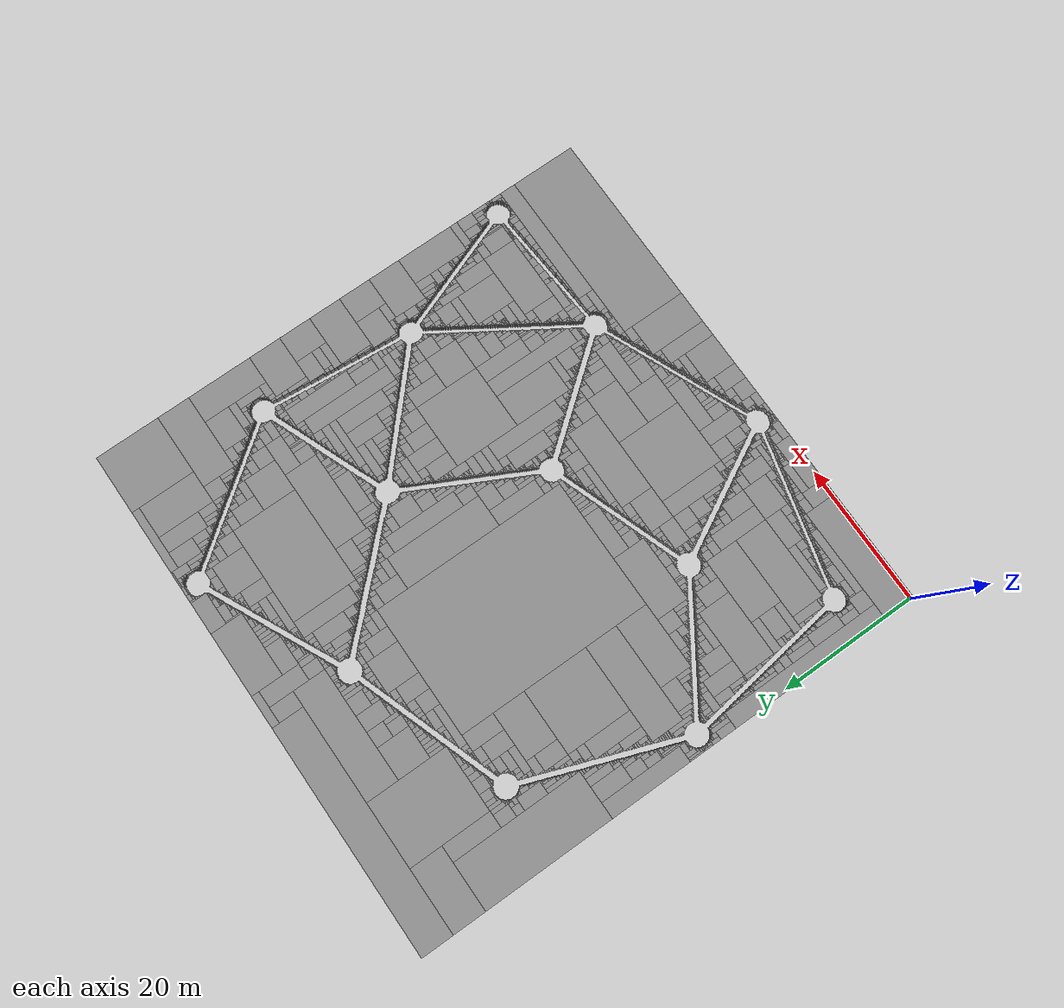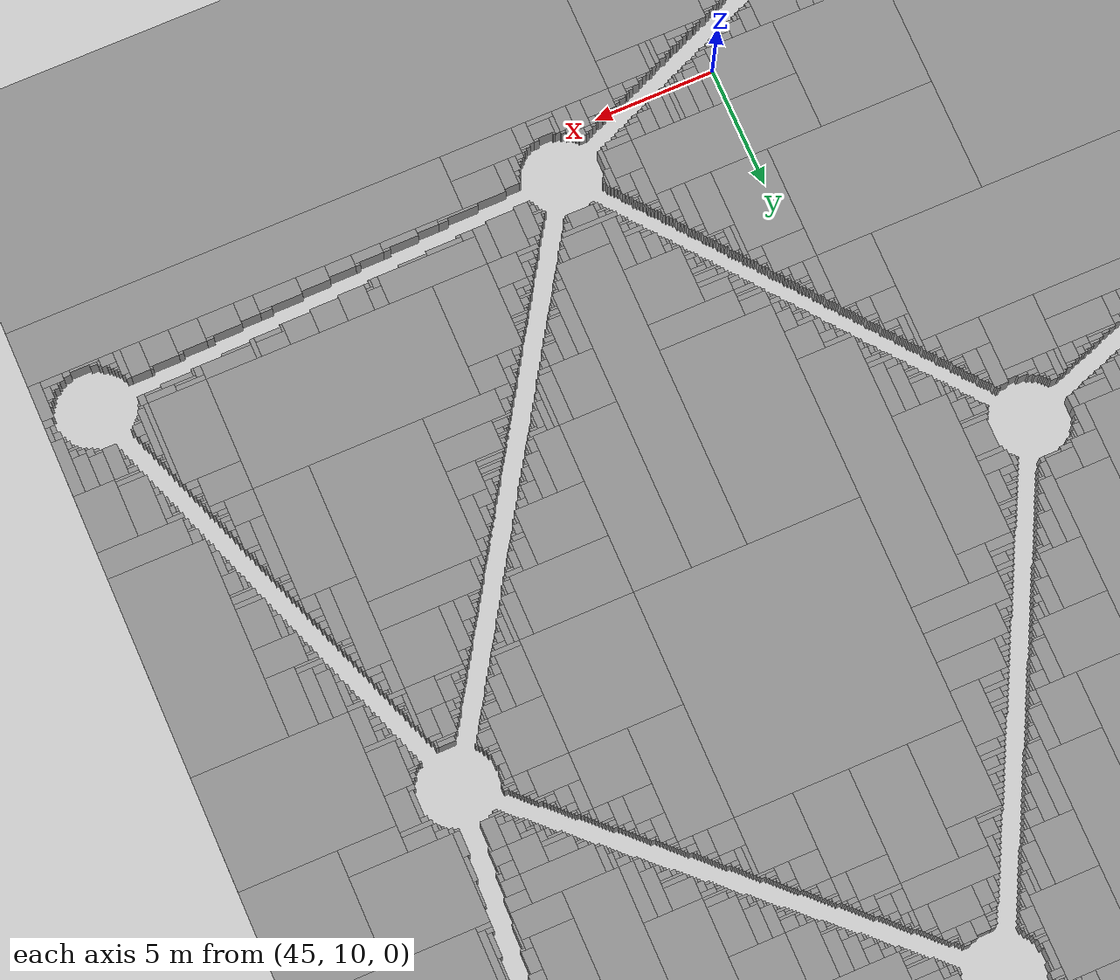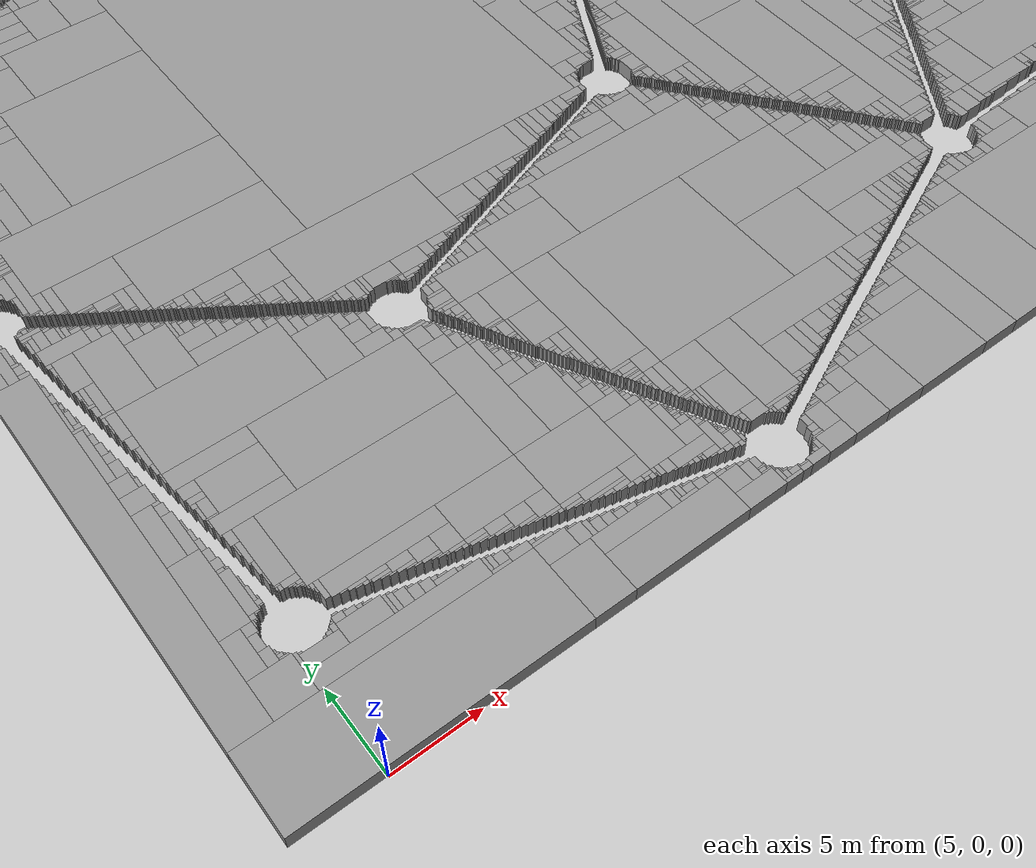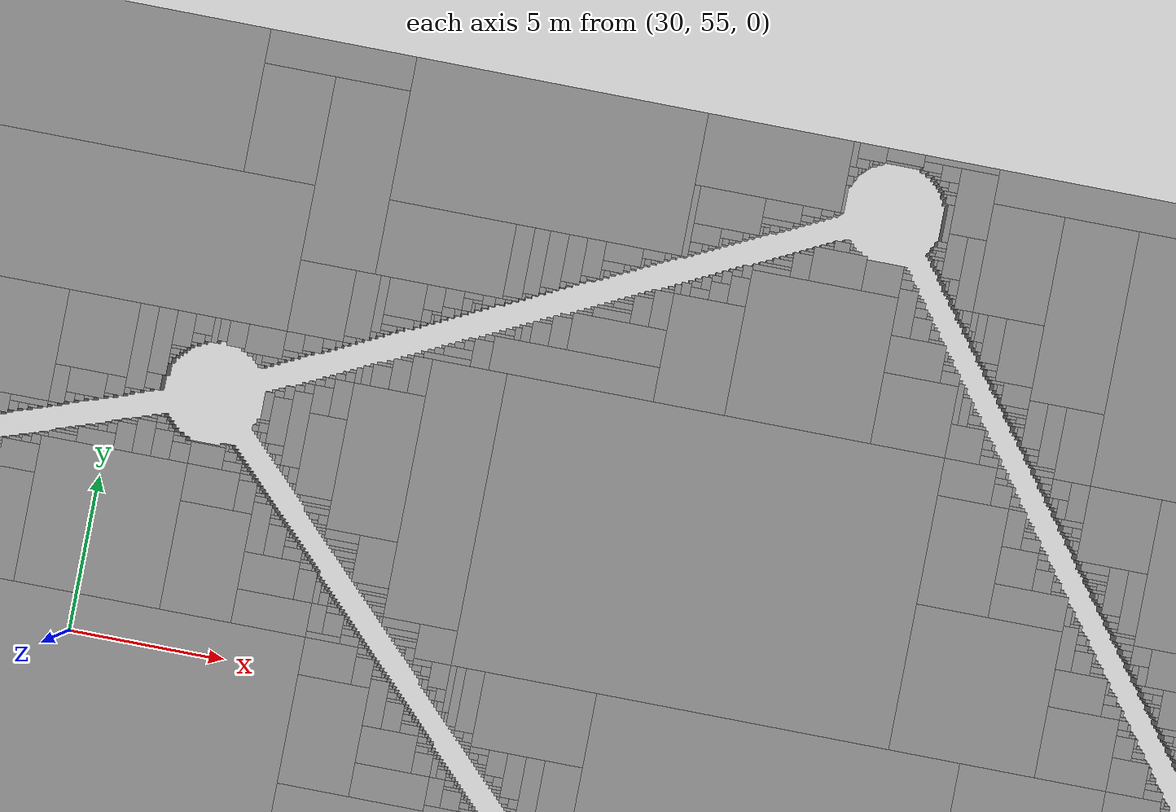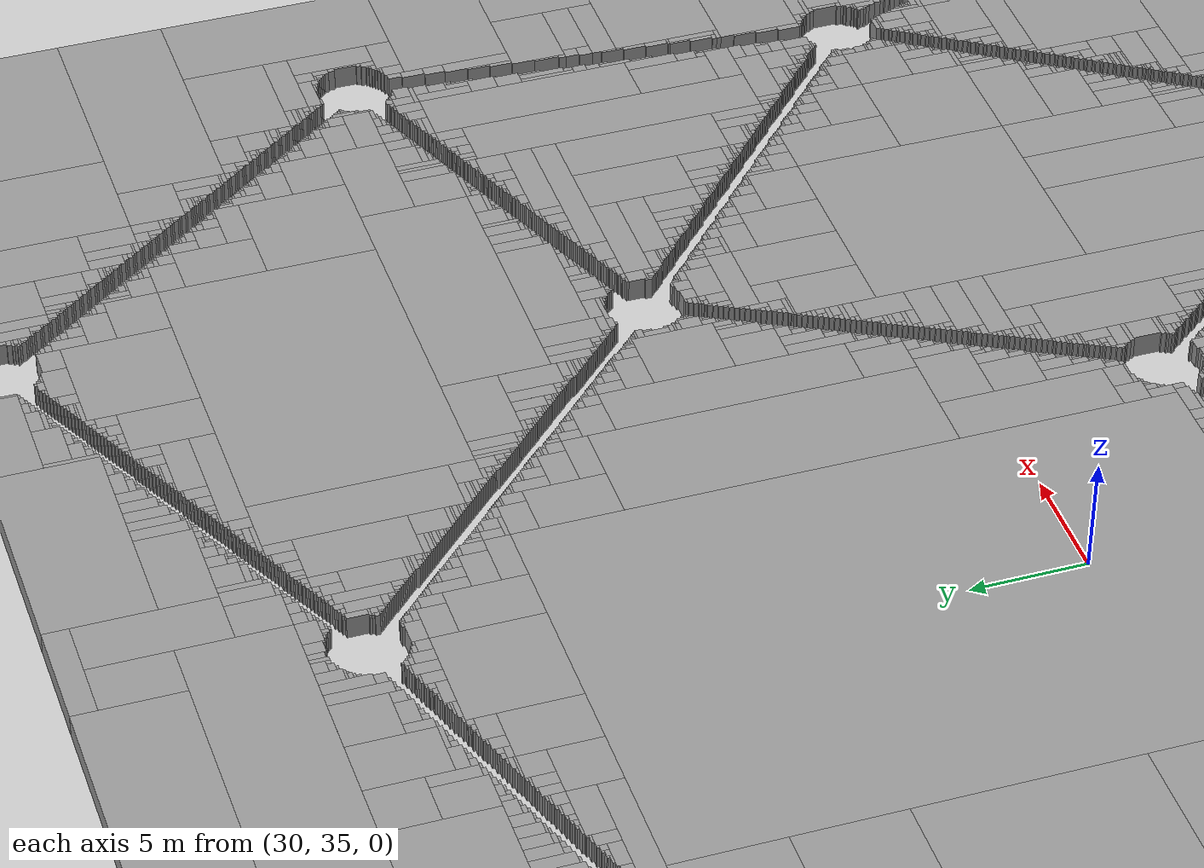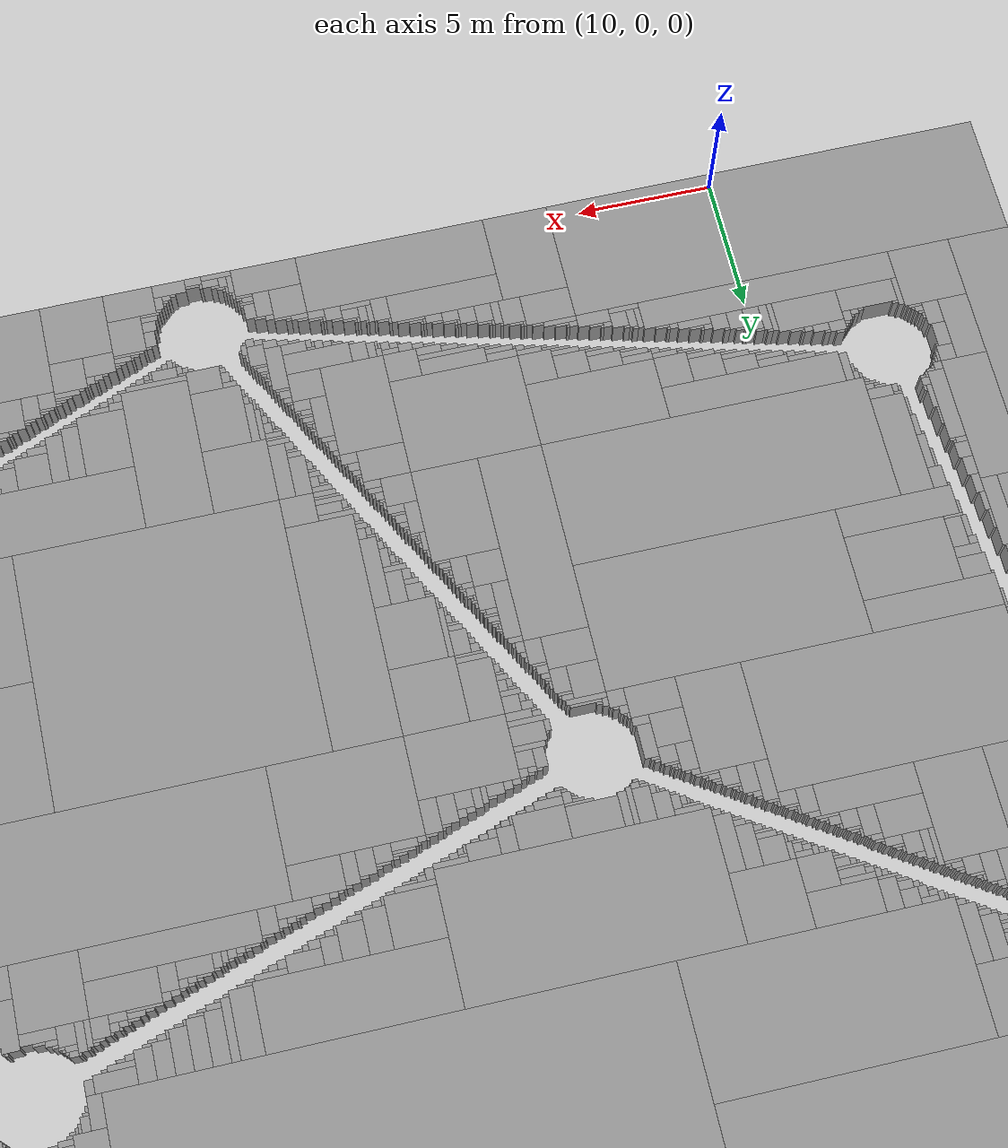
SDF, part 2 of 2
<collision name='Wall_69.9_22.5_Collision'>
	<geometry>
	<box>
 <size>1.000000 0.300000 1.000000</size>
 </box>
</geometry>
<pose frame=''>69.900002 22.450001 0.500000 0 0 0</pose>
</collision>
	<visual name='Wall_69.9_22.5_Visual'>
<pose frame=''>69.900002 22.450001 0.500000 0 0 0</pose>
	<geometry>
<box>
<size>1.000000 0.300000 1.000000</size>
</box>
</geometry>
<material>
<script>
<uri>file://media/materials/scripts/gazebo.material</uri>
<name>Gazebo/Grey</name>
</script>
<ambient>1 1 1 1</ambient>
</material>
</visual>
<collision name='Wall_70.0_22.2_Collision'>
	<geometry>
	<box>
 <size>0.900000 0.100000 1.000000</size>
 </box>
</geometry>
<pose frame=''>69.950005 22.250000 0.500000 0 0 0</pose>
</collision>
	<visual name='Wall_70.0_22.2_Visual'>
<pose frame=''>69.950005 22.250000 0.500000 0 0 0</pose>
	<geometry>
<box>
<size>0.900000 0.100000 1.000000</size>
</box>
</geometry>
<material>
<script>
<uri>file://media/materials/scripts/gazebo.material</uri>
<name>Gazebo/Grey</name>
</script>
<ambient>1 1 1 1</ambient>
</material>
</visual>
<collision name='Wall_69.8_22.7_Collision'>
	<geometry>
	<box>
 <size>1.100000 0.200000 1.000000</size>
 </box>
</geometry>
<pose frame=''>69.849998 22.700001 0.500000 0 0 0</pose>
</collision>
	<visual name='Wall_69.8_22.7_Visual'>
<pose frame=''>69.849998 22.700001 0.500000 0 0 0</pose>
	<geometry>
<box>
<size>1.100000 0.200000 1.000000</size>
</box>
</geometry>
<material>
<script>
<uri>file://media/materials/scripts/gazebo.material</uri>
<name>Gazebo/Grey</name>
</script>
<ambient>1 1 1 1</ambient>
</material>
</visual>
<collision name='Wall_69.8_23.6_Collision'>
	<geometry>
	<box>
 <size>1.200000 1.700000 1.000000</size>
 </box>
</geometry>
<pose frame=''>69.800003 23.650000 0.500000 0 0 0</pose>
</collision>
	<visual name='Wall_69.8_23.6_Visual'>
<pose frame=''>69.800003 23.650000 0.500000 0 0 0</pose>
	<geometry>
<box>
<size>1.200000 1.700000 1.000000</size>
</box>
</geometry>
<material>
<script>
<uri>file://media/materials/scripts/gazebo.material</uri>
<name>Gazebo/Grey</name>
</script>
<ambient>1 1 1 1</ambient>
</material>
</visual>
<collision name='Wall_70.8_18.8_Collision'>
	<geometry>
	<box>
 <size>0.100000 0.100000 1.000000</size>
 </box>
</geometry>
<pose frame=''>70.849998 18.750000 0.500000 0 0 0</pose>
</collision>
	<visual name='Wall_70.8_18.8_Visual'>
<pose frame=''>70.849998 18.750000 0.500000 0 0 0</pose>
	<geometry>
<box>
<size>0.100000 0.100000 1.000000</size>
</box>
</geometry>
<material>
<script>
<uri>file://media/materials/scripts/gazebo.material</uri>
<name>Gazebo/Grey</name>
</script>
<ambient>1 1 1 1</ambient>
</material>
</visual>
<collision name='Wall_70.8_19.0_Collision'>
	<geometry>
	<box>
 <size>0.200000 0.400000 1.000000</size>
 </box>
</geometry>
<pose frame=''>70.800003 19.000000 0.500000 0 0 0</pose>
</collision>
	<visual name='Wall_70.8_19.0_Visual'>
<pose frame=''>70.800003 19.000000 0.500000 0 0 0</pose>
	<geometry>
<box>
<size>0.200000 0.400000 1.000000</size>
</box>
</geometry>
<material>
<script>
<uri>file://media/materials/scripts/gazebo.material</uri>
<name>Gazebo/Grey</name>
</script>
<ambient>1 1 1 1</ambient>
</material>
</visual>
<collision name='Wall_70.7_19.1_Collision'>
	<geometry>
	<box>
 <size>0.100000 0.100000 1.000000</size>
 </box>
</geometry>
<pose frame=''>70.650002 19.150000 0.500000 0 0 0</pose>
</collision>
	<visual name='Wall_70.7_19.1_Visual'>
<pose frame=''>70.650002 19.150000 0.500000 0 0 0</pose>
	<geometry>
<box>
<size>0.100000 0.100000 1.000000</size>
</box>
</geometry>
<material>
<script>
<uri>file://media/materials/scripts/gazebo.material</uri>
<name>Gazebo/Grey</name>
</script>
<ambient>1 1 1 1</ambient>
</material>
</visual>
<collision name='Wall_72.7_19.2_Collision'>
	<geometry>
	<box>
 <size>3.500000 1.100000 1.000000</size>
 </box>
</geometry>
<pose frame=''>72.650002 19.250000 0.500000 0 0 0</pose>
</collision>
	<visual name='Wall_72.7_19.2_Visual'>
<pose frame=''>72.650002 19.250000 0.500000 0 0 0</pose>
	<geometry>
<box>
<size>3.500000 1.100000 1.000000</size>
</box>
</geometry>
<material>
<script>
<uri>file://media/materials/scripts/gazebo.material</uri>
<name>Gazebo/Grey</name>
</script>
<ambient>1 1 1 1</ambient>
</material>
</visual>
<collision name='Wall_70.7_19.6_Collision'>
	<geometry>
	<box>
 <size>0.400000 0.500000 1.000000</size>
 </box>
</geometry>
<pose frame=''>70.700005 19.550001 0.500000 0 0 0</pose>
</collision>
	<visual name='Wall_70.7_19.6_Visual'>
<pose frame=''>70.700005 19.550001 0.500000 0 0 0</pose>
	<geometry>
<box>
<size>0.400000 0.500000 1.000000</size>
</box>
</geometry>
<material>
<script>
<uri>file://media/materials/scripts/gazebo.material</uri>
<name>Gazebo/Grey</name>
</script>
<ambient>1 1 1 1</ambient>
</material>
</visual>
<collision name='Wall_70.8_19.2_Collision'>
	<geometry>
	<box>
 <size>0.300000 0.100000 1.000000</size>
 </box>
</geometry>
<pose frame=''>70.750000 19.250000 0.500000 0 0 0</pose>
</collision>
	<visual name='Wall_70.8_19.2_Visual'>
<pose frame=''>70.750000 19.250000 0.500000 0 0 0</pose>
	<geometry>
<box>
<size>0.300000 0.100000 1.000000</size>
</box>
</geometry>
<material>
<script>
<uri>file://media/materials/scripts/gazebo.material</uri>
<name>Gazebo/Grey</name>
</script>
<ambient>1 1 1 1</ambient>
</material>
</visual>
<collision name='Wall_70.5_19.7_Collision'>
	<geometry>
	<box>
 <size>0.100000 0.200000 1.000000</size>
 </box>
</geometry>
<pose frame=''>70.450005 19.700001 0.500000 0 0 0</pose>
</collision>
	<visual name='Wall_70.5_19.7_Visual'>
<pose frame=''>70.450005 19.700001 0.500000 0 0 0</pose>
	<geometry>
<box>
<size>0.100000 0.200000 1.000000</size>
</box>
</geometry>
<material>
<script>
<uri>file://media/materials/scripts/gazebo.material</uri>
<name>Gazebo/Grey</name>
</script>
<ambient>1 1 1 1</ambient>
</material>
</visual>
<collision name='Wall_72.4_24.0_Collision'>
	<geometry>
	<box>
 <size>4.000000 8.300000 1.000000</size>
 </box>
</geometry>
<pose frame=''>72.400002 23.950001 0.500000 0 0 0</pose>
</collision>
	<visual name='Wall_72.4_24.0_Visual'>
<pose frame=''>72.400002 23.950001 0.500000 0 0 0</pose>
	<geometry>
<box>
<size>4.000000 8.300000 1.000000</size>
</box>
</geometry>
<material>
<script>
<uri>file://media/materials/scripts/gazebo.material</uri>
<name>Gazebo/Grey</name>
</script>
<ambient>1 1 1 1</ambient>
</material>
</visual>
<collision name='Wall_66.2_25.1_Collision'>
	<geometry>
	<box>
 <size>1.100000 3.500000 1.000000</size>
 </box>
</geometry>
<pose frame=''>66.250000 25.150000 0.500000 0 0 0</pose>
</collision>
	<visual name='Wall_66.2_25.1_Visual'>
<pose frame=''>66.250000 25.150000 0.500000 0 0 0</pose>
	<geometry>
<box>
<size>1.100000 3.500000 1.000000</size>
</box>
</geometry>
<material>
<script>
<uri>file://media/materials/scripts/gazebo.material</uri>
<name>Gazebo/Grey</name>
</script>
<ambient>1 1 1 1</ambient>
</material>
</visual>
<collision name='Wall_67.1_24.5_Collision'>
	<geometry>
	<box>
 <size>0.600000 2.100000 1.000000</size>
 </box>
</geometry>
<pose frame=''>67.099998 24.450001 0.500000 0 0 0</pose>
</collision>
	<visual name='Wall_67.1_24.5_Visual'>
<pose frame=''>67.099998 24.450001 0.500000 0 0 0</pose>
	<geometry>
<box>
<size>0.600000 2.100000 1.000000</size>
</box>
</geometry>
<material>
<script>
<uri>file://media/materials/scripts/gazebo.material</uri>
<name>Gazebo/Grey</name>
</script>
<ambient>1 1 1 1</ambient>
</material>
</visual>
<collision name='Wall_67.7_23.7_Collision'>
	<geometry>
	<box>
 <size>0.600000 0.600000 1.000000</size>
 </box>
</geometry>
<pose frame=''>67.700005 23.700001 0.500000 0 0 0</pose>
</collision>
	<visual name='Wall_67.7_23.7_Visual'>
<pose frame=''>67.700005 23.700001 0.500000 0 0 0</pose>
	<geometry>
<box>
<size>0.600000 0.600000 1.000000</size>
</box>
</geometry>
<material>
<script>
<uri>file://media/materials/scripts/gazebo.material</uri>
<name>Gazebo/Grey</name>
</script>
<ambient>1 1 1 1</ambient>
</material>
</visual>
<collision name='Wall_67.7_24.1_Collision'>
	<geometry>
	<box>
 <size>0.500000 0.300000 1.000000</size>
 </box>
</geometry>
<pose frame=''>67.650002 24.150000 0.500000 0 0 0</pose>
</collision>
	<visual name='Wall_67.7_24.1_Visual'>
<pose frame=''>67.650002 24.150000 0.500000 0 0 0</pose>
	<geometry>
<box>
<size>0.500000 0.300000 1.000000</size>
</box>
</geometry>
<material>
<script>
<uri>file://media/materials/scripts/gazebo.material</uri>
<name>Gazebo/Grey</name>
</script>
<ambient>1 1 1 1</ambient>
</material>
</visual>
<collision name='Wall_67.6_24.4_Collision'>
	<geometry>
	<box>
 <size>0.400000 0.200000 1.000000</size>
 </box>
</geometry>
<pose frame=''>67.599998 24.400000 0.500000 0 0 0</pose>
</collision>
	<visual name='Wall_67.6_24.4_Visual'>
<pose frame=''>67.599998 24.400000 0.500000 0 0 0</pose>
	<geometry>
<box>
<size>0.400000 0.200000 1.000000</size>
</box>
</geometry>
<material>
<script>
<uri>file://media/materials/scripts/gazebo.material</uri>
<name>Gazebo/Grey</name>
</script>
<ambient>1 1 1 1</ambient>
</material>
</visual>
<collision name='Wall_67.6_24.6_Collision'>
	<geometry>
	<box>
 <size>0.300000 0.300000 1.000000</size>
 </box>
</geometry>
<pose frame=''>67.550003 24.650000 0.500000 0 0 0</pose>
</collision>
	<visual name='Wall_67.6_24.6_Visual'>
<pose frame=''>67.550003 24.650000 0.500000 0 0 0</pose>
	<geometry>
<box>
<size>0.300000 0.300000 1.000000</size>
</box>
</geometry>
<material>
<script>
<uri>file://media/materials/scripts/gazebo.material</uri>
<name>Gazebo/Grey</name>
</script>
<ambient>1 1 1 1</ambient>
</material>
</visual>
<collision name='Wall_67.5_25.0_Collision'>
	<geometry>
	<box>
 <size>0.200000 0.300000 1.000000</size>
 </box>
</geometry>
<pose frame=''>67.500000 24.950001 0.500000 0 0 0</pose>
</collision>
	<visual name='Wall_67.5_25.0_Visual'>
<pose frame=''>67.500000 24.950001 0.500000 0 0 0</pose>
	<geometry>
<box>
<size>0.200000 0.300000 1.000000</size>
</box>
</geometry>
<material>
<script>
<uri>file://media/materials/scripts/gazebo.material</uri>
<name>Gazebo/Grey</name>
</script>
<ambient>1 1 1 1</ambient>
</material>
</visual>
<collision name='Wall_67.0_25.6_Collision'>
	<geometry>
	<box>
 <size>0.400000 0.200000 1.000000</size>
 </box>
</geometry>
<pose frame=''>67.000000 25.600000 0.500000 0 0 0</pose>
</collision>
	<visual name='Wall_67.0_25.6_Visual'>
<pose frame=''>67.000000 25.600000 0.500000 0 0 0</pose>
	<geometry>
<box>
<size>0.400000 0.200000 1.000000</size>
</box>
</geometry>
<material>
<script>
<uri>file://media/materials/scripts/gazebo.material</uri>
<name>Gazebo/Grey</name>
</script>
<ambient>1 1 1 1</ambient>
</material>
</visual>
<collision name='Wall_67.3_25.6_Collision'>
	<geometry>
	<box>
 <size>0.200000 0.100000 1.000000</size>
 </box>
</geometry>
<pose frame=''>67.300003 25.550001 0.500000 0 0 0</pose>
</collision>
	<visual name='Wall_67.3_25.6_Visual'>
<pose frame=''>67.300003 25.550001 0.500000 0 0 0</pose>
	<geometry>
<box>
<size>0.200000 0.100000 1.000000</size>
</box>
</geometry>
<material>
<script>
<uri>file://media/materials/scripts/gazebo.material</uri>
<name>Gazebo/Grey</name>
</script>
<ambient>1 1 1 1</ambient>
</material>
</visual>
<collision name='Wall_67.2_25.6_Collision'>
	<geometry>
	<box>
 <size>0.100000 0.100000 1.000000</size>
 </box>
</geometry>
<pose frame=''>67.250000 25.650000 0.500000 0 0 0</pose>
</collision>
	<visual name='Wall_67.2_25.6_Visual'>
<pose frame=''>67.250000 25.650000 0.500000 0 0 0</pose>
	<geometry>
<box>
<size>0.100000 0.100000 1.000000</size>
</box>
</geometry>
<material>
<script>
<uri>file://media/materials/scripts/gazebo.material</uri>
<name>Gazebo/Grey</name>
</script>
<ambient>1 1 1 1</ambient>
</material>
</visual>
<collision name='Wall_67.5_25.2_Collision'>
	<geometry>
	<box>
 <size>0.100000 0.200000 1.000000</size>
 </box>
</geometry>
<pose frame=''>67.450005 25.200001 0.500000 0 0 0</pose>
</collision>
	<visual name='Wall_67.5_25.2_Visual'>
<pose frame=''>67.450005 25.200001 0.500000 0 0 0</pose>
	<geometry>
<box>
<size>0.100000 0.200000 1.000000</size>
</box>
</geometry>
<material>
<script>
<uri>file://media/materials/scripts/gazebo.material</uri>
<name>Gazebo/Grey</name>
</script>
<ambient>1 1 1 1</ambient>
</material>
</visual>
<collision name='Wall_68.1_23.6_Collision'>
	<geometry>
	<box>
 <size>0.100000 0.300000 1.000000</size>
 </box>
</geometry>
<pose frame=''>68.050003 23.550001 0.500000 0 0 0</pose>
</collision>
	<visual name='Wall_68.1_23.6_Visual'>
<pose frame=''>68.050003 23.550001 0.500000 0 0 0</pose>
	<geometry>
<box>
<size>0.100000 0.300000 1.000000</size>
</box>
</geometry>
<material>
<script>
<uri>file://media/materials/scripts/gazebo.material</uri>
<name>Gazebo/Grey</name>
</script>
<ambient>1 1 1 1</ambient>
</material>
</visual>
<collision name='Wall_69.1_23.5_Collision'>
	<geometry>
	<box>
 <size>0.200000 0.200000 1.000000</size>
 </box>
</geometry>
<pose frame=''>69.099998 23.500000 0.500000 0 0 0</pose>
</collision>
	<visual name='Wall_69.1_23.5_Visual'>
<pose frame=''>69.099998 23.500000 0.500000 0 0 0</pose>
	<geometry>
<box>
<size>0.200000 0.200000 1.000000</size>
</box>
</geometry>
<material>
<script>
<uri>file://media/materials/scripts/gazebo.material</uri>
<name>Gazebo/Grey</name>
</script>
<ambient>1 1 1 1</ambient>
</material>
</visual>
<collision name='Wall_69.1_24.1_Collision'>
	<geometry>
	<box>
 <size>0.300000 0.900000 1.000000</size>
 </box>
</geometry>
<pose frame=''>69.050003 24.050001 0.500000 0 0 0</pose>
</collision>
	<visual name='Wall_69.1_24.1_Visual'>
<pose frame=''>69.050003 24.050001 0.500000 0 0 0</pose>
	<geometry>
<box>
<size>0.300000 0.900000 1.000000</size>
</box>
</geometry>
<material>
<script>
<uri>file://media/materials/scripts/gazebo.material</uri>
<name>Gazebo/Grey</name>
</script>
<ambient>1 1 1 1</ambient>
</material>
</visual>
<collision name='Wall_68.8_24.1_Collision'>
	<geometry>
	<box>
 <size>0.100000 0.300000 1.000000</size>
 </box>
</geometry>
<pose frame=''>68.849998 24.050001 0.500000 0 0 0</pose>
</collision>
	<visual name='Wall_68.8_24.1_Visual'>
<pose frame=''>68.849998 24.050001 0.500000 0 0 0</pose>
	<geometry>
<box>
<size>0.100000 0.300000 1.000000</size>
</box>
</geometry>
<material>
<script>
<uri>file://media/materials/scripts/gazebo.material</uri>
<name>Gazebo/Grey</name>
</script>
<ambient>1 1 1 1</ambient>
</material>
</visual>
<collision name='Wall_68.8_24.4_Collision'>
	<geometry>
	<box>
 <size>0.200000 0.300000 1.000000</size>
 </box>
</geometry>
<pose frame=''>68.800003 24.350000 0.500000 0 0 0</pose>
</collision>
	<visual name='Wall_68.8_24.4_Visual'>
<pose frame=''>68.800003 24.350000 0.500000 0 0 0</pose>
	<geometry>
<box>
<size>0.200000 0.300000 1.000000</size>
</box>
</geometry>
<material>
<script>
<uri>file://media/materials/scripts/gazebo.material</uri>
<name>Gazebo/Grey</name>
</script>
<ambient>1 1 1 1</ambient>
</material>
</visual>
<collision name='Wall_68.7_24.5_Collision'>
	<geometry>
	<box>
 <size>0.100000 0.100000 1.000000</size>
 </box>
</geometry>
<pose frame=''>68.650002 24.450001 0.500000 0 0 0</pose>
</collision>
	<visual name='Wall_68.7_24.5_Visual'>
<pose frame=''>68.650002 24.450001 0.500000 0 0 0</pose>
	<geometry>
<box>
<size>0.100000 0.100000 1.000000</size>
</box>
</geometry>
<material>
<script>
<uri>file://media/materials/scripts/gazebo.material</uri>
<name>Gazebo/Grey</name>
</script>
<ambient>1 1 1 1</ambient>
</material>
</visual>
<collision name='Wall_68.6_24.9_Collision'>
	<geometry>
	<box>
 <size>0.100000 0.400000 1.000000</size>
 </box>
</geometry>
<pose frame=''>68.550003 24.900000 0.500000 0 0 0</pose>
</collision>
	<visual name='Wall_68.6_24.9_Visual'>
<pose frame=''>68.550003 24.900000 0.500000 0 0 0</pose>
	<geometry>
<box>
<size>0.100000 0.400000 1.000000</size>
</box>
</geometry>
<material>
<script>
<uri>file://media/materials/scripts/gazebo.material</uri>
<name>Gazebo/Grey</name>
</script>
<ambient>1 1 1 1</ambient>
</material>
</visual>
<collision name='Wall_68.5_25.1_Collision'>
	<geometry>
	<box>
 <size>0.100000 0.100000 1.000000</size>
 </box>
</geometry>
<pose frame=''>68.450005 25.050001 0.500000 0 0 0</pose>
</collision>
	<visual name='Wall_68.5_25.1_Visual'>
<pose frame=''>68.450005 25.050001 0.500000 0 0 0</pose>
	<geometry>
<box>
<size>0.100000 0.100000 1.000000</size>
</box>
</geometry>
<material>
<script>
<uri>file://media/materials/scripts/gazebo.material</uri>
<name>Gazebo/Grey</name>
</script>
<ambient>1 1 1 1</ambient>
</material>
</visual>
<collision name='Wall_69.5_25.1_Collision'>
	<geometry>
	<box>
 <size>1.800000 1.200000 1.000000</size>
 </box>
</geometry>
<pose frame=''>69.500000 25.100000 0.500000 0 0 0</pose>
</collision>
	<visual name='Wall_69.5_25.1_Visual'>
<pose frame=''>69.500000 25.100000 0.500000 0 0 0</pose>
	<geometry>
<box>
<size>1.800000 1.200000 1.000000</size>
</box>
</geometry>
<material>
<script>
<uri>file://media/materials/scripts/gazebo.material</uri>
<name>Gazebo/Grey</name>
</script>
<ambient>1 1 1 1</ambient>
</material>
</visual>
<collision name='Wall_68.5_25.2_Collision'>
	<geometry>
	<box>
 <size>0.200000 0.300000 1.000000</size>
 </box>
</geometry>
<pose frame=''>68.500000 25.250000 0.500000 0 0 0</pose>
</collision>
	<visual name='Wall_68.5_25.2_Visual'>
<pose frame=''>68.500000 25.250000 0.500000 0 0 0</pose>
	<geometry>
<box>
<size>0.200000 0.300000 1.000000</size>
</box>
</geometry>
<material>
<script>
<uri>file://media/materials/scripts/gazebo.material</uri>
<name>Gazebo/Grey</name>
</script>
<ambient>1 1 1 1</ambient>
</material>
</visual>
<collision name='Wall_68.3_25.3_Collision'>
	<geometry>
	<box>
 <size>0.100000 0.200000 1.000000</size>
 </box>
</geometry>
<pose frame=''>68.349998 25.300001 0.500000 0 0 0</pose>
</collision>
	<visual name='Wall_68.3_25.3_Visual'>
<pose frame=''>68.349998 25.300001 0.500000 0 0 0</pose>
	<geometry>
<box>
<size>0.100000 0.200000 1.000000</size>
</box>
</geometry>
<material>
<script>
<uri>file://media/materials/scripts/gazebo.material</uri>
<name>Gazebo/Grey</name>
</script>
<ambient>1 1 1 1</ambient>
</material>
</visual>
<collision name='Wall_68.4_25.6_Collision'>
	<geometry>
	<box>
 <size>0.400000 0.200000 1.000000</size>
 </box>
</geometry>
<pose frame=''>68.400002 25.600000 0.500000 0 0 0</pose>
</collision>
	<visual name='Wall_68.4_25.6_Visual'>
<pose frame=''>68.400002 25.600000 0.500000 0 0 0</pose>
	<geometry>
<box>
<size>0.400000 0.200000 1.000000</size>
</box>
</geometry>
<material>
<script>
<uri>file://media/materials/scripts/gazebo.material</uri>
<name>Gazebo/Grey</name>
</script>
<ambient>1 1 1 1</ambient>
</material>
</visual>
<collision name='Wall_68.5_25.5_Collision'>
	<geometry>
	<box>
 <size>0.300000 0.100000 1.000000</size>
 </box>
</geometry>
<pose frame=''>68.450005 25.450001 0.500000 0 0 0</pose>
</collision>
	<visual name='Wall_68.5_25.5_Visual'>
<pose frame=''>68.450005 25.450001 0.500000 0 0 0</pose>
	<geometry>
<box>
<size>0.300000 0.100000 1.000000</size>
</box>
</geometry>
<material>
<script>
<uri>file://media/materials/scripts/gazebo.material</uri>
<name>Gazebo/Grey</name>
</script>
<ambient>1 1 1 1</ambient>
</material>
</visual>
<collision name='Wall_67.1_25.8_Collision'>
	<geometry>
	<box>
 <size>0.500000 0.100000 1.000000</size>
 </box>
</geometry>
<pose frame=''>67.050003 25.750000 0.500000 0 0 0</pose>
</collision>
	<visual name='Wall_67.1_25.8_Visual'>
<pose frame=''>67.050003 25.750000 0.500000 0 0 0</pose>
	<geometry>
<box>
<size>0.500000 0.100000 1.000000</size>
</box>
</geometry>
<material>
<script>
<uri>file://media/materials/scripts/gazebo.material</uri>
<name>Gazebo/Grey</name>
</script>
<ambient>1 1 1 1</ambient>
</material>
</visual>
<collision name='Wall_67.0_26.0_Collision'>
	<geometry>
	<box>
 <size>0.400000 0.300000 1.000000</size>
 </box>
</geometry>
<pose frame=''>67.000000 25.950001 0.500000 0 0 0</pose>
</collision>
	<visual name='Wall_67.0_26.0_Visual'>
<pose frame=''>67.000000 25.950001 0.500000 0 0 0</pose>
	<geometry>
<box>
<size>0.400000 0.300000 1.000000</size>
</box>
</geometry>
<material>
<script>
<uri>file://media/materials/scripts/gazebo.material</uri>
<name>Gazebo/Grey</name>
</script>
<ambient>1 1 1 1</ambient>
</material>
</visual>
<collision name='Wall_67.2_25.9_Collision'>
	<geometry>
	<box>
 <size>0.100000 0.100000 1.000000</size>
 </box>
</geometry>
<pose frame=''>67.250000 25.850000 0.500000 0 0 0</pose>
</collision>
	<visual name='Wall_67.2_25.9_Visual'>
<pose frame=''>67.250000 25.850000 0.500000 0 0 0</pose>
	<geometry>
<box>
<size>0.100000 0.100000 1.000000</size>
</box>
</geometry>
<material>
<script>
<uri>file://media/materials/scripts/gazebo.material</uri>
<name>Gazebo/Grey</name>
</script>
<ambient>1 1 1 1</ambient>
</material>
</visual>
<collision name='Wall_67.0_26.2_Collision'>
	<geometry>
	<box>
 <size>0.300000 0.300000 1.000000</size>
 </box>
</geometry>
<pose frame=''>66.950005 26.250000 0.500000 0 0 0</pose>
</collision>
	<visual name='Wall_67.0_26.2_Visual'>
<pose frame=''>66.950005 26.250000 0.500000 0 0 0</pose>
	<geometry>
<box>
<size>0.300000 0.300000 1.000000</size>
</box>
</geometry>
<material>
<script>
<uri>file://media/materials/scripts/gazebo.material</uri>
<name>Gazebo/Grey</name>
</script>
<ambient>1 1 1 1</ambient>
</material>
</visual>
<collision name='Wall_66.9_26.6_Collision'>
	<geometry>
	<box>
 <size>0.200000 0.300000 1.000000</size>
 </box>
</geometry>
<pose frame=''>66.900002 26.550001 0.500000 0 0 0</pose>
</collision>
	<visual name='Wall_66.9_26.6_Visual'>
<pose frame=''>66.900002 26.550001 0.500000 0 0 0</pose>
	<geometry>
<box>
<size>0.200000 0.300000 1.000000</size>
</box>
</geometry>
<material>
<script>
<uri>file://media/materials/scripts/gazebo.material</uri>
<name>Gazebo/Grey</name>
</script>
<ambient>1 1 1 1</ambient>
</material>
</visual>
<collision name='Wall_66.8_26.8_Collision'>
	<geometry>
	<box>
 <size>0.100000 0.200000 1.000000</size>
 </box>
</geometry>
<pose frame=''>66.849998 26.800001 0.500000 0 0 0</pose>
</collision>
	<visual name='Wall_66.8_26.8_Visual'>
<pose frame=''>66.849998 26.800001 0.500000 0 0 0</pose>
	<geometry>
<box>
<size>0.100000 0.200000 1.000000</size>
</box>
</geometry>
<material>
<script>
<uri>file://media/materials/scripts/gazebo.material</uri>
<name>Gazebo/Grey</name>
</script>
<ambient>1 1 1 1</ambient>
</material>
</visual>
<collision name='Wall_68.0_26.5_Collision'>
	<geometry>
	<box>
 <size>0.100000 0.300000 1.000000</size>
 </box>
</geometry>
<pose frame=''>67.950005 26.450001 0.500000 0 0 0</pose>
</collision>
	<visual name='Wall_68.0_26.5_Visual'>
<pose frame=''>67.950005 26.450001 0.500000 0 0 0</pose>
	<geometry>
<box>
<size>0.100000 0.300000 1.000000</size>
</box>
</geometry>
<material>
<script>
<uri>file://media/materials/scripts/gazebo.material</uri>
<name>Gazebo/Grey</name>
</script>
<ambient>1 1 1 1</ambient>
</material>
</visual>
<collision name='Wall_67.9_26.8_Collision'>
	<geometry>
	<box>
 <size>0.200000 0.300000 1.000000</size>
 </box>
</geometry>
<pose frame=''>67.900002 26.750000 0.500000 0 0 0</pose>
</collision>
	<visual name='Wall_67.9_26.8_Visual'>
<pose frame=''>67.900002 26.750000 0.500000 0 0 0</pose>
	<geometry>
<box>
<size>0.200000 0.300000 1.000000</size>
</box>
</geometry>
<material>
<script>
<uri>file://media/materials/scripts/gazebo.material</uri>
<name>Gazebo/Grey</name>
</script>
<ambient>1 1 1 1</ambient>
</material>
</visual>
<collision name='Wall_66.0_27.5_Collision'>
	<geometry>
	<box>
 <size>0.500000 1.200000 1.000000</size>
 </box>
</geometry>
<pose frame=''>65.950005 27.500000 0.500000 0 0 0</pose>
</collision>
	<visual name='Wall_66.0_27.5_Visual'>
<pose frame=''>65.950005 27.500000 0.500000 0 0 0</pose>
	<geometry>
<box>
<size>0.500000 1.200000 1.000000</size>
</box>
</geometry>
<material>
<script>
<uri>file://media/materials/scripts/gazebo.material</uri>
<name>Gazebo/Grey</name>
</script>
<ambient>1 1 1 1</ambient>
</material>
</visual>
<collision name='Wall_66.5_27.1_Collision'>
	<geometry>
	<box>
 <size>0.600000 0.300000 1.000000</size>
 </box>
</geometry>
<pose frame=''>66.500000 27.050001 0.500000 0 0 0</pose>
</collision>
	<visual name='Wall_66.5_27.1_Visual'>
<pose frame=''>66.500000 27.050001 0.500000 0 0 0</pose>
	<geometry>
<box>
<size>0.600000 0.300000 1.000000</size>
</box>
</geometry>
<material>
<script>
<uri>file://media/materials/scripts/gazebo.material</uri>
<name>Gazebo/Grey</name>
</script>
<ambient>1 1 1 1</ambient>
</material>
</visual>
<collision name='Wall_66.5_27.4_Collision'>
	<geometry>
	<box>
 <size>0.500000 0.300000 1.000000</size>
 </box>
</geometry>
<pose frame=''>66.450005 27.350000 0.500000 0 0 0</pose>
</collision>
	<visual name='Wall_66.5_27.4_Visual'>
<pose frame=''>66.450005 27.350000 0.500000 0 0 0</pose>
	<geometry>
<box>
<size>0.500000 0.300000 1.000000</size>
</box>
</geometry>
<material>
<script>
<uri>file://media/materials/scripts/gazebo.material</uri>
<name>Gazebo/Grey</name>
</script>
<ambient>1 1 1 1</ambient>
</material>
</visual>
<collision name='Wall_66.3_27.7_Collision'>
	<geometry>
	<box>
 <size>0.300000 0.400000 1.000000</size>
 </box>
</geometry>
<pose frame=''>66.349998 27.700001 0.500000 0 0 0</pose>
</collision>
	<visual name='Wall_66.3_27.7_Visual'>
<pose frame=''>66.349998 27.700001 0.500000 0 0 0</pose>
	<geometry>
<box>
<size>0.300000 0.400000 1.000000</size>
</box>
</geometry>
<material>
<script>
<uri>file://media/materials/scripts/gazebo.material</uri>
<name>Gazebo/Grey</name>
</script>
<ambient>1 1 1 1</ambient>
</material>
</visual>
<collision name='Wall_66.6_27.6_Collision'>
	<geometry>
	<box>
 <size>0.100000 0.300000 1.000000</size>
 </box>
</geometry>
<pose frame=''>66.550003 27.650000 0.500000 0 0 0</pose>
</collision>
	<visual name='Wall_66.6_27.6_Visual'>
<pose frame=''>66.550003 27.650000 0.500000 0 0 0</pose>
	<geometry>
<box>
<size>0.100000 0.300000 1.000000</size>
</box>
</geometry>
<material>
<script>
<uri>file://media/materials/scripts/gazebo.material</uri>
<name>Gazebo/Grey</name>
</script>
<ambient>1 1 1 1</ambient>
</material>
</visual>
<collision name='Wall_66.2_28.0_Collision'>
	<geometry>
	<box>
 <size>0.100000 0.200000 1.000000</size>
 </box>
</geometry>
<pose frame=''>66.250000 28.000000 0.500000 0 0 0</pose>
</collision>
	<visual name='Wall_66.2_28.0_Visual'>
<pose frame=''>66.250000 28.000000 0.500000 0 0 0</pose>
	<geometry>
<box>
<size>0.100000 0.200000 1.000000</size>
</box>
</geometry>
<material>
<script>
<uri>file://media/materials/scripts/gazebo.material</uri>
<name>Gazebo/Grey</name>
</script>
<ambient>1 1 1 1</ambient>
</material>
</visual>
<collision name='Wall_66.4_28.0_Collision'>
	<geometry>
	<box>
 <size>0.200000 0.100000 1.000000</size>
 </box>
</geometry>
<pose frame=''>66.400002 27.950001 0.500000 0 0 0</pose>
</collision>
	<visual name='Wall_66.4_28.0_Visual'>
<pose frame=''>66.400002 27.950001 0.500000 0 0 0</pose>
	<geometry>
<box>
<size>0.200000 0.100000 1.000000</size>
</box>
</geometry>
<material>
<script>
<uri>file://media/materials/scripts/gazebo.material</uri>
<name>Gazebo/Grey</name>
</script>
<ambient>1 1 1 1</ambient>
</material>
</visual>
<collision name='Wall_66.3_28.1_Collision'>
	<geometry>
	<box>
 <size>0.100000 0.100000 1.000000</size>
 </box>
</geometry>
<pose frame=''>66.349998 28.050001 0.500000 0 0 0</pose>
</collision>
	<visual name='Wall_66.3_28.1_Visual'>
<pose frame=''>66.349998 28.050001 0.500000 0 0 0</pose>
	<geometry>
<box>
<size>0.100000 0.100000 1.000000</size>
</box>
</geometry>
<material>
<script>
<uri>file://media/materials/scripts/gazebo.material</uri>
<name>Gazebo/Grey</name>
</script>
<ambient>1 1 1 1</ambient>
</material>
</visual>
<collision name='Wall_67.7_27.3_Collision'>
	<geometry>
	<box>
 <size>0.100000 0.400000 1.000000</size>
 </box>
</geometry>
<pose frame=''>67.650002 27.300001 0.500000 0 0 0</pose>
</collision>
	<visual name='Wall_67.7_27.3_Visual'>
<pose frame=''>67.650002 27.300001 0.500000 0 0 0</pose>
	<geometry>
<box>
<size>0.100000 0.400000 1.000000</size>
</box>
</geometry>
<material>
<script>
<uri>file://media/materials/scripts/gazebo.material</uri>
<name>Gazebo/Grey</name>
</script>
<ambient>1 1 1 1</ambient>
</material>
</visual>
<collision name='Wall_67.8_27.4_Collision'>
	<geometry>
	<box>
 <size>0.300000 1.000000 1.000000</size>
 </box>
</geometry>
<pose frame=''>67.849998 27.400000 0.500000 0 0 0</pose>
</collision>
	<visual name='Wall_67.8_27.4_Visual'>
<pose frame=''>67.849998 27.400000 0.500000 0 0 0</pose>
	<geometry>
<box>
<size>0.300000 1.000000 1.000000</size>
</box>
</geometry>
<material>
<script>
<uri>file://media/materials/scripts/gazebo.material</uri>
<name>Gazebo/Grey</name>
</script>
<ambient>1 1 1 1</ambient>
</material>
</visual>
<collision name='Wall_67.6_27.5_Collision'>
	<geometry>
	<box>
 <size>0.100000 0.100000 1.000000</size>
 </box>
</geometry>
<pose frame=''>67.550003 27.450001 0.500000 0 0 0</pose>
</collision>
	<visual name='Wall_67.6_27.5_Visual'>
<pose frame=''>67.550003 27.450001 0.500000 0 0 0</pose>
	<geometry>
<box>
<size>0.100000 0.100000 1.000000</size>
</box>
</geometry>
<material>
<script>
<uri>file://media/materials/scripts/gazebo.material</uri>
<name>Gazebo/Grey</name>
</script>
<ambient>1 1 1 1</ambient>
</material>
</visual>
<collision name='Wall_67.7_28.0_Collision'>
	<geometry>
	<box>
 <size>0.700000 0.200000 1.000000</size>
 </box>
</geometry>
<pose frame=''>67.650002 28.000000 0.500000 0 0 0</pose>
</collision>
	<visual name='Wall_67.7_28.0_Visual'>
<pose frame=''>67.650002 28.000000 0.500000 0 0 0</pose>
	<geometry>
<box>
<size>0.700000 0.200000 1.000000</size>
</box>
</geometry>
<material>
<script>
<uri>file://media/materials/scripts/gazebo.material</uri>
<name>Gazebo/Grey</name>
</script>
<ambient>1 1 1 1</ambient>
</material>
</visual>
<collision name='Wall_67.6_27.6_Collision'>
	<geometry>
	<box>
 <size>0.200000 0.300000 1.000000</size>
 </box>
</geometry>
<pose frame=''>67.599998 27.650000 0.500000 0 0 0</pose>
</collision>
	<visual name='Wall_67.6_27.6_Visual'>
<pose frame=''>67.599998 27.650000 0.500000 0 0 0</pose>
	<geometry>
<box>
<size>0.200000 0.300000 1.000000</size>
</box>
</geometry>
<material>
<script>
<uri>file://media/materials/scripts/gazebo.material</uri>
<name>Gazebo/Grey</name>
</script>
<ambient>1 1 1 1</ambient>
</material>
</visual>
<collision name='Wall_67.5_27.8_Collision'>
	<geometry>
	<box>
 <size>0.100000 0.100000 1.000000</size>
 </box>
</geometry>
<pose frame=''>67.450005 27.750000 0.500000 0 0 0</pose>
</collision>
	<visual name='Wall_67.5_27.8_Visual'>
<pose frame=''>67.450005 27.750000 0.500000 0 0 0</pose>
	<geometry>
<box>
<size>0.100000 0.100000 1.000000</size>
</box>
</geometry>
<material>
<script>
<uri>file://media/materials/scripts/gazebo.material</uri>
<name>Gazebo/Grey</name>
</script>
<ambient>1 1 1 1</ambient>
</material>
</visual>
<collision name='Wall_67.6_27.9_Collision'>
	<geometry>
	<box>
 <size>0.300000 0.100000 1.000000</size>
 </box>
</geometry>
<pose frame=''>67.550003 27.850000 0.500000 0 0 0</pose>
</collision>
	<visual name='Wall_67.6_27.9_Visual'>
<pose frame=''>67.550003 27.850000 0.500000 0 0 0</pose>
	<geometry>
<box>
<size>0.300000 0.100000 1.000000</size>
</box>
</geometry>
<material>
<script>
<uri>file://media/materials/scripts/gazebo.material</uri>
<name>Gazebo/Grey</name>
</script>
<ambient>1 1 1 1</ambient>
</material>
</visual>
<collision name='Wall_68.7_25.8_Collision'>
	<geometry>
	<box>
 <size>1.000000 0.100000 1.000000</size>
 </box>
</geometry>
<pose frame=''>68.700005 25.750000 0.500000 0 0 0</pose>
</collision>
	<visual name='Wall_68.7_25.8_Visual'>
<pose frame=''>68.700005 25.750000 0.500000 0 0 0</pose>
	<geometry>
<box>
<size>1.000000 0.100000 1.000000</size>
</box>
</geometry>
<material>
<script>
<uri>file://media/materials/scripts/gazebo.material</uri>
<name>Gazebo/Grey</name>
</script>
<ambient>1 1 1 1</ambient>
</material>
</visual>
<collision name='Wall_68.7_25.9_Collision'>
	<geometry>
	<box>
 <size>1.100000 0.200000 1.000000</size>
 </box>
</geometry>
<pose frame=''>68.650002 25.900000 0.500000 0 0 0</pose>
</collision>
	<visual name='Wall_68.7_25.9_Visual'>
<pose frame=''>68.650002 25.900000 0.500000 0 0 0</pose>
	<geometry>
<box>
<size>1.100000 0.200000 1.000000</size>
</box>
</geometry>
<material>
<script>
<uri>file://media/materials/scripts/gazebo.material</uri>
<name>Gazebo/Grey</name>
</script>
<ambient>1 1 1 1</ambient>
</material>
</visual>
<collision name='Wall_68.3_26.1_Collision'>
	<geometry>
	<box>
 <size>0.500000 0.300000 1.000000</size>
 </box>
</geometry>
<pose frame=''>68.349998 26.150000 0.500000 0 0 0</pose>
</collision>
	<visual name='Wall_68.3_26.1_Visual'>
<pose frame=''>68.349998 26.150000 0.500000 0 0 0</pose>
	<geometry>
<box>
<size>0.500000 0.300000 1.000000</size>
</box>
</geometry>
<material>
<script>
<uri>file://media/materials/scripts/gazebo.material</uri>
<name>Gazebo/Grey</name>
</script>
<ambient>1 1 1 1</ambient>
</material>
</visual>
<collision name='Wall_68.1_26.2_Collision'>
	<geometry>
	<box>
 <size>0.100000 0.200000 1.000000</size>
 </box>
</geometry>
<pose frame=''>68.050003 26.200001 0.500000 0 0 0</pose>
</collision>
	<visual name='Wall_68.1_26.2_Visual'>
<pose frame=''>68.050003 26.200001 0.500000 0 0 0</pose>
	<geometry>
<box>
<size>0.100000 0.200000 1.000000</size>
</box>
</geometry>
<material>
<script>
<uri>file://media/materials/scripts/gazebo.material</uri>
<name>Gazebo/Grey</name>
</script>
<ambient>1 1 1 1</ambient>
</material>
</visual>
<collision name='Wall_68.9_27.1_Collision'>
	<geometry>
	<box>
 <size>0.600000 2.100000 1.000000</size>
 </box>
</geometry>
<pose frame=''>68.900002 27.050001 0.500000 0 0 0</pose>
</collision>
	<visual name='Wall_68.9_27.1_Visual'>
<pose frame=''>68.900002 27.050001 0.500000 0 0 0</pose>
	<geometry>
<box>
<size>0.600000 2.100000 1.000000</size>
</box>
</geometry>
<material>
<script>
<uri>file://media/materials/scripts/gazebo.material</uri>
<name>Gazebo/Grey</name>
</script>
<ambient>1 1 1 1</ambient>
</material>
</visual>
<collision name='Wall_68.3_27.2_Collision'>
	<geometry>
	<box>
 <size>0.600000 1.800000 1.000000</size>
 </box>
</geometry>
<pose frame=''>68.300003 27.200001 0.500000 0 0 0</pose>
</collision>
	<visual name='Wall_68.3_27.2_Visual'>
<pose frame=''>68.300003 27.200001 0.500000 0 0 0</pose>
	<geometry>
<box>
<size>0.600000 1.800000 1.000000</size>
</box>
</geometry>
<material>
<script>
<uri>file://media/materials/scripts/gazebo.material</uri>
<name>Gazebo/Grey</name>
</script>
<ambient>1 1 1 1</ambient>
</material>
</visual>
<collision name='Wall_69.8_26.9_Collision'>
	<geometry>
	<box>
 <size>1.200000 2.400000 1.000000</size>
 </box>
</geometry>
<pose frame=''>69.800003 26.900000 0.500000 0 0 0</pose>
</collision>
	<visual name='Wall_69.8_26.9_Visual'>
<pose frame=''>69.800003 26.900000 0.500000 0 0 0</pose>
	<geometry>
<box>
<size>1.200000 2.400000 1.000000</size>
</box>
</geometry>
<material>
<script>
<uri>file://media/materials/scripts/gazebo.material</uri>
<name>Gazebo/Grey</name>
</script>
<ambient>1 1 1 1</ambient>
</material>
</visual>
<collision name='Wall_58.7_30.5_Collision'>
	<geometry>
	<box>
 <size>4.700000 4.700000 1.000000</size>
 </box>
</geometry>
<pose frame=''>58.650002 30.450001 0.500000 0 0 0</pose>
</collision>
	<visual name='Wall_58.7_30.5_Visual'>
<pose frame=''>58.650002 30.450001 0.500000 0 0 0</pose>
	<geometry>
<box>
<size>4.700000 4.700000 1.000000</size>
</box>
</geometry>
<material>
<script>
<uri>file://media/materials/scripts/gazebo.material</uri>
<name>Gazebo/Grey</name>
</script>
<ambient>1 1 1 1</ambient>
</material>
</visual>
<collision name='Wall_61.6_28.2_Collision'>
	<geometry>
	<box>
 <size>1.200000 0.200000 1.000000</size>
 </box>
</geometry>
<pose frame=''>61.600002 28.200001 0.500000 0 0 0</pose>
</collision>
	<visual name='Wall_61.6_28.2_Visual'>
<pose frame=''>61.600002 28.200001 0.500000 0 0 0</pose>
	<geometry>
<box>
<size>1.200000 0.200000 1.000000</size>
</box>
</geometry>
<material>
<script>
<uri>file://media/materials/scripts/gazebo.material</uri>
<name>Gazebo/Grey</name>
</script>
<ambient>1 1 1 1</ambient>
</material>
</visual>
<collision name='Wall_61.5_29.4_Collision'>
	<geometry>
	<box>
 <size>1.100000 2.100000 1.000000</size>
 </box>
</geometry>
<pose frame=''>61.549999 29.350000 0.500000 0 0 0</pose>
</collision>
	<visual name='Wall_61.5_29.4_Visual'>
<pose frame=''>61.549999 29.350000 0.500000 0 0 0</pose>
	<geometry>
<box>
<size>1.100000 2.100000 1.000000</size>
</box>
</geometry>
<material>
<script>
<uri>file://media/materials/scripts/gazebo.material</uri>
<name>Gazebo/Grey</name>
</script>
<ambient>1 1 1 1</ambient>
</material>
</visual>
<collision name='Wall_62.2_28.5_Collision'>
	<geometry>
	<box>
 <size>0.200000 0.300000 1.000000</size>
 </box>
</geometry>
<pose frame=''>62.200001 28.450001 0.500000 0 0 0</pose>
</collision>
	<visual name='Wall_62.2_28.5_Visual'>
<pose frame=''>62.200001 28.450001 0.500000 0 0 0</pose>
	<geometry>
<box>
<size>0.200000 0.300000 1.000000</size>
</box>
</geometry>
<material>
<script>
<uri>file://media/materials/scripts/gazebo.material</uri>
<name>Gazebo/Grey</name>
</script>
<ambient>1 1 1 1</ambient>
</material>
</visual>
<collision name='Wall_62.4_28.6_Collision'>
	<geometry>
	<box>
 <size>0.100000 0.100000 1.000000</size>
 </box>
</geometry>
<pose frame=''>62.350002 28.550001 0.500000 0 0 0</pose>
</collision>
	<visual name='Wall_62.4_28.6_Visual'>
<pose frame=''>62.350002 28.550001 0.500000 0 0 0</pose>
	<geometry>
<box>
<size>0.100000 0.100000 1.000000</size>
</box>
</geometry>
<material>
<script>
<uri>file://media/materials/scripts/gazebo.material</uri>
<name>Gazebo/Grey</name>
</script>
<ambient>1 1 1 1</ambient>
</material>
</visual>
<collision name='Wall_63.2_28.2_Collision'>
	<geometry>
	<box>
 <size>0.100000 0.100000 1.000000</size>
 </box>
</geometry>
<pose frame=''>63.250000 28.250000 0.500000 0 0 0</pose>
</collision>
	<visual name='Wall_63.2_28.2_Visual'>
<pose frame=''>63.250000 28.250000 0.500000 0 0 0</pose>
	<geometry>
<box>
<size>0.100000 0.100000 1.000000</size>
</box>
</geometry>
<material>
<script>
<uri>file://media/materials/scripts/gazebo.material</uri>
<name>Gazebo/Grey</name>
</script>
<ambient>1 1 1 1</ambient>
</material>
</visual>
<collision name='Wall_62.2_28.8_Collision'>
	<geometry>
	<box>
 <size>0.300000 0.400000 1.000000</size>
 </box>
</geometry>
<pose frame=''>62.250000 28.800001 0.500000 0 0 0</pose>
</collision>
	<visual name='Wall_62.2_28.8_Visual'>
<pose frame=''>62.250000 28.800001 0.500000 0 0 0</pose>
	<geometry>
<box>
<size>0.300000 0.400000 1.000000</size>
</box>
</geometry>
<material>
<script>
<uri>file://media/materials/scripts/gazebo.material</uri>
<name>Gazebo/Grey</name>
</script>
<ambient>1 1 1 1</ambient>
</material>
</visual>
<collision name='Wall_62.5_28.8_Collision'>
	<geometry>
	<box>
 <size>0.100000 0.300000 1.000000</size>
 </box>
</geometry>
<pose frame=''>62.450001 28.750000 0.500000 0 0 0</pose>
</collision>
	<visual name='Wall_62.5_28.8_Visual'>
<pose frame=''>62.450001 28.750000 0.500000 0 0 0</pose>
	<geometry>
<box>
<size>0.100000 0.300000 1.000000</size>
</box>
</geometry>
<material>
<script>
<uri>file://media/materials/scripts/gazebo.material</uri>
<name>Gazebo/Grey</name>
</script>
<ambient>1 1 1 1</ambient>
</material>
</visual>
<collision name='Wall_62.5_28.9_Collision'>
	<geometry>
	<box>
 <size>0.100000 0.100000 1.000000</size>
 </box>
</geometry>
<pose frame=''>62.549999 28.850000 0.500000 0 0 0</pose>
</collision>
	<visual name='Wall_62.5_28.9_Visual'>
<pose frame=''>62.549999 28.850000 0.500000 0 0 0</pose>
	<geometry>
<box>
<size>0.100000 0.100000 1.000000</size>
</box>
</geometry>
<material>
<script>
<uri>file://media/materials/scripts/gazebo.material</uri>
<name>Gazebo/Grey</name>
</script>
<ambient>1 1 1 1</ambient>
</material>
</visual>
<collision name='Wall_62.4_29.7_Collision'>
	<geometry>
	<box>
 <size>0.600000 1.400000 1.000000</size>
 </box>
</geometry>
<pose frame=''>62.400002 29.700001 0.500000 0 0 0</pose>
</collision>
	<visual name='Wall_62.4_29.7_Visual'>
<pose frame=''>62.400002 29.700001 0.500000 0 0 0</pose>
	<geometry>
<box>
<size>0.600000 1.400000 1.000000</size>
</box>
</geometry>
<material>
<script>
<uri>file://media/materials/scripts/gazebo.material</uri>
<name>Gazebo/Grey</name>
</script>
<ambient>1 1 1 1</ambient>
</material>
</visual>
<collision name='Wall_62.5_29.0_Collision'>
	<geometry>
	<box>
 <size>0.300000 0.100000 1.000000</size>
 </box>
</geometry>
<pose frame=''>62.549999 28.950001 0.500000 0 0 0</pose>
</collision>
	<visual name='Wall_62.5_29.0_Visual'>
<pose frame=''>62.549999 28.950001 0.500000 0 0 0</pose>
	<geometry>
<box>
<size>0.300000 0.100000 1.000000</size>
</box>
</geometry>
<material>
<script>
<uri>file://media/materials/scripts/gazebo.material</uri>
<name>Gazebo/Grey</name>
</script>
<ambient>1 1 1 1</ambient>
</material>
</visual>
<collision name='Wall_62.8_29.1_Collision'>
	<geometry>
	<box>
 <size>0.100000 0.100000 1.000000</size>
 </box>
</geometry>
<pose frame=''>62.750000 29.150000 0.500000 0 0 0</pose>
</collision>
	<visual name='Wall_62.8_29.1_Visual'>
<pose frame=''>62.750000 29.150000 0.500000 0 0 0</pose>
	<geometry>
<box>
<size>0.100000 0.100000 1.000000</size>
</box>
</geometry>
<material>
<script>
<uri>file://media/materials/scripts/gazebo.material</uri>
<name>Gazebo/Grey</name>
</script>
<ambient>1 1 1 1</ambient>
</material>
</visual>
<collision name='Wall_62.8_29.4_Collision'>
	<geometry>
	<box>
 <size>0.200000 0.300000 1.000000</size>
 </box>
</geometry>
<pose frame=''>62.799999 29.350000 0.500000 0 0 0</pose>
</collision>
	<visual name='Wall_62.8_29.4_Visual'>
<pose frame=''>62.799999 29.350000 0.500000 0 0 0</pose>
	<geometry>
<box>
<size>0.200000 0.300000 1.000000</size>
</box>
</geometry>
<material>
<script>
<uri>file://media/materials/scripts/gazebo.material</uri>
<name>Gazebo/Grey</name>
</script>
<ambient>1 1 1 1</ambient>
</material>
</visual>
<collision name='Wall_63.0_29.5_Collision'>
	<geometry>
	<box>
 <size>0.100000 0.100000 1.000000</size>
 </box>
</geometry>
<pose frame=''>62.950001 29.450001 0.500000 0 0 0</pose>
</collision>
	<visual name='Wall_63.0_29.5_Visual'>
<pose frame=''>62.950001 29.450001 0.500000 0 0 0</pose>
	<geometry>
<box>
<size>0.100000 0.100000 1.000000</size>
</box>
</geometry>
<material>
<script>
<uri>file://media/materials/scripts/gazebo.material</uri>
<name>Gazebo/Grey</name>
</script>
<ambient>1 1 1 1</ambient>
</material>
</visual>
<collision name='Wall_62.9_29.6_Collision'>
	<geometry>
	<box>
 <size>0.300000 0.100000 1.000000</size>
 </box>
</geometry>
<pose frame=''>62.850002 29.550001 0.500000 0 0 0</pose>
</collision>
	<visual name='Wall_62.9_29.6_Visual'>
<pose frame=''>62.850002 29.550001 0.500000 0 0 0</pose>
	<geometry>
<box>
<size>0.300000 0.100000 1.000000</size>
</box>
</geometry>
<material>
<script>
<uri>file://media/materials/scripts/gazebo.material</uri>
<name>Gazebo/Grey</name>
</script>
<ambient>1 1 1 1</ambient>
</material>
</visual>
<collision name='Wall_62.9_29.7_Collision'>
	<geometry>
	<box>
 <size>0.400000 0.200000 1.000000</size>
 </box>
</geometry>
<pose frame=''>62.900002 29.700001 0.500000 0 0 0</pose>
</collision>
	<visual name='Wall_62.9_29.7_Visual'>
<pose frame=''>62.900002 29.700001 0.500000 0 0 0</pose>
	<geometry>
<box>
<size>0.400000 0.200000 1.000000</size>
</box>
</geometry>
<material>
<script>
<uri>file://media/materials/scripts/gazebo.material</uri>
<name>Gazebo/Grey</name>
</script>
<ambient>1 1 1 1</ambient>
</material>
</visual>
<collision name='Wall_63.2_29.8_Collision'>
	<geometry>
	<box>
 <size>0.100000 0.100000 1.000000</size>
 </box>
</geometry>
<pose frame=''>63.150002 29.750000 0.500000 0 0 0</pose>
</collision>
	<visual name='Wall_63.2_29.8_Visual'>
<pose frame=''>63.150002 29.750000 0.500000 0 0 0</pose>
	<geometry>
<box>
<size>0.100000 0.100000 1.000000</size>
</box>
</geometry>
<material>
<script>
<uri>file://media/materials/scripts/gazebo.material</uri>
<name>Gazebo/Grey</name>
</script>
<ambient>1 1 1 1</ambient>
</material>
</visual>
<collision name='Wall_63.0_29.9_Collision'>
	<geometry>
	<box>
 <size>0.500000 0.100000 1.000000</size>
 </box>
</geometry>
<pose frame=''>62.950001 29.850000 0.500000 0 0 0</pose>
</collision>
	<visual name='Wall_63.0_29.9_Visual'>
<pose frame=''>62.950001 29.850000 0.500000 0 0 0</pose>
	<geometry>
<box>
<size>0.500000 0.100000 1.000000</size>
</box>
</geometry>
<material>
<script>
<uri>file://media/materials/scripts/gazebo.material</uri>
<name>Gazebo/Grey</name>
</script>
<ambient>1 1 1 1</ambient>
</material>
</visual>
<collision name='Wall_63.0_30.1_Collision'>
	<geometry>
	<box>
 <size>0.600000 0.500000 1.000000</size>
 </box>
</geometry>
<pose frame=''>63.000000 30.150000 0.500000 0 0 0</pose>
</collision>
	<visual name='Wall_63.0_30.1_Visual'>
<pose frame=''>63.000000 30.150000 0.500000 0 0 0</pose>
	<geometry>
<box>
<size>0.600000 0.500000 1.000000</size>
</box>
</geometry>
<material>
<script>
<uri>file://media/materials/scripts/gazebo.material</uri>
<name>Gazebo/Grey</name>
</script>
<ambient>1 1 1 1</ambient>
</material>
</visual>
<collision name='Wall_63.9_28.2_Collision'>
	<geometry>
	<box>
 <size>1.200000 0.200000 1.000000</size>
 </box>
</geometry>
<pose frame=''>63.900002 28.200001 0.500000 0 0 0</pose>
</collision>
	<visual name='Wall_63.9_28.2_Visual'>
<pose frame=''>63.900002 28.200001 0.500000 0 0 0</pose>
	<geometry>
<box>
<size>1.200000 0.200000 1.000000</size>
</box>
</geometry>
<material>
<script>
<uri>file://media/materials/scripts/gazebo.material</uri>
<name>Gazebo/Grey</name>
</script>
<ambient>1 1 1 1</ambient>
</material>
</visual>
<collision name='Wall_63.5_28.4_Collision'>
	<geometry>
	<box>
 <size>0.300000 0.200000 1.000000</size>
 </box>
</geometry>
<pose frame=''>63.450001 28.400000 0.500000 0 0 0</pose>
</collision>
	<visual name='Wall_63.5_28.4_Visual'>
<pose frame=''>63.450001 28.400000 0.500000 0 0 0</pose>
	<geometry>
<box>
<size>0.300000 0.200000 1.000000</size>
</box>
</geometry>
<material>
<script>
<uri>file://media/materials/scripts/gazebo.material</uri>
<name>Gazebo/Grey</name>
</script>
<ambient>1 1 1 1</ambient>
</material>
</visual>
<collision name='Wall_63.5_28.6_Collision'>
	<geometry>
	<box>
 <size>0.200000 0.100000 1.000000</size>
 </box>
</geometry>
<pose frame=''>63.500000 28.550001 0.500000 0 0 0</pose>
</collision>
	<visual name='Wall_63.5_28.6_Visual'>
<pose frame=''>63.500000 28.550001 0.500000 0 0 0</pose>
	<geometry>
<box>
<size>0.200000 0.100000 1.000000</size>
</box>
</geometry>
<material>
<script>
<uri>file://media/materials/scripts/gazebo.material</uri>
<name>Gazebo/Grey</name>
</script>
<ambient>1 1 1 1</ambient>
</material>
</visual>
<collision name='Wall_63.8_28.5_Collision'>
	<geometry>
	<box>
 <size>0.300000 0.300000 1.000000</size>
 </box>
</geometry>
<pose frame=''>63.750000 28.450001 0.500000 0 0 0</pose>
</collision>
	<visual name='Wall_63.8_28.5_Visual'>
<pose frame=''>63.750000 28.450001 0.500000 0 0 0</pose>
	<geometry>
<box>
<size>0.300000 0.300000 1.000000</size>
</box>
</geometry>
<material>
<script>
<uri>file://media/materials/scripts/gazebo.material</uri>
<name>Gazebo/Grey</name>
</script>
<ambient>1 1 1 1</ambient>
</material>
</visual>
<collision name='Wall_64.2_28.8_Collision'>
	<geometry>
	<box>
 <size>0.600000 0.900000 1.000000</size>
 </box>
</geometry>
<pose frame=''>64.200005 28.750000 0.500000 0 0 0</pose>
</collision>
	<visual name='Wall_64.2_28.8_Visual'>
<pose frame=''>64.200005 28.750000 0.500000 0 0 0</pose>
	<geometry>
<box>
<size>0.600000 0.900000 1.000000</size>
</box>
</geometry>
<material>
<script>
<uri>file://media/materials/scripts/gazebo.material</uri>
<name>Gazebo/Grey</name>
</script>
<ambient>1 1 1 1</ambient>
</material>
</visual>
<collision name='Wall_63.7_28.6_Collision'>
	<geometry>
	<box>
 <size>0.500000 0.100000 1.000000</size>
 </box>
</geometry>
<pose frame=''>63.650002 28.650000 0.500000 0 0 0</pose>
</collision>
	<visual name='Wall_63.7_28.6_Visual'>
<pose frame=''>63.650002 28.650000 0.500000 0 0 0</pose>
	<geometry>
<box>
<size>0.500000 0.100000 1.000000</size>
</box>
</geometry>
<material>
<script>
<uri>file://media/materials/scripts/gazebo.material</uri>
<name>Gazebo/Grey</name>
</script>
<ambient>1 1 1 1</ambient>
</material>
</visual>
<collision name='Wall_63.5_28.8_Collision'>
	<geometry>
	<box>
 <size>0.100000 0.100000 1.000000</size>
 </box>
</geometry>
<pose frame=''>63.549999 28.750000 0.500000 0 0 0</pose>
</collision>
	<visual name='Wall_63.5_28.8_Visual'>
<pose frame=''>63.549999 28.750000 0.500000 0 0 0</pose>
	<geometry>
<box>
<size>0.100000 0.100000 1.000000</size>
</box>
</geometry>
<material>
<script>
<uri>file://media/materials/scripts/gazebo.material</uri>
<name>Gazebo/Grey</name>
</script>
<ambient>1 1 1 1</ambient>
</material>
</visual>
<collision name='Wall_63.8_28.9_Collision'>
	<geometry>
	<box>
 <size>0.300000 0.300000 1.000000</size>
 </box>
</geometry>
<pose frame=''>63.750000 28.850000 0.500000 0 0 0</pose>
</collision>
	<visual name='Wall_63.8_28.9_Visual'>
<pose frame=''>63.750000 28.850000 0.500000 0 0 0</pose>
	<geometry>
<box>
<size>0.300000 0.300000 1.000000</size>
</box>
</geometry>
<material>
<script>
<uri>file://media/materials/scripts/gazebo.material</uri>
<name>Gazebo/Grey</name>
</script>
<ambient>1 1 1 1</ambient>
</material>
</visual>
<collision name='Wall_63.8_29.1_Collision'>
	<geometry>
	<box>
 <size>0.200000 0.100000 1.000000</size>
 </box>
</geometry>
<pose frame=''>63.799999 29.050001 0.500000 0 0 0</pose>
</collision>
	<visual name='Wall_63.8_29.1_Visual'>
<pose frame=''>63.799999 29.050001 0.500000 0 0 0</pose>
	<geometry>
<box>
<size>0.200000 0.100000 1.000000</size>
</box>
</geometry>
<material>
<script>
<uri>file://media/materials/scripts/gazebo.material</uri>
<name>Gazebo/Grey</name>
</script>
<ambient>1 1 1 1</ambient>
</material>
</visual>
<collision name='Wall_63.9_29.2_Collision'>
	<geometry>
	<box>
 <size>0.100000 0.200000 1.000000</size>
 </box>
</geometry>
<pose frame=''>63.850002 29.200001 0.500000 0 0 0</pose>
</collision>
	<visual name='Wall_63.9_29.2_Visual'>
<pose frame=''>63.850002 29.200001 0.500000 0 0 0</pose>
	<geometry>
<box>
<size>0.100000 0.200000 1.000000</size>
</box>
</geometry>
<material>
<script>
<uri>file://media/materials/scripts/gazebo.material</uri>
<name>Gazebo/Grey</name>
</script>
<ambient>1 1 1 1</ambient>
</material>
</visual>
<collision name='Wall_65.1_28.6_Collision'>
	<geometry>
	<box>
 <size>1.200000 1.100000 1.000000</size>
 </box>
</geometry>
<pose frame=''>65.099998 28.650000 0.500000 0 0 0</pose>
</collision>
	<visual name='Wall_65.1_28.6_Visual'>
<pose frame=''>65.099998 28.650000 0.500000 0 0 0</pose>
	<geometry>
<box>
<size>1.200000 1.100000 1.000000</size>
</box>
</geometry>
<material>
<script>
<uri>file://media/materials/scripts/gazebo.material</uri>
<name>Gazebo/Grey</name>
</script>
<ambient>1 1 1 1</ambient>
</material>
</visual>
<collision name='Wall_64.1_29.3_Collision'>
	<geometry>
	<box>
 <size>0.300000 0.200000 1.000000</size>
 </box>
</geometry>
<pose frame=''>64.050003 29.300001 0.500000 0 0 0</pose>
</collision>
	<visual name='Wall_64.1_29.3_Visual'>
<pose frame=''>64.050003 29.300001 0.500000 0 0 0</pose>
	<geometry>
<box>
<size>0.300000 0.200000 1.000000</size>
</box>
</geometry>
<material>
<script>
<uri>file://media/materials/scripts/gazebo.material</uri>
<name>Gazebo/Grey</name>
</script>
<ambient>1 1 1 1</ambient>
</material>
</visual>
<collision name='Wall_64.1_29.5_Collision'>
	<geometry>
	<box>
 <size>0.200000 0.200000 1.000000</size>
 </box>
</geometry>
<pose frame=''>64.099998 29.500000 0.500000 0 0 0</pose>
</collision>
	<visual name='Wall_64.1_29.5_Visual'>
<pose frame=''>64.099998 29.500000 0.500000 0 0 0</pose>
	<geometry>
<box>
<size>0.200000 0.200000 1.000000</size>
</box>
</geometry>
<material>
<script>
<uri>file://media/materials/scripts/gazebo.material</uri>
<name>Gazebo/Grey</name>
</script>
<ambient>1 1 1 1</ambient>
</material>
</visual>
<collision name='Wall_64.3_29.4_Collision'>
	<geometry>
	<box>
 <size>0.300000 0.400000 1.000000</size>
 </box>
</geometry>
<pose frame=''>64.349998 29.400000 0.500000 0 0 0</pose>
</collision>
	<visual name='Wall_64.3_29.4_Visual'>
<pose frame=''>64.349998 29.400000 0.500000 0 0 0</pose>
	<geometry>
<box>
<size>0.300000 0.400000 1.000000</size>
</box>
</geometry>
<material>
<script>
<uri>file://media/materials/scripts/gazebo.material</uri>
<name>Gazebo/Grey</name>
</script>
<ambient>1 1 1 1</ambient>
</material>
</visual>
<collision name='Wall_64.3_29.7_Collision'>
	<geometry>
	<box>
 <size>0.400000 0.200000 1.000000</size>
 </box>
</geometry>
<pose frame=''>64.300003 29.700001 0.500000 0 0 0</pose>
</collision>
	<visual name='Wall_64.3_29.7_Visual'>
<pose frame=''>64.300003 29.700001 0.500000 0 0 0</pose>
	<geometry>
<box>
<size>0.400000 0.200000 1.000000</size>
</box>
</geometry>
<material>
<script>
<uri>file://media/materials/scripts/gazebo.material</uri>
<name>Gazebo/Grey</name>
</script>
<ambient>1 1 1 1</ambient>
</material>
</visual>
<collision name='Wall_63.4_30.2_Collision'>
	<geometry>
	<box>
 <size>0.100000 0.400000 1.000000</size>
 </box>
</geometry>
<pose frame=''>63.350002 30.200001 0.500000 0 0 0</pose>
</collision>
	<visual name='Wall_63.4_30.2_Visual'>
<pose frame=''>63.350002 30.200001 0.500000 0 0 0</pose>
	<geometry>
<box>
<size>0.100000 0.400000 1.000000</size>
</box>
</geometry>
<material>
<script>
<uri>file://media/materials/scripts/gazebo.material</uri>
<name>Gazebo/Grey</name>
</script>
<ambient>1 1 1 1</ambient>
</material>
</visual>
<collision name='Wall_63.5_30.3_Collision'>
	<geometry>
	<box>
 <size>0.100000 0.200000 1.000000</size>
 </box>
</geometry>
<pose frame=''>63.450001 30.300001 0.500000 0 0 0</pose>
</collision>
	<visual name='Wall_63.5_30.3_Visual'>
<pose frame=''>63.450001 30.300001 0.500000 0 0 0</pose>
	<geometry>
<box>
<size>0.100000 0.200000 1.000000</size>
</box>
</geometry>
<material>
<script>
<uri>file://media/materials/scripts/gazebo.material</uri>
<name>Gazebo/Grey</name>
</script>
<ambient>1 1 1 1</ambient>
</material>
</visual>
<collision name='Wall_63.5_30.4_Collision'>
	<geometry>
	<box>
 <size>0.100000 0.100000 1.000000</size>
 </box>
</geometry>
<pose frame=''>63.549999 30.350000 0.500000 0 0 0</pose>
</collision>
	<visual name='Wall_63.5_30.4_Visual'>
<pose frame=''>63.549999 30.350000 0.500000 0 0 0</pose>
	<geometry>
<box>
<size>0.100000 0.100000 1.000000</size>
</box>
</geometry>
<material>
<script>
<uri>file://media/materials/scripts/gazebo.material</uri>
<name>Gazebo/Grey</name>
</script>
<ambient>1 1 1 1</ambient>
</material>
</visual>
<collision name='Wall_64.3_29.9_Collision'>
	<geometry>
	<box>
 <size>0.300000 0.100000 1.000000</size>
 </box>
</geometry>
<pose frame=''>64.349998 29.850000 0.500000 0 0 0</pose>
</collision>
	<visual name='Wall_64.3_29.9_Visual'>
<pose frame=''>64.349998 29.850000 0.500000 0 0 0</pose>
	<geometry>
<box>
<size>0.300000 0.100000 1.000000</size>
</box>
</geometry>
<material>
<script>
<uri>file://media/materials/scripts/gazebo.material</uri>
<name>Gazebo/Grey</name>
</script>
<ambient>1 1 1 1</ambient>
</material>
</visual>
<collision name='Wall_64.4_30.0_Collision'>
	<geometry>
	<box>
 <size>0.200000 0.200000 1.000000</size>
 </box>
</geometry>
<pose frame=''>64.400002 30.000000 0.500000 0 0 0</pose>
</collision>
	<visual name='Wall_64.4_30.0_Visual'>
<pose frame=''>64.400002 30.000000 0.500000 0 0 0</pose>
	<geometry>
<box>
<size>0.200000 0.200000 1.000000</size>
</box>
</geometry>
<material>
<script>
<uri>file://media/materials/scripts/gazebo.material</uri>
<name>Gazebo/Grey</name>
</script>
<ambient>1 1 1 1</ambient>
</material>
</visual>
<collision name='Wall_64.5_30.1_Collision'>
	<geometry>
	<box>
 <size>0.100000 0.100000 1.000000</size>
 </box>
</geometry>
<pose frame=''>64.450005 30.150000 0.500000 0 0 0</pose>
</collision>
	<visual name='Wall_64.5_30.1_Visual'>
<pose frame=''>64.450005 30.150000 0.500000 0 0 0</pose>
	<geometry>
<box>
<size>0.100000 0.100000 1.000000</size>
</box>
</geometry>
<material>
<script>
<uri>file://media/materials/scripts/gazebo.material</uri>
<name>Gazebo/Grey</name>
</script>
<ambient>1 1 1 1</ambient>
</material>
</visual>
<collision name='Wall_64.8_29.8_Collision'>
	<geometry>
	<box>
 <size>0.600000 1.200000 1.000000</size>
 </box>
</geometry>
<pose frame=''>64.800003 29.800001 0.500000 0 0 0</pose>
</collision>
	<visual name='Wall_64.8_29.8_Visual'>
<pose frame=''>64.800003 29.800001 0.500000 0 0 0</pose>
	<geometry>
<box>
<size>0.600000 1.200000 1.000000</size>
</box>
</geometry>
<material>
<script>
<uri>file://media/materials/scripts/gazebo.material</uri>
<name>Gazebo/Grey</name>
</script>
<ambient>1 1 1 1</ambient>
</material>
</visual>
<collision name='Wall_65.4_29.7_Collision'>
	<geometry>
	<box>
 <size>0.600000 1.000000 1.000000</size>
 </box>
</geometry>
<pose frame=''>65.400002 29.700001 0.500000 0 0 0</pose>
</collision>
	<visual name='Wall_65.4_29.7_Visual'>
<pose frame=''>65.400002 29.700001 0.500000 0 0 0</pose>
	<geometry>
<box>
<size>0.600000 1.000000 1.000000</size>
</box>
</geometry>
<material>
<script>
<uri>file://media/materials/scripts/gazebo.material</uri>
<name>Gazebo/Grey</name>
</script>
<ambient>1 1 1 1</ambient>
</material>
</visual>
<collision name='Wall_65.3_30.3_Collision'>
	<geometry>
	<box>
 <size>0.500000 0.200000 1.000000</size>
 </box>
</geometry>
<pose frame=''>65.349998 30.300001 0.500000 0 0 0</pose>
</collision>
	<visual name='Wall_65.3_30.3_Visual'>
<pose frame=''>65.349998 30.300001 0.500000 0 0 0</pose>
	<geometry>
<box>
<size>0.500000 0.200000 1.000000</size>
</box>
</geometry>
<material>
<script>
<uri>file://media/materials/scripts/gazebo.material</uri>
<name>Gazebo/Grey</name>
</script>
<ambient>1 1 1 1</ambient>
</material>
</visual>
<collision name='Wall_62.2_31.6_Collision'>
	<geometry>
	<box>
 <size>2.300000 2.400000 1.000000</size>
 </box>
</geometry>
<pose frame=''>62.150002 31.600000 0.500000 0 0 0</pose>
</collision>
	<visual name='Wall_62.2_31.6_Visual'>
<pose frame=''>62.150002 31.600000 0.500000 0 0 0</pose>
	<geometry>
<box>
<size>2.300000 2.400000 1.000000</size>
</box>
</geometry>
<material>
<script>
<uri>file://media/materials/scripts/gazebo.material</uri>
<name>Gazebo/Grey</name>
</script>
<ambient>1 1 1 1</ambient>
</material>
</visual>
<collision name='Wall_63.5_30.5_Collision'>
	<geometry>
	<box>
 <size>0.300000 0.100000 1.000000</size>
 </box>
</geometry>
<pose frame=''>63.450001 30.450001 0.500000 0 0 0</pose>
</collision>
	<visual name='Wall_63.5_30.5_Visual'>
<pose frame=''>63.450001 30.450001 0.500000 0 0 0</pose>
	<geometry>
<box>
<size>0.300000 0.100000 1.000000</size>
</box>
</geometry>
<material>
<script>
<uri>file://media/materials/scripts/gazebo.material</uri>
<name>Gazebo/Grey</name>
</script>
<ambient>1 1 1 1</ambient>
</material>
</visual>
<collision name='Wall_63.5_30.6_Collision'>
	<geometry>
	<box>
 <size>0.400000 0.200000 1.000000</size>
 </box>
</geometry>
<pose frame=''>63.500000 30.600000 0.500000 0 0 0</pose>
</collision>
	<visual name='Wall_63.5_30.6_Visual'>
<pose frame=''>63.500000 30.600000 0.500000 0 0 0</pose>
	<geometry>
<box>
<size>0.400000 0.200000 1.000000</size>
</box>
</geometry>
<material>
<script>
<uri>file://media/materials/scripts/gazebo.material</uri>
<name>Gazebo/Grey</name>
</script>
<ambient>1 1 1 1</ambient>
</material>
</visual>
<collision name='Wall_63.5_30.8_Collision'>
	<geometry>
	<box>
 <size>0.500000 0.100000 1.000000</size>
 </box>
</geometry>
<pose frame=''>63.549999 30.750000 0.500000 0 0 0</pose>
</collision>
	<visual name='Wall_63.5_30.8_Visual'>
<pose frame=''>63.549999 30.750000 0.500000 0 0 0</pose>
	<geometry>
<box>
<size>0.500000 0.100000 1.000000</size>
</box>
</geometry>
<material>
<script>
<uri>file://media/materials/scripts/gazebo.material</uri>
<name>Gazebo/Grey</name>
</script>
<ambient>1 1 1 1</ambient>
</material>
</visual>
<collision name='Wall_63.6_31.1_Collision'>
	<geometry>
	<box>
 <size>0.600000 0.600000 1.000000</size>
 </box>
</geometry>
<pose frame=''>63.600002 31.100000 0.500000 0 0 0</pose>
</collision>
	<visual name='Wall_63.6_31.1_Visual'>
<pose frame=''>63.600002 31.100000 0.500000 0 0 0</pose>
	<geometry>
<box>
<size>0.600000 0.600000 1.000000</size>
</box>
</geometry>
<material>
<script>
<uri>file://media/materials/scripts/gazebo.material</uri>
<name>Gazebo/Grey</name>
</script>
<ambient>1 1 1 1</ambient>
</material>
</visual>
<collision name='Wall_63.5_31.5_Collision'>
	<geometry>
	<box>
 <size>0.400000 0.200000 1.000000</size>
 </box>
</geometry>
<pose frame=''>63.500000 31.500000 0.500000 0 0 0</pose>
</collision>
	<visual name='Wall_63.5_31.5_Visual'>
<pose frame=''>63.500000 31.500000 0.500000 0 0 0</pose>
	<geometry>
<box>
<size>0.400000 0.200000 1.000000</size>
</box>
</geometry>
<material>
<script>
<uri>file://media/materials/scripts/gazebo.material</uri>
<name>Gazebo/Grey</name>
</script>
<ambient>1 1 1 1</ambient>
</material>
</visual>
<collision name='Wall_63.8_31.5_Collision'>
	<geometry>
	<box>
 <size>0.200000 0.100000 1.000000</size>
 </box>
</geometry>
<pose frame=''>63.799999 31.450001 0.500000 0 0 0</pose>
</collision>
	<visual name='Wall_63.8_31.5_Visual'>
<pose frame=''>63.799999 31.450001 0.500000 0 0 0</pose>
	<geometry>
<box>
<size>0.200000 0.100000 1.000000</size>
</box>
</geometry>
<material>
<script>
<uri>file://media/materials/scripts/gazebo.material</uri>
<name>Gazebo/Grey</name>
</script>
<ambient>1 1 1 1</ambient>
</material>
</visual>
<collision name='Wall_63.8_31.6_Collision'>
	<geometry>
	<box>
 <size>0.100000 0.100000 1.000000</size>
 </box>
</geometry>
<pose frame=''>63.750000 31.550001 0.500000 0 0 0</pose>
</collision>
	<visual name='Wall_63.8_31.6_Visual'>
<pose frame=''>63.750000 31.550001 0.500000 0 0 0</pose>
	<geometry>
<box>
<size>0.100000 0.100000 1.000000</size>
</box>
</geometry>
<material>
<script>
<uri>file://media/materials/scripts/gazebo.material</uri>
<name>Gazebo/Grey</name>
</script>
<ambient>1 1 1 1</ambient>
</material>
</visual>
<collision name='Wall_64.0_31.1_Collision'>
	<geometry>
	<box>
 <size>0.100000 0.300000 1.000000</size>
 </box>
</geometry>
<pose frame=''>63.950001 31.150000 0.500000 0 0 0</pose>
</collision>
	<visual name='Wall_64.0_31.1_Visual'>
<pose frame=''>63.950001 31.150000 0.500000 0 0 0</pose>
	<geometry>
<box>
<size>0.100000 0.300000 1.000000</size>
</box>
</geometry>
<material>
<script>
<uri>file://media/materials/scripts/gazebo.material</uri>
<name>Gazebo/Grey</name>
</script>
<ambient>1 1 1 1</ambient>
</material>
</visual>
<collision name='Wall_64.1_31.1_Collision'>
	<geometry>
	<box>
 <size>0.100000 0.100000 1.000000</size>
 </box>
</geometry>
<pose frame=''>64.050003 31.150000 0.500000 0 0 0</pose>
</collision>
	<visual name='Wall_64.1_31.1_Visual'>
<pose frame=''>64.050003 31.150000 0.500000 0 0 0</pose>
	<geometry>
<box>
<size>0.100000 0.100000 1.000000</size>
</box>
</geometry>
<material>
<script>
<uri>file://media/materials/scripts/gazebo.material</uri>
<name>Gazebo/Grey</name>
</script>
<ambient>1 1 1 1</ambient>
</material>
</visual>
<collision name='Wall_65.0_30.5_Collision'>
	<geometry>
	<box>
 <size>0.800000 0.100000 1.000000</size>
 </box>
</geometry>
<pose frame=''>65.000000 30.450001 0.500000 0 0 0</pose>
</collision>
	<visual name='Wall_65.0_30.5_Visual'>
<pose frame=''>65.000000 30.450001 0.500000 0 0 0</pose>
	<geometry>
<box>
<size>0.800000 0.100000 1.000000</size>
</box>
</geometry>
<material>
<script>
<uri>file://media/materials/scripts/gazebo.material</uri>
<name>Gazebo/Grey</name>
</script>
<ambient>1 1 1 1</ambient>
</material>
</visual>
<collision name='Wall_65.1_30.6_Collision'>
	<geometry>
	<box>
 <size>0.700000 0.200000 1.000000</size>
 </box>
</geometry>
<pose frame=''>65.050003 30.600000 0.500000 0 0 0</pose>
</collision>
	<visual name='Wall_65.1_30.6_Visual'>
<pose frame=''>65.050003 30.600000 0.500000 0 0 0</pose>
	<geometry>
<box>
<size>0.700000 0.200000 1.000000</size>
</box>
</geometry>
<material>
<script>
<uri>file://media/materials/scripts/gazebo.material</uri>
<name>Gazebo/Grey</name>
</script>
<ambient>1 1 1 1</ambient>
</material>
</visual>
<collision name='Wall_65.5_30.6_Collision'>
	<geometry>
	<box>
 <size>0.100000 0.300000 1.000000</size>
 </box>
</geometry>
<pose frame=''>65.450005 30.550001 0.500000 0 0 0</pose>
</collision>
	<visual name='Wall_65.5_30.6_Visual'>
<pose frame=''>65.450005 30.550001 0.500000 0 0 0</pose>
	<geometry>
<box>
<size>0.100000 0.300000 1.000000</size>
</box>
</geometry>
<material>
<script>
<uri>file://media/materials/scripts/gazebo.material</uri>
<name>Gazebo/Grey</name>
</script>
<ambient>1 1 1 1</ambient>
</material>
</visual>
<collision name='Wall_63.5_31.6_Collision'>
	<geometry>
	<box>
 <size>0.500000 0.100000 1.000000</size>
 </box>
</geometry>
<pose frame=''>63.549999 31.650000 0.500000 0 0 0</pose>
</collision>
	<visual name='Wall_63.5_31.6_Visual'>
<pose frame=''>63.549999 31.650000 0.500000 0 0 0</pose>
	<geometry>
<box>
<size>0.500000 0.100000 1.000000</size>
</box>
</geometry>
<material>
<script>
<uri>file://media/materials/scripts/gazebo.material</uri>
<name>Gazebo/Grey</name>
</script>
<ambient>1 1 1 1</ambient>
</material>
</visual>
<collision name='Wall_63.5_32.0_Collision'>
	<geometry>
	<box>
 <size>0.400000 0.500000 1.000000</size>
 </box>
</geometry>
<pose frame=''>63.500000 31.950001 0.500000 0 0 0</pose>
</collision>
	<visual name='Wall_63.5_32.0_Visual'>
<pose frame=''>63.500000 31.950001 0.500000 0 0 0</pose>
	<geometry>
<box>
<size>0.400000 0.500000 1.000000</size>
</box>
</geometry>
<material>
<script>
<uri>file://media/materials/scripts/gazebo.material</uri>
<name>Gazebo/Grey</name>
</script>
<ambient>1 1 1 1</ambient>
</material>
</visual>
<collision name='Wall_63.5_32.5_Collision'>
	<geometry>
	<box>
 <size>0.300000 0.600000 1.000000</size>
 </box>
</geometry>
<pose frame=''>63.450001 32.500000 0.500000 0 0 0</pose>
</collision>
	<visual name='Wall_63.5_32.5_Visual'>
<pose frame=''>63.450001 32.500000 0.500000 0 0 0</pose>
	<geometry>
<box>
<size>0.300000 0.600000 1.000000</size>
</box>
</geometry>
<material>
<script>
<uri>file://media/materials/scripts/gazebo.material</uri>
<name>Gazebo/Grey</name>
</script>
<ambient>1 1 1 1</ambient>
</material>
</visual>
<collision name='Wall_63.7_32.6_Collision'>
	<geometry>
	<box>
 <size>0.100000 0.400000 1.000000</size>
 </box>
</geometry>
<pose frame=''>63.650002 32.600002 0.500000 0 0 0</pose>
</collision>
	<visual name='Wall_63.7_32.6_Visual'>
<pose frame=''>63.650002 32.600002 0.500000 0 0 0</pose>
	<geometry>
<box>
<size>0.100000 0.400000 1.000000</size>
</box>
</geometry>
<material>
<script>
<uri>file://media/materials/scripts/gazebo.material</uri>
<name>Gazebo/Grey</name>
</script>
<ambient>1 1 1 1</ambient>
</material>
</visual>
<collision name='Wall_57.5_35.2_Collision'>
	<geometry>
	<box>
 <size>2.300000 4.700000 1.000000</size>
 </box>
</geometry>
<pose frame=''>57.450001 35.150002 0.500000 0 0 0</pose>
</collision>
	<visual name='Wall_57.5_35.2_Visual'>
<pose frame=''>57.450001 35.150002 0.500000 0 0 0</pose>
	<geometry>
<box>
<size>2.300000 4.700000 1.000000</size>
</box>
</geometry>
<material>
<script>
<uri>file://media/materials/scripts/gazebo.material</uri>
<name>Gazebo/Grey</name>
</script>
<ambient>1 1 1 1</ambient>
</material>
</visual>
<collision name='Wall_59.8_34.0_Collision'>
	<geometry>
	<box>
 <size>2.400000 2.300000 1.000000</size>
 </box>
</geometry>
<pose frame=''>59.799999 33.950001 0.500000 0 0 0</pose>
</collision>
	<visual name='Wall_59.8_34.0_Visual'>
<pose frame=''>59.799999 33.950001 0.500000 0 0 0</pose>
	<geometry>
<box>
<size>2.400000 2.300000 1.000000</size>
</box>
</geometry>
<material>
<script>
<uri>file://media/materials/scripts/gazebo.material</uri>
<name>Gazebo/Grey</name>
</script>
<ambient>1 1 1 1</ambient>
</material>
</visual>
<collision name='Wall_59.2_35.7_Collision'>
	<geometry>
	<box>
 <size>1.200000 1.200000 1.000000</size>
 </box>
</geometry>
<pose frame=''>59.200001 35.700001 0.500000 0 0 0</pose>
</collision>
	<visual name='Wall_59.2_35.7_Visual'>
<pose frame=''>59.200001 35.700001 0.500000 0 0 0</pose>
	<geometry>
<box>
<size>1.200000 1.200000 1.000000</size>
</box>
</geometry>
<material>
<script>
<uri>file://media/materials/scripts/gazebo.material</uri>
<name>Gazebo/Grey</name>
</script>
<ambient>1 1 1 1</ambient>
</material>
</visual>
<collision name='Wall_60.1_35.6_Collision'>
	<geometry>
	<box>
 <size>0.600000 1.000000 1.000000</size>
 </box>
</geometry>
<pose frame=''>60.100002 35.600002 0.500000 0 0 0</pose>
</collision>
	<visual name='Wall_60.1_35.6_Visual'>
<pose frame=''>60.100002 35.600002 0.500000 0 0 0</pose>
	<geometry>
<box>
<size>0.600000 1.000000 1.000000</size>
</box>
</geometry>
<material>
<script>
<uri>file://media/materials/scripts/gazebo.material</uri>
<name>Gazebo/Grey</name>
</script>
<ambient>1 1 1 1</ambient>
</material>
</visual>
<collision name='Wall_60.7_35.4_Collision'>
	<geometry>
	<box>
 <size>0.600000 0.600000 1.000000</size>
 </box>
</geometry>
<pose frame=''>60.700001 35.400002 0.500000 0 0 0</pose>
</collision>
	<visual name='Wall_60.7_35.4_Visual'>
<pose frame=''>60.700001 35.400002 0.500000 0 0 0</pose>
	<geometry>
<box>
<size>0.600000 0.600000 1.000000</size>
</box>
</geometry>
<material>
<script>
<uri>file://media/materials/scripts/gazebo.material</uri>
<name>Gazebo/Grey</name>
</script>
<ambient>1 1 1 1</ambient>
</material>
</visual>
<collision name='Wall_60.0_36.2_Collision'>
	<geometry>
	<box>
 <size>0.400000 0.300000 1.000000</size>
 </box>
</geometry>
<pose frame=''>60.000000 36.250000 0.500000 0 0 0</pose>
</collision>
	<visual name='Wall_60.0_36.2_Visual'>
<pose frame=''>60.000000 36.250000 0.500000 0 0 0</pose>
	<geometry>
<box>
<size>0.400000 0.300000 1.000000</size>
</box>
</geometry>
<material>
<script>
<uri>file://media/materials/scripts/gazebo.material</uri>
<name>Gazebo/Grey</name>
</script>
<ambient>1 1 1 1</ambient>
</material>
</visual>
<collision name='Wall_60.3_36.2_Collision'>
	<geometry>
	<box>
 <size>0.200000 0.100000 1.000000</size>
 </box>
</geometry>
<pose frame=''>60.299999 36.150002 0.500000 0 0 0</pose>
</collision>
	<visual name='Wall_60.3_36.2_Visual'>
<pose frame=''>60.299999 36.150002 0.500000 0 0 0</pose>
	<geometry>
<box>
<size>0.200000 0.100000 1.000000</size>
</box>
</geometry>
<material>
<script>
<uri>file://media/materials/scripts/gazebo.material</uri>
<name>Gazebo/Grey</name>
</script>
<ambient>1 1 1 1</ambient>
</material>
</visual>
<collision name='Wall_60.2_36.2_Collision'>
	<geometry>
	<box>
 <size>0.100000 0.100000 1.000000</size>
 </box>
</geometry>
<pose frame=''>60.250000 36.250000 0.500000 0 0 0</pose>
</collision>
	<visual name='Wall_60.2_36.2_Visual'>
<pose frame=''>60.250000 36.250000 0.500000 0 0 0</pose>
	<geometry>
<box>
<size>0.100000 0.100000 1.000000</size>
</box>
</geometry>
<material>
<script>
<uri>file://media/materials/scripts/gazebo.material</uri>
<name>Gazebo/Grey</name>
</script>
<ambient>1 1 1 1</ambient>
</material>
</visual>
<collision name='Wall_60.7_35.8_Collision'>
	<geometry>
	<box>
 <size>0.500000 0.100000 1.000000</size>
 </box>
</geometry>
<pose frame=''>60.650002 35.750000 0.500000 0 0 0</pose>
</collision>
	<visual name='Wall_60.7_35.8_Visual'>
<pose frame=''>60.650002 35.750000 0.500000 0 0 0</pose>
	<geometry>
<box>
<size>0.500000 0.100000 1.000000</size>
</box>
</geometry>
<material>
<script>
<uri>file://media/materials/scripts/gazebo.material</uri>
<name>Gazebo/Grey</name>
</script>
<ambient>1 1 1 1</ambient>
</material>
</visual>
<collision name='Wall_60.5_35.9_Collision'>
	<geometry>
	<box>
 <size>0.300000 0.200000 1.000000</size>
 </box>
</geometry>
<pose frame=''>60.549999 35.900002 0.500000 0 0 0</pose>
</collision>
	<visual name='Wall_60.5_35.9_Visual'>
<pose frame=''>60.549999 35.900002 0.500000 0 0 0</pose>
	<geometry>
<box>
<size>0.300000 0.200000 1.000000</size>
</box>
</geometry>
<material>
<script>
<uri>file://media/materials/scripts/gazebo.material</uri>
<name>Gazebo/Grey</name>
</script>
<ambient>1 1 1 1</ambient>
</material>
</visual>
<collision name='Wall_60.8_35.9_Collision'>
	<geometry>
	<box>
 <size>0.100000 0.100000 1.000000</size>
 </box>
</geometry>
<pose frame=''>60.750000 35.850002 0.500000 0 0 0</pose>
</collision>
	<visual name='Wall_60.8_35.9_Visual'>
<pose frame=''>60.750000 35.850002 0.500000 0 0 0</pose>
	<geometry>
<box>
<size>0.100000 0.100000 1.000000</size>
</box>
</geometry>
<material>
<script>
<uri>file://media/materials/scripts/gazebo.material</uri>
<name>Gazebo/Grey</name>
</script>
<ambient>1 1 1 1</ambient>
</material>
</visual>
<collision name='Wall_60.5_36.0_Collision'>
	<geometry>
	<box>
 <size>0.200000 0.100000 1.000000</size>
 </box>
</geometry>
<pose frame=''>60.500000 36.049999 0.500000 0 0 0</pose>
</collision>
	<visual name='Wall_60.5_36.0_Visual'>
<pose frame=''>60.500000 36.049999 0.500000 0 0 0</pose>
	<geometry>
<box>
<size>0.200000 0.100000 1.000000</size>
</box>
</geometry>
<material>
<script>
<uri>file://media/materials/scripts/gazebo.material</uri>
<name>Gazebo/Grey</name>
</script>
<ambient>1 1 1 1</ambient>
</material>
</visual>
<collision name='Wall_58.9_36.8_Collision'>
	<geometry>
	<box>
 <size>0.600000 1.000000 1.000000</size>
 </box>
</geometry>
<pose frame=''>58.900002 36.799999 0.500000 0 0 0</pose>
</collision>
	<visual name='Wall_58.9_36.8_Visual'>
<pose frame=''>58.900002 36.799999 0.500000 0 0 0</pose>
	<geometry>
<box>
<size>0.600000 1.000000 1.000000</size>
</box>
</geometry>
<material>
<script>
<uri>file://media/materials/scripts/gazebo.material</uri>
<name>Gazebo/Grey</name>
</script>
<ambient>1 1 1 1</ambient>
</material>
</visual>
<collision name='Wall_59.5_36.5_Collision'>
	<geometry>
	<box>
 <size>0.600000 0.400000 1.000000</size>
 </box>
</geometry>
<pose frame=''>59.500000 36.500000 0.500000 0 0 0</pose>
</collision>
	<visual name='Wall_59.5_36.5_Visual'>
<pose frame=''>59.500000 36.500000 0.500000 0 0 0</pose>
	<geometry>
<box>
<size>0.600000 0.400000 1.000000</size>
</box>
</geometry>
<material>
<script>
<uri>file://media/materials/scripts/gazebo.material</uri>
<name>Gazebo/Grey</name>
</script>
<ambient>1 1 1 1</ambient>
</material>
</visual>
<collision name='Wall_59.4_36.9_Collision'>
	<geometry>
	<box>
 <size>0.400000 0.300000 1.000000</size>
 </box>
</geometry>
<pose frame=''>59.400002 36.850002 0.500000 0 0 0</pose>
</collision>
	<visual name='Wall_59.4_36.9_Visual'>
<pose frame=''>59.400002 36.850002 0.500000 0 0 0</pose>
	<geometry>
<box>
<size>0.400000 0.300000 1.000000</size>
</box>
</geometry>
<material>
<script>
<uri>file://media/materials/scripts/gazebo.material</uri>
<name>Gazebo/Grey</name>
</script>
<ambient>1 1 1 1</ambient>
</material>
</visual>
<collision name='Wall_59.7_36.8_Collision'>
	<geometry>
	<box>
 <size>0.200000 0.100000 1.000000</size>
 </box>
</geometry>
<pose frame=''>59.700001 36.750000 0.500000 0 0 0</pose>
</collision>
	<visual name='Wall_59.7_36.8_Visual'>
<pose frame=''>59.700001 36.750000 0.500000 0 0 0</pose>
	<geometry>
<box>
<size>0.200000 0.100000 1.000000</size>
</box>
</geometry>
<material>
<script>
<uri>file://media/materials/scripts/gazebo.material</uri>
<name>Gazebo/Grey</name>
</script>
<ambient>1 1 1 1</ambient>
</material>
</visual>
<collision name='Wall_59.7_36.9_Collision'>
	<geometry>
	<box>
 <size>0.100000 0.100000 1.000000</size>
 </box>
</geometry>
<pose frame=''>59.650002 36.850002 0.500000 0 0 0</pose>
</collision>
	<visual name='Wall_59.7_36.9_Visual'>
<pose frame=''>59.650002 36.850002 0.500000 0 0 0</pose>
	<geometry>
<box>
<size>0.100000 0.100000 1.000000</size>
</box>
</geometry>
<material>
<script>
<uri>file://media/materials/scripts/gazebo.material</uri>
<name>Gazebo/Grey</name>
</script>
<ambient>1 1 1 1</ambient>
</material>
</visual>
<collision name='Wall_58.8_37.4_Collision'>
	<geometry>
	<box>
 <size>0.400000 0.200000 1.000000</size>
 </box>
</geometry>
<pose frame=''>58.799999 37.400002 0.500000 0 0 0</pose>
</collision>
	<visual name='Wall_58.8_37.4_Visual'>
<pose frame=''>58.799999 37.400002 0.500000 0 0 0</pose>
	<geometry>
<box>
<size>0.400000 0.200000 1.000000</size>
</box>
</geometry>
<material>
<script>
<uri>file://media/materials/scripts/gazebo.material</uri>
<name>Gazebo/Grey</name>
</script>
<ambient>1 1 1 1</ambient>
</material>
</visual>
<collision name='Wall_59.0_37.4_Collision'>
	<geometry>
	<box>
 <size>0.100000 0.100000 1.000000</size>
 </box>
</geometry>
<pose frame=''>59.049999 37.350002 0.500000 0 0 0</pose>
</collision>
	<visual name='Wall_59.0_37.4_Visual'>
<pose frame=''>59.049999 37.350002 0.500000 0 0 0</pose>
	<geometry>
<box>
<size>0.100000 0.100000 1.000000</size>
</box>
</geometry>
<material>
<script>
<uri>file://media/materials/scripts/gazebo.material</uri>
<name>Gazebo/Grey</name>
</script>
<ambient>1 1 1 1</ambient>
</material>
</visual>
<collision name='Wall_59.2_37.1_Collision'>
	<geometry>
	<box>
 <size>0.100000 0.200000 1.000000</size>
 </box>
</geometry>
<pose frame=''>59.250000 37.100002 0.500000 0 0 0</pose>
</collision>
	<visual name='Wall_59.2_37.1_Visual'>
<pose frame=''>59.250000 37.100002 0.500000 0 0 0</pose>
	<geometry>
<box>
<size>0.100000 0.200000 1.000000</size>
</box>
</geometry>
<material>
<script>
<uri>file://media/materials/scripts/gazebo.material</uri>
<name>Gazebo/Grey</name>
</script>
<ambient>1 1 1 1</ambient>
</material>
</visual>
<collision name='Wall_59.4_37.0_Collision'>
	<geometry>
	<box>
 <size>0.200000 0.100000 1.000000</size>
 </box>
</geometry>
<pose frame=''>59.400002 37.049999 0.500000 0 0 0</pose>
</collision>
	<visual name='Wall_59.4_37.0_Visual'>
<pose frame=''>59.400002 37.049999 0.500000 0 0 0</pose>
	<geometry>
<box>
<size>0.200000 0.100000 1.000000</size>
</box>
</geometry>
<material>
<script>
<uri>file://media/materials/scripts/gazebo.material</uri>
<name>Gazebo/Grey</name>
</script>
<ambient>1 1 1 1</ambient>
</material>
</visual>
<collision name='Wall_59.9_36.5_Collision'>
	<geometry>
	<box>
 <size>0.100000 0.300000 1.000000</size>
 </box>
</geometry>
<pose frame=''>59.850002 36.549999 0.500000 0 0 0</pose>
</collision>
	<visual name='Wall_59.9_36.5_Visual'>
<pose frame=''>59.850002 36.549999 0.500000 0 0 0</pose>
	<geometry>
<box>
<size>0.100000 0.300000 1.000000</size>
</box>
</geometry>
<material>
<script>
<uri>file://media/materials/scripts/gazebo.material</uri>
<name>Gazebo/Grey</name>
</script>
<ambient>1 1 1 1</ambient>
</material>
</visual>
<collision name='Wall_60.0_36.5_Collision'>
	<geometry>
	<box>
 <size>0.200000 0.100000 1.000000</size>
 </box>
</geometry>
<pose frame=''>60.000000 36.450001 0.500000 0 0 0</pose>
</collision>
	<visual name='Wall_60.0_36.5_Visual'>
<pose frame=''>60.000000 36.450001 0.500000 0 0 0</pose>
	<geometry>
<box>
<size>0.200000 0.100000 1.000000</size>
</box>
</geometry>
<material>
<script>
<uri>file://media/materials/scripts/gazebo.material</uri>
<name>Gazebo/Grey</name>
</script>
<ambient>1 1 1 1</ambient>
</material>
</visual>
<collision name='Wall_60.0_36.5_Collision'>
	<geometry>
	<box>
 <size>0.100000 0.100000 1.000000</size>
 </box>
</geometry>
<pose frame=''>59.950001 36.549999 0.500000 0 0 0</pose>
</collision>
	<visual name='Wall_60.0_36.5_Visual'>
<pose frame=''>59.950001 36.549999 0.500000 0 0 0</pose>
	<geometry>
<box>
<size>0.100000 0.100000 1.000000</size>
</box>
</geometry>
<material>
<script>
<uri>file://media/materials/scripts/gazebo.material</uri>
<name>Gazebo/Grey</name>
</script>
<ambient>1 1 1 1</ambient>
</material>
</visual>
<collision name='Wall_61.0_36.9_Collision'>
	<geometry>
	<box>
 <size>0.100000 0.100000 1.000000</size>
 </box>
</geometry>
<pose frame=''>60.950001 36.850002 0.500000 0 0 0</pose>
</collision>
	<visual name='Wall_61.0_36.9_Visual'>
<pose frame=''>60.950001 36.850002 0.500000 0 0 0</pose>
	<geometry>
<box>
<size>0.100000 0.100000 1.000000</size>
</box>
</geometry>
<material>
<script>
<uri>file://media/materials/scripts/gazebo.material</uri>
<name>Gazebo/Grey</name>
</script>
<ambient>1 1 1 1</ambient>
</material>
</visual>
<collision name='Wall_60.3_37.5_Collision'>
	<geometry>
	<box>
 <size>0.200000 0.100000 1.000000</size>
 </box>
</geometry>
<pose frame=''>60.299999 37.450001 0.500000 0 0 0</pose>
</collision>
	<visual name='Wall_60.3_37.5_Visual'>
<pose frame=''>60.299999 37.450001 0.500000 0 0 0</pose>
	<geometry>
<box>
<size>0.200000 0.100000 1.000000</size>
</box>
</geometry>
<material>
<script>
<uri>file://media/materials/scripts/gazebo.material</uri>
<name>Gazebo/Grey</name>
</script>
<ambient>1 1 1 1</ambient>
</material>
</visual>
<collision name='Wall_60.7_37.2_Collision'>
	<geometry>
	<box>
 <size>0.100000 0.100000 1.000000</size>
 </box>
</geometry>
<pose frame=''>60.650002 37.150002 0.500000 0 0 0</pose>
</collision>
	<visual name='Wall_60.7_37.2_Visual'>
<pose frame=''>60.650002 37.150002 0.500000 0 0 0</pose>
	<geometry>
<box>
<size>0.100000 0.100000 1.000000</size>
</box>
</geometry>
<material>
<script>
<uri>file://media/materials/scripts/gazebo.material</uri>
<name>Gazebo/Grey</name>
</script>
<ambient>1 1 1 1</ambient>
</material>
</visual>
<collision name='Wall_60.9_37.0_Collision'>
	<geometry>
	<box>
 <size>0.200000 0.300000 1.000000</size>
 </box>
</geometry>
<pose frame=''>60.900002 37.049999 0.500000 0 0 0</pose>
</collision>
	<visual name='Wall_60.9_37.0_Visual'>
<pose frame=''>60.900002 37.049999 0.500000 0 0 0</pose>
	<geometry>
<box>
<size>0.200000 0.300000 1.000000</size>
</box>
</geometry>
<material>
<script>
<uri>file://media/materials/scripts/gazebo.material</uri>
<name>Gazebo/Grey</name>
</script>
<ambient>1 1 1 1</ambient>
</material>
</visual>
<collision name='Wall_60.8_37.1_Collision'>
	<geometry>
	<box>
 <size>0.100000 0.200000 1.000000</size>
 </box>
</geometry>
<pose frame=''>60.750000 37.100002 0.500000 0 0 0</pose>
</collision>
	<visual name='Wall_60.8_37.1_Visual'>
<pose frame=''>60.750000 37.100002 0.500000 0 0 0</pose>
	<geometry>
<box>
<size>0.100000 0.200000 1.000000</size>
</box>
</geometry>
<material>
<script>
<uri>file://media/materials/scripts/gazebo.material</uri>
<name>Gazebo/Grey</name>
</script>
<ambient>1 1 1 1</ambient>
</material>
</visual>
<collision name='Wall_60.8_37.4_Collision'>
	<geometry>
	<box>
 <size>0.500000 0.300000 1.000000</size>
 </box>
</geometry>
<pose frame=''>60.750000 37.350002 0.500000 0 0 0</pose>
</collision>
	<visual name='Wall_60.8_37.4_Visual'>
<pose frame=''>60.750000 37.350002 0.500000 0 0 0</pose>
	<geometry>
<box>
<size>0.500000 0.300000 1.000000</size>
</box>
</geometry>
<material>
<script>
<uri>file://media/materials/scripts/gazebo.material</uri>
<name>Gazebo/Grey</name>
</script>
<ambient>1 1 1 1</ambient>
</material>
</visual>
<collision name='Wall_60.5_37.4_Collision'>
	<geometry>
	<box>
 <size>0.100000 0.200000 1.000000</size>
 </box>
</geometry>
<pose frame=''>60.450001 37.400002 0.500000 0 0 0</pose>
</collision>
	<visual name='Wall_60.5_37.4_Visual'>
<pose frame=''>60.450001 37.400002 0.500000 0 0 0</pose>
	<geometry>
<box>
<size>0.100000 0.200000 1.000000</size>
</box>
</geometry>
<material>
<script>
<uri>file://media/materials/scripts/gazebo.material</uri>
<name>Gazebo/Grey</name>
</script>
<ambient>1 1 1 1</ambient>
</material>
</visual>
<collision name='Wall_61.9_33.4_Collision'>
	<geometry>
	<box>
 <size>1.700000 1.100000 1.000000</size>
 </box>
</geometry>
<pose frame=''>61.850002 33.350002 0.500000 0 0 0</pose>
</collision>
	<visual name='Wall_61.9_33.4_Visual'>
<pose frame=''>61.850002 33.350002 0.500000 0 0 0</pose>
	<geometry>
<box>
<size>1.700000 1.100000 1.000000</size>
</box>
</geometry>
<material>
<script>
<uri>file://media/materials/scripts/gazebo.material</uri>
<name>Gazebo/Grey</name>
</script>
<ambient>1 1 1 1</ambient>
</material>
</visual>
<collision name='Wall_63.0_33.2_Collision'>
	<geometry>
	<box>
 <size>0.600000 0.800000 1.000000</size>
 </box>
</geometry>
<pose frame=''>63.000000 33.200001 0.500000 0 0 0</pose>
</collision>
	<visual name='Wall_63.0_33.2_Visual'>
<pose frame=''>63.000000 33.200001 0.500000 0 0 0</pose>
	<geometry>
<box>
<size>0.600000 0.800000 1.000000</size>
</box>
</geometry>
<material>
<script>
<uri>file://media/materials/scripts/gazebo.material</uri>
<name>Gazebo/Grey</name>
</script>
<ambient>1 1 1 1</ambient>
</material>
</visual>
<collision name='Wall_63.0_33.7_Collision'>
	<geometry>
	<box>
 <size>0.500000 0.100000 1.000000</size>
 </box>
</geometry>
<pose frame=''>62.950001 33.650002 0.500000 0 0 0</pose>
</collision>
	<visual name='Wall_63.0_33.7_Visual'>
<pose frame=''>62.950001 33.650002 0.500000 0 0 0</pose>
	<geometry>
<box>
<size>0.500000 0.100000 1.000000</size>
</box>
</geometry>
<material>
<script>
<uri>file://media/materials/scripts/gazebo.material</uri>
<name>Gazebo/Grey</name>
</script>
<ambient>1 1 1 1</ambient>
</material>
</visual>
<collision name='Wall_62.9_33.8_Collision'>
	<geometry>
	<box>
 <size>0.300000 0.200000 1.000000</size>
 </box>
</geometry>
<pose frame=''>62.850002 33.799999 0.500000 0 0 0</pose>
</collision>
	<visual name='Wall_62.9_33.8_Visual'>
<pose frame=''>62.850002 33.799999 0.500000 0 0 0</pose>
	<geometry>
<box>
<size>0.300000 0.200000 1.000000</size>
</box>
</geometry>
<material>
<script>
<uri>file://media/materials/scripts/gazebo.material</uri>
<name>Gazebo/Grey</name>
</script>
<ambient>1 1 1 1</ambient>
</material>
</visual>
<collision name='Wall_63.0_33.8_Collision'>
	<geometry>
	<box>
 <size>0.100000 0.100000 1.000000</size>
 </box>
</geometry>
<pose frame=''>63.049999 33.750000 0.500000 0 0 0</pose>
</collision>
	<visual name='Wall_63.0_33.8_Visual'>
<pose frame=''>63.049999 33.750000 0.500000 0 0 0</pose>
	<geometry>
<box>
<size>0.100000 0.100000 1.000000</size>
</box>
</geometry>
<material>
<script>
<uri>file://media/materials/scripts/gazebo.material</uri>
<name>Gazebo/Grey</name>
</script>
<ambient>1 1 1 1</ambient>
</material>
</visual>
<collision name='Wall_61.2_34.5_Collision'>
	<geometry>
	<box>
 <size>0.500000 1.200000 1.000000</size>
 </box>
</geometry>
<pose frame=''>61.250000 34.500000 0.500000 0 0 0</pose>
</collision>
	<visual name='Wall_61.2_34.5_Visual'>
<pose frame=''>61.250000 34.500000 0.500000 0 0 0</pose>
	<geometry>
<box>
<size>0.500000 1.200000 1.000000</size>
</box>
</geometry>
<material>
<script>
<uri>file://media/materials/scripts/gazebo.material</uri>
<name>Gazebo/Grey</name>
</script>
<ambient>1 1 1 1</ambient>
</material>
</visual>
<collision name='Wall_61.8_34.2_Collision'>
	<geometry>
	<box>
 <size>0.600000 0.700000 1.000000</size>
 </box>
</geometry>
<pose frame=''>61.799999 34.250000 0.500000 0 0 0</pose>
</collision>
	<visual name='Wall_61.8_34.2_Visual'>
<pose frame=''>61.799999 34.250000 0.500000 0 0 0</pose>
	<geometry>
<box>
<size>0.600000 0.700000 1.000000</size>
</box>
</geometry>
<material>
<script>
<uri>file://media/materials/scripts/gazebo.material</uri>
<name>Gazebo/Grey</name>
</script>
<ambient>1 1 1 1</ambient>
</material>
</visual>
<collision name='Wall_61.7_34.8_Collision'>
	<geometry>
	<box>
 <size>0.400000 0.300000 1.000000</size>
 </box>
</geometry>
<pose frame=''>61.700001 34.750000 0.500000 0 0 0</pose>
</collision>
	<visual name='Wall_61.7_34.8_Visual'>
<pose frame=''>61.700001 34.750000 0.500000 0 0 0</pose>
	<geometry>
<box>
<size>0.400000 0.300000 1.000000</size>
</box>
</geometry>
<material>
<script>
<uri>file://media/materials/scripts/gazebo.material</uri>
<name>Gazebo/Grey</name>
</script>
<ambient>1 1 1 1</ambient>
</material>
</visual>
<collision name='Wall_62.0_34.7_Collision'>
	<geometry>
	<box>
 <size>0.200000 0.100000 1.000000</size>
 </box>
</geometry>
<pose frame=''>62.000000 34.650002 0.500000 0 0 0</pose>
</collision>
	<visual name='Wall_62.0_34.7_Visual'>
<pose frame=''>62.000000 34.650002 0.500000 0 0 0</pose>
	<geometry>
<box>
<size>0.200000 0.100000 1.000000</size>
</box>
</geometry>
<material>
<script>
<uri>file://media/materials/scripts/gazebo.material</uri>
<name>Gazebo/Grey</name>
</script>
<ambient>1 1 1 1</ambient>
</material>
</visual>
<collision name='Wall_62.0_34.8_Collision'>
	<geometry>
	<box>
 <size>0.100000 0.100000 1.000000</size>
 </box>
</geometry>
<pose frame=''>61.950001 34.750000 0.500000 0 0 0</pose>
</collision>
	<visual name='Wall_62.0_34.8_Visual'>
<pose frame=''>61.950001 34.750000 0.500000 0 0 0</pose>
	<geometry>
<box>
<size>0.100000 0.100000 1.000000</size>
</box>
</geometry>
<material>
<script>
<uri>file://media/materials/scripts/gazebo.material</uri>
<name>Gazebo/Grey</name>
</script>
<ambient>1 1 1 1</ambient>
</material>
</visual>
<collision name='Wall_61.5_35.0_Collision'>
	<geometry>
	<box>
 <size>0.100000 0.200000 1.000000</size>
 </box>
</geometry>
<pose frame=''>61.549999 35.000000 0.500000 0 0 0</pose>
</collision>
	<visual name='Wall_61.5_35.0_Visual'>
<pose frame=''>61.549999 35.000000 0.500000 0 0 0</pose>
	<geometry>
<box>
<size>0.100000 0.200000 1.000000</size>
</box>
</geometry>
<material>
<script>
<uri>file://media/materials/scripts/gazebo.material</uri>
<name>Gazebo/Grey</name>
</script>
<ambient>1 1 1 1</ambient>
</material>
</visual>
<collision name='Wall_61.7_35.0_Collision'>
	<geometry>
	<box>
 <size>0.200000 0.100000 1.000000</size>
 </box>
</geometry>
<pose frame=''>61.700001 34.950001 0.500000 0 0 0</pose>
</collision>
	<visual name='Wall_61.7_35.0_Visual'>
<pose frame=''>61.700001 34.950001 0.500000 0 0 0</pose>
	<geometry>
<box>
<size>0.200000 0.100000 1.000000</size>
</box>
</geometry>
<material>
<script>
<uri>file://media/materials/scripts/gazebo.material</uri>
<name>Gazebo/Grey</name>
</script>
<ambient>1 1 1 1</ambient>
</material>
</visual>
<collision name='Wall_61.7_35.0_Collision'>
	<geometry>
	<box>
 <size>0.100000 0.100000 1.000000</size>
 </box>
</geometry>
<pose frame=''>61.650002 35.049999 0.500000 0 0 0</pose>
</collision>
	<visual name='Wall_61.7_35.0_Visual'>
<pose frame=''>61.650002 35.049999 0.500000 0 0 0</pose>
	<geometry>
<box>
<size>0.100000 0.100000 1.000000</size>
</box>
</geometry>
<material>
<script>
<uri>file://media/materials/scripts/gazebo.material</uri>
<name>Gazebo/Grey</name>
</script>
<ambient>1 1 1 1</ambient>
</material>
</visual>
<collision name='Wall_62.5_34.0_Collision'>
	<geometry>
	<box>
 <size>0.800000 0.100000 1.000000</size>
 </box>
</geometry>
<pose frame=''>62.500000 33.950001 0.500000 0 0 0</pose>
</collision>
	<visual name='Wall_62.5_34.0_Visual'>
<pose frame=''>62.500000 33.950001 0.500000 0 0 0</pose>
	<geometry>
<box>
<size>0.800000 0.100000 1.000000</size>
</box>
</geometry>
<material>
<script>
<uri>file://media/materials/scripts/gazebo.material</uri>
<name>Gazebo/Grey</name>
</script>
<ambient>1 1 1 1</ambient>
</material>
</visual>
<collision name='Wall_62.3_34.2_Collision'>
	<geometry>
	<box>
 <size>0.400000 0.300000 1.000000</size>
 </box>
</geometry>
<pose frame=''>62.299999 34.150002 0.500000 0 0 0</pose>
</collision>
	<visual name='Wall_62.3_34.2_Visual'>
<pose frame=''>62.299999 34.150002 0.500000 0 0 0</pose>
	<geometry>
<box>
<size>0.400000 0.300000 1.000000</size>
</box>
</geometry>
<material>
<script>
<uri>file://media/materials/scripts/gazebo.material</uri>
<name>Gazebo/Grey</name>
</script>
<ambient>1 1 1 1</ambient>
</material>
</visual>
<collision name='Wall_62.7_34.0_Collision'>
	<geometry>
	<box>
 <size>0.300000 0.100000 1.000000</size>
 </box>
</geometry>
<pose frame=''>62.650002 34.049999 0.500000 0 0 0</pose>
</collision>
	<visual name='Wall_62.7_34.0_Visual'>
<pose frame=''>62.650002 34.049999 0.500000 0 0 0</pose>
	<geometry>
<box>
<size>0.300000 0.100000 1.000000</size>
</box>
</geometry>
<material>
<script>
<uri>file://media/materials/scripts/gazebo.material</uri>
<name>Gazebo/Grey</name>
</script>
<ambient>1 1 1 1</ambient>
</material>
</visual>
<collision name='Wall_62.5_34.2_Collision'>
	<geometry>
	<box>
 <size>0.100000 0.100000 1.000000</size>
 </box>
</geometry>
<pose frame=''>62.549999 34.150002 0.500000 0 0 0</pose>
</collision>
	<visual name='Wall_62.5_34.2_Visual'>
<pose frame=''>62.549999 34.150002 0.500000 0 0 0</pose>
	<geometry>
<box>
<size>0.100000 0.100000 1.000000</size>
</box>
</geometry>
<material>
<script>
<uri>file://media/materials/scripts/gazebo.material</uri>
<name>Gazebo/Grey</name>
</script>
<ambient>1 1 1 1</ambient>
</material>
</visual>
<collision name='Wall_62.2_34.5_Collision'>
	<geometry>
	<box>
 <size>0.100000 0.300000 1.000000</size>
 </box>
</geometry>
<pose frame=''>62.150002 34.450001 0.500000 0 0 0</pose>
</collision>
	<visual name='Wall_62.2_34.5_Visual'>
<pose frame=''>62.150002 34.450001 0.500000 0 0 0</pose>
	<geometry>
<box>
<size>0.100000 0.300000 1.000000</size>
</box>
</geometry>
<material>
<script>
<uri>file://media/materials/scripts/gazebo.material</uri>
<name>Gazebo/Grey</name>
</script>
<ambient>1 1 1 1</ambient>
</material>
</visual>
<collision name='Wall_62.3_34.4_Collision'>
	<geometry>
	<box>
 <size>0.200000 0.100000 1.000000</size>
 </box>
</geometry>
<pose frame=''>62.299999 34.350002 0.500000 0 0 0</pose>
</collision>
	<visual name='Wall_62.3_34.4_Visual'>
<pose frame=''>62.299999 34.350002 0.500000 0 0 0</pose>
	<geometry>
<box>
<size>0.200000 0.100000 1.000000</size>
</box>
</geometry>
<material>
<script>
<uri>file://media/materials/scripts/gazebo.material</uri>
<name>Gazebo/Grey</name>
</script>
<ambient>1 1 1 1</ambient>
</material>
</visual>
<collision name='Wall_62.2_34.5_Collision'>
	<geometry>
	<box>
 <size>0.100000 0.100000 1.000000</size>
 </box>
</geometry>
<pose frame=''>62.250000 34.450001 0.500000 0 0 0</pose>
</collision>
	<visual name='Wall_62.2_34.5_Visual'>
<pose frame=''>62.250000 34.450001 0.500000 0 0 0</pose>
	<geometry>
<box>
<size>0.100000 0.100000 1.000000</size>
</box>
</geometry>
<material>
<script>
<uri>file://media/materials/scripts/gazebo.material</uri>
<name>Gazebo/Grey</name>
</script>
<ambient>1 1 1 1</ambient>
</material>
</visual>
<collision name='Wall_63.2_34.8_Collision'>
	<geometry>
	<box>
 <size>0.100000 0.100000 1.000000</size>
 </box>
</geometry>
<pose frame=''>63.250000 34.750000 0.500000 0 0 0</pose>
</collision>
	<visual name='Wall_63.2_34.8_Visual'>
<pose frame=''>63.250000 34.750000 0.500000 0 0 0</pose>
	<geometry>
<box>
<size>0.100000 0.100000 1.000000</size>
</box>
</geometry>
<material>
<script>
<uri>file://media/materials/scripts/gazebo.material</uri>
<name>Gazebo/Grey</name>
</script>
<ambient>1 1 1 1</ambient>
</material>
</visual>
<collision name='Wall_63.0_35.0_Collision'>
	<geometry>
	<box>
 <size>0.100000 0.100000 1.000000</size>
 </box>
</geometry>
<pose frame=''>62.950001 35.049999 0.500000 0 0 0</pose>
</collision>
	<visual name='Wall_63.0_35.0_Visual'>
<pose frame=''>62.950001 35.049999 0.500000 0 0 0</pose>
	<geometry>
<box>
<size>0.100000 0.100000 1.000000</size>
</box>
</geometry>
<material>
<script>
<uri>file://media/materials/scripts/gazebo.material</uri>
<name>Gazebo/Grey</name>
</script>
<ambient>1 1 1 1</ambient>
</material>
</visual>
<collision name='Wall_63.2_35.0_Collision'>
	<geometry>
	<box>
 <size>0.200000 0.300000 1.000000</size>
 </box>
</geometry>
<pose frame=''>63.200001 34.950001 0.500000 0 0 0</pose>
</collision>
	<visual name='Wall_63.2_35.0_Visual'>
<pose frame=''>63.200001 34.950001 0.500000 0 0 0</pose>
	<geometry>
<box>
<size>0.200000 0.300000 1.000000</size>
</box>
</geometry>
<material>
<script>
<uri>file://media/materials/scripts/gazebo.material</uri>
<name>Gazebo/Grey</name>
</script>
<ambient>1 1 1 1</ambient>
</material>
</visual>
<collision name='Wall_63.0_35.0_Collision'>
	<geometry>
	<box>
 <size>0.100000 0.200000 1.000000</size>
 </box>
</geometry>
<pose frame=''>63.049999 35.000000 0.500000 0 0 0</pose>
</collision>
	<visual name='Wall_63.0_35.0_Visual'>
<pose frame=''>63.049999 35.000000 0.500000 0 0 0</pose>
	<geometry>
<box>
<size>0.100000 0.200000 1.000000</size>
</box>
</geometry>
<material>
<script>
<uri>file://media/materials/scripts/gazebo.material</uri>
<name>Gazebo/Grey</name>
</script>
<ambient>1 1 1 1</ambient>
</material>
</visual>
<collision name='Wall_63.5_32.9_Collision'>
	<geometry>
	<box>
 <size>0.400000 0.200000 1.000000</size>
 </box>
</geometry>
<pose frame=''>63.500000 32.900002 0.500000 0 0 0</pose>
</collision>
	<visual name='Wall_63.5_32.9_Visual'>
<pose frame=''>63.500000 32.900002 0.500000 0 0 0</pose>
	<geometry>
<box>
<size>0.400000 0.200000 1.000000</size>
</box>
</geometry>
<material>
<script>
<uri>file://media/materials/scripts/gazebo.material</uri>
<name>Gazebo/Grey</name>
</script>
<ambient>1 1 1 1</ambient>
</material>
</visual>
<collision name='Wall_63.8_33.0_Collision'>
	<geometry>
	<box>
 <size>0.100000 0.100000 1.000000</size>
 </box>
</geometry>
<pose frame=''>63.750000 32.950001 0.500000 0 0 0</pose>
</collision>
	<visual name='Wall_63.8_33.0_Visual'>
<pose frame=''>63.750000 32.950001 0.500000 0 0 0</pose>
	<geometry>
<box>
<size>0.100000 0.100000 1.000000</size>
</box>
</geometry>
<material>
<script>
<uri>file://media/materials/scripts/gazebo.material</uri>
<name>Gazebo/Grey</name>
</script>
<ambient>1 1 1 1</ambient>
</material>
</visual>
<collision name='Wall_63.5_33.0_Collision'>
	<geometry>
	<box>
 <size>0.500000 0.100000 1.000000</size>
 </box>
</geometry>
<pose frame=''>63.549999 33.049999 0.500000 0 0 0</pose>
</collision>
	<visual name='Wall_63.5_33.0_Visual'>
<pose frame=''>63.549999 33.049999 0.500000 0 0 0</pose>
	<geometry>
<box>
<size>0.500000 0.100000 1.000000</size>
</box>
</geometry>
<material>
<script>
<uri>file://media/materials/scripts/gazebo.material</uri>
<name>Gazebo/Grey</name>
</script>
<ambient>1 1 1 1</ambient>
</material>
</visual>
<collision name='Wall_63.5_33.2_Collision'>
	<geometry>
	<box>
 <size>0.300000 0.200000 1.000000</size>
 </box>
</geometry>
<pose frame=''>63.450001 33.200001 0.500000 0 0 0</pose>
</collision>
	<visual name='Wall_63.5_33.2_Visual'>
<pose frame=''>63.450001 33.200001 0.500000 0 0 0</pose>
	<geometry>
<box>
<size>0.300000 0.200000 1.000000</size>
</box>
</geometry>
<material>
<script>
<uri>file://media/materials/scripts/gazebo.material</uri>
<name>Gazebo/Grey</name>
</script>
<ambient>1 1 1 1</ambient>
</material>
</visual>
<collision name='Wall_63.7_33.2_Collision'>
	<geometry>
	<box>
 <size>0.200000 0.100000 1.000000</size>
 </box>
</geometry>
<pose frame=''>63.700001 33.150002 0.500000 0 0 0</pose>
</collision>
	<visual name='Wall_63.7_33.2_Visual'>
<pose frame=''>63.700001 33.150002 0.500000 0 0 0</pose>
	<geometry>
<box>
<size>0.200000 0.100000 1.000000</size>
</box>
</geometry>
<material>
<script>
<uri>file://media/materials/scripts/gazebo.material</uri>
<name>Gazebo/Grey</name>
</script>
<ambient>1 1 1 1</ambient>
</material>
</visual>
<collision name='Wall_63.4_33.4_Collision'>
	<geometry>
	<box>
 <size>0.200000 0.100000 1.000000</size>
 </box>
</geometry>
<pose frame=''>63.400002 33.350002 0.500000 0 0 0</pose>
</collision>
	<visual name='Wall_63.4_33.4_Visual'>
<pose frame=''>63.400002 33.350002 0.500000 0 0 0</pose>
	<geometry>
<box>
<size>0.200000 0.100000 1.000000</size>
</box>
</geometry>
<material>
<script>
<uri>file://media/materials/scripts/gazebo.material</uri>
<name>Gazebo/Grey</name>
</script>
<ambient>1 1 1 1</ambient>
</material>
</visual>
<collision name='Wall_63.4_33.5_Collision'>
	<geometry>
	<box>
 <size>0.100000 0.100000 1.000000</size>
 </box>
</geometry>
<pose frame=''>63.350002 33.450001 0.500000 0 0 0</pose>
</collision>
	<visual name='Wall_63.4_33.5_Visual'>
<pose frame=''>63.350002 33.450001 0.500000 0 0 0</pose>
	<geometry>
<box>
<size>0.100000 0.100000 1.000000</size>
</box>
</geometry>
<material>
<script>
<uri>file://media/materials/scripts/gazebo.material</uri>
<name>Gazebo/Grey</name>
</script>
<ambient>1 1 1 1</ambient>
</material>
</visual>
<collision name='Wall_64.5_33.9_Collision'>
	<geometry>
	<box>
 <size>0.500000 0.100000 1.000000</size>
 </box>
</geometry>
<pose frame=''>64.450005 33.850002 0.500000 0 0 0</pose>
</collision>
	<visual name='Wall_64.5_33.9_Visual'>
<pose frame=''>64.450005 33.850002 0.500000 0 0 0</pose>
	<geometry>
<box>
<size>0.500000 0.100000 1.000000</size>
</box>
</geometry>
<material>
<script>
<uri>file://media/materials/scripts/gazebo.material</uri>
<name>Gazebo/Grey</name>
</script>
<ambient>1 1 1 1</ambient>
</material>
</visual>
<collision name='Wall_64.4_33.8_Collision'>
	<geometry>
	<box>
 <size>0.200000 0.100000 1.000000</size>
 </box>
</geometry>
<pose frame=''>64.400002 33.750000 0.500000 0 0 0</pose>
</collision>
	<visual name='Wall_64.4_33.8_Visual'>
<pose frame=''>64.400002 33.750000 0.500000 0 0 0</pose>
	<geometry>
<box>
<size>0.200000 0.100000 1.000000</size>
</box>
</geometry>
<material>
<script>
<uri>file://media/materials/scripts/gazebo.material</uri>
<name>Gazebo/Grey</name>
</script>
<ambient>1 1 1 1</ambient>
</material>
</visual>
<collision name='Wall_63.7_34.5_Collision'>
	<geometry>
	<box>
 <size>0.400000 0.100000 1.000000</size>
 </box>
</geometry>
<pose frame=''>63.700001 34.450001 0.500000 0 0 0</pose>
</collision>
	<visual name='Wall_63.7_34.5_Visual'>
<pose frame=''>63.700001 34.450001 0.500000 0 0 0</pose>
	<geometry>
<box>
<size>0.400000 0.100000 1.000000</size>
</box>
</geometry>
<material>
<script>
<uri>file://media/materials/scripts/gazebo.material</uri>
<name>Gazebo/Grey</name>
</script>
<ambient>1 1 1 1</ambient>
</material>
</visual>
<collision name='Wall_63.9_34.2_Collision'>
	<geometry>
	<box>
 <size>0.100000 0.100000 1.000000</size>
 </box>
</geometry>
<pose frame=''>63.850002 34.250000 0.500000 0 0 0</pose>
</collision>
	<visual name='Wall_63.9_34.2_Visual'>
<pose frame=''>63.850002 34.250000 0.500000 0 0 0</pose>
	<geometry>
<box>
<size>0.100000 0.100000 1.000000</size>
</box>
</geometry>
<material>
<script>
<uri>file://media/materials/scripts/gazebo.material</uri>
<name>Gazebo/Grey</name>
</script>
<ambient>1 1 1 1</ambient>
</material>
</visual>
<collision name='Wall_63.8_34.4_Collision'>
	<geometry>
	<box>
 <size>0.200000 0.100000 1.000000</size>
 </box>
</geometry>
<pose frame=''>63.799999 34.350002 0.500000 0 0 0</pose>
</collision>
	<visual name='Wall_63.8_34.4_Visual'>
<pose frame=''>63.799999 34.350002 0.500000 0 0 0</pose>
	<geometry>
<box>
<size>0.200000 0.100000 1.000000</size>
</box>
</geometry>
<material>
<script>
<uri>file://media/materials/scripts/gazebo.material</uri>
<name>Gazebo/Grey</name>
</script>
<ambient>1 1 1 1</ambient>
</material>
</visual>
<collision name='Wall_64.3_34.0_Collision'>
	<geometry>
	<box>
 <size>0.400000 0.100000 1.000000</size>
 </box>
</geometry>
<pose frame=''>64.300003 33.950001 0.500000 0 0 0</pose>
</collision>
	<visual name='Wall_64.3_34.0_Visual'>
<pose frame=''>64.300003 33.950001 0.500000 0 0 0</pose>
	<geometry>
<box>
<size>0.400000 0.100000 1.000000</size>
</box>
</geometry>
<material>
<script>
<uri>file://media/materials/scripts/gazebo.material</uri>
<name>Gazebo/Grey</name>
</script>
<ambient>1 1 1 1</ambient>
</material>
</visual>
<collision name='Wall_64.1_34.2_Collision'>
	<geometry>
	<box>
 <size>0.300000 0.200000 1.000000</size>
 </box>
</geometry>
<pose frame=''>64.050003 34.200001 0.500000 0 0 0</pose>
</collision>
	<visual name='Wall_64.1_34.2_Visual'>
<pose frame=''>64.050003 34.200001 0.500000 0 0 0</pose>
	<geometry>
<box>
<size>0.300000 0.200000 1.000000</size>
</box>
</geometry>
<material>
<script>
<uri>file://media/materials/scripts/gazebo.material</uri>
<name>Gazebo/Grey</name>
</script>
<ambient>1 1 1 1</ambient>
</material>
</visual>
<collision name='Wall_64.1_34.0_Collision'>
	<geometry>
	<box>
 <size>0.200000 0.100000 1.000000</size>
 </box>
</geometry>
<pose frame=''>64.099998 34.049999 0.500000 0 0 0</pose>
</collision>
	<visual name='Wall_64.1_34.0_Visual'>
<pose frame=''>64.099998 34.049999 0.500000 0 0 0</pose>
	<geometry>
<box>
<size>0.200000 0.100000 1.000000</size>
</box>
</geometry>
<material>
<script>
<uri>file://media/materials/scripts/gazebo.material</uri>
<name>Gazebo/Grey</name>
</script>
<ambient>1 1 1 1</ambient>
</material>
</visual>
<collision name='Wall_64.3_34.2_Collision'>
	<geometry>
	<box>
 <size>0.300000 0.300000 1.000000</size>
 </box>
</geometry>
<pose frame=''>64.349998 34.150002 0.500000 0 0 0</pose>
</collision>
	<visual name='Wall_64.3_34.2_Visual'>
<pose frame=''>64.349998 34.150002 0.500000 0 0 0</pose>
	<geometry>
<box>
<size>0.300000 0.300000 1.000000</size>
</box>
</geometry>
<material>
<script>
<uri>file://media/materials/scripts/gazebo.material</uri>
<name>Gazebo/Grey</name>
</script>
<ambient>1 1 1 1</ambient>
</material>
</visual>
<collision name='Wall_64.2_34.7_Collision'>
	<geometry>
	<box>
 <size>0.600000 0.800000 1.000000</size>
 </box>
</geometry>
<pose frame=''>64.200005 34.700001 0.500000 0 0 0</pose>
</collision>
	<visual name='Wall_64.2_34.7_Visual'>
<pose frame=''>64.200005 34.700001 0.500000 0 0 0</pose>
	<geometry>
<box>
<size>0.600000 0.800000 1.000000</size>
</box>
</geometry>
<material>
<script>
<uri>file://media/materials/scripts/gazebo.material</uri>
<name>Gazebo/Grey</name>
</script>
<ambient>1 1 1 1</ambient>
</material>
</visual>
<collision name='Wall_63.5_34.7_Collision'>
	<geometry>
	<box>
 <size>0.200000 0.300000 1.000000</size>
 </box>
</geometry>
<pose frame=''>63.500000 34.650002 0.500000 0 0 0</pose>
</collision>
	<visual name='Wall_63.5_34.7_Visual'>
<pose frame=''>63.500000 34.650002 0.500000 0 0 0</pose>
	<geometry>
<box>
<size>0.200000 0.300000 1.000000</size>
</box>
</geometry>
<material>
<script>
<uri>file://media/materials/scripts/gazebo.material</uri>
<name>Gazebo/Grey</name>
</script>
<ambient>1 1 1 1</ambient>
</material>
</visual>
<collision name='Wall_63.4_34.7_Collision'>
	<geometry>
	<box>
 <size>0.100000 0.200000 1.000000</size>
 </box>
</geometry>
<pose frame=''>63.350002 34.700001 0.500000 0 0 0</pose>
</collision>
	<visual name='Wall_63.4_34.7_Visual'>
<pose frame=''>63.350002 34.700001 0.500000 0 0 0</pose>
	<geometry>
<box>
<size>0.100000 0.200000 1.000000</size>
</box>
</geometry>
<material>
<script>
<uri>file://media/materials/scripts/gazebo.material</uri>
<name>Gazebo/Grey</name>
</script>
<ambient>1 1 1 1</ambient>
</material>
</visual>
<collision name='Wall_63.8_34.7_Collision'>
	<geometry>
	<box>
 <size>0.300000 0.400000 1.000000</size>
 </box>
</geometry>
<pose frame=''>63.750000 34.700001 0.500000 0 0 0</pose>
</collision>
	<visual name='Wall_63.8_34.7_Visual'>
<pose frame=''>63.750000 34.700001 0.500000 0 0 0</pose>
	<geometry>
<box>
<size>0.300000 0.400000 1.000000</size>
</box>
</geometry>
<material>
<script>
<uri>file://media/materials/scripts/gazebo.material</uri>
<name>Gazebo/Grey</name>
</script>
<ambient>1 1 1 1</ambient>
</material>
</visual>
<collision name='Wall_63.5_34.9_Collision'>
	<geometry>
	<box>
 <size>0.300000 0.100000 1.000000</size>
 </box>
</geometry>
<pose frame=''>63.450001 34.850002 0.500000 0 0 0</pose>
</collision>
	<visual name='Wall_63.5_34.9_Visual'>
<pose frame=''>63.450001 34.850002 0.500000 0 0 0</pose>
	<geometry>
<box>
<size>0.300000 0.100000 1.000000</size>
</box>
</geometry>
<material>
<script>
<uri>file://media/materials/scripts/gazebo.material</uri>
<name>Gazebo/Grey</name>
</script>
<ambient>1 1 1 1</ambient>
</material>
</visual>
<collision name='Wall_63.6_35.0_Collision'>
	<geometry>
	<box>
 <size>0.600000 0.200000 1.000000</size>
 </box>
</geometry>
<pose frame=''>63.600002 35.000000 0.500000 0 0 0</pose>
</collision>
	<visual name='Wall_63.6_35.0_Visual'>
<pose frame=''>63.600002 35.000000 0.500000 0 0 0</pose>
	<geometry>
<box>
<size>0.600000 0.200000 1.000000</size>
</box>
</geometry>
<material>
<script>
<uri>file://media/materials/scripts/gazebo.material</uri>
<name>Gazebo/Grey</name>
</script>
<ambient>1 1 1 1</ambient>
</material>
</visual>
<collision name='Wall_64.8_34.5_Collision'>
	<geometry>
	<box>
 <size>0.600000 1.200000 1.000000</size>
 </box>
</geometry>
<pose frame=''>64.800003 34.500000 0.500000 0 0 0</pose>
</collision>
	<visual name='Wall_64.8_34.5_Visual'>
<pose frame=''>64.800003 34.500000 0.500000 0 0 0</pose>
	<geometry>
<box>
<size>0.600000 1.200000 1.000000</size>
</box>
</geometry>
<material>
<script>
<uri>file://media/materials/scripts/gazebo.material</uri>
<name>Gazebo/Grey</name>
</script>
<ambient>1 1 1 1</ambient>
</material>
</visual>
<collision name='Wall_65.2_35.0_Collision'>
	<geometry>
	<box>
 <size>0.100000 0.200000 1.000000</size>
 </box>
</geometry>
<pose frame=''>65.150002 35.000000 0.500000 0 0 0</pose>
</collision>
	<visual name='Wall_65.2_35.0_Visual'>
<pose frame=''>65.150002 35.000000 0.500000 0 0 0</pose>
	<geometry>
<box>
<size>0.100000 0.200000 1.000000</size>
</box>
</geometry>
<material>
<script>
<uri>file://media/materials/scripts/gazebo.material</uri>
<name>Gazebo/Grey</name>
</script>
<ambient>1 1 1 1</ambient>
</material>
</visual>
<collision name='Wall_61.1_35.3_Collision'>
	<geometry>
	<box>
 <size>0.200000 0.400000 1.000000</size>
 </box>
</geometry>
<pose frame=''>61.100002 35.299999 0.500000 0 0 0</pose>
</collision>
	<visual name='Wall_61.1_35.3_Visual'>
<pose frame=''>61.100002 35.299999 0.500000 0 0 0</pose>
	<geometry>
<box>
<size>0.200000 0.400000 1.000000</size>
</box>
</geometry>
<material>
<script>
<uri>file://media/materials/scripts/gazebo.material</uri>
<name>Gazebo/Grey</name>
</script>
<ambient>1 1 1 1</ambient>
</material>
</visual>
<collision name='Wall_61.4_35.2_Collision'>
	<geometry>
	<box>
 <size>0.300000 0.100000 1.000000</size>
 </box>
</geometry>
<pose frame=''>61.350002 35.150002 0.500000 0 0 0</pose>
</collision>
	<visual name='Wall_61.4_35.2_Visual'>
<pose frame=''>61.350002 35.150002 0.500000 0 0 0</pose>
	<geometry>
<box>
<size>0.300000 0.100000 1.000000</size>
</box>
</geometry>
<material>
<script>
<uri>file://media/materials/scripts/gazebo.material</uri>
<name>Gazebo/Grey</name>
</script>
<ambient>1 1 1 1</ambient>
</material>
</visual>
<collision name='Wall_61.2_35.3_Collision'>
	<geometry>
	<box>
 <size>0.100000 0.200000 1.000000</size>
 </box>
</geometry>
<pose frame=''>61.250000 35.299999 0.500000 0 0 0</pose>
</collision>
	<visual name='Wall_61.2_35.3_Visual'>
<pose frame=''>61.250000 35.299999 0.500000 0 0 0</pose>
	<geometry>
<box>
<size>0.100000 0.200000 1.000000</size>
</box>
</geometry>
<material>
<script>
<uri>file://media/materials/scripts/gazebo.material</uri>
<name>Gazebo/Grey</name>
</script>
<ambient>1 1 1 1</ambient>
</material>
</visual>
<collision name='Wall_61.4_35.2_Collision'>
	<geometry>
	<box>
 <size>0.100000 0.100000 1.000000</size>
 </box>
</geometry>
<pose frame=''>61.350002 35.250000 0.500000 0 0 0</pose>
</collision>
	<visual name='Wall_61.4_35.2_Visual'>
<pose frame=''>61.350002 35.250000 0.500000 0 0 0</pose>
	<geometry>
<box>
<size>0.100000 0.100000 1.000000</size>
</box>
</geometry>
<material>
<script>
<uri>file://media/materials/scripts/gazebo.material</uri>
<name>Gazebo/Grey</name>
</script>
<ambient>1 1 1 1</ambient>
</material>
</visual>
<collision name='Wall_61.0_35.5_Collision'>
	<geometry>
	<box>
 <size>0.100000 0.100000 1.000000</size>
 </box>
</geometry>
<pose frame=''>61.049999 35.549999 0.500000 0 0 0</pose>
</collision>
	<visual name='Wall_61.0_35.5_Visual'>
<pose frame=''>61.049999 35.549999 0.500000 0 0 0</pose>
	<geometry>
<box>
<size>0.100000 0.100000 1.000000</size>
</box>
</geometry>
<material>
<script>
<uri>file://media/materials/scripts/gazebo.material</uri>
<name>Gazebo/Grey</name>
</script>
<ambient>1 1 1 1</ambient>
</material>
</visual>
<collision name='Wall_62.0_35.9_Collision'>
	<geometry>
	<box>
 <size>0.100000 0.200000 1.000000</size>
 </box>
</geometry>
<pose frame=''>62.049999 35.900002 0.500000 0 0 0</pose>
</collision>
	<visual name='Wall_62.0_35.9_Visual'>
<pose frame=''>62.049999 35.900002 0.500000 0 0 0</pose>
	<geometry>
<box>
<size>0.100000 0.200000 1.000000</size>
</box>
</geometry>
<material>
<script>
<uri>file://media/materials/scripts/gazebo.material</uri>
<name>Gazebo/Grey</name>
</script>
<ambient>1 1 1 1</ambient>
</material>
</visual>
<collision name='Wall_62.0_36.0_Collision'>
	<geometry>
	<box>
 <size>0.100000 0.100000 1.000000</size>
 </box>
</geometry>
<pose frame=''>61.950001 35.950001 0.500000 0 0 0</pose>
</collision>
	<visual name='Wall_62.0_36.0_Visual'>
<pose frame=''>61.950001 35.950001 0.500000 0 0 0</pose>
	<geometry>
<box>
<size>0.100000 0.100000 1.000000</size>
</box>
</geometry>
<material>
<script>
<uri>file://media/materials/scripts/gazebo.material</uri>
<name>Gazebo/Grey</name>
</script>
<ambient>1 1 1 1</ambient>
</material>
</visual>
<collision name='Wall_61.9_36.2_Collision'>
	<geometry>
	<box>
 <size>0.400000 0.200000 1.000000</size>
 </box>
</geometry>
<pose frame=''>61.900002 36.200001 0.500000 0 0 0</pose>
</collision>
	<visual name='Wall_61.9_36.2_Visual'>
<pose frame=''>61.900002 36.200001 0.500000 0 0 0</pose>
	<geometry>
<box>
<size>0.400000 0.200000 1.000000</size>
</box>
</geometry>
<material>
<script>
<uri>file://media/materials/scripts/gazebo.material</uri>
<name>Gazebo/Grey</name>
</script>
<ambient>1 1 1 1</ambient>
</material>
</visual>
<collision name='Wall_61.7_36.2_Collision'>
	<geometry>
	<box>
 <size>0.100000 0.100000 1.000000</size>
 </box>
</geometry>
<pose frame=''>61.650002 36.250000 0.500000 0 0 0</pose>
</collision>
	<visual name='Wall_61.7_36.2_Visual'>
<pose frame=''>61.650002 36.250000 0.500000 0 0 0</pose>
	<geometry>
<box>
<size>0.100000 0.100000 1.000000</size>
</box>
</geometry>
<material>
<script>
<uri>file://media/materials/scripts/gazebo.material</uri>
<name>Gazebo/Grey</name>
</script>
<ambient>1 1 1 1</ambient>
</material>
</visual>
<collision name='Wall_62.0_36.0_Collision'>
	<geometry>
	<box>
 <size>0.300000 0.100000 1.000000</size>
 </box>
</geometry>
<pose frame=''>61.950001 36.049999 0.500000 0 0 0</pose>
</collision>
	<visual name='Wall_62.0_36.0_Visual'>
<pose frame=''>61.950001 36.049999 0.500000 0 0 0</pose>
	<geometry>
<box>
<size>0.300000 0.100000 1.000000</size>
</box>
</geometry>
<material>
<script>
<uri>file://media/materials/scripts/gazebo.material</uri>
<name>Gazebo/Grey</name>
</script>
<ambient>1 1 1 1</ambient>
</material>
</visual>
<collision name='Wall_62.7_35.4_Collision'>
	<geometry>
	<box>
 <size>0.100000 0.100000 1.000000</size>
 </box>
</geometry>
<pose frame=''>62.650002 35.350002 0.500000 0 0 0</pose>
</collision>
	<visual name='Wall_62.7_35.4_Visual'>
<pose frame=''>62.650002 35.350002 0.500000 0 0 0</pose>
	<geometry>
<box>
<size>0.100000 0.100000 1.000000</size>
</box>
</geometry>
<material>
<script>
<uri>file://media/materials/scripts/gazebo.material</uri>
<name>Gazebo/Grey</name>
</script>
<ambient>1 1 1 1</ambient>
</material>
</visual>
<collision name='Wall_62.8_35.6_Collision'>
	<geometry>
	<box>
 <size>1.000000 0.200000 1.000000</size>
 </box>
</geometry>
<pose frame=''>62.799999 35.600002 0.500000 0 0 0</pose>
</collision>
	<visual name='Wall_62.8_35.6_Visual'>
<pose frame=''>62.799999 35.600002 0.500000 0 0 0</pose>
	<geometry>
<box>
<size>1.000000 0.200000 1.000000</size>
</box>
</geometry>
<material>
<script>
<uri>file://media/materials/scripts/gazebo.material</uri>
<name>Gazebo/Grey</name>
</script>
<ambient>1 1 1 1</ambient>
</material>
</visual>
<collision name='Wall_62.2_35.7_Collision'>
	<geometry>
	<box>
 <size>0.100000 0.100000 1.000000</size>
 </box>
</geometry>
<pose frame=''>62.250000 35.650002 0.500000 0 0 0</pose>
</collision>
	<visual name='Wall_62.2_35.7_Visual'>
<pose frame=''>62.250000 35.650002 0.500000 0 0 0</pose>
	<geometry>
<box>
<size>0.100000 0.100000 1.000000</size>
</box>
</geometry>
<material>
<script>
<uri>file://media/materials/scripts/gazebo.material</uri>
<name>Gazebo/Grey</name>
</script>
<ambient>1 1 1 1</ambient>
</material>
</visual>
<collision name='Wall_62.7_35.5_Collision'>
	<geometry>
	<box>
 <size>0.600000 0.100000 1.000000</size>
 </box>
</geometry>
<pose frame=''>62.700001 35.450001 0.500000 0 0 0</pose>
</collision>
	<visual name='Wall_62.7_35.5_Visual'>
<pose frame=''>62.700001 35.450001 0.500000 0 0 0</pose>
	<geometry>
<box>
<size>0.600000 0.100000 1.000000</size>
</box>
</geometry>
<material>
<script>
<uri>file://media/materials/scripts/gazebo.material</uri>
<name>Gazebo/Grey</name>
</script>
<ambient>1 1 1 1</ambient>
</material>
</visual>
<collision name='Wall_62.9_35.2_Collision'>
	<geometry>
	<box>
 <size>0.200000 0.300000 1.000000</size>
 </box>
</geometry>
<pose frame=''>62.900002 35.250000 0.500000 0 0 0</pose>
</collision>
	<visual name='Wall_62.9_35.2_Visual'>
<pose frame=''>62.900002 35.250000 0.500000 0 0 0</pose>
	<geometry>
<box>
<size>0.200000 0.300000 1.000000</size>
</box>
</geometry>
<material>
<script>
<uri>file://media/materials/scripts/gazebo.material</uri>
<name>Gazebo/Grey</name>
</script>
<ambient>1 1 1 1</ambient>
</material>
</visual>
<collision name='Wall_62.8_35.3_Collision'>
	<geometry>
	<box>
 <size>0.100000 0.200000 1.000000</size>
 </box>
</geometry>
<pose frame=''>62.750000 35.299999 0.500000 0 0 0</pose>
</collision>
	<visual name='Wall_62.8_35.3_Visual'>
<pose frame=''>62.750000 35.299999 0.500000 0 0 0</pose>
	<geometry>
<box>
<size>0.100000 0.200000 1.000000</size>
</box>
</geometry>
<material>
<script>
<uri>file://media/materials/scripts/gazebo.material</uri>
<name>Gazebo/Grey</name>
</script>
<ambient>1 1 1 1</ambient>
</material>
</visual>
<collision name='Wall_63.2_35.3_Collision'>
	<geometry>
	<box>
 <size>0.300000 0.400000 1.000000</size>
 </box>
</geometry>
<pose frame=''>63.150002 35.299999 0.500000 0 0 0</pose>
</collision>
	<visual name='Wall_63.2_35.3_Visual'>
<pose frame=''>63.150002 35.299999 0.500000 0 0 0</pose>
	<geometry>
<box>
<size>0.300000 0.400000 1.000000</size>
</box>
</geometry>
<material>
<script>
<uri>file://media/materials/scripts/gazebo.material</uri>
<name>Gazebo/Grey</name>
</script>
<ambient>1 1 1 1</ambient>
</material>
</visual>
<collision name='Wall_62.7_36.0_Collision'>
	<geometry>
	<box>
 <size>1.200000 0.600000 1.000000</size>
 </box>
</geometry>
<pose frame=''>62.700001 36.000000 0.500000 0 0 0</pose>
</collision>
	<visual name='Wall_62.7_36.0_Visual'>
<pose frame=''>62.700001 36.000000 0.500000 0 0 0</pose>
	<geometry>
<box>
<size>1.200000 0.600000 1.000000</size>
</box>
</geometry>
<material>
<script>
<uri>file://media/materials/scripts/gazebo.material</uri>
<name>Gazebo/Grey</name>
</script>
<ambient>1 1 1 1</ambient>
</material>
</visual>
<collision name='Wall_61.4_37.0_Collision'>
	<geometry>
	<box>
 <size>0.300000 1.000000 1.000000</size>
 </box>
</geometry>
<pose frame=''>61.350002 37.000000 0.500000 0 0 0</pose>
</collision>
	<visual name='Wall_61.4_37.0_Visual'>
<pose frame=''>61.350002 37.000000 0.500000 0 0 0</pose>
	<geometry>
<box>
<size>0.300000 1.000000 1.000000</size>
</box>
</geometry>
<material>
<script>
<uri>file://media/materials/scripts/gazebo.material</uri>
<name>Gazebo/Grey</name>
</script>
<ambient>1 1 1 1</ambient>
</material>
</visual>
<collision name='Wall_61.4_36.5_Collision'>
	<geometry>
	<box>
 <size>0.200000 0.100000 1.000000</size>
 </box>
</geometry>
<pose frame=''>61.400002 36.450001 0.500000 0 0 0</pose>
</collision>
	<visual name='Wall_61.4_36.5_Visual'>
<pose frame=''>61.400002 36.450001 0.500000 0 0 0</pose>
	<geometry>
<box>
<size>0.200000 0.100000 1.000000</size>
</box>
</geometry>
<material>
<script>
<uri>file://media/materials/scripts/gazebo.material</uri>
<name>Gazebo/Grey</name>
</script>
<ambient>1 1 1 1</ambient>
</material>
</visual>
<collision name='Wall_61.2_36.8_Collision'>
	<geometry>
	<box>
 <size>0.100000 0.300000 1.000000</size>
 </box>
</geometry>
<pose frame=''>61.150002 36.750000 0.500000 0 0 0</pose>
</collision>
	<visual name='Wall_61.2_36.8_Visual'>
<pose frame=''>61.150002 36.750000 0.500000 0 0 0</pose>
	<geometry>
<box>
<size>0.100000 0.300000 1.000000</size>
</box>
</geometry>
<material>
<script>
<uri>file://media/materials/scripts/gazebo.material</uri>
<name>Gazebo/Grey</name>
</script>
<ambient>1 1 1 1</ambient>
</material>
</visual>
<collision name='Wall_61.0_36.8_Collision'>
	<geometry>
	<box>
 <size>0.100000 0.200000 1.000000</size>
 </box>
</geometry>
<pose frame=''>61.049999 36.799999 0.500000 0 0 0</pose>
</collision>
	<visual name='Wall_61.0_36.8_Visual'>
<pose frame=''>61.049999 36.799999 0.500000 0 0 0</pose>
	<geometry>
<box>
<size>0.100000 0.200000 1.000000</size>
</box>
</geometry>
<material>
<script>
<uri>file://media/materials/scripts/gazebo.material</uri>
<name>Gazebo/Grey</name>
</script>
<ambient>1 1 1 1</ambient>
</material>
</visual>
<collision name='Wall_63.0_36.9_Collision'>
	<geometry>
	<box>
 <size>3.000000 1.200000 1.000000</size>
 </box>
</geometry>
<pose frame=''>63.000000 36.900002 0.500000 0 0 0</pose>
</collision>
	<visual name='Wall_63.0_36.9_Visual'>
<pose frame=''>63.000000 36.900002 0.500000 0 0 0</pose>
	<geometry>
<box>
<size>3.000000 1.200000 1.000000</size>
</box>
</geometry>
<material>
<script>
<uri>file://media/materials/scripts/gazebo.material</uri>
<name>Gazebo/Grey</name>
</script>
<ambient>1 1 1 1</ambient>
</material>
</visual>
<collision name='Wall_61.1_37.2_Collision'>
	<geometry>
	<box>
 <size>0.200000 0.600000 1.000000</size>
 </box>
</geometry>
<pose frame=''>61.100002 37.200001 0.500000 0 0 0</pose>
</collision>
	<visual name='Wall_61.1_37.2_Visual'>
<pose frame=''>61.100002 37.200001 0.500000 0 0 0</pose>
	<geometry>
<box>
<size>0.200000 0.600000 1.000000</size>
</box>
</geometry>
<material>
<script>
<uri>file://media/materials/scripts/gazebo.material</uri>
<name>Gazebo/Grey</name>
</script>
<ambient>1 1 1 1</ambient>
</material>
</visual>
<collision name='Wall_63.9_35.7_Collision'>
	<geometry>
	<box>
 <size>1.200000 1.200000 1.000000</size>
 </box>
</geometry>
<pose frame=''>63.900002 35.700001 0.500000 0 0 0</pose>
</collision>
	<visual name='Wall_63.9_35.7_Visual'>
<pose frame=''>63.900002 35.700001 0.500000 0 0 0</pose>
	<geometry>
<box>
<size>1.200000 1.200000 1.000000</size>
</box>
</geometry>
<material>
<script>
<uri>file://media/materials/scripts/gazebo.material</uri>
<name>Gazebo/Grey</name>
</script>
<ambient>1 1 1 1</ambient>
</material>
</visual>
<collision name='Wall_64.8_35.4_Collision'>
	<geometry>
	<box>
 <size>0.700000 0.600000 1.000000</size>
 </box>
</geometry>
<pose frame=''>64.849998 35.400002 0.500000 0 0 0</pose>
</collision>
	<visual name='Wall_64.8_35.4_Visual'>
<pose frame=''>64.849998 35.400002 0.500000 0 0 0</pose>
	<geometry>
<box>
<size>0.700000 0.600000 1.000000</size>
</box>
</geometry>
<material>
<script>
<uri>file://media/materials/scripts/gazebo.material</uri>
<name>Gazebo/Grey</name>
</script>
<ambient>1 1 1 1</ambient>
</material>
</visual>
<collision name='Wall_64.8_36.0_Collision'>
	<geometry>
	<box>
 <size>0.600000 0.600000 1.000000</size>
 </box>
</geometry>
<pose frame=''>64.800003 36.000000 0.500000 0 0 0</pose>
</collision>
	<visual name='Wall_64.8_36.0_Visual'>
<pose frame=''>64.800003 36.000000 0.500000 0 0 0</pose>
	<geometry>
<box>
<size>0.600000 0.600000 1.000000</size>
</box>
</geometry>
<material>
<script>
<uri>file://media/materials/scripts/gazebo.material</uri>
<name>Gazebo/Grey</name>
</script>
<ambient>1 1 1 1</ambient>
</material>
</visual>
<collision name='Wall_65.2_35.9_Collision'>
	<geometry>
	<box>
 <size>0.100000 0.300000 1.000000</size>
 </box>
</geometry>
<pose frame=''>65.150002 35.850002 0.500000 0 0 0</pose>
</collision>
	<visual name='Wall_65.2_35.9_Visual'>
<pose frame=''>65.150002 35.850002 0.500000 0 0 0</pose>
	<geometry>
<box>
<size>0.100000 0.300000 1.000000</size>
</box>
</geometry>
<material>
<script>
<uri>file://media/materials/scripts/gazebo.material</uri>
<name>Gazebo/Grey</name>
</script>
<ambient>1 1 1 1</ambient>
</material>
</visual>
<collision name='Wall_65.2_36.0_Collision'>
	<geometry>
	<box>
 <size>0.100000 0.100000 1.000000</size>
 </box>
</geometry>
<pose frame=''>65.250000 35.950001 0.500000 0 0 0</pose>
</collision>
	<visual name='Wall_65.2_36.0_Visual'>
<pose frame=''>65.250000 35.950001 0.500000 0 0 0</pose>
	<geometry>
<box>
<size>0.100000 0.100000 1.000000</size>
</box>
</geometry>
<material>
<script>
<uri>file://media/materials/scripts/gazebo.material</uri>
<name>Gazebo/Grey</name>
</script>
<ambient>1 1 1 1</ambient>
</material>
</visual>
<collision name='Wall_65.2_36.2_Collision'>
	<geometry>
	<box>
 <size>0.200000 0.300000 1.000000</size>
 </box>
</geometry>
<pose frame=''>65.200005 36.150002 0.500000 0 0 0</pose>
</collision>
	<visual name='Wall_65.2_36.2_Visual'>
<pose frame=''>65.200005 36.150002 0.500000 0 0 0</pose>
	<geometry>
<box>
<size>0.200000 0.300000 1.000000</size>
</box>
</geometry>
<material>
<script>
<uri>file://media/materials/scripts/gazebo.material</uri>
<name>Gazebo/Grey</name>
</script>
<ambient>1 1 1 1</ambient>
</material>
</visual>
<collision name='Wall_64.9_36.6_Collision'>
	<geometry>
	<box>
 <size>0.800000 0.600000 1.000000</size>
 </box>
</geometry>
<pose frame=''>64.900002 36.600002 0.500000 0 0 0</pose>
</collision>
	<visual name='Wall_64.9_36.6_Visual'>
<pose frame=''>64.900002 36.600002 0.500000 0 0 0</pose>
	<geometry>
<box>
<size>0.800000 0.600000 1.000000</size>
</box>
</geometry>
<material>
<script>
<uri>file://media/materials/scripts/gazebo.material</uri>
<name>Gazebo/Grey</name>
</script>
<ambient>1 1 1 1</ambient>
</material>
</visual>
<collision name='Wall_65.0_37.2_Collision'>
	<geometry>
	<box>
 <size>0.900000 0.600000 1.000000</size>
 </box>
</geometry>
<pose frame=''>64.950005 37.200001 0.500000 0 0 0</pose>
</collision>
	<visual name='Wall_65.0_37.2_Visual'>
<pose frame=''>64.950005 37.200001 0.500000 0 0 0</pose>
	<geometry>
<box>
<size>0.900000 0.600000 1.000000</size>
</box>
</geometry>
<material>
<script>
<uri>file://media/materials/scripts/gazebo.material</uri>
<name>Gazebo/Grey</name>
</script>
<ambient>1 1 1 1</ambient>
</material>
</visual>
<collision name='Wall_66.1_28.2_Collision'>
	<geometry>
	<box>
 <size>0.700000 0.200000 1.000000</size>
 </box>
</geometry>
<pose frame=''>66.050003 28.200001 0.500000 0 0 0</pose>
</collision>
	<visual name='Wall_66.1_28.2_Visual'>
<pose frame=''>66.050003 28.200001 0.500000 0 0 0</pose>
	<geometry>
<box>
<size>0.700000 0.200000 1.000000</size>
</box>
</geometry>
<material>
<script>
<uri>file://media/materials/scripts/gazebo.material</uri>
<name>Gazebo/Grey</name>
</script>
<ambient>1 1 1 1</ambient>
</material>
</visual>
<collision name='Wall_65.8_29.0_Collision'>
	<geometry>
	<box>
 <size>0.200000 1.300000 1.000000</size>
 </box>
</geometry>
<pose frame=''>65.800003 28.950001 0.500000 0 0 0</pose>
</collision>
	<visual name='Wall_65.8_29.0_Visual'>
<pose frame=''>65.800003 28.950001 0.500000 0 0 0</pose>
	<geometry>
<box>
<size>0.200000 1.300000 1.000000</size>
</box>
</geometry>
<material>
<script>
<uri>file://media/materials/scripts/gazebo.material</uri>
<name>Gazebo/Grey</name>
</script>
<ambient>1 1 1 1</ambient>
</material>
</visual>
<collision name='Wall_66.1_28.5_Collision'>
	<geometry>
	<box>
 <size>0.400000 0.300000 1.000000</size>
 </box>
</geometry>
<pose frame=''>66.099998 28.450001 0.500000 0 0 0</pose>
</collision>
	<visual name='Wall_66.1_28.5_Visual'>
<pose frame=''>66.099998 28.450001 0.500000 0 0 0</pose>
	<geometry>
<box>
<size>0.400000 0.300000 1.000000</size>
</box>
</geometry>
<material>
<script>
<uri>file://media/materials/scripts/gazebo.material</uri>
<name>Gazebo/Grey</name>
</script>
<ambient>1 1 1 1</ambient>
</material>
</visual>
<collision name='Wall_66.1_28.6_Collision'>
	<geometry>
	<box>
 <size>0.300000 0.100000 1.000000</size>
 </box>
</geometry>
<pose frame=''>66.050003 28.650000 0.500000 0 0 0</pose>
</collision>
	<visual name='Wall_66.1_28.6_Visual'>
<pose frame=''>66.050003 28.650000 0.500000 0 0 0</pose>
	<geometry>
<box>
<size>0.300000 0.100000 1.000000</size>
</box>
</geometry>
<material>
<script>
<uri>file://media/materials/scripts/gazebo.material</uri>
<name>Gazebo/Grey</name>
</script>
<ambient>1 1 1 1</ambient>
</material>
</visual>
<collision name='Wall_66.0_28.8_Collision'>
	<geometry>
	<box>
 <size>0.100000 0.200000 1.000000</size>
 </box>
</geometry>
<pose frame=''>65.950005 28.800001 0.500000 0 0 0</pose>
</collision>
	<visual name='Wall_66.0_28.8_Visual'>
<pose frame=''>65.950005 28.800001 0.500000 0 0 0</pose>
	<geometry>
<box>
<size>0.100000 0.200000 1.000000</size>
</box>
</geometry>
<material>
<script>
<uri>file://media/materials/scripts/gazebo.material</uri>
<name>Gazebo/Grey</name>
</script>
<ambient>1 1 1 1</ambient>
</material>
</visual>
<collision name='Wall_66.1_28.8_Collision'>
	<geometry>
	<box>
 <size>0.200000 0.100000 1.000000</size>
 </box>
</geometry>
<pose frame=''>66.099998 28.750000 0.500000 0 0 0</pose>
</collision>
	<visual name='Wall_66.1_28.8_Visual'>
<pose frame=''>66.099998 28.750000 0.500000 0 0 0</pose>
	<geometry>
<box>
<size>0.200000 0.100000 1.000000</size>
</box>
</geometry>
<material>
<script>
<uri>file://media/materials/scripts/gazebo.material</uri>
<name>Gazebo/Grey</name>
</script>
<ambient>1 1 1 1</ambient>
</material>
</visual>
<collision name='Wall_66.1_28.9_Collision'>
	<geometry>
	<box>
 <size>0.100000 0.100000 1.000000</size>
 </box>
</geometry>
<pose frame=''>66.050003 28.850000 0.500000 0 0 0</pose>
</collision>
	<visual name='Wall_66.1_28.9_Visual'>
<pose frame=''>66.050003 28.850000 0.500000 0 0 0</pose>
	<geometry>
<box>
<size>0.100000 0.100000 1.000000</size>
</box>
</geometry>
<material>
<script>
<uri>file://media/materials/scripts/gazebo.material</uri>
<name>Gazebo/Grey</name>
</script>
<ambient>1 1 1 1</ambient>
</material>
</visual>
<collision name='Wall_66.0_29.0_Collision'>
	<geometry>
	<box>
 <size>0.200000 0.100000 1.000000</size>
 </box>
</geometry>
<pose frame=''>66.000000 28.950001 0.500000 0 0 0</pose>
</collision>
	<visual name='Wall_66.0_29.0_Visual'>
<pose frame=''>66.000000 28.950001 0.500000 0 0 0</pose>
	<geometry>
<box>
<size>0.200000 0.100000 1.000000</size>
</box>
</geometry>
<material>
<script>
<uri>file://media/materials/scripts/gazebo.material</uri>
<name>Gazebo/Grey</name>
</script>
<ambient>1 1 1 1</ambient>
</material>
</visual>
<collision name='Wall_66.0_29.2_Collision'>
	<geometry>
	<box>
 <size>0.100000 0.400000 1.000000</size>
 </box>
</geometry>
<pose frame=''>65.950005 29.200001 0.500000 0 0 0</pose>
</collision>
	<visual name='Wall_66.0_29.2_Visual'>
<pose frame=''>65.950005 29.200001 0.500000 0 0 0</pose>
	<geometry>
<box>
<size>0.100000 0.400000 1.000000</size>
</box>
</geometry>
<material>
<script>
<uri>file://media/materials/scripts/gazebo.material</uri>
<name>Gazebo/Grey</name>
</script>
<ambient>1 1 1 1</ambient>
</material>
</visual>
<collision name='Wall_66.1_29.1_Collision'>
	<geometry>
	<box>
 <size>0.100000 0.100000 1.000000</size>
 </box>
</geometry>
<pose frame=''>66.050003 29.050001 0.500000 0 0 0</pose>
</collision>
	<visual name='Wall_66.1_29.1_Visual'>
<pose frame=''>66.050003 29.050001 0.500000 0 0 0</pose>
	<geometry>
<box>
<size>0.100000 0.100000 1.000000</size>
</box>
</geometry>
<material>
<script>
<uri>file://media/materials/scripts/gazebo.material</uri>
<name>Gazebo/Grey</name>
</script>
<ambient>1 1 1 1</ambient>
</material>
</visual>
<collision name='Wall_67.3_28.1_Collision'>
	<geometry>
	<box>
 <size>0.100000 0.100000 1.000000</size>
 </box>
</geometry>
<pose frame=''>67.349998 28.150000 0.500000 0 0 0</pose>
</collision>
	<visual name='Wall_67.3_28.1_Visual'>
<pose frame=''>67.349998 28.150000 0.500000 0 0 0</pose>
	<geometry>
<box>
<size>0.100000 0.100000 1.000000</size>
</box>
</geometry>
<material>
<script>
<uri>file://media/materials/scripts/gazebo.material</uri>
<name>Gazebo/Grey</name>
</script>
<ambient>1 1 1 1</ambient>
</material>
</visual>
<collision name='Wall_67.3_28.4_Collision'>
	<geometry>
	<box>
 <size>0.200000 0.400000 1.000000</size>
 </box>
</geometry>
<pose frame=''>67.300003 28.400000 0.500000 0 0 0</pose>
</collision>
	<visual name='Wall_67.3_28.4_Visual'>
<pose frame=''>67.300003 28.400000 0.500000 0 0 0</pose>
	<geometry>
<box>
<size>0.200000 0.400000 1.000000</size>
</box>
</geometry>
<material>
<script>
<uri>file://media/materials/scripts/gazebo.material</uri>
<name>Gazebo/Grey</name>
</script>
<ambient>1 1 1 1</ambient>
</material>
</visual>
<collision name='Wall_67.2_28.6_Collision'>
	<geometry>
	<box>
 <size>0.100000 0.100000 1.000000</size>
 </box>
</geometry>
<pose frame=''>67.150002 28.550001 0.500000 0 0 0</pose>
</collision>
	<visual name='Wall_67.2_28.6_Visual'>
<pose frame=''>67.150002 28.550001 0.500000 0 0 0</pose>
	<geometry>
<box>
<size>0.100000 0.100000 1.000000</size>
</box>
</geometry>
<material>
<script>
<uri>file://media/materials/scripts/gazebo.material</uri>
<name>Gazebo/Grey</name>
</script>
<ambient>1 1 1 1</ambient>
</material>
</visual>
<collision name='Wall_67.7_28.9_Collision'>
	<geometry>
	<box>
 <size>0.600000 1.500000 1.000000</size>
 </box>
</geometry>
<pose frame=''>67.700005 28.850000 0.500000 0 0 0</pose>
</collision>
	<visual name='Wall_67.7_28.9_Visual'>
<pose frame=''>67.700005 28.850000 0.500000 0 0 0</pose>
	<geometry>
<box>
<size>0.600000 1.500000 1.000000</size>
</box>
</geometry>
<material>
<script>
<uri>file://media/materials/scripts/gazebo.material</uri>
<name>Gazebo/Grey</name>
</script>
<ambient>1 1 1 1</ambient>
</material>
</visual>
<collision name='Wall_67.2_28.9_Collision'>
	<geometry>
	<box>
 <size>0.400000 0.300000 1.000000</size>
 </box>
</geometry>
<pose frame=''>67.200005 28.850000 0.500000 0 0 0</pose>
</collision>
	<visual name='Wall_67.2_28.9_Visual'>
<pose frame=''>67.200005 28.850000 0.500000 0 0 0</pose>
	<geometry>
<box>
<size>0.400000 0.300000 1.000000</size>
</box>
</geometry>
<material>
<script>
<uri>file://media/materials/scripts/gazebo.material</uri>
<name>Gazebo/Grey</name>
</script>
<ambient>1 1 1 1</ambient>
</material>
</visual>
<collision name='Wall_67.2_28.6_Collision'>
	<geometry>
	<box>
 <size>0.300000 0.100000 1.000000</size>
 </box>
</geometry>
<pose frame=''>67.250000 28.650000 0.500000 0 0 0</pose>
</collision>
	<visual name='Wall_67.2_28.6_Visual'>
<pose frame=''>67.250000 28.650000 0.500000 0 0 0</pose>
	<geometry>
<box>
<size>0.300000 0.100000 1.000000</size>
</box>
</geometry>
<material>
<script>
<uri>file://media/materials/scripts/gazebo.material</uri>
<name>Gazebo/Grey</name>
</script>
<ambient>1 1 1 1</ambient>
</material>
</visual>
<collision name='Wall_67.2_29.1_Collision'>
	<geometry>
	<box>
 <size>0.500000 0.200000 1.000000</size>
 </box>
</geometry>
<pose frame=''>67.150002 29.100000 0.500000 0 0 0</pose>
</collision>
	<visual name='Wall_67.2_29.1_Visual'>
<pose frame=''>67.150002 29.100000 0.500000 0 0 0</pose>
	<geometry>
<box>
<size>0.500000 0.200000 1.000000</size>
</box>
</geometry>
<material>
<script>
<uri>file://media/materials/scripts/gazebo.material</uri>
<name>Gazebo/Grey</name>
</script>
<ambient>1 1 1 1</ambient>
</material>
</visual>
<collision name='Wall_65.8_29.8_Collision'>
	<geometry>
	<box>
 <size>0.100000 0.300000 1.000000</size>
 </box>
</geometry>
<pose frame=''>65.750000 29.750000 0.500000 0 0 0</pose>
</collision>
	<visual name='Wall_65.8_29.8_Visual'>
<pose frame=''>65.750000 29.750000 0.500000 0 0 0</pose>
	<geometry>
<box>
<size>0.100000 0.300000 1.000000</size>
</box>
</geometry>
<material>
<script>
<uri>file://media/materials/scripts/gazebo.material</uri>
<name>Gazebo/Grey</name>
</script>
<ambient>1 1 1 1</ambient>
</material>
</visual>
<collision name='Wall_67.3_29.7_Collision'>
	<geometry>
	<box>
 <size>1.300000 0.200000 1.000000</size>
 </box>
</geometry>
<pose frame=''>67.349998 29.700001 0.500000 0 0 0</pose>
</collision>
	<visual name='Wall_67.3_29.7_Visual'>
<pose frame=''>67.349998 29.700001 0.500000 0 0 0</pose>
	<geometry>
<box>
<size>1.300000 0.200000 1.000000</size>
</box>
</geometry>
<material>
<script>
<uri>file://media/materials/scripts/gazebo.material</uri>
<name>Gazebo/Grey</name>
</script>
<ambient>1 1 1 1</ambient>
</material>
</visual>
<collision name='Wall_66.7_30.0_Collision'>
	<geometry>
	<box>
 <size>0.200000 0.300000 1.000000</size>
 </box>
</geometry>
<pose frame=''>66.700005 29.950001 0.500000 0 0 0</pose>
</collision>
	<visual name='Wall_66.7_30.0_Visual'>
<pose frame=''>66.700005 29.950001 0.500000 0 0 0</pose>
	<geometry>
<box>
<size>0.200000 0.300000 1.000000</size>
</box>
</geometry>
<material>
<script>
<uri>file://media/materials/scripts/gazebo.material</uri>
<name>Gazebo/Grey</name>
</script>
<ambient>1 1 1 1</ambient>
</material>
</visual>
<collision name='Wall_66.7_30.6_Collision'>
	<geometry>
	<box>
 <size>0.300000 0.900000 1.000000</size>
 </box>
</geometry>
<pose frame=''>66.650002 30.550001 0.500000 0 0 0</pose>
</collision>
	<visual name='Wall_66.7_30.6_Visual'>
<pose frame=''>66.650002 30.550001 0.500000 0 0 0</pose>
	<geometry>
<box>
<size>0.300000 0.900000 1.000000</size>
</box>
</geometry>
<material>
<script>
<uri>file://media/materials/scripts/gazebo.material</uri>
<name>Gazebo/Grey</name>
</script>
<ambient>1 1 1 1</ambient>
</material>
</visual>
<collision name='Wall_67.0_29.4_Collision'>
	<geometry>
	<box>
 <size>0.200000 0.300000 1.000000</size>
 </box>
</geometry>
<pose frame=''>67.000000 29.350000 0.500000 0 0 0</pose>
</collision>
	<visual name='Wall_67.0_29.4_Visual'>
<pose frame=''>67.000000 29.350000 0.500000 0 0 0</pose>
	<geometry>
<box>
<size>0.200000 0.300000 1.000000</size>
</box>
</geometry>
<material>
<script>
<uri>file://media/materials/scripts/gazebo.material</uri>
<name>Gazebo/Grey</name>
</script>
<ambient>1 1 1 1</ambient>
</material>
</visual>
<collision name='Wall_66.8_29.4_Collision'>
	<geometry>
	<box>
 <size>0.100000 0.200000 1.000000</size>
 </box>
</geometry>
<pose frame=''>66.849998 29.400000 0.500000 0 0 0</pose>
</collision>
	<visual name='Wall_66.8_29.4_Visual'>
<pose frame=''>66.849998 29.400000 0.500000 0 0 0</pose>
	<geometry>
<box>
<size>0.100000 0.200000 1.000000</size>
</box>
</geometry>
<material>
<script>
<uri>file://media/materials/scripts/gazebo.material</uri>
<name>Gazebo/Grey</name>
</script>
<ambient>1 1 1 1</ambient>
</material>
</visual>
<collision name='Wall_67.2_29.4_Collision'>
	<geometry>
	<box>
 <size>0.300000 0.400000 1.000000</size>
 </box>
</geometry>
<pose frame=''>67.250000 29.400000 0.500000 0 0 0</pose>
</collision>
	<visual name='Wall_67.2_29.4_Visual'>
<pose frame=''>67.250000 29.400000 0.500000 0 0 0</pose>
	<geometry>
<box>
<size>0.300000 0.400000 1.000000</size>
</box>
</geometry>
<material>
<script>
<uri>file://media/materials/scripts/gazebo.material</uri>
<name>Gazebo/Grey</name>
</script>
<ambient>1 1 1 1</ambient>
</material>
</visual>
<collision name='Wall_67.0_29.6_Collision'>
	<geometry>
	<box>
 <size>0.300000 0.100000 1.000000</size>
 </box>
</geometry>
<pose frame=''>66.950005 29.550001 0.500000 0 0 0</pose>
</collision>
	<visual name='Wall_67.0_29.6_Visual'>
<pose frame=''>66.950005 29.550001 0.500000 0 0 0</pose>
	<geometry>
<box>
<size>0.300000 0.100000 1.000000</size>
</box>
</geometry>
<material>
<script>
<uri>file://media/materials/scripts/gazebo.material</uri>
<name>Gazebo/Grey</name>
</script>
<ambient>1 1 1 1</ambient>
</material>
</visual>
<collision name='Wall_67.4_30.7_Collision'>
	<geometry>
	<box>
 <size>1.200000 1.800000 1.000000</size>
 </box>
</geometry>
<pose frame=''>67.400002 30.700001 0.500000 0 0 0</pose>
</collision>
	<visual name='Wall_67.4_30.7_Visual'>
<pose frame=''>67.400002 30.700001 0.500000 0 0 0</pose>
	<geometry>
<box>
<size>1.200000 1.800000 1.000000</size>
</box>
</geometry>
<material>
<script>
<uri>file://media/materials/scripts/gazebo.material</uri>
<name>Gazebo/Grey</name>
</script>
<ambient>1 1 1 1</ambient>
</material>
</visual>
<collision name='Wall_71.2_30.5_Collision'>
	<geometry>
	<box>
 <size>6.400000 4.700000 1.000000</size>
 </box>
</geometry>
<pose frame=''>71.200005 30.450001 0.500000 0 0 0</pose>
</collision>
	<visual name='Wall_71.2_30.5_Visual'>
<pose frame=''>71.200005 30.450001 0.500000 0 0 0</pose>
	<geometry>
<box>
<size>6.400000 4.700000 1.000000</size>
</box>
</geometry>
<material>
<script>
<uri>file://media/materials/scripts/gazebo.material</uri>
<name>Gazebo/Grey</name>
</script>
<ambient>1 1 1 1</ambient>
</material>
</visual>
<collision name='Wall_66.5_30.6_Collision'>
	<geometry>
	<box>
 <size>0.100000 0.300000 1.000000</size>
 </box>
</geometry>
<pose frame=''>66.450005 30.550001 0.500000 0 0 0</pose>
</collision>
	<visual name='Wall_66.5_30.6_Visual'>
<pose frame=''>66.450005 30.550001 0.500000 0 0 0</pose>
	<geometry>
<box>
<size>0.100000 0.300000 1.000000</size>
</box>
</geometry>
<material>
<script>
<uri>file://media/materials/scripts/gazebo.material</uri>
<name>Gazebo/Grey</name>
</script>
<ambient>1 1 1 1</ambient>
</material>
</visual>
<collision name='Wall_66.3_30.6_Collision'>
	<geometry>
	<box>
 <size>0.100000 0.100000 1.000000</size>
 </box>
</geometry>
<pose frame=''>66.349998 30.650000 0.500000 0 0 0</pose>
</collision>
	<visual name='Wall_66.3_30.6_Visual'>
<pose frame=''>66.349998 30.650000 0.500000 0 0 0</pose>
	<geometry>
<box>
<size>0.100000 0.100000 1.000000</size>
</box>
</geometry>
<material>
<script>
<uri>file://media/materials/scripts/gazebo.material</uri>
<name>Gazebo/Grey</name>
</script>
<ambient>1 1 1 1</ambient>
</material>
</visual>
<collision name='Wall_66.4_30.9_Collision'>
	<geometry>
	<box>
 <size>0.200000 0.300000 1.000000</size>
 </box>
</geometry>
<pose frame=''>66.400002 30.850000 0.500000 0 0 0</pose>
</collision>
	<visual name='Wall_66.4_30.9_Visual'>
<pose frame=''>66.400002 30.850000 0.500000 0 0 0</pose>
	<geometry>
<box>
<size>0.200000 0.300000 1.000000</size>
</box>
</geometry>
<material>
<script>
<uri>file://media/materials/scripts/gazebo.material</uri>
<name>Gazebo/Grey</name>
</script>
<ambient>1 1 1 1</ambient>
</material>
</visual>
<collision name='Wall_66.2_31.0_Collision'>
	<geometry>
	<box>
 <size>0.100000 0.100000 1.000000</size>
 </box>
</geometry>
<pose frame=''>66.250000 30.950001 0.500000 0 0 0</pose>
</collision>
	<visual name='Wall_66.2_31.0_Visual'>
<pose frame=''>66.250000 30.950001 0.500000 0 0 0</pose>
	<geometry>
<box>
<size>0.100000 0.100000 1.000000</size>
</box>
</geometry>
<material>
<script>
<uri>file://media/materials/scripts/gazebo.material</uri>
<name>Gazebo/Grey</name>
</script>
<ambient>1 1 1 1</ambient>
</material>
</visual>
<collision name='Wall_66.6_31.1_Collision'>
	<geometry>
	<box>
 <size>0.400000 0.100000 1.000000</size>
 </box>
</geometry>
<pose frame=''>66.599998 31.050001 0.500000 0 0 0</pose>
</collision>
	<visual name='Wall_66.6_31.1_Visual'>
<pose frame=''>66.599998 31.050001 0.500000 0 0 0</pose>
	<geometry>
<box>
<size>0.400000 0.100000 1.000000</size>
</box>
</geometry>
<material>
<script>
<uri>file://media/materials/scripts/gazebo.material</uri>
<name>Gazebo/Grey</name>
</script>
<ambient>1 1 1 1</ambient>
</material>
</visual>
<collision name='Wall_66.7_31.1_Collision'>
	<geometry>
	<box>
 <size>0.300000 0.100000 1.000000</size>
 </box>
</geometry>
<pose frame=''>66.650002 31.150000 0.500000 0 0 0</pose>
</collision>
	<visual name='Wall_66.7_31.1_Visual'>
<pose frame=''>66.650002 31.150000 0.500000 0 0 0</pose>
	<geometry>
<box>
<size>0.300000 0.100000 1.000000</size>
</box>
</geometry>
<material>
<script>
<uri>file://media/materials/scripts/gazebo.material</uri>
<name>Gazebo/Grey</name>
</script>
<ambient>1 1 1 1</ambient>
</material>
</visual>
<collision name='Wall_66.7_31.3_Collision'>
	<geometry>
	<box>
 <size>0.200000 0.200000 1.000000</size>
 </box>
</geometry>
<pose frame=''>66.700005 31.300001 0.500000 0 0 0</pose>
</collision>
	<visual name='Wall_66.7_31.3_Visual'>
<pose frame=''>66.700005 31.300001 0.500000 0 0 0</pose>
	<geometry>
<box>
<size>0.200000 0.200000 1.000000</size>
</box>
</geometry>
<material>
<script>
<uri>file://media/materials/scripts/gazebo.material</uri>
<name>Gazebo/Grey</name>
</script>
<ambient>1 1 1 1</ambient>
</material>
</visual>
<collision name='Wall_66.8_31.5_Collision'>
	<geometry>
	<box>
 <size>0.100000 0.100000 1.000000</size>
 </box>
</geometry>
<pose frame=''>66.750000 31.450001 0.500000 0 0 0</pose>
</collision>
	<visual name='Wall_66.8_31.5_Visual'>
<pose frame=''>66.750000 31.450001 0.500000 0 0 0</pose>
	<geometry>
<box>
<size>0.100000 0.100000 1.000000</size>
</box>
</geometry>
<material>
<script>
<uri>file://media/materials/scripts/gazebo.material</uri>
<name>Gazebo/Grey</name>
</script>
<ambient>1 1 1 1</ambient>
</material>
</visual>
<collision name='Wall_67.0_31.7_Collision'>
	<geometry>
	<box>
 <size>0.300000 0.200000 1.000000</size>
 </box>
</geometry>
<pose frame=''>66.950005 31.700001 0.500000 0 0 0</pose>
</collision>
	<visual name='Wall_67.0_31.7_Visual'>
<pose frame=''>66.950005 31.700001 0.500000 0 0 0</pose>
	<geometry>
<box>
<size>0.300000 0.200000 1.000000</size>
</box>
</geometry>
<material>
<script>
<uri>file://media/materials/scripts/gazebo.material</uri>
<name>Gazebo/Grey</name>
</script>
<ambient>1 1 1 1</ambient>
</material>
</visual>
<collision name='Wall_67.0_32.4_Collision'>
	<geometry>
	<box>
 <size>0.200000 1.100000 1.000000</size>
 </box>
</geometry>
<pose frame=''>67.000000 32.350002 0.500000 0 0 0</pose>
</collision>
	<visual name='Wall_67.0_32.4_Visual'>
<pose frame=''>67.000000 32.350002 0.500000 0 0 0</pose>
	<geometry>
<box>
<size>0.200000 1.100000 1.000000</size>
</box>
</geometry>
<material>
<script>
<uri>file://media/materials/scripts/gazebo.material</uri>
<name>Gazebo/Grey</name>
</script>
<ambient>1 1 1 1</ambient>
</material>
</visual>
<collision name='Wall_67.6_32.4_Collision'>
	<geometry>
	<box>
 <size>0.900000 1.500000 1.000000</size>
 </box>
</geometry>
<pose frame=''>67.550003 32.350002 0.500000 0 0 0</pose>
</collision>
	<visual name='Wall_67.6_32.4_Visual'>
<pose frame=''>67.550003 32.350002 0.500000 0 0 0</pose>
	<geometry>
<box>
<size>0.900000 1.500000 1.000000</size>
</box>
</geometry>
<material>
<script>
<uri>file://media/materials/scripts/gazebo.material</uri>
<name>Gazebo/Grey</name>
</script>
<ambient>1 1 1 1</ambient>
</material>
</visual>
<collision name='Wall_67.3_33.2_Collision'>
	<geometry>
	<box>
 <size>1.300000 0.200000 1.000000</size>
 </box>
</geometry>
<pose frame=''>67.349998 33.200001 0.500000 0 0 0</pose>
</collision>
	<visual name='Wall_67.3_33.2_Visual'>
<pose frame=''>67.349998 33.200001 0.500000 0 0 0</pose>
	<geometry>
<box>
<size>1.300000 0.200000 1.000000</size>
</box>
</geometry>
<material>
<script>
<uri>file://media/materials/scripts/gazebo.material</uri>
<name>Gazebo/Grey</name>
</script>
<ambient>1 1 1 1</ambient>
</material>
</visual>
<collision name='Wall_66.0_33.9_Collision'>
	<geometry>
	<box>
 <size>0.200000 0.100000 1.000000</size>
 </box>
</geometry>
<pose frame=''>66.000000 33.850002 0.500000 0 0 0</pose>
</collision>
	<visual name='Wall_66.0_33.9_Visual'>
<pose frame=''>66.000000 33.850002 0.500000 0 0 0</pose>
	<geometry>
<box>
<size>0.200000 0.100000 1.000000</size>
</box>
</geometry>
<material>
<script>
<uri>file://media/materials/scripts/gazebo.material</uri>
<name>Gazebo/Grey</name>
</script>
<ambient>1 1 1 1</ambient>
</material>
</visual>
<collision name='Wall_66.2_33.8_Collision'>
	<geometry>
	<box>
 <size>0.200000 0.200000 1.000000</size>
 </box>
</geometry>
<pose frame=''>66.200005 33.799999 0.500000 0 0 0</pose>
</collision>
	<visual name='Wall_66.2_33.8_Visual'>
<pose frame=''>66.200005 33.799999 0.500000 0 0 0</pose>
	<geometry>
<box>
<size>0.200000 0.200000 1.000000</size>
</box>
</geometry>
<material>
<script>
<uri>file://media/materials/scripts/gazebo.material</uri>
<name>Gazebo/Grey</name>
</script>
<ambient>1 1 1 1</ambient>
</material>
</visual>
<collision name='Wall_66.5_33.5_Collision'>
	<geometry>
	<box>
 <size>0.100000 0.100000 1.000000</size>
 </box>
</geometry>
<pose frame=''>66.450005 33.549999 0.500000 0 0 0</pose>
</collision>
	<visual name='Wall_66.5_33.5_Visual'>
<pose frame=''>66.450005 33.549999 0.500000 0 0 0</pose>
	<geometry>
<box>
<size>0.100000 0.100000 1.000000</size>
</box>
</geometry>
<material>
<script>
<uri>file://media/materials/scripts/gazebo.material</uri>
<name>Gazebo/Grey</name>
</script>
<ambient>1 1 1 1</ambient>
</material>
</visual>
<collision name='Wall_66.7_33.5_Collision'>
	<geometry>
	<box>
 <size>0.200000 0.300000 1.000000</size>
 </box>
</geometry>
<pose frame=''>66.700005 33.450001 0.500000 0 0 0</pose>
</collision>
	<visual name='Wall_66.7_33.5_Visual'>
<pose frame=''>66.700005 33.450001 0.500000 0 0 0</pose>
	<geometry>
<box>
<size>0.200000 0.300000 1.000000</size>
</box>
</geometry>
<material>
<script>
<uri>file://media/materials/scripts/gazebo.material</uri>
<name>Gazebo/Grey</name>
</script>
<ambient>1 1 1 1</ambient>
</material>
</visual>
<collision name='Wall_66.6_33.5_Collision'>
	<geometry>
	<box>
 <size>0.100000 0.200000 1.000000</size>
 </box>
</geometry>
<pose frame=''>66.550003 33.500000 0.500000 0 0 0</pose>
</collision>
	<visual name='Wall_66.6_33.5_Visual'>
<pose frame=''>66.550003 33.500000 0.500000 0 0 0</pose>
	<geometry>
<box>
<size>0.100000 0.200000 1.000000</size>
</box>
</geometry>
<material>
<script>
<uri>file://media/materials/scripts/gazebo.material</uri>
<name>Gazebo/Grey</name>
</script>
<ambient>1 1 1 1</ambient>
</material>
</visual>
<collision name='Wall_66.6_33.8_Collision'>
	<geometry>
	<box>
 <size>0.500000 0.300000 1.000000</size>
 </box>
</geometry>
<pose frame=''>66.550003 33.750000 0.500000 0 0 0</pose>
</collision>
	<visual name='Wall_66.6_33.8_Visual'>
<pose frame=''>66.550003 33.750000 0.500000 0 0 0</pose>
	<geometry>
<box>
<size>0.500000 0.300000 1.000000</size>
</box>
</geometry>
<material>
<script>
<uri>file://media/materials/scripts/gazebo.material</uri>
<name>Gazebo/Grey</name>
</script>
<ambient>1 1 1 1</ambient>
</material>
</visual>
<collision name='Wall_67.0_33.0_Collision'>
	<geometry>
	<box>
 <size>0.300000 0.200000 1.000000</size>
 </box>
</geometry>
<pose frame=''>66.950005 33.000000 0.500000 0 0 0</pose>
</collision>
	<visual name='Wall_67.0_33.0_Visual'>
<pose frame=''>66.950005 33.000000 0.500000 0 0 0</pose>
	<geometry>
<box>
<size>0.300000 0.200000 1.000000</size>
</box>
</geometry>
<material>
<script>
<uri>file://media/materials/scripts/gazebo.material</uri>
<name>Gazebo/Grey</name>
</script>
<ambient>1 1 1 1</ambient>
</material>
</visual>
<collision name='Wall_67.4_33.6_Collision'>
	<geometry>
	<box>
 <size>1.200000 0.600000 1.000000</size>
 </box>
</geometry>
<pose frame=''>67.400002 33.600002 0.500000 0 0 0</pose>
</collision>
	<visual name='Wall_67.4_33.6_Visual'>
<pose frame=''>67.400002 33.600002 0.500000 0 0 0</pose>
	<geometry>
<box>
<size>1.200000 0.600000 1.000000</size>
</box>
</geometry>
<material>
<script>
<uri>file://media/materials/scripts/gazebo.material</uri>
<name>Gazebo/Grey</name>
</script>
<ambient>1 1 1 1</ambient>
</material>
</visual>
<collision name='Wall_66.1_34.4_Collision'>
	<geometry>
	<box>
 <size>0.300000 1.000000 1.000000</size>
 </box>
</geometry>
<pose frame=''>66.050003 34.400002 0.500000 0 0 0</pose>
</collision>
	<visual name='Wall_66.1_34.4_Visual'>
<pose frame=''>66.050003 34.400002 0.500000 0 0 0</pose>
	<geometry>
<box>
<size>0.300000 1.000000 1.000000</size>
</box>
</geometry>
<material>
<script>
<uri>file://media/materials/scripts/gazebo.material</uri>
<name>Gazebo/Grey</name>
</script>
<ambient>1 1 1 1</ambient>
</material>
</visual>
<collision name='Wall_68.3_35.7_Collision'>
	<geometry>
	<box>
 <size>4.200000 3.600000 1.000000</size>
 </box>
</geometry>
<pose frame=''>68.300003 35.700001 0.500000 0 0 0</pose>
</collision>
	<visual name='Wall_68.3_35.7_Visual'>
<pose frame=''>68.300003 35.700001 0.500000 0 0 0</pose>
	<geometry>
<box>
<size>4.200000 3.600000 1.000000</size>
</box>
</geometry>
<material>
<script>
<uri>file://media/materials/scripts/gazebo.material</uri>
<name>Gazebo/Grey</name>
</script>
<ambient>1 1 1 1</ambient>
</material>
</visual>
<collision name='Wall_66.1_35.4_Collision'>
	<geometry>
	<box>
 <size>0.200000 1.000000 1.000000</size>
 </box>
</geometry>
<pose frame=''>66.099998 35.400002 0.500000 0 0 0</pose>
</collision>
	<visual name='Wall_66.1_35.4_Visual'>
<pose frame=''>66.099998 35.400002 0.500000 0 0 0</pose>
	<geometry>
<box>
<size>0.200000 1.000000 1.000000</size>
</box>
</geometry>
<material>
<script>
<uri>file://media/materials/scripts/gazebo.material</uri>
<name>Gazebo/Grey</name>
</script>
<ambient>1 1 1 1</ambient>
</material>
</visual>
<collision name='Wall_69.2_33.4_Collision'>
	<geometry>
	<box>
 <size>2.400000 1.100000 1.000000</size>
 </box>
</geometry>
<pose frame=''>69.200005 33.350002 0.500000 0 0 0</pose>
</collision>
	<visual name='Wall_69.2_33.4_Visual'>
<pose frame=''>69.200005 33.350002 0.500000 0 0 0</pose>
	<geometry>
<box>
<size>2.400000 1.100000 1.000000</size>
</box>
</geometry>
<material>
<script>
<uri>file://media/materials/scripts/gazebo.material</uri>
<name>Gazebo/Grey</name>
</script>
<ambient>1 1 1 1</ambient>
</material>
</visual>
<collision name='Wall_66.2_36.4_Collision'>
	<geometry>
	<box>
 <size>0.100000 1.000000 1.000000</size>
 </box>
</geometry>
<pose frame=''>66.150002 36.400002 0.500000 0 0 0</pose>
</collision>
	<visual name='Wall_66.2_36.4_Visual'>
<pose frame=''>66.150002 36.400002 0.500000 0 0 0</pose>
	<geometry>
<box>
<size>0.100000 1.000000 1.000000</size>
</box>
</geometry>
<material>
<script>
<uri>file://media/materials/scripts/gazebo.material</uri>
<name>Gazebo/Grey</name>
</script>
<ambient>1 1 1 1</ambient>
</material>
</visual>
<collision name='Wall_72.4_35.2_Collision'>
	<geometry>
	<box>
 <size>4.000000 4.700000 1.000000</size>
 </box>
</geometry>
<pose frame=''>72.400002 35.150002 0.500000 0 0 0</pose>
</collision>
	<visual name='Wall_72.4_35.2_Visual'>
<pose frame=''>72.400002 35.150002 0.500000 0 0 0</pose>
	<geometry>
<box>
<size>4.000000 4.700000 1.000000</size>
</box>
</geometry>
<material>
<script>
<uri>file://media/materials/scripts/gazebo.material</uri>
<name>Gazebo/Grey</name>
</script>
<ambient>1 1 1 1</ambient>
</material>
</visual>
<collision name='Wall_2.9_37.6_Collision'>
	<geometry>
	<box>
 <size>1.200000 0.200000 1.000000</size>
 </box>
</geometry>
<pose frame=''>2.900000 37.600002 0.500000 0 0 0</pose>
</collision>
	<visual name='Wall_2.9_37.6_Visual'>
<pose frame=''>2.900000 37.600002 0.500000 0 0 0</pose>
	<geometry>
<box>
<size>1.200000 0.200000 1.000000</size>
</box>
</geometry>
<material>
<script>
<uri>file://media/materials/scripts/gazebo.material</uri>
<name>Gazebo/Grey</name>
</script>
<ambient>1 1 1 1</ambient>
</material>
</visual>
<collision name='Wall_2.9_38.8_Collision'>
	<geometry>
	<box>
 <size>1.100000 2.100000 1.000000</size>
 </box>
</geometry>
<pose frame=''>2.850000 38.750000 0.500000 0 0 0</pose>
</collision>
	<visual name='Wall_2.9_38.8_Visual'>
<pose frame=''>2.850000 38.750000 0.500000 0 0 0</pose>
	<geometry>
<box>
<size>1.100000 2.100000 1.000000</size>
</box>
</geometry>
<material>
<script>
<uri>file://media/materials/scripts/gazebo.material</uri>
<name>Gazebo/Grey</name>
</script>
<ambient>1 1 1 1</ambient>
</material>
</visual>
<collision name='Wall_3.5_37.7_Collision'>
	<geometry>
	<box>
 <size>0.100000 0.100000 1.000000</size>
 </box>
</geometry>
<pose frame=''>3.550000 37.650002 0.500000 0 0 0</pose>
</collision>
	<visual name='Wall_3.5_37.7_Visual'>
<pose frame=''>3.550000 37.650002 0.500000 0 0 0</pose>
	<geometry>
<box>
<size>0.100000 0.100000 1.000000</size>
</box>
</geometry>
<material>
<script>
<uri>file://media/materials/scripts/gazebo.material</uri>
<name>Gazebo/Grey</name>
</script>
<ambient>1 1 1 1</ambient>
</material>
</visual>
<collision name='Wall_3.5_37.9_Collision'>
	<geometry>
	<box>
 <size>0.200000 0.300000 1.000000</size>
 </box>
</geometry>
<pose frame=''>3.500000 37.850002 0.500000 0 0 0</pose>
</collision>
	<visual name='Wall_3.5_37.9_Visual'>
<pose frame=''>3.500000 37.850002 0.500000 0 0 0</pose>
	<geometry>
<box>
<size>0.200000 0.300000 1.000000</size>
</box>
</geometry>
<material>
<script>
<uri>file://media/materials/scripts/gazebo.material</uri>
<name>Gazebo/Grey</name>
</script>
<ambient>1 1 1 1</ambient>
</material>
</visual>
<collision name='Wall_3.7_38.0_Collision'>
	<geometry>
	<box>
 <size>0.100000 0.100000 1.000000</size>
 </box>
</geometry>
<pose frame=''>3.650000 37.950001 0.500000 0 0 0</pose>
</collision>
	<visual name='Wall_3.7_38.0_Visual'>
<pose frame=''>3.650000 37.950001 0.500000 0 0 0</pose>
	<geometry>
<box>
<size>0.100000 0.100000 1.000000</size>
</box>
</geometry>
<material>
<script>
<uri>file://media/materials/scripts/gazebo.material</uri>
<name>Gazebo/Grey</name>
</script>
<ambient>1 1 1 1</ambient>
</material>
</visual>
<collision name='Wall_5.1_37.6_Collision'>
	<geometry>
	<box>
 <size>1.300000 0.200000 1.000000</size>
 </box>
</geometry>
<pose frame=''>5.050000 37.600002 0.500000 0 0 0</pose>
</collision>
	<visual name='Wall_5.1_37.6_Visual'>
<pose frame=''>5.050000 37.600002 0.500000 0 0 0</pose>
	<geometry>
<box>
<size>1.300000 0.200000 1.000000</size>
</box>
</geometry>
<material>
<script>
<uri>file://media/materials/scripts/gazebo.material</uri>
<name>Gazebo/Grey</name>
</script>
<ambient>1 1 1 1</ambient>
</material>
</visual>
<collision name='Wall_4.6_37.8_Collision'>
	<geometry>
	<box>
 <size>0.100000 0.200000 1.000000</size>
 </box>
</geometry>
<pose frame=''>4.550000 37.799999 0.500000 0 0 0</pose>
</collision>
	<visual name='Wall_4.6_37.8_Visual'>
<pose frame=''>4.550000 37.799999 0.500000 0 0 0</pose>
	<geometry>
<box>
<size>0.100000 0.200000 1.000000</size>
</box>
</geometry>
<material>
<script>
<uri>file://media/materials/scripts/gazebo.material</uri>
<name>Gazebo/Grey</name>
</script>
<ambient>1 1 1 1</ambient>
</material>
</visual>
<collision name='Wall_3.5_38.0_Collision'>
	<geometry>
	<box>
 <size>0.300000 0.100000 1.000000</size>
 </box>
</geometry>
<pose frame=''>3.550000 38.049999 0.500000 0 0 0</pose>
</collision>
	<visual name='Wall_3.5_38.0_Visual'>
<pose frame=''>3.550000 38.049999 0.500000 0 0 0</pose>
	<geometry>
<box>
<size>0.300000 0.100000 1.000000</size>
</box>
</geometry>
<material>
<script>
<uri>file://media/materials/scripts/gazebo.material</uri>
<name>Gazebo/Grey</name>
</script>
<ambient>1 1 1 1</ambient>
</material>
</visual>
<collision name='Wall_3.6_38.4_Collision'>
	<geometry>
	<box>
 <size>0.400000 0.500000 1.000000</size>
 </box>
</geometry>
<pose frame=''>3.600000 38.350002 0.500000 0 0 0</pose>
</collision>
	<visual name='Wall_3.6_38.4_Visual'>
<pose frame=''>3.600000 38.350002 0.500000 0 0 0</pose>
	<geometry>
<box>
<size>0.400000 0.500000 1.000000</size>
</box>
</geometry>
<material>
<script>
<uri>file://media/materials/scripts/gazebo.material</uri>
<name>Gazebo/Grey</name>
</script>
<ambient>1 1 1 1</ambient>
</material>
</visual>
<collision name='Wall_3.9_38.5_Collision'>
	<geometry>
	<box>
 <size>0.100000 0.200000 1.000000</size>
 </box>
</geometry>
<pose frame=''>3.850000 38.500000 0.500000 0 0 0</pose>
</collision>
	<visual name='Wall_3.9_38.5_Visual'>
<pose frame=''>3.850000 38.500000 0.500000 0 0 0</pose>
	<geometry>
<box>
<size>0.100000 0.200000 1.000000</size>
</box>
</geometry>
<material>
<script>
<uri>file://media/materials/scripts/gazebo.material</uri>
<name>Gazebo/Grey</name>
</script>
<ambient>1 1 1 1</ambient>
</material>
</visual>
<collision name='Wall_3.7_38.7_Collision'>
	<geometry>
	<box>
 <size>0.500000 0.100000 1.000000</size>
 </box>
</geometry>
<pose frame=''>3.650000 38.650002 0.500000 0 0 0</pose>
</collision>
	<visual name='Wall_3.7_38.7_Visual'>
<pose frame=''>3.650000 38.650002 0.500000 0 0 0</pose>
	<geometry>
<box>
<size>0.500000 0.100000 1.000000</size>
</box>
</geometry>
<material>
<script>
<uri>file://media/materials/scripts/gazebo.material</uri>
<name>Gazebo/Grey</name>
</script>
<ambient>1 1 1 1</ambient>
</material>
</visual>
<collision name='Wall_3.7_39.2_Collision'>
	<geometry>
	<box>
 <size>0.600000 1.100000 1.000000</size>
 </box>
</geometry>
<pose frame=''>3.700000 39.250000 0.500000 0 0 0</pose>
</collision>
	<visual name='Wall_3.7_39.2_Visual'>
<pose frame=''>3.700000 39.250000 0.500000 0 0 0</pose>
	<geometry>
<box>
<size>0.600000 1.100000 1.000000</size>
</box>
</geometry>
<material>
<script>
<uri>file://media/materials/scripts/gazebo.material</uri>
<name>Gazebo/Grey</name>
</script>
<ambient>1 1 1 1</ambient>
</material>
</visual>
<collision name='Wall_4.1_39.0_Collision'>
	<geometry>
	<box>
 <size>0.100000 0.300000 1.000000</size>
 </box>
</geometry>
<pose frame=''>4.050000 39.049999 0.500000 0 0 0</pose>
</collision>
	<visual name='Wall_4.1_39.0_Visual'>
<pose frame=''>4.050000 39.049999 0.500000 0 0 0</pose>
	<geometry>
<box>
<size>0.100000 0.300000 1.000000</size>
</box>
</geometry>
<material>
<script>
<uri>file://media/materials/scripts/gazebo.material</uri>
<name>Gazebo/Grey</name>
</script>
<ambient>1 1 1 1</ambient>
</material>
</visual>
<collision name='Wall_4.1_39.4_Collision'>
	<geometry>
	<box>
 <size>0.200000 0.300000 1.000000</size>
 </box>
</geometry>
<pose frame=''>4.100000 39.350002 0.500000 0 0 0</pose>
</collision>
	<visual name='Wall_4.1_39.4_Visual'>
<pose frame=''>4.100000 39.350002 0.500000 0 0 0</pose>
	<geometry>
<box>
<size>0.200000 0.300000 1.000000</size>
</box>
</geometry>
<material>
<script>
<uri>file://media/materials/scripts/gazebo.material</uri>
<name>Gazebo/Grey</name>
</script>
<ambient>1 1 1 1</ambient>
</material>
</visual>
<collision name='Wall_4.2_39.9_Collision'>
	<geometry>
	<box>
 <size>0.300000 0.700000 1.000000</size>
 </box>
</geometry>
<pose frame=''>4.150000 39.850002 0.500000 0 0 0</pose>
</collision>
	<visual name='Wall_4.2_39.9_Visual'>
<pose frame=''>4.150000 39.850002 0.500000 0 0 0</pose>
	<geometry>
<box>
<size>0.300000 0.700000 1.000000</size>
</box>
</geometry>
<material>
<script>
<uri>file://media/materials/scripts/gazebo.material</uri>
<name>Gazebo/Grey</name>
</script>
<ambient>1 1 1 1</ambient>
</material>
</visual>
<collision name='Wall_3.2_41.0_Collision'>
	<geometry>
	<box>
 <size>1.700000 2.400000 1.000000</size>
 </box>
</geometry>
<pose frame=''>3.150000 41.000000 0.500000 0 0 0</pose>
</collision>
	<visual name='Wall_3.2_41.0_Visual'>
<pose frame=''>3.150000 41.000000 0.500000 0 0 0</pose>
	<geometry>
<box>
<size>1.700000 2.400000 1.000000</size>
</box>
</geometry>
<material>
<script>
<uri>file://media/materials/scripts/gazebo.material</uri>
<name>Gazebo/Grey</name>
</script>
<ambient>1 1 1 1</ambient>
</material>
</visual>
<collision name='Wall_4.3_40.0_Collision'>
	<geometry>
	<box>
 <size>0.100000 0.300000 1.000000</size>
 </box>
</geometry>
<pose frame=''>4.350000 39.950001 0.500000 0 0 0</pose>
</collision>
	<visual name='Wall_4.3_40.0_Visual'>
<pose frame=''>4.350000 39.950001 0.500000 0 0 0</pose>
	<geometry>
<box>
<size>0.100000 0.300000 1.000000</size>
</box>
</geometry>
<material>
<script>
<uri>file://media/materials/scripts/gazebo.material</uri>
<name>Gazebo/Grey</name>
</script>
<ambient>1 1 1 1</ambient>
</material>
</visual>
<collision name='Wall_4.5_40.0_Collision'>
	<geometry>
	<box>
 <size>0.100000 0.100000 1.000000</size>
 </box>
</geometry>
<pose frame=''>4.450000 40.049999 0.500000 0 0 0</pose>
</collision>
	<visual name='Wall_4.5_40.0_Visual'>
<pose frame=''>4.450000 40.049999 0.500000 0 0 0</pose>
	<geometry>
<box>
<size>0.100000 0.100000 1.000000</size>
</box>
</geometry>
<material>
<script>
<uri>file://media/materials/scripts/gazebo.material</uri>
<name>Gazebo/Grey</name>
</script>
<ambient>1 1 1 1</ambient>
</material>
</visual>
<collision name='Wall_4.2_40.3_Collision'>
	<geometry>
	<box>
 <size>0.500000 0.200000 1.000000</size>
 </box>
</geometry>
<pose frame=''>4.250000 40.299999 0.500000 0 0 0</pose>
</collision>
	<visual name='Wall_4.2_40.3_Visual'>
<pose frame=''>4.250000 40.299999 0.500000 0 0 0</pose>
	<geometry>
<box>
<size>0.500000 0.200000 1.000000</size>
</box>
</geometry>
<material>
<script>
<uri>file://media/materials/scripts/gazebo.material</uri>
<name>Gazebo/Grey</name>
</script>
<ambient>1 1 1 1</ambient>
</material>
</visual>
<collision name='Wall_4.4_40.2_Collision'>
	<geometry>
	<box>
 <size>0.200000 0.100000 1.000000</size>
 </box>
</geometry>
<pose frame=''>4.400000 40.150002 0.500000 0 0 0</pose>
</collision>
	<visual name='Wall_4.4_40.2_Visual'>
<pose frame=''>4.400000 40.150002 0.500000 0 0 0</pose>
	<geometry>
<box>
<size>0.200000 0.100000 1.000000</size>
</box>
</geometry>
<material>
<script>
<uri>file://media/materials/scripts/gazebo.material</uri>
<name>Gazebo/Grey</name>
</script>
<ambient>1 1 1 1</ambient>
</material>
</visual>
<collision name='Wall_4.6_40.4_Collision'>
	<geometry>
	<box>
 <size>0.100000 0.100000 1.000000</size>
 </box>
</geometry>
<pose frame=''>4.550000 40.350002 0.500000 0 0 0</pose>
</collision>
	<visual name='Wall_4.6_40.4_Visual'>
<pose frame=''>4.550000 40.350002 0.500000 0 0 0</pose>
	<geometry>
<box>
<size>0.100000 0.100000 1.000000</size>
</box>
</geometry>
<material>
<script>
<uri>file://media/materials/scripts/gazebo.material</uri>
<name>Gazebo/Grey</name>
</script>
<ambient>1 1 1 1</ambient>
</material>
</visual>
<collision name='Wall_4.3_41.3_Collision'>
	<geometry>
	<box>
 <size>0.600000 1.800000 1.000000</size>
 </box>
</geometry>
<pose frame=''>4.300000 41.299999 0.500000 0 0 0</pose>
</collision>
	<visual name='Wall_4.3_41.3_Visual'>
<pose frame=''>4.300000 41.299999 0.500000 0 0 0</pose>
	<geometry>
<box>
<size>0.600000 1.800000 1.000000</size>
</box>
</geometry>
<material>
<script>
<uri>file://media/materials/scripts/gazebo.material</uri>
<name>Gazebo/Grey</name>
</script>
<ambient>1 1 1 1</ambient>
</material>
</visual>
<collision name='Wall_4.8_37.9_Collision'>
	<geometry>
	<box>
 <size>0.500000 0.400000 1.000000</size>
 </box>
</geometry>
<pose frame=''>4.850000 37.900002 0.500000 0 0 0</pose>
</collision>
	<visual name='Wall_4.8_37.9_Visual'>
<pose frame=''>4.850000 37.900002 0.500000 0 0 0</pose>
	<geometry>
<box>
<size>0.500000 0.400000 1.000000</size>
</box>
</geometry>
<material>
<script>
<uri>file://media/materials/scripts/gazebo.material</uri>
<name>Gazebo/Grey</name>
</script>
<ambient>1 1 1 1</ambient>
</material>
</visual>
<collision name='Wall_5.4_38.4_Collision'>
	<geometry>
	<box>
 <size>0.600000 1.300000 1.000000</size>
 </box>
</geometry>
<pose frame=''>5.400000 38.350002 0.500000 0 0 0</pose>
</collision>
	<visual name='Wall_5.4_38.4_Visual'>
<pose frame=''>5.400000 38.350002 0.500000 0 0 0</pose>
	<geometry>
<box>
<size>0.600000 1.300000 1.000000</size>
</box>
</geometry>
<material>
<script>
<uri>file://media/materials/scripts/gazebo.material</uri>
<name>Gazebo/Grey</name>
</script>
<ambient>1 1 1 1</ambient>
</material>
</visual>
<collision name='Wall_4.7_38.2_Collision'>
	<geometry>
	<box>
 <size>0.100000 0.100000 1.000000</size>
 </box>
</geometry>
<pose frame=''>4.650000 38.150002 0.500000 0 0 0</pose>
</collision>
	<visual name='Wall_4.7_38.2_Visual'>
<pose frame=''>4.650000 38.150002 0.500000 0 0 0</pose>
	<geometry>
<box>
<size>0.100000 0.100000 1.000000</size>
</box>
</geometry>
<material>
<script>
<uri>file://media/materials/scripts/gazebo.material</uri>
<name>Gazebo/Grey</name>
</script>
<ambient>1 1 1 1</ambient>
</material>
</visual>
<collision name='Wall_4.9_38.2_Collision'>
	<geometry>
	<box>
 <size>0.400000 0.200000 1.000000</size>
 </box>
</geometry>
<pose frame=''>4.900000 38.200001 0.500000 0 0 0</pose>
</collision>
	<visual name='Wall_4.9_38.2_Visual'>
<pose frame=''>4.900000 38.200001 0.500000 0 0 0</pose>
	<geometry>
<box>
<size>0.400000 0.200000 1.000000</size>
</box>
</geometry>
<material>
<script>
<uri>file://media/materials/scripts/gazebo.material</uri>
<name>Gazebo/Grey</name>
</script>
<ambient>1 1 1 1</ambient>
</material>
</visual>
<collision name='Wall_4.8_38.4_Collision'>
	<geometry>
	<box>
 <size>0.100000 0.200000 1.000000</size>
 </box>
</geometry>
<pose frame=''>4.750000 38.400002 0.500000 0 0 0</pose>
</collision>
	<visual name='Wall_4.8_38.4_Visual'>
<pose frame=''>4.750000 38.400002 0.500000 0 0 0</pose>
	<geometry>
<box>
<size>0.100000 0.200000 1.000000</size>
</box>
</geometry>
<material>
<script>
<uri>file://media/materials/scripts/gazebo.material</uri>
<name>Gazebo/Grey</name>
</script>
<ambient>1 1 1 1</ambient>
</material>
</visual>
<collision name='Wall_5.0_38.5_Collision'>
	<geometry>
	<box>
 <size>0.300000 0.500000 1.000000</size>
 </box>
</geometry>
<pose frame=''>4.950000 38.549999 0.500000 0 0 0</pose>
</collision>
	<visual name='Wall_5.0_38.5_Visual'>
<pose frame=''>4.950000 38.549999 0.500000 0 0 0</pose>
	<geometry>
<box>
<size>0.300000 0.500000 1.000000</size>
</box>
</geometry>
<material>
<script>
<uri>file://media/materials/scripts/gazebo.material</uri>
<name>Gazebo/Grey</name>
</script>
<ambient>1 1 1 1</ambient>
</material>
</visual>
<collision name='Wall_6.3_39.2_Collision'>
	<geometry>
	<box>
 <size>1.200000 3.500000 1.000000</size>
 </box>
</geometry>
<pose frame=''>6.300000 39.250000 0.500000 0 0 0</pose>
</collision>
	<visual name='Wall_6.3_39.2_Visual'>
<pose frame=''>6.300000 39.250000 0.500000 0 0 0</pose>
	<geometry>
<box>
<size>1.200000 3.500000 1.000000</size>
</box>
</geometry>
<material>
<script>
<uri>file://media/materials/scripts/gazebo.material</uri>
<name>Gazebo/Grey</name>
</script>
<ambient>1 1 1 1</ambient>
</material>
</visual>
<collision name='Wall_5.0_38.9_Collision'>
	<geometry>
	<box>
 <size>0.200000 0.200000 1.000000</size>
 </box>
</geometry>
<pose frame=''>5.000000 38.900002 0.500000 0 0 0</pose>
</collision>
	<visual name='Wall_5.0_38.9_Visual'>
<pose frame=''>5.000000 38.900002 0.500000 0 0 0</pose>
	<geometry>
<box>
<size>0.200000 0.200000 1.000000</size>
</box>
</geometry>
<material>
<script>
<uri>file://media/materials/scripts/gazebo.material</uri>
<name>Gazebo/Grey</name>
</script>
<ambient>1 1 1 1</ambient>
</material>
</visual>
<collision name='Wall_5.3_39.2_Collision'>
	<geometry>
	<box>
 <size>0.700000 0.300000 1.000000</size>
 </box>
</geometry>
<pose frame=''>5.350000 39.150002 0.500000 0 0 0</pose>
</collision>
	<visual name='Wall_5.3_39.2_Visual'>
<pose frame=''>5.350000 39.150002 0.500000 0 0 0</pose>
	<geometry>
<box>
<size>0.700000 0.300000 1.000000</size>
</box>
</geometry>
<material>
<script>
<uri>file://media/materials/scripts/gazebo.material</uri>
<name>Gazebo/Grey</name>
</script>
<ambient>1 1 1 1</ambient>
</material>
</visual>
<collision name='Wall_5.4_39.5_Collision'>
	<geometry>
	<box>
 <size>0.600000 0.300000 1.000000</size>
 </box>
</geometry>
<pose frame=''>5.400000 39.450001 0.500000 0 0 0</pose>
</collision>
	<visual name='Wall_5.4_39.5_Visual'>
<pose frame=''>5.400000 39.450001 0.500000 0 0 0</pose>
	<geometry>
<box>
<size>0.600000 0.300000 1.000000</size>
</box>
</geometry>
<material>
<script>
<uri>file://media/materials/scripts/gazebo.material</uri>
<name>Gazebo/Grey</name>
</script>
<ambient>1 1 1 1</ambient>
</material>
</visual>
<collision name='Wall_5.5_39.7_Collision'>
	<geometry>
	<box>
 <size>0.500000 0.200000 1.000000</size>
 </box>
</geometry>
<pose frame=''>5.450000 39.700001 0.500000 0 0 0</pose>
</collision>
	<visual name='Wall_5.5_39.7_Visual'>
<pose frame=''>5.450000 39.700001 0.500000 0 0 0</pose>
	<geometry>
<box>
<size>0.500000 0.200000 1.000000</size>
</box>
</geometry>
<material>
<script>
<uri>file://media/materials/scripts/gazebo.material</uri>
<name>Gazebo/Grey</name>
</script>
<ambient>1 1 1 1</ambient>
</material>
</visual>
<collision name='Wall_8.1_41.0_Collision'>
	<geometry>
	<box>
 <size>2.400000 7.000000 1.000000</size>
 </box>
</geometry>
<pose frame=''>8.100000 41.000000 0.500000 0 0 0</pose>
</collision>
	<visual name='Wall_8.1_41.0_Visual'>
<pose frame=''>8.100000 41.000000 0.500000 0 0 0</pose>
	<geometry>
<box>
<size>2.400000 7.000000 1.000000</size>
</box>
</geometry>
<material>
<script>
<uri>file://media/materials/scripts/gazebo.material</uri>
<name>Gazebo/Grey</name>
</script>
<ambient>1 1 1 1</ambient>
</material>
</visual>
<collision name='Wall_5.3_40.0_Collision'>
	<geometry>
	<box>
 <size>0.100000 0.300000 1.000000</size>
 </box>
</geometry>
<pose frame=''>5.350000 39.950001 0.500000 0 0 0</pose>
</collision>
	<visual name='Wall_5.3_40.0_Visual'>
<pose frame=''>5.350000 39.950001 0.500000 0 0 0</pose>
	<geometry>
<box>
<size>0.100000 0.300000 1.000000</size>
</box>
</geometry>
<material>
<script>
<uri>file://media/materials/scripts/gazebo.material</uri>
<name>Gazebo/Grey</name>
</script>
<ambient>1 1 1 1</ambient>
</material>
</visual>
<collision name='Wall_5.6_40.1_Collision'>
	<geometry>
	<box>
 <size>0.300000 0.600000 1.000000</size>
 </box>
</geometry>
<pose frame=''>5.550000 40.100002 0.500000 0 0 0</pose>
</collision>
	<visual name='Wall_5.6_40.1_Visual'>
<pose frame=''>5.550000 40.100002 0.500000 0 0 0</pose>
	<geometry>
<box>
<size>0.300000 0.600000 1.000000</size>
</box>
</geometry>
<material>
<script>
<uri>file://media/materials/scripts/gazebo.material</uri>
<name>Gazebo/Grey</name>
</script>
<ambient>1 1 1 1</ambient>
</material>
</visual>
<collision name='Wall_4.7_40.8_Collision'>
	<geometry>
	<box>
 <size>0.100000 0.400000 1.000000</size>
 </box>
</geometry>
<pose frame=''>4.650000 40.799999 0.500000 0 0 0</pose>
</collision>
	<visual name='Wall_4.7_40.8_Visual'>
<pose frame=''>4.650000 40.799999 0.500000 0 0 0</pose>
	<geometry>
<box>
<size>0.100000 0.400000 1.000000</size>
</box>
</geometry>
<material>
<script>
<uri>file://media/materials/scripts/gazebo.material</uri>
<name>Gazebo/Grey</name>
</script>
<ambient>1 1 1 1</ambient>
</material>
</visual>
<collision name='Wall_4.8_40.9_Collision'>
	<geometry>
	<box>
 <size>0.100000 0.200000 1.000000</size>
 </box>
</geometry>
<pose frame=''>4.750000 40.900002 0.500000 0 0 0</pose>
</collision>
	<visual name='Wall_4.8_40.9_Visual'>
<pose frame=''>4.750000 40.900002 0.500000 0 0 0</pose>
	<geometry>
<box>
<size>0.100000 0.200000 1.000000</size>
</box>
</geometry>
<material>
<script>
<uri>file://media/materials/scripts/gazebo.material</uri>
<name>Gazebo/Grey</name>
</script>
<ambient>1 1 1 1</ambient>
</material>
</visual>
<collision name='Wall_5.6_40.5_Collision'>
	<geometry>
	<box>
 <size>0.200000 0.300000 1.000000</size>
 </box>
</geometry>
<pose frame=''>5.600000 40.549999 0.500000 0 0 0</pose>
</collision>
	<visual name='Wall_5.6_40.5_Visual'>
<pose frame=''>5.600000 40.549999 0.500000 0 0 0</pose>
	<geometry>
<box>
<size>0.200000 0.300000 1.000000</size>
</box>
</geometry>
<material>
<script>
<uri>file://media/materials/scripts/gazebo.material</uri>
<name>Gazebo/Grey</name>
</script>
<ambient>1 1 1 1</ambient>
</material>
</visual>
<collision name='Wall_5.7_40.8_Collision'>
	<geometry>
	<box>
 <size>0.100000 0.200000 1.000000</size>
 </box>
</geometry>
<pose frame=''>5.650000 40.799999 0.500000 0 0 0</pose>
</collision>
	<visual name='Wall_5.7_40.8_Visual'>
<pose frame=''>5.650000 40.799999 0.500000 0 0 0</pose>
	<geometry>
<box>
<size>0.100000 0.200000 1.000000</size>
</box>
</geometry>
<material>
<script>
<uri>file://media/materials/scripts/gazebo.material</uri>
<name>Gazebo/Grey</name>
</script>
<ambient>1 1 1 1</ambient>
</material>
</visual>
<collision name='Wall_4.7_41.6_Collision'>
	<geometry>
	<box>
 <size>0.200000 1.200000 1.000000</size>
 </box>
</geometry>
<pose frame=''>4.700000 41.600002 0.500000 0 0 0</pose>
</collision>
	<visual name='Wall_4.7_41.6_Visual'>
<pose frame=''>4.700000 41.600002 0.500000 0 0 0</pose>
	<geometry>
<box>
<size>0.200000 1.200000 1.000000</size>
</box>
</geometry>
<material>
<script>
<uri>file://media/materials/scripts/gazebo.material</uri>
<name>Gazebo/Grey</name>
</script>
<ambient>1 1 1 1</ambient>
</material>
</visual>
<collision name='Wall_4.8_41.4_Collision'>
	<geometry>
	<box>
 <size>0.100000 0.500000 1.000000</size>
 </box>
</geometry>
<pose frame=''>4.850000 41.350002 0.500000 0 0 0</pose>
</collision>
	<visual name='Wall_4.8_41.4_Visual'>
<pose frame=''>4.850000 41.350002 0.500000 0 0 0</pose>
	<geometry>
<box>
<size>0.100000 0.500000 1.000000</size>
</box>
</geometry>
<material>
<script>
<uri>file://media/materials/scripts/gazebo.material</uri>
<name>Gazebo/Grey</name>
</script>
<ambient>1 1 1 1</ambient>
</material>
</visual>
<collision name='Wall_5.0_41.5_Collision'>
	<geometry>
	<box>
 <size>0.100000 0.200000 1.000000</size>
 </box>
</geometry>
<pose frame=''>4.950000 41.500000 0.500000 0 0 0</pose>
</collision>
	<visual name='Wall_5.0_41.5_Visual'>
<pose frame=''>4.950000 41.500000 0.500000 0 0 0</pose>
	<geometry>
<box>
<size>0.100000 0.200000 1.000000</size>
</box>
</geometry>
<material>
<script>
<uri>file://media/materials/scripts/gazebo.material</uri>
<name>Gazebo/Grey</name>
</script>
<ambient>1 1 1 1</ambient>
</material>
</visual>
<collision name='Wall_4.9_41.7_Collision'>
	<geometry>
	<box>
 <size>0.200000 0.100000 1.000000</size>
 </box>
</geometry>
<pose frame=''>4.900000 41.650002 0.500000 0 0 0</pose>
</collision>
	<visual name='Wall_4.9_41.7_Visual'>
<pose frame=''>4.900000 41.650002 0.500000 0 0 0</pose>
	<geometry>
<box>
<size>0.200000 0.100000 1.000000</size>
</box>
</geometry>
<material>
<script>
<uri>file://media/materials/scripts/gazebo.material</uri>
<name>Gazebo/Grey</name>
</script>
<ambient>1 1 1 1</ambient>
</material>
</visual>
<collision name='Wall_5.0_42.0_Collision'>
	<geometry>
	<box>
 <size>0.300000 0.500000 1.000000</size>
 </box>
</geometry>
<pose frame=''>4.950000 41.950001 0.500000 0 0 0</pose>
</collision>
	<visual name='Wall_5.0_42.0_Visual'>
<pose frame=''>4.950000 41.950001 0.500000 0 0 0</pose>
	<geometry>
<box>
<size>0.300000 0.500000 1.000000</size>
</box>
</geometry>
<material>
<script>
<uri>file://media/materials/scripts/gazebo.material</uri>
<name>Gazebo/Grey</name>
</script>
<ambient>1 1 1 1</ambient>
</material>
</visual>
<collision name='Wall_5.2_42.0_Collision'>
	<geometry>
	<box>
 <size>0.100000 0.300000 1.000000</size>
 </box>
</geometry>
<pose frame=''>5.150000 42.049999 0.500000 0 0 0</pose>
</collision>
	<visual name='Wall_5.2_42.0_Visual'>
<pose frame=''>5.150000 42.049999 0.500000 0 0 0</pose>
	<geometry>
<box>
<size>0.100000 0.300000 1.000000</size>
</box>
</geometry>
<material>
<script>
<uri>file://media/materials/scripts/gazebo.material</uri>
<name>Gazebo/Grey</name>
</script>
<ambient>1 1 1 1</ambient>
</material>
</visual>
<collision name='Wall_5.8_41.1_Collision'>
	<geometry>
	<box>
 <size>0.300000 0.200000 1.000000</size>
 </box>
</geometry>
<pose frame=''>5.850000 41.100002 0.500000 0 0 0</pose>
</collision>
	<visual name='Wall_5.8_41.1_Visual'>
<pose frame=''>5.850000 41.100002 0.500000 0 0 0</pose>
	<geometry>
<box>
<size>0.300000 0.200000 1.000000</size>
</box>
</geometry>
<material>
<script>
<uri>file://media/materials/scripts/gazebo.material</uri>
<name>Gazebo/Grey</name>
</script>
<ambient>1 1 1 1</ambient>
</material>
</visual>
<collision name='Wall_5.9_41.4_Collision'>
	<geometry>
	<box>
 <size>0.200000 0.300000 1.000000</size>
 </box>
</geometry>
<pose frame=''>5.900000 41.350002 0.500000 0 0 0</pose>
</collision>
	<visual name='Wall_5.9_41.4_Visual'>
<pose frame=''>5.900000 41.350002 0.500000 0 0 0</pose>
	<geometry>
<box>
<size>0.200000 0.300000 1.000000</size>
</box>
</geometry>
<material>
<script>
<uri>file://media/materials/scripts/gazebo.material</uri>
<name>Gazebo/Grey</name>
</script>
<ambient>1 1 1 1</ambient>
</material>
</visual>
<collision name='Wall_6.2_41.5_Collision'>
	<geometry>
	<box>
 <size>0.300000 1.000000 1.000000</size>
 </box>
</geometry>
<pose frame=''>6.150000 41.500000 0.500000 0 0 0</pose>
</collision>
	<visual name='Wall_6.2_41.5_Visual'>
<pose frame=''>6.150000 41.500000 0.500000 0 0 0</pose>
	<geometry>
<box>
<size>0.300000 1.000000 1.000000</size>
</box>
</geometry>
<material>
<script>
<uri>file://media/materials/scripts/gazebo.material</uri>
<name>Gazebo/Grey</name>
</script>
<ambient>1 1 1 1</ambient>
</material>
</visual>
<collision name='Wall_6.0_41.7_Collision'>
	<geometry>
	<box>
 <size>0.100000 0.300000 1.000000</size>
 </box>
</geometry>
<pose frame=''>5.950000 41.650002 0.500000 0 0 0</pose>
</collision>
	<visual name='Wall_6.0_41.7_Visual'>
<pose frame=''>5.950000 41.650002 0.500000 0 0 0</pose>
	<geometry>
<box>
<size>0.100000 0.300000 1.000000</size>
</box>
</geometry>
<material>
<script>
<uri>file://media/materials/scripts/gazebo.material</uri>
<name>Gazebo/Grey</name>
</script>
<ambient>1 1 1 1</ambient>
</material>
</visual>
<collision name='Wall_6.6_41.9_Collision'>
	<geometry>
	<box>
 <size>0.600000 1.800000 1.000000</size>
 </box>
</geometry>
<pose frame=''>6.600000 41.900002 0.500000 0 0 0</pose>
</collision>
	<visual name='Wall_6.6_41.9_Visual'>
<pose frame=''>6.600000 41.900002 0.500000 0 0 0</pose>
	<geometry>
<box>
<size>0.600000 1.800000 1.000000</size>
</box>
</geometry>
<material>
<script>
<uri>file://media/materials/scripts/gazebo.material</uri>
<name>Gazebo/Grey</name>
</script>
<ambient>1 1 1 1</ambient>
</material>
</visual>
<collision name='Wall_6.2_42.2_Collision'>
	<geometry>
	<box>
 <size>0.200000 0.300000 1.000000</size>
 </box>
</geometry>
<pose frame=''>6.200000 42.150002 0.500000 0 0 0</pose>
</collision>
	<visual name='Wall_6.2_42.2_Visual'>
<pose frame=''>6.200000 42.150002 0.500000 0 0 0</pose>
	<geometry>
<box>
<size>0.200000 0.300000 1.000000</size>
</box>
</geometry>
<material>
<script>
<uri>file://media/materials/scripts/gazebo.material</uri>
<name>Gazebo/Grey</name>
</script>
<ambient>1 1 1 1</ambient>
</material>
</visual>
<collision name='Wall_3.5_44.5_Collision'>
	<geometry>
	<box>
 <size>2.300000 4.700000 1.000000</size>
 </box>
</geometry>
<pose frame=''>3.450000 44.549999 0.500000 0 0 0</pose>
</collision>
	<visual name='Wall_3.5_44.5_Visual'>
<pose frame=''>3.450000 44.549999 0.500000 0 0 0</pose>
	<geometry>
<box>
<size>2.300000 4.700000 1.000000</size>
</box>
</geometry>
<material>
<script>
<uri>file://media/materials/scripts/gazebo.material</uri>
<name>Gazebo/Grey</name>
</script>
<ambient>1 1 1 1</ambient>
</material>
</visual>
<collision name='Wall_4.8_42.8_Collision'>
	<geometry>
	<box>
 <size>0.500000 1.100000 1.000000</size>
 </box>
</geometry>
<pose frame=''>4.850000 42.750000 0.500000 0 0 0</pose>
</collision>
	<visual name='Wall_4.8_42.8_Visual'>
<pose frame=''>4.850000 42.750000 0.500000 0 0 0</pose>
	<geometry>
<box>
<size>0.500000 1.100000 1.000000</size>
</box>
</geometry>
<material>
<script>
<uri>file://media/materials/scripts/gazebo.material</uri>
<name>Gazebo/Grey</name>
</script>
<ambient>1 1 1 1</ambient>
</material>
</visual>
<collision name='Wall_5.2_42.4_Collision'>
	<geometry>
	<box>
 <size>0.200000 0.300000 1.000000</size>
 </box>
</geometry>
<pose frame=''>5.200000 42.350002 0.500000 0 0 0</pose>
</collision>
	<visual name='Wall_5.2_42.4_Visual'>
<pose frame=''>5.200000 42.350002 0.500000 0 0 0</pose>
	<geometry>
<box>
<size>0.200000 0.300000 1.000000</size>
</box>
</geometry>
<material>
<script>
<uri>file://media/materials/scripts/gazebo.material</uri>
<name>Gazebo/Grey</name>
</script>
<ambient>1 1 1 1</ambient>
</material>
</visual>
<collision name='Wall_5.2_42.7_Collision'>
	<geometry>
	<box>
 <size>0.300000 0.300000 1.000000</size>
 </box>
</geometry>
<pose frame=''>5.250000 42.650002 0.500000 0 0 0</pose>
</collision>
	<visual name='Wall_5.2_42.7_Visual'>
<pose frame=''>5.250000 42.650002 0.500000 0 0 0</pose>
	<geometry>
<box>
<size>0.300000 0.300000 1.000000</size>
</box>
</geometry>
<material>
<script>
<uri>file://media/materials/scripts/gazebo.material</uri>
<name>Gazebo/Grey</name>
</script>
<ambient>1 1 1 1</ambient>
</material>
</visual>
<collision name='Wall_5.3_42.9_Collision'>
	<geometry>
	<box>
 <size>0.400000 0.200000 1.000000</size>
 </box>
</geometry>
<pose frame=''>5.300000 42.900002 0.500000 0 0 0</pose>
</collision>
	<visual name='Wall_5.3_42.9_Visual'>
<pose frame=''>5.300000 42.900002 0.500000 0 0 0</pose>
	<geometry>
<box>
<size>0.400000 0.200000 1.000000</size>
</box>
</geometry>
<material>
<script>
<uri>file://media/materials/scripts/gazebo.material</uri>
<name>Gazebo/Grey</name>
</script>
<ambient>1 1 1 1</ambient>
</material>
</visual>
<collision name='Wall_5.3_43.2_Collision'>
	<geometry>
	<box>
 <size>0.500000 0.300000 1.000000</size>
 </box>
</geometry>
<pose frame=''>5.350000 43.150002 0.500000 0 0 0</pose>
</collision>
	<visual name='Wall_5.3_43.2_Visual'>
<pose frame=''>5.350000 43.150002 0.500000 0 0 0</pose>
	<geometry>
<box>
<size>0.500000 0.300000 1.000000</size>
</box>
</geometry>
<material>
<script>
<uri>file://media/materials/scripts/gazebo.material</uri>
<name>Gazebo/Grey</name>
</script>
<ambient>1 1 1 1</ambient>
</material>
</visual>
<collision name='Wall_6.2_42.5_Collision'>
	<geometry>
	<box>
 <size>0.100000 0.300000 1.000000</size>
 </box>
</geometry>
<pose frame=''>6.250000 42.450001 0.500000 0 0 0</pose>
</collision>
	<visual name='Wall_6.2_42.5_Visual'>
<pose frame=''>6.250000 42.450001 0.500000 0 0 0</pose>
	<geometry>
<box>
<size>0.100000 0.300000 1.000000</size>
</box>
</geometry>
<material>
<script>
<uri>file://media/materials/scripts/gazebo.material</uri>
<name>Gazebo/Grey</name>
</script>
<ambient>1 1 1 1</ambient>
</material>
</visual>
<collision name='Wall_6.7_43.0_Collision'>
	<geometry>
	<box>
 <size>0.500000 0.300000 1.000000</size>
 </box>
</geometry>
<pose frame=''>6.650000 42.950001 0.500000 0 0 0</pose>
</collision>
	<visual name='Wall_6.7_43.0_Visual'>
<pose frame=''>6.650000 42.950001 0.500000 0 0 0</pose>
	<geometry>
<box>
<size>0.500000 0.300000 1.000000</size>
</box>
</geometry>
<material>
<script>
<uri>file://media/materials/scripts/gazebo.material</uri>
<name>Gazebo/Grey</name>
</script>
<ambient>1 1 1 1</ambient>
</material>
</visual>
<collision name='Wall_6.7_43.2_Collision'>
	<geometry>
	<box>
 <size>0.400000 0.300000 1.000000</size>
 </box>
</geometry>
<pose frame=''>6.700000 43.250000 0.500000 0 0 0</pose>
</collision>
	<visual name='Wall_6.7_43.2_Visual'>
<pose frame=''>6.700000 43.250000 0.500000 0 0 0</pose>
	<geometry>
<box>
<size>0.400000 0.300000 1.000000</size>
</box>
</geometry>
<material>
<script>
<uri>file://media/materials/scripts/gazebo.material</uri>
<name>Gazebo/Grey</name>
</script>
<ambient>1 1 1 1</ambient>
</material>
</visual>
<collision name='Wall_5.2_45.1_Collision'>
	<geometry>
	<box>
 <size>1.100000 3.600000 1.000000</size>
 </box>
</geometry>
<pose frame=''>5.150000 45.100002 0.500000 0 0 0</pose>
</collision>
	<visual name='Wall_5.2_45.1_Visual'>
<pose frame=''>5.150000 45.100002 0.500000 0 0 0</pose>
	<geometry>
<box>
<size>1.100000 3.600000 1.000000</size>
</box>
</geometry>
<material>
<script>
<uri>file://media/materials/scripts/gazebo.material</uri>
<name>Gazebo/Grey</name>
</script>
<ambient>1 1 1 1</ambient>
</material>
</visual>
<collision name='Wall_5.8_43.8_Collision'>
	<geometry>
	<box>
 <size>0.100000 0.300000 1.000000</size>
 </box>
</geometry>
<pose frame=''>5.750000 43.750000 0.500000 0 0 0</pose>
</collision>
	<visual name='Wall_5.8_43.8_Visual'>
<pose frame=''>5.750000 43.750000 0.500000 0 0 0</pose>
	<geometry>
<box>
<size>0.100000 0.300000 1.000000</size>
</box>
</geometry>
<material>
<script>
<uri>file://media/materials/scripts/gazebo.material</uri>
<name>Gazebo/Grey</name>
</script>
<ambient>1 1 1 1</ambient>
</material>
</visual>
<collision name='Wall_5.8_43.9_Collision'>
	<geometry>
	<box>
 <size>0.100000 0.100000 1.000000</size>
 </box>
</geometry>
<pose frame=''>5.850000 43.850002 0.500000 0 0 0</pose>
</collision>
	<visual name='Wall_5.8_43.9_Visual'>
<pose frame=''>5.850000 43.850002 0.500000 0 0 0</pose>
	<geometry>
<box>
<size>0.100000 0.100000 1.000000</size>
</box>
</geometry>
<material>
<script>
<uri>file://media/materials/scripts/gazebo.material</uri>
<name>Gazebo/Grey</name>
</script>
<ambient>1 1 1 1</ambient>
</material>
</visual>
<collision name='Wall_6.8_43.5_Collision'>
	<geometry>
	<box>
 <size>0.300000 0.300000 1.000000</size>
 </box>
</geometry>
<pose frame=''>6.750000 43.549999 0.500000 0 0 0</pose>
</collision>
	<visual name='Wall_6.8_43.5_Visual'>
<pose frame=''>6.750000 43.549999 0.500000 0 0 0</pose>
	<geometry>
<box>
<size>0.300000 0.300000 1.000000</size>
</box>
</geometry>
<material>
<script>
<uri>file://media/materials/scripts/gazebo.material</uri>
<name>Gazebo/Grey</name>
</script>
<ambient>1 1 1 1</ambient>
</material>
</visual>
<collision name='Wall_6.8_43.8_Collision'>
	<geometry>
	<box>
 <size>0.200000 0.200000 1.000000</size>
 </box>
</geometry>
<pose frame=''>6.800000 43.799999 0.500000 0 0 0</pose>
</collision>
	<visual name='Wall_6.8_43.8_Visual'>
<pose frame=''>6.800000 43.799999 0.500000 0 0 0</pose>
	<geometry>
<box>
<size>0.200000 0.200000 1.000000</size>
</box>
</geometry>
<material>
<script>
<uri>file://media/materials/scripts/gazebo.material</uri>
<name>Gazebo/Grey</name>
</script>
<ambient>1 1 1 1</ambient>
</material>
</visual>
<collision name='Wall_5.8_44.0_Collision'>
	<geometry>
	<box>
 <size>0.200000 0.300000 1.000000</size>
 </box>
</geometry>
<pose frame=''>5.800000 44.049999 0.500000 0 0 0</pose>
</collision>
	<visual name='Wall_5.8_44.0_Visual'>
<pose frame=''>5.800000 44.049999 0.500000 0 0 0</pose>
	<geometry>
<box>
<size>0.200000 0.300000 1.000000</size>
</box>
</geometry>
<material>
<script>
<uri>file://media/materials/scripts/gazebo.material</uri>
<name>Gazebo/Grey</name>
</script>
<ambient>1 1 1 1</ambient>
</material>
</visual>
<collision name='Wall_6.0_44.2_Collision'>
	<geometry>
	<box>
 <size>0.100000 0.100000 1.000000</size>
 </box>
</geometry>
<pose frame=''>5.950000 44.150002 0.500000 0 0 0</pose>
</collision>
	<visual name='Wall_6.0_44.2_Visual'>
<pose frame=''>5.950000 44.150002 0.500000 0 0 0</pose>
	<geometry>
<box>
<size>0.100000 0.100000 1.000000</size>
</box>
</geometry>
<material>
<script>
<uri>file://media/materials/scripts/gazebo.material</uri>
<name>Gazebo/Grey</name>
</script>
<ambient>1 1 1 1</ambient>
</material>
</visual>
<collision name='Wall_5.8_44.5_Collision'>
	<geometry>
	<box>
 <size>0.300000 0.700000 1.000000</size>
 </box>
</geometry>
<pose frame=''>5.850000 44.549999 0.500000 0 0 0</pose>
</collision>
	<visual name='Wall_5.8_44.5_Visual'>
<pose frame=''>5.850000 44.549999 0.500000 0 0 0</pose>
	<geometry>
<box>
<size>0.300000 0.700000 1.000000</size>
</box>
</geometry>
<material>
<script>
<uri>file://media/materials/scripts/gazebo.material</uri>
<name>Gazebo/Grey</name>
</script>
<ambient>1 1 1 1</ambient>
</material>
</visual>
<collision name='Wall_6.1_44.6_Collision'>
	<geometry>
	<box>
 <size>0.100000 0.400000 1.000000</size>
 </box>
</geometry>
<pose frame=''>6.050000 44.600002 0.500000 0 0 0</pose>
</collision>
	<visual name='Wall_6.1_44.6_Visual'>
<pose frame=''>6.050000 44.600002 0.500000 0 0 0</pose>
	<geometry>
<box>
<size>0.100000 0.400000 1.000000</size>
</box>
</geometry>
<material>
<script>
<uri>file://media/materials/scripts/gazebo.material</uri>
<name>Gazebo/Grey</name>
</script>
<ambient>1 1 1 1</ambient>
</material>
</visual>
<collision name='Wall_6.8_44.0_Collision'>
	<geometry>
	<box>
 <size>0.100000 0.300000 1.000000</size>
 </box>
</geometry>
<pose frame=''>6.850000 44.049999 0.500000 0 0 0</pose>
</collision>
	<visual name='Wall_6.8_44.0_Visual'>
<pose frame=''>6.850000 44.049999 0.500000 0 0 0</pose>
	<geometry>
<box>
<size>0.100000 0.300000 1.000000</size>
</box>
</geometry>
<material>
<script>
<uri>file://media/materials/scripts/gazebo.material</uri>
<name>Gazebo/Grey</name>
</script>
<ambient>1 1 1 1</ambient>
</material>
</visual>
<collision name='Wall_6.2_44.8_Collision'>
	<geometry>
	<box>
 <size>0.100000 0.100000 1.000000</size>
 </box>
</geometry>
<pose frame=''>6.150000 44.750000 0.500000 0 0 0</pose>
</collision>
	<visual name='Wall_6.2_44.8_Visual'>
<pose frame=''>6.150000 44.750000 0.500000 0 0 0</pose>
	<geometry>
<box>
<size>0.100000 0.100000 1.000000</size>
</box>
</geometry>
<material>
<script>
<uri>file://media/materials/scripts/gazebo.material</uri>
<name>Gazebo/Grey</name>
</script>
<ambient>1 1 1 1</ambient>
</material>
</visual>
<collision name='Wall_6.0_45.9_Collision'>
	<geometry>
	<box>
 <size>0.600000 2.000000 1.000000</size>
 </box>
</geometry>
<pose frame=''>6.000000 45.900002 0.500000 0 0 0</pose>
</collision>
	<visual name='Wall_6.0_45.9_Visual'>
<pose frame=''>6.000000 45.900002 0.500000 0 0 0</pose>
	<geometry>
<box>
<size>0.600000 2.000000 1.000000</size>
</box>
</geometry>
<material>
<script>
<uri>file://media/materials/scripts/gazebo.material</uri>
<name>Gazebo/Grey</name>
</script>
<ambient>1 1 1 1</ambient>
</material>
</visual>
<collision name='Wall_6.1_44.9_Collision'>
	<geometry>
	<box>
 <size>0.200000 0.100000 1.000000</size>
 </box>
</geometry>
<pose frame=''>6.100000 44.850002 0.500000 0 0 0</pose>
</collision>
	<visual name='Wall_6.1_44.9_Visual'>
<pose frame=''>6.100000 44.850002 0.500000 0 0 0</pose>
	<geometry>
<box>
<size>0.200000 0.100000 1.000000</size>
</box>
</geometry>
<material>
<script>
<uri>file://media/materials/scripts/gazebo.material</uri>
<name>Gazebo/Grey</name>
</script>
<ambient>1 1 1 1</ambient>
</material>
</visual>
<collision name='Wall_6.3_45.5_Collision'>
	<geometry>
	<box>
 <size>0.100000 0.500000 1.000000</size>
 </box>
</geometry>
<pose frame=''>6.350000 45.450001 0.500000 0 0 0</pose>
</collision>
	<visual name='Wall_6.3_45.5_Visual'>
<pose frame=''>6.350000 45.450001 0.500000 0 0 0</pose>
	<geometry>
<box>
<size>0.100000 0.500000 1.000000</size>
</box>
</geometry>
<material>
<script>
<uri>file://media/materials/scripts/gazebo.material</uri>
<name>Gazebo/Grey</name>
</script>
<ambient>1 1 1 1</ambient>
</material>
</visual>
<collision name='Wall_6.5_45.6_Collision'>
	<geometry>
	<box>
 <size>0.100000 0.200000 1.000000</size>
 </box>
</geometry>
<pose frame=''>6.450000 45.600002 0.500000 0 0 0</pose>
</collision>
	<visual name='Wall_6.5_45.6_Visual'>
<pose frame=''>6.450000 45.600002 0.500000 0 0 0</pose>
	<geometry>
<box>
<size>0.100000 0.200000 1.000000</size>
</box>
</geometry>
<material>
<script>
<uri>file://media/materials/scripts/gazebo.material</uri>
<name>Gazebo/Grey</name>
</script>
<ambient>1 1 1 1</ambient>
</material>
</visual>
<collision name='Wall_6.5_46.0_Collision'>
	<geometry>
	<box>
 <size>0.300000 0.600000 1.000000</size>
 </box>
</geometry>
<pose frame=''>6.450000 46.000000 0.500000 0 0 0</pose>
</collision>
	<visual name='Wall_6.5_46.0_Visual'>
<pose frame=''>6.450000 46.000000 0.500000 0 0 0</pose>
	<geometry>
<box>
<size>0.300000 0.600000 1.000000</size>
</box>
</geometry>
<material>
<script>
<uri>file://media/materials/scripts/gazebo.material</uri>
<name>Gazebo/Grey</name>
</script>
<ambient>1 1 1 1</ambient>
</material>
</visual>
<collision name='Wall_6.7_46.2_Collision'>
	<geometry>
	<box>
 <size>0.100000 0.300000 1.000000</size>
 </box>
</geometry>
<pose frame=''>6.650000 46.150002 0.500000 0 0 0</pose>
</collision>
	<visual name='Wall_6.7_46.2_Visual'>
<pose frame=''>6.650000 46.150002 0.500000 0 0 0</pose>
	<geometry>
<box>
<size>0.100000 0.300000 1.000000</size>
</box>
</geometry>
<material>
<script>
<uri>file://media/materials/scripts/gazebo.material</uri>
<name>Gazebo/Grey</name>
</script>
<ambient>1 1 1 1</ambient>
</material>
</visual>
<collision name='Wall_6.6_46.5_Collision'>
	<geometry>
	<box>
 <size>0.500000 0.300000 1.000000</size>
 </box>
</geometry>
<pose frame=''>6.550000 46.450001 0.500000 0 0 0</pose>
</collision>
	<visual name='Wall_6.6_46.5_Visual'>
<pose frame=''>6.550000 46.450001 0.500000 0 0 0</pose>
	<geometry>
<box>
<size>0.500000 0.300000 1.000000</size>
</box>
</geometry>
<material>
<script>
<uri>file://media/materials/scripts/gazebo.material</uri>
<name>Gazebo/Grey</name>
</script>
<ambient>1 1 1 1</ambient>
</material>
</visual>
<collision name='Wall_6.6_46.8_Collision'>
	<geometry>
	<box>
 <size>0.600000 0.300000 1.000000</size>
 </box>
</geometry>
<pose frame=''>6.600000 46.750000 0.500000 0 0 0</pose>
</collision>
	<visual name='Wall_6.6_46.8_Visual'>
<pose frame=''>6.600000 46.750000 0.500000 0 0 0</pose>
	<geometry>
<box>
<size>0.600000 0.300000 1.000000</size>
</box>
</geometry>
<material>
<script>
<uri>file://media/materials/scripts/gazebo.material</uri>
<name>Gazebo/Grey</name>
</script>
<ambient>1 1 1 1</ambient>
</material>
</visual>
<collision name='Wall_7.1_44.6_Collision'>
	<geometry>
	<box>
 <size>0.200000 0.200000 1.000000</size>
 </box>
</geometry>
<pose frame=''>7.100000 44.600002 0.500000 0 0 0</pose>
</collision>
	<visual name='Wall_7.1_44.6_Visual'>
<pose frame=''>7.100000 44.600002 0.500000 0 0 0</pose>
	<geometry>
<box>
<size>0.200000 0.200000 1.000000</size>
</box>
</geometry>
<material>
<script>
<uri>file://media/materials/scripts/gazebo.material</uri>
<name>Gazebo/Grey</name>
</script>
<ambient>1 1 1 1</ambient>
</material>
</visual>
<collision name='Wall_7.2_44.9_Collision'>
	<geometry>
	<box>
 <size>0.100000 0.300000 1.000000</size>
 </box>
</geometry>
<pose frame=''>7.150000 44.850002 0.500000 0 0 0</pose>
</collision>
	<visual name='Wall_7.2_44.9_Visual'>
<pose frame=''>7.150000 44.850002 0.500000 0 0 0</pose>
	<geometry>
<box>
<size>0.100000 0.300000 1.000000</size>
</box>
</geometry>
<material>
<script>
<uri>file://media/materials/scripts/gazebo.material</uri>
<name>Gazebo/Grey</name>
</script>
<ambient>1 1 1 1</ambient>
</material>
</visual>
<collision name='Wall_7.3_44.9_Collision'>
	<geometry>
	<box>
 <size>0.300000 0.800000 1.000000</size>
 </box>
</geometry>
<pose frame=''>7.350000 44.900002 0.500000 0 0 0</pose>
</collision>
	<visual name='Wall_7.3_44.9_Visual'>
<pose frame=''>7.350000 44.900002 0.500000 0 0 0</pose>
	<geometry>
<box>
<size>0.300000 0.800000 1.000000</size>
</box>
</geometry>
<material>
<script>
<uri>file://media/materials/scripts/gazebo.material</uri>
<name>Gazebo/Grey</name>
</script>
<ambient>1 1 1 1</ambient>
</material>
</visual>
<collision name='Wall_8.4_45.1_Collision'>
	<geometry>
	<box>
 <size>1.800000 1.200000 1.000000</size>
 </box>
</geometry>
<pose frame=''>8.400001 45.100002 0.500000 0 0 0</pose>
</collision>
	<visual name='Wall_8.4_45.1_Visual'>
<pose frame=''>8.400001 45.100002 0.500000 0 0 0</pose>
	<geometry>
<box>
<size>1.800000 1.200000 1.000000</size>
</box>
</geometry>
<material>
<script>
<uri>file://media/materials/scripts/gazebo.material</uri>
<name>Gazebo/Grey</name>
</script>
<ambient>1 1 1 1</ambient>
</material>
</visual>
<collision name='Wall_7.4_45.5_Collision'>
	<geometry>
	<box>
 <size>0.200000 0.300000 1.000000</size>
 </box>
</geometry>
<pose frame=''>7.400000 45.450001 0.500000 0 0 0</pose>
</collision>
	<visual name='Wall_7.4_45.5_Visual'>
<pose frame=''>7.400000 45.450001 0.500000 0 0 0</pose>
	<geometry>
<box>
<size>0.200000 0.300000 1.000000</size>
</box>
</geometry>
<material>
<script>
<uri>file://media/materials/scripts/gazebo.material</uri>
<name>Gazebo/Grey</name>
</script>
<ambient>1 1 1 1</ambient>
</material>
</visual>
<collision name='Wall_7.5_45.7_Collision'>
	<geometry>
	<box>
 <size>0.100000 0.100000 1.000000</size>
 </box>
</geometry>
<pose frame=''>7.450000 45.650002 0.500000 0 0 0</pose>
</collision>
	<visual name='Wall_7.5_45.7_Visual'>
<pose frame=''>7.450000 45.650002 0.500000 0 0 0</pose>
	<geometry>
<box>
<size>0.100000 0.100000 1.000000</size>
</box>
</geometry>
<material>
<script>
<uri>file://media/materials/scripts/gazebo.material</uri>
<name>Gazebo/Grey</name>
</script>
<ambient>1 1 1 1</ambient>
</material>
</visual>
<collision name='Wall_7.8_45.8_Collision'>
	<geometry>
	<box>
 <size>0.700000 0.100000 1.000000</size>
 </box>
</geometry>
<pose frame=''>7.750000 45.750000 0.500000 0 0 0</pose>
</collision>
	<visual name='Wall_7.8_45.8_Visual'>
<pose frame=''>7.750000 45.750000 0.500000 0 0 0</pose>
	<geometry>
<box>
<size>0.700000 0.100000 1.000000</size>
</box>
</geometry>
<material>
<script>
<uri>file://media/materials/scripts/gazebo.material</uri>
<name>Gazebo/Grey</name>
</script>
<ambient>1 1 1 1</ambient>
</material>
</visual>
<collision name='Wall_7.8_46.0_Collision'>
	<geometry>
	<box>
 <size>0.600000 0.300000 1.000000</size>
 </box>
</geometry>
<pose frame=''>7.800000 45.950001 0.500000 0 0 0</pose>
</collision>
	<visual name='Wall_7.8_46.0_Visual'>
<pose frame=''>7.800000 45.950001 0.500000 0 0 0</pose>
	<geometry>
<box>
<size>0.600000 0.300000 1.000000</size>
</box>
</geometry>
<material>
<script>
<uri>file://media/materials/scripts/gazebo.material</uri>
<name>Gazebo/Grey</name>
</script>
<ambient>1 1 1 1</ambient>
</material>
</visual>
<collision name='Wall_7.8_46.2_Collision'>
	<geometry>
	<box>
 <size>0.500000 0.300000 1.000000</size>
 </box>
</geometry>
<pose frame=''>7.850000 46.250000 0.500000 0 0 0</pose>
</collision>
	<visual name='Wall_7.8_46.2_Visual'>
<pose frame=''>7.850000 46.250000 0.500000 0 0 0</pose>
	<geometry>
<box>
<size>0.500000 0.300000 1.000000</size>
</box>
</geometry>
<material>
<script>
<uri>file://media/materials/scripts/gazebo.material</uri>
<name>Gazebo/Grey</name>
</script>
<ambient>1 1 1 1</ambient>
</material>
</visual>
<collision name='Wall_7.0_47.0_Collision'>
	<geometry>
	<box>
 <size>0.100000 0.300000 1.000000</size>
 </box>
</geometry>
<pose frame=''>6.950000 46.950001 0.500000 0 0 0</pose>
</collision>
	<visual name='Wall_7.0_47.0_Visual'>
<pose frame=''>6.950000 46.950001 0.500000 0 0 0</pose>
	<geometry>
<box>
<size>0.100000 0.300000 1.000000</size>
</box>
</geometry>
<material>
<script>
<uri>file://media/materials/scripts/gazebo.material</uri>
<name>Gazebo/Grey</name>
</script>
<ambient>1 1 1 1</ambient>
</material>
</visual>
<collision name='Wall_7.9_46.5_Collision'>
	<geometry>
	<box>
 <size>0.400000 0.300000 1.000000</size>
 </box>
</geometry>
<pose frame=''>7.900000 46.549999 0.500000 0 0 0</pose>
</collision>
	<visual name='Wall_7.9_46.5_Visual'>
<pose frame=''>7.900000 46.549999 0.500000 0 0 0</pose>
	<geometry>
<box>
<size>0.400000 0.300000 1.000000</size>
</box>
</geometry>
<material>
<script>
<uri>file://media/materials/scripts/gazebo.material</uri>
<name>Gazebo/Grey</name>
</script>
<ambient>1 1 1 1</ambient>
</material>
</visual>
<collision name='Wall_8.0_46.8_Collision'>
	<geometry>
	<box>
 <size>0.300000 0.200000 1.000000</size>
 </box>
</geometry>
<pose frame=''>7.950000 46.799999 0.500000 0 0 0</pose>
</collision>
	<visual name='Wall_8.0_46.8_Visual'>
<pose frame=''>7.950000 46.799999 0.500000 0 0 0</pose>
	<geometry>
<box>
<size>0.300000 0.200000 1.000000</size>
</box>
</geometry>
<material>
<script>
<uri>file://media/materials/scripts/gazebo.material</uri>
<name>Gazebo/Grey</name>
</script>
<ambient>1 1 1 1</ambient>
</material>
</visual>
<collision name='Wall_8.7_46.3_Collision'>
	<geometry>
	<box>
 <size>1.200000 1.200000 1.000000</size>
 </box>
</geometry>
<pose frame=''>8.700000 46.299999 0.500000 0 0 0</pose>
</collision>
	<visual name='Wall_8.7_46.3_Visual'>
<pose frame=''>8.700000 46.299999 0.500000 0 0 0</pose>
	<geometry>
<box>
<size>1.200000 1.200000 1.000000</size>
</box>
</geometry>
<material>
<script>
<uri>file://media/materials/scripts/gazebo.material</uri>
<name>Gazebo/Grey</name>
</script>
<ambient>1 1 1 1</ambient>
</material>
</visual>
<collision name='Wall_14.0_42.2_Collision'>
	<geometry>
	<box>
 <size>9.400001 9.400001 1.000000</size>
 </box>
</geometry>
<pose frame=''>14.000000 42.200001 0.500000 0 0 0</pose>
</collision>
	<visual name='Wall_14.0_42.2_Visual'>
<pose frame=''>14.000000 42.200001 0.500000 0 0 0</pose>
	<geometry>
<box>
<size>9.400001 9.400001 1.000000</size>
</box>
</geometry>
<material>
<script>
<uri>file://media/materials/scripts/gazebo.material</uri>
<name>Gazebo/Grey</name>
</script>
<ambient>1 1 1 1</ambient>
</material>
</visual>
<collision name='Wall_3.5_56.3_Collision'>
	<geometry>
	<box>
 <size>6.900000 18.800001 1.000000</size>
 </box>
</geometry>
<pose frame=''>3.450000 56.299999 0.500000 0 0 0</pose>
</collision>
	<visual name='Wall_3.5_56.3_Visual'>
<pose frame=''>3.450000 56.299999 0.500000 0 0 0</pose>
	<geometry>
<box>
<size>6.900000 18.800001 1.000000</size>
</box>
</geometry>
<material>
<script>
<uri>file://media/materials/scripts/gazebo.material</uri>
<name>Gazebo/Grey</name>
</script>
<ambient>1 1 1 1</ambient>
</material>
</visual>
<collision name='Wall_7.0_47.2_Collision'>
	<geometry>
	<box>
 <size>0.200000 0.300000 1.000000</size>
 </box>
</geometry>
<pose frame=''>7.000000 47.250000 0.500000 0 0 0</pose>
</collision>
	<visual name='Wall_7.0_47.2_Visual'>
<pose frame=''>7.000000 47.250000 0.500000 0 0 0</pose>
	<geometry>
<box>
<size>0.200000 0.300000 1.000000</size>
</box>
</geometry>
<material>
<script>
<uri>file://media/materials/scripts/gazebo.material</uri>
<name>Gazebo/Grey</name>
</script>
<ambient>1 1 1 1</ambient>
</material>
</visual>
<collision name='Wall_8.0_47.0_Collision'>
	<geometry>
	<box>
 <size>0.200000 0.300000 1.000000</size>
 </box>
</geometry>
<pose frame=''>8.000000 47.049999 0.500000 0 0 0</pose>
</collision>
	<visual name='Wall_8.0_47.0_Visual'>
<pose frame=''>8.000000 47.049999 0.500000 0 0 0</pose>
	<geometry>
<box>
<size>0.200000 0.300000 1.000000</size>
</box>
</geometry>
<material>
<script>
<uri>file://media/materials/scripts/gazebo.material</uri>
<name>Gazebo/Grey</name>
</script>
<ambient>1 1 1 1</ambient>
</material>
</visual>
<collision name='Wall_8.1_47.4_Collision'>
	<geometry>
	<box>
 <size>0.100000 0.300000 1.000000</size>
 </box>
</geometry>
<pose frame=''>8.050000 47.350002 0.500000 0 0 0</pose>
</collision>
	<visual name='Wall_8.1_47.4_Visual'>
<pose frame=''>8.050000 47.350002 0.500000 0 0 0</pose>
	<geometry>
<box>
<size>0.100000 0.300000 1.000000</size>
</box>
</geometry>
<material>
<script>
<uri>file://media/materials/scripts/gazebo.material</uri>
<name>Gazebo/Grey</name>
</script>
<ambient>1 1 1 1</ambient>
</material>
</visual>
<collision name='Wall_7.1_47.7_Collision'>
	<geometry>
	<box>
 <size>0.300000 0.600000 1.000000</size>
 </box>
</geometry>
<pose frame=''>7.050000 47.700001 0.500000 0 0 0</pose>
</collision>
	<visual name='Wall_7.1_47.7_Visual'>
<pose frame=''>7.050000 47.700001 0.500000 0 0 0</pose>
	<geometry>
<box>
<size>0.300000 0.600000 1.000000</size>
</box>
</geometry>
<material>
<script>
<uri>file://media/materials/scripts/gazebo.material</uri>
<name>Gazebo/Grey</name>
</script>
<ambient>1 1 1 1</ambient>
</material>
</visual>
<collision name='Wall_7.2_47.9_Collision'>
	<geometry>
	<box>
 <size>0.100000 0.300000 1.000000</size>
 </box>
</geometry>
<pose frame=''>7.250000 47.850002 0.500000 0 0 0</pose>
</collision>
	<visual name='Wall_7.2_47.9_Visual'>
<pose frame=''>7.250000 47.850002 0.500000 0 0 0</pose>
	<geometry>
<box>
<size>0.100000 0.300000 1.000000</size>
</box>
</geometry>
<material>
<script>
<uri>file://media/materials/scripts/gazebo.material</uri>
<name>Gazebo/Grey</name>
</script>
<ambient>1 1 1 1</ambient>
</material>
</visual>
<collision name='Wall_7.3_48.0_Collision'>
	<geometry>
	<box>
 <size>0.100000 0.100000 1.000000</size>
 </box>
</geometry>
<pose frame=''>7.350000 47.950001 0.500000 0 0 0</pose>
</collision>
	<visual name='Wall_7.3_48.0_Visual'>
<pose frame=''>7.350000 47.950001 0.500000 0 0 0</pose>
	<geometry>
<box>
<size>0.100000 0.100000 1.000000</size>
</box>
</geometry>
<material>
<script>
<uri>file://media/materials/scripts/gazebo.material</uri>
<name>Gazebo/Grey</name>
</script>
<ambient>1 1 1 1</ambient>
</material>
</visual>
<collision name='Wall_8.4_47.3_Collision'>
	<geometry>
	<box>
 <size>0.600000 0.800000 1.000000</size>
 </box>
</geometry>
<pose frame=''>8.400001 47.299999 0.500000 0 0 0</pose>
</collision>
	<visual name='Wall_8.4_47.3_Visual'>
<pose frame=''>8.400001 47.299999 0.500000 0 0 0</pose>
	<geometry>
<box>
<size>0.600000 0.800000 1.000000</size>
</box>
</geometry>
<material>
<script>
<uri>file://media/materials/scripts/gazebo.material</uri>
<name>Gazebo/Grey</name>
</script>
<ambient>1 1 1 1</ambient>
</material>
</visual>
<collision name='Wall_9.0_48.0_Collision'>
	<geometry>
	<box>
 <size>0.600000 2.300000 1.000000</size>
 </box>
</geometry>
<pose frame=''>9.000000 48.049999 0.500000 0 0 0</pose>
</collision>
	<visual name='Wall_9.0_48.0_Visual'>
<pose frame=''>9.000000 48.049999 0.500000 0 0 0</pose>
	<geometry>
<box>
<size>0.600000 2.300000 1.000000</size>
</box>
</geometry>
<material>
<script>
<uri>file://media/materials/scripts/gazebo.material</uri>
<name>Gazebo/Grey</name>
</script>
<ambient>1 1 1 1</ambient>
</material>
</visual>
<collision name='Wall_8.4_47.9_Collision'>
	<geometry>
	<box>
 <size>0.500000 0.300000 1.000000</size>
 </box>
</geometry>
<pose frame=''>8.450000 47.850002 0.500000 0 0 0</pose>
</collision>
	<visual name='Wall_8.4_47.9_Visual'>
<pose frame=''>8.450000 47.850002 0.500000 0 0 0</pose>
	<geometry>
<box>
<size>0.500000 0.300000 1.000000</size>
</box>
</geometry>
<material>
<script>
<uri>file://media/materials/scripts/gazebo.material</uri>
<name>Gazebo/Grey</name>
</script>
<ambient>1 1 1 1</ambient>
</material>
</visual>
<collision name='Wall_7.2_48.2_Collision'>
	<geometry>
	<box>
 <size>0.500000 0.300000 1.000000</size>
 </box>
</geometry>
<pose frame=''>7.150000 48.150002 0.500000 0 0 0</pose>
</collision>
	<visual name='Wall_7.2_48.2_Visual'>
<pose frame=''>7.150000 48.150002 0.500000 0 0 0</pose>
	<geometry>
<box>
<size>0.500000 0.300000 1.000000</size>
</box>
</geometry>
<material>
<script>
<uri>file://media/materials/scripts/gazebo.material</uri>
<name>Gazebo/Grey</name>
</script>
<ambient>1 1 1 1</ambient>
</material>
</visual>
<collision name='Wall_7.5_48.2_Collision'>
	<geometry>
	<box>
 <size>0.100000 0.100000 1.000000</size>
 </box>
</geometry>
<pose frame=''>7.450000 48.250000 0.500000 0 0 0</pose>
</collision>
	<visual name='Wall_7.5_48.2_Visual'>
<pose frame=''>7.450000 48.250000 0.500000 0 0 0</pose>
	<geometry>
<box>
<size>0.100000 0.100000 1.000000</size>
</box>
</geometry>
<material>
<script>
<uri>file://media/materials/scripts/gazebo.material</uri>
<name>Gazebo/Grey</name>
</script>
<ambient>1 1 1 1</ambient>
</material>
</visual>
<collision name='Wall_7.2_50.0_Collision'>
	<geometry>
	<box>
 <size>0.600000 3.300000 1.000000</size>
 </box>
</geometry>
<pose frame=''>7.200000 49.950001 0.500000 0 0 0</pose>
</collision>
	<visual name='Wall_7.2_50.0_Visual'>
<pose frame=''>7.200000 49.950001 0.500000 0 0 0</pose>
	<geometry>
<box>
<size>0.600000 3.300000 1.000000</size>
</box>
</geometry>
<material>
<script>
<uri>file://media/materials/scripts/gazebo.material</uri>
<name>Gazebo/Grey</name>
</script>
<ambient>1 1 1 1</ambient>
</material>
</visual>
<collision name='Wall_7.6_48.7_Collision'>
	<geometry>
	<box>
 <size>0.100000 0.400000 1.000000</size>
 </box>
</geometry>
<pose frame=''>7.550000 48.700001 0.500000 0 0 0</pose>
</collision>
	<visual name='Wall_7.6_48.7_Visual'>
<pose frame=''>7.550000 48.700001 0.500000 0 0 0</pose>
	<geometry>
<box>
<size>0.100000 0.400000 1.000000</size>
</box>
</geometry>
<material>
<script>
<uri>file://media/materials/scripts/gazebo.material</uri>
<name>Gazebo/Grey</name>
</script>
<ambient>1 1 1 1</ambient>
</material>
</visual>
<collision name='Wall_7.7_48.8_Collision'>
	<geometry>
	<box>
 <size>0.100000 0.200000 1.000000</size>
 </box>
</geometry>
<pose frame=''>7.650000 48.799999 0.500000 0 0 0</pose>
</collision>
	<visual name='Wall_7.7_48.8_Visual'>
<pose frame=''>7.650000 48.799999 0.500000 0 0 0</pose>
	<geometry>
<box>
<size>0.100000 0.200000 1.000000</size>
</box>
</geometry>
<material>
<script>
<uri>file://media/materials/scripts/gazebo.material</uri>
<name>Gazebo/Grey</name>
</script>
<ambient>1 1 1 1</ambient>
</material>
</visual>
<collision name='Wall_7.6_49.0_Collision'>
	<geometry>
	<box>
 <size>0.200000 0.100000 1.000000</size>
 </box>
</geometry>
<pose frame=''>7.600000 48.950001 0.500000 0 0 0</pose>
</collision>
	<visual name='Wall_7.6_49.0_Visual'>
<pose frame=''>7.600000 48.950001 0.500000 0 0 0</pose>
	<geometry>
<box>
<size>0.200000 0.100000 1.000000</size>
</box>
</geometry>
<material>
<script>
<uri>file://media/materials/scripts/gazebo.material</uri>
<name>Gazebo/Grey</name>
</script>
<ambient>1 1 1 1</ambient>
</material>
</visual>
<collision name='Wall_7.7_49.2_Collision'>
	<geometry>
	<box>
 <size>0.300000 0.300000 1.000000</size>
 </box>
</geometry>
<pose frame=''>7.650000 49.150002 0.500000 0 0 0</pose>
</collision>
	<visual name='Wall_7.7_49.2_Visual'>
<pose frame=''>7.650000 49.150002 0.500000 0 0 0</pose>
	<geometry>
<box>
<size>0.300000 0.300000 1.000000</size>
</box>
</geometry>
<material>
<script>
<uri>file://media/materials/scripts/gazebo.material</uri>
<name>Gazebo/Grey</name>
</script>
<ambient>1 1 1 1</ambient>
</material>
</visual>
<collision name='Wall_8.4_48.2_Collision'>
	<geometry>
	<box>
 <size>0.100000 0.300000 1.000000</size>
 </box>
</geometry>
<pose frame=''>8.350000 48.150002 0.500000 0 0 0</pose>
</collision>
	<visual name='Wall_8.4_48.2_Visual'>
<pose frame=''>8.350000 48.150002 0.500000 0 0 0</pose>
	<geometry>
<box>
<size>0.100000 0.300000 1.000000</size>
</box>
</geometry>
<material>
<script>
<uri>file://media/materials/scripts/gazebo.material</uri>
<name>Gazebo/Grey</name>
</script>
<ambient>1 1 1 1</ambient>
</material>
</visual>
<collision name='Wall_8.6_48.3_Collision'>
	<geometry>
	<box>
 <size>0.300000 0.600000 1.000000</size>
 </box>
</geometry>
<pose frame=''>8.550000 48.299999 0.500000 0 0 0</pose>
</collision>
	<visual name='Wall_8.6_48.3_Visual'>
<pose frame=''>8.550000 48.299999 0.500000 0 0 0</pose>
	<geometry>
<box>
<size>0.300000 0.600000 1.000000</size>
</box>
</geometry>
<material>
<script>
<uri>file://media/materials/scripts/gazebo.material</uri>
<name>Gazebo/Grey</name>
</script>
<ambient>1 1 1 1</ambient>
</material>
</visual>
<collision name='Wall_8.6_48.7_Collision'>
	<geometry>
	<box>
 <size>0.200000 0.200000 1.000000</size>
 </box>
</geometry>
<pose frame=''>8.600000 48.700001 0.500000 0 0 0</pose>
</collision>
	<visual name='Wall_8.6_48.7_Visual'>
<pose frame=''>8.600000 48.700001 0.500000 0 0 0</pose>
	<geometry>
<box>
<size>0.200000 0.200000 1.000000</size>
</box>
</geometry>
<material>
<script>
<uri>file://media/materials/scripts/gazebo.material</uri>
<name>Gazebo/Grey</name>
</script>
<ambient>1 1 1 1</ambient>
</material>
</visual>
<collision name='Wall_8.7_49.0_Collision'>
	<geometry>
	<box>
 <size>0.100000 0.300000 1.000000</size>
 </box>
</geometry>
<pose frame=''>8.650001 48.950001 0.500000 0 0 0</pose>
</collision>
	<visual name='Wall_8.7_49.0_Visual'>
<pose frame=''>8.650001 48.950001 0.500000 0 0 0</pose>
	<geometry>
<box>
<size>0.100000 0.300000 1.000000</size>
</box>
</geometry>
<material>
<script>
<uri>file://media/materials/scripts/gazebo.material</uri>
<name>Gazebo/Grey</name>
</script>
<ambient>1 1 1 1</ambient>
</material>
</visual>
<collision name='Wall_7.7_49.5_Collision'>
	<geometry>
	<box>
 <size>0.400000 0.500000 1.000000</size>
 </box>
</geometry>
<pose frame=''>7.700000 49.549999 0.500000 0 0 0</pose>
</collision>
	<visual name='Wall_7.7_49.5_Visual'>
<pose frame=''>7.700000 49.549999 0.500000 0 0 0</pose>
	<geometry>
<box>
<size>0.400000 0.500000 1.000000</size>
</box>
</geometry>
<material>
<script>
<uri>file://media/materials/scripts/gazebo.material</uri>
<name>Gazebo/Grey</name>
</script>
<ambient>1 1 1 1</ambient>
</material>
</visual>
<collision name='Wall_8.0_49.7_Collision'>
	<geometry>
	<box>
 <size>0.100000 0.200000 1.000000</size>
 </box>
</geometry>
<pose frame=''>7.950000 49.700001 0.500000 0 0 0</pose>
</collision>
	<visual name='Wall_8.0_49.7_Visual'>
<pose frame=''>7.950000 49.700001 0.500000 0 0 0</pose>
	<geometry>
<box>
<size>0.100000 0.200000 1.000000</size>
</box>
</geometry>
<material>
<script>
<uri>file://media/materials/scripts/gazebo.material</uri>
<name>Gazebo/Grey</name>
</script>
<ambient>1 1 1 1</ambient>
</material>
</visual>
<collision name='Wall_7.8_50.7_Collision'>
	<geometry>
	<box>
 <size>0.600000 1.800000 1.000000</size>
 </box>
</geometry>
<pose frame=''>7.800000 50.700001 0.500000 0 0 0</pose>
</collision>
	<visual name='Wall_7.8_50.7_Visual'>
<pose frame=''>7.800000 50.700001 0.500000 0 0 0</pose>
	<geometry>
<box>
<size>0.600000 1.800000 1.000000</size>
</box>
</geometry>
<material>
<script>
<uri>file://media/materials/scripts/gazebo.material</uri>
<name>Gazebo/Grey</name>
</script>
<ambient>1 1 1 1</ambient>
</material>
</visual>
<collision name='Wall_8.9_49.3_Collision'>
	<geometry>
	<box>
 <size>0.300000 0.200000 1.000000</size>
 </box>
</geometry>
<pose frame=''>8.850000 49.299999 0.500000 0 0 0</pose>
</collision>
	<visual name='Wall_8.9_49.3_Visual'>
<pose frame=''>8.850000 49.299999 0.500000 0 0 0</pose>
	<geometry>
<box>
<size>0.300000 0.200000 1.000000</size>
</box>
</geometry>
<material>
<script>
<uri>file://media/materials/scripts/gazebo.material</uri>
<name>Gazebo/Grey</name>
</script>
<ambient>1 1 1 1</ambient>
</material>
</visual>
<collision name='Wall_8.9_49.5_Collision'>
	<geometry>
	<box>
 <size>0.200000 0.200000 1.000000</size>
 </box>
</geometry>
<pose frame=''>8.900001 49.500000 0.500000 0 0 0</pose>
</collision>
	<visual name='Wall_8.9_49.5_Visual'>
<pose frame=''>8.900001 49.500000 0.500000 0 0 0</pose>
	<geometry>
<box>
<size>0.200000 0.200000 1.000000</size>
</box>
</geometry>
<material>
<script>
<uri>file://media/materials/scripts/gazebo.material</uri>
<name>Gazebo/Grey</name>
</script>
<ambient>1 1 1 1</ambient>
</material>
</visual>
<collision name='Wall_9.2_49.4_Collision'>
	<geometry>
	<box>
 <size>0.300000 0.400000 1.000000</size>
 </box>
</geometry>
<pose frame=''>9.150001 49.400002 0.500000 0 0 0</pose>
</collision>
	<visual name='Wall_9.2_49.4_Visual'>
<pose frame=''>9.150001 49.400002 0.500000 0 0 0</pose>
	<geometry>
<box>
<size>0.300000 0.400000 1.000000</size>
</box>
</geometry>
<material>
<script>
<uri>file://media/materials/scripts/gazebo.material</uri>
<name>Gazebo/Grey</name>
</script>
<ambient>1 1 1 1</ambient>
</material>
</visual>
<collision name='Wall_9.1_49.8_Collision'>
	<geometry>
	<box>
 <size>0.400000 0.300000 1.000000</size>
 </box>
</geometry>
<pose frame=''>9.100000 49.750000 0.500000 0 0 0</pose>
</collision>
	<visual name='Wall_9.1_49.8_Visual'>
<pose frame=''>9.100000 49.750000 0.500000 0 0 0</pose>
	<geometry>
<box>
<size>0.400000 0.300000 1.000000</size>
</box>
</geometry>
<material>
<script>
<uri>file://media/materials/scripts/gazebo.material</uri>
<name>Gazebo/Grey</name>
</script>
<ambient>1 1 1 1</ambient>
</material>
</visual>
<collision name='Wall_8.2_50.2_Collision'>
	<geometry>
	<box>
 <size>0.100000 0.300000 1.000000</size>
 </box>
</geometry>
<pose frame=''>8.150001 50.250000 0.500000 0 0 0</pose>
</collision>
	<visual name='Wall_8.2_50.2_Visual'>
<pose frame=''>8.150001 50.250000 0.500000 0 0 0</pose>
	<geometry>
<box>
<size>0.100000 0.300000 1.000000</size>
</box>
</geometry>
<material>
<script>
<uri>file://media/materials/scripts/gazebo.material</uri>
<name>Gazebo/Grey</name>
</script>
<ambient>1 1 1 1</ambient>
</material>
</visual>
<collision name='Wall_9.2_50.0_Collision'>
	<geometry>
	<box>
 <size>0.300000 0.300000 1.000000</size>
 </box>
</geometry>
<pose frame=''>9.150001 50.049999 0.500000 0 0 0</pose>
</collision>
	<visual name='Wall_9.2_50.0_Visual'>
<pose frame=''>9.150001 50.049999 0.500000 0 0 0</pose>
	<geometry>
<box>
<size>0.300000 0.300000 1.000000</size>
</box>
</geometry>
<material>
<script>
<uri>file://media/materials/scripts/gazebo.material</uri>
<name>Gazebo/Grey</name>
</script>
<ambient>1 1 1 1</ambient>
</material>
</visual>
<collision name='Wall_9.2_50.4_Collision'>
	<geometry>
	<box>
 <size>0.200000 0.300000 1.000000</size>
 </box>
</geometry>
<pose frame=''>9.200000 50.350002 0.500000 0 0 0</pose>
</collision>
	<visual name='Wall_9.2_50.4_Visual'>
<pose frame=''>9.200000 50.350002 0.500000 0 0 0</pose>
	<geometry>
<box>
<size>0.200000 0.300000 1.000000</size>
</box>
</geometry>
<material>
<script>
<uri>file://media/materials/scripts/gazebo.material</uri>
<name>Gazebo/Grey</name>
</script>
<ambient>1 1 1 1</ambient>
</material>
</visual>
<collision name='Wall_8.2_50.5_Collision'>
	<geometry>
	<box>
 <size>0.200000 0.300000 1.000000</size>
 </box>
</geometry>
<pose frame=''>8.200000 50.549999 0.500000 0 0 0</pose>
</collision>
	<visual name='Wall_8.2_50.5_Visual'>
<pose frame=''>8.200000 50.549999 0.500000 0 0 0</pose>
	<geometry>
<box>
<size>0.200000 0.300000 1.000000</size>
</box>
</geometry>
<material>
<script>
<uri>file://media/materials/scripts/gazebo.material</uri>
<name>Gazebo/Grey</name>
</script>
<ambient>1 1 1 1</ambient>
</material>
</visual>
<collision name='Wall_8.4_50.7_Collision'>
	<geometry>
	<box>
 <size>0.100000 0.100000 1.000000</size>
 </box>
</geometry>
<pose frame=''>8.350000 50.650002 0.500000 0 0 0</pose>
</collision>
	<visual name='Wall_8.4_50.7_Visual'>
<pose frame=''>8.350000 50.650002 0.500000 0 0 0</pose>
	<geometry>
<box>
<size>0.100000 0.100000 1.000000</size>
</box>
</geometry>
<material>
<script>
<uri>file://media/materials/scripts/gazebo.material</uri>
<name>Gazebo/Grey</name>
</script>
<ambient>1 1 1 1</ambient>
</material>
</visual>
<collision name='Wall_8.2_51.0_Collision'>
	<geometry>
	<box>
 <size>0.300000 0.700000 1.000000</size>
 </box>
</geometry>
<pose frame=''>8.250000 51.049999 0.500000 0 0 0</pose>
</collision>
	<visual name='Wall_8.2_51.0_Visual'>
<pose frame=''>8.250000 51.049999 0.500000 0 0 0</pose>
	<geometry>
<box>
<size>0.300000 0.700000 1.000000</size>
</box>
</geometry>
<material>
<script>
<uri>file://media/materials/scripts/gazebo.material</uri>
<name>Gazebo/Grey</name>
</script>
<ambient>1 1 1 1</ambient>
</material>
</visual>
<collision name='Wall_8.4_51.1_Collision'>
	<geometry>
	<box>
 <size>0.100000 0.400000 1.000000</size>
 </box>
</geometry>
<pose frame=''>8.450000 51.100002 0.500000 0 0 0</pose>
</collision>
	<visual name='Wall_8.4_51.1_Visual'>
<pose frame=''>8.450000 51.100002 0.500000 0 0 0</pose>
	<geometry>
<box>
<size>0.100000 0.400000 1.000000</size>
</box>
</geometry>
<material>
<script>
<uri>file://media/materials/scripts/gazebo.material</uri>
<name>Gazebo/Grey</name>
</script>
<ambient>1 1 1 1</ambient>
</material>
</visual>
<collision name='Wall_9.2_50.6_Collision'>
	<geometry>
	<box>
 <size>0.100000 0.200000 1.000000</size>
 </box>
</geometry>
<pose frame=''>9.250000 50.600002 0.500000 0 0 0</pose>
</collision>
	<visual name='Wall_9.2_50.6_Visual'>
<pose frame=''>9.250000 50.600002 0.500000 0 0 0</pose>
	<geometry>
<box>
<size>0.100000 0.200000 1.000000</size>
</box>
</geometry>
<material>
<script>
<uri>file://media/materials/scripts/gazebo.material</uri>
<name>Gazebo/Grey</name>
</script>
<ambient>1 1 1 1</ambient>
</material>
</visual>
<collision name='Wall_8.6_51.2_Collision'>
	<geometry>
	<box>
 <size>0.100000 0.100000 1.000000</size>
 </box>
</geometry>
<pose frame=''>8.550000 51.250000 0.500000 0 0 0</pose>
</collision>
	<visual name='Wall_8.6_51.2_Visual'>
<pose frame=''>8.550000 51.250000 0.500000 0 0 0</pose>
	<geometry>
<box>
<size>0.100000 0.100000 1.000000</size>
</box>
</geometry>
<material>
<script>
<uri>file://media/materials/scripts/gazebo.material</uri>
<name>Gazebo/Grey</name>
</script>
<ambient>1 1 1 1</ambient>
</material>
</visual>
<collision name='Wall_8.4_51.5_Collision'>
	<geometry>
	<box>
 <size>0.500000 0.200000 1.000000</size>
 </box>
</geometry>
<pose frame=''>8.350000 51.500000 0.500000 0 0 0</pose>
</collision>
	<visual name='Wall_8.4_51.5_Visual'>
<pose frame=''>8.350000 51.500000 0.500000 0 0 0</pose>
	<geometry>
<box>
<size>0.500000 0.200000 1.000000</size>
</box>
</geometry>
<material>
<script>
<uri>file://media/materials/scripts/gazebo.material</uri>
<name>Gazebo/Grey</name>
</script>
<ambient>1 1 1 1</ambient>
</material>
</visual>
<collision name='Wall_8.5_51.4_Collision'>
	<geometry>
	<box>
 <size>0.200000 0.100000 1.000000</size>
 </box>
</geometry>
<pose frame=''>8.500000 51.350002 0.500000 0 0 0</pose>
</collision>
	<visual name='Wall_8.5_51.4_Visual'>
<pose frame=''>8.500000 51.350002 0.500000 0 0 0</pose>
	<geometry>
<box>
<size>0.200000 0.100000 1.000000</size>
</box>
</geometry>
<material>
<script>
<uri>file://media/materials/scripts/gazebo.material</uri>
<name>Gazebo/Grey</name>
</script>
<ambient>1 1 1 1</ambient>
</material>
</visual>
<collision name='Wall_8.7_51.5_Collision'>
	<geometry>
	<box>
 <size>0.100000 0.100000 1.000000</size>
 </box>
</geometry>
<pose frame=''>8.650001 51.549999 0.500000 0 0 0</pose>
</collision>
	<visual name='Wall_8.7_51.5_Visual'>
<pose frame=''>8.650001 51.549999 0.500000 0 0 0</pose>
	<geometry>
<box>
<size>0.100000 0.100000 1.000000</size>
</box>
</geometry>
<material>
<script>
<uri>file://media/materials/scripts/gazebo.material</uri>
<name>Gazebo/Grey</name>
</script>
<ambient>1 1 1 1</ambient>
</material>
</visual>
<collision name='Wall_7.8_53.4_Collision'>
	<geometry>
	<box>
 <size>1.800000 3.500000 1.000000</size>
 </box>
</geometry>
<pose frame=''>7.800000 53.350002 0.500000 0 0 0</pose>
</collision>
	<visual name='Wall_7.8_53.4_Visual'>
<pose frame=''>7.800000 53.350002 0.500000 0 0 0</pose>
	<geometry>
<box>
<size>1.800000 3.500000 1.000000</size>
</box>
</geometry>
<material>
<script>
<uri>file://media/materials/scripts/gazebo.material</uri>
<name>Gazebo/Grey</name>
</script>
<ambient>1 1 1 1</ambient>
</material>
</visual>
<collision name='Wall_8.8_51.9_Collision'>
	<geometry>
	<box>
 <size>0.100000 0.400000 1.000000</size>
 </box>
</geometry>
<pose frame=''>8.750000 51.900002 0.500000 0 0 0</pose>
</collision>
	<visual name='Wall_8.8_51.9_Visual'>
<pose frame=''>8.750000 51.900002 0.500000 0 0 0</pose>
	<geometry>
<box>
<size>0.100000 0.400000 1.000000</size>
</box>
</geometry>
<material>
<script>
<uri>file://media/materials/scripts/gazebo.material</uri>
<name>Gazebo/Grey</name>
</script>
<ambient>1 1 1 1</ambient>
</material>
</visual>
<collision name='Wall_8.9_52.0_Collision'>
	<geometry>
	<box>
 <size>0.100000 0.100000 1.000000</size>
 </box>
</geometry>
<pose frame=''>8.850000 52.049999 0.500000 0 0 0</pose>
</collision>
	<visual name='Wall_8.9_52.0_Visual'>
<pose frame=''>8.850000 52.049999 0.500000 0 0 0</pose>
	<geometry>
<box>
<size>0.100000 0.100000 1.000000</size>
</box>
</geometry>
<material>
<script>
<uri>file://media/materials/scripts/gazebo.material</uri>
<name>Gazebo/Grey</name>
</script>
<ambient>1 1 1 1</ambient>
</material>
</visual>
<collision name='Wall_8.8_52.2_Collision'>
	<geometry>
	<box>
 <size>0.200000 0.300000 1.000000</size>
 </box>
</geometry>
<pose frame=''>8.800000 52.250000 0.500000 0 0 0</pose>
</collision>
	<visual name='Wall_8.8_52.2_Visual'>
<pose frame=''>8.800000 52.250000 0.500000 0 0 0</pose>
	<geometry>
<box>
<size>0.200000 0.300000 1.000000</size>
</box>
</geometry>
<material>
<script>
<uri>file://media/materials/scripts/gazebo.material</uri>
<name>Gazebo/Grey</name>
</script>
<ambient>1 1 1 1</ambient>
</material>
</visual>
<collision name='Wall_8.9_52.4_Collision'>
	<geometry>
	<box>
 <size>0.100000 0.100000 1.000000</size>
 </box>
</geometry>
<pose frame=''>8.950000 52.350002 0.500000 0 0 0</pose>
</collision>
	<visual name='Wall_8.9_52.4_Visual'>
<pose frame=''>8.950000 52.350002 0.500000 0 0 0</pose>
	<geometry>
<box>
<size>0.100000 0.100000 1.000000</size>
</box>
</geometry>
<material>
<script>
<uri>file://media/materials/scripts/gazebo.material</uri>
<name>Gazebo/Grey</name>
</script>
<ambient>1 1 1 1</ambient>
</material>
</visual>
<collision name='Wall_8.9_52.8_Collision'>
	<geometry>
	<box>
 <size>0.300000 0.700000 1.000000</size>
 </box>
</geometry>
<pose frame=''>8.850000 52.750000 0.500000 0 0 0</pose>
</collision>
	<visual name='Wall_8.9_52.8_Visual'>
<pose frame=''>8.850000 52.750000 0.500000 0 0 0</pose>
	<geometry>
<box>
<size>0.300000 0.700000 1.000000</size>
</box>
</geometry>
<material>
<script>
<uri>file://media/materials/scripts/gazebo.material</uri>
<name>Gazebo/Grey</name>
</script>
<ambient>1 1 1 1</ambient>
</material>
</visual>
<collision name='Wall_9.1_52.8_Collision'>
	<geometry>
	<box>
 <size>0.100000 0.400000 1.000000</size>
 </box>
</geometry>
<pose frame=''>9.050000 52.799999 0.500000 0 0 0</pose>
</collision>
	<visual name='Wall_9.1_52.8_Visual'>
<pose frame=''>9.050000 52.799999 0.500000 0 0 0</pose>
	<geometry>
<box>
<size>0.100000 0.400000 1.000000</size>
</box>
</geometry>
<material>
<script>
<uri>file://media/materials/scripts/gazebo.material</uri>
<name>Gazebo/Grey</name>
</script>
<ambient>1 1 1 1</ambient>
</material>
</visual>
<collision name='Wall_9.2_52.9_Collision'>
	<geometry>
	<box>
 <size>0.100000 0.200000 1.000000</size>
 </box>
</geometry>
<pose frame=''>9.150001 52.900002 0.500000 0 0 0</pose>
</collision>
	<visual name='Wall_9.2_52.9_Visual'>
<pose frame=''>9.150001 52.900002 0.500000 0 0 0</pose>
	<geometry>
<box>
<size>0.100000 0.200000 1.000000</size>
</box>
</geometry>
<material>
<script>
<uri>file://media/materials/scripts/gazebo.material</uri>
<name>Gazebo/Grey</name>
</script>
<ambient>1 1 1 1</ambient>
</material>
</visual>
<collision name='Wall_9.0_53.7_Collision'>
	<geometry>
	<box>
 <size>0.600000 1.200000 1.000000</size>
 </box>
</geometry>
<pose frame=''>9.000000 53.700001 0.500000 0 0 0</pose>
</collision>
	<visual name='Wall_9.0_53.7_Visual'>
<pose frame=''>9.000000 53.700001 0.500000 0 0 0</pose>
	<geometry>
<box>
<size>0.600000 1.200000 1.000000</size>
</box>
</geometry>
<material>
<script>
<uri>file://media/materials/scripts/gazebo.material</uri>
<name>Gazebo/Grey</name>
</script>
<ambient>1 1 1 1</ambient>
</material>
</visual>
<collision name='Wall_9.1_53.0_Collision'>
	<geometry>
	<box>
 <size>0.200000 0.100000 1.000000</size>
 </box>
</geometry>
<pose frame=''>9.100000 53.049999 0.500000 0 0 0</pose>
</collision>
	<visual name='Wall_9.1_53.0_Visual'>
<pose frame=''>9.100000 53.049999 0.500000 0 0 0</pose>
	<geometry>
<box>
<size>0.200000 0.100000 1.000000</size>
</box>
</geometry>
<material>
<script>
<uri>file://media/materials/scripts/gazebo.material</uri>
<name>Gazebo/Grey</name>
</script>
<ambient>1 1 1 1</ambient>
</material>
</visual>
<collision name='Wall_8.9_54.5_Collision'>
	<geometry>
	<box>
 <size>0.400000 0.300000 1.000000</size>
 </box>
</geometry>
<pose frame=''>8.900001 54.450001 0.500000 0 0 0</pose>
</collision>
	<visual name='Wall_8.9_54.5_Visual'>
<pose frame=''>8.900001 54.450001 0.500000 0 0 0</pose>
	<geometry>
<box>
<size>0.400000 0.300000 1.000000</size>
</box>
</geometry>
<material>
<script>
<uri>file://media/materials/scripts/gazebo.material</uri>
<name>Gazebo/Grey</name>
</script>
<ambient>1 1 1 1</ambient>
</material>
</visual>
<collision name='Wall_9.2_54.4_Collision'>
	<geometry>
	<box>
 <size>0.100000 0.100000 1.000000</size>
 </box>
</geometry>
<pose frame=''>9.150001 54.350002 0.500000 0 0 0</pose>
</collision>
	<visual name='Wall_9.2_54.4_Visual'>
<pose frame=''>9.150001 54.350002 0.500000 0 0 0</pose>
	<geometry>
<box>
<size>0.100000 0.100000 1.000000</size>
</box>
</geometry>
<material>
<script>
<uri>file://media/materials/scripts/gazebo.material</uri>
<name>Gazebo/Grey</name>
</script>
<ambient>1 1 1 1</ambient>
</material>
</visual>
<collision name='Wall_8.9_54.7_Collision'>
	<geometry>
	<box>
 <size>0.300000 0.200000 1.000000</size>
 </box>
</geometry>
<pose frame=''>8.850000 54.700001 0.500000 0 0 0</pose>
</collision>
	<visual name='Wall_8.9_54.7_Visual'>
<pose frame=''>8.850000 54.700001 0.500000 0 0 0</pose>
	<geometry>
<box>
<size>0.300000 0.200000 1.000000</size>
</box>
</geometry>
<material>
<script>
<uri>file://media/materials/scripts/gazebo.material</uri>
<name>Gazebo/Grey</name>
</script>
<ambient>1 1 1 1</ambient>
</material>
</visual>
<collision name='Wall_8.8_55.0_Collision'>
	<geometry>
	<box>
 <size>0.200000 0.300000 1.000000</size>
 </box>
</geometry>
<pose frame=''>8.800000 54.950001 0.500000 0 0 0</pose>
</collision>
	<visual name='Wall_8.8_55.0_Visual'>
<pose frame=''>8.800000 54.950001 0.500000 0 0 0</pose>
	<geometry>
<box>
<size>0.200000 0.300000 1.000000</size>
</box>
</geometry>
<material>
<script>
<uri>file://media/materials/scripts/gazebo.material</uri>
<name>Gazebo/Grey</name>
</script>
<ambient>1 1 1 1</ambient>
</material>
</visual>
<collision name='Wall_7.5_55.7_Collision'>
	<geometry>
	<box>
 <size>1.200000 1.200000 1.000000</size>
 </box>
</geometry>
<pose frame=''>7.500000 55.700001 0.500000 0 0 0</pose>
</collision>
	<visual name='Wall_7.5_55.7_Visual'>
<pose frame=''>7.500000 55.700001 0.500000 0 0 0</pose>
	<geometry>
<box>
<size>1.200000 1.200000 1.000000</size>
</box>
</geometry>
<material>
<script>
<uri>file://media/materials/scripts/gazebo.material</uri>
<name>Gazebo/Grey</name>
</script>
<ambient>1 1 1 1</ambient>
</material>
</visual>
<collision name='Wall_8.5_55.4_Collision'>
	<geometry>
	<box>
 <size>0.800000 0.600000 1.000000</size>
 </box>
</geometry>
<pose frame=''>8.500000 55.400002 0.500000 0 0 0</pose>
</collision>
	<visual name='Wall_8.5_55.4_Visual'>
<pose frame=''>8.500000 55.400002 0.500000 0 0 0</pose>
	<geometry>
<box>
<size>0.800000 0.600000 1.000000</size>
</box>
</geometry>
<material>
<script>
<uri>file://media/materials/scripts/gazebo.material</uri>
<name>Gazebo/Grey</name>
</script>
<ambient>1 1 1 1</ambient>
</material>
</visual>
<collision name='Wall_8.4_56.0_Collision'>
	<geometry>
	<box>
 <size>0.600000 0.600000 1.000000</size>
 </box>
</geometry>
<pose frame=''>8.400001 56.000000 0.500000 0 0 0</pose>
</collision>
	<visual name='Wall_8.4_56.0_Visual'>
<pose frame=''>8.400001 56.000000 0.500000 0 0 0</pose>
	<geometry>
<box>
<size>0.600000 0.600000 1.000000</size>
</box>
</geometry>
<material>
<script>
<uri>file://media/materials/scripts/gazebo.material</uri>
<name>Gazebo/Grey</name>
</script>
<ambient>1 1 1 1</ambient>
</material>
</visual>
<collision name='Wall_8.8_55.9_Collision'>
	<geometry>
	<box>
 <size>0.200000 0.300000 1.000000</size>
 </box>
</geometry>
<pose frame=''>8.800000 55.850002 0.500000 0 0 0</pose>
</collision>
	<visual name='Wall_8.8_55.9_Visual'>
<pose frame=''>8.800000 55.850002 0.500000 0 0 0</pose>
	<geometry>
<box>
<size>0.200000 0.300000 1.000000</size>
</box>
</geometry>
<material>
<script>
<uri>file://media/materials/scripts/gazebo.material</uri>
<name>Gazebo/Grey</name>
</script>
<ambient>1 1 1 1</ambient>
</material>
</visual>
<collision name='Wall_8.9_56.0_Collision'>
	<geometry>
	<box>
 <size>0.100000 0.100000 1.000000</size>
 </box>
</geometry>
<pose frame=''>8.950000 55.950001 0.500000 0 0 0</pose>
</collision>
	<visual name='Wall_8.9_56.0_Visual'>
<pose frame=''>8.950000 55.950001 0.500000 0 0 0</pose>
	<geometry>
<box>
<size>0.100000 0.100000 1.000000</size>
</box>
</geometry>
<material>
<script>
<uri>file://media/materials/scripts/gazebo.material</uri>
<name>Gazebo/Grey</name>
</script>
<ambient>1 1 1 1</ambient>
</material>
</visual>
<collision name='Wall_8.9_56.0_Collision'>
	<geometry>
	<box>
 <size>0.300000 0.100000 1.000000</size>
 </box>
</geometry>
<pose frame=''>8.850000 56.049999 0.500000 0 0 0</pose>
</collision>
	<visual name='Wall_8.9_56.0_Visual'>
<pose frame=''>8.850000 56.049999 0.500000 0 0 0</pose>
	<geometry>
<box>
<size>0.300000 0.100000 1.000000</size>
</box>
</geometry>
<material>
<script>
<uri>file://media/materials/scripts/gazebo.material</uri>
<name>Gazebo/Grey</name>
</script>
<ambient>1 1 1 1</ambient>
</material>
</visual>
<collision name='Wall_8.9_56.2_Collision'>
	<geometry>
	<box>
 <size>0.400000 0.200000 1.000000</size>
 </box>
</geometry>
<pose frame=''>8.900001 56.200001 0.500000 0 0 0</pose>
</collision>
	<visual name='Wall_8.9_56.2_Visual'>
<pose frame=''>8.900001 56.200001 0.500000 0 0 0</pose>
	<geometry>
<box>
<size>0.400000 0.200000 1.000000</size>
</box>
</geometry>
<material>
<script>
<uri>file://media/materials/scripts/gazebo.material</uri>
<name>Gazebo/Grey</name>
</script>
<ambient>1 1 1 1</ambient>
</material>
</visual>
<collision name='Wall_10.4_48.7_Collision'>
	<geometry>
	<box>
 <size>2.300000 3.500000 1.000000</size>
 </box>
</geometry>
<pose frame=''>10.450000 48.650002 0.500000 0 0 0</pose>
</collision>
	<visual name='Wall_10.4_48.7_Visual'>
<pose frame=''>10.450000 48.650002 0.500000 0 0 0</pose>
	<geometry>
<box>
<size>2.300000 3.500000 1.000000</size>
</box>
</geometry>
<material>
<script>
<uri>file://media/materials/scripts/gazebo.material</uri>
<name>Gazebo/Grey</name>
</script>
<ambient>1 1 1 1</ambient>
</material>
</visual>
<collision name='Wall_15.2_49.2_Collision'>
	<geometry>
	<box>
 <size>7.100000 4.700000 1.000000</size>
 </box>
</geometry>
<pose frame=''>15.150001 49.250000 0.500000 0 0 0</pose>
</collision>
	<visual name='Wall_15.2_49.2_Visual'>
<pose frame=''>15.150001 49.250000 0.500000 0 0 0</pose>
	<geometry>
<box>
<size>7.100000 4.700000 1.000000</size>
</box>
</geometry>
<material>
<script>
<uri>file://media/materials/scripts/gazebo.material</uri>
<name>Gazebo/Grey</name>
</script>
<ambient>1 1 1 1</ambient>
</material>
</visual>
<collision name='Wall_9.4_50.7_Collision'>
	<geometry>
	<box>
 <size>0.200000 0.600000 1.000000</size>
 </box>
</geometry>
<pose frame=''>9.400001 50.700001 0.500000 0 0 0</pose>
</collision>
	<visual name='Wall_9.4_50.7_Visual'>
<pose frame=''>9.400001 50.700001 0.500000 0 0 0</pose>
	<geometry>
<box>
<size>0.200000 0.600000 1.000000</size>
</box>
</geometry>
<material>
<script>
<uri>file://media/materials/scripts/gazebo.material</uri>
<name>Gazebo/Grey</name>
</script>
<ambient>1 1 1 1</ambient>
</material>
</visual>
<collision name='Wall_10.6_51.0_Collision'>
	<geometry>
	<box>
 <size>2.100000 1.200000 1.000000</size>
 </box>
</geometry>
<pose frame=''>10.550000 51.000000 0.500000 0 0 0</pose>
</collision>
	<visual name='Wall_10.6_51.0_Visual'>
<pose frame=''>10.550000 51.000000 0.500000 0 0 0</pose>
	<geometry>
<box>
<size>2.100000 1.200000 1.000000</size>
</box>
</geometry>
<material>
<script>
<uri>file://media/materials/scripts/gazebo.material</uri>
<name>Gazebo/Grey</name>
</script>
<ambient>1 1 1 1</ambient>
</material>
</visual>
<collision name='Wall_9.4_51.2_Collision'>
	<geometry>
	<box>
 <size>0.100000 0.300000 1.000000</size>
 </box>
</geometry>
<pose frame=''>9.450000 51.150002 0.500000 0 0 0</pose>
</collision>
	<visual name='Wall_9.4_51.2_Visual'>
<pose frame=''>9.450000 51.150002 0.500000 0 0 0</pose>
	<geometry>
<box>
<size>0.100000 0.300000 1.000000</size>
</box>
</geometry>
<material>
<script>
<uri>file://media/materials/scripts/gazebo.material</uri>
<name>Gazebo/Grey</name>
</script>
<ambient>1 1 1 1</ambient>
</material>
</visual>
<collision name='Wall_10.0_51.7_Collision'>
	<geometry>
	<box>
 <size>0.800000 0.200000 1.000000</size>
 </box>
</geometry>
<pose frame=''>10.000000 51.700001 0.500000 0 0 0</pose>
</collision>
	<visual name='Wall_10.0_51.7_Visual'>
<pose frame=''>10.000000 51.700001 0.500000 0 0 0</pose>
	<geometry>
<box>
<size>0.800000 0.200000 1.000000</size>
</box>
</geometry>
<material>
<script>
<uri>file://media/materials/scripts/gazebo.material</uri>
<name>Gazebo/Grey</name>
</script>
<ambient>1 1 1 1</ambient>
</material>
</visual>
<collision name='Wall_9.8_52.0_Collision'>
	<geometry>
	<box>
 <size>0.100000 0.300000 1.000000</size>
 </box>
</geometry>
<pose frame=''>9.750000 51.950001 0.500000 0 0 0</pose>
</collision>
	<visual name='Wall_9.8_52.0_Visual'>
<pose frame=''>9.750000 51.950001 0.500000 0 0 0</pose>
	<geometry>
<box>
<size>0.100000 0.300000 1.000000</size>
</box>
</geometry>
<material>
<script>
<uri>file://media/materials/scripts/gazebo.material</uri>
<name>Gazebo/Grey</name>
</script>
<ambient>1 1 1 1</ambient>
</material>
</visual>
<collision name='Wall_10.1_52.1_Collision'>
	<geometry>
	<box>
 <size>0.600000 0.600000 1.000000</size>
 </box>
</geometry>
<pose frame=''>10.100000 52.100002 0.500000 0 0 0</pose>
</collision>
	<visual name='Wall_10.1_52.1_Visual'>
<pose frame=''>10.100000 52.100002 0.500000 0 0 0</pose>
	<geometry>
<box>
<size>0.600000 0.600000 1.000000</size>
</box>
</geometry>
<material>
<script>
<uri>file://media/materials/scripts/gazebo.material</uri>
<name>Gazebo/Grey</name>
</script>
<ambient>1 1 1 1</ambient>
</material>
</visual>
<collision name='Wall_10.0_52.5_Collision'>
	<geometry>
	<box>
 <size>0.200000 0.200000 1.000000</size>
 </box>
</geometry>
<pose frame=''>10.000000 52.500000 0.500000 0 0 0</pose>
</collision>
	<visual name='Wall_10.0_52.5_Visual'>
<pose frame=''>10.000000 52.500000 0.500000 0 0 0</pose>
	<geometry>
<box>
<size>0.200000 0.200000 1.000000</size>
</box>
</geometry>
<material>
<script>
<uri>file://media/materials/scripts/gazebo.material</uri>
<name>Gazebo/Grey</name>
</script>
<ambient>1 1 1 1</ambient>
</material>
</visual>
<collision name='Wall_10.1_52.8_Collision'>
	<geometry>
	<box>
 <size>0.100000 0.300000 1.000000</size>
 </box>
</geometry>
<pose frame=''>10.050000 52.750000 0.500000 0 0 0</pose>
</collision>
	<visual name='Wall_10.1_52.8_Visual'>
<pose frame=''>10.050000 52.750000 0.500000 0 0 0</pose>
	<geometry>
<box>
<size>0.100000 0.300000 1.000000</size>
</box>
</geometry>
<material>
<script>
<uri>file://media/materials/scripts/gazebo.material</uri>
<name>Gazebo/Grey</name>
</script>
<ambient>1 1 1 1</ambient>
</material>
</visual>
<collision name='Wall_10.2_52.8_Collision'>
	<geometry>
	<box>
 <size>0.300000 0.800000 1.000000</size>
 </box>
</geometry>
<pose frame=''>10.250000 52.799999 0.500000 0 0 0</pose>
</collision>
	<visual name='Wall_10.2_52.8_Visual'>
<pose frame=''>10.250000 52.799999 0.500000 0 0 0</pose>
	<geometry>
<box>
<size>0.300000 0.800000 1.000000</size>
</box>
</geometry>
<material>
<script>
<uri>file://media/materials/scripts/gazebo.material</uri>
<name>Gazebo/Grey</name>
</script>
<ambient>1 1 1 1</ambient>
</material>
</visual>
<collision name='Wall_12.2_52.2_Collision'>
	<geometry>
	<box>
 <size>3.600000 1.100000 1.000000</size>
 </box>
</geometry>
<pose frame=''>12.200000 52.150002 0.500000 0 0 0</pose>
</collision>
	<visual name='Wall_12.2_52.2_Visual'>
<pose frame=''>12.200000 52.150002 0.500000 0 0 0</pose>
	<geometry>
<box>
<size>3.600000 1.100000 1.000000</size>
</box>
</geometry>
<material>
<script>
<uri>file://media/materials/scripts/gazebo.material</uri>
<name>Gazebo/Grey</name>
</script>
<ambient>1 1 1 1</ambient>
</material>
</visual>
<collision name='Wall_10.3_53.4_Collision'>
	<geometry>
	<box>
 <size>0.200000 0.300000 1.000000</size>
 </box>
</geometry>
<pose frame=''>10.300000 53.350002 0.500000 0 0 0</pose>
</collision>
	<visual name='Wall_10.3_53.4_Visual'>
<pose frame=''>10.300000 53.350002 0.500000 0 0 0</pose>
	<geometry>
<box>
<size>0.200000 0.300000 1.000000</size>
</box>
</geometry>
<material>
<script>
<uri>file://media/materials/scripts/gazebo.material</uri>
<name>Gazebo/Grey</name>
</script>
<ambient>1 1 1 1</ambient>
</material>
</visual>
<collision name='Wall_9.4_53.5_Collision'>
	<geometry>
	<box>
 <size>0.100000 0.200000 1.000000</size>
 </box>
</geometry>
<pose frame=''>9.350000 53.500000 0.500000 0 0 0</pose>
</collision>
	<visual name='Wall_9.4_53.5_Visual'>
<pose frame=''>9.350000 53.500000 0.500000 0 0 0</pose>
	<geometry>
<box>
<size>0.100000 0.200000 1.000000</size>
</box>
</geometry>
<material>
<script>
<uri>file://media/materials/scripts/gazebo.material</uri>
<name>Gazebo/Grey</name>
</script>
<ambient>1 1 1 1</ambient>
</material>
</visual>
<collision name='Wall_9.4_53.9_Collision'>
	<geometry>
	<box>
 <size>0.200000 0.500000 1.000000</size>
 </box>
</geometry>
<pose frame=''>9.400001 53.850002 0.500000 0 0 0</pose>
</collision>
	<visual name='Wall_9.4_53.9_Visual'>
<pose frame=''>9.400001 53.850002 0.500000 0 0 0</pose>
	<geometry>
<box>
<size>0.200000 0.500000 1.000000</size>
</box>
</geometry>
<material>
<script>
<uri>file://media/materials/scripts/gazebo.material</uri>
<name>Gazebo/Grey</name>
</script>
<ambient>1 1 1 1</ambient>
</material>
</visual>
<collision name='Wall_10.4_53.6_Collision'>
	<geometry>
	<box>
 <size>0.100000 0.200000 1.000000</size>
 </box>
</geometry>
<pose frame=''>10.350000 53.600002 0.500000 0 0 0</pose>
</collision>
	<visual name='Wall_10.4_53.6_Visual'>
<pose frame=''>10.350000 53.600002 0.500000 0 0 0</pose>
	<geometry>
<box>
<size>0.100000 0.200000 1.000000</size>
</box>
</geometry>
<material>
<script>
<uri>file://media/materials/scripts/gazebo.material</uri>
<name>Gazebo/Grey</name>
</script>
<ambient>1 1 1 1</ambient>
</material>
</visual>
<collision name='Wall_10.7_53.2_Collision'>
	<geometry>
	<box>
 <size>0.600000 1.000000 1.000000</size>
 </box>
</geometry>
<pose frame=''>10.700000 53.200001 0.500000 0 0 0</pose>
</collision>
	<visual name='Wall_10.7_53.2_Visual'>
<pose frame=''>10.700000 53.200001 0.500000 0 0 0</pose>
	<geometry>
<box>
<size>0.600000 1.000000 1.000000</size>
</box>
</geometry>
<material>
<script>
<uri>file://media/materials/scripts/gazebo.material</uri>
<name>Gazebo/Grey</name>
</script>
<ambient>1 1 1 1</ambient>
</material>
</visual>
<collision name='Wall_11.3_53.2_Collision'>
	<geometry>
	<box>
 <size>0.600000 0.900000 1.000000</size>
 </box>
</geometry>
<pose frame=''>11.300000 53.150002 0.500000 0 0 0</pose>
</collision>
	<visual name='Wall_11.3_53.2_Visual'>
<pose frame=''>11.300000 53.150002 0.500000 0 0 0</pose>
	<geometry>
<box>
<size>0.600000 0.900000 1.000000</size>
</box>
</geometry>
<material>
<script>
<uri>file://media/materials/scripts/gazebo.material</uri>
<name>Gazebo/Grey</name>
</script>
<ambient>1 1 1 1</ambient>
</material>
</visual>
<collision name='Wall_11.2_53.7_Collision'>
	<geometry>
	<box>
 <size>0.300000 0.200000 1.000000</size>
 </box>
</geometry>
<pose frame=''>11.150001 53.700001 0.500000 0 0 0</pose>
</collision>
	<visual name='Wall_11.2_53.7_Visual'>
<pose frame=''>11.150001 53.700001 0.500000 0 0 0</pose>
	<geometry>
<box>
<size>0.300000 0.200000 1.000000</size>
</box>
</geometry>
<material>
<script>
<uri>file://media/materials/scripts/gazebo.material</uri>
<name>Gazebo/Grey</name>
</script>
<ambient>1 1 1 1</ambient>
</material>
</visual>
<collision name='Wall_11.2_53.9_Collision'>
	<geometry>
	<box>
 <size>0.100000 0.100000 1.000000</size>
 </box>
</geometry>
<pose frame=''>11.250000 53.850002 0.500000 0 0 0</pose>
</collision>
	<visual name='Wall_11.2_53.9_Visual'>
<pose frame=''>11.250000 53.850002 0.500000 0 0 0</pose>
	<geometry>
<box>
<size>0.100000 0.100000 1.000000</size>
</box>
</geometry>
<material>
<script>
<uri>file://media/materials/scripts/gazebo.material</uri>
<name>Gazebo/Grey</name>
</script>
<ambient>1 1 1 1</ambient>
</material>
</visual>
<collision name='Wall_11.4_53.8_Collision'>
	<geometry>
	<box>
 <size>0.300000 0.300000 1.000000</size>
 </box>
</geometry>
<pose frame=''>11.450000 53.750000 0.500000 0 0 0</pose>
</collision>
	<visual name='Wall_11.4_53.8_Visual'>
<pose frame=''>11.450000 53.750000 0.500000 0 0 0</pose>
	<geometry>
<box>
<size>0.300000 0.300000 1.000000</size>
</box>
</geometry>
<material>
<script>
<uri>file://media/materials/scripts/gazebo.material</uri>
<name>Gazebo/Grey</name>
</script>
<ambient>1 1 1 1</ambient>
</material>
</visual>
<collision name='Wall_12.8_53.3_Collision'>
	<geometry>
	<box>
 <size>2.400000 1.200000 1.000000</size>
 </box>
</geometry>
<pose frame=''>12.800000 53.299999 0.500000 0 0 0</pose>
</collision>
	<visual name='Wall_12.8_53.3_Visual'>
<pose frame=''>12.800000 53.299999 0.500000 0 0 0</pose>
	<geometry>
<box>
<size>2.400000 1.200000 1.000000</size>
</box>
</geometry>
<material>
<script>
<uri>file://media/materials/scripts/gazebo.material</uri>
<name>Gazebo/Grey</name>
</script>
<ambient>1 1 1 1</ambient>
</material>
</visual>
<collision name='Wall_9.6_54.0_Collision'>
	<geometry>
	<box>
 <size>0.100000 0.100000 1.000000</size>
 </box>
</geometry>
<pose frame=''>9.550000 53.950001 0.500000 0 0 0</pose>
</collision>
	<visual name='Wall_9.6_54.0_Visual'>
<pose frame=''>9.550000 53.950001 0.500000 0 0 0</pose>
	<geometry>
<box>
<size>0.100000 0.100000 1.000000</size>
</box>
</geometry>
<material>
<script>
<uri>file://media/materials/scripts/gazebo.material</uri>
<name>Gazebo/Grey</name>
</script>
<ambient>1 1 1 1</ambient>
</material>
</visual>
<collision name='Wall_11.5_54.0_Collision'>
	<geometry>
	<box>
 <size>0.200000 0.100000 1.000000</size>
 </box>
</geometry>
<pose frame=''>11.500000 53.950001 0.500000 0 0 0</pose>
</collision>
	<visual name='Wall_11.5_54.0_Visual'>
<pose frame=''>11.500000 53.950001 0.500000 0 0 0</pose>
	<geometry>
<box>
<size>0.200000 0.100000 1.000000</size>
</box>
</geometry>
<material>
<script>
<uri>file://media/materials/scripts/gazebo.material</uri>
<name>Gazebo/Grey</name>
</script>
<ambient>1 1 1 1</ambient>
</material>
</visual>
<collision name='Wall_11.6_54.0_Collision'>
	<geometry>
	<box>
 <size>0.100000 0.100000 1.000000</size>
 </box>
</geometry>
<pose frame=''>11.550000 54.049999 0.500000 0 0 0</pose>
</collision>
	<visual name='Wall_11.6_54.0_Visual'>
<pose frame=''>11.550000 54.049999 0.500000 0 0 0</pose>
	<geometry>
<box>
<size>0.100000 0.100000 1.000000</size>
</box>
</geometry>
<material>
<script>
<uri>file://media/materials/scripts/gazebo.material</uri>
<name>Gazebo/Grey</name>
</script>
<ambient>1 1 1 1</ambient>
</material>
</visual>
<collision name='Wall_11.8_54.0_Collision'>
	<geometry>
	<box>
 <size>0.300000 0.200000 1.000000</size>
 </box>
</geometry>
<pose frame=''>11.750000 54.000000 0.500000 0 0 0</pose>
</collision>
	<visual name='Wall_11.8_54.0_Visual'>
<pose frame=''>11.750000 54.000000 0.500000 0 0 0</pose>
	<geometry>
<box>
<size>0.300000 0.200000 1.000000</size>
</box>
</geometry>
<material>
<script>
<uri>file://media/materials/scripts/gazebo.material</uri>
<name>Gazebo/Grey</name>
</script>
<ambient>1 1 1 1</ambient>
</material>
</visual>
<collision name='Wall_11.8_54.2_Collision'>
	<geometry>
	<box>
 <size>0.200000 0.100000 1.000000</size>
 </box>
</geometry>
<pose frame=''>11.800000 54.150002 0.500000 0 0 0</pose>
</collision>
	<visual name='Wall_11.8_54.2_Visual'>
<pose frame=''>11.800000 54.150002 0.500000 0 0 0</pose>
	<geometry>
<box>
<size>0.200000 0.100000 1.000000</size>
</box>
</geometry>
<material>
<script>
<uri>file://media/materials/scripts/gazebo.material</uri>
<name>Gazebo/Grey</name>
</script>
<ambient>1 1 1 1</ambient>
</material>
</visual>
<collision name='Wall_12.1_54.2_Collision'>
	<geometry>
	<box>
 <size>0.300000 0.600000 1.000000</size>
 </box>
</geometry>
<pose frame=''>12.050000 54.200001 0.500000 0 0 0</pose>
</collision>
	<visual name='Wall_12.1_54.2_Visual'>
<pose frame=''>12.050000 54.200001 0.500000 0 0 0</pose>
	<geometry>
<box>
<size>0.300000 0.600000 1.000000</size>
</box>
</geometry>
<material>
<script>
<uri>file://media/materials/scripts/gazebo.material</uri>
<name>Gazebo/Grey</name>
</script>
<ambient>1 1 1 1</ambient>
</material>
</visual>
<collision name='Wall_11.9_54.3_Collision'>
	<geometry>
	<box>
 <size>0.100000 0.200000 1.000000</size>
 </box>
</geometry>
<pose frame=''>11.850000 54.299999 0.500000 0 0 0</pose>
</collision>
	<visual name='Wall_11.9_54.3_Visual'>
<pose frame=''>11.850000 54.299999 0.500000 0 0 0</pose>
	<geometry>
<box>
<size>0.100000 0.200000 1.000000</size>
</box>
</geometry>
<material>
<script>
<uri>file://media/materials/scripts/gazebo.material</uri>
<name>Gazebo/Grey</name>
</script>
<ambient>1 1 1 1</ambient>
</material>
</visual>
<collision name='Wall_13.1_54.5_Collision'>
	<geometry>
	<box>
 <size>1.800000 1.200000 1.000000</size>
 </box>
</geometry>
<pose frame=''>13.100000 54.500000 0.500000 0 0 0</pose>
</collision>
	<visual name='Wall_13.1_54.5_Visual'>
<pose frame=''>13.100000 54.500000 0.500000 0 0 0</pose>
	<geometry>
<box>
<size>1.800000 1.200000 1.000000</size>
</box>
</geometry>
<material>
<script>
<uri>file://media/materials/scripts/gazebo.material</uri>
<name>Gazebo/Grey</name>
</script>
<ambient>1 1 1 1</ambient>
</material>
</visual>
<collision name='Wall_12.1_54.6_Collision'>
	<geometry>
	<box>
 <size>0.200000 0.200000 1.000000</size>
 </box>
</geometry>
<pose frame=''>12.100000 54.600002 0.500000 0 0 0</pose>
</collision>
	<visual name='Wall_12.1_54.6_Visual'>
<pose frame=''>12.100000 54.600002 0.500000 0 0 0</pose>
	<geometry>
<box>
<size>0.200000 0.200000 1.000000</size>
</box>
</geometry>
<material>
<script>
<uri>file://media/materials/scripts/gazebo.material</uri>
<name>Gazebo/Grey</name>
</script>
<ambient>1 1 1 1</ambient>
</material>
</visual>
<collision name='Wall_12.2_54.9_Collision'>
	<geometry>
	<box>
 <size>0.100000 0.400000 1.000000</size>
 </box>
</geometry>
<pose frame=''>12.150001 54.900002 0.500000 0 0 0</pose>
</collision>
	<visual name='Wall_12.2_54.9_Visual'>
<pose frame=''>12.150001 54.900002 0.500000 0 0 0</pose>
	<geometry>
<box>
<size>0.100000 0.400000 1.000000</size>
</box>
</geometry>
<material>
<script>
<uri>file://media/materials/scripts/gazebo.material</uri>
<name>Gazebo/Grey</name>
</script>
<ambient>1 1 1 1</ambient>
</material>
</visual>
<collision name='Wall_12.4_55.2_Collision'>
	<geometry>
	<box>
 <size>0.700000 0.100000 1.000000</size>
 </box>
</geometry>
<pose frame=''>12.450000 55.150002 0.500000 0 0 0</pose>
</collision>
	<visual name='Wall_12.4_55.2_Visual'>
<pose frame=''>12.450000 55.150002 0.500000 0 0 0</pose>
	<geometry>
<box>
<size>0.700000 0.100000 1.000000</size>
</box>
</geometry>
<material>
<script>
<uri>file://media/materials/scripts/gazebo.material</uri>
<name>Gazebo/Grey</name>
</script>
<ambient>1 1 1 1</ambient>
</material>
</visual>
<collision name='Wall_12.4_55.5_Collision'>
	<geometry>
	<box>
 <size>0.700000 0.100000 1.000000</size>
 </box>
</geometry>
<pose frame=''>12.450000 55.450001 0.500000 0 0 0</pose>
</collision>
	<visual name='Wall_12.4_55.5_Visual'>
<pose frame=''>12.450000 55.450001 0.500000 0 0 0</pose>
	<geometry>
<box>
<size>0.700000 0.100000 1.000000</size>
</box>
</geometry>
<material>
<script>
<uri>file://media/materials/scripts/gazebo.material</uri>
<name>Gazebo/Grey</name>
</script>
<ambient>1 1 1 1</ambient>
</material>
</visual>
<collision name='Wall_12.5_55.3_Collision'>
	<geometry>
	<box>
 <size>0.600000 0.200000 1.000000</size>
 </box>
</geometry>
<pose frame=''>12.500000 55.299999 0.500000 0 0 0</pose>
</collision>
	<visual name='Wall_12.5_55.3_Visual'>
<pose frame=''>12.500000 55.299999 0.500000 0 0 0</pose>
	<geometry>
<box>
<size>0.600000 0.200000 1.000000</size>
</box>
</geometry>
<material>
<script>
<uri>file://media/materials/scripts/gazebo.material</uri>
<name>Gazebo/Grey</name>
</script>
<ambient>1 1 1 1</ambient>
</material>
</visual>
<collision name='Wall_12.6_55.5_Collision'>
	<geometry>
	<box>
 <size>0.500000 0.100000 1.000000</size>
 </box>
</geometry>
<pose frame=''>12.550000 55.549999 0.500000 0 0 0</pose>
</collision>
	<visual name='Wall_12.6_55.5_Visual'>
<pose frame=''>12.550000 55.549999 0.500000 0 0 0</pose>
	<geometry>
<box>
<size>0.500000 0.100000 1.000000</size>
</box>
</geometry>
<material>
<script>
<uri>file://media/materials/scripts/gazebo.material</uri>
<name>Gazebo/Grey</name>
</script>
<ambient>1 1 1 1</ambient>
</material>
</visual>
<collision name='Wall_12.7_55.7_Collision'>
	<geometry>
	<box>
 <size>0.200000 0.100000 1.000000</size>
 </box>
</geometry>
<pose frame=''>12.700000 55.650002 0.500000 0 0 0</pose>
</collision>
	<visual name='Wall_12.7_55.7_Visual'>
<pose frame=''>12.700000 55.650002 0.500000 0 0 0</pose>
	<geometry>
<box>
<size>0.200000 0.100000 1.000000</size>
</box>
</geometry>
<material>
<script>
<uri>file://media/materials/scripts/gazebo.material</uri>
<name>Gazebo/Grey</name>
</script>
<ambient>1 1 1 1</ambient>
</material>
</visual>
<collision name='Wall_13.4_55.4_Collision'>
	<geometry>
	<box>
 <size>1.200000 0.600000 1.000000</size>
 </box>
</geometry>
<pose frame=''>13.400001 55.400002 0.500000 0 0 0</pose>
</collision>
	<visual name='Wall_13.4_55.4_Visual'>
<pose frame=''>13.400001 55.400002 0.500000 0 0 0</pose>
	<geometry>
<box>
<size>1.200000 0.600000 1.000000</size>
</box>
</geometry>
<material>
<script>
<uri>file://media/materials/scripts/gazebo.material</uri>
<name>Gazebo/Grey</name>
</script>
<ambient>1 1 1 1</ambient>
</material>
</visual>
<collision name='Wall_13.2_55.8_Collision'>
	<geometry>
	<box>
 <size>0.500000 0.100000 1.000000</size>
 </box>
</geometry>
<pose frame=''>13.150001 55.750000 0.500000 0 0 0</pose>
</collision>
	<visual name='Wall_13.2_55.8_Visual'>
<pose frame=''>13.150001 55.750000 0.500000 0 0 0</pose>
	<geometry>
<box>
<size>0.500000 0.100000 1.000000</size>
</box>
</geometry>
<material>
<script>
<uri>file://media/materials/scripts/gazebo.material</uri>
<name>Gazebo/Grey</name>
</script>
<ambient>1 1 1 1</ambient>
</material>
</visual>
<collision name='Wall_13.3_55.9_Collision'>
	<geometry>
	<box>
 <size>0.200000 0.100000 1.000000</size>
 </box>
</geometry>
<pose frame=''>13.300000 55.850002 0.500000 0 0 0</pose>
</collision>
	<visual name='Wall_13.3_55.9_Visual'>
<pose frame=''>13.300000 55.850002 0.500000 0 0 0</pose>
	<geometry>
<box>
<size>0.200000 0.100000 1.000000</size>
</box>
</geometry>
<material>
<script>
<uri>file://media/materials/scripts/gazebo.material</uri>
<name>Gazebo/Grey</name>
</script>
<ambient>1 1 1 1</ambient>
</material>
</visual>
<collision name='Wall_13.6_55.8_Collision'>
	<geometry>
	<box>
 <size>0.300000 0.200000 1.000000</size>
 </box>
</geometry>
<pose frame=''>13.550000 55.799999 0.500000 0 0 0</pose>
</collision>
	<visual name='Wall_13.6_55.8_Visual'>
<pose frame=''>13.550000 55.799999 0.500000 0 0 0</pose>
	<geometry>
<box>
<size>0.300000 0.200000 1.000000</size>
</box>
</geometry>
<material>
<script>
<uri>file://media/materials/scripts/gazebo.material</uri>
<name>Gazebo/Grey</name>
</script>
<ambient>1 1 1 1</ambient>
</material>
</visual>
<collision name='Wall_13.6_56.0_Collision'>
	<geometry>
	<box>
 <size>0.200000 0.100000 1.000000</size>
 </box>
</geometry>
<pose frame=''>13.600000 55.950001 0.500000 0 0 0</pose>
</collision>
	<visual name='Wall_13.6_56.0_Visual'>
<pose frame=''>13.600000 55.950001 0.500000 0 0 0</pose>
	<geometry>
<box>
<size>0.200000 0.100000 1.000000</size>
</box>
</geometry>
<material>
<script>
<uri>file://media/materials/scripts/gazebo.material</uri>
<name>Gazebo/Grey</name>
</script>
<ambient>1 1 1 1</ambient>
</material>
</visual>
<collision name='Wall_13.9_55.9_Collision'>
	<geometry>
	<box>
 <size>0.300000 0.300000 1.000000</size>
 </box>
</geometry>
<pose frame=''>13.850000 55.850002 0.500000 0 0 0</pose>
</collision>
	<visual name='Wall_13.9_55.9_Visual'>
<pose frame=''>13.850000 55.850002 0.500000 0 0 0</pose>
	<geometry>
<box>
<size>0.300000 0.300000 1.000000</size>
</box>
</geometry>
<material>
<script>
<uri>file://media/materials/scripts/gazebo.material</uri>
<name>Gazebo/Grey</name>
</script>
<ambient>1 1 1 1</ambient>
</material>
</visual>
<collision name='Wall_13.9_56.0_Collision'>
	<geometry>
	<box>
 <size>0.200000 0.100000 1.000000</size>
 </box>
</geometry>
<pose frame=''>13.900001 56.049999 0.500000 0 0 0</pose>
</collision>
	<visual name='Wall_13.9_56.0_Visual'>
<pose frame=''>13.900001 56.049999 0.500000 0 0 0</pose>
	<geometry>
<box>
<size>0.200000 0.100000 1.000000</size>
</box>
</geometry>
<material>
<script>
<uri>file://media/materials/scripts/gazebo.material</uri>
<name>Gazebo/Grey</name>
</script>
<ambient>1 1 1 1</ambient>
</material>
</visual>
<collision name='Wall_15.2_53.4_Collision'>
	<geometry>
	<box>
 <size>2.300000 3.500000 1.000000</size>
 </box>
</geometry>
<pose frame=''>15.150001 53.350002 0.500000 0 0 0</pose>
</collision>
	<visual name='Wall_15.2_53.4_Visual'>
<pose frame=''>15.150001 53.350002 0.500000 0 0 0</pose>
	<geometry>
<box>
<size>2.300000 3.500000 1.000000</size>
</box>
</geometry>
<material>
<script>
<uri>file://media/materials/scripts/gazebo.material</uri>
<name>Gazebo/Grey</name>
</script>
<ambient>1 1 1 1</ambient>
</material>
</visual>
<collision name='Wall_17.5_54.0_Collision'>
	<geometry>
	<box>
 <size>2.400000 4.700000 1.000000</size>
 </box>
</geometry>
<pose frame=''>17.500000 53.950001 0.500000 0 0 0</pose>
</collision>
	<visual name='Wall_17.5_54.0_Visual'>
<pose frame=''>17.500000 53.950001 0.500000 0 0 0</pose>
	<geometry>
<box>
<size>2.400000 4.700000 1.000000</size>
</box>
</geometry>
<material>
<script>
<uri>file://media/materials/scripts/gazebo.material</uri>
<name>Gazebo/Grey</name>
</script>
<ambient>1 1 1 1</ambient>
</material>
</visual>
<collision name='Wall_14.2_55.7_Collision'>
	<geometry>
	<box>
 <size>0.500000 1.100000 1.000000</size>
 </box>
</geometry>
<pose frame=''>14.250000 55.650002 0.500000 0 0 0</pose>
</collision>
	<visual name='Wall_14.2_55.7_Visual'>
<pose frame=''>14.250000 55.650002 0.500000 0 0 0</pose>
	<geometry>
<box>
<size>0.500000 1.100000 1.000000</size>
</box>
</geometry>
<material>
<script>
<uri>file://media/materials/scripts/gazebo.material</uri>
<name>Gazebo/Grey</name>
</script>
<ambient>1 1 1 1</ambient>
</material>
</visual>
<collision name='Wall_15.4_55.7_Collision'>
	<geometry>
	<box>
 <size>1.800000 1.200000 1.000000</size>
 </box>
</geometry>
<pose frame=''>15.400001 55.700001 0.500000 0 0 0</pose>
</collision>
	<visual name='Wall_15.4_55.7_Visual'>
<pose frame=''>15.400001 55.700001 0.500000 0 0 0</pose>
	<geometry>
<box>
<size>1.800000 1.200000 1.000000</size>
</box>
</geometry>
<material>
<script>
<uri>file://media/materials/scripts/gazebo.material</uri>
<name>Gazebo/Grey</name>
</script>
<ambient>1 1 1 1</ambient>
</material>
</visual>
<collision name='Wall_14.4_56.2_Collision'>
	<geometry>
	<box>
 <size>0.200000 0.100000 1.000000</size>
 </box>
</geometry>
<pose frame=''>14.400001 56.250000 0.500000 0 0 0</pose>
</collision>
	<visual name='Wall_14.4_56.2_Visual'>
<pose frame=''>14.400001 56.250000 0.500000 0 0 0</pose>
	<geometry>
<box>
<size>0.200000 0.100000 1.000000</size>
</box>
</geometry>
<material>
<script>
<uri>file://media/materials/scripts/gazebo.material</uri>
<name>Gazebo/Grey</name>
</script>
<ambient>1 1 1 1</ambient>
</material>
</visual>
<collision name='Wall_7.8_57.5_Collision'>
	<geometry>
	<box>
 <size>1.800000 2.300000 1.000000</size>
 </box>
</geometry>
<pose frame=''>7.800000 57.450001 0.500000 0 0 0</pose>
</collision>
	<visual name='Wall_7.8_57.5_Visual'>
<pose frame=''>7.800000 57.450001 0.500000 0 0 0</pose>
	<geometry>
<box>
<size>1.800000 2.300000 1.000000</size>
</box>
</geometry>
<material>
<script>
<uri>file://media/materials/scripts/gazebo.material</uri>
<name>Gazebo/Grey</name>
</script>
<ambient>1 1 1 1</ambient>
</material>
</visual>
<collision name='Wall_8.9_56.5_Collision'>
	<geometry>
	<box>
 <size>0.300000 0.300000 1.000000</size>
 </box>
</geometry>
<pose frame=''>8.850000 56.450001 0.500000 0 0 0</pose>
</collision>
	<visual name='Wall_8.9_56.5_Visual'>
<pose frame=''>8.850000 56.450001 0.500000 0 0 0</pose>
	<geometry>
<box>
<size>0.300000 0.300000 1.000000</size>
</box>
</geometry>
<material>
<script>
<uri>file://media/materials/scripts/gazebo.material</uri>
<name>Gazebo/Grey</name>
</script>
<ambient>1 1 1 1</ambient>
</material>
</visual>
<collision name='Wall_9.1_56.4_Collision'>
	<geometry>
	<box>
 <size>0.200000 0.100000 1.000000</size>
 </box>
</geometry>
<pose frame=''>9.100000 56.350002 0.500000 0 0 0</pose>
</collision>
	<visual name='Wall_9.1_56.4_Visual'>
<pose frame=''>9.100000 56.350002 0.500000 0 0 0</pose>
	<geometry>
<box>
<size>0.200000 0.100000 1.000000</size>
</box>
</geometry>
<material>
<script>
<uri>file://media/materials/scripts/gazebo.material</uri>
<name>Gazebo/Grey</name>
</script>
<ambient>1 1 1 1</ambient>
</material>
</visual>
<collision name='Wall_9.2_56.5_Collision'>
	<geometry>
	<box>
 <size>0.300000 0.200000 1.000000</size>
 </box>
</geometry>
<pose frame=''>9.150001 56.500000 0.500000 0 0 0</pose>
</collision>
	<visual name='Wall_9.2_56.5_Visual'>
<pose frame=''>9.150001 56.500000 0.500000 0 0 0</pose>
	<geometry>
<box>
<size>0.300000 0.200000 1.000000</size>
</box>
</geometry>
<material>
<script>
<uri>file://media/materials/scripts/gazebo.material</uri>
<name>Gazebo/Grey</name>
</script>
<ambient>1 1 1 1</ambient>
</material>
</visual>
<collision name='Wall_9.0_57.6_Collision'>
	<geometry>
	<box>
 <size>0.600000 2.000000 1.000000</size>
 </box>
</geometry>
<pose frame=''>9.000000 57.600002 0.500000 0 0 0</pose>
</collision>
	<visual name='Wall_9.0_57.6_Visual'>
<pose frame=''>9.000000 57.600002 0.500000 0 0 0</pose>
	<geometry>
<box>
<size>0.600000 2.000000 1.000000</size>
</box>
</geometry>
<material>
<script>
<uri>file://media/materials/scripts/gazebo.material</uri>
<name>Gazebo/Grey</name>
</script>
<ambient>1 1 1 1</ambient>
</material>
</visual>
<collision name='Wall_8.1_62.2_Collision'>
	<geometry>
	<box>
 <size>2.400000 7.100000 1.000000</size>
 </box>
</geometry>
<pose frame=''>8.100000 62.150002 0.500000 0 0 0</pose>
</collision>
	<visual name='Wall_8.1_62.2_Visual'>
<pose frame=''>8.100000 62.150002 0.500000 0 0 0</pose>
	<geometry>
<box>
<size>2.400000 7.100000 1.000000</size>
</box>
</geometry>
<material>
<script>
<uri>file://media/materials/scripts/gazebo.material</uri>
<name>Gazebo/Grey</name>
</script>
<ambient>1 1 1 1</ambient>
</material>
</visual>
<collision name='Wall_9.4_56.7_Collision'>
	<geometry>
	<box>
 <size>0.100000 0.300000 1.000000</size>
 </box>
</geometry>
<pose frame=''>9.350000 56.650002 0.500000 0 0 0</pose>
</collision>
	<visual name='Wall_9.4_56.7_Visual'>
<pose frame=''>9.350000 56.650002 0.500000 0 0 0</pose>
	<geometry>
<box>
<size>0.100000 0.300000 1.000000</size>
</box>
</geometry>
<material>
<script>
<uri>file://media/materials/scripts/gazebo.material</uri>
<name>Gazebo/Grey</name>
</script>
<ambient>1 1 1 1</ambient>
</material>
</visual>
<collision name='Wall_9.4_56.7_Collision'>
	<geometry>
	<box>
 <size>0.100000 0.200000 1.000000</size>
 </box>
</geometry>
<pose frame=''>9.450000 56.700001 0.500000 0 0 0</pose>
</collision>
	<visual name='Wall_9.4_56.7_Visual'>
<pose frame=''>9.450000 56.700001 0.500000 0 0 0</pose>
	<geometry>
<box>
<size>0.100000 0.200000 1.000000</size>
</box>
</geometry>
<material>
<script>
<uri>file://media/materials/scripts/gazebo.material</uri>
<name>Gazebo/Grey</name>
</script>
<ambient>1 1 1 1</ambient>
</material>
</visual>
<collision name='Wall_9.6_56.8_Collision'>
	<geometry>
	<box>
 <size>0.100000 0.100000 1.000000</size>
 </box>
</geometry>
<pose frame=''>9.550000 56.750000 0.500000 0 0 0</pose>
</collision>
	<visual name='Wall_9.6_56.8_Visual'>
<pose frame=''>9.550000 56.750000 0.500000 0 0 0</pose>
	<geometry>
<box>
<size>0.100000 0.100000 1.000000</size>
</box>
</geometry>
<material>
<script>
<uri>file://media/materials/scripts/gazebo.material</uri>
<name>Gazebo/Grey</name>
</script>
<ambient>1 1 1 1</ambient>
</material>
</visual>
<collision name='Wall_9.6_57.7_Collision'>
	<geometry>
	<box>
 <size>0.500000 1.800000 1.000000</size>
 </box>
</geometry>
<pose frame=''>9.550000 57.700001 0.500000 0 0 0</pose>
</collision>
	<visual name='Wall_9.6_57.7_Visual'>
<pose frame=''>9.550000 57.700001 0.500000 0 0 0</pose>
	<geometry>
<box>
<size>0.500000 1.800000 1.000000</size>
</box>
</geometry>
<material>
<script>
<uri>file://media/materials/scripts/gazebo.material</uri>
<name>Gazebo/Grey</name>
</script>
<ambient>1 1 1 1</ambient>
</material>
</visual>
<collision name='Wall_9.9_57.0_Collision'>
	<geometry>
	<box>
 <size>0.300000 0.300000 1.000000</size>
 </box>
</geometry>
<pose frame=''>9.950000 57.049999 0.500000 0 0 0</pose>
</collision>
	<visual name='Wall_9.9_57.0_Visual'>
<pose frame=''>9.950000 57.049999 0.500000 0 0 0</pose>
	<geometry>
<box>
<size>0.300000 0.300000 1.000000</size>
</box>
</geometry>
<material>
<script>
<uri>file://media/materials/scripts/gazebo.material</uri>
<name>Gazebo/Grey</name>
</script>
<ambient>1 1 1 1</ambient>
</material>
</visual>
<collision name='Wall_10.2_57.1_Collision'>
	<geometry>
	<box>
 <size>0.300000 0.200000 1.000000</size>
 </box>
</geometry>
<pose frame=''>10.250000 57.100002 0.500000 0 0 0</pose>
</collision>
	<visual name='Wall_10.2_57.1_Visual'>
<pose frame=''>10.250000 57.100002 0.500000 0 0 0</pose>
	<geometry>
<box>
<size>0.300000 0.200000 1.000000</size>
</box>
</geometry>
<material>
<script>
<uri>file://media/materials/scripts/gazebo.material</uri>
<name>Gazebo/Grey</name>
</script>
<ambient>1 1 1 1</ambient>
</material>
</visual>
<collision name='Wall_10.1_57.9_Collision'>
	<geometry>
	<box>
 <size>0.600000 1.400000 1.000000</size>
 </box>
</geometry>
<pose frame=''>10.100000 57.900002 0.500000 0 0 0</pose>
</collision>
	<visual name='Wall_10.1_57.9_Visual'>
<pose frame=''>10.100000 57.900002 0.500000 0 0 0</pose>
	<geometry>
<box>
<size>0.600000 1.400000 1.000000</size>
</box>
</geometry>
<material>
<script>
<uri>file://media/materials/scripts/gazebo.material</uri>
<name>Gazebo/Grey</name>
</script>
<ambient>1 1 1 1</ambient>
</material>
</visual>
<collision name='Wall_12.2_56.7_Collision'>
	<geometry>
	<box>
 <size>1.500000 0.200000 1.000000</size>
 </box>
</geometry>
<pose frame=''>12.250000 56.700001 0.500000 0 0 0</pose>
</collision>
	<visual name='Wall_12.2_56.7_Visual'>
<pose frame=''>12.250000 56.700001 0.500000 0 0 0</pose>
	<geometry>
<box>
<size>1.500000 0.200000 1.000000</size>
</box>
</geometry>
<material>
<script>
<uri>file://media/materials/scripts/gazebo.material</uri>
<name>Gazebo/Grey</name>
</script>
<ambient>1 1 1 1</ambient>
</material>
</visual>
<collision name='Wall_11.4_56.8_Collision'>
	<geometry>
	<box>
 <size>0.100000 0.100000 1.000000</size>
 </box>
</geometry>
<pose frame=''>11.450000 56.750000 0.500000 0 0 0</pose>
</collision>
	<visual name='Wall_11.4_56.8_Visual'>
<pose frame=''>11.450000 56.750000 0.500000 0 0 0</pose>
	<geometry>
<box>
<size>0.100000 0.100000 1.000000</size>
</box>
</geometry>
<material>
<script>
<uri>file://media/materials/scripts/gazebo.material</uri>
<name>Gazebo/Grey</name>
</script>
<ambient>1 1 1 1</ambient>
</material>
</visual>
<collision name='Wall_10.7_57.0_Collision'>
	<geometry>
	<box>
 <size>0.500000 0.100000 1.000000</size>
 </box>
</geometry>
<pose frame=''>10.650001 57.049999 0.500000 0 0 0</pose>
</collision>
	<visual name='Wall_10.7_57.0_Visual'>
<pose frame=''>10.650001 57.049999 0.500000 0 0 0</pose>
	<geometry>
<box>
<size>0.500000 0.100000 1.000000</size>
</box>
</geometry>
<material>
<script>
<uri>file://media/materials/scripts/gazebo.material</uri>
<name>Gazebo/Grey</name>
</script>
<ambient>1 1 1 1</ambient>
</material>
</visual>
<collision name='Wall_11.2_57.0_Collision'>
	<geometry>
	<box>
 <size>0.700000 0.200000 1.000000</size>
 </box>
</geometry>
<pose frame=''>11.250000 57.000000 0.500000 0 0 0</pose>
</collision>
	<visual name='Wall_11.2_57.0_Visual'>
<pose frame=''>11.250000 57.000000 0.500000 0 0 0</pose>
	<geometry>
<box>
<size>0.700000 0.200000 1.000000</size>
</box>
</geometry>
<material>
<script>
<uri>file://media/materials/scripts/gazebo.material</uri>
<name>Gazebo/Grey</name>
</script>
<ambient>1 1 1 1</ambient>
</material>
</visual>
<collision name='Wall_11.0_57.9_Collision'>
	<geometry>
	<box>
 <size>1.200000 1.500000 1.000000</size>
 </box>
</geometry>
<pose frame=''>11.000000 57.850002 0.500000 0 0 0</pose>
</collision>
	<visual name='Wall_11.0_57.9_Visual'>
<pose frame=''>11.000000 57.850002 0.500000 0 0 0</pose>
	<geometry>
<box>
<size>1.200000 1.500000 1.000000</size>
</box>
</geometry>
<material>
<script>
<uri>file://media/materials/scripts/gazebo.material</uri>
<name>Gazebo/Grey</name>
</script>
<ambient>1 1 1 1</ambient>
</material>
</visual>
<collision name='Wall_11.4_56.9_Collision'>
	<geometry>
	<box>
 <size>0.400000 0.100000 1.000000</size>
 </box>
</geometry>
<pose frame=''>11.400001 56.850002 0.500000 0 0 0</pose>
</collision>
	<visual name='Wall_11.4_56.9_Visual'>
<pose frame=''>11.400001 56.850002 0.500000 0 0 0</pose>
	<geometry>
<box>
<size>0.400000 0.100000 1.000000</size>
</box>
</geometry>
<material>
<script>
<uri>file://media/materials/scripts/gazebo.material</uri>
<name>Gazebo/Grey</name>
</script>
<ambient>1 1 1 1</ambient>
</material>
</visual>
<collision name='Wall_11.9_56.4_Collision'>
	<geometry>
	<box>
 <size>0.100000 0.100000 1.000000</size>
 </box>
</geometry>
<pose frame=''>11.850000 56.350002 0.500000 0 0 0</pose>
</collision>
	<visual name='Wall_11.9_56.4_Visual'>
<pose frame=''>11.850000 56.350002 0.500000 0 0 0</pose>
	<geometry>
<box>
<size>0.100000 0.100000 1.000000</size>
</box>
</geometry>
<material>
<script>
<uri>file://media/materials/scripts/gazebo.material</uri>
<name>Gazebo/Grey</name>
</script>
<ambient>1 1 1 1</ambient>
</material>
</visual>
<collision name='Wall_11.8_56.5_Collision'>
	<geometry>
	<box>
 <size>0.200000 0.100000 1.000000</size>
 </box>
</geometry>
<pose frame=''>11.800000 56.450001 0.500000 0 0 0</pose>
</collision>
	<visual name='Wall_11.8_56.5_Visual'>
<pose frame=''>11.800000 56.450001 0.500000 0 0 0</pose>
	<geometry>
<box>
<size>0.200000 0.100000 1.000000</size>
</box>
</geometry>
<material>
<script>
<uri>file://media/materials/scripts/gazebo.material</uri>
<name>Gazebo/Grey</name>
</script>
<ambient>1 1 1 1</ambient>
</material>
</visual>
<collision name='Wall_12.1_56.5_Collision'>
	<geometry>
	<box>
 <size>0.300000 0.300000 1.000000</size>
 </box>
</geometry>
<pose frame=''>12.050000 56.450001 0.500000 0 0 0</pose>
</collision>
	<visual name='Wall_12.1_56.5_Visual'>
<pose frame=''>12.050000 56.450001 0.500000 0 0 0</pose>
	<geometry>
<box>
<size>0.300000 0.300000 1.000000</size>
</box>
</geometry>
<material>
<script>
<uri>file://media/materials/scripts/gazebo.material</uri>
<name>Gazebo/Grey</name>
</script>
<ambient>1 1 1 1</ambient>
</material>
</visual>
<collision name='Wall_11.8_56.5_Collision'>
	<geometry>
	<box>
 <size>0.300000 0.100000 1.000000</size>
 </box>
</geometry>
<pose frame=''>11.750000 56.549999 0.500000 0 0 0</pose>
</collision>
	<visual name='Wall_11.8_56.5_Visual'>
<pose frame=''>11.750000 56.549999 0.500000 0 0 0</pose>
	<geometry>
<box>
<size>0.300000 0.100000 1.000000</size>
</box>
</geometry>
<material>
<script>
<uri>file://media/materials/scripts/gazebo.material</uri>
<name>Gazebo/Grey</name>
</script>
<ambient>1 1 1 1</ambient>
</material>
</visual>
<collision name='Wall_12.3_56.5_Collision'>
	<geometry>
	<box>
 <size>0.200000 0.100000 1.000000</size>
 </box>
</geometry>
<pose frame=''>12.300000 56.450001 0.500000 0 0 0</pose>
</collision>
	<visual name='Wall_12.3_56.5_Visual'>
<pose frame=''>12.300000 56.450001 0.500000 0 0 0</pose>
	<geometry>
<box>
<size>0.200000 0.100000 1.000000</size>
</box>
</geometry>
<material>
<script>
<uri>file://media/materials/scripts/gazebo.material</uri>
<name>Gazebo/Grey</name>
</script>
<ambient>1 1 1 1</ambient>
</material>
</visual>
<collision name='Wall_12.4_56.5_Collision'>
	<geometry>
	<box>
 <size>0.500000 0.100000 1.000000</size>
 </box>
</geometry>
<pose frame=''>12.450000 56.549999 0.500000 0 0 0</pose>
</collision>
	<visual name='Wall_12.4_56.5_Visual'>
<pose frame=''>12.450000 56.549999 0.500000 0 0 0</pose>
	<geometry>
<box>
<size>0.500000 0.100000 1.000000</size>
</box>
</geometry>
<material>
<script>
<uri>file://media/materials/scripts/gazebo.material</uri>
<name>Gazebo/Grey</name>
</script>
<ambient>1 1 1 1</ambient>
</material>
</visual>
<collision name='Wall_12.5_57.7_Collision'>
	<geometry>
	<box>
 <size>1.800000 1.800000 1.000000</size>
 </box>
</geometry>
<pose frame=''>12.500000 57.700001 0.500000 0 0 0</pose>
</collision>
	<visual name='Wall_12.5_57.7_Visual'>
<pose frame=''>12.500000 57.700001 0.500000 0 0 0</pose>
	<geometry>
<box>
<size>1.800000 1.800000 1.000000</size>
</box>
</geometry>
<material>
<script>
<uri>file://media/materials/scripts/gazebo.material</uri>
<name>Gazebo/Grey</name>
</script>
<ambient>1 1 1 1</ambient>
</material>
</visual>
<collision name='Wall_13.2_56.8_Collision'>
	<geometry>
	<box>
 <size>0.300000 0.100000 1.000000</size>
 </box>
</geometry>
<pose frame=''>13.150001 56.750000 0.500000 0 0 0</pose>
</collision>
	<visual name='Wall_13.2_56.8_Visual'>
<pose frame=''>13.150001 56.750000 0.500000 0 0 0</pose>
	<geometry>
<box>
<size>0.300000 0.100000 1.000000</size>
</box>
</geometry>
<material>
<script>
<uri>file://media/materials/scripts/gazebo.material</uri>
<name>Gazebo/Grey</name>
</script>
<ambient>1 1 1 1</ambient>
</material>
</visual>
<collision name='Wall_13.5_56.9_Collision'>
	<geometry>
	<box>
 <size>0.200000 0.100000 1.000000</size>
 </box>
</geometry>
<pose frame=''>13.500000 56.850002 0.500000 0 0 0</pose>
</collision>
	<visual name='Wall_13.5_56.9_Visual'>
<pose frame=''>13.500000 56.850002 0.500000 0 0 0</pose>
	<geometry>
<box>
<size>0.200000 0.100000 1.000000</size>
</box>
</geometry>
<material>
<script>
<uri>file://media/materials/scripts/gazebo.material</uri>
<name>Gazebo/Grey</name>
</script>
<ambient>1 1 1 1</ambient>
</material>
</visual>
<collision name='Wall_13.7_57.0_Collision'>
	<geometry>
	<box>
 <size>0.500000 0.200000 1.000000</size>
 </box>
</geometry>
<pose frame=''>13.650001 57.000000 0.500000 0 0 0</pose>
</collision>
	<visual name='Wall_13.7_57.0_Visual'>
<pose frame=''>13.650001 57.000000 0.500000 0 0 0</pose>
	<geometry>
<box>
<size>0.500000 0.200000 1.000000</size>
</box>
</geometry>
<material>
<script>
<uri>file://media/materials/scripts/gazebo.material</uri>
<name>Gazebo/Grey</name>
</script>
<ambient>1 1 1 1</ambient>
</material>
</visual>
<collision name='Wall_14.0_57.0_Collision'>
	<geometry>
	<box>
 <size>0.200000 0.100000 1.000000</size>
 </box>
</geometry>
<pose frame=''>14.000000 57.049999 0.500000 0 0 0</pose>
</collision>
	<visual name='Wall_14.0_57.0_Visual'>
<pose frame=''>14.000000 57.049999 0.500000 0 0 0</pose>
	<geometry>
<box>
<size>0.200000 0.100000 1.000000</size>
</box>
</geometry>
<material>
<script>
<uri>file://media/materials/scripts/gazebo.material</uri>
<name>Gazebo/Grey</name>
</script>
<ambient>1 1 1 1</ambient>
</material>
</visual>
<collision name='Wall_13.8_57.9_Collision'>
	<geometry>
	<box>
 <size>0.800000 1.500000 1.000000</size>
 </box>
</geometry>
<pose frame=''>13.800000 57.850002 0.500000 0 0 0</pose>
</collision>
	<visual name='Wall_13.8_57.9_Visual'>
<pose frame=''>13.800000 57.850002 0.500000 0 0 0</pose>
	<geometry>
<box>
<size>0.800000 1.500000 1.000000</size>
</box>
</geometry>
<material>
<script>
<uri>file://media/materials/scripts/gazebo.material</uri>
<name>Gazebo/Grey</name>
</script>
<ambient>1 1 1 1</ambient>
</material>
</visual>
<collision name='Wall_14.0_64.5_Collision'>
	<geometry>
	<box>
 <size>9.400001 11.800000 1.000000</size>
 </box>
</geometry>
<pose frame=''>14.000000 64.500000 0.500000 0 0 0</pose>
</collision>
	<visual name='Wall_14.0_64.5_Visual'>
<pose frame=''>14.000000 64.500000 0.500000 0 0 0</pose>
	<geometry>
<box>
<size>9.400001 11.800000 1.000000</size>
</box>
</geometry>
<material>
<script>
<uri>file://media/materials/scripts/gazebo.material</uri>
<name>Gazebo/Grey</name>
</script>
<ambient>1 1 1 1</ambient>
</material>
</visual>
<collision name='Wall_14.9_56.4_Collision'>
	<geometry>
	<box>
 <size>0.500000 0.100000 1.000000</size>
 </box>
</geometry>
<pose frame=''>14.850000 56.350002 0.500000 0 0 0</pose>
</collision>
	<visual name='Wall_14.9_56.4_Visual'>
<pose frame=''>14.850000 56.350002 0.500000 0 0 0</pose>
	<geometry>
<box>
<size>0.500000 0.100000 1.000000</size>
</box>
</geometry>
<material>
<script>
<uri>file://media/materials/scripts/gazebo.material</uri>
<name>Gazebo/Grey</name>
</script>
<ambient>1 1 1 1</ambient>
</material>
</visual>
<collision name='Wall_15.0_56.5_Collision'>
	<geometry>
	<box>
 <size>0.200000 0.100000 1.000000</size>
 </box>
</geometry>
<pose frame=''>15.000000 56.450001 0.500000 0 0 0</pose>
</collision>
	<visual name='Wall_15.0_56.5_Visual'>
<pose frame=''>15.000000 56.450001 0.500000 0 0 0</pose>
	<geometry>
<box>
<size>0.200000 0.100000 1.000000</size>
</box>
</geometry>
<material>
<script>
<uri>file://media/materials/scripts/gazebo.material</uri>
<name>Gazebo/Grey</name>
</script>
<ambient>1 1 1 1</ambient>
</material>
</visual>
<collision name='Wall_14.3_57.2_Collision'>
	<geometry>
	<box>
 <size>0.200000 0.100000 1.000000</size>
 </box>
</geometry>
<pose frame=''>14.300000 57.150002 0.500000 0 0 0</pose>
</collision>
	<visual name='Wall_14.3_57.2_Visual'>
<pose frame=''>14.300000 57.150002 0.500000 0 0 0</pose>
	<geometry>
<box>
<size>0.200000 0.100000 1.000000</size>
</box>
</geometry>
<material>
<script>
<uri>file://media/materials/scripts/gazebo.material</uri>
<name>Gazebo/Grey</name>
</script>
<ambient>1 1 1 1</ambient>
</material>
</visual>
<collision name='Wall_14.4_57.3_Collision'>
	<geometry>
	<box>
 <size>0.500000 0.200000 1.000000</size>
 </box>
</geometry>
<pose frame=''>14.450000 57.299999 0.500000 0 0 0</pose>
</collision>
	<visual name='Wall_14.4_57.3_Visual'>
<pose frame=''>14.450000 57.299999 0.500000 0 0 0</pose>
	<geometry>
<box>
<size>0.500000 0.200000 1.000000</size>
</box>
</geometry>
<material>
<script>
<uri>file://media/materials/scripts/gazebo.material</uri>
<name>Gazebo/Grey</name>
</script>
<ambient>1 1 1 1</ambient>
</material>
</visual>
<collision name='Wall_14.9_57.4_Collision'>
	<geometry>
	<box>
 <size>0.300000 0.100000 1.000000</size>
 </box>
</geometry>
<pose frame=''>14.850000 57.350002 0.500000 0 0 0</pose>
</collision>
	<visual name='Wall_14.9_57.4_Visual'>
<pose frame=''>14.850000 57.350002 0.500000 0 0 0</pose>
	<geometry>
<box>
<size>0.300000 0.100000 1.000000</size>
</box>
</geometry>
<material>
<script>
<uri>file://media/materials/scripts/gazebo.material</uri>
<name>Gazebo/Grey</name>
</script>
<ambient>1 1 1 1</ambient>
</material>
</visual>
<collision name='Wall_15.7_56.4_Collision'>
	<geometry>
	<box>
 <size>1.200000 0.200000 1.000000</size>
 </box>
</geometry>
<pose frame=''>15.700000 56.400002 0.500000 0 0 0</pose>
</collision>
	<visual name='Wall_15.7_56.4_Visual'>
<pose frame=''>15.700000 56.400002 0.500000 0 0 0</pose>
	<geometry>
<box>
<size>1.200000 0.200000 1.000000</size>
</box>
</geometry>
<material>
<script>
<uri>file://media/materials/scripts/gazebo.material</uri>
<name>Gazebo/Grey</name>
</script>
<ambient>1 1 1 1</ambient>
</material>
</visual>
<collision name='Wall_15.8_56.5_Collision'>
	<geometry>
	<box>
 <size>1.100000 0.100000 1.000000</size>
 </box>
</geometry>
<pose frame=''>15.750000 56.549999 0.500000 0 0 0</pose>
</collision>
	<visual name='Wall_15.8_56.5_Visual'>
<pose frame=''>15.750000 56.549999 0.500000 0 0 0</pose>
	<geometry>
<box>
<size>1.100000 0.100000 1.000000</size>
</box>
</geometry>
<material>
<script>
<uri>file://media/materials/scripts/gazebo.material</uri>
<name>Gazebo/Grey</name>
</script>
<ambient>1 1 1 1</ambient>
</material>
</visual>
<collision name='Wall_15.6_56.7_Collision'>
	<geometry>
	<box>
 <size>0.200000 0.100000 1.000000</size>
 </box>
</geometry>
<pose frame=''>15.600000 56.650002 0.500000 0 0 0</pose>
</collision>
	<visual name='Wall_15.6_56.7_Visual'>
<pose frame=''>15.600000 56.650002 0.500000 0 0 0</pose>
	<geometry>
<box>
<size>0.200000 0.100000 1.000000</size>
</box>
</geometry>
<material>
<script>
<uri>file://media/materials/scripts/gazebo.material</uri>
<name>Gazebo/Grey</name>
</script>
<ambient>1 1 1 1</ambient>
</material>
</visual>
<collision name='Wall_16.0_56.7_Collision'>
	<geometry>
	<box>
 <size>0.600000 0.200000 1.000000</size>
 </box>
</geometry>
<pose frame=''>16.000000 56.700001 0.500000 0 0 0</pose>
</collision>
	<visual name='Wall_16.0_56.7_Visual'>
<pose frame=''>16.000000 56.700001 0.500000 0 0 0</pose>
	<geometry>
<box>
<size>0.600000 0.200000 1.000000</size>
</box>
</geometry>
<material>
<script>
<uri>file://media/materials/scripts/gazebo.material</uri>
<name>Gazebo/Grey</name>
</script>
<ambient>1 1 1 1</ambient>
</material>
</visual>
<collision name='Wall_16.1_56.9_Collision'>
	<geometry>
	<box>
 <size>0.300000 0.100000 1.000000</size>
 </box>
</geometry>
<pose frame=''>16.150000 56.850002 0.500000 0 0 0</pose>
</collision>
	<visual name='Wall_16.1_56.9_Visual'>
<pose frame=''>16.150000 56.850002 0.500000 0 0 0</pose>
	<geometry>
<box>
<size>0.300000 0.100000 1.000000</size>
</box>
</geometry>
<material>
<script>
<uri>file://media/materials/scripts/gazebo.material</uri>
<name>Gazebo/Grey</name>
</script>
<ambient>1 1 1 1</ambient>
</material>
</visual>
<collision name='Wall_14.7_58.0_Collision'>
	<geometry>
	<box>
 <size>0.900000 1.200000 1.000000</size>
 </box>
</geometry>
<pose frame=''>14.650001 58.000000 0.500000 0 0 0</pose>
</collision>
	<visual name='Wall_14.7_58.0_Visual'>
<pose frame=''>14.650001 58.000000 0.500000 0 0 0</pose>
	<geometry>
<box>
<size>0.900000 1.200000 1.000000</size>
</box>
</geometry>
<material>
<script>
<uri>file://media/materials/scripts/gazebo.material</uri>
<name>Gazebo/Grey</name>
</script>
<ambient>1 1 1 1</ambient>
</material>
</visual>
<collision name='Wall_15.2_57.5_Collision'>
	<geometry>
	<box>
 <size>0.200000 0.100000 1.000000</size>
 </box>
</geometry>
<pose frame=''>15.200000 57.450001 0.500000 0 0 0</pose>
</collision>
	<visual name='Wall_15.2_57.5_Visual'>
<pose frame=''>15.200000 57.450001 0.500000 0 0 0</pose>
	<geometry>
<box>
<size>0.200000 0.100000 1.000000</size>
</box>
</geometry>
<material>
<script>
<uri>file://media/materials/scripts/gazebo.material</uri>
<name>Gazebo/Grey</name>
</script>
<ambient>1 1 1 1</ambient>
</material>
</visual>
<collision name='Wall_15.4_57.6_Collision'>
	<geometry>
	<box>
 <size>0.500000 0.200000 1.000000</size>
 </box>
</geometry>
<pose frame=''>15.350000 57.600002 0.500000 0 0 0</pose>
</collision>
	<visual name='Wall_15.4_57.6_Visual'>
<pose frame=''>15.350000 57.600002 0.500000 0 0 0</pose>
	<geometry>
<box>
<size>0.500000 0.200000 1.000000</size>
</box>
</geometry>
<material>
<script>
<uri>file://media/materials/scripts/gazebo.material</uri>
<name>Gazebo/Grey</name>
</script>
<ambient>1 1 1 1</ambient>
</material>
</visual>
<collision name='Wall_15.7_57.7_Collision'>
	<geometry>
	<box>
 <size>0.200000 0.100000 1.000000</size>
 </box>
</geometry>
<pose frame=''>15.700000 57.650002 0.500000 0 0 0</pose>
</collision>
	<visual name='Wall_15.7_57.7_Visual'>
<pose frame=''>15.700000 57.650002 0.500000 0 0 0</pose>
	<geometry>
<box>
<size>0.200000 0.100000 1.000000</size>
</box>
</geometry>
<material>
<script>
<uri>file://media/materials/scripts/gazebo.material</uri>
<name>Gazebo/Grey</name>
</script>
<ambient>1 1 1 1</ambient>
</material>
</visual>
<collision name='Wall_15.4_58.2_Collision'>
	<geometry>
	<box>
 <size>0.600000 0.900000 1.000000</size>
 </box>
</geometry>
<pose frame=''>15.400001 58.150002 0.500000 0 0 0</pose>
</collision>
	<visual name='Wall_15.4_58.2_Visual'>
<pose frame=''>15.400001 58.150002 0.500000 0 0 0</pose>
	<geometry>
<box>
<size>0.600000 0.900000 1.000000</size>
</box>
</geometry>
<material>
<script>
<uri>file://media/materials/scripts/gazebo.material</uri>
<name>Gazebo/Grey</name>
</script>
<ambient>1 1 1 1</ambient>
</material>
</visual>
<collision name='Wall_15.9_57.9_Collision'>
	<geometry>
	<box>
 <size>0.400000 0.300000 1.000000</size>
 </box>
</geometry>
<pose frame=''>15.900001 57.850002 0.500000 0 0 0</pose>
</collision>
	<visual name='Wall_15.9_57.9_Visual'>
<pose frame=''>15.900001 57.850002 0.500000 0 0 0</pose>
	<geometry>
<box>
<size>0.400000 0.300000 1.000000</size>
</box>
</geometry>
<material>
<script>
<uri>file://media/materials/scripts/gazebo.material</uri>
<name>Gazebo/Grey</name>
</script>
<ambient>1 1 1 1</ambient>
</material>
</visual>
<collision name='Wall_16.2_57.9_Collision'>
	<geometry>
	<box>
 <size>0.300000 0.200000 1.000000</size>
 </box>
</geometry>
<pose frame=''>16.250000 57.900002 0.500000 0 0 0</pose>
</collision>
	<visual name='Wall_16.2_57.9_Visual'>
<pose frame=''>16.250000 57.900002 0.500000 0 0 0</pose>
	<geometry>
<box>
<size>0.300000 0.200000 1.000000</size>
</box>
</geometry>
<material>
<script>
<uri>file://media/materials/scripts/gazebo.material</uri>
<name>Gazebo/Grey</name>
</script>
<ambient>1 1 1 1</ambient>
</material>
</visual>
<collision name='Wall_16.3_58.3_Collision'>
	<geometry>
	<box>
 <size>1.200000 0.600000 1.000000</size>
 </box>
</geometry>
<pose frame=''>16.300001 58.299999 0.500000 0 0 0</pose>
</collision>
	<visual name='Wall_16.3_58.3_Visual'>
<pose frame=''>16.300001 58.299999 0.500000 0 0 0</pose>
	<geometry>
<box>
<size>1.200000 0.600000 1.000000</size>
</box>
</geometry>
<material>
<script>
<uri>file://media/materials/scripts/gazebo.material</uri>
<name>Gazebo/Grey</name>
</script>
<ambient>1 1 1 1</ambient>
</material>
</visual>
<collision name='Wall_16.6_56.5_Collision'>
	<geometry>
	<box>
 <size>0.600000 0.500000 1.000000</size>
 </box>
</geometry>
<pose frame=''>16.600000 56.549999 0.500000 0 0 0</pose>
</collision>
	<visual name='Wall_16.6_56.5_Visual'>
<pose frame=''>16.600000 56.549999 0.500000 0 0 0</pose>
	<geometry>
<box>
<size>0.600000 0.500000 1.000000</size>
</box>
</geometry>
<material>
<script>
<uri>file://media/materials/scripts/gazebo.material</uri>
<name>Gazebo/Grey</name>
</script>
<ambient>1 1 1 1</ambient>
</material>
</visual>
<collision name='Wall_17.2_56.8_Collision'>
	<geometry>
	<box>
 <size>0.600000 0.900000 1.000000</size>
 </box>
</geometry>
<pose frame=''>17.200001 56.750000 0.500000 0 0 0</pose>
</collision>
	<visual name='Wall_17.2_56.8_Visual'>
<pose frame=''>17.200001 56.750000 0.500000 0 0 0</pose>
	<geometry>
<box>
<size>0.600000 0.900000 1.000000</size>
</box>
</geometry>
<material>
<script>
<uri>file://media/materials/scripts/gazebo.material</uri>
<name>Gazebo/Grey</name>
</script>
<ambient>1 1 1 1</ambient>
</material>
</visual>
<collision name='Wall_16.5_56.9_Collision'>
	<geometry>
	<box>
 <size>0.300000 0.200000 1.000000</size>
 </box>
</geometry>
<pose frame=''>16.450001 56.900002 0.500000 0 0 0</pose>
</collision>
	<visual name='Wall_16.5_56.9_Visual'>
<pose frame=''>16.450001 56.900002 0.500000 0 0 0</pose>
	<geometry>
<box>
<size>0.300000 0.200000 1.000000</size>
</box>
</geometry>
<material>
<script>
<uri>file://media/materials/scripts/gazebo.material</uri>
<name>Gazebo/Grey</name>
</script>
<ambient>1 1 1 1</ambient>
</material>
</visual>
<collision name='Wall_16.8_57.0_Collision'>
	<geometry>
	<box>
 <size>0.300000 0.300000 1.000000</size>
 </box>
</geometry>
<pose frame=''>16.750000 56.950001 0.500000 0 0 0</pose>
</collision>
	<visual name='Wall_16.8_57.0_Visual'>
<pose frame=''>16.750000 56.950001 0.500000 0 0 0</pose>
	<geometry>
<box>
<size>0.300000 0.300000 1.000000</size>
</box>
</geometry>
<material>
<script>
<uri>file://media/materials/scripts/gazebo.material</uri>
<name>Gazebo/Grey</name>
</script>
<ambient>1 1 1 1</ambient>
</material>
</visual>
<collision name='Wall_17.4_57.2_Collision'>
	<geometry>
	<box>
 <size>0.300000 0.100000 1.000000</size>
 </box>
</geometry>
<pose frame=''>17.350000 57.250000 0.500000 0 0 0</pose>
</collision>
	<visual name='Wall_17.4_57.2_Visual'>
<pose frame=''>17.350000 57.250000 0.500000 0 0 0</pose>
	<geometry>
<box>
<size>0.300000 0.100000 1.000000</size>
</box>
</geometry>
<material>
<script>
<uri>file://media/materials/scripts/gazebo.material</uri>
<name>Gazebo/Grey</name>
</script>
<ambient>1 1 1 1</ambient>
</material>
</visual>
<collision name='Wall_20.5_56.9_Collision'>
	<geometry>
	<box>
 <size>5.900000 1.100000 1.000000</size>
 </box>
</geometry>
<pose frame=''>20.450001 56.850002 0.500000 0 0 0</pose>
</collision>
	<visual name='Wall_20.5_56.9_Visual'>
<pose frame=''>20.450001 56.850002 0.500000 0 0 0</pose>
	<geometry>
<box>
<size>5.900000 1.100000 1.000000</size>
</box>
</geometry>
<material>
<script>
<uri>file://media/materials/scripts/gazebo.material</uri>
<name>Gazebo/Grey</name>
</script>
<ambient>1 1 1 1</ambient>
</material>
</visual>
<collision name='Wall_16.6_58.0_Collision'>
	<geometry>
	<box>
 <size>0.300000 0.100000 1.000000</size>
 </box>
</geometry>
<pose frame=''>16.550001 57.950001 0.500000 0 0 0</pose>
</collision>
	<visual name='Wall_16.6_58.0_Visual'>
<pose frame=''>16.550001 57.950001 0.500000 0 0 0</pose>
	<geometry>
<box>
<size>0.300000 0.100000 1.000000</size>
</box>
</geometry>
<material>
<script>
<uri>file://media/materials/scripts/gazebo.material</uri>
<name>Gazebo/Grey</name>
</script>
<ambient>1 1 1 1</ambient>
</material>
</visual>
<collision name='Wall_17.0_58.2_Collision'>
	<geometry>
	<box>
 <size>0.100000 0.300000 1.000000</size>
 </box>
</geometry>
<pose frame=''>16.950001 58.150002 0.500000 0 0 0</pose>
</collision>
	<visual name='Wall_17.0_58.2_Visual'>
<pose frame=''>16.950001 58.150002 0.500000 0 0 0</pose>
	<geometry>
<box>
<size>0.100000 0.300000 1.000000</size>
</box>
</geometry>
<material>
<script>
<uri>file://media/materials/scripts/gazebo.material</uri>
<name>Gazebo/Grey</name>
</script>
<ambient>1 1 1 1</ambient>
</material>
</visual>
<collision name='Wall_17.1_58.2_Collision'>
	<geometry>
	<box>
 <size>0.300000 0.200000 1.000000</size>
 </box>
</geometry>
<pose frame=''>17.150000 58.200001 0.500000 0 0 0</pose>
</collision>
	<visual name='Wall_17.1_58.2_Visual'>
<pose frame=''>17.150000 58.200001 0.500000 0 0 0</pose>
	<geometry>
<box>
<size>0.300000 0.200000 1.000000</size>
</box>
</geometry>
<material>
<script>
<uri>file://media/materials/scripts/gazebo.material</uri>
<name>Gazebo/Grey</name>
</script>
<ambient>1 1 1 1</ambient>
</material>
</visual>
<collision name='Wall_17.5_58.2_Collision'>
	<geometry>
	<box>
 <size>0.300000 0.100000 1.000000</size>
 </box>
</geometry>
<pose frame=''>17.450001 58.250000 0.500000 0 0 0</pose>
</collision>
	<visual name='Wall_17.5_58.2_Visual'>
<pose frame=''>17.450001 58.250000 0.500000 0 0 0</pose>
	<geometry>
<box>
<size>0.300000 0.100000 1.000000</size>
</box>
</geometry>
<material>
<script>
<uri>file://media/materials/scripts/gazebo.material</uri>
<name>Gazebo/Grey</name>
</script>
<ambient>1 1 1 1</ambient>
</material>
</visual>
<collision name='Wall_17.2_58.5_Collision'>
	<geometry>
	<box>
 <size>0.600000 0.300000 1.000000</size>
 </box>
</geometry>
<pose frame=''>17.200001 58.450001 0.500000 0 0 0</pose>
</collision>
	<visual name='Wall_17.2_58.5_Visual'>
<pose frame=''>17.200001 58.450001 0.500000 0 0 0</pose>
	<geometry>
<box>
<size>0.600000 0.300000 1.000000</size>
</box>
</geometry>
<material>
<script>
<uri>file://media/materials/scripts/gazebo.material</uri>
<name>Gazebo/Grey</name>
</script>
<ambient>1 1 1 1</ambient>
</material>
</visual>
<collision name='Wall_17.9_57.5_Collision'>
	<geometry>
	<box>
 <size>0.400000 0.100000 1.000000</size>
 </box>
</geometry>
<pose frame=''>17.900000 57.450001 0.500000 0 0 0</pose>
</collision>
	<visual name='Wall_17.9_57.5_Visual'>
<pose frame=''>17.900000 57.450001 0.500000 0 0 0</pose>
	<geometry>
<box>
<size>0.400000 0.100000 1.000000</size>
</box>
</geometry>
<material>
<script>
<uri>file://media/materials/scripts/gazebo.material</uri>
<name>Gazebo/Grey</name>
</script>
<ambient>1 1 1 1</ambient>
</material>
</visual>
<collision name='Wall_18.1_57.5_Collision'>
	<geometry>
	<box>
 <size>0.100000 0.100000 1.000000</size>
 </box>
</geometry>
<pose frame=''>18.050001 57.549999 0.500000 0 0 0</pose>
</collision>
	<visual name='Wall_18.1_57.5_Visual'>
<pose frame=''>18.050001 57.549999 0.500000 0 0 0</pose>
	<geometry>
<box>
<size>0.100000 0.100000 1.000000</size>
</box>
</geometry>
<material>
<script>
<uri>file://media/materials/scripts/gazebo.material</uri>
<name>Gazebo/Grey</name>
</script>
<ambient>1 1 1 1</ambient>
</material>
</visual>
<collision name='Wall_18.2_57.5_Collision'>
	<geometry>
	<box>
 <size>0.300000 0.200000 1.000000</size>
 </box>
</geometry>
<pose frame=''>18.250000 57.500000 0.500000 0 0 0</pose>
</collision>
	<visual name='Wall_18.2_57.5_Visual'>
<pose frame=''>18.250000 57.500000 0.500000 0 0 0</pose>
	<geometry>
<box>
<size>0.300000 0.200000 1.000000</size>
</box>
</geometry>
<material>
<script>
<uri>file://media/materials/scripts/gazebo.material</uri>
<name>Gazebo/Grey</name>
</script>
<ambient>1 1 1 1</ambient>
</material>
</visual>
<collision name='Wall_18.4_57.7_Collision'>
	<geometry>
	<box>
 <size>0.100000 0.100000 1.000000</size>
 </box>
</geometry>
<pose frame=''>18.350000 57.650002 0.500000 0 0 0</pose>
</collision>
	<visual name='Wall_18.4_57.7_Visual'>
<pose frame=''>18.350000 57.650002 0.500000 0 0 0</pose>
	<geometry>
<box>
<size>0.100000 0.100000 1.000000</size>
</box>
</geometry>
<material>
<script>
<uri>file://media/materials/scripts/gazebo.material</uri>
<name>Gazebo/Grey</name>
</script>
<ambient>1 1 1 1</ambient>
</material>
</visual>
<collision name='Wall_18.6_57.5_Collision'>
	<geometry>
	<box>
 <size>0.300000 0.300000 1.000000</size>
 </box>
</geometry>
<pose frame=''>18.550001 57.549999 0.500000 0 0 0</pose>
</collision>
	<visual name='Wall_18.6_57.5_Visual'>
<pose frame=''>18.550001 57.549999 0.500000 0 0 0</pose>
	<geometry>
<box>
<size>0.300000 0.300000 1.000000</size>
</box>
</geometry>
<material>
<script>
<uri>file://media/materials/scripts/gazebo.material</uri>
<name>Gazebo/Grey</name>
</script>
<ambient>1 1 1 1</ambient>
</material>
</visual>
<collision name='Wall_18.6_57.8_Collision'>
	<geometry>
	<box>
 <size>0.100000 0.100000 1.000000</size>
 </box>
</geometry>
<pose frame=''>18.650000 57.750000 0.500000 0 0 0</pose>
</collision>
	<visual name='Wall_18.6_57.8_Visual'>
<pose frame=''>18.650000 57.750000 0.500000 0 0 0</pose>
	<geometry>
<box>
<size>0.100000 0.100000 1.000000</size>
</box>
</geometry>
<material>
<script>
<uri>file://media/materials/scripts/gazebo.material</uri>
<name>Gazebo/Grey</name>
</script>
<ambient>1 1 1 1</ambient>
</material>
</visual>
<collision name='Wall_17.6_58.4_Collision'>
	<geometry>
	<box>
 <size>0.300000 0.100000 1.000000</size>
 </box>
</geometry>
<pose frame=''>17.650000 58.350002 0.500000 0 0 0</pose>
</collision>
	<visual name='Wall_17.6_58.4_Visual'>
<pose frame=''>17.650000 58.350002 0.500000 0 0 0</pose>
	<geometry>
<box>
<size>0.300000 0.100000 1.000000</size>
</box>
</geometry>
<material>
<script>
<uri>file://media/materials/scripts/gazebo.material</uri>
<name>Gazebo/Grey</name>
</script>
<ambient>1 1 1 1</ambient>
</material>
</visual>
<collision name='Wall_17.8_58.5_Collision'>
	<geometry>
	<box>
 <size>0.600000 0.200000 1.000000</size>
 </box>
</geometry>
<pose frame=''>17.800001 58.500000 0.500000 0 0 0</pose>
</collision>
	<visual name='Wall_17.8_58.5_Visual'>
<pose frame=''>17.800001 58.500000 0.500000 0 0 0</pose>
	<geometry>
<box>
<size>0.600000 0.200000 1.000000</size>
</box>
</geometry>
<material>
<script>
<uri>file://media/materials/scripts/gazebo.material</uri>
<name>Gazebo/Grey</name>
</script>
<ambient>1 1 1 1</ambient>
</material>
</visual>
<collision name='Wall_18.2_58.5_Collision'>
	<geometry>
	<box>
 <size>0.300000 0.100000 1.000000</size>
 </box>
</geometry>
<pose frame=''>18.250000 58.549999 0.500000 0 0 0</pose>
</collision>
	<visual name='Wall_18.2_58.5_Visual'>
<pose frame=''>18.250000 58.549999 0.500000 0 0 0</pose>
	<geometry>
<box>
<size>0.300000 0.100000 1.000000</size>
</box>
</geometry>
<material>
<script>
<uri>file://media/materials/scripts/gazebo.material</uri>
<name>Gazebo/Grey</name>
</script>
<ambient>1 1 1 1</ambient>
</material>
</visual>
<collision name='Wall_4.7_68.1_Collision'>
	<geometry>
	<box>
 <size>9.300000 4.700000 1.000000</size>
 </box>
</geometry>
<pose frame=''>4.650000 68.050003 0.500000 0 0 0</pose>
</collision>
	<visual name='Wall_4.7_68.1_Visual'>
<pose frame=''>4.650000 68.050003 0.500000 0 0 0</pose>
	<geometry>
<box>
<size>9.300000 4.700000 1.000000</size>
</box>
</geometry>
<material>
<script>
<uri>file://media/materials/scripts/gazebo.material</uri>
<name>Gazebo/Grey</name>
</script>
<ambient>1 1 1 1</ambient>
</material>
</visual>
<collision name='Wall_16.4_72.7_Collision'>
	<geometry>
	<box>
 <size>32.799999 4.600000 1.000000</size>
 </box>
</geometry>
<pose frame=''>16.400000 72.700005 0.500000 0 0 0</pose>
</collision>
	<visual name='Wall_16.4_72.7_Visual'>
<pose frame=''>16.400000 72.700005 0.500000 0 0 0</pose>
	<geometry>
<box>
<size>32.799999 4.600000 1.000000</size>
</box>
</geometry>
<material>
<script>
<uri>file://media/materials/scripts/gazebo.material</uri>
<name>Gazebo/Grey</name>
</script>
<ambient>1 1 1 1</ambient>
</material>
</visual>
<collision name='Wall_18.8_57.6_Collision'>
	<geometry>
	<box>
 <size>0.200000 0.400000 1.000000</size>
 </box>
</geometry>
<pose frame=''>18.800001 57.600002 0.500000 0 0 0</pose>
</collision>
	<visual name='Wall_18.8_57.6_Visual'>
<pose frame=''>18.800001 57.600002 0.500000 0 0 0</pose>
	<geometry>
<box>
<size>0.200000 0.400000 1.000000</size>
</box>
</geometry>
<material>
<script>
<uri>file://media/materials/scripts/gazebo.material</uri>
<name>Gazebo/Grey</name>
</script>
<ambient>1 1 1 1</ambient>
</material>
</visual>
<collision name='Wall_19.1_57.7_Collision'>
	<geometry>
	<box>
 <size>0.300000 0.500000 1.000000</size>
 </box>
</geometry>
<pose frame=''>19.050001 57.650002 0.500000 0 0 0</pose>
</collision>
	<visual name='Wall_19.1_57.7_Visual'>
<pose frame=''>19.050001 57.650002 0.500000 0 0 0</pose>
	<geometry>
<box>
<size>0.300000 0.500000 1.000000</size>
</box>
</geometry>
<material>
<script>
<uri>file://media/materials/scripts/gazebo.material</uri>
<name>Gazebo/Grey</name>
</script>
<ambient>1 1 1 1</ambient>
</material>
</visual>
<collision name='Wall_19.8_57.7_Collision'>
	<geometry>
	<box>
 <size>1.200000 0.600000 1.000000</size>
 </box>
</geometry>
<pose frame=''>19.800001 57.700001 0.500000 0 0 0</pose>
</collision>
	<visual name='Wall_19.8_57.7_Visual'>
<pose frame=''>19.800001 57.700001 0.500000 0 0 0</pose>
	<geometry>
<box>
<size>1.200000 0.600000 1.000000</size>
</box>
</geometry>
<material>
<script>
<uri>file://media/materials/scripts/gazebo.material</uri>
<name>Gazebo/Grey</name>
</script>
<ambient>1 1 1 1</ambient>
</material>
</visual>
<collision name='Wall_19.6_58.0_Collision'>
	<geometry>
	<box>
 <size>0.400000 0.100000 1.000000</size>
 </box>
</geometry>
<pose frame=''>19.600000 58.049999 0.500000 0 0 0</pose>
</collision>
	<visual name='Wall_19.6_58.0_Visual'>
<pose frame=''>19.600000 58.049999 0.500000 0 0 0</pose>
	<geometry>
<box>
<size>0.400000 0.100000 1.000000</size>
</box>
</geometry>
<material>
<script>
<uri>file://media/materials/scripts/gazebo.material</uri>
<name>Gazebo/Grey</name>
</script>
<ambient>1 1 1 1</ambient>
</material>
</visual>
<collision name='Wall_19.8_58.2_Collision'>
	<geometry>
	<box>
 <size>0.100000 0.100000 1.000000</size>
 </box>
</geometry>
<pose frame=''>19.750000 58.150002 0.500000 0 0 0</pose>
</collision>
	<visual name='Wall_19.8_58.2_Visual'>
<pose frame=''>19.750000 58.150002 0.500000 0 0 0</pose>
	<geometry>
<box>
<size>0.100000 0.100000 1.000000</size>
</box>
</geometry>
<material>
<script>
<uri>file://media/materials/scripts/gazebo.material</uri>
<name>Gazebo/Grey</name>
</script>
<ambient>1 1 1 1</ambient>
</material>
</visual>
<collision name='Wall_20.7_57.9_Collision'>
	<geometry>
	<box>
 <size>0.600000 1.000000 1.000000</size>
 </box>
</geometry>
<pose frame=''>20.700001 57.900002 0.500000 0 0 0</pose>
</collision>
	<visual name='Wall_20.7_57.9_Visual'>
<pose frame=''>20.700001 57.900002 0.500000 0 0 0</pose>
	<geometry>
<box>
<size>0.600000 1.000000 1.000000</size>
</box>
</geometry>
<material>
<script>
<uri>file://media/materials/scripts/gazebo.material</uri>
<name>Gazebo/Grey</name>
</script>
<ambient>1 1 1 1</ambient>
</material>
</visual>
<collision name='Wall_20.0_58.1_Collision'>
	<geometry>
	<box>
 <size>0.300000 0.200000 1.000000</size>
 </box>
</geometry>
<pose frame=''>19.950001 58.100002 0.500000 0 0 0</pose>
</collision>
	<visual name='Wall_20.0_58.1_Visual'>
<pose frame=''>19.950001 58.100002 0.500000 0 0 0</pose>
	<geometry>
<box>
<size>0.300000 0.200000 1.000000</size>
</box>
</geometry>
<material>
<script>
<uri>file://media/materials/scripts/gazebo.material</uri>
<name>Gazebo/Grey</name>
</script>
<ambient>1 1 1 1</ambient>
</material>
</visual>
<collision name='Wall_20.1_58.2_Collision'>
	<geometry>
	<box>
 <size>0.100000 0.100000 1.000000</size>
 </box>
</geometry>
<pose frame=''>20.050001 58.250000 0.500000 0 0 0</pose>
</collision>
	<visual name='Wall_20.1_58.2_Visual'>
<pose frame=''>20.050001 58.250000 0.500000 0 0 0</pose>
	<geometry>
<box>
<size>0.100000 0.100000 1.000000</size>
</box>
</geometry>
<material>
<script>
<uri>file://media/materials/scripts/gazebo.material</uri>
<name>Gazebo/Grey</name>
</script>
<ambient>1 1 1 1</ambient>
</material>
</visual>
<collision name='Wall_20.2_58.2_Collision'>
	<geometry>
	<box>
 <size>0.300000 0.300000 1.000000</size>
 </box>
</geometry>
<pose frame=''>20.250000 58.150002 0.500000 0 0 0</pose>
</collision>
	<visual name='Wall_20.2_58.2_Visual'>
<pose frame=''>20.250000 58.150002 0.500000 0 0 0</pose>
	<geometry>
<box>
<size>0.300000 0.300000 1.000000</size>
</box>
</geometry>
<material>
<script>
<uri>file://media/materials/scripts/gazebo.material</uri>
<name>Gazebo/Grey</name>
</script>
<ambient>1 1 1 1</ambient>
</material>
</visual>
<collision name='Wall_20.4_58.4_Collision'>
	<geometry>
	<box>
 <size>0.100000 0.100000 1.000000</size>
 </box>
</geometry>
<pose frame=''>20.350000 58.350002 0.500000 0 0 0</pose>
</collision>
	<visual name='Wall_20.4_58.4_Visual'>
<pose frame=''>20.350000 58.350002 0.500000 0 0 0</pose>
	<geometry>
<box>
<size>0.100000 0.100000 1.000000</size>
</box>
</geometry>
<material>
<script>
<uri>file://media/materials/scripts/gazebo.material</uri>
<name>Gazebo/Grey</name>
</script>
<ambient>1 1 1 1</ambient>
</material>
</visual>
<collision name='Wall_20.8_58.5_Collision'>
	<geometry>
	<box>
 <size>0.400000 0.100000 1.000000</size>
 </box>
</geometry>
<pose frame=''>20.800001 58.450001 0.500000 0 0 0</pose>
</collision>
	<visual name='Wall_20.8_58.5_Visual'>
<pose frame=''>20.800001 58.450001 0.500000 0 0 0</pose>
	<geometry>
<box>
<size>0.400000 0.100000 1.000000</size>
</box>
</geometry>
<material>
<script>
<uri>file://media/materials/scripts/gazebo.material</uri>
<name>Gazebo/Grey</name>
</script>
<ambient>1 1 1 1</ambient>
</material>
</visual>
<collision name='Wall_21.0_58.5_Collision'>
	<geometry>
	<box>
 <size>0.100000 0.100000 1.000000</size>
 </box>
</geometry>
<pose frame=''>20.950001 58.549999 0.500000 0 0 0</pose>
</collision>
	<visual name='Wall_21.0_58.5_Visual'>
<pose frame=''>20.950001 58.549999 0.500000 0 0 0</pose>
	<geometry>
<box>
<size>0.100000 0.100000 1.000000</size>
</box>
</geometry>
<material>
<script>
<uri>file://media/materials/scripts/gazebo.material</uri>
<name>Gazebo/Grey</name>
</script>
<ambient>1 1 1 1</ambient>
</material>
</visual>
<collision name='Wall_22.2_58.0_Collision'>
	<geometry>
	<box>
 <size>2.400000 1.200000 1.000000</size>
 </box>
</geometry>
<pose frame=''>22.200001 58.000000 0.500000 0 0 0</pose>
</collision>
	<visual name='Wall_22.2_58.0_Visual'>
<pose frame=''>22.200001 58.000000 0.500000 0 0 0</pose>
	<geometry>
<box>
<size>2.400000 1.200000 1.000000</size>
</box>
</geometry>
<material>
<script>
<uri>file://media/materials/scripts/gazebo.material</uri>
<name>Gazebo/Grey</name>
</script>
<ambient>1 1 1 1</ambient>
</material>
</visual>
<collision name='Wall_18.9_58.8_Collision'>
	<geometry>
	<box>
 <size>0.300000 0.200000 1.000000</size>
 </box>
</geometry>
<pose frame=''>18.850000 58.799999 0.500000 0 0 0</pose>
</collision>
	<visual name='Wall_18.9_58.8_Visual'>
<pose frame=''>18.850000 58.799999 0.500000 0 0 0</pose>
	<geometry>
<box>
<size>0.300000 0.200000 1.000000</size>
</box>
</geometry>
<material>
<script>
<uri>file://media/materials/scripts/gazebo.material</uri>
<name>Gazebo/Grey</name>
</script>
<ambient>1 1 1 1</ambient>
</material>
</visual>
<collision name='Wall_19.1_58.9_Collision'>
	<geometry>
	<box>
 <size>0.300000 0.100000 1.000000</size>
 </box>
</geometry>
<pose frame=''>19.150000 58.850002 0.500000 0 0 0</pose>
</collision>
	<visual name='Wall_19.1_58.9_Visual'>
<pose frame=''>19.150000 58.850002 0.500000 0 0 0</pose>
	<geometry>
<box>
<size>0.300000 0.100000 1.000000</size>
</box>
</geometry>
<material>
<script>
<uri>file://media/materials/scripts/gazebo.material</uri>
<name>Gazebo/Grey</name>
</script>
<ambient>1 1 1 1</ambient>
</material>
</visual>
<collision name='Wall_19.0_60.0_Collision'>
	<geometry>
	<box>
 <size>0.500000 2.100000 1.000000</size>
 </box>
</geometry>
<pose frame=''>18.950001 59.950001 0.500000 0 0 0</pose>
</collision>
	<visual name='Wall_19.0_60.0_Visual'>
<pose frame=''>18.950001 59.950001 0.500000 0 0 0</pose>
	<geometry>
<box>
<size>0.500000 2.100000 1.000000</size>
</box>
</geometry>
<material>
<script>
<uri>file://media/materials/scripts/gazebo.material</uri>
<name>Gazebo/Grey</name>
</script>
<ambient>1 1 1 1</ambient>
</material>
</visual>
<collision name='Wall_19.4_59.0_Collision'>
	<geometry>
	<box>
 <size>0.300000 0.100000 1.000000</size>
 </box>
</geometry>
<pose frame=''>19.350000 58.950001 0.500000 0 0 0</pose>
</collision>
	<visual name='Wall_19.4_59.0_Visual'>
<pose frame=''>19.350000 58.950001 0.500000 0 0 0</pose>
	<geometry>
<box>
<size>0.300000 0.100000 1.000000</size>
</box>
</geometry>
<material>
<script>
<uri>file://media/materials/scripts/gazebo.material</uri>
<name>Gazebo/Grey</name>
</script>
<ambient>1 1 1 1</ambient>
</material>
</visual>
<collision name='Wall_19.5_60.0_Collision'>
	<geometry>
	<box>
 <size>0.600000 2.000000 1.000000</size>
 </box>
</geometry>
<pose frame=''>19.500000 60.000000 0.500000 0 0 0</pose>
</collision>
	<visual name='Wall_19.5_60.0_Visual'>
<pose frame=''>19.500000 60.000000 0.500000 0 0 0</pose>
	<geometry>
<box>
<size>0.600000 2.000000 1.000000</size>
</box>
</geometry>
<material>
<script>
<uri>file://media/materials/scripts/gazebo.material</uri>
<name>Gazebo/Grey</name>
</script>
<ambient>1 1 1 1</ambient>
</material>
</visual>
<collision name='Wall_20.0_59.2_Collision'>
	<geometry>
	<box>
 <size>0.300000 0.100000 1.000000</size>
 </box>
</geometry>
<pose frame=''>19.950001 59.150002 0.500000 0 0 0</pose>
</collision>
	<visual name='Wall_20.0_59.2_Visual'>
<pose frame=''>19.950001 59.150002 0.500000 0 0 0</pose>
	<geometry>
<box>
<size>0.300000 0.100000 1.000000</size>
</box>
</geometry>
<material>
<script>
<uri>file://media/materials/scripts/gazebo.material</uri>
<name>Gazebo/Grey</name>
</script>
<ambient>1 1 1 1</ambient>
</material>
</visual>
<collision name='Wall_20.1_60.1_Collision'>
	<geometry>
	<box>
 <size>0.600000 1.800000 1.000000</size>
 </box>
</geometry>
<pose frame=''>20.100000 60.100002 0.500000 0 0 0</pose>
</collision>
	<visual name='Wall_20.1_60.1_Visual'>
<pose frame=''>20.100000 60.100002 0.500000 0 0 0</pose>
	<geometry>
<box>
<size>0.600000 1.800000 1.000000</size>
</box>
</geometry>
<material>
<script>
<uri>file://media/materials/scripts/gazebo.material</uri>
<name>Gazebo/Grey</name>
</script>
<ambient>1 1 1 1</ambient>
</material>
</visual>
<collision name='Wall_20.6_59.5_Collision'>
	<geometry>
	<box>
 <size>0.300000 0.300000 1.000000</size>
 </box>
</geometry>
<pose frame=''>20.550001 59.450001 0.500000 0 0 0</pose>
</collision>
	<visual name='Wall_20.6_59.5_Visual'>
<pose frame=''>20.550001 59.450001 0.500000 0 0 0</pose>
	<geometry>
<box>
<size>0.300000 0.300000 1.000000</size>
</box>
</geometry>
<material>
<script>
<uri>file://media/materials/scripts/gazebo.material</uri>
<name>Gazebo/Grey</name>
</script>
<ambient>1 1 1 1</ambient>
</material>
</visual>
<collision name='Wall_20.9_59.5_Collision'>
	<geometry>
	<box>
 <size>0.300000 0.200000 1.000000</size>
 </box>
</geometry>
<pose frame=''>20.850000 59.500000 0.500000 0 0 0</pose>
</collision>
	<visual name='Wall_20.9_59.5_Visual'>
<pose frame=''>20.850000 59.500000 0.500000 0 0 0</pose>
	<geometry>
<box>
<size>0.300000 0.200000 1.000000</size>
</box>
</geometry>
<material>
<script>
<uri>file://media/materials/scripts/gazebo.material</uri>
<name>Gazebo/Grey</name>
</script>
<ambient>1 1 1 1</ambient>
</material>
</visual>
<collision name='Wall_20.7_60.3_Collision'>
	<geometry>
	<box>
 <size>0.600000 1.400000 1.000000</size>
 </box>
</geometry>
<pose frame=''>20.700001 60.299999 0.500000 0 0 0</pose>
</collision>
	<visual name='Wall_20.7_60.3_Visual'>
<pose frame=''>20.700001 60.299999 0.500000 0 0 0</pose>
	<geometry>
<box>
<size>0.600000 1.400000 1.000000</size>
</box>
</geometry>
<material>
<script>
<uri>file://media/materials/scripts/gazebo.material</uri>
<name>Gazebo/Grey</name>
</script>
<ambient>1 1 1 1</ambient>
</material>
</visual>
<collision name='Wall_21.4_58.7_Collision'>
	<geometry>
	<box>
 <size>0.500000 0.100000 1.000000</size>
 </box>
</geometry>
<pose frame=''>21.350000 58.650002 0.500000 0 0 0</pose>
</collision>
	<visual name='Wall_21.4_58.7_Visual'>
<pose frame=''>21.350000 58.650002 0.500000 0 0 0</pose>
	<geometry>
<box>
<size>0.500000 0.100000 1.000000</size>
</box>
</geometry>
<material>
<script>
<uri>file://media/materials/scripts/gazebo.material</uri>
<name>Gazebo/Grey</name>
</script>
<ambient>1 1 1 1</ambient>
</material>
</visual>
<collision name='Wall_21.5_58.8_Collision'>
	<geometry>
	<box>
 <size>0.200000 0.100000 1.000000</size>
 </box>
</geometry>
<pose frame=''>21.500000 58.750000 0.500000 0 0 0</pose>
</collision>
	<visual name='Wall_21.5_58.8_Visual'>
<pose frame=''>21.500000 58.750000 0.500000 0 0 0</pose>
	<geometry>
<box>
<size>0.200000 0.100000 1.000000</size>
</box>
</geometry>
<material>
<script>
<uri>file://media/materials/scripts/gazebo.material</uri>
<name>Gazebo/Grey</name>
</script>
<ambient>1 1 1 1</ambient>
</material>
</visual>
<collision name='Wall_21.8_58.7_Collision'>
	<geometry>
	<box>
 <size>0.300000 0.200000 1.000000</size>
 </box>
</geometry>
<pose frame=''>21.750000 58.700001 0.500000 0 0 0</pose>
</collision>
	<visual name='Wall_21.8_58.7_Visual'>
<pose frame=''>21.750000 58.700001 0.500000 0 0 0</pose>
	<geometry>
<box>
<size>0.300000 0.200000 1.000000</size>
</box>
</geometry>
<material>
<script>
<uri>file://media/materials/scripts/gazebo.material</uri>
<name>Gazebo/Grey</name>
</script>
<ambient>1 1 1 1</ambient>
</material>
</visual>
<collision name='Wall_21.8_58.9_Collision'>
	<geometry>
	<box>
 <size>0.200000 0.100000 1.000000</size>
 </box>
</geometry>
<pose frame=''>21.800001 58.850002 0.500000 0 0 0</pose>
</collision>
	<visual name='Wall_21.8_58.9_Visual'>
<pose frame=''>21.800001 58.850002 0.500000 0 0 0</pose>
	<geometry>
<box>
<size>0.200000 0.100000 1.000000</size>
</box>
</geometry>
<material>
<script>
<uri>file://media/materials/scripts/gazebo.material</uri>
<name>Gazebo/Grey</name>
</script>
<ambient>1 1 1 1</ambient>
</material>
</visual>
<collision name='Wall_22.1_58.8_Collision'>
	<geometry>
	<box>
 <size>0.300000 0.300000 1.000000</size>
 </box>
</geometry>
<pose frame=''>22.050001 58.750000 0.500000 0 0 0</pose>
</collision>
	<visual name='Wall_22.1_58.8_Visual'>
<pose frame=''>22.050001 58.750000 0.500000 0 0 0</pose>
	<geometry>
<box>
<size>0.300000 0.300000 1.000000</size>
</box>
</geometry>
<material>
<script>
<uri>file://media/materials/scripts/gazebo.material</uri>
<name>Gazebo/Grey</name>
</script>
<ambient>1 1 1 1</ambient>
</material>
</visual>
<collision name='Wall_22.1_59.0_Collision'>
	<geometry>
	<box>
 <size>0.200000 0.100000 1.000000</size>
 </box>
</geometry>
<pose frame=''>22.100000 58.950001 0.500000 0 0 0</pose>
</collision>
	<visual name='Wall_22.1_59.0_Visual'>
<pose frame=''>22.100000 58.950001 0.500000 0 0 0</pose>
	<geometry>
<box>
<size>0.200000 0.100000 1.000000</size>
</box>
</geometry>
<material>
<script>
<uri>file://media/materials/scripts/gazebo.material</uri>
<name>Gazebo/Grey</name>
</script>
<ambient>1 1 1 1</ambient>
</material>
</visual>
<collision name='Wall_21.1_59.5_Collision'>
	<geometry>
	<box>
 <size>0.300000 0.100000 1.000000</size>
 </box>
</geometry>
<pose frame=''>21.150000 59.549999 0.500000 0 0 0</pose>
</collision>
	<visual name='Wall_21.1_59.5_Visual'>
<pose frame=''>21.150000 59.549999 0.500000 0 0 0</pose>
	<geometry>
<box>
<size>0.300000 0.100000 1.000000</size>
</box>
</geometry>
<material>
<script>
<uri>file://media/materials/scripts/gazebo.material</uri>
<name>Gazebo/Grey</name>
</script>
<ambient>1 1 1 1</ambient>
</material>
</visual>
<collision name='Wall_21.2_59.7_Collision'>
	<geometry>
	<box>
 <size>0.500000 0.200000 1.000000</size>
 </box>
</geometry>
<pose frame=''>21.250000 59.700001 0.500000 0 0 0</pose>
</collision>
	<visual name='Wall_21.2_59.7_Visual'>
<pose frame=''>21.250000 59.700001 0.500000 0 0 0</pose>
	<geometry>
<box>
<size>0.500000 0.200000 1.000000</size>
</box>
</geometry>
<material>
<script>
<uri>file://media/materials/scripts/gazebo.material</uri>
<name>Gazebo/Grey</name>
</script>
<ambient>1 1 1 1</ambient>
</material>
</visual>
<collision name='Wall_21.6_59.8_Collision'>
	<geometry>
	<box>
 <size>0.300000 0.100000 1.000000</size>
 </box>
</geometry>
<pose frame=''>21.650000 59.750000 0.500000 0 0 0</pose>
</collision>
	<visual name='Wall_21.6_59.8_Visual'>
<pose frame=''>21.650000 59.750000 0.500000 0 0 0</pose>
	<geometry>
<box>
<size>0.300000 0.100000 1.000000</size>
</box>
</geometry>
<material>
<script>
<uri>file://media/materials/scripts/gazebo.material</uri>
<name>Gazebo/Grey</name>
</script>
<ambient>1 1 1 1</ambient>
</material>
</visual>
<collision name='Wall_22.5_58.8_Collision'>
	<geometry>
	<box>
 <size>0.600000 0.400000 1.000000</size>
 </box>
</geometry>
<pose frame=''>22.500000 58.799999 0.500000 0 0 0</pose>
</collision>
	<visual name='Wall_22.5_58.8_Visual'>
<pose frame=''>22.500000 58.799999 0.500000 0 0 0</pose>
	<geometry>
<box>
<size>0.600000 0.400000 1.000000</size>
</box>
</geometry>
<material>
<script>
<uri>file://media/materials/scripts/gazebo.material</uri>
<name>Gazebo/Grey</name>
</script>
<ambient>1 1 1 1</ambient>
</material>
</visual>
<collision name='Wall_22.6_59.0_Collision'>
	<geometry>
	<box>
 <size>0.500000 0.100000 1.000000</size>
 </box>
</geometry>
<pose frame=''>22.550001 59.049999 0.500000 0 0 0</pose>
</collision>
	<visual name='Wall_22.6_59.0_Visual'>
<pose frame=''>22.550001 59.049999 0.500000 0 0 0</pose>
	<geometry>
<box>
<size>0.500000 0.100000 1.000000</size>
</box>
</geometry>
<material>
<script>
<uri>file://media/materials/scripts/gazebo.material</uri>
<name>Gazebo/Grey</name>
</script>
<ambient>1 1 1 1</ambient>
</material>
</visual>
<collision name='Wall_22.7_59.2_Collision'>
	<geometry>
	<box>
 <size>0.200000 0.100000 1.000000</size>
 </box>
</geometry>
<pose frame=''>22.700001 59.150002 0.500000 0 0 0</pose>
</collision>
	<visual name='Wall_22.7_59.2_Visual'>
<pose frame=''>22.700001 59.150002 0.500000 0 0 0</pose>
	<geometry>
<box>
<size>0.200000 0.100000 1.000000</size>
</box>
</geometry>
<material>
<script>
<uri>file://media/materials/scripts/gazebo.material</uri>
<name>Gazebo/Grey</name>
</script>
<ambient>1 1 1 1</ambient>
</material>
</visual>
<collision name='Wall_23.1_58.9_Collision'>
	<geometry>
	<box>
 <size>0.600000 0.600000 1.000000</size>
 </box>
</geometry>
<pose frame=''>23.100000 58.900002 0.500000 0 0 0</pose>
</collision>
	<visual name='Wall_23.1_58.9_Visual'>
<pose frame=''>23.100000 58.900002 0.500000 0 0 0</pose>
	<geometry>
<box>
<size>0.600000 0.600000 1.000000</size>
</box>
</geometry>
<material>
<script>
<uri>file://media/materials/scripts/gazebo.material</uri>
<name>Gazebo/Grey</name>
</script>
<ambient>1 1 1 1</ambient>
</material>
</visual>
<collision name='Wall_23.1_59.2_Collision'>
	<geometry>
	<box>
 <size>0.500000 0.100000 1.000000</size>
 </box>
</geometry>
<pose frame=''>23.150000 59.250000 0.500000 0 0 0</pose>
</collision>
	<visual name='Wall_23.1_59.2_Visual'>
<pose frame=''>23.150000 59.250000 0.500000 0 0 0</pose>
	<geometry>
<box>
<size>0.500000 0.100000 1.000000</size>
</box>
</geometry>
<material>
<script>
<uri>file://media/materials/scripts/gazebo.material</uri>
<name>Gazebo/Grey</name>
</script>
<ambient>1 1 1 1</ambient>
</material>
</visual>
<collision name='Wall_23.2_59.4_Collision'>
	<geometry>
	<box>
 <size>0.300000 0.100000 1.000000</size>
 </box>
</geometry>
<pose frame=''>23.250000 59.350002 0.500000 0 0 0</pose>
</collision>
	<visual name='Wall_23.2_59.4_Visual'>
<pose frame=''>23.250000 59.350002 0.500000 0 0 0</pose>
	<geometry>
<box>
<size>0.300000 0.100000 1.000000</size>
</box>
</geometry>
<material>
<script>
<uri>file://media/materials/scripts/gazebo.material</uri>
<name>Gazebo/Grey</name>
</script>
<ambient>1 1 1 1</ambient>
</material>
</visual>
<collision name='Wall_21.3_60.4_Collision'>
	<geometry>
	<box>
 <size>0.600000 1.200000 1.000000</size>
 </box>
</geometry>
<pose frame=''>21.300001 60.400002 0.500000 0 0 0</pose>
</collision>
	<visual name='Wall_21.3_60.4_Visual'>
<pose frame=''>21.300001 60.400002 0.500000 0 0 0</pose>
	<geometry>
<box>
<size>0.600000 1.200000 1.000000</size>
</box>
</geometry>
<material>
<script>
<uri>file://media/materials/scripts/gazebo.material</uri>
<name>Gazebo/Grey</name>
</script>
<ambient>1 1 1 1</ambient>
</material>
</visual>
<collision name='Wall_21.9_59.9_Collision'>
	<geometry>
	<box>
 <size>0.500000 0.100000 1.000000</size>
 </box>
</geometry>
<pose frame=''>21.850000 59.850002 0.500000 0 0 0</pose>
</collision>
	<visual name='Wall_21.9_59.9_Visual'>
<pose frame=''>21.850000 59.850002 0.500000 0 0 0</pose>
	<geometry>
<box>
<size>0.500000 0.100000 1.000000</size>
</box>
</geometry>
<material>
<script>
<uri>file://media/materials/scripts/gazebo.material</uri>
<name>Gazebo/Grey</name>
</script>
<ambient>1 1 1 1</ambient>
</material>
</visual>
<collision name='Wall_21.9_60.5_Collision'>
	<geometry>
	<box>
 <size>0.600000 1.100000 1.000000</size>
 </box>
</geometry>
<pose frame=''>21.900000 60.450001 0.500000 0 0 0</pose>
</collision>
	<visual name='Wall_21.9_60.5_Visual'>
<pose frame=''>21.900000 60.450001 0.500000 0 0 0</pose>
	<geometry>
<box>
<size>0.600000 1.100000 1.000000</size>
</box>
</geometry>
<material>
<script>
<uri>file://media/materials/scripts/gazebo.material</uri>
<name>Gazebo/Grey</name>
</script>
<ambient>1 1 1 1</ambient>
</material>
</visual>
<collision name='Wall_22.3_60.0_Collision'>
	<geometry>
	<box>
 <size>0.200000 0.200000 1.000000</size>
 </box>
</geometry>
<pose frame=''>22.300001 60.000000 0.500000 0 0 0</pose>
</collision>
	<visual name='Wall_22.3_60.0_Visual'>
<pose frame=''>22.300001 60.000000 0.500000 0 0 0</pose>
	<geometry>
<box>
<size>0.200000 0.200000 1.000000</size>
</box>
</geometry>
<material>
<script>
<uri>file://media/materials/scripts/gazebo.material</uri>
<name>Gazebo/Grey</name>
</script>
<ambient>1 1 1 1</ambient>
</material>
</visual>
<collision name='Wall_22.6_60.0_Collision'>
	<geometry>
	<box>
 <size>0.300000 0.100000 1.000000</size>
 </box>
</geometry>
<pose frame=''>22.550001 60.049999 0.500000 0 0 0</pose>
</collision>
	<visual name='Wall_22.6_60.0_Visual'>
<pose frame=''>22.550001 60.049999 0.500000 0 0 0</pose>
	<geometry>
<box>
<size>0.300000 0.100000 1.000000</size>
</box>
</geometry>
<material>
<script>
<uri>file://media/materials/scripts/gazebo.material</uri>
<name>Gazebo/Grey</name>
</script>
<ambient>1 1 1 1</ambient>
</material>
</visual>
<collision name='Wall_22.5_60.5_Collision'>
	<geometry>
	<box>
 <size>0.600000 0.900000 1.000000</size>
 </box>
</geometry>
<pose frame=''>22.500000 60.549999 0.500000 0 0 0</pose>
</collision>
	<visual name='Wall_22.5_60.5_Visual'>
<pose frame=''>22.500000 60.549999 0.500000 0 0 0</pose>
	<geometry>
<box>
<size>0.600000 0.900000 1.000000</size>
</box>
</geometry>
<material>
<script>
<uri>file://media/materials/scripts/gazebo.material</uri>
<name>Gazebo/Grey</name>
</script>
<ambient>1 1 1 1</ambient>
</material>
</visual>
<collision name='Wall_22.9_60.2_Collision'>
	<geometry>
	<box>
 <size>0.200000 0.100000 1.000000</size>
 </box>
</geometry>
<pose frame=''>22.900000 60.150002 0.500000 0 0 0</pose>
</collision>
	<visual name='Wall_22.9_60.2_Visual'>
<pose frame=''>22.900000 60.150002 0.500000 0 0 0</pose>
	<geometry>
<box>
<size>0.200000 0.100000 1.000000</size>
</box>
</geometry>
<material>
<script>
<uri>file://media/materials/scripts/gazebo.material</uri>
<name>Gazebo/Grey</name>
</script>
<ambient>1 1 1 1</ambient>
</material>
</visual>
<collision name='Wall_23.0_60.3_Collision'>
	<geometry>
	<box>
 <size>0.400000 0.200000 1.000000</size>
 </box>
</geometry>
<pose frame=''>23.000000 60.299999 0.500000 0 0 0</pose>
</collision>
	<visual name='Wall_23.0_60.3_Visual'>
<pose frame=''>23.000000 60.299999 0.500000 0 0 0</pose>
	<geometry>
<box>
<size>0.400000 0.200000 1.000000</size>
</box>
</geometry>
<material>
<script>
<uri>file://media/materials/scripts/gazebo.material</uri>
<name>Gazebo/Grey</name>
</script>
<ambient>1 1 1 1</ambient>
</material>
</visual>
<collision name='Wall_23.4_60.4_Collision'>
	<geometry>
	<box>
 <size>0.300000 0.100000 1.000000</size>
 </box>
</geometry>
<pose frame=''>23.350000 60.350002 0.500000 0 0 0</pose>
</collision>
	<visual name='Wall_23.4_60.4_Visual'>
<pose frame=''>23.350000 60.350002 0.500000 0 0 0</pose>
	<geometry>
<box>
<size>0.300000 0.100000 1.000000</size>
</box>
</geometry>
<material>
<script>
<uri>file://media/materials/scripts/gazebo.material</uri>
<name>Gazebo/Grey</name>
</script>
<ambient>1 1 1 1</ambient>
</material>
</visual>
<collision name='Wall_23.2_60.7_Collision'>
	<geometry>
	<box>
 <size>0.800000 0.600000 1.000000</size>
 </box>
</geometry>
<pose frame=''>23.200001 60.700001 0.500000 0 0 0</pose>
</collision>
	<visual name='Wall_23.2_60.7_Visual'>
<pose frame=''>23.200001 60.700001 0.500000 0 0 0</pose>
	<geometry>
<box>
<size>0.800000 0.600000 1.000000</size>
</box>
</geometry>
<material>
<script>
<uri>file://media/materials/scripts/gazebo.material</uri>
<name>Gazebo/Grey</name>
</script>
<ambient>1 1 1 1</ambient>
</material>
</visual>
<collision name='Wall_24.6_57.5_Collision'>
	<geometry>
	<box>
 <size>2.300000 2.300000 1.000000</size>
 </box>
</geometry>
<pose frame=''>24.550001 57.450001 0.500000 0 0 0</pose>
</collision>
	<visual name='Wall_24.6_57.5_Visual'>
<pose frame=''>24.550001 57.450001 0.500000 0 0 0</pose>
	<geometry>
<box>
<size>2.300000 2.300000 1.000000</size>
</box>
</geometry>
<material>
<script>
<uri>file://media/materials/scripts/gazebo.material</uri>
<name>Gazebo/Grey</name>
</script>
<ambient>1 1 1 1</ambient>
</material>
</visual>
<collision name='Wall_26.9_58.0_Collision'>
	<geometry>
	<box>
 <size>2.400000 3.500000 1.000000</size>
 </box>
</geometry>
<pose frame=''>26.900000 58.049999 0.500000 0 0 0</pose>
</collision>
	<visual name='Wall_26.9_58.0_Visual'>
<pose frame=''>26.900000 58.049999 0.500000 0 0 0</pose>
	<geometry>
<box>
<size>2.400000 3.500000 1.000000</size>
</box>
</geometry>
<material>
<script>
<uri>file://media/materials/scripts/gazebo.material</uri>
<name>Gazebo/Grey</name>
</script>
<ambient>1 1 1 1</ambient>
</material>
</visual>
<collision name='Wall_23.6_59.0_Collision'>
	<geometry>
	<box>
 <size>0.500000 0.900000 1.000000</size>
 </box>
</geometry>
<pose frame=''>23.650000 59.049999 0.500000 0 0 0</pose>
</collision>
	<visual name='Wall_23.6_59.0_Visual'>
<pose frame=''>23.650000 59.049999 0.500000 0 0 0</pose>
	<geometry>
<box>
<size>0.500000 0.900000 1.000000</size>
</box>
</geometry>
<material>
<script>
<uri>file://media/materials/scripts/gazebo.material</uri>
<name>Gazebo/Grey</name>
</script>
<ambient>1 1 1 1</ambient>
</material>
</visual>
<collision name='Wall_24.2_59.1_Collision'>
	<geometry>
	<box>
 <size>0.600000 1.000000 1.000000</size>
 </box>
</geometry>
<pose frame=''>24.200001 59.100002 0.500000 0 0 0</pose>
</collision>
	<visual name='Wall_24.2_59.1_Visual'>
<pose frame=''>24.200001 59.100002 0.500000 0 0 0</pose>
	<geometry>
<box>
<size>0.600000 1.000000 1.000000</size>
</box>
</geometry>
<material>
<script>
<uri>file://media/materials/scripts/gazebo.material</uri>
<name>Gazebo/Grey</name>
</script>
<ambient>1 1 1 1</ambient>
</material>
</visual>
<collision name='Wall_23.8_59.5_Collision'>
	<geometry>
	<box>
 <size>0.200000 0.100000 1.000000</size>
 </box>
</geometry>
<pose frame=''>23.800001 59.549999 0.500000 0 0 0</pose>
</collision>
	<visual name='Wall_23.8_59.5_Visual'>
<pose frame=''>23.800001 59.549999 0.500000 0 0 0</pose>
	<geometry>
<box>
<size>0.200000 0.100000 1.000000</size>
</box>
</geometry>
<material>
<script>
<uri>file://media/materials/scripts/gazebo.material</uri>
<name>Gazebo/Grey</name>
</script>
<ambient>1 1 1 1</ambient>
</material>
</visual>
<collision name='Wall_24.2_59.7_Collision'>
	<geometry>
	<box>
 <size>0.500000 0.100000 1.000000</size>
 </box>
</geometry>
<pose frame=''>24.250000 59.650002 0.500000 0 0 0</pose>
</collision>
	<visual name='Wall_24.2_59.7_Visual'>
<pose frame=''>24.250000 59.650002 0.500000 0 0 0</pose>
	<geometry>
<box>
<size>0.500000 0.100000 1.000000</size>
</box>
</geometry>
<material>
<script>
<uri>file://media/materials/scripts/gazebo.material</uri>
<name>Gazebo/Grey</name>
</script>
<ambient>1 1 1 1</ambient>
</material>
</visual>
<collision name='Wall_24.4_59.8_Collision'>
	<geometry>
	<box>
 <size>0.200000 0.100000 1.000000</size>
 </box>
</geometry>
<pose frame=''>24.400000 59.750000 0.500000 0 0 0</pose>
</collision>
	<visual name='Wall_24.4_59.8_Visual'>
<pose frame=''>24.400000 59.750000 0.500000 0 0 0</pose>
	<geometry>
<box>
<size>0.200000 0.100000 1.000000</size>
</box>
</geometry>
<material>
<script>
<uri>file://media/materials/scripts/gazebo.material</uri>
<name>Gazebo/Grey</name>
</script>
<ambient>1 1 1 1</ambient>
</material>
</visual>
<collision name='Wall_25.1_59.2_Collision'>
	<geometry>
	<box>
 <size>1.200000 1.200000 1.000000</size>
 </box>
</geometry>
<pose frame=''>25.100000 59.200001 0.500000 0 0 0</pose>
</collision>
	<visual name='Wall_25.1_59.2_Visual'>
<pose frame=''>25.100000 59.200001 0.500000 0 0 0</pose>
	<geometry>
<box>
<size>1.200000 1.200000 1.000000</size>
</box>
</geometry>
<material>
<script>
<uri>file://media/materials/scripts/gazebo.material</uri>
<name>Gazebo/Grey</name>
</script>
<ambient>1 1 1 1</ambient>
</material>
</visual>
<collision name='Wall_23.7_60.5_Collision'>
	<geometry>
	<box>
 <size>0.200000 0.100000 1.000000</size>
 </box>
</geometry>
<pose frame=''>23.700001 60.450001 0.500000 0 0 0</pose>
</collision>
	<visual name='Wall_23.7_60.5_Visual'>
<pose frame=''>23.700001 60.450001 0.500000 0 0 0</pose>
	<geometry>
<box>
<size>0.200000 0.100000 1.000000</size>
</box>
</geometry>
<material>
<script>
<uri>file://media/materials/scripts/gazebo.material</uri>
<name>Gazebo/Grey</name>
</script>
<ambient>1 1 1 1</ambient>
</material>
</visual>
<collision name='Wall_23.8_60.8_Collision'>
	<geometry>
	<box>
 <size>0.300000 0.500000 1.000000</size>
 </box>
</geometry>
<pose frame=''>23.750000 60.750000 0.500000 0 0 0</pose>
</collision>
	<visual name='Wall_23.8_60.8_Visual'>
<pose frame=''>23.750000 60.750000 0.500000 0 0 0</pose>
	<geometry>
<box>
<size>0.300000 0.500000 1.000000</size>
</box>
</geometry>
<material>
<script>
<uri>file://media/materials/scripts/gazebo.material</uri>
<name>Gazebo/Grey</name>
</script>
<ambient>1 1 1 1</ambient>
</material>
</visual>
<collision name='Wall_24.0_60.6_Collision'>
	<geometry>
	<box>
 <size>0.200000 0.200000 1.000000</size>
 </box>
</geometry>
<pose frame=''>24.000000 60.600002 0.500000 0 0 0</pose>
</collision>
	<visual name='Wall_24.0_60.6_Visual'>
<pose frame=''>24.000000 60.600002 0.500000 0 0 0</pose>
	<geometry>
<box>
<size>0.200000 0.200000 1.000000</size>
</box>
</geometry>
<material>
<script>
<uri>file://media/materials/scripts/gazebo.material</uri>
<name>Gazebo/Grey</name>
</script>
<ambient>1 1 1 1</ambient>
</material>
</visual>
<collision name='Wall_24.2_60.7_Collision'>
	<geometry>
	<box>
 <size>0.300000 0.100000 1.000000</size>
 </box>
</geometry>
<pose frame=''>24.250000 60.650002 0.500000 0 0 0</pose>
</collision>
	<visual name='Wall_24.2_60.7_Visual'>
<pose frame=''>24.250000 60.650002 0.500000 0 0 0</pose>
	<geometry>
<box>
<size>0.300000 0.100000 1.000000</size>
</box>
</geometry>
<material>
<script>
<uri>file://media/materials/scripts/gazebo.material</uri>
<name>Gazebo/Grey</name>
</script>
<ambient>1 1 1 1</ambient>
</material>
</visual>
<collision name='Wall_24.2_60.9_Collision'>
	<geometry>
	<box>
 <size>0.600000 0.300000 1.000000</size>
 </box>
</geometry>
<pose frame=''>24.200001 60.850002 0.500000 0 0 0</pose>
</collision>
	<visual name='Wall_24.2_60.9_Visual'>
<pose frame=''>24.200001 60.850002 0.500000 0 0 0</pose>
	<geometry>
<box>
<size>0.600000 0.300000 1.000000</size>
</box>
</geometry>
<material>
<script>
<uri>file://media/materials/scripts/gazebo.material</uri>
<name>Gazebo/Grey</name>
</script>
<ambient>1 1 1 1</ambient>
</material>
</visual>
<collision name='Wall_25.1_59.9_Collision'>
	<geometry>
	<box>
 <size>1.100000 0.100000 1.000000</size>
 </box>
</geometry>
<pose frame=''>25.150000 59.850002 0.500000 0 0 0</pose>
</collision>
	<visual name='Wall_25.1_59.9_Visual'>
<pose frame=''>25.150000 59.850002 0.500000 0 0 0</pose>
	<geometry>
<box>
<size>1.100000 0.100000 1.000000</size>
</box>
</geometry>
<material>
<script>
<uri>file://media/materials/scripts/gazebo.material</uri>
<name>Gazebo/Grey</name>
</script>
<ambient>1 1 1 1</ambient>
</material>
</visual>
<collision name='Wall_25.0_60.0_Collision'>
	<geometry>
	<box>
 <size>0.300000 0.100000 1.000000</size>
 </box>
</geometry>
<pose frame=''>24.950001 59.950001 0.500000 0 0 0</pose>
</collision>
	<visual name='Wall_25.0_60.0_Visual'>
<pose frame=''>24.950001 59.950001 0.500000 0 0 0</pose>
	<geometry>
<box>
<size>0.300000 0.100000 1.000000</size>
</box>
</geometry>
<material>
<script>
<uri>file://media/materials/scripts/gazebo.material</uri>
<name>Gazebo/Grey</name>
</script>
<ambient>1 1 1 1</ambient>
</material>
</visual>
<collision name='Wall_25.4_60.0_Collision'>
	<geometry>
	<box>
 <size>0.600000 0.200000 1.000000</size>
 </box>
</geometry>
<pose frame=''>25.400000 60.000000 0.500000 0 0 0</pose>
</collision>
	<visual name='Wall_25.4_60.0_Visual'>
<pose frame=''>25.400000 60.000000 0.500000 0 0 0</pose>
	<geometry>
<box>
<size>0.600000 0.200000 1.000000</size>
</box>
</geometry>
<material>
<script>
<uri>file://media/materials/scripts/gazebo.material</uri>
<name>Gazebo/Grey</name>
</script>
<ambient>1 1 1 1</ambient>
</material>
</visual>
<collision name='Wall_25.6_60.2_Collision'>
	<geometry>
	<box>
 <size>0.300000 0.100000 1.000000</size>
 </box>
</geometry>
<pose frame=''>25.550001 60.150002 0.500000 0 0 0</pose>
</collision>
	<visual name='Wall_25.6_60.2_Visual'>
<pose frame=''>25.550001 60.150002 0.500000 0 0 0</pose>
	<geometry>
<box>
<size>0.300000 0.100000 1.000000</size>
</box>
</geometry>
<material>
<script>
<uri>file://media/materials/scripts/gazebo.material</uri>
<name>Gazebo/Grey</name>
</script>
<ambient>1 1 1 1</ambient>
</material>
</visual>
<collision name='Wall_24.6_60.8_Collision'>
	<geometry>
	<box>
 <size>0.200000 0.100000 1.000000</size>
 </box>
</geometry>
<pose frame=''>24.600000 60.750000 0.500000 0 0 0</pose>
</collision>
	<visual name='Wall_24.6_60.8_Visual'>
<pose frame=''>24.600000 60.750000 0.500000 0 0 0</pose>
	<geometry>
<box>
<size>0.200000 0.100000 1.000000</size>
</box>
</geometry>
<material>
<script>
<uri>file://media/materials/scripts/gazebo.material</uri>
<name>Gazebo/Grey</name>
</script>
<ambient>1 1 1 1</ambient>
</material>
</visual>
<collision name='Wall_24.7_60.9_Collision'>
	<geometry>
	<box>
 <size>0.400000 0.200000 1.000000</size>
 </box>
</geometry>
<pose frame=''>24.700001 60.900002 0.500000 0 0 0</pose>
</collision>
	<visual name='Wall_24.7_60.9_Visual'>
<pose frame=''>24.700001 60.900002 0.500000 0 0 0</pose>
	<geometry>
<box>
<size>0.400000 0.200000 1.000000</size>
</box>
</geometry>
<material>
<script>
<uri>file://media/materials/scripts/gazebo.material</uri>
<name>Gazebo/Grey</name>
</script>
<ambient>1 1 1 1</ambient>
</material>
</visual>
<collision name='Wall_25.1_61.0_Collision'>
	<geometry>
	<box>
 <size>0.300000 0.100000 1.000000</size>
 </box>
</geometry>
<pose frame=''>25.050001 60.950001 0.500000 0 0 0</pose>
</collision>
	<visual name='Wall_25.1_61.0_Visual'>
<pose frame=''>25.050001 60.950001 0.500000 0 0 0</pose>
	<geometry>
<box>
<size>0.300000 0.100000 1.000000</size>
</box>
</geometry>
<material>
<script>
<uri>file://media/materials/scripts/gazebo.material</uri>
<name>Gazebo/Grey</name>
</script>
<ambient>1 1 1 1</ambient>
</material>
</visual>
<collision name='Wall_26.0_60.0_Collision'>
	<geometry>
	<box>
 <size>0.600000 0.300000 1.000000</size>
 </box>
</geometry>
<pose frame=''>26.000000 59.950001 0.500000 0 0 0</pose>
</collision>
	<visual name='Wall_26.0_60.0_Visual'>
<pose frame=''>26.000000 59.950001 0.500000 0 0 0</pose>
	<geometry>
<box>
<size>0.600000 0.300000 1.000000</size>
</box>
</geometry>
<material>
<script>
<uri>file://media/materials/scripts/gazebo.material</uri>
<name>Gazebo/Grey</name>
</script>
<ambient>1 1 1 1</ambient>
</material>
</visual>
<collision name='Wall_25.9_60.2_Collision'>
	<geometry>
	<box>
 <size>0.300000 0.200000 1.000000</size>
 </box>
</geometry>
<pose frame=''>25.850000 60.200001 0.500000 0 0 0</pose>
</collision>
	<visual name='Wall_25.9_60.2_Visual'>
<pose frame=''>25.850000 60.200001 0.500000 0 0 0</pose>
	<geometry>
<box>
<size>0.300000 0.200000 1.000000</size>
</box>
</geometry>
<material>
<script>
<uri>file://media/materials/scripts/gazebo.material</uri>
<name>Gazebo/Grey</name>
</script>
<ambient>1 1 1 1</ambient>
</material>
</visual>
<collision name='Wall_26.1_60.2_Collision'>
	<geometry>
	<box>
 <size>0.300000 0.300000 1.000000</size>
 </box>
</geometry>
<pose frame=''>26.150000 60.250000 0.500000 0 0 0</pose>
</collision>
	<visual name='Wall_26.1_60.2_Visual'>
<pose frame=''>26.150000 60.250000 0.500000 0 0 0</pose>
	<geometry>
<box>
<size>0.300000 0.300000 1.000000</size>
</box>
</geometry>
<material>
<script>
<uri>file://media/materials/scripts/gazebo.material</uri>
<name>Gazebo/Grey</name>
</script>
<ambient>1 1 1 1</ambient>
</material>
</visual>
<collision name='Wall_26.6_60.2_Collision'>
	<geometry>
	<box>
 <size>0.600000 0.700000 1.000000</size>
 </box>
</geometry>
<pose frame=''>26.600000 60.150002 0.500000 0 0 0</pose>
</collision>
	<visual name='Wall_26.6_60.2_Visual'>
<pose frame=''>26.600000 60.150002 0.500000 0 0 0</pose>
	<geometry>
<box>
<size>0.600000 0.700000 1.000000</size>
</box>
</geometry>
<material>
<script>
<uri>file://media/materials/scripts/gazebo.material</uri>
<name>Gazebo/Grey</name>
</script>
<ambient>1 1 1 1</ambient>
</material>
</visual>
<collision name='Wall_26.8_60.5_Collision'>
	<geometry>
	<box>
 <size>0.300000 0.100000 1.000000</size>
 </box>
</geometry>
<pose frame=''>26.750000 60.549999 0.500000 0 0 0</pose>
</collision>
	<visual name='Wall_26.8_60.5_Visual'>
<pose frame=''>26.750000 60.549999 0.500000 0 0 0</pose>
	<geometry>
<box>
<size>0.300000 0.100000 1.000000</size>
</box>
</geometry>
<material>
<script>
<uri>file://media/materials/scripts/gazebo.material</uri>
<name>Gazebo/Grey</name>
</script>
<ambient>1 1 1 1</ambient>
</material>
</visual>
<collision name='Wall_26.9_60.7_Collision'>
	<geometry>
	<box>
 <size>0.100000 0.100000 1.000000</size>
 </box>
</geometry>
<pose frame=''>26.850000 60.650002 0.500000 0 0 0</pose>
</collision>
	<visual name='Wall_26.9_60.7_Visual'>
<pose frame=''>26.850000 60.650002 0.500000 0 0 0</pose>
	<geometry>
<box>
<size>0.100000 0.100000 1.000000</size>
</box>
</geometry>
<material>
<script>
<uri>file://media/materials/scripts/gazebo.material</uri>
<name>Gazebo/Grey</name>
</script>
<ambient>1 1 1 1</ambient>
</material>
</visual>
<collision name='Wall_27.5_60.2_Collision'>
	<geometry>
	<box>
 <size>1.200000 0.900000 1.000000</size>
 </box>
</geometry>
<pose frame=''>27.500000 60.250000 0.500000 0 0 0</pose>
</collision>
	<visual name='Wall_27.5_60.2_Visual'>
<pose frame=''>27.500000 60.250000 0.500000 0 0 0</pose>
	<geometry>
<box>
<size>1.200000 0.900000 1.000000</size>
</box>
</geometry>
<material>
<script>
<uri>file://media/materials/scripts/gazebo.material</uri>
<name>Gazebo/Grey</name>
</script>
<ambient>1 1 1 1</ambient>
</material>
</visual>
<collision name='Wall_27.3_60.8_Collision'>
	<geometry>
	<box>
 <size>0.400000 0.100000 1.000000</size>
 </box>
</geometry>
<pose frame=''>27.300001 60.750000 0.500000 0 0 0</pose>
</collision>
	<visual name='Wall_27.3_60.8_Visual'>
<pose frame=''>27.300001 60.750000 0.500000 0 0 0</pose>
	<geometry>
<box>
<size>0.400000 0.100000 1.000000</size>
</box>
</geometry>
<material>
<script>
<uri>file://media/materials/scripts/gazebo.material</uri>
<name>Gazebo/Grey</name>
</script>
<ambient>1 1 1 1</ambient>
</material>
</visual>
<collision name='Wall_27.5_60.9_Collision'>
	<geometry>
	<box>
 <size>0.100000 0.100000 1.000000</size>
 </box>
</geometry>
<pose frame=''>27.450001 60.850002 0.500000 0 0 0</pose>
</collision>
	<visual name='Wall_27.5_60.9_Visual'>
<pose frame=''>27.450001 60.850002 0.500000 0 0 0</pose>
	<geometry>
<box>
<size>0.100000 0.100000 1.000000</size>
</box>
</geometry>
<material>
<script>
<uri>file://media/materials/scripts/gazebo.material</uri>
<name>Gazebo/Grey</name>
</script>
<ambient>1 1 1 1</ambient>
</material>
</visual>
<collision name='Wall_27.6_60.8_Collision'>
	<geometry>
	<box>
 <size>0.300000 0.200000 1.000000</size>
 </box>
</geometry>
<pose frame=''>27.650000 60.799999 0.500000 0 0 0</pose>
</collision>
	<visual name='Wall_27.6_60.8_Visual'>
<pose frame=''>27.650000 60.799999 0.500000 0 0 0</pose>
	<geometry>
<box>
<size>0.300000 0.200000 1.000000</size>
</box>
</geometry>
<material>
<script>
<uri>file://media/materials/scripts/gazebo.material</uri>
<name>Gazebo/Grey</name>
</script>
<ambient>1 1 1 1</ambient>
</material>
</visual>
<collision name='Wall_27.8_61.0_Collision'>
	<geometry>
	<box>
 <size>0.100000 0.100000 1.000000</size>
 </box>
</geometry>
<pose frame=''>27.750000 60.950001 0.500000 0 0 0</pose>
</collision>
	<visual name='Wall_27.8_61.0_Visual'>
<pose frame=''>27.750000 60.950001 0.500000 0 0 0</pose>
	<geometry>
<box>
<size>0.100000 0.100000 1.000000</size>
</box>
</geometry>
<material>
<script>
<uri>file://media/materials/scripts/gazebo.material</uri>
<name>Gazebo/Grey</name>
</script>
<ambient>1 1 1 1</ambient>
</material>
</visual>
<collision name='Wall_28.0_60.9_Collision'>
	<geometry>
	<box>
 <size>0.300000 0.300000 1.000000</size>
 </box>
</geometry>
<pose frame=''>27.950001 60.850002 0.500000 0 0 0</pose>
</collision>
	<visual name='Wall_28.0_60.9_Visual'>
<pose frame=''>27.950001 60.850002 0.500000 0 0 0</pose>
	<geometry>
<box>
<size>0.300000 0.300000 1.000000</size>
</box>
</geometry>
<material>
<script>
<uri>file://media/materials/scripts/gazebo.material</uri>
<name>Gazebo/Grey</name>
</script>
<ambient>1 1 1 1</ambient>
</material>
</visual>
<collision name='Wall_21.1_63.4_Collision'>
	<geometry>
	<box>
 <size>4.700000 4.700000 1.000000</size>
 </box>
</geometry>
<pose frame=''>21.050001 63.350002 0.500000 0 0 0</pose>
</collision>
	<visual name='Wall_21.1_63.4_Visual'>
<pose frame=''>21.050001 63.350002 0.500000 0 0 0</pose>
	<geometry>
<box>
<size>4.700000 4.700000 1.000000</size>
</box>
</geometry>
<material>
<script>
<uri>file://media/materials/scripts/gazebo.material</uri>
<name>Gazebo/Grey</name>
</script>
<ambient>1 1 1 1</ambient>
</material>
</visual>
<collision name='Wall_24.2_62.2_Collision'>
	<geometry>
	<box>
 <size>1.700000 2.300000 1.000000</size>
 </box>
</geometry>
<pose frame=''>24.250000 62.150002 0.500000 0 0 0</pose>
</collision>
	<visual name='Wall_24.2_62.2_Visual'>
<pose frame=''>24.250000 62.150002 0.500000 0 0 0</pose>
	<geometry>
<box>
<size>1.700000 2.300000 1.000000</size>
</box>
</geometry>
<material>
<script>
<uri>file://media/materials/scripts/gazebo.material</uri>
<name>Gazebo/Grey</name>
</script>
<ambient>1 1 1 1</ambient>
</material>
</visual>
<collision name='Wall_25.3_61.1_Collision'>
	<geometry>
	<box>
 <size>0.400000 0.200000 1.000000</size>
 </box>
</geometry>
<pose frame=''>25.300001 61.100002 0.500000 0 0 0</pose>
</collision>
	<visual name='Wall_25.3_61.1_Visual'>
<pose frame=''>25.300001 61.100002 0.500000 0 0 0</pose>
	<geometry>
<box>
<size>0.400000 0.200000 1.000000</size>
</box>
</geometry>
<material>
<script>
<uri>file://media/materials/scripts/gazebo.material</uri>
<name>Gazebo/Grey</name>
</script>
<ambient>1 1 1 1</ambient>
</material>
</visual>
<collision name='Wall_25.6_61.2_Collision'>
	<geometry>
	<box>
 <size>0.300000 0.100000 1.000000</size>
 </box>
</geometry>
<pose frame=''>25.650000 61.150002 0.500000 0 0 0</pose>
</collision>
	<visual name='Wall_25.6_61.2_Visual'>
<pose frame=''>25.650000 61.150002 0.500000 0 0 0</pose>
	<geometry>
<box>
<size>0.300000 0.100000 1.000000</size>
</box>
</geometry>
<material>
<script>
<uri>file://media/materials/scripts/gazebo.material</uri>
<name>Gazebo/Grey</name>
</script>
<ambient>1 1 1 1</ambient>
</material>
</visual>
<collision name='Wall_25.4_62.2_Collision'>
	<geometry>
	<box>
 <size>0.600000 2.100000 1.000000</size>
 </box>
</geometry>
<pose frame=''>25.400000 62.250000 0.500000 0 0 0</pose>
</collision>
	<visual name='Wall_25.4_62.2_Visual'>
<pose frame=''>25.400000 62.250000 0.500000 0 0 0</pose>
	<geometry>
<box>
<size>0.600000 2.100000 1.000000</size>
</box>
</geometry>
<material>
<script>
<uri>file://media/materials/scripts/gazebo.material</uri>
<name>Gazebo/Grey</name>
</script>
<ambient>1 1 1 1</ambient>
</material>
</visual>
<collision name='Wall_25.9_61.4_Collision'>
	<geometry>
	<box>
 <size>0.400000 0.300000 1.000000</size>
 </box>
</geometry>
<pose frame=''>25.900000 61.350002 0.500000 0 0 0</pose>
</collision>
	<visual name='Wall_25.9_61.4_Visual'>
<pose frame=''>25.900000 61.350002 0.500000 0 0 0</pose>
	<geometry>
<box>
<size>0.400000 0.300000 1.000000</size>
</box>
</geometry>
<material>
<script>
<uri>file://media/materials/scripts/gazebo.material</uri>
<name>Gazebo/Grey</name>
</script>
<ambient>1 1 1 1</ambient>
</material>
</visual>
<collision name='Wall_26.2_61.4_Collision'>
	<geometry>
	<box>
 <size>0.300000 0.200000 1.000000</size>
 </box>
</geometry>
<pose frame=''>26.250000 61.400002 0.500000 0 0 0</pose>
</collision>
	<visual name='Wall_26.2_61.4_Visual'>
<pose frame=''>26.250000 61.400002 0.500000 0 0 0</pose>
	<geometry>
<box>
<size>0.300000 0.200000 1.000000</size>
</box>
</geometry>
<material>
<script>
<uri>file://media/materials/scripts/gazebo.material</uri>
<name>Gazebo/Grey</name>
</script>
<ambient>1 1 1 1</ambient>
</material>
</visual>
<collision name='Wall_26.6_61.5_Collision'>
	<geometry>
	<box>
 <size>0.300000 0.100000 1.000000</size>
 </box>
</geometry>
<pose frame=''>26.550001 61.450001 0.500000 0 0 0</pose>
</collision>
	<visual name='Wall_26.6_61.5_Visual'>
<pose frame=''>26.550001 61.450001 0.500000 0 0 0</pose>
	<geometry>
<box>
<size>0.300000 0.100000 1.000000</size>
</box>
</geometry>
<material>
<script>
<uri>file://media/materials/scripts/gazebo.material</uri>
<name>Gazebo/Grey</name>
</script>
<ambient>1 1 1 1</ambient>
</material>
</visual>
<collision name='Wall_26.3_61.8_Collision'>
	<geometry>
	<box>
 <size>1.200000 0.600000 1.000000</size>
 </box>
</geometry>
<pose frame=''>26.300001 61.799999 0.500000 0 0 0</pose>
</collision>
	<visual name='Wall_26.3_61.8_Visual'>
<pose frame=''>26.300001 61.799999 0.500000 0 0 0</pose>
	<geometry>
<box>
<size>1.200000 0.600000 1.000000</size>
</box>
</geometry>
<material>
<script>
<uri>file://media/materials/scripts/gazebo.material</uri>
<name>Gazebo/Grey</name>
</script>
<ambient>1 1 1 1</ambient>
</material>
</visual>
<collision name='Wall_28.1_61.0_Collision'>
	<geometry>
	<box>
 <size>0.300000 0.100000 1.000000</size>
 </box>
</geometry>
<pose frame=''>28.150000 61.049999 0.500000 0 0 0</pose>
</collision>
	<visual name='Wall_28.1_61.0_Visual'>
<pose frame=''>28.150000 61.049999 0.500000 0 0 0</pose>
	<geometry>
<box>
<size>0.300000 0.100000 1.000000</size>
</box>
</geometry>
<material>
<script>
<uri>file://media/materials/scripts/gazebo.material</uri>
<name>Gazebo/Grey</name>
</script>
<ambient>1 1 1 1</ambient>
</material>
</visual>
<collision name='Wall_27.1_61.8_Collision'>
	<geometry>
	<box>
 <size>0.300000 0.300000 1.000000</size>
 </box>
</geometry>
<pose frame=''>27.050001 61.750000 0.500000 0 0 0</pose>
</collision>
	<visual name='Wall_27.1_61.8_Visual'>
<pose frame=''>27.050001 61.750000 0.500000 0 0 0</pose>
	<geometry>
<box>
<size>0.300000 0.300000 1.000000</size>
</box>
</geometry>
<material>
<script>
<uri>file://media/materials/scripts/gazebo.material</uri>
<name>Gazebo/Grey</name>
</script>
<ambient>1 1 1 1</ambient>
</material>
</visual>
<collision name='Wall_27.4_61.8_Collision'>
	<geometry>
	<box>
 <size>0.300000 0.200000 1.000000</size>
 </box>
</geometry>
<pose frame=''>27.350000 61.799999 0.500000 0 0 0</pose>
</collision>
	<visual name='Wall_27.4_61.8_Visual'>
<pose frame=''>27.350000 61.799999 0.500000 0 0 0</pose>
	<geometry>
<box>
<size>0.300000 0.200000 1.000000</size>
</box>
</geometry>
<material>
<script>
<uri>file://media/materials/scripts/gazebo.material</uri>
<name>Gazebo/Grey</name>
</script>
<ambient>1 1 1 1</ambient>
</material>
</visual>
<collision name='Wall_27.5_62.0_Collision'>
	<geometry>
	<box>
 <size>1.200000 0.200000 1.000000</size>
 </box>
</geometry>
<pose frame=''>27.500000 62.000000 0.500000 0 0 0</pose>
</collision>
	<visual name='Wall_27.5_62.0_Visual'>
<pose frame=''>27.500000 62.000000 0.500000 0 0 0</pose>
	<geometry>
<box>
<size>1.200000 0.200000 1.000000</size>
</box>
</geometry>
<material>
<script>
<uri>file://media/materials/scripts/gazebo.material</uri>
<name>Gazebo/Grey</name>
</script>
<ambient>1 1 1 1</ambient>
</material>
</visual>
<collision name='Wall_27.6_61.9_Collision'>
	<geometry>
	<box>
 <size>0.300000 0.100000 1.000000</size>
 </box>
</geometry>
<pose frame=''>27.650000 61.850002 0.500000 0 0 0</pose>
</collision>
	<visual name='Wall_27.6_61.9_Visual'>
<pose frame=''>27.650000 61.850002 0.500000 0 0 0</pose>
	<geometry>
<box>
<size>0.300000 0.100000 1.000000</size>
</box>
</geometry>
<material>
<script>
<uri>file://media/materials/scripts/gazebo.material</uri>
<name>Gazebo/Grey</name>
</script>
<ambient>1 1 1 1</ambient>
</material>
</visual>
<collision name='Wall_26.9_63.9_Collision'>
	<geometry>
	<box>
 <size>2.400000 3.600000 1.000000</size>
 </box>
</geometry>
<pose frame=''>26.900000 63.900002 0.500000 0 0 0</pose>
</collision>
	<visual name='Wall_26.9_63.9_Visual'>
<pose frame=''>26.900000 63.900002 0.500000 0 0 0</pose>
	<geometry>
<box>
<size>2.400000 3.600000 1.000000</size>
</box>
</geometry>
<material>
<script>
<uri>file://media/materials/scripts/gazebo.material</uri>
<name>Gazebo/Grey</name>
</script>
<ambient>1 1 1 1</ambient>
</material>
</visual>
<collision name='Wall_24.6_64.5_Collision'>
	<geometry>
	<box>
 <size>2.300000 2.400000 1.000000</size>
 </box>
</geometry>
<pose frame=''>24.550001 64.500000 0.500000 0 0 0</pose>
</collision>
	<visual name='Wall_24.6_64.5_Visual'>
<pose frame=''>24.550001 64.500000 0.500000 0 0 0</pose>
	<geometry>
<box>
<size>2.300000 2.400000 1.000000</size>
</box>
</geometry>
<material>
<script>
<uri>file://media/materials/scripts/gazebo.material</uri>
<name>Gazebo/Grey</name>
</script>
<ambient>1 1 1 1</ambient>
</material>
</visual>
<collision name='Wall_30.5_58.7_Collision'>
	<geometry>
	<box>
 <size>4.700000 4.700000 1.000000</size>
 </box>
</geometry>
<pose frame=''>30.450001 58.650002 0.500000 0 0 0</pose>
</collision>
	<visual name='Wall_30.5_58.7_Visual'>
<pose frame=''>30.450001 58.650002 0.500000 0 0 0</pose>
	<geometry>
<box>
<size>4.700000 4.700000 1.000000</size>
</box>
</geometry>
<material>
<script>
<uri>file://media/materials/scripts/gazebo.material</uri>
<name>Gazebo/Grey</name>
</script>
<ambient>1 1 1 1</ambient>
</material>
</visual>
<collision name='Wall_34.0_58.0_Collision'>
	<geometry>
	<box>
 <size>2.300000 3.500000 1.000000</size>
 </box>
</geometry>
<pose frame=''>33.950001 58.049999 0.500000 0 0 0</pose>
</collision>
	<visual name='Wall_34.0_58.0_Visual'>
<pose frame=''>33.950001 58.049999 0.500000 0 0 0</pose>
	<geometry>
<box>
<size>2.300000 3.500000 1.000000</size>
</box>
</geometry>
<material>
<script>
<uri>file://media/materials/scripts/gazebo.material</uri>
<name>Gazebo/Grey</name>
</script>
<ambient>1 1 1 1</ambient>
</material>
</visual>
<collision name='Wall_36.3_56.9_Collision'>
	<geometry>
	<box>
 <size>2.400000 1.100000 1.000000</size>
 </box>
</geometry>
<pose frame=''>36.299999 56.850002 0.500000 0 0 0</pose>
</collision>
	<visual name='Wall_36.3_56.9_Visual'>
<pose frame=''>36.299999 56.850002 0.500000 0 0 0</pose>
	<geometry>
<box>
<size>2.400000 1.100000 1.000000</size>
</box>
</geometry>
<material>
<script>
<uri>file://media/materials/scripts/gazebo.material</uri>
<name>Gazebo/Grey</name>
</script>
<ambient>1 1 1 1</ambient>
</material>
</visual>
<collision name='Wall_36.0_58.0_Collision'>
	<geometry>
	<box>
 <size>1.800000 1.200000 1.000000</size>
 </box>
</geometry>
<pose frame=''>36.000000 58.000000 0.500000 0 0 0</pose>
</collision>
	<visual name='Wall_36.0_58.0_Visual'>
<pose frame=''>36.000000 58.000000 0.500000 0 0 0</pose>
	<geometry>
<box>
<size>1.800000 1.200000 1.000000</size>
</box>
</geometry>
<material>
<script>
<uri>file://media/materials/scripts/gazebo.material</uri>
<name>Gazebo/Grey</name>
</script>
<ambient>1 1 1 1</ambient>
</material>
</visual>
<collision name='Wall_37.2_57.9_Collision'>
	<geometry>
	<box>
 <size>0.600000 1.000000 1.000000</size>
 </box>
</geometry>
<pose frame=''>37.200001 57.900002 0.500000 0 0 0</pose>
</collision>
	<visual name='Wall_37.2_57.9_Visual'>
<pose frame=''>37.200001 57.900002 0.500000 0 0 0</pose>
	<geometry>
<box>
<size>0.600000 1.000000 1.000000</size>
</box>
</geometry>
<material>
<script>
<uri>file://media/materials/scripts/gazebo.material</uri>
<name>Gazebo/Grey</name>
</script>
<ambient>1 1 1 1</ambient>
</material>
</visual>
<collision name='Wall_37.1_58.5_Collision'>
	<geometry>
	<box>
 <size>0.400000 0.200000 1.000000</size>
 </box>
</geometry>
<pose frame=''>37.100002 58.500000 0.500000 0 0 0</pose>
</collision>
	<visual name='Wall_37.1_58.5_Visual'>
<pose frame=''>37.100002 58.500000 0.500000 0 0 0</pose>
	<geometry>
<box>
<size>0.400000 0.200000 1.000000</size>
</box>
</geometry>
<material>
<script>
<uri>file://media/materials/scripts/gazebo.material</uri>
<name>Gazebo/Grey</name>
</script>
<ambient>1 1 1 1</ambient>
</material>
</visual>
<collision name='Wall_37.4_58.5_Collision'>
	<geometry>
	<box>
 <size>0.100000 0.100000 1.000000</size>
 </box>
</geometry>
<pose frame=''>37.350002 58.450001 0.500000 0 0 0</pose>
</collision>
	<visual name='Wall_37.4_58.5_Visual'>
<pose frame=''>37.350002 58.450001 0.500000 0 0 0</pose>
	<geometry>
<box>
<size>0.100000 0.100000 1.000000</size>
</box>
</geometry>
<material>
<script>
<uri>file://media/materials/scripts/gazebo.material</uri>
<name>Gazebo/Grey</name>
</script>
<ambient>1 1 1 1</ambient>
</material>
</visual>
<collision name='Wall_33.7_60.4_Collision'>
	<geometry>
	<box>
 <size>1.700000 1.200000 1.000000</size>
 </box>
</geometry>
<pose frame=''>33.650002 60.400002 0.500000 0 0 0</pose>
</collision>
	<visual name='Wall_33.7_60.4_Visual'>
<pose frame=''>33.650002 60.400002 0.500000 0 0 0</pose>
	<geometry>
<box>
<size>1.700000 1.200000 1.000000</size>
</box>
</geometry>
<material>
<script>
<uri>file://media/materials/scripts/gazebo.material</uri>
<name>Gazebo/Grey</name>
</script>
<ambient>1 1 1 1</ambient>
</material>
</visual>
<collision name='Wall_34.8_60.3_Collision'>
	<geometry>
	<box>
 <size>0.600000 1.000000 1.000000</size>
 </box>
</geometry>
<pose frame=''>34.799999 60.299999 0.500000 0 0 0</pose>
</collision>
	<visual name='Wall_34.8_60.3_Visual'>
<pose frame=''>34.799999 60.299999 0.500000 0 0 0</pose>
	<geometry>
<box>
<size>0.600000 1.000000 1.000000</size>
</box>
</geometry>
<material>
<script>
<uri>file://media/materials/scripts/gazebo.material</uri>
<name>Gazebo/Grey</name>
</script>
<ambient>1 1 1 1</ambient>
</material>
</visual>
<collision name='Wall_34.7_60.9_Collision'>
	<geometry>
	<box>
 <size>0.400000 0.200000 1.000000</size>
 </box>
</geometry>
<pose frame=''>34.700001 60.900002 0.500000 0 0 0</pose>
</collision>
	<visual name='Wall_34.7_60.9_Visual'>
<pose frame=''>34.700001 60.900002 0.500000 0 0 0</pose>
	<geometry>
<box>
<size>0.400000 0.200000 1.000000</size>
</box>
</geometry>
<material>
<script>
<uri>file://media/materials/scripts/gazebo.material</uri>
<name>Gazebo/Grey</name>
</script>
<ambient>1 1 1 1</ambient>
</material>
</visual>
<collision name='Wall_35.0_60.9_Collision'>
	<geometry>
	<box>
 <size>0.100000 0.100000 1.000000</size>
 </box>
</geometry>
<pose frame=''>34.950001 60.850002 0.500000 0 0 0</pose>
</collision>
	<visual name='Wall_35.0_60.9_Visual'>
<pose frame=''>34.950001 60.850002 0.500000 0 0 0</pose>
	<geometry>
<box>
<size>0.100000 0.100000 1.000000</size>
</box>
</geometry>
<material>
<script>
<uri>file://media/materials/scripts/gazebo.material</uri>
<name>Gazebo/Grey</name>
</script>
<ambient>1 1 1 1</ambient>
</material>
</visual>
<collision name='Wall_35.4_59.4_Collision'>
	<geometry>
	<box>
 <size>0.600000 1.600000 1.000000</size>
 </box>
</geometry>
<pose frame=''>35.400002 59.400002 0.500000 0 0 0</pose>
</collision>
	<visual name='Wall_35.4_59.4_Visual'>
<pose frame=''>35.400002 59.400002 0.500000 0 0 0</pose>
	<geometry>
<box>
<size>0.600000 1.600000 1.000000</size>
</box>
</geometry>
<material>
<script>
<uri>file://media/materials/scripts/gazebo.material</uri>
<name>Gazebo/Grey</name>
</script>
<ambient>1 1 1 1</ambient>
</material>
</visual>
<collision name='Wall_36.0_59.1_Collision'>
	<geometry>
	<box>
 <size>0.600000 1.000000 1.000000</size>
 </box>
</geometry>
<pose frame=''>36.000000 59.100002 0.500000 0 0 0</pose>
</collision>
	<visual name='Wall_36.0_59.1_Visual'>
<pose frame=''>36.000000 59.100002 0.500000 0 0 0</pose>
	<geometry>
<box>
<size>0.600000 1.000000 1.000000</size>
</box>
</geometry>
<material>
<script>
<uri>file://media/materials/scripts/gazebo.material</uri>
<name>Gazebo/Grey</name>
</script>
<ambient>1 1 1 1</ambient>
</material>
</visual>
<collision name='Wall_35.9_59.7_Collision'>
	<geometry>
	<box>
 <size>0.400000 0.200000 1.000000</size>
 </box>
</geometry>
<pose frame=''>35.900002 59.700001 0.500000 0 0 0</pose>
</collision>
	<visual name='Wall_35.9_59.7_Visual'>
<pose frame=''>35.900002 59.700001 0.500000 0 0 0</pose>
	<geometry>
<box>
<size>0.400000 0.200000 1.000000</size>
</box>
</geometry>
<material>
<script>
<uri>file://media/materials/scripts/gazebo.material</uri>
<name>Gazebo/Grey</name>
</script>
<ambient>1 1 1 1</ambient>
</material>
</visual>
<collision name='Wall_36.2_59.7_Collision'>
	<geometry>
	<box>
 <size>0.100000 0.100000 1.000000</size>
 </box>
</geometry>
<pose frame=''>36.150002 59.650002 0.500000 0 0 0</pose>
</collision>
	<visual name='Wall_36.2_59.7_Visual'>
<pose frame=''>36.150002 59.650002 0.500000 0 0 0</pose>
	<geometry>
<box>
<size>0.100000 0.100000 1.000000</size>
</box>
</geometry>
<material>
<script>
<uri>file://media/materials/scripts/gazebo.material</uri>
<name>Gazebo/Grey</name>
</script>
<ambient>1 1 1 1</ambient>
</material>
</visual>
<collision name='Wall_36.6_58.8_Collision'>
	<geometry>
	<box>
 <size>0.600000 0.400000 1.000000</size>
 </box>
</geometry>
<pose frame=''>36.600002 58.799999 0.500000 0 0 0</pose>
</collision>
	<visual name='Wall_36.6_58.8_Visual'>
<pose frame=''>36.600002 58.799999 0.500000 0 0 0</pose>
	<geometry>
<box>
<size>0.600000 0.400000 1.000000</size>
</box>
</geometry>
<material>
<script>
<uri>file://media/materials/scripts/gazebo.material</uri>
<name>Gazebo/Grey</name>
</script>
<ambient>1 1 1 1</ambient>
</material>
</visual>
<collision name='Wall_36.5_59.1_Collision'>
	<geometry>
	<box>
 <size>0.400000 0.200000 1.000000</size>
 </box>
</geometry>
<pose frame=''>36.500000 59.100002 0.500000 0 0 0</pose>
</collision>
	<visual name='Wall_36.5_59.1_Visual'>
<pose frame=''>36.500000 59.100002 0.500000 0 0 0</pose>
	<geometry>
<box>
<size>0.400000 0.200000 1.000000</size>
</box>
</geometry>
<material>
<script>
<uri>file://media/materials/scripts/gazebo.material</uri>
<name>Gazebo/Grey</name>
</script>
<ambient>1 1 1 1</ambient>
</material>
</visual>
<collision name='Wall_36.8_59.0_Collision'>
	<geometry>
	<box>
 <size>0.100000 0.100000 1.000000</size>
 </box>
</geometry>
<pose frame=''>36.750000 59.049999 0.500000 0 0 0</pose>
</collision>
	<visual name='Wall_36.8_59.0_Visual'>
<pose frame=''>36.750000 59.049999 0.500000 0 0 0</pose>
	<geometry>
<box>
<size>0.100000 0.100000 1.000000</size>
</box>
</geometry>
<material>
<script>
<uri>file://media/materials/scripts/gazebo.material</uri>
<name>Gazebo/Grey</name>
</script>
<ambient>1 1 1 1</ambient>
</material>
</visual>
<collision name='Wall_37.0_58.7_Collision'>
	<geometry>
	<box>
 <size>0.300000 0.100000 1.000000</size>
 </box>
</geometry>
<pose frame=''>37.049999 58.650002 0.500000 0 0 0</pose>
</collision>
	<visual name='Wall_37.0_58.7_Visual'>
<pose frame=''>37.049999 58.650002 0.500000 0 0 0</pose>
	<geometry>
<box>
<size>0.300000 0.100000 1.000000</size>
</box>
</geometry>
<material>
<script>
<uri>file://media/materials/scripts/gazebo.material</uri>
<name>Gazebo/Grey</name>
</script>
<ambient>1 1 1 1</ambient>
</material>
</visual>
<collision name='Wall_37.0_58.8_Collision'>
	<geometry>
	<box>
 <size>0.100000 0.200000 1.000000</size>
 </box>
</geometry>
<pose frame=''>36.950001 58.799999 0.500000 0 0 0</pose>
</collision>
	<visual name='Wall_37.0_58.8_Visual'>
<pose frame=''>36.950001 58.799999 0.500000 0 0 0</pose>
	<geometry>
<box>
<size>0.100000 0.200000 1.000000</size>
</box>
</geometry>
<material>
<script>
<uri>file://media/materials/scripts/gazebo.material</uri>
<name>Gazebo/Grey</name>
</script>
<ambient>1 1 1 1</ambient>
</material>
</visual>
<collision name='Wall_37.0_58.8_Collision'>
	<geometry>
	<box>
 <size>0.100000 0.100000 1.000000</size>
 </box>
</geometry>
<pose frame=''>37.049999 58.750000 0.500000 0 0 0</pose>
</collision>
	<visual name='Wall_37.0_58.8_Visual'>
<pose frame=''>37.049999 58.750000 0.500000 0 0 0</pose>
	<geometry>
<box>
<size>0.100000 0.100000 1.000000</size>
</box>
</geometry>
<material>
<script>
<uri>file://media/materials/scripts/gazebo.material</uri>
<name>Gazebo/Grey</name>
</script>
<ambient>1 1 1 1</ambient>
</material>
</visual>
<collision name='Wall_36.5_59.2_Collision'>
	<geometry>
	<box>
 <size>0.300000 0.100000 1.000000</size>
 </box>
</geometry>
<pose frame=''>36.450001 59.250000 0.500000 0 0 0</pose>
</collision>
	<visual name='Wall_36.5_59.2_Visual'>
<pose frame=''>36.450001 59.250000 0.500000 0 0 0</pose>
	<geometry>
<box>
<size>0.300000 0.100000 1.000000</size>
</box>
</geometry>
<material>
<script>
<uri>file://media/materials/scripts/gazebo.material</uri>
<name>Gazebo/Grey</name>
</script>
<ambient>1 1 1 1</ambient>
</material>
</visual>
<collision name='Wall_36.4_59.4_Collision'>
	<geometry>
	<box>
 <size>0.100000 0.200000 1.000000</size>
 </box>
</geometry>
<pose frame=''>36.350002 59.400002 0.500000 0 0 0</pose>
</collision>
	<visual name='Wall_36.4_59.4_Visual'>
<pose frame=''>36.350002 59.400002 0.500000 0 0 0</pose>
	<geometry>
<box>
<size>0.100000 0.200000 1.000000</size>
</box>
</geometry>
<material>
<script>
<uri>file://media/materials/scripts/gazebo.material</uri>
<name>Gazebo/Grey</name>
</script>
<ambient>1 1 1 1</ambient>
</material>
</visual>
<collision name='Wall_36.5_59.4_Collision'>
	<geometry>
	<box>
 <size>0.100000 0.100000 1.000000</size>
 </box>
</geometry>
<pose frame=''>36.450001 59.350002 0.500000 0 0 0</pose>
</collision>
	<visual name='Wall_36.5_59.4_Visual'>
<pose frame=''>36.450001 59.350002 0.500000 0 0 0</pose>
	<geometry>
<box>
<size>0.100000 0.100000 1.000000</size>
</box>
</geometry>
<material>
<script>
<uri>file://media/materials/scripts/gazebo.material</uri>
<name>Gazebo/Grey</name>
</script>
<ambient>1 1 1 1</ambient>
</material>
</visual>
<collision name='Wall_37.5_59.5_Collision'>
	<geometry>
	<box>
 <size>0.100000 0.100000 1.000000</size>
 </box>
</geometry>
<pose frame=''>37.450001 59.549999 0.500000 0 0 0</pose>
</collision>
	<visual name='Wall_37.5_59.5_Visual'>
<pose frame=''>37.450001 59.549999 0.500000 0 0 0</pose>
	<geometry>
<box>
<size>0.100000 0.100000 1.000000</size>
</box>
</geometry>
<material>
<script>
<uri>file://media/materials/scripts/gazebo.material</uri>
<name>Gazebo/Grey</name>
</script>
<ambient>1 1 1 1</ambient>
</material>
</visual>
<collision name='Wall_37.4_59.8_Collision'>
	<geometry>
	<box>
 <size>0.300000 0.100000 1.000000</size>
 </box>
</geometry>
<pose frame=''>37.350002 59.750000 0.500000 0 0 0</pose>
</collision>
	<visual name='Wall_37.4_59.8_Visual'>
<pose frame=''>37.350002 59.750000 0.500000 0 0 0</pose>
	<geometry>
<box>
<size>0.300000 0.100000 1.000000</size>
</box>
</geometry>
<material>
<script>
<uri>file://media/materials/scripts/gazebo.material</uri>
<name>Gazebo/Grey</name>
</script>
<ambient>1 1 1 1</ambient>
</material>
</visual>
<collision name='Wall_37.4_59.7_Collision'>
	<geometry>
	<box>
 <size>0.200000 0.100000 1.000000</size>
 </box>
</geometry>
<pose frame=''>37.400002 59.650002 0.500000 0 0 0</pose>
</collision>
	<visual name='Wall_37.4_59.7_Visual'>
<pose frame=''>37.400002 59.650002 0.500000 0 0 0</pose>
	<geometry>
<box>
<size>0.200000 0.100000 1.000000</size>
</box>
</geometry>
<material>
<script>
<uri>file://media/materials/scripts/gazebo.material</uri>
<name>Gazebo/Grey</name>
</script>
<ambient>1 1 1 1</ambient>
</material>
</visual>
<collision name='Wall_35.3_60.3_Collision'>
	<geometry>
	<box>
 <size>0.400000 0.200000 1.000000</size>
 </box>
</geometry>
<pose frame=''>35.299999 60.299999 0.500000 0 0 0</pose>
</collision>
	<visual name='Wall_35.3_60.3_Visual'>
<pose frame=''>35.299999 60.299999 0.500000 0 0 0</pose>
	<geometry>
<box>
<size>0.400000 0.200000 1.000000</size>
</box>
</geometry>
<material>
<script>
<uri>file://media/materials/scripts/gazebo.material</uri>
<name>Gazebo/Grey</name>
</script>
<ambient>1 1 1 1</ambient>
</material>
</visual>
<collision name='Wall_35.5_60.2_Collision'>
	<geometry>
	<box>
 <size>0.100000 0.100000 1.000000</size>
 </box>
</geometry>
<pose frame=''>35.549999 60.250000 0.500000 0 0 0</pose>
</collision>
	<visual name='Wall_35.5_60.2_Visual'>
<pose frame=''>35.549999 60.250000 0.500000 0 0 0</pose>
	<geometry>
<box>
<size>0.100000 0.100000 1.000000</size>
</box>
</geometry>
<material>
<script>
<uri>file://media/materials/scripts/gazebo.material</uri>
<name>Gazebo/Grey</name>
</script>
<ambient>1 1 1 1</ambient>
</material>
</visual>
<collision name='Wall_35.9_59.9_Collision'>
	<geometry>
	<box>
 <size>0.300000 0.100000 1.000000</size>
 </box>
</geometry>
<pose frame=''>35.850002 59.850002 0.500000 0 0 0</pose>
</collision>
	<visual name='Wall_35.9_59.9_Visual'>
<pose frame=''>35.850002 59.850002 0.500000 0 0 0</pose>
	<geometry>
<box>
<size>0.300000 0.100000 1.000000</size>
</box>
</geometry>
<material>
<script>
<uri>file://media/materials/scripts/gazebo.material</uri>
<name>Gazebo/Grey</name>
</script>
<ambient>1 1 1 1</ambient>
</material>
</visual>
<collision name='Wall_35.8_60.0_Collision'>
	<geometry>
	<box>
 <size>0.100000 0.200000 1.000000</size>
 </box>
</geometry>
<pose frame=''>35.750000 60.000000 0.500000 0 0 0</pose>
</collision>
	<visual name='Wall_35.8_60.0_Visual'>
<pose frame=''>35.750000 60.000000 0.500000 0 0 0</pose>
	<geometry>
<box>
<size>0.100000 0.200000 1.000000</size>
</box>
</geometry>
<material>
<script>
<uri>file://media/materials/scripts/gazebo.material</uri>
<name>Gazebo/Grey</name>
</script>
<ambient>1 1 1 1</ambient>
</material>
</visual>
<collision name='Wall_35.9_60.0_Collision'>
	<geometry>
	<box>
 <size>0.100000 0.100000 1.000000</size>
 </box>
</geometry>
<pose frame=''>35.850002 59.950001 0.500000 0 0 0</pose>
</collision>
	<visual name='Wall_35.9_60.0_Visual'>
<pose frame=''>35.850002 59.950001 0.500000 0 0 0</pose>
	<geometry>
<box>
<size>0.100000 0.100000 1.000000</size>
</box>
</geometry>
<material>
<script>
<uri>file://media/materials/scripts/gazebo.material</uri>
<name>Gazebo/Grey</name>
</script>
<ambient>1 1 1 1</ambient>
</material>
</visual>
<collision name='Wall_35.2_60.5_Collision'>
	<geometry>
	<box>
 <size>0.300000 0.100000 1.000000</size>
 </box>
</geometry>
<pose frame=''>35.250000 60.450001 0.500000 0 0 0</pose>
</collision>
	<visual name='Wall_35.2_60.5_Visual'>
<pose frame=''>35.250000 60.450001 0.500000 0 0 0</pose>
	<geometry>
<box>
<size>0.300000 0.100000 1.000000</size>
</box>
</geometry>
<material>
<script>
<uri>file://media/materials/scripts/gazebo.material</uri>
<name>Gazebo/Grey</name>
</script>
<ambient>1 1 1 1</ambient>
</material>
</visual>
<collision name='Wall_35.2_60.6_Collision'>
	<geometry>
	<box>
 <size>0.100000 0.200000 1.000000</size>
 </box>
</geometry>
<pose frame=''>35.150002 60.600002 0.500000 0 0 0</pose>
</collision>
	<visual name='Wall_35.2_60.6_Visual'>
<pose frame=''>35.150002 60.600002 0.500000 0 0 0</pose>
	<geometry>
<box>
<size>0.100000 0.200000 1.000000</size>
</box>
</geometry>
<material>
<script>
<uri>file://media/materials/scripts/gazebo.material</uri>
<name>Gazebo/Grey</name>
</script>
<ambient>1 1 1 1</ambient>
</material>
</visual>
<collision name='Wall_35.2_60.5_Collision'>
	<geometry>
	<box>
 <size>0.100000 0.100000 1.000000</size>
 </box>
</geometry>
<pose frame=''>35.250000 60.549999 0.500000 0 0 0</pose>
</collision>
	<visual name='Wall_35.2_60.5_Visual'>
<pose frame=''>35.250000 60.549999 0.500000 0 0 0</pose>
	<geometry>
<box>
<size>0.100000 0.100000 1.000000</size>
</box>
</geometry>
<material>
<script>
<uri>file://media/materials/scripts/gazebo.material</uri>
<name>Gazebo/Grey</name>
</script>
<ambient>1 1 1 1</ambient>
</material>
</visual>
<collision name='Wall_36.2_60.9_Collision'>
	<geometry>
	<box>
 <size>0.100000 0.200000 1.000000</size>
 </box>
</geometry>
<pose frame=''>36.250000 60.900002 0.500000 0 0 0</pose>
</collision>
	<visual name='Wall_36.2_60.9_Visual'>
<pose frame=''>36.250000 60.900002 0.500000 0 0 0</pose>
	<geometry>
<box>
<size>0.100000 0.200000 1.000000</size>
</box>
</geometry>
<material>
<script>
<uri>file://media/materials/scripts/gazebo.material</uri>
<name>Gazebo/Grey</name>
</script>
<ambient>1 1 1 1</ambient>
</material>
</visual>
<collision name='Wall_36.2_61.0_Collision'>
	<geometry>
	<box>
 <size>0.100000 0.100000 1.000000</size>
 </box>
</geometry>
<pose frame=''>36.150002 60.950001 0.500000 0 0 0</pose>
</collision>
	<visual name='Wall_36.2_61.0_Visual'>
<pose frame=''>36.150002 60.950001 0.500000 0 0 0</pose>
	<geometry>
<box>
<size>0.100000 0.100000 1.000000</size>
</box>
</geometry>
<material>
<script>
<uri>file://media/materials/scripts/gazebo.material</uri>
<name>Gazebo/Grey</name>
</script>
<ambient>1 1 1 1</ambient>
</material>
</visual>
<collision name='Wall_36.9_60.2_Collision'>
	<geometry>
	<box>
 <size>0.100000 0.100000 1.000000</size>
 </box>
</geometry>
<pose frame=''>36.850002 60.150002 0.500000 0 0 0</pose>
</collision>
	<visual name='Wall_36.9_60.2_Visual'>
<pose frame=''>36.850002 60.150002 0.500000 0 0 0</pose>
	<geometry>
<box>
<size>0.100000 0.100000 1.000000</size>
</box>
</geometry>
<material>
<script>
<uri>file://media/materials/scripts/gazebo.material</uri>
<name>Gazebo/Grey</name>
</script>
<ambient>1 1 1 1</ambient>
</material>
</visual>
<collision name='Wall_37.1_60.3_Collision'>
	<geometry>
	<box>
 <size>0.800000 0.200000 1.000000</size>
 </box>
</geometry>
<pose frame=''>37.100002 60.299999 0.500000 0 0 0</pose>
</collision>
	<visual name='Wall_37.1_60.3_Visual'>
<pose frame=''>37.100002 60.299999 0.500000 0 0 0</pose>
	<geometry>
<box>
<size>0.800000 0.200000 1.000000</size>
</box>
</geometry>
<material>
<script>
<uri>file://media/materials/scripts/gazebo.material</uri>
<name>Gazebo/Grey</name>
</script>
<ambient>1 1 1 1</ambient>
</material>
</visual>
<collision name='Wall_37.3_59.9_Collision'>
	<geometry>
	<box>
 <size>0.400000 0.100000 1.000000</size>
 </box>
</geometry>
<pose frame=''>37.299999 59.850002 0.500000 0 0 0</pose>
</collision>
	<visual name='Wall_37.3_59.9_Visual'>
<pose frame=''>37.299999 59.850002 0.500000 0 0 0</pose>
	<geometry>
<box>
<size>0.400000 0.100000 1.000000</size>
</box>
</geometry>
<material>
<script>
<uri>file://media/materials/scripts/gazebo.material</uri>
<name>Gazebo/Grey</name>
</script>
<ambient>1 1 1 1</ambient>
</material>
</visual>
<collision name='Wall_37.0_60.1_Collision'>
	<geometry>
	<box>
 <size>0.300000 0.200000 1.000000</size>
 </box>
</geometry>
<pose frame=''>37.049999 60.100002 0.500000 0 0 0</pose>
</collision>
	<visual name='Wall_37.0_60.1_Visual'>
<pose frame=''>37.049999 60.100002 0.500000 0 0 0</pose>
	<geometry>
<box>
<size>0.300000 0.200000 1.000000</size>
</box>
</geometry>
<material>
<script>
<uri>file://media/materials/scripts/gazebo.material</uri>
<name>Gazebo/Grey</name>
</script>
<ambient>1 1 1 1</ambient>
</material>
</visual>
<collision name='Wall_37.1_60.0_Collision'>
	<geometry>
	<box>
 <size>0.200000 0.100000 1.000000</size>
 </box>
</geometry>
<pose frame=''>37.100002 59.950001 0.500000 0 0 0</pose>
</collision>
	<visual name='Wall_37.1_60.0_Visual'>
<pose frame=''>37.100002 59.950001 0.500000 0 0 0</pose>
	<geometry>
<box>
<size>0.200000 0.100000 1.000000</size>
</box>
</geometry>
<material>
<script>
<uri>file://media/materials/scripts/gazebo.material</uri>
<name>Gazebo/Grey</name>
</script>
<ambient>1 1 1 1</ambient>
</material>
</visual>
<collision name='Wall_37.4_60.0_Collision'>
	<geometry>
	<box>
 <size>0.300000 0.300000 1.000000</size>
 </box>
</geometry>
<pose frame=''>37.350002 60.049999 0.500000 0 0 0</pose>
</collision>
	<visual name='Wall_37.4_60.0_Visual'>
<pose frame=''>37.350002 60.049999 0.500000 0 0 0</pose>
	<geometry>
<box>
<size>0.300000 0.300000 1.000000</size>
</box>
</geometry>
<material>
<script>
<uri>file://media/materials/scripts/gazebo.material</uri>
<name>Gazebo/Grey</name>
</script>
<ambient>1 1 1 1</ambient>
</material>
</visual>
<collision name='Wall_37.0_60.6_Collision'>
	<geometry>
	<box>
 <size>1.000000 0.200000 1.000000</size>
 </box>
</geometry>
<pose frame=''>37.000000 60.600002 0.500000 0 0 0</pose>
</collision>
	<visual name='Wall_37.0_60.6_Visual'>
<pose frame=''>37.000000 60.600002 0.500000 0 0 0</pose>
	<geometry>
<box>
<size>1.000000 0.200000 1.000000</size>
</box>
</geometry>
<material>
<script>
<uri>file://media/materials/scripts/gazebo.material</uri>
<name>Gazebo/Grey</name>
</script>
<ambient>1 1 1 1</ambient>
</material>
</visual>
<collision name='Wall_36.5_60.7_Collision'>
	<geometry>
	<box>
 <size>0.100000 0.100000 1.000000</size>
 </box>
</geometry>
<pose frame=''>36.450001 60.650002 0.500000 0 0 0</pose>
</collision>
	<visual name='Wall_36.5_60.7_Visual'>
<pose frame=''>36.450001 60.650002 0.500000 0 0 0</pose>
	<geometry>
<box>
<size>0.100000 0.100000 1.000000</size>
</box>
</geometry>
<material>
<script>
<uri>file://media/materials/scripts/gazebo.material</uri>
<name>Gazebo/Grey</name>
</script>
<ambient>1 1 1 1</ambient>
</material>
</visual>
<collision name='Wall_37.0_60.5_Collision'>
	<geometry>
	<box>
 <size>0.900000 0.100000 1.000000</size>
 </box>
</geometry>
<pose frame=''>37.049999 60.450001 0.500000 0 0 0</pose>
</collision>
	<visual name='Wall_37.0_60.5_Visual'>
<pose frame=''>37.049999 60.450001 0.500000 0 0 0</pose>
	<geometry>
<box>
<size>0.900000 0.100000 1.000000</size>
</box>
</geometry>
<material>
<script>
<uri>file://media/materials/scripts/gazebo.material</uri>
<name>Gazebo/Grey</name>
</script>
<ambient>1 1 1 1</ambient>
</material>
</visual>
<collision name='Wall_36.9_62.0_Collision'>
	<geometry>
	<box>
 <size>1.200000 2.600000 1.000000</size>
 </box>
</geometry>
<pose frame=''>36.900002 62.000000 0.500000 0 0 0</pose>
</collision>
	<visual name='Wall_36.9_62.0_Visual'>
<pose frame=''>36.900002 62.000000 0.500000 0 0 0</pose>
	<geometry>
<box>
<size>1.200000 2.600000 1.000000</size>
</box>
</geometry>
<material>
<script>
<uri>file://media/materials/scripts/gazebo.material</uri>
<name>Gazebo/Grey</name>
</script>
<ambient>1 1 1 1</ambient>
</material>
</visual>
<collision name='Wall_28.8_61.1_Collision'>
	<geometry>
	<box>
 <size>0.900000 0.200000 1.000000</size>
 </box>
</geometry>
<pose frame=''>28.750000 61.100002 0.500000 0 0 0</pose>
</collision>
	<visual name='Wall_28.8_61.1_Visual'>
<pose frame=''>28.750000 61.100002 0.500000 0 0 0</pose>
	<geometry>
<box>
<size>0.900000 0.200000 1.000000</size>
</box>
</geometry>
<material>
<script>
<uri>file://media/materials/scripts/gazebo.material</uri>
<name>Gazebo/Grey</name>
</script>
<ambient>1 1 1 1</ambient>
</material>
</visual>
<collision name='Wall_28.9_61.2_Collision'>
	<geometry>
	<box>
 <size>0.700000 0.100000 1.000000</size>
 </box>
</geometry>
<pose frame=''>28.850000 61.250000 0.500000 0 0 0</pose>
</collision>
	<visual name='Wall_28.9_61.2_Visual'>
<pose frame=''>28.850000 61.250000 0.500000 0 0 0</pose>
	<geometry>
<box>
<size>0.700000 0.100000 1.000000</size>
</box>
</geometry>
<material>
<script>
<uri>file://media/materials/scripts/gazebo.material</uri>
<name>Gazebo/Grey</name>
</script>
<ambient>1 1 1 1</ambient>
</material>
</visual>
<collision name='Wall_29.0_61.4_Collision'>
	<geometry>
	<box>
 <size>0.400000 0.100000 1.000000</size>
 </box>
</geometry>
<pose frame=''>29.000000 61.350002 0.500000 0 0 0</pose>
</collision>
	<visual name='Wall_29.0_61.4_Visual'>
<pose frame=''>29.000000 61.350002 0.500000 0 0 0</pose>
	<geometry>
<box>
<size>0.400000 0.100000 1.000000</size>
</box>
</geometry>
<material>
<script>
<uri>file://media/materials/scripts/gazebo.material</uri>
<name>Gazebo/Grey</name>
</script>
<ambient>1 1 1 1</ambient>
</material>
</visual>
<collision name='Wall_29.1_61.5_Collision'>
	<geometry>
	<box>
 <size>0.100000 0.100000 1.000000</size>
 </box>
</geometry>
<pose frame=''>29.150000 61.450001 0.500000 0 0 0</pose>
</collision>
	<visual name='Wall_29.1_61.5_Visual'>
<pose frame=''>29.150000 61.450001 0.500000 0 0 0</pose>
	<geometry>
<box>
<size>0.100000 0.100000 1.000000</size>
</box>
</geometry>
<material>
<script>
<uri>file://media/materials/scripts/gazebo.material</uri>
<name>Gazebo/Grey</name>
</script>
<ambient>1 1 1 1</ambient>
</material>
</visual>
<collision name='Wall_28.2_62.0_Collision'>
	<geometry>
	<box>
 <size>0.300000 0.100000 1.000000</size>
 </box>
</geometry>
<pose frame=''>28.250000 62.049999 0.500000 0 0 0</pose>
</collision>
	<visual name='Wall_28.2_62.0_Visual'>
<pose frame=''>28.250000 62.049999 0.500000 0 0 0</pose>
	<geometry>
<box>
<size>0.300000 0.100000 1.000000</size>
</box>
</geometry>
<material>
<script>
<uri>file://media/materials/scripts/gazebo.material</uri>
<name>Gazebo/Grey</name>
</script>
<ambient>1 1 1 1</ambient>
</material>
</visual>
<collision name='Wall_29.8_61.2_Collision'>
	<geometry>
	<box>
 <size>1.200000 0.500000 1.000000</size>
 </box>
</geometry>
<pose frame=''>29.800001 61.250000 0.500000 0 0 0</pose>
</collision>
	<visual name='Wall_29.8_61.2_Visual'>
<pose frame=''>29.800001 61.250000 0.500000 0 0 0</pose>
	<geometry>
<box>
<size>1.200000 0.500000 1.000000</size>
</box>
</geometry>
<material>
<script>
<uri>file://media/materials/scripts/gazebo.material</uri>
<name>Gazebo/Grey</name>
</script>
<ambient>1 1 1 1</ambient>
</material>
</visual>
<collision name='Wall_29.6_61.5_Collision'>
	<geometry>
	<box>
 <size>0.400000 0.100000 1.000000</size>
 </box>
</geometry>
<pose frame=''>29.600000 61.549999 0.500000 0 0 0</pose>
</collision>
	<visual name='Wall_29.6_61.5_Visual'>
<pose frame=''>29.600000 61.549999 0.500000 0 0 0</pose>
	<geometry>
<box>
<size>0.400000 0.100000 1.000000</size>
</box>
</geometry>
<material>
<script>
<uri>file://media/materials/scripts/gazebo.material</uri>
<name>Gazebo/Grey</name>
</script>
<ambient>1 1 1 1</ambient>
</material>
</visual>
<collision name='Wall_29.8_61.7_Collision'>
	<geometry>
	<box>
 <size>0.100000 0.100000 1.000000</size>
 </box>
</geometry>
<pose frame=''>29.750000 61.650002 0.500000 0 0 0</pose>
</collision>
	<visual name='Wall_29.8_61.7_Visual'>
<pose frame=''>29.750000 61.650002 0.500000 0 0 0</pose>
	<geometry>
<box>
<size>0.100000 0.100000 1.000000</size>
</box>
</geometry>
<material>
<script>
<uri>file://media/materials/scripts/gazebo.material</uri>
<name>Gazebo/Grey</name>
</script>
<ambient>1 1 1 1</ambient>
</material>
</visual>
<collision name='Wall_30.0_61.6_Collision'>
	<geometry>
	<box>
 <size>0.300000 0.200000 1.000000</size>
 </box>
</geometry>
<pose frame=''>29.950001 61.600002 0.500000 0 0 0</pose>
</collision>
	<visual name='Wall_30.0_61.6_Visual'>
<pose frame=''>29.950001 61.600002 0.500000 0 0 0</pose>
	<geometry>
<box>
<size>0.300000 0.200000 1.000000</size>
</box>
</geometry>
<material>
<script>
<uri>file://media/materials/scripts/gazebo.material</uri>
<name>Gazebo/Grey</name>
</script>
<ambient>1 1 1 1</ambient>
</material>
</visual>
<collision name='Wall_30.1_61.8_Collision'>
	<geometry>
	<box>
 <size>0.100000 0.100000 1.000000</size>
 </box>
</geometry>
<pose frame=''>30.050001 61.750000 0.500000 0 0 0</pose>
</collision>
	<visual name='Wall_30.1_61.8_Visual'>
<pose frame=''>30.050001 61.750000 0.500000 0 0 0</pose>
	<geometry>
<box>
<size>0.100000 0.100000 1.000000</size>
</box>
</geometry>
<material>
<script>
<uri>file://media/materials/scripts/gazebo.material</uri>
<name>Gazebo/Grey</name>
</script>
<ambient>1 1 1 1</ambient>
</material>
</visual>
<collision name='Wall_30.2_61.7_Collision'>
	<geometry>
	<box>
 <size>0.300000 0.300000 1.000000</size>
 </box>
</geometry>
<pose frame=''>30.250000 61.650002 0.500000 0 0 0</pose>
</collision>
	<visual name='Wall_30.2_61.7_Visual'>
<pose frame=''>30.250000 61.650002 0.500000 0 0 0</pose>
	<geometry>
<box>
<size>0.300000 0.300000 1.000000</size>
</box>
</geometry>
<material>
<script>
<uri>file://media/materials/scripts/gazebo.material</uri>
<name>Gazebo/Grey</name>
</script>
<ambient>1 1 1 1</ambient>
</material>
</visual>
<collision name='Wall_30.3_61.9_Collision'>
	<geometry>
	<box>
 <size>0.200000 0.100000 1.000000</size>
 </box>
</geometry>
<pose frame=''>30.300001 61.850002 0.500000 0 0 0</pose>
</collision>
	<visual name='Wall_30.3_61.9_Visual'>
<pose frame=''>30.300001 61.850002 0.500000 0 0 0</pose>
	<geometry>
<box>
<size>0.200000 0.100000 1.000000</size>
</box>
</geometry>
<material>
<script>
<uri>file://media/materials/scripts/gazebo.material</uri>
<name>Gazebo/Grey</name>
</script>
<ambient>1 1 1 1</ambient>
</material>
</visual>
<collision name='Wall_28.4_62.7_Collision'>
	<geometry>
	<box>
 <size>0.500000 1.200000 1.000000</size>
 </box>
</geometry>
<pose frame=''>28.350000 62.700001 0.500000 0 0 0</pose>
</collision>
	<visual name='Wall_28.4_62.7_Visual'>
<pose frame=''>28.350000 62.700001 0.500000 0 0 0</pose>
	<geometry>
<box>
<size>0.500000 1.200000 1.000000</size>
</box>
</geometry>
<material>
<script>
<uri>file://media/materials/scripts/gazebo.material</uri>
<name>Gazebo/Grey</name>
</script>
<ambient>1 1 1 1</ambient>
</material>
</visual>
<collision name='Wall_28.8_62.4_Collision'>
	<geometry>
	<box>
 <size>0.300000 0.300000 1.000000</size>
 </box>
</geometry>
<pose frame=''>28.750000 62.350002 0.500000 0 0 0</pose>
</collision>
	<visual name='Wall_28.8_62.4_Visual'>
<pose frame=''>28.750000 62.350002 0.500000 0 0 0</pose>
	<geometry>
<box>
<size>0.300000 0.300000 1.000000</size>
</box>
</geometry>
<material>
<script>
<uri>file://media/materials/scripts/gazebo.material</uri>
<name>Gazebo/Grey</name>
</script>
<ambient>1 1 1 1</ambient>
</material>
</visual>
<collision name='Wall_29.1_62.4_Collision'>
	<geometry>
	<box>
 <size>0.300000 0.200000 1.000000</size>
 </box>
</geometry>
<pose frame=''>29.050001 62.400002 0.500000 0 0 0</pose>
</collision>
	<visual name='Wall_29.1_62.4_Visual'>
<pose frame=''>29.050001 62.400002 0.500000 0 0 0</pose>
	<geometry>
<box>
<size>0.300000 0.200000 1.000000</size>
</box>
</geometry>
<material>
<script>
<uri>file://media/materials/scripts/gazebo.material</uri>
<name>Gazebo/Grey</name>
</script>
<ambient>1 1 1 1</ambient>
</material>
</visual>
<collision name='Wall_29.2_62.9_Collision'>
	<geometry>
	<box>
 <size>1.200000 0.800000 1.000000</size>
 </box>
</geometry>
<pose frame=''>29.200001 62.900002 0.500000 0 0 0</pose>
</collision>
	<visual name='Wall_29.2_62.9_Visual'>
<pose frame=''>29.200001 62.900002 0.500000 0 0 0</pose>
	<geometry>
<box>
<size>1.200000 0.800000 1.000000</size>
</box>
</geometry>
<material>
<script>
<uri>file://media/materials/scripts/gazebo.material</uri>
<name>Gazebo/Grey</name>
</script>
<ambient>1 1 1 1</ambient>
</material>
</visual>
<collision name='Wall_29.4_62.5_Collision'>
	<geometry>
	<box>
 <size>0.300000 0.100000 1.000000</size>
 </box>
</geometry>
<pose frame=''>29.350000 62.450001 0.500000 0 0 0</pose>
</collision>
	<visual name='Wall_29.4_62.5_Visual'>
<pose frame=''>29.350000 62.450001 0.500000 0 0 0</pose>
	<geometry>
<box>
<size>0.300000 0.100000 1.000000</size>
</box>
</geometry>
<material>
<script>
<uri>file://media/materials/scripts/gazebo.material</uri>
<name>Gazebo/Grey</name>
</script>
<ambient>1 1 1 1</ambient>
</material>
</visual>
<collision name='Wall_30.0_62.7_Collision'>
	<geometry>
	<box>
 <size>0.300000 0.100000 1.000000</size>
 </box>
</geometry>
<pose frame=''>29.950001 62.650002 0.500000 0 0 0</pose>
</collision>
	<visual name='Wall_30.0_62.7_Visual'>
<pose frame=''>29.950001 62.650002 0.500000 0 0 0</pose>
	<geometry>
<box>
<size>0.300000 0.100000 1.000000</size>
</box>
</geometry>
<material>
<script>
<uri>file://media/materials/scripts/gazebo.material</uri>
<name>Gazebo/Grey</name>
</script>
<ambient>1 1 1 1</ambient>
</material>
</visual>
<collision name='Wall_30.1_63.0_Collision'>
	<geometry>
	<box>
 <size>0.600000 0.600000 1.000000</size>
 </box>
</geometry>
<pose frame=''>30.100000 63.000000 0.500000 0 0 0</pose>
</collision>
	<visual name='Wall_30.1_63.0_Visual'>
<pose frame=''>30.100000 63.000000 0.500000 0 0 0</pose>
	<geometry>
<box>
<size>0.600000 0.600000 1.000000</size>
</box>
</geometry>
<material>
<script>
<uri>file://media/materials/scripts/gazebo.material</uri>
<name>Gazebo/Grey</name>
</script>
<ambient>1 1 1 1</ambient>
</material>
</visual>
<collision name='Wall_30.7_61.5_Collision'>
	<geometry>
	<box>
 <size>0.600000 0.900000 1.000000</size>
 </box>
</geometry>
<pose frame=''>30.700001 61.450001 0.500000 0 0 0</pose>
</collision>
	<visual name='Wall_30.7_61.5_Visual'>
<pose frame=''>30.700001 61.450001 0.500000 0 0 0</pose>
	<geometry>
<box>
<size>0.600000 0.900000 1.000000</size>
</box>
</geometry>
<material>
<script>
<uri>file://media/materials/scripts/gazebo.material</uri>
<name>Gazebo/Grey</name>
</script>
<ambient>1 1 1 1</ambient>
</material>
</visual>
<collision name='Wall_31.3_61.5_Collision'>
	<geometry>
	<box>
 <size>0.600000 1.100000 1.000000</size>
 </box>
</geometry>
<pose frame=''>31.300001 61.549999 0.500000 0 0 0</pose>
</collision>
	<visual name='Wall_31.3_61.5_Visual'>
<pose frame=''>31.300001 61.549999 0.500000 0 0 0</pose>
	<geometry>
<box>
<size>0.600000 1.100000 1.000000</size>
</box>
</geometry>
<material>
<script>
<uri>file://media/materials/scripts/gazebo.material</uri>
<name>Gazebo/Grey</name>
</script>
<ambient>1 1 1 1</ambient>
</material>
</visual>
<collision name='Wall_30.8_62.0_Collision'>
	<geometry>
	<box>
 <size>0.500000 0.100000 1.000000</size>
 </box>
</geometry>
<pose frame=''>30.750000 61.950001 0.500000 0 0 0</pose>
</collision>
	<visual name='Wall_30.8_62.0_Visual'>
<pose frame=''>30.750000 61.950001 0.500000 0 0 0</pose>
	<geometry>
<box>
<size>0.500000 0.100000 1.000000</size>
</box>
</geometry>
<material>
<script>
<uri>file://media/materials/scripts/gazebo.material</uri>
<name>Gazebo/Grey</name>
</script>
<ambient>1 1 1 1</ambient>
</material>
</visual>
<collision name='Wall_30.9_62.0_Collision'>
	<geometry>
	<box>
 <size>0.200000 0.100000 1.000000</size>
 </box>
</geometry>
<pose frame=''>30.900000 62.049999 0.500000 0 0 0</pose>
</collision>
	<visual name='Wall_30.9_62.0_Visual'>
<pose frame=''>30.900000 62.049999 0.500000 0 0 0</pose>
	<geometry>
<box>
<size>0.200000 0.100000 1.000000</size>
</box>
</geometry>
<material>
<script>
<uri>file://media/materials/scripts/gazebo.material</uri>
<name>Gazebo/Grey</name>
</script>
<ambient>1 1 1 1</ambient>
</material>
</visual>
<collision name='Wall_31.9_61.5_Collision'>
	<geometry>
	<box>
 <size>0.600000 0.900000 1.000000</size>
 </box>
</geometry>
<pose frame=''>31.900000 61.450001 0.500000 0 0 0</pose>
</collision>
	<visual name='Wall_31.9_61.5_Visual'>
<pose frame=''>31.900000 61.450001 0.500000 0 0 0</pose>
	<geometry>
<box>
<size>0.600000 0.900000 1.000000</size>
</box>
</geometry>
<material>
<script>
<uri>file://media/materials/scripts/gazebo.material</uri>
<name>Gazebo/Grey</name>
</script>
<ambient>1 1 1 1</ambient>
</material>
</visual>
<collision name='Wall_32.5_61.3_Collision'>
	<geometry>
	<box>
 <size>0.600000 0.600000 1.000000</size>
 </box>
</geometry>
<pose frame=''>32.500000 61.299999 0.500000 0 0 0</pose>
</collision>
	<visual name='Wall_32.5_61.3_Visual'>
<pose frame=''>32.500000 61.299999 0.500000 0 0 0</pose>
	<geometry>
<box>
<size>0.600000 0.600000 1.000000</size>
</box>
</geometry>
<material>
<script>
<uri>file://media/materials/scripts/gazebo.material</uri>
<name>Gazebo/Grey</name>
</script>
<ambient>1 1 1 1</ambient>
</material>
</visual>
<collision name='Wall_31.8_62.0_Collision'>
	<geometry>
	<box>
 <size>0.400000 0.200000 1.000000</size>
 </box>
</geometry>
<pose frame=''>31.800001 62.000000 0.500000 0 0 0</pose>
</collision>
	<visual name='Wall_31.8_62.0_Visual'>
<pose frame=''>31.800001 62.000000 0.500000 0 0 0</pose>
	<geometry>
<box>
<size>0.400000 0.200000 1.000000</size>
</box>
</geometry>
<material>
<script>
<uri>file://media/materials/scripts/gazebo.material</uri>
<name>Gazebo/Grey</name>
</script>
<ambient>1 1 1 1</ambient>
</material>
</visual>
<collision name='Wall_32.1_62.0_Collision'>
	<geometry>
	<box>
 <size>0.200000 0.100000 1.000000</size>
 </box>
</geometry>
<pose frame=''>32.100002 61.950001 0.500000 0 0 0</pose>
</collision>
	<visual name='Wall_32.1_62.0_Visual'>
<pose frame=''>32.100002 61.950001 0.500000 0 0 0</pose>
	<geometry>
<box>
<size>0.200000 0.100000 1.000000</size>
</box>
</geometry>
<material>
<script>
<uri>file://media/materials/scripts/gazebo.material</uri>
<name>Gazebo/Grey</name>
</script>
<ambient>1 1 1 1</ambient>
</material>
</visual>
<collision name='Wall_32.0_62.0_Collision'>
	<geometry>
	<box>
 <size>0.100000 0.100000 1.000000</size>
 </box>
</geometry>
<pose frame=''>32.049999 62.049999 0.500000 0 0 0</pose>
</collision>
	<visual name='Wall_32.0_62.0_Visual'>
<pose frame=''>32.049999 62.049999 0.500000 0 0 0</pose>
	<geometry>
<box>
<size>0.100000 0.100000 1.000000</size>
</box>
</geometry>
<material>
<script>
<uri>file://media/materials/scripts/gazebo.material</uri>
<name>Gazebo/Grey</name>
</script>
<ambient>1 1 1 1</ambient>
</material>
</visual>
<collision name='Wall_32.4_61.7_Collision'>
	<geometry>
	<box>
 <size>0.400000 0.200000 1.000000</size>
 </box>
</geometry>
<pose frame=''>32.400002 61.700001 0.500000 0 0 0</pose>
</collision>
	<visual name='Wall_32.4_61.7_Visual'>
<pose frame=''>32.400002 61.700001 0.500000 0 0 0</pose>
	<geometry>
<box>
<size>0.400000 0.200000 1.000000</size>
</box>
</geometry>
<material>
<script>
<uri>file://media/materials/scripts/gazebo.material</uri>
<name>Gazebo/Grey</name>
</script>
<ambient>1 1 1 1</ambient>
</material>
</visual>
<collision name='Wall_32.7_61.7_Collision'>
	<geometry>
	<box>
 <size>0.200000 0.100000 1.000000</size>
 </box>
</geometry>
<pose frame=''>32.700001 61.650002 0.500000 0 0 0</pose>
</collision>
	<visual name='Wall_32.7_61.7_Visual'>
<pose frame=''>32.700001 61.650002 0.500000 0 0 0</pose>
	<geometry>
<box>
<size>0.200000 0.100000 1.000000</size>
</box>
</geometry>
<material>
<script>
<uri>file://media/materials/scripts/gazebo.material</uri>
<name>Gazebo/Grey</name>
</script>
<ambient>1 1 1 1</ambient>
</material>
</visual>
<collision name='Wall_32.3_61.9_Collision'>
	<geometry>
	<box>
 <size>0.200000 0.100000 1.000000</size>
 </box>
</geometry>
<pose frame=''>32.299999 61.850002 0.500000 0 0 0</pose>
</collision>
	<visual name='Wall_32.3_61.9_Visual'>
<pose frame=''>32.299999 61.850002 0.500000 0 0 0</pose>
	<geometry>
<box>
<size>0.200000 0.100000 1.000000</size>
</box>
</geometry>
<material>
<script>
<uri>file://media/materials/scripts/gazebo.material</uri>
<name>Gazebo/Grey</name>
</script>
<ambient>1 1 1 1</ambient>
</material>
</visual>
<collision name='Wall_31.4_62.2_Collision'>
	<geometry>
	<box>
 <size>0.500000 0.100000 1.000000</size>
 </box>
</geometry>
<pose frame=''>31.350000 62.150002 0.500000 0 0 0</pose>
</collision>
	<visual name='Wall_31.4_62.2_Visual'>
<pose frame=''>31.350000 62.150002 0.500000 0 0 0</pose>
	<geometry>
<box>
<size>0.500000 0.100000 1.000000</size>
</box>
</geometry>
<material>
<script>
<uri>file://media/materials/scripts/gazebo.material</uri>
<name>Gazebo/Grey</name>
</script>
<ambient>1 1 1 1</ambient>
</material>
</visual>
<collision name='Wall_31.5_62.2_Collision'>
	<geometry>
	<box>
 <size>0.200000 0.100000 1.000000</size>
 </box>
</geometry>
<pose frame=''>31.500000 62.250000 0.500000 0 0 0</pose>
</collision>
	<visual name='Wall_31.5_62.2_Visual'>
<pose frame=''>31.500000 62.250000 0.500000 0 0 0</pose>
	<geometry>
<box>
<size>0.200000 0.100000 1.000000</size>
</box>
</geometry>
<material>
<script>
<uri>file://media/materials/scripts/gazebo.material</uri>
<name>Gazebo/Grey</name>
</script>
<ambient>1 1 1 1</ambient>
</material>
</visual>
<collision name='Wall_30.5_62.9_Collision'>
	<geometry>
	<box>
 <size>0.200000 0.200000 1.000000</size>
 </box>
</geometry>
<pose frame=''>30.500000 62.900002 0.500000 0 0 0</pose>
</collision>
	<visual name='Wall_30.5_62.9_Visual'>
<pose frame=''>30.500000 62.900002 0.500000 0 0 0</pose>
	<geometry>
<box>
<size>0.200000 0.200000 1.000000</size>
</box>
</geometry>
<material>
<script>
<uri>file://media/materials/scripts/gazebo.material</uri>
<name>Gazebo/Grey</name>
</script>
<ambient>1 1 1 1</ambient>
</material>
</visual>
<collision name='Wall_30.8_63.0_Collision'>
	<geometry>
	<box>
 <size>0.300000 0.100000 1.000000</size>
 </box>
</geometry>
<pose frame=''>30.750000 62.950001 0.500000 0 0 0</pose>
</collision>
	<visual name='Wall_30.8_63.0_Visual'>
<pose frame=''>30.750000 62.950001 0.500000 0 0 0</pose>
	<geometry>
<box>
<size>0.300000 0.100000 1.000000</size>
</box>
</geometry>
<material>
<script>
<uri>file://media/materials/scripts/gazebo.material</uri>
<name>Gazebo/Grey</name>
</script>
<ambient>1 1 1 1</ambient>
</material>
</visual>
<collision name='Wall_30.7_64.3_Collision'>
	<geometry>
	<box>
 <size>0.600000 2.700000 1.000000</size>
 </box>
</geometry>
<pose frame=''>30.700001 64.349998 0.500000 0 0 0</pose>
</collision>
	<visual name='Wall_30.7_64.3_Visual'>
<pose frame=''>30.700001 64.349998 0.500000 0 0 0</pose>
	<geometry>
<box>
<size>0.600000 2.700000 1.000000</size>
</box>
</geometry>
<material>
<script>
<uri>file://media/materials/scripts/gazebo.material</uri>
<name>Gazebo/Grey</name>
</script>
<ambient>1 1 1 1</ambient>
</material>
</visual>
<collision name='Wall_31.1_63.0_Collision'>
	<geometry>
	<box>
 <size>0.200000 0.100000 1.000000</size>
 </box>
</geometry>
<pose frame=''>31.100000 63.049999 0.500000 0 0 0</pose>
</collision>
	<visual name='Wall_31.1_63.0_Visual'>
<pose frame=''>31.100000 63.049999 0.500000 0 0 0</pose>
	<geometry>
<box>
<size>0.200000 0.100000 1.000000</size>
</box>
</geometry>
<material>
<script>
<uri>file://media/materials/scripts/gazebo.material</uri>
<name>Gazebo/Grey</name>
</script>
<ambient>1 1 1 1</ambient>
</material>
</visual>
<collision name='Wall_31.2_63.4_Collision'>
	<geometry>
	<box>
 <size>0.500000 0.500000 1.000000</size>
 </box>
</geometry>
<pose frame=''>31.250000 63.350002 0.500000 0 0 0</pose>
</collision>
	<visual name='Wall_31.2_63.4_Visual'>
<pose frame=''>31.250000 63.350002 0.500000 0 0 0</pose>
	<geometry>
<box>
<size>0.500000 0.500000 1.000000</size>
</box>
</geometry>
<material>
<script>
<uri>file://media/materials/scripts/gazebo.material</uri>
<name>Gazebo/Grey</name>
</script>
<ambient>1 1 1 1</ambient>
</material>
</visual>
<collision name='Wall_31.8_62.2_Collision'>
	<geometry>
	<box>
 <size>0.300000 0.200000 1.000000</size>
 </box>
</geometry>
<pose frame=''>31.750000 62.200001 0.500000 0 0 0</pose>
</collision>
	<visual name='Wall_31.8_62.2_Visual'>
<pose frame=''>31.750000 62.200001 0.500000 0 0 0</pose>
	<geometry>
<box>
<size>0.300000 0.200000 1.000000</size>
</box>
</geometry>
<material>
<script>
<uri>file://media/materials/scripts/gazebo.material</uri>
<name>Gazebo/Grey</name>
</script>
<ambient>1 1 1 1</ambient>
</material>
</visual>
<collision name='Wall_31.8_62.4_Collision'>
	<geometry>
	<box>
 <size>0.100000 0.100000 1.000000</size>
 </box>
</geometry>
<pose frame=''>31.750000 62.350002 0.500000 0 0 0</pose>
</collision>
	<visual name='Wall_31.8_62.4_Visual'>
<pose frame=''>31.750000 62.350002 0.500000 0 0 0</pose>
	<geometry>
<box>
<size>0.100000 0.100000 1.000000</size>
</box>
</geometry>
<material>
<script>
<uri>file://media/materials/scripts/gazebo.material</uri>
<name>Gazebo/Grey</name>
</script>
<ambient>1 1 1 1</ambient>
</material>
</visual>
<collision name='Wall_32.0_62.2_Collision'>
	<geometry>
	<box>
 <size>0.100000 0.100000 1.000000</size>
 </box>
</geometry>
<pose frame=''>31.950001 62.150002 0.500000 0 0 0</pose>
</collision>
	<visual name='Wall_32.0_62.2_Visual'>
<pose frame=''>31.950001 62.150002 0.500000 0 0 0</pose>
	<geometry>
<box>
<size>0.100000 0.100000 1.000000</size>
</box>
</geometry>
<material>
<script>
<uri>file://media/materials/scripts/gazebo.material</uri>
<name>Gazebo/Grey</name>
</script>
<ambient>1 1 1 1</ambient>
</material>
</visual>
<collision name='Wall_29.2_64.5_Collision'>
	<geometry>
	<box>
 <size>2.300000 2.400000 1.000000</size>
 </box>
</geometry>
<pose frame=''>29.250000 64.500000 0.500000 0 0 0</pose>
</collision>
	<visual name='Wall_29.2_64.5_Visual'>
<pose frame=''>29.250000 64.500000 0.500000 0 0 0</pose>
	<geometry>
<box>
<size>2.300000 2.400000 1.000000</size>
</box>
</geometry>
<material>
<script>
<uri>file://media/materials/scripts/gazebo.material</uri>
<name>Gazebo/Grey</name>
</script>
<ambient>1 1 1 1</ambient>
</material>
</visual>
<collision name='Wall_31.3_64.7_Collision'>
	<geometry>
	<box>
 <size>0.600000 2.100000 1.000000</size>
 </box>
</geometry>
<pose frame=''>31.300001 64.650002 0.500000 0 0 0</pose>
</collision>
	<visual name='Wall_31.3_64.7_Visual'>
<pose frame=''>31.300001 64.650002 0.500000 0 0 0</pose>
	<geometry>
<box>
<size>0.600000 2.100000 1.000000</size>
</box>
</geometry>
<material>
<script>
<uri>file://media/materials/scripts/gazebo.material</uri>
<name>Gazebo/Grey</name>
</script>
<ambient>1 1 1 1</ambient>
</material>
</visual>
<collision name='Wall_31.6_64.1_Collision'>
	<geometry>
	<box>
 <size>0.100000 0.200000 1.000000</size>
 </box>
</geometry>
<pose frame=''>31.650000 64.099998 0.500000 0 0 0</pose>
</collision>
	<visual name='Wall_31.6_64.1_Visual'>
<pose frame=''>31.650000 64.099998 0.500000 0 0 0</pose>
	<geometry>
<box>
<size>0.100000 0.200000 1.000000</size>
</box>
</geometry>
<material>
<script>
<uri>file://media/materials/scripts/gazebo.material</uri>
<name>Gazebo/Grey</name>
</script>
<ambient>1 1 1 1</ambient>
</material>
</visual>
<collision name='Wall_31.7_64.2_Collision'>
	<geometry>
	<box>
 <size>0.200000 0.100000 1.000000</size>
 </box>
</geometry>
<pose frame=''>31.700001 64.250000 0.500000 0 0 0</pose>
</collision>
	<visual name='Wall_31.7_64.2_Visual'>
<pose frame=''>31.700001 64.250000 0.500000 0 0 0</pose>
	<geometry>
<box>
<size>0.200000 0.100000 1.000000</size>
</box>
</geometry>
<material>
<script>
<uri>file://media/materials/scripts/gazebo.material</uri>
<name>Gazebo/Grey</name>
</script>
<ambient>1 1 1 1</ambient>
</material>
</visual>
<collision name='Wall_31.8_64.4_Collision'>
	<geometry>
	<box>
 <size>0.300000 0.200000 1.000000</size>
 </box>
</geometry>
<pose frame=''>31.750000 64.400002 0.500000 0 0 0</pose>
</collision>
	<visual name='Wall_31.8_64.4_Visual'>
<pose frame=''>31.750000 64.400002 0.500000 0 0 0</pose>
	<geometry>
<box>
<size>0.300000 0.200000 1.000000</size>
</box>
</geometry>
<material>
<script>
<uri>file://media/materials/scripts/gazebo.material</uri>
<name>Gazebo/Grey</name>
</script>
<ambient>1 1 1 1</ambient>
</material>
</visual>
<collision name='Wall_32.0_64.5_Collision'>
	<geometry>
	<box>
 <size>0.100000 0.100000 1.000000</size>
 </box>
</geometry>
<pose frame=''>31.950001 64.450005 0.500000 0 0 0</pose>
</collision>
	<visual name='Wall_32.0_64.5_Visual'>
<pose frame=''>31.950001 64.450005 0.500000 0 0 0</pose>
	<geometry>
<box>
<size>0.100000 0.100000 1.000000</size>
</box>
</geometry>
<material>
<script>
<uri>file://media/materials/scripts/gazebo.material</uri>
<name>Gazebo/Grey</name>
</script>
<ambient>1 1 1 1</ambient>
</material>
</visual>
<collision name='Wall_31.9_64.6_Collision'>
	<geometry>
	<box>
 <size>0.500000 0.100000 1.000000</size>
 </box>
</geometry>
<pose frame=''>31.850000 64.550003 0.500000 0 0 0</pose>
</collision>
	<visual name='Wall_31.9_64.6_Visual'>
<pose frame=''>31.850000 64.550003 0.500000 0 0 0</pose>
	<geometry>
<box>
<size>0.500000 0.100000 1.000000</size>
</box>
</geometry>
<material>
<script>
<uri>file://media/materials/scripts/gazebo.material</uri>
<name>Gazebo/Grey</name>
</script>
<ambient>1 1 1 1</ambient>
</material>
</visual>
<collision name='Wall_31.9_65.2_Collision'>
	<geometry>
	<box>
 <size>0.600000 1.100000 1.000000</size>
 </box>
</geometry>
<pose frame=''>31.900000 65.150002 0.500000 0 0 0</pose>
</collision>
	<visual name='Wall_31.9_65.2_Visual'>
<pose frame=''>31.900000 65.150002 0.500000 0 0 0</pose>
	<geometry>
<box>
<size>0.600000 1.100000 1.000000</size>
</box>
</geometry>
<material>
<script>
<uri>file://media/materials/scripts/gazebo.material</uri>
<name>Gazebo/Grey</name>
</script>
<ambient>1 1 1 1</ambient>
</material>
</visual>
<collision name='Wall_32.3_64.8_Collision'>
	<geometry>
	<box>
 <size>0.200000 0.100000 1.000000</size>
 </box>
</geometry>
<pose frame=''>32.299999 64.750000 0.500000 0 0 0</pose>
</collision>
	<visual name='Wall_32.3_64.8_Visual'>
<pose frame=''>32.299999 64.750000 0.500000 0 0 0</pose>
	<geometry>
<box>
<size>0.200000 0.100000 1.000000</size>
</box>
</geometry>
<material>
<script>
<uri>file://media/materials/scripts/gazebo.material</uri>
<name>Gazebo/Grey</name>
</script>
<ambient>1 1 1 1</ambient>
</material>
</visual>
<collision name='Wall_32.4_65.0_Collision'>
	<geometry>
	<box>
 <size>0.400000 0.300000 1.000000</size>
 </box>
</geometry>
<pose frame=''>32.400002 64.950005 0.500000 0 0 0</pose>
</collision>
	<visual name='Wall_32.4_65.0_Visual'>
<pose frame=''>32.400002 64.950005 0.500000 0 0 0</pose>
	<geometry>
<box>
<size>0.400000 0.300000 1.000000</size>
</box>
</geometry>
<material>
<script>
<uri>file://media/materials/scripts/gazebo.material</uri>
<name>Gazebo/Grey</name>
</script>
<ambient>1 1 1 1</ambient>
</material>
</visual>
<collision name='Wall_32.7_65.0_Collision'>
	<geometry>
	<box>
 <size>0.200000 0.200000 1.000000</size>
 </box>
</geometry>
<pose frame=''>32.700001 65.000000 0.500000 0 0 0</pose>
</collision>
	<visual name='Wall_32.7_65.0_Visual'>
<pose frame=''>32.700001 65.000000 0.500000 0 0 0</pose>
	<geometry>
<box>
<size>0.200000 0.200000 1.000000</size>
</box>
</geometry>
<material>
<script>
<uri>file://media/materials/scripts/gazebo.material</uri>
<name>Gazebo/Grey</name>
</script>
<ambient>1 1 1 1</ambient>
</material>
</visual>
<collision name='Wall_32.5_65.4_Collision'>
	<geometry>
	<box>
 <size>0.600000 0.600000 1.000000</size>
 </box>
</geometry>
<pose frame=''>32.500000 65.400002 0.500000 0 0 0</pose>
</collision>
	<visual name='Wall_32.5_65.4_Visual'>
<pose frame=''>32.500000 65.400002 0.500000 0 0 0</pose>
	<geometry>
<box>
<size>0.600000 0.600000 1.000000</size>
</box>
</geometry>
<material>
<script>
<uri>file://media/materials/scripts/gazebo.material</uri>
<name>Gazebo/Grey</name>
</script>
<ambient>1 1 1 1</ambient>
</material>
</visual>
<collision name='Wall_33.4_61.4_Collision'>
	<geometry>
	<box>
 <size>1.100000 0.700000 1.000000</size>
 </box>
</geometry>
<pose frame=''>33.350002 61.350002 0.500000 0 0 0</pose>
</collision>
	<visual name='Wall_33.4_61.4_Visual'>
<pose frame=''>33.350002 61.350002 0.500000 0 0 0</pose>
	<geometry>
<box>
<size>1.100000 0.700000 1.000000</size>
</box>
</geometry>
<material>
<script>
<uri>file://media/materials/scripts/gazebo.material</uri>
<name>Gazebo/Grey</name>
</script>
<ambient>1 1 1 1</ambient>
</material>
</visual>
<collision name='Wall_33.8_61.8_Collision'>
	<geometry>
	<box>
 <size>0.200000 0.100000 1.000000</size>
 </box>
</geometry>
<pose frame=''>33.799999 61.750000 0.500000 0 0 0</pose>
</collision>
	<visual name='Wall_33.8_61.8_Visual'>
<pose frame=''>33.799999 61.750000 0.500000 0 0 0</pose>
	<geometry>
<box>
<size>0.200000 0.100000 1.000000</size>
</box>
</geometry>
<material>
<script>
<uri>file://media/materials/scripts/gazebo.material</uri>
<name>Gazebo/Grey</name>
</script>
<ambient>1 1 1 1</ambient>
</material>
</visual>
<collision name='Wall_34.2_61.2_Collision'>
	<geometry>
	<box>
 <size>0.600000 0.300000 1.000000</size>
 </box>
</geometry>
<pose frame=''>34.200001 61.150002 0.500000 0 0 0</pose>
</collision>
	<visual name='Wall_34.2_61.2_Visual'>
<pose frame=''>34.200001 61.150002 0.500000 0 0 0</pose>
	<geometry>
<box>
<size>0.600000 0.300000 1.000000</size>
</box>
</geometry>
<material>
<script>
<uri>file://media/materials/scripts/gazebo.material</uri>
<name>Gazebo/Grey</name>
</script>
<ambient>1 1 1 1</ambient>
</material>
</visual>
<collision name='Wall_34.1_61.5_Collision'>
	<geometry>
	<box>
 <size>0.400000 0.300000 1.000000</size>
 </box>
</geometry>
<pose frame=''>34.100002 61.450001 0.500000 0 0 0</pose>
</collision>
	<visual name='Wall_34.1_61.5_Visual'>
<pose frame=''>34.100002 61.450001 0.500000 0 0 0</pose>
	<geometry>
<box>
<size>0.400000 0.300000 1.000000</size>
</box>
</geometry>
<material>
<script>
<uri>file://media/materials/scripts/gazebo.material</uri>
<name>Gazebo/Grey</name>
</script>
<ambient>1 1 1 1</ambient>
</material>
</visual>
<collision name='Wall_34.4_61.4_Collision'>
	<geometry>
	<box>
 <size>0.200000 0.100000 1.000000</size>
 </box>
</geometry>
<pose frame=''>34.400002 61.350002 0.500000 0 0 0</pose>
</collision>
	<visual name='Wall_34.4_61.4_Visual'>
<pose frame=''>34.400002 61.350002 0.500000 0 0 0</pose>
	<geometry>
<box>
<size>0.200000 0.100000 1.000000</size>
</box>
</geometry>
<material>
<script>
<uri>file://media/materials/scripts/gazebo.material</uri>
<name>Gazebo/Grey</name>
</script>
<ambient>1 1 1 1</ambient>
</material>
</visual>
<collision name='Wall_34.4_61.5_Collision'>
	<geometry>
	<box>
 <size>0.100000 0.100000 1.000000</size>
 </box>
</geometry>
<pose frame=''>34.350002 61.450001 0.500000 0 0 0</pose>
</collision>
	<visual name='Wall_34.4_61.5_Visual'>
<pose frame=''>34.350002 61.450001 0.500000 0 0 0</pose>
	<geometry>
<box>
<size>0.100000 0.100000 1.000000</size>
</box>
</geometry>
<material>
<script>
<uri>file://media/materials/scripts/gazebo.material</uri>
<name>Gazebo/Grey</name>
</script>
<ambient>1 1 1 1</ambient>
</material>
</visual>
<collision name='Wall_34.7_61.0_Collision'>
	<geometry>
	<box>
 <size>0.300000 0.100000 1.000000</size>
 </box>
</geometry>
<pose frame=''>34.650002 61.049999 0.500000 0 0 0</pose>
</collision>
	<visual name='Wall_34.7_61.0_Visual'>
<pose frame=''>34.650002 61.049999 0.500000 0 0 0</pose>
	<geometry>
<box>
<size>0.300000 0.100000 1.000000</size>
</box>
</geometry>
<material>
<script>
<uri>file://media/materials/scripts/gazebo.material</uri>
<name>Gazebo/Grey</name>
</script>
<ambient>1 1 1 1</ambient>
</material>
</visual>
<collision name='Wall_34.6_61.2_Collision'>
	<geometry>
	<box>
 <size>0.200000 0.100000 1.000000</size>
 </box>
</geometry>
<pose frame=''>34.600002 61.150002 0.500000 0 0 0</pose>
</collision>
	<visual name='Wall_34.6_61.2_Visual'>
<pose frame=''>34.600002 61.150002 0.500000 0 0 0</pose>
	<geometry>
<box>
<size>0.200000 0.100000 1.000000</size>
</box>
</geometry>
<material>
<script>
<uri>file://media/materials/scripts/gazebo.material</uri>
<name>Gazebo/Grey</name>
</script>
<ambient>1 1 1 1</ambient>
</material>
</visual>
<collision name='Wall_34.5_61.2_Collision'>
	<geometry>
	<box>
 <size>0.100000 0.100000 1.000000</size>
 </box>
</geometry>
<pose frame=''>34.549999 61.250000 0.500000 0 0 0</pose>
</collision>
	<visual name='Wall_34.5_61.2_Visual'>
<pose frame=''>34.549999 61.250000 0.500000 0 0 0</pose>
	<geometry>
<box>
<size>0.100000 0.100000 1.000000</size>
</box>
</geometry>
<material>
<script>
<uri>file://media/materials/scripts/gazebo.material</uri>
<name>Gazebo/Grey</name>
</script>
<ambient>1 1 1 1</ambient>
</material>
</visual>
<collision name='Wall_34.0_61.7_Collision'>
	<geometry>
	<box>
 <size>0.100000 0.200000 1.000000</size>
 </box>
</geometry>
<pose frame=''>33.950001 61.700001 0.500000 0 0 0</pose>
</collision>
	<visual name='Wall_34.0_61.7_Visual'>
<pose frame=''>33.950001 61.700001 0.500000 0 0 0</pose>
	<geometry>
<box>
<size>0.100000 0.200000 1.000000</size>
</box>
</geometry>
<material>
<script>
<uri>file://media/materials/scripts/gazebo.material</uri>
<name>Gazebo/Grey</name>
</script>
<ambient>1 1 1 1</ambient>
</material>
</visual>
<collision name='Wall_34.1_61.7_Collision'>
	<geometry>
	<box>
 <size>0.200000 0.100000 1.000000</size>
 </box>
</geometry>
<pose frame=''>34.100002 61.650002 0.500000 0 0 0</pose>
</collision>
	<visual name='Wall_34.1_61.7_Visual'>
<pose frame=''>34.100002 61.650002 0.500000 0 0 0</pose>
	<geometry>
<box>
<size>0.200000 0.100000 1.000000</size>
</box>
</geometry>
<material>
<script>
<uri>file://media/materials/scripts/gazebo.material</uri>
<name>Gazebo/Grey</name>
</script>
<ambient>1 1 1 1</ambient>
</material>
</visual>
<collision name='Wall_34.0_61.8_Collision'>
	<geometry>
	<box>
 <size>0.100000 0.100000 1.000000</size>
 </box>
</geometry>
<pose frame=''>34.049999 61.750000 0.500000 0 0 0</pose>
</collision>
	<visual name='Wall_34.0_61.8_Visual'>
<pose frame=''>34.049999 61.750000 0.500000 0 0 0</pose>
	<geometry>
<box>
<size>0.100000 0.100000 1.000000</size>
</box>
</geometry>
<material>
<script>
<uri>file://media/materials/scripts/gazebo.material</uri>
<name>Gazebo/Grey</name>
</script>
<ambient>1 1 1 1</ambient>
</material>
</visual>
<collision name='Wall_35.0_62.0_Collision'>
	<geometry>
	<box>
 <size>0.100000 0.100000 1.000000</size>
 </box>
</geometry>
<pose frame=''>35.049999 62.049999 0.500000 0 0 0</pose>
</collision>
	<visual name='Wall_35.0_62.0_Visual'>
<pose frame=''>35.049999 62.049999 0.500000 0 0 0</pose>
	<geometry>
<box>
<size>0.100000 0.100000 1.000000</size>
</box>
</geometry>
<material>
<script>
<uri>file://media/materials/scripts/gazebo.material</uri>
<name>Gazebo/Grey</name>
</script>
<ambient>1 1 1 1</ambient>
</material>
</visual>
<collision name='Wall_34.8_62.4_Collision'>
	<geometry>
	<box>
 <size>0.100000 0.100000 1.000000</size>
 </box>
</geometry>
<pose frame=''>34.750000 62.350002 0.500000 0 0 0</pose>
</collision>
	<visual name='Wall_34.8_62.4_Visual'>
<pose frame=''>34.750000 62.350002 0.500000 0 0 0</pose>
	<geometry>
<box>
<size>0.100000 0.100000 1.000000</size>
</box>
</geometry>
<material>
<script>
<uri>file://media/materials/scripts/gazebo.material</uri>
<name>Gazebo/Grey</name>
</script>
<ambient>1 1 1 1</ambient>
</material>
</visual>
<collision name='Wall_35.0_62.2_Collision'>
	<geometry>
	<box>
 <size>0.200000 0.300000 1.000000</size>
 </box>
</geometry>
<pose frame=''>35.000000 62.250000 0.500000 0 0 0</pose>
</collision>
	<visual name='Wall_35.0_62.2_Visual'>
<pose frame=''>35.000000 62.250000 0.500000 0 0 0</pose>
	<geometry>
<box>
<size>0.200000 0.300000 1.000000</size>
</box>
</geometry>
<material>
<script>
<uri>file://media/materials/scripts/gazebo.material</uri>
<name>Gazebo/Grey</name>
</script>
<ambient>1 1 1 1</ambient>
</material>
</visual>
<collision name='Wall_34.9_62.3_Collision'>
	<geometry>
	<box>
 <size>0.100000 0.200000 1.000000</size>
 </box>
</geometry>
<pose frame=''>34.850002 62.299999 0.500000 0 0 0</pose>
</collision>
	<visual name='Wall_34.9_62.3_Visual'>
<pose frame=''>34.850002 62.299999 0.500000 0 0 0</pose>
	<geometry>
<box>
<size>0.100000 0.200000 1.000000</size>
</box>
</geometry>
<material>
<script>
<uri>file://media/materials/scripts/gazebo.material</uri>
<name>Gazebo/Grey</name>
</script>
<ambient>1 1 1 1</ambient>
</material>
</visual>
<collision name='Wall_34.7_62.5_Collision'>
	<geometry>
	<box>
 <size>0.200000 0.200000 1.000000</size>
 </box>
</geometry>
<pose frame=''>34.700001 62.500000 0.500000 0 0 0</pose>
</collision>
	<visual name='Wall_34.7_62.5_Visual'>
<pose frame=''>34.700001 62.500000 0.500000 0 0 0</pose>
	<geometry>
<box>
<size>0.200000 0.200000 1.000000</size>
</box>
</geometry>
<material>
<script>
<uri>file://media/materials/scripts/gazebo.material</uri>
<name>Gazebo/Grey</name>
</script>
<ambient>1 1 1 1</ambient>
</material>
</visual>
<collision name='Wall_34.8_62.7_Collision'>
	<geometry>
	<box>
 <size>0.100000 0.100000 1.000000</size>
 </box>
</geometry>
<pose frame=''>34.750000 62.650002 0.500000 0 0 0</pose>
</collision>
	<visual name='Wall_34.8_62.7_Visual'>
<pose frame=''>34.750000 62.650002 0.500000 0 0 0</pose>
	<geometry>
<box>
<size>0.100000 0.100000 1.000000</size>
</box>
</geometry>
<material>
<script>
<uri>file://media/materials/scripts/gazebo.material</uri>
<name>Gazebo/Grey</name>
</script>
<ambient>1 1 1 1</ambient>
</material>
</visual>
<collision name='Wall_35.0_62.5_Collision'>
	<geometry>
	<box>
 <size>0.300000 0.300000 1.000000</size>
 </box>
</geometry>
<pose frame=''>34.950001 62.549999 0.500000 0 0 0</pose>
</collision>
	<visual name='Wall_35.0_62.5_Visual'>
<pose frame=''>34.950001 62.549999 0.500000 0 0 0</pose>
	<geometry>
<box>
<size>0.300000 0.300000 1.000000</size>
</box>
</geometry>
<material>
<script>
<uri>file://media/materials/scripts/gazebo.material</uri>
<name>Gazebo/Grey</name>
</script>
<ambient>1 1 1 1</ambient>
</material>
</visual>
<collision name='Wall_34.9_62.8_Collision'>
	<geometry>
	<box>
 <size>0.400000 0.100000 1.000000</size>
 </box>
</geometry>
<pose frame=''>34.900002 62.750000 0.500000 0 0 0</pose>
</collision>
	<visual name='Wall_34.9_62.8_Visual'>
<pose frame=''>34.900002 62.750000 0.500000 0 0 0</pose>
	<geometry>
<box>
<size>0.400000 0.100000 1.000000</size>
</box>
</geometry>
<material>
<script>
<uri>file://media/materials/scripts/gazebo.material</uri>
<name>Gazebo/Grey</name>
</script>
<ambient>1 1 1 1</ambient>
</material>
</visual>
<collision name='Wall_35.0_63.2_Collision'>
	<geometry>
	<box>
 <size>0.300000 0.900000 1.000000</size>
 </box>
</geometry>
<pose frame=''>34.950001 63.250000 0.500000 0 0 0</pose>
</collision>
	<visual name='Wall_35.0_63.2_Visual'>
<pose frame=''>34.950001 63.250000 0.500000 0 0 0</pose>
	<geometry>
<box>
<size>0.300000 0.900000 1.000000</size>
</box>
</geometry>
<material>
<script>
<uri>file://media/materials/scripts/gazebo.material</uri>
<name>Gazebo/Grey</name>
</script>
<ambient>1 1 1 1</ambient>
</material>
</visual>
<collision name='Wall_35.7_61.5_Collision'>
	<geometry>
	<box>
 <size>0.100000 0.100000 1.000000</size>
 </box>
</geometry>
<pose frame=''>35.650002 61.450001 0.500000 0 0 0</pose>
</collision>
	<visual name='Wall_35.7_61.5_Visual'>
<pose frame=''>35.650002 61.450001 0.500000 0 0 0</pose>
	<geometry>
<box>
<size>0.100000 0.100000 1.000000</size>
</box>
</geometry>
<material>
<script>
<uri>file://media/materials/scripts/gazebo.material</uri>
<name>Gazebo/Grey</name>
</script>
<ambient>1 1 1 1</ambient>
</material>
</visual>
<collision name='Wall_36.0_61.2_Collision'>
	<geometry>
	<box>
 <size>0.100000 0.100000 1.000000</size>
 </box>
</geometry>
<pose frame=''>35.950001 61.150002 0.500000 0 0 0</pose>
</collision>
	<visual name='Wall_36.0_61.2_Visual'>
<pose frame=''>35.950001 61.150002 0.500000 0 0 0</pose>
	<geometry>
<box>
<size>0.100000 0.100000 1.000000</size>
</box>
</geometry>
<material>
<script>
<uri>file://media/materials/scripts/gazebo.material</uri>
<name>Gazebo/Grey</name>
</script>
<ambient>1 1 1 1</ambient>
</material>
</visual>
<collision name='Wall_36.2_61.2_Collision'>
	<geometry>
	<box>
 <size>0.300000 0.500000 1.000000</size>
 </box>
</geometry>
<pose frame=''>36.150002 61.250000 0.500000 0 0 0</pose>
</collision>
	<visual name='Wall_36.2_61.2_Visual'>
<pose frame=''>36.150002 61.250000 0.500000 0 0 0</pose>
	<geometry>
<box>
<size>0.300000 0.500000 1.000000</size>
</box>
</geometry>
<material>
<script>
<uri>file://media/materials/scripts/gazebo.material</uri>
<name>Gazebo/Grey</name>
</script>
<ambient>1 1 1 1</ambient>
</material>
</visual>
<collision name='Wall_35.9_61.4_Collision'>
	<geometry>
	<box>
 <size>0.200000 0.300000 1.000000</size>
 </box>
</geometry>
<pose frame=''>35.900002 61.350002 0.500000 0 0 0</pose>
</collision>
	<visual name='Wall_35.9_61.4_Visual'>
<pose frame=''>35.900002 61.350002 0.500000 0 0 0</pose>
	<geometry>
<box>
<size>0.200000 0.300000 1.000000</size>
</box>
</geometry>
<material>
<script>
<uri>file://media/materials/scripts/gazebo.material</uri>
<name>Gazebo/Grey</name>
</script>
<ambient>1 1 1 1</ambient>
</material>
</visual>
<collision name='Wall_35.8_61.4_Collision'>
	<geometry>
	<box>
 <size>0.100000 0.200000 1.000000</size>
 </box>
</geometry>
<pose frame=''>35.750000 61.400002 0.500000 0 0 0</pose>
</collision>
	<visual name='Wall_35.8_61.4_Visual'>
<pose frame=''>35.750000 61.400002 0.500000 0 0 0</pose>
	<geometry>
<box>
<size>0.100000 0.200000 1.000000</size>
</box>
</geometry>
<material>
<script>
<uri>file://media/materials/scripts/gazebo.material</uri>
<name>Gazebo/Grey</name>
</script>
<ambient>1 1 1 1</ambient>
</material>
</visual>
<collision name='Wall_35.4_61.8_Collision'>
	<geometry>
	<box>
 <size>0.100000 0.100000 1.000000</size>
 </box>
</geometry>
<pose frame=''>35.350002 61.750000 0.500000 0 0 0</pose>
</collision>
	<visual name='Wall_35.4_61.8_Visual'>
<pose frame=''>35.350002 61.750000 0.500000 0 0 0</pose>
	<geometry>
<box>
<size>0.100000 0.100000 1.000000</size>
</box>
</geometry>
<material>
<script>
<uri>file://media/materials/scripts/gazebo.material</uri>
<name>Gazebo/Grey</name>
</script>
<ambient>1 1 1 1</ambient>
</material>
</visual>
<collision name='Wall_35.6_61.7_Collision'>
	<geometry>
	<box>
 <size>0.200000 0.300000 1.000000</size>
 </box>
</geometry>
<pose frame=''>35.600002 61.650002 0.500000 0 0 0</pose>
</collision>
	<visual name='Wall_35.6_61.7_Visual'>
<pose frame=''>35.600002 61.650002 0.500000 0 0 0</pose>
	<geometry>
<box>
<size>0.200000 0.300000 1.000000</size>
</box>
</geometry>
<material>
<script>
<uri>file://media/materials/scripts/gazebo.material</uri>
<name>Gazebo/Grey</name>
</script>
<ambient>1 1 1 1</ambient>
</material>
</visual>
<collision name='Wall_35.5_61.7_Collision'>
	<geometry>
	<box>
 <size>0.100000 0.200000 1.000000</size>
 </box>
</geometry>
<pose frame=''>35.450001 61.700001 0.500000 0 0 0</pose>
</collision>
	<visual name='Wall_35.5_61.7_Visual'>
<pose frame=''>35.450001 61.700001 0.500000 0 0 0</pose>
	<geometry>
<box>
<size>0.100000 0.200000 1.000000</size>
</box>
</geometry>
<material>
<script>
<uri>file://media/materials/scripts/gazebo.material</uri>
<name>Gazebo/Grey</name>
</script>
<ambient>1 1 1 1</ambient>
</material>
</visual>
<collision name='Wall_35.5_62.0_Collision'>
	<geometry>
	<box>
 <size>0.500000 0.300000 1.000000</size>
 </box>
</geometry>
<pose frame=''>35.450001 61.950001 0.500000 0 0 0</pose>
</collision>
	<visual name='Wall_35.5_62.0_Visual'>
<pose frame=''>35.450001 61.950001 0.500000 0 0 0</pose>
	<geometry>
<box>
<size>0.500000 0.300000 1.000000</size>
</box>
</geometry>
<material>
<script>
<uri>file://media/materials/scripts/gazebo.material</uri>
<name>Gazebo/Grey</name>
</script>
<ambient>1 1 1 1</ambient>
</material>
</visual>
<collision name='Wall_35.2_62.0_Collision'>
	<geometry>
	<box>
 <size>0.100000 0.200000 1.000000</size>
 </box>
</geometry>
<pose frame=''>35.150002 62.000000 0.500000 0 0 0</pose>
</collision>
	<visual name='Wall_35.2_62.0_Visual'>
<pose frame=''>35.150002 62.000000 0.500000 0 0 0</pose>
	<geometry>
<box>
<size>0.100000 0.200000 1.000000</size>
</box>
</geometry>
<material>
<script>
<uri>file://media/materials/scripts/gazebo.material</uri>
<name>Gazebo/Grey</name>
</script>
<ambient>1 1 1 1</ambient>
</material>
</visual>
<collision name='Wall_36.0_62.7_Collision'>
	<geometry>
	<box>
 <size>0.600000 2.400000 1.000000</size>
 </box>
</geometry>
<pose frame=''>36.000000 62.700001 0.500000 0 0 0</pose>
</collision>
	<visual name='Wall_36.0_62.7_Visual'>
<pose frame=''>36.000000 62.700001 0.500000 0 0 0</pose>
	<geometry>
<box>
<size>0.600000 2.400000 1.000000</size>
</box>
</geometry>
<material>
<script>
<uri>file://media/materials/scripts/gazebo.material</uri>
<name>Gazebo/Grey</name>
</script>
<ambient>1 1 1 1</ambient>
</material>
</visual>
<collision name='Wall_35.4_62.9_Collision'>
	<geometry>
	<box>
 <size>0.600000 1.500000 1.000000</size>
 </box>
</geometry>
<pose frame=''>35.400002 62.850002 0.500000 0 0 0</pose>
</collision>
	<visual name='Wall_35.4_62.9_Visual'>
<pose frame=''>35.400002 62.850002 0.500000 0 0 0</pose>
	<geometry>
<box>
<size>0.600000 1.500000 1.000000</size>
</box>
</geometry>
<material>
<script>
<uri>file://media/materials/scripts/gazebo.material</uri>
<name>Gazebo/Grey</name>
</script>
<ambient>1 1 1 1</ambient>
</material>
</visual>
<collision name='Wall_35.0_63.8_Collision'>
	<geometry>
	<box>
 <size>0.100000 0.100000 1.000000</size>
 </box>
</geometry>
<pose frame=''>35.049999 63.750000 0.500000 0 0 0</pose>
</collision>
	<visual name='Wall_35.0_63.8_Visual'>
<pose frame=''>35.049999 63.750000 0.500000 0 0 0</pose>
	<geometry>
<box>
<size>0.100000 0.100000 1.000000</size>
</box>
</geometry>
<material>
<script>
<uri>file://media/materials/scripts/gazebo.material</uri>
<name>Gazebo/Grey</name>
</script>
<ambient>1 1 1 1</ambient>
</material>
</visual>
<collision name='Wall_34.5_64.5_Collision'>
	<geometry>
	<box>
 <size>0.200000 0.100000 1.000000</size>
 </box>
</geometry>
<pose frame=''>34.500000 64.450005 0.500000 0 0 0</pose>
</collision>
	<visual name='Wall_34.5_64.5_Visual'>
<pose frame=''>34.500000 64.450005 0.500000 0 0 0</pose>
	<geometry>
<box>
<size>0.200000 0.100000 1.000000</size>
</box>
</geometry>
<material>
<script>
<uri>file://media/materials/scripts/gazebo.material</uri>
<name>Gazebo/Grey</name>
</script>
<ambient>1 1 1 1</ambient>
</material>
</visual>
<collision name='Wall_32.9_65.3_Collision'>
	<geometry>
	<box>
 <size>0.200000 0.800000 1.000000</size>
 </box>
</geometry>
<pose frame=''>32.900002 65.300003 0.500000 0 0 0</pose>
</collision>
	<visual name='Wall_32.9_65.3_Visual'>
<pose frame=''>32.900002 65.300003 0.500000 0 0 0</pose>
	<geometry>
<box>
<size>0.200000 0.800000 1.000000</size>
</box>
</geometry>
<material>
<script>
<uri>file://media/materials/scripts/gazebo.material</uri>
<name>Gazebo/Grey</name>
</script>
<ambient>1 1 1 1</ambient>
</material>
</visual>
<collision name='Wall_33.2_65.3_Collision'>
	<geometry>
	<box>
 <size>0.300000 0.700000 1.000000</size>
 </box>
</geometry>
<pose frame=''>33.150002 65.349998 0.500000 0 0 0</pose>
</collision>
	<visual name='Wall_33.2_65.3_Visual'>
<pose frame=''>33.150002 65.349998 0.500000 0 0 0</pose>
	<geometry>
<box>
<size>0.300000 0.700000 1.000000</size>
</box>
</geometry>
<material>
<script>
<uri>file://media/materials/scripts/gazebo.material</uri>
<name>Gazebo/Grey</name>
</script>
<ambient>1 1 1 1</ambient>
</material>
</visual>
<collision name='Wall_33.6_65.3_Collision'>
	<geometry>
	<box>
 <size>0.600000 0.800000 1.000000</size>
 </box>
</geometry>
<pose frame=''>33.600002 65.300003 0.500000 0 0 0</pose>
</collision>
	<visual name='Wall_33.6_65.3_Visual'>
<pose frame=''>33.600002 65.300003 0.500000 0 0 0</pose>
	<geometry>
<box>
<size>0.600000 0.800000 1.000000</size>
</box>
</geometry>
<material>
<script>
<uri>file://media/materials/scripts/gazebo.material</uri>
<name>Gazebo/Grey</name>
</script>
<ambient>1 1 1 1</ambient>
</material>
</visual>
<collision name='Wall_33.9_64.8_Collision'>
	<geometry>
	<box>
 <size>0.100000 0.100000 1.000000</size>
 </box>
</geometry>
<pose frame=''>33.850002 64.849998 0.500000 0 0 0</pose>
</collision>
	<visual name='Wall_33.9_64.8_Visual'>
<pose frame=''>33.850002 64.849998 0.500000 0 0 0</pose>
	<geometry>
<box>
<size>0.100000 0.100000 1.000000</size>
</box>
</geometry>
<material>
<script>
<uri>file://media/materials/scripts/gazebo.material</uri>
<name>Gazebo/Grey</name>
</script>
<ambient>1 1 1 1</ambient>
</material>
</visual>
<collision name='Wall_34.1_64.8_Collision'>
	<geometry>
	<box>
 <size>0.200000 0.100000 1.000000</size>
 </box>
</geometry>
<pose frame=''>34.100002 64.750000 0.500000 0 0 0</pose>
</collision>
	<visual name='Wall_34.1_64.8_Visual'>
<pose frame=''>34.100002 64.750000 0.500000 0 0 0</pose>
	<geometry>
<box>
<size>0.200000 0.100000 1.000000</size>
</box>
</geometry>
<material>
<script>
<uri>file://media/materials/scripts/gazebo.material</uri>
<name>Gazebo/Grey</name>
</script>
<ambient>1 1 1 1</ambient>
</material>
</visual>
<collision name='Wall_34.4_64.7_Collision'>
	<geometry>
	<box>
 <size>0.200000 0.300000 1.000000</size>
 </box>
</geometry>
<pose frame=''>34.400002 64.650002 0.500000 0 0 0</pose>
</collision>
	<visual name='Wall_34.4_64.7_Visual'>
<pose frame=''>34.400002 64.650002 0.500000 0 0 0</pose>
	<geometry>
<box>
<size>0.200000 0.300000 1.000000</size>
</box>
</geometry>
<material>
<script>
<uri>file://media/materials/scripts/gazebo.material</uri>
<name>Gazebo/Grey</name>
</script>
<ambient>1 1 1 1</ambient>
</material>
</visual>
<collision name='Wall_34.2_64.7_Collision'>
	<geometry>
	<box>
 <size>0.100000 0.200000 1.000000</size>
 </box>
</geometry>
<pose frame=''>34.250000 64.700005 0.500000 0 0 0</pose>
</collision>
	<visual name='Wall_34.2_64.7_Visual'>
<pose frame=''>34.250000 64.700005 0.500000 0 0 0</pose>
	<geometry>
<box>
<size>0.100000 0.200000 1.000000</size>
</box>
</geometry>
<material>
<script>
<uri>file://media/materials/scripts/gazebo.material</uri>
<name>Gazebo/Grey</name>
</script>
<ambient>1 1 1 1</ambient>
</material>
</visual>
<collision name='Wall_34.5_65.2_Collision'>
	<geometry>
	<box>
 <size>1.200000 0.900000 1.000000</size>
 </box>
</geometry>
<pose frame=''>34.500000 65.250000 0.500000 0 0 0</pose>
</collision>
	<visual name='Wall_34.5_65.2_Visual'>
<pose frame=''>34.500000 65.250000 0.500000 0 0 0</pose>
	<geometry>
<box>
<size>1.200000 0.900000 1.000000</size>
</box>
</geometry>
<material>
<script>
<uri>file://media/materials/scripts/gazebo.material</uri>
<name>Gazebo/Grey</name>
</script>
<ambient>1 1 1 1</ambient>
</material>
</visual>
<collision name='Wall_34.7_64.6_Collision'>
	<geometry>
	<box>
 <size>0.300000 0.100000 1.000000</size>
 </box>
</geometry>
<pose frame=''>34.650002 64.550003 0.500000 0 0 0</pose>
</collision>
	<visual name='Wall_34.7_64.6_Visual'>
<pose frame=''>34.650002 64.550003 0.500000 0 0 0</pose>
	<geometry>
<box>
<size>0.300000 0.100000 1.000000</size>
</box>
</geometry>
<material>
<script>
<uri>file://media/materials/scripts/gazebo.material</uri>
<name>Gazebo/Grey</name>
</script>
<ambient>1 1 1 1</ambient>
</material>
</visual>
<collision name='Wall_34.8_64.7_Collision'>
	<geometry>
	<box>
 <size>0.500000 0.200000 1.000000</size>
 </box>
</geometry>
<pose frame=''>34.750000 64.700005 0.500000 0 0 0</pose>
</collision>
	<visual name='Wall_34.8_64.7_Visual'>
<pose frame=''>34.750000 64.700005 0.500000 0 0 0</pose>
	<geometry>
<box>
<size>0.500000 0.200000 1.000000</size>
</box>
</geometry>
<material>
<script>
<uri>file://media/materials/scripts/gazebo.material</uri>
<name>Gazebo/Grey</name>
</script>
<ambient>1 1 1 1</ambient>
</material>
</visual>
<collision name='Wall_35.1_64.8_Collision'>
	<geometry>
	<box>
 <size>0.200000 0.100000 1.000000</size>
 </box>
</geometry>
<pose frame=''>35.100002 64.750000 0.500000 0 0 0</pose>
</collision>
	<visual name='Wall_35.1_64.8_Visual'>
<pose frame=''>35.100002 64.750000 0.500000 0 0 0</pose>
	<geometry>
<box>
<size>0.200000 0.100000 1.000000</size>
</box>
</geometry>
<material>
<script>
<uri>file://media/materials/scripts/gazebo.material</uri>
<name>Gazebo/Grey</name>
</script>
<ambient>1 1 1 1</ambient>
</material>
</visual>
<collision name='Wall_35.2_63.7_Collision'>
	<geometry>
	<box>
 <size>0.300000 0.200000 1.000000</size>
 </box>
</geometry>
<pose frame=''>35.250000 63.700001 0.500000 0 0 0</pose>
</collision>
	<visual name='Wall_35.2_63.7_Visual'>
<pose frame=''>35.250000 63.700001 0.500000 0 0 0</pose>
	<geometry>
<box>
<size>0.300000 0.200000 1.000000</size>
</box>
</geometry>
<material>
<script>
<uri>file://media/materials/scripts/gazebo.material</uri>
<name>Gazebo/Grey</name>
</script>
<ambient>1 1 1 1</ambient>
</material>
</visual>
<collision name='Wall_35.3_63.9_Collision'>
	<geometry>
	<box>
 <size>0.200000 0.100000 1.000000</size>
 </box>
</geometry>
<pose frame=''>35.299999 63.850002 0.500000 0 0 0</pose>
</collision>
	<visual name='Wall_35.3_63.9_Visual'>
<pose frame=''>35.299999 63.850002 0.500000 0 0 0</pose>
	<geometry>
<box>
<size>0.200000 0.100000 1.000000</size>
</box>
</geometry>
<material>
<script>
<uri>file://media/materials/scripts/gazebo.material</uri>
<name>Gazebo/Grey</name>
</script>
<ambient>1 1 1 1</ambient>
</material>
</visual>
<collision name='Wall_35.5_63.8_Collision'>
	<geometry>
	<box>
 <size>0.300000 0.400000 1.000000</size>
 </box>
</geometry>
<pose frame=''>35.549999 63.799999 0.500000 0 0 0</pose>
</collision>
	<visual name='Wall_35.5_63.8_Visual'>
<pose frame=''>35.549999 63.799999 0.500000 0 0 0</pose>
	<geometry>
<box>
<size>0.300000 0.400000 1.000000</size>
</box>
</geometry>
<material>
<script>
<uri>file://media/materials/scripts/gazebo.material</uri>
<name>Gazebo/Grey</name>
</script>
<ambient>1 1 1 1</ambient>
</material>
</visual>
<collision name='Wall_35.9_64.0_Collision'>
	<geometry>
	<box>
 <size>0.300000 0.200000 1.000000</size>
 </box>
</geometry>
<pose frame=''>35.850002 64.000000 0.500000 0 0 0</pose>
</collision>
	<visual name='Wall_35.9_64.0_Visual'>
<pose frame=''>35.850002 64.000000 0.500000 0 0 0</pose>
	<geometry>
<box>
<size>0.300000 0.200000 1.000000</size>
</box>
</geometry>
<material>
<script>
<uri>file://media/materials/scripts/gazebo.material</uri>
<name>Gazebo/Grey</name>
</script>
<ambient>1 1 1 1</ambient>
</material>
</visual>
<collision name='Wall_36.0_64.2_Collision'>
	<geometry>
	<box>
 <size>0.100000 0.100000 1.000000</size>
 </box>
</geometry>
<pose frame=''>35.950001 64.150002 0.500000 0 0 0</pose>
</collision>
	<visual name='Wall_36.0_64.2_Visual'>
<pose frame=''>35.950001 64.150002 0.500000 0 0 0</pose>
	<geometry>
<box>
<size>0.100000 0.100000 1.000000</size>
</box>
</geometry>
<material>
<script>
<uri>file://media/materials/scripts/gazebo.material</uri>
<name>Gazebo/Grey</name>
</script>
<ambient>1 1 1 1</ambient>
</material>
</visual>
<collision name='Wall_36.2_64.1_Collision'>
	<geometry>
	<box>
 <size>0.300000 0.300000 1.000000</size>
 </box>
</geometry>
<pose frame=''>36.150002 64.050003 0.500000 0 0 0</pose>
</collision>
	<visual name='Wall_36.2_64.1_Visual'>
<pose frame=''>36.150002 64.050003 0.500000 0 0 0</pose>
	<geometry>
<box>
<size>0.300000 0.300000 1.000000</size>
</box>
</geometry>
<material>
<script>
<uri>file://media/materials/scripts/gazebo.material</uri>
<name>Gazebo/Grey</name>
</script>
<ambient>1 1 1 1</ambient>
</material>
</visual>
<collision name='Wall_36.2_64.2_Collision'>
	<geometry>
	<box>
 <size>0.200000 0.100000 1.000000</size>
 </box>
</geometry>
<pose frame=''>36.200001 64.250000 0.500000 0 0 0</pose>
</collision>
	<visual name='Wall_36.2_64.2_Visual'>
<pose frame=''>36.200001 64.250000 0.500000 0 0 0</pose>
	<geometry>
<box>
<size>0.200000 0.100000 1.000000</size>
</box>
</geometry>
<material>
<script>
<uri>file://media/materials/scripts/gazebo.material</uri>
<name>Gazebo/Grey</name>
</script>
<ambient>1 1 1 1</ambient>
</material>
</visual>
<collision name='Wall_36.6_63.8_Collision'>
	<geometry>
	<box>
 <size>0.600000 0.900000 1.000000</size>
 </box>
</geometry>
<pose frame=''>36.600002 63.750000 0.500000 0 0 0</pose>
</collision>
	<visual name='Wall_36.6_63.8_Visual'>
<pose frame=''>36.600002 63.750000 0.500000 0 0 0</pose>
	<geometry>
<box>
<size>0.600000 0.900000 1.000000</size>
</box>
</geometry>
<material>
<script>
<uri>file://media/materials/scripts/gazebo.material</uri>
<name>Gazebo/Grey</name>
</script>
<ambient>1 1 1 1</ambient>
</material>
</visual>
<collision name='Wall_37.2_63.9_Collision'>
	<geometry>
	<box>
 <size>0.600000 1.200000 1.000000</size>
 </box>
</geometry>
<pose frame=''>37.200001 63.900002 0.500000 0 0 0</pose>
</collision>
	<visual name='Wall_37.2_63.9_Visual'>
<pose frame=''>37.200001 63.900002 0.500000 0 0 0</pose>
	<geometry>
<box>
<size>0.600000 1.200000 1.000000</size>
</box>
</geometry>
<material>
<script>
<uri>file://media/materials/scripts/gazebo.material</uri>
<name>Gazebo/Grey</name>
</script>
<ambient>1 1 1 1</ambient>
</material>
</visual>
<collision name='Wall_36.5_64.3_Collision'>
	<geometry>
	<box>
 <size>0.300000 0.200000 1.000000</size>
 </box>
</geometry>
<pose frame=''>36.450001 64.300003 0.500000 0 0 0</pose>
</collision>
	<visual name='Wall_36.5_64.3_Visual'>
<pose frame=''>36.450001 64.300003 0.500000 0 0 0</pose>
	<geometry>
<box>
<size>0.300000 0.200000 1.000000</size>
</box>
</geometry>
<material>
<script>
<uri>file://media/materials/scripts/gazebo.material</uri>
<name>Gazebo/Grey</name>
</script>
<ambient>1 1 1 1</ambient>
</material>
</visual>
<collision name='Wall_36.5_64.5_Collision'>
	<geometry>
	<box>
 <size>0.100000 0.100000 1.000000</size>
 </box>
</geometry>
<pose frame=''>36.549999 64.450005 0.500000 0 0 0</pose>
</collision>
	<visual name='Wall_36.5_64.5_Visual'>
<pose frame=''>36.549999 64.450005 0.500000 0 0 0</pose>
	<geometry>
<box>
<size>0.100000 0.100000 1.000000</size>
</box>
</geometry>
<material>
<script>
<uri>file://media/materials/scripts/gazebo.material</uri>
<name>Gazebo/Grey</name>
</script>
<ambient>1 1 1 1</ambient>
</material>
</visual>
<collision name='Wall_36.8_64.3_Collision'>
	<geometry>
	<box>
 <size>0.300000 0.300000 1.000000</size>
 </box>
</geometry>
<pose frame=''>36.750000 64.349998 0.500000 0 0 0</pose>
</collision>
	<visual name='Wall_36.8_64.3_Visual'>
<pose frame=''>36.750000 64.349998 0.500000 0 0 0</pose>
	<geometry>
<box>
<size>0.300000 0.300000 1.000000</size>
</box>
</geometry>
<material>
<script>
<uri>file://media/materials/scripts/gazebo.material</uri>
<name>Gazebo/Grey</name>
</script>
<ambient>1 1 1 1</ambient>
</material>
</visual>
<collision name='Wall_35.2_64.8_Collision'>
	<geometry>
	<box>
 <size>0.300000 0.100000 1.000000</size>
 </box>
</geometry>
<pose frame=''>35.250000 64.849998 0.500000 0 0 0</pose>
</collision>
	<visual name='Wall_35.2_64.8_Visual'>
<pose frame=''>35.250000 64.849998 0.500000 0 0 0</pose>
	<geometry>
<box>
<size>0.300000 0.100000 1.000000</size>
</box>
</geometry>
<material>
<script>
<uri>file://media/materials/scripts/gazebo.material</uri>
<name>Gazebo/Grey</name>
</script>
<ambient>1 1 1 1</ambient>
</material>
</visual>
<collision name='Wall_35.4_65.0_Collision'>
	<geometry>
	<box>
 <size>0.500000 0.200000 1.000000</size>
 </box>
</geometry>
<pose frame=''>35.350002 65.000000 0.500000 0 0 0</pose>
</collision>
	<visual name='Wall_35.4_65.0_Visual'>
<pose frame=''>35.350002 65.000000 0.500000 0 0 0</pose>
	<geometry>
<box>
<size>0.500000 0.200000 1.000000</size>
</box>
</geometry>
<material>
<script>
<uri>file://media/materials/scripts/gazebo.material</uri>
<name>Gazebo/Grey</name>
</script>
<ambient>1 1 1 1</ambient>
</material>
</visual>
<collision name='Wall_35.7_65.1_Collision'>
	<geometry>
	<box>
 <size>0.200000 0.100000 1.000000</size>
 </box>
</geometry>
<pose frame=''>35.700001 65.050003 0.500000 0 0 0</pose>
</collision>
	<visual name='Wall_35.7_65.1_Visual'>
<pose frame=''>35.700001 65.050003 0.500000 0 0 0</pose>
	<geometry>
<box>
<size>0.200000 0.100000 1.000000</size>
</box>
</geometry>
<material>
<script>
<uri>file://media/materials/scripts/gazebo.material</uri>
<name>Gazebo/Grey</name>
</script>
<ambient>1 1 1 1</ambient>
</material>
</visual>
<collision name='Wall_35.4_65.4_Collision'>
	<geometry>
	<box>
 <size>0.600000 0.600000 1.000000</size>
 </box>
</geometry>
<pose frame=''>35.400002 65.400002 0.500000 0 0 0</pose>
</collision>
	<visual name='Wall_35.4_65.4_Visual'>
<pose frame=''>35.400002 65.400002 0.500000 0 0 0</pose>
	<geometry>
<box>
<size>0.600000 0.600000 1.000000</size>
</box>
</geometry>
<material>
<script>
<uri>file://media/materials/scripts/gazebo.material</uri>
<name>Gazebo/Grey</name>
</script>
<ambient>1 1 1 1</ambient>
</material>
</visual>
<collision name='Wall_35.9_65.2_Collision'>
	<geometry>
	<box>
 <size>0.300000 0.100000 1.000000</size>
 </box>
</geometry>
<pose frame=''>35.850002 65.150002 0.500000 0 0 0</pose>
</collision>
	<visual name='Wall_35.9_65.2_Visual'>
<pose frame=''>35.850002 65.150002 0.500000 0 0 0</pose>
	<geometry>
<box>
<size>0.300000 0.100000 1.000000</size>
</box>
</geometry>
<material>
<script>
<uri>file://media/materials/scripts/gazebo.material</uri>
<name>Gazebo/Grey</name>
</script>
<ambient>1 1 1 1</ambient>
</material>
</visual>
<collision name='Wall_36.0_65.5_Collision'>
	<geometry>
	<box>
 <size>0.600000 0.500000 1.000000</size>
 </box>
</geometry>
<pose frame=''>36.000000 65.450005 0.500000 0 0 0</pose>
</collision>
	<visual name='Wall_36.0_65.5_Visual'>
<pose frame=''>36.000000 65.450005 0.500000 0 0 0</pose>
	<geometry>
<box>
<size>0.600000 0.500000 1.000000</size>
</box>
</geometry>
<material>
<script>
<uri>file://media/materials/scripts/gazebo.material</uri>
<name>Gazebo/Grey</name>
</script>
<ambient>1 1 1 1</ambient>
</material>
</visual>
<collision name='Wall_36.8_64.6_Collision'>
	<geometry>
	<box>
 <size>0.200000 0.100000 1.000000</size>
 </box>
</geometry>
<pose frame=''>36.799999 64.550003 0.500000 0 0 0</pose>
</collision>
	<visual name='Wall_36.8_64.6_Visual'>
<pose frame=''>36.799999 64.550003 0.500000 0 0 0</pose>
	<geometry>
<box>
<size>0.200000 0.100000 1.000000</size>
</box>
</geometry>
<material>
<script>
<uri>file://media/materials/scripts/gazebo.material</uri>
<name>Gazebo/Grey</name>
</script>
<ambient>1 1 1 1</ambient>
</material>
</visual>
<collision name='Wall_37.0_64.6_Collision'>
	<geometry>
	<box>
 <size>0.300000 0.200000 1.000000</size>
 </box>
</geometry>
<pose frame=''>37.049999 64.599998 0.500000 0 0 0</pose>
</collision>
	<visual name='Wall_37.0_64.6_Visual'>
<pose frame=''>37.049999 64.599998 0.500000 0 0 0</pose>
	<geometry>
<box>
<size>0.300000 0.200000 1.000000</size>
</box>
</geometry>
<material>
<script>
<uri>file://media/materials/scripts/gazebo.material</uri>
<name>Gazebo/Grey</name>
</script>
<ambient>1 1 1 1</ambient>
</material>
</visual>
<collision name='Wall_37.2_64.8_Collision'>
	<geometry>
	<box>
 <size>0.100000 0.100000 1.000000</size>
 </box>
</geometry>
<pose frame=''>37.150002 64.750000 0.500000 0 0 0</pose>
</collision>
	<visual name='Wall_37.2_64.8_Visual'>
<pose frame=''>37.150002 64.750000 0.500000 0 0 0</pose>
	<geometry>
<box>
<size>0.100000 0.100000 1.000000</size>
</box>
</geometry>
<material>
<script>
<uri>file://media/materials/scripts/gazebo.material</uri>
<name>Gazebo/Grey</name>
</script>
<ambient>1 1 1 1</ambient>
</material>
</visual>
<collision name='Wall_37.4_64.7_Collision'>
	<geometry>
	<box>
 <size>0.300000 0.300000 1.000000</size>
 </box>
</geometry>
<pose frame=''>37.350002 64.650002 0.500000 0 0 0</pose>
</collision>
	<visual name='Wall_37.4_64.7_Visual'>
<pose frame=''>37.350002 64.650002 0.500000 0 0 0</pose>
	<geometry>
<box>
<size>0.300000 0.300000 1.000000</size>
</box>
</geometry>
<material>
<script>
<uri>file://media/materials/scripts/gazebo.material</uri>
<name>Gazebo/Grey</name>
</script>
<ambient>1 1 1 1</ambient>
</material>
</visual>
<collision name='Wall_37.4_64.8_Collision'>
	<geometry>
	<box>
 <size>0.200000 0.100000 1.000000</size>
 </box>
</geometry>
<pose frame=''>37.400002 64.849998 0.500000 0 0 0</pose>
</collision>
	<visual name='Wall_37.4_64.8_Visual'>
<pose frame=''>37.400002 64.849998 0.500000 0 0 0</pose>
	<geometry>
<box>
<size>0.200000 0.100000 1.000000</size>
</box>
</geometry>
<material>
<script>
<uri>file://media/materials/scripts/gazebo.material</uri>
<name>Gazebo/Grey</name>
</script>
<ambient>1 1 1 1</ambient>
</material>
</visual>
<collision name='Wall_36.4_65.3_Collision'>
	<geometry>
	<box>
 <size>0.200000 0.100000 1.000000</size>
 </box>
</geometry>
<pose frame=''>36.400002 65.349998 0.500000 0 0 0</pose>
</collision>
	<visual name='Wall_36.4_65.3_Visual'>
<pose frame=''>36.400002 65.349998 0.500000 0 0 0</pose>
	<geometry>
<box>
<size>0.200000 0.100000 1.000000</size>
</box>
</geometry>
<material>
<script>
<uri>file://media/materials/scripts/gazebo.material</uri>
<name>Gazebo/Grey</name>
</script>
<ambient>1 1 1 1</ambient>
</material>
</visual>
<collision name='Wall_36.5_65.6_Collision'>
	<geometry>
	<box>
 <size>0.400000 0.300000 1.000000</size>
 </box>
</geometry>
<pose frame=''>36.500000 65.550003 0.500000 0 0 0</pose>
</collision>
	<visual name='Wall_36.5_65.6_Visual'>
<pose frame=''>36.500000 65.550003 0.500000 0 0 0</pose>
	<geometry>
<box>
<size>0.400000 0.300000 1.000000</size>
</box>
</geometry>
<material>
<script>
<uri>file://media/materials/scripts/gazebo.material</uri>
<name>Gazebo/Grey</name>
</script>
<ambient>1 1 1 1</ambient>
</material>
</visual>
<collision name='Wall_36.8_65.6_Collision'>
	<geometry>
	<box>
 <size>0.200000 0.200000 1.000000</size>
 </box>
</geometry>
<pose frame=''>36.799999 65.599998 0.500000 0 0 0</pose>
</collision>
	<visual name='Wall_36.8_65.6_Visual'>
<pose frame=''>36.799999 65.599998 0.500000 0 0 0</pose>
	<geometry>
<box>
<size>0.200000 0.200000 1.000000</size>
</box>
</geometry>
<material>
<script>
<uri>file://media/materials/scripts/gazebo.material</uri>
<name>Gazebo/Grey</name>
</script>
<ambient>1 1 1 1</ambient>
</material>
</visual>
<collision name='Wall_37.0_65.7_Collision'>
	<geometry>
	<box>
 <size>0.200000 0.100000 1.000000</size>
 </box>
</geometry>
<pose frame=''>37.000000 65.650002 0.500000 0 0 0</pose>
</collision>
	<visual name='Wall_37.0_65.7_Visual'>
<pose frame=''>37.000000 65.650002 0.500000 0 0 0</pose>
	<geometry>
<box>
<size>0.200000 0.100000 1.000000</size>
</box>
</geometry>
<material>
<script>
<uri>file://media/materials/scripts/gazebo.material</uri>
<name>Gazebo/Grey</name>
</script>
<ambient>1 1 1 1</ambient>
</material>
</visual>
<collision name='Wall_26.9_68.1_Collision'>
	<geometry>
	<box>
 <size>16.400000 4.700000 1.000000</size>
 </box>
</geometry>
<pose frame=''>26.900000 68.050003 0.500000 0 0 0</pose>
</collision>
	<visual name='Wall_26.9_68.1_Visual'>
<pose frame=''>26.900000 68.050003 0.500000 0 0 0</pose>
	<geometry>
<box>
<size>16.400000 4.700000 1.000000</size>
</box>
</geometry>
<material>
<script>
<uri>file://media/materials/scripts/gazebo.material</uri>
<name>Gazebo/Grey</name>
</script>
<ambient>1 1 1 1</ambient>
</material>
</visual>
<collision name='Wall_36.0_66.8_Collision'>
	<geometry>
	<box>
 <size>1.800000 2.300000 1.000000</size>
 </box>
</geometry>
<pose frame=''>36.000000 66.849998 0.500000 0 0 0</pose>
</collision>
	<visual name='Wall_36.0_66.8_Visual'>
<pose frame=''>36.000000 66.849998 0.500000 0 0 0</pose>
	<geometry>
<box>
<size>1.800000 2.300000 1.000000</size>
</box>
</geometry>
<material>
<script>
<uri>file://media/materials/scripts/gazebo.material</uri>
<name>Gazebo/Grey</name>
</script>
<ambient>1 1 1 1</ambient>
</material>
</visual>
<collision name='Wall_37.1_65.8_Collision'>
	<geometry>
	<box>
 <size>0.400000 0.200000 1.000000</size>
 </box>
</geometry>
<pose frame=''>37.100002 65.800003 0.500000 0 0 0</pose>
</collision>
	<visual name='Wall_37.1_65.8_Visual'>
<pose frame=''>37.100002 65.800003 0.500000 0 0 0</pose>
	<geometry>
<box>
<size>0.400000 0.200000 1.000000</size>
</box>
</geometry>
<material>
<script>
<uri>file://media/materials/scripts/gazebo.material</uri>
<name>Gazebo/Grey</name>
</script>
<ambient>1 1 1 1</ambient>
</material>
</visual>
<collision name='Wall_37.4_65.8_Collision'>
	<geometry>
	<box>
 <size>0.200000 0.100000 1.000000</size>
 </box>
</geometry>
<pose frame=''>37.400002 65.849998 0.500000 0 0 0</pose>
</collision>
	<visual name='Wall_37.4_65.8_Visual'>
<pose frame=''>37.400002 65.849998 0.500000 0 0 0</pose>
	<geometry>
<box>
<size>0.200000 0.100000 1.000000</size>
</box>
</geometry>
<material>
<script>
<uri>file://media/materials/scripts/gazebo.material</uri>
<name>Gazebo/Grey</name>
</script>
<ambient>1 1 1 1</ambient>
</material>
</visual>
<collision name='Wall_37.3_67.0_Collision'>
	<geometry>
	<box>
 <size>0.800000 2.100000 1.000000</size>
 </box>
</geometry>
<pose frame=''>37.299999 66.950005 0.500000 0 0 0</pose>
</collision>
	<visual name='Wall_37.3_67.0_Visual'>
<pose frame=''>37.299999 66.950005 0.500000 0 0 0</pose>
	<geometry>
<box>
<size>0.800000 2.100000 1.000000</size>
</box>
</geometry>
<material>
<script>
<uri>file://media/materials/scripts/gazebo.material</uri>
<name>Gazebo/Grey</name>
</script>
<ambient>1 1 1 1</ambient>
</material>
</visual>
<collision name='Wall_36.3_71.0_Collision'>
	<geometry>
	<box>
 <size>2.400000 5.900000 1.000000</size>
 </box>
</geometry>
<pose frame=''>36.299999 70.950005 0.500000 0 0 0</pose>
</collision>
	<visual name='Wall_36.3_71.0_Visual'>
<pose frame=''>36.299999 70.950005 0.500000 0 0 0</pose>
	<geometry>
<box>
<size>2.400000 5.900000 1.000000</size>
</box>
</geometry>
<material>
<script>
<uri>file://media/materials/scripts/gazebo.material</uri>
<name>Gazebo/Grey</name>
</script>
<ambient>1 1 1 1</ambient>
</material>
</visual>
<collision name='Wall_34.0_72.2_Collision'>
	<geometry>
	<box>
 <size>2.300000 3.500000 1.000000</size>
 </box>
</geometry>
<pose frame=''>33.950001 72.150002 0.500000 0 0 0</pose>
</collision>
	<visual name='Wall_34.0_72.2_Visual'>
<pose frame=''>33.950001 72.150002 0.500000 0 0 0</pose>
	<geometry>
<box>
<size>2.300000 3.500000 1.000000</size>
</box>
</geometry>
<material>
<script>
<uri>file://media/materials/scripts/gazebo.material</uri>
<name>Gazebo/Grey</name>
</script>
<ambient>1 1 1 1</ambient>
</material>
</visual>
<collision name='Wall_35.2_74.5_Collision'>
	<geometry>
	<box>
 <size>4.700000 1.100000 1.000000</size>
 </box>
</geometry>
<pose frame=''>35.150002 74.450005 0.500000 0 0 0</pose>
</collision>
	<visual name='Wall_35.2_74.5_Visual'>
<pose frame=''>35.150002 74.450005 0.500000 0 0 0</pose>
	<geometry>
<box>
<size>4.700000 1.100000 1.000000</size>
</box>
</geometry>
<material>
<script>
<uri>file://media/materials/scripts/gazebo.material</uri>
<name>Gazebo/Grey</name>
</script>
<ambient>1 1 1 1</ambient>
</material>
</visual>
<collision name='Wall_39.9_44.5_Collision'>
	<geometry>
	<box>
 <size>4.700000 14.100000 1.000000</size>
 </box>
</geometry>
<pose frame=''>39.850002 44.549999 0.500000 0 0 0</pose>
</collision>
	<visual name='Wall_39.9_44.5_Visual'>
<pose frame=''>39.850002 44.549999 0.500000 0 0 0</pose>
	<geometry>
<box>
<size>4.700000 14.100000 1.000000</size>
</box>
</geometry>
<material>
<script>
<uri>file://media/materials/scripts/gazebo.material</uri>
<name>Gazebo/Grey</name>
</script>
<ambient>1 1 1 1</ambient>
</material>
</visual>
<collision name='Wall_43.0_38.7_Collision'>
	<geometry>
	<box>
 <size>1.700000 2.300000 1.000000</size>
 </box>
</geometry>
<pose frame=''>43.049999 38.650002 0.500000 0 0 0</pose>
</collision>
	<visual name='Wall_43.0_38.7_Visual'>
<pose frame=''>43.049999 38.650002 0.500000 0 0 0</pose>
	<geometry>
<box>
<size>1.700000 2.300000 1.000000</size>
</box>
</geometry>
<material>
<script>
<uri>file://media/materials/scripts/gazebo.material</uri>
<name>Gazebo/Grey</name>
</script>
<ambient>1 1 1 1</ambient>
</material>
</visual>
<collision name='Wall_44.0_37.8_Collision'>
	<geometry>
	<box>
 <size>0.300000 0.500000 1.000000</size>
 </box>
</geometry>
<pose frame=''>44.049999 37.750000 0.500000 0 0 0</pose>
</collision>
	<visual name='Wall_44.0_37.8_Visual'>
<pose frame=''>44.049999 37.750000 0.500000 0 0 0</pose>
	<geometry>
<box>
<size>0.300000 0.500000 1.000000</size>
</box>
</geometry>
<material>
<script>
<uri>file://media/materials/scripts/gazebo.material</uri>
<name>Gazebo/Grey</name>
</script>
<ambient>1 1 1 1</ambient>
</material>
</visual>
<collision name='Wall_44.2_37.9_Collision'>
	<geometry>
	<box>
 <size>0.100000 0.300000 1.000000</size>
 </box>
</geometry>
<pose frame=''>44.250000 37.850002 0.500000 0 0 0</pose>
</collision>
	<visual name='Wall_44.2_37.9_Visual'>
<pose frame=''>44.250000 37.850002 0.500000 0 0 0</pose>
	<geometry>
<box>
<size>0.100000 0.300000 1.000000</size>
</box>
</geometry>
<material>
<script>
<uri>file://media/materials/scripts/gazebo.material</uri>
<name>Gazebo/Grey</name>
</script>
<ambient>1 1 1 1</ambient>
</material>
</visual>
<collision name='Wall_44.4_38.0_Collision'>
	<geometry>
	<box>
 <size>0.100000 0.100000 1.000000</size>
 </box>
</geometry>
<pose frame=''>44.350002 37.950001 0.500000 0 0 0</pose>
</collision>
	<visual name='Wall_44.4_38.0_Visual'>
<pose frame=''>44.350002 37.950001 0.500000 0 0 0</pose>
	<geometry>
<box>
<size>0.100000 0.100000 1.000000</size>
</box>
</geometry>
<material>
<script>
<uri>file://media/materials/scripts/gazebo.material</uri>
<name>Gazebo/Grey</name>
</script>
<ambient>1 1 1 1</ambient>
</material>
</visual>
<collision name='Wall_44.2_38.0_Collision'>
	<geometry>
	<box>
 <size>0.500000 0.100000 1.000000</size>
 </box>
</geometry>
<pose frame=''>44.150002 38.049999 0.500000 0 0 0</pose>
</collision>
	<visual name='Wall_44.2_38.0_Visual'>
<pose frame=''>44.150002 38.049999 0.500000 0 0 0</pose>
	<geometry>
<box>
<size>0.500000 0.100000 1.000000</size>
</box>
</geometry>
<material>
<script>
<uri>file://media/materials/scripts/gazebo.material</uri>
<name>Gazebo/Grey</name>
</script>
<ambient>1 1 1 1</ambient>
</material>
</visual>
<collision name='Wall_44.2_39.0_Collision'>
	<geometry>
	<box>
 <size>0.600000 1.700000 1.000000</size>
 </box>
</geometry>
<pose frame=''>44.200001 38.950001 0.500000 0 0 0</pose>
</collision>
	<visual name='Wall_44.2_39.0_Visual'>
<pose frame=''>44.200001 38.950001 0.500000 0 0 0</pose>
	<geometry>
<box>
<size>0.600000 1.700000 1.000000</size>
</box>
</geometry>
<material>
<script>
<uri>file://media/materials/scripts/gazebo.material</uri>
<name>Gazebo/Grey</name>
</script>
<ambient>1 1 1 1</ambient>
</material>
</visual>
<collision name='Wall_45.4_37.6_Collision'>
	<geometry>
	<box>
 <size>0.600000 0.200000 1.000000</size>
 </box>
</geometry>
<pose frame=''>45.400002 37.600002 0.500000 0 0 0</pose>
</collision>
	<visual name='Wall_45.4_37.6_Visual'>
<pose frame=''>45.400002 37.600002 0.500000 0 0 0</pose>
	<geometry>
<box>
<size>0.600000 0.200000 1.000000</size>
</box>
</geometry>
<material>
<script>
<uri>file://media/materials/scripts/gazebo.material</uri>
<name>Gazebo/Grey</name>
</script>
<ambient>1 1 1 1</ambient>
</material>
</visual>
<collision name='Wall_45.3_37.8_Collision'>
	<geometry>
	<box>
 <size>0.200000 0.200000 1.000000</size>
 </box>
</geometry>
<pose frame=''>45.299999 37.799999 0.500000 0 0 0</pose>
</collision>
	<visual name='Wall_45.3_37.8_Visual'>
<pose frame=''>45.299999 37.799999 0.500000 0 0 0</pose>
	<geometry>
<box>
<size>0.200000 0.200000 1.000000</size>
</box>
</geometry>
<material>
<script>
<uri>file://media/materials/scripts/gazebo.material</uri>
<name>Gazebo/Grey</name>
</script>
<ambient>1 1 1 1</ambient>
</material>
</visual>
<collision name='Wall_45.4_38.0_Collision'>
	<geometry>
	<box>
 <size>0.100000 0.100000 1.000000</size>
 </box>
</geometry>
<pose frame=''>45.350002 37.950001 0.500000 0 0 0</pose>
</collision>
	<visual name='Wall_45.4_38.0_Visual'>
<pose frame=''>45.350002 37.950001 0.500000 0 0 0</pose>
	<geometry>
<box>
<size>0.100000 0.100000 1.000000</size>
</box>
</geometry>
<material>
<script>
<uri>file://media/materials/scripts/gazebo.material</uri>
<name>Gazebo/Grey</name>
</script>
<ambient>1 1 1 1</ambient>
</material>
</visual>
<collision name='Wall_45.5_38.0_Collision'>
	<geometry>
	<box>
 <size>0.300000 0.500000 1.000000</size>
 </box>
</geometry>
<pose frame=''>45.549999 37.950001 0.500000 0 0 0</pose>
</collision>
	<visual name='Wall_45.5_38.0_Visual'>
<pose frame=''>45.549999 37.950001 0.500000 0 0 0</pose>
	<geometry>
<box>
<size>0.300000 0.500000 1.000000</size>
</box>
</geometry>
<material>
<script>
<uri>file://media/materials/scripts/gazebo.material</uri>
<name>Gazebo/Grey</name>
</script>
<ambient>1 1 1 1</ambient>
</material>
</visual>
<collision name='Wall_44.5_38.5_Collision'>
	<geometry>
	<box>
 <size>0.100000 0.300000 1.000000</size>
 </box>
</geometry>
<pose frame=''>44.549999 38.450001 0.500000 0 0 0</pose>
</collision>
	<visual name='Wall_44.5_38.5_Visual'>
<pose frame=''>44.549999 38.450001 0.500000 0 0 0</pose>
	<geometry>
<box>
<size>0.100000 0.300000 1.000000</size>
</box>
</geometry>
<material>
<script>
<uri>file://media/materials/scripts/gazebo.material</uri>
<name>Gazebo/Grey</name>
</script>
<ambient>1 1 1 1</ambient>
</material>
</visual>
<collision name='Wall_44.7_38.5_Collision'>
	<geometry>
	<box>
 <size>0.100000 0.100000 1.000000</size>
 </box>
</geometry>
<pose frame=''>44.650002 38.549999 0.500000 0 0 0</pose>
</collision>
	<visual name='Wall_44.7_38.5_Visual'>
<pose frame=''>44.650002 38.549999 0.500000 0 0 0</pose>
	<geometry>
<box>
<size>0.100000 0.100000 1.000000</size>
</box>
</geometry>
<material>
<script>
<uri>file://media/materials/scripts/gazebo.material</uri>
<name>Gazebo/Grey</name>
</script>
<ambient>1 1 1 1</ambient>
</material>
</visual>
<collision name='Wall_45.6_38.3_Collision'>
	<geometry>
	<box>
 <size>0.200000 0.200000 1.000000</size>
 </box>
</geometry>
<pose frame=''>45.600002 38.299999 0.500000 0 0 0</pose>
</collision>
	<visual name='Wall_45.6_38.3_Visual'>
<pose frame=''>45.600002 38.299999 0.500000 0 0 0</pose>
	<geometry>
<box>
<size>0.200000 0.200000 1.000000</size>
</box>
</geometry>
<material>
<script>
<uri>file://media/materials/scripts/gazebo.material</uri>
<name>Gazebo/Grey</name>
</script>
<ambient>1 1 1 1</ambient>
</material>
</visual>
<collision name='Wall_45.7_38.5_Collision'>
	<geometry>
	<box>
 <size>0.100000 0.200000 1.000000</size>
 </box>
</geometry>
<pose frame=''>45.650002 38.500000 0.500000 0 0 0</pose>
</collision>
	<visual name='Wall_45.7_38.5_Visual'>
<pose frame=''>45.650002 38.500000 0.500000 0 0 0</pose>
	<geometry>
<box>
<size>0.100000 0.200000 1.000000</size>
</box>
</geometry>
<material>
<script>
<uri>file://media/materials/scripts/gazebo.material</uri>
<name>Gazebo/Grey</name>
</script>
<ambient>1 1 1 1</ambient>
</material>
</visual>
<collision name='Wall_44.6_38.7_Collision'>
	<geometry>
	<box>
 <size>0.200000 0.100000 1.000000</size>
 </box>
</geometry>
<pose frame=''>44.600002 38.650002 0.500000 0 0 0</pose>
</collision>
	<visual name='Wall_44.6_38.7_Visual'>
<pose frame=''>44.600002 38.650002 0.500000 0 0 0</pose>
	<geometry>
<box>
<size>0.200000 0.100000 1.000000</size>
</box>
</geometry>
<material>
<script>
<uri>file://media/materials/scripts/gazebo.material</uri>
<name>Gazebo/Grey</name>
</script>
<ambient>1 1 1 1</ambient>
</material>
</visual>
<collision name='Wall_44.7_39.0_Collision'>
	<geometry>
	<box>
 <size>0.300000 0.500000 1.000000</size>
 </box>
</geometry>
<pose frame=''>44.650002 38.950001 0.500000 0 0 0</pose>
</collision>
	<visual name='Wall_44.7_39.0_Visual'>
<pose frame=''>44.650002 38.950001 0.500000 0 0 0</pose>
	<geometry>
<box>
<size>0.300000 0.500000 1.000000</size>
</box>
</geometry>
<material>
<script>
<uri>file://media/materials/scripts/gazebo.material</uri>
<name>Gazebo/Grey</name>
</script>
<ambient>1 1 1 1</ambient>
</material>
</visual>
<collision name='Wall_44.9_39.0_Collision'>
	<geometry>
	<box>
 <size>0.100000 0.300000 1.000000</size>
 </box>
</geometry>
<pose frame=''>44.850002 39.049999 0.500000 0 0 0</pose>
</collision>
	<visual name='Wall_44.9_39.0_Visual'>
<pose frame=''>44.850002 39.049999 0.500000 0 0 0</pose>
	<geometry>
<box>
<size>0.100000 0.300000 1.000000</size>
</box>
</geometry>
<material>
<script>
<uri>file://media/materials/scripts/gazebo.material</uri>
<name>Gazebo/Grey</name>
</script>
<ambient>1 1 1 1</ambient>
</material>
</visual>
<collision name='Wall_45.0_39.2_Collision'>
	<geometry>
	<box>
 <size>0.100000 0.100000 1.000000</size>
 </box>
</geometry>
<pose frame=''>44.950001 39.150002 0.500000 0 0 0</pose>
</collision>
	<visual name='Wall_45.0_39.2_Visual'>
<pose frame=''>44.950001 39.150002 0.500000 0 0 0</pose>
	<geometry>
<box>
<size>0.100000 0.100000 1.000000</size>
</box>
</geometry>
<material>
<script>
<uri>file://media/materials/scripts/gazebo.material</uri>
<name>Gazebo/Grey</name>
</script>
<ambient>1 1 1 1</ambient>
</material>
</visual>
<collision name='Wall_44.8_39.2_Collision'>
	<geometry>
	<box>
 <size>0.500000 0.100000 1.000000</size>
 </box>
</geometry>
<pose frame=''>44.750000 39.250000 0.500000 0 0 0</pose>
</collision>
	<visual name='Wall_44.8_39.2_Visual'>
<pose frame=''>44.750000 39.250000 0.500000 0 0 0</pose>
	<geometry>
<box>
<size>0.500000 0.100000 1.000000</size>
</box>
</geometry>
<material>
<script>
<uri>file://media/materials/scripts/gazebo.material</uri>
<name>Gazebo/Grey</name>
</script>
<ambient>1 1 1 1</ambient>
</material>
</visual>
<collision name='Wall_44.8_40.8_Collision'>
	<geometry>
	<box>
 <size>0.600000 2.900000 1.000000</size>
 </box>
</geometry>
<pose frame=''>44.799999 40.750000 0.500000 0 0 0</pose>
</collision>
	<visual name='Wall_44.8_40.8_Visual'>
<pose frame=''>44.799999 40.750000 0.500000 0 0 0</pose>
	<geometry>
<box>
<size>0.600000 2.900000 1.000000</size>
</box>
</geometry>
<material>
<script>
<uri>file://media/materials/scripts/gazebo.material</uri>
<name>Gazebo/Grey</name>
</script>
<ambient>1 1 1 1</ambient>
</material>
</visual>
<collision name='Wall_45.2_39.6_Collision'>
	<geometry>
	<box>
 <size>0.100000 0.400000 1.000000</size>
 </box>
</geometry>
<pose frame=''>45.150002 39.600002 0.500000 0 0 0</pose>
</collision>
	<visual name='Wall_45.2_39.6_Visual'>
<pose frame=''>45.150002 39.600002 0.500000 0 0 0</pose>
	<geometry>
<box>
<size>0.100000 0.400000 1.000000</size>
</box>
</geometry>
<material>
<script>
<uri>file://media/materials/scripts/gazebo.material</uri>
<name>Gazebo/Grey</name>
</script>
<ambient>1 1 1 1</ambient>
</material>
</visual>
<collision name='Wall_45.2_39.7_Collision'>
	<geometry>
	<box>
 <size>0.100000 0.200000 1.000000</size>
 </box>
</geometry>
<pose frame=''>45.250000 39.700001 0.500000 0 0 0</pose>
</collision>
	<visual name='Wall_45.2_39.7_Visual'>
<pose frame=''>45.250000 39.700001 0.500000 0 0 0</pose>
	<geometry>
<box>
<size>0.100000 0.200000 1.000000</size>
</box>
</geometry>
<material>
<script>
<uri>file://media/materials/scripts/gazebo.material</uri>
<name>Gazebo/Grey</name>
</script>
<ambient>1 1 1 1</ambient>
</material>
</visual>
<collision name='Wall_45.9_38.7_Collision'>
	<geometry>
	<box>
 <size>0.300000 0.200000 1.000000</size>
 </box>
</geometry>
<pose frame=''>45.850002 38.700001 0.500000 0 0 0</pose>
</collision>
	<visual name='Wall_45.9_38.7_Visual'>
<pose frame=''>45.850002 38.700001 0.500000 0 0 0</pose>
	<geometry>
<box>
<size>0.300000 0.200000 1.000000</size>
</box>
</geometry>
<material>
<script>
<uri>file://media/materials/scripts/gazebo.material</uri>
<name>Gazebo/Grey</name>
</script>
<ambient>1 1 1 1</ambient>
</material>
</visual>
<collision name='Wall_45.9_38.9_Collision'>
	<geometry>
	<box>
 <size>0.200000 0.200000 1.000000</size>
 </box>
</geometry>
<pose frame=''>45.900002 38.900002 0.500000 0 0 0</pose>
</collision>
	<visual name='Wall_45.9_38.9_Visual'>
<pose frame=''>45.900002 38.900002 0.500000 0 0 0</pose>
	<geometry>
<box>
<size>0.200000 0.200000 1.000000</size>
</box>
</geometry>
<material>
<script>
<uri>file://media/materials/scripts/gazebo.material</uri>
<name>Gazebo/Grey</name>
</script>
<ambient>1 1 1 1</ambient>
</material>
</visual>
<collision name='Wall_46.5_38.8_Collision'>
	<geometry>
	<box>
 <size>0.900000 0.400000 1.000000</size>
 </box>
</geometry>
<pose frame=''>46.450001 38.799999 0.500000 0 0 0</pose>
</collision>
	<visual name='Wall_46.5_38.8_Visual'>
<pose frame=''>46.450001 38.799999 0.500000 0 0 0</pose>
	<geometry>
<box>
<size>0.900000 0.400000 1.000000</size>
</box>
</geometry>
<material>
<script>
<uri>file://media/materials/scripts/gazebo.material</uri>
<name>Gazebo/Grey</name>
</script>
<ambient>1 1 1 1</ambient>
</material>
</visual>
<collision name='Wall_46.4_39.1_Collision'>
	<geometry>
	<box>
 <size>1.000000 0.200000 1.000000</size>
 </box>
</geometry>
<pose frame=''>46.400002 39.100002 0.500000 0 0 0</pose>
</collision>
	<visual name='Wall_46.4_39.1_Visual'>
<pose frame=''>46.400002 39.100002 0.500000 0 0 0</pose>
	<geometry>
<box>
<size>1.000000 0.200000 1.000000</size>
</box>
</geometry>
<material>
<script>
<uri>file://media/materials/scripts/gazebo.material</uri>
<name>Gazebo/Grey</name>
</script>
<ambient>1 1 1 1</ambient>
</material>
</visual>
<collision name='Wall_46.2_39.3_Collision'>
	<geometry>
	<box>
 <size>0.300000 0.200000 1.000000</size>
 </box>
</geometry>
<pose frame=''>46.150002 39.299999 0.500000 0 0 0</pose>
</collision>
	<visual name='Wall_46.2_39.3_Visual'>
<pose frame=''>46.150002 39.299999 0.500000 0 0 0</pose>
	<geometry>
<box>
<size>0.300000 0.200000 1.000000</size>
</box>
</geometry>
<material>
<script>
<uri>file://media/materials/scripts/gazebo.material</uri>
<name>Gazebo/Grey</name>
</script>
<ambient>1 1 1 1</ambient>
</material>
</visual>
<collision name='Wall_46.2_39.5_Collision'>
	<geometry>
	<box>
 <size>0.200000 0.200000 1.000000</size>
 </box>
</geometry>
<pose frame=''>46.200001 39.500000 0.500000 0 0 0</pose>
</collision>
	<visual name='Wall_46.2_39.5_Visual'>
<pose frame=''>46.200001 39.500000 0.500000 0 0 0</pose>
	<geometry>
<box>
<size>0.200000 0.200000 1.000000</size>
</box>
</geometry>
<material>
<script>
<uri>file://media/materials/scripts/gazebo.material</uri>
<name>Gazebo/Grey</name>
</script>
<ambient>1 1 1 1</ambient>
</material>
</visual>
<collision name='Wall_46.5_39.7_Collision'>
	<geometry>
	<box>
 <size>0.700000 0.200000 1.000000</size>
 </box>
</geometry>
<pose frame=''>46.549999 39.700001 0.500000 0 0 0</pose>
</collision>
	<visual name='Wall_46.5_39.7_Visual'>
<pose frame=''>46.549999 39.700001 0.500000 0 0 0</pose>
	<geometry>
<box>
<size>0.700000 0.200000 1.000000</size>
</box>
</geometry>
<material>
<script>
<uri>file://media/materials/scripts/gazebo.material</uri>
<name>Gazebo/Grey</name>
</script>
<ambient>1 1 1 1</ambient>
</material>
</visual>
<collision name='Wall_46.6_39.4_Collision'>
	<geometry>
	<box>
 <size>0.600000 0.400000 1.000000</size>
 </box>
</geometry>
<pose frame=''>46.600002 39.400002 0.500000 0 0 0</pose>
</collision>
	<visual name='Wall_46.6_39.4_Visual'>
<pose frame=''>46.600002 39.400002 0.500000 0 0 0</pose>
	<geometry>
<box>
<size>0.600000 0.400000 1.000000</size>
</box>
</geometry>
<material>
<script>
<uri>file://media/materials/scripts/gazebo.material</uri>
<name>Gazebo/Grey</name>
</script>
<ambient>1 1 1 1</ambient>
</material>
</visual>
<collision name='Wall_43.4_45.1_Collision'>
	<geometry>
	<box>
 <size>2.300000 10.600000 1.000000</size>
 </box>
</geometry>
<pose frame=''>43.350002 45.100002 0.500000 0 0 0</pose>
</collision>
	<visual name='Wall_43.4_45.1_Visual'>
<pose frame=''>43.350002 45.100002 0.500000 0 0 0</pose>
	<geometry>
<box>
<size>2.300000 10.600000 1.000000</size>
</box>
</geometry>
<material>
<script>
<uri>file://media/materials/scripts/gazebo.material</uri>
<name>Gazebo/Grey</name>
</script>
<ambient>1 1 1 1</ambient>
</material>
</visual>
<collision name='Wall_45.2_40.1_Collision'>
	<geometry>
	<box>
 <size>0.300000 0.600000 1.000000</size>
 </box>
</geometry>
<pose frame=''>45.250000 40.100002 0.500000 0 0 0</pose>
</collision>
	<visual name='Wall_45.2_40.1_Visual'>
<pose frame=''>45.250000 40.100002 0.500000 0 0 0</pose>
	<geometry>
<box>
<size>0.300000 0.600000 1.000000</size>
</box>
</geometry>
<material>
<script>
<uri>file://media/materials/scripts/gazebo.material</uri>
<name>Gazebo/Grey</name>
</script>
<ambient>1 1 1 1</ambient>
</material>
</visual>
<collision name='Wall_45.5_40.2_Collision'>
	<geometry>
	<box>
 <size>0.100000 0.400000 1.000000</size>
 </box>
</geometry>
<pose frame=''>45.450001 40.200001 0.500000 0 0 0</pose>
</collision>
	<visual name='Wall_45.5_40.2_Visual'>
<pose frame=''>45.450001 40.200001 0.500000 0 0 0</pose>
	<geometry>
<box>
<size>0.100000 0.400000 1.000000</size>
</box>
</geometry>
<material>
<script>
<uri>file://media/materials/scripts/gazebo.material</uri>
<name>Gazebo/Grey</name>
</script>
<ambient>1 1 1 1</ambient>
</material>
</visual>
<collision name='Wall_45.5_40.3_Collision'>
	<geometry>
	<box>
 <size>0.100000 0.200000 1.000000</size>
 </box>
</geometry>
<pose frame=''>45.549999 40.299999 0.500000 0 0 0</pose>
</collision>
	<visual name='Wall_45.5_40.3_Visual'>
<pose frame=''>45.549999 40.299999 0.500000 0 0 0</pose>
	<geometry>
<box>
<size>0.100000 0.200000 1.000000</size>
</box>
</geometry>
<material>
<script>
<uri>file://media/materials/scripts/gazebo.material</uri>
<name>Gazebo/Grey</name>
</script>
<ambient>1 1 1 1</ambient>
</material>
</visual>
<collision name='Wall_45.4_41.3_Collision'>
	<geometry>
	<box>
 <size>0.600000 1.800000 1.000000</size>
 </box>
</geometry>
<pose frame=''>45.400002 41.299999 0.500000 0 0 0</pose>
</collision>
	<visual name='Wall_45.4_41.3_Visual'>
<pose frame=''>45.400002 41.299999 0.500000 0 0 0</pose>
	<geometry>
<box>
<size>0.600000 1.800000 1.000000</size>
</box>
</geometry>
<material>
<script>
<uri>file://media/materials/scripts/gazebo.material</uri>
<name>Gazebo/Grey</name>
</script>
<ambient>1 1 1 1</ambient>
</material>
</visual>
<collision name='Wall_46.5_39.9_Collision'>
	<geometry>
	<box>
 <size>0.300000 0.200000 1.000000</size>
 </box>
</geometry>
<pose frame=''>46.450001 39.900002 0.500000 0 0 0</pose>
</collision>
	<visual name='Wall_46.5_39.9_Visual'>
<pose frame=''>46.450001 39.900002 0.500000 0 0 0</pose>
	<geometry>
<box>
<size>0.300000 0.200000 1.000000</size>
</box>
</geometry>
<material>
<script>
<uri>file://media/materials/scripts/gazebo.material</uri>
<name>Gazebo/Grey</name>
</script>
<ambient>1 1 1 1</ambient>
</material>
</visual>
<collision name='Wall_46.5_40.1_Collision'>
	<geometry>
	<box>
 <size>0.200000 0.200000 1.000000</size>
 </box>
</geometry>
<pose frame=''>46.500000 40.100002 0.500000 0 0 0</pose>
</collision>
	<visual name='Wall_46.5_40.1_Visual'>
<pose frame=''>46.500000 40.100002 0.500000 0 0 0</pose>
	<geometry>
<box>
<size>0.200000 0.200000 1.000000</size>
</box>
</geometry>
<material>
<script>
<uri>file://media/materials/scripts/gazebo.material</uri>
<name>Gazebo/Grey</name>
</script>
<ambient>1 1 1 1</ambient>
</material>
</visual>
<collision name='Wall_46.8_40.0_Collision'>
	<geometry>
	<box>
 <size>0.300000 0.400000 1.000000</size>
 </box>
</geometry>
<pose frame=''>46.750000 40.000000 0.500000 0 0 0</pose>
</collision>
	<visual name='Wall_46.8_40.0_Visual'>
<pose frame=''>46.750000 40.000000 0.500000 0 0 0</pose>
	<geometry>
<box>
<size>0.300000 0.400000 1.000000</size>
</box>
</geometry>
<material>
<script>
<uri>file://media/materials/scripts/gazebo.material</uri>
<name>Gazebo/Grey</name>
</script>
<ambient>1 1 1 1</ambient>
</material>
</visual>
<collision name='Wall_46.7_40.3_Collision'>
	<geometry>
	<box>
 <size>0.400000 0.200000 1.000000</size>
 </box>
</geometry>
<pose frame=''>46.700001 40.299999 0.500000 0 0 0</pose>
</collision>
	<visual name='Wall_46.7_40.3_Visual'>
<pose frame=''>46.700001 40.299999 0.500000 0 0 0</pose>
	<geometry>
<box>
<size>0.400000 0.200000 1.000000</size>
</box>
</geometry>
<material>
<script>
<uri>file://media/materials/scripts/gazebo.material</uri>
<name>Gazebo/Grey</name>
</script>
<ambient>1 1 1 1</ambient>
</material>
</visual>
<collision name='Wall_45.8_40.8_Collision'>
	<geometry>
	<box>
 <size>0.100000 0.400000 1.000000</size>
 </box>
</geometry>
<pose frame=''>45.750000 40.799999 0.500000 0 0 0</pose>
</collision>
	<visual name='Wall_45.8_40.8_Visual'>
<pose frame=''>45.750000 40.799999 0.500000 0 0 0</pose>
	<geometry>
<box>
<size>0.100000 0.400000 1.000000</size>
</box>
</geometry>
<material>
<script>
<uri>file://media/materials/scripts/gazebo.material</uri>
<name>Gazebo/Grey</name>
</script>
<ambient>1 1 1 1</ambient>
</material>
</visual>
<collision name='Wall_45.9_40.9_Collision'>
	<geometry>
	<box>
 <size>0.100000 0.200000 1.000000</size>
 </box>
</geometry>
<pose frame=''>45.850002 40.900002 0.500000 0 0 0</pose>
</collision>
	<visual name='Wall_45.9_40.9_Visual'>
<pose frame=''>45.850002 40.900002 0.500000 0 0 0</pose>
	<geometry>
<box>
<size>0.100000 0.200000 1.000000</size>
</box>
</geometry>
<material>
<script>
<uri>file://media/materials/scripts/gazebo.material</uri>
<name>Gazebo/Grey</name>
</script>
<ambient>1 1 1 1</ambient>
</material>
</visual>
<collision name='Wall_46.8_40.5_Collision'>
	<geometry>
	<box>
 <size>0.300000 0.200000 1.000000</size>
 </box>
</geometry>
<pose frame=''>46.750000 40.500000 0.500000 0 0 0</pose>
</collision>
	<visual name='Wall_46.8_40.5_Visual'>
<pose frame=''>46.750000 40.500000 0.500000 0 0 0</pose>
	<geometry>
<box>
<size>0.300000 0.200000 1.000000</size>
</box>
</geometry>
<material>
<script>
<uri>file://media/materials/scripts/gazebo.material</uri>
<name>Gazebo/Grey</name>
</script>
<ambient>1 1 1 1</ambient>
</material>
</visual>
<collision name='Wall_46.8_40.7_Collision'>
	<geometry>
	<box>
 <size>0.200000 0.200000 1.000000</size>
 </box>
</geometry>
<pose frame=''>46.799999 40.700001 0.500000 0 0 0</pose>
</collision>
	<visual name='Wall_46.8_40.7_Visual'>
<pose frame=''>46.799999 40.700001 0.500000 0 0 0</pose>
	<geometry>
<box>
<size>0.200000 0.200000 1.000000</size>
</box>
</geometry>
<material>
<script>
<uri>file://media/materials/scripts/gazebo.material</uri>
<name>Gazebo/Grey</name>
</script>
<ambient>1 1 1 1</ambient>
</material>
</visual>
<collision name='Wall_46.9_40.9_Collision'>
	<geometry>
	<box>
 <size>0.100000 0.200000 1.000000</size>
 </box>
</geometry>
<pose frame=''>46.850002 40.900002 0.500000 0 0 0</pose>
</collision>
	<visual name='Wall_46.9_40.9_Visual'>
<pose frame=''>46.850002 40.900002 0.500000 0 0 0</pose>
	<geometry>
<box>
<size>0.100000 0.200000 1.000000</size>
</box>
</geometry>
<material>
<script>
<uri>file://media/materials/scripts/gazebo.material</uri>
<name>Gazebo/Grey</name>
</script>
<ambient>1 1 1 1</ambient>
</material>
</visual>
<collision name='Wall_45.9_41.3_Collision'>
	<geometry>
	<box>
 <size>0.300000 0.600000 1.000000</size>
 </box>
</geometry>
<pose frame=''>45.850002 41.299999 0.500000 0 0 0</pose>
</collision>
	<visual name='Wall_45.9_41.3_Visual'>
<pose frame=''>45.850002 41.299999 0.500000 0 0 0</pose>
	<geometry>
<box>
<size>0.300000 0.600000 1.000000</size>
</box>
</geometry>
<material>
<script>
<uri>file://media/materials/scripts/gazebo.material</uri>
<name>Gazebo/Grey</name>
</script>
<ambient>1 1 1 1</ambient>
</material>
</visual>
<collision name='Wall_46.0_41.4_Collision'>
	<geometry>
	<box>
 <size>0.100000 0.400000 1.000000</size>
 </box>
</geometry>
<pose frame=''>46.049999 41.400002 0.500000 0 0 0</pose>
</collision>
	<visual name='Wall_46.0_41.4_Visual'>
<pose frame=''>46.049999 41.400002 0.500000 0 0 0</pose>
	<geometry>
<box>
<size>0.100000 0.400000 1.000000</size>
</box>
</geometry>
<material>
<script>
<uri>file://media/materials/scripts/gazebo.material</uri>
<name>Gazebo/Grey</name>
</script>
<ambient>1 1 1 1</ambient>
</material>
</visual>
<collision name='Wall_46.2_41.5_Collision'>
	<geometry>
	<box>
 <size>0.100000 0.200000 1.000000</size>
 </box>
</geometry>
<pose frame=''>46.150002 41.500000 0.500000 0 0 0</pose>
</collision>
	<visual name='Wall_46.2_41.5_Visual'>
<pose frame=''>46.150002 41.500000 0.500000 0 0 0</pose>
	<geometry>
<box>
<size>0.100000 0.200000 1.000000</size>
</box>
</geometry>
<material>
<script>
<uri>file://media/materials/scripts/gazebo.material</uri>
<name>Gazebo/Grey</name>
</script>
<ambient>1 1 1 1</ambient>
</material>
</visual>
<collision name='Wall_46.0_41.9_Collision'>
	<geometry>
	<box>
 <size>0.600000 0.600000 1.000000</size>
 </box>
</geometry>
<pose frame=''>46.000000 41.900002 0.500000 0 0 0</pose>
</collision>
	<visual name='Wall_46.0_41.9_Visual'>
<pose frame=''>46.000000 41.900002 0.500000 0 0 0</pose>
	<geometry>
<box>
<size>0.600000 0.600000 1.000000</size>
</box>
</geometry>
<material>
<script>
<uri>file://media/materials/scripts/gazebo.material</uri>
<name>Gazebo/Grey</name>
</script>
<ambient>1 1 1 1</ambient>
</material>
</visual>
<collision name='Wall_46.4_42.0_Collision'>
	<geometry>
	<box>
 <size>0.100000 0.400000 1.000000</size>
 </box>
</geometry>
<pose frame=''>46.350002 42.000000 0.500000 0 0 0</pose>
</collision>
	<visual name='Wall_46.4_42.0_Visual'>
<pose frame=''>46.350002 42.000000 0.500000 0 0 0</pose>
	<geometry>
<box>
<size>0.100000 0.400000 1.000000</size>
</box>
</geometry>
<material>
<script>
<uri>file://media/materials/scripts/gazebo.material</uri>
<name>Gazebo/Grey</name>
</script>
<ambient>1 1 1 1</ambient>
</material>
</visual>
<collision name='Wall_46.5_42.1_Collision'>
	<geometry>
	<box>
 <size>0.100000 0.200000 1.000000</size>
 </box>
</geometry>
<pose frame=''>46.450001 42.100002 0.500000 0 0 0</pose>
</collision>
	<visual name='Wall_46.5_42.1_Visual'>
<pose frame=''>46.450001 42.100002 0.500000 0 0 0</pose>
	<geometry>
<box>
<size>0.100000 0.200000 1.000000</size>
</box>
</geometry>
<material>
<script>
<uri>file://media/materials/scripts/gazebo.material</uri>
<name>Gazebo/Grey</name>
</script>
<ambient>1 1 1 1</ambient>
</material>
</visual>
<collision name='Wall_45.4_43.4_Collision'>
	<geometry>
	<box>
 <size>1.800000 2.300000 1.000000</size>
 </box>
</geometry>
<pose frame=''>45.400002 43.350002 0.500000 0 0 0</pose>
</collision>
	<visual name='Wall_45.4_43.4_Visual'>
<pose frame=''>45.400002 43.350002 0.500000 0 0 0</pose>
	<geometry>
<box>
<size>1.800000 2.300000 1.000000</size>
</box>
</geometry>
<material>
<script>
<uri>file://media/materials/scripts/gazebo.material</uri>
<name>Gazebo/Grey</name>
</script>
<ambient>1 1 1 1</ambient>
</material>
</visual>
<collision name='Wall_46.5_42.5_Collision'>
	<geometry>
	<box>
 <size>0.300000 0.500000 1.000000</size>
 </box>
</geometry>
<pose frame=''>46.450001 42.450001 0.500000 0 0 0</pose>
</collision>
	<visual name='Wall_46.5_42.5_Visual'>
<pose frame=''>46.450001 42.450001 0.500000 0 0 0</pose>
	<geometry>
<box>
<size>0.300000 0.500000 1.000000</size>
</box>
</geometry>
<material>
<script>
<uri>file://media/materials/scripts/gazebo.material</uri>
<name>Gazebo/Grey</name>
</script>
<ambient>1 1 1 1</ambient>
</material>
</visual>
<collision name='Wall_46.7_42.5_Collision'>
	<geometry>
	<box>
 <size>0.100000 0.300000 1.000000</size>
 </box>
</geometry>
<pose frame=''>46.650002 42.549999 0.500000 0 0 0</pose>
</collision>
	<visual name='Wall_46.7_42.5_Visual'>
<pose frame=''>46.650002 42.549999 0.500000 0 0 0</pose>
	<geometry>
<box>
<size>0.100000 0.300000 1.000000</size>
</box>
</geometry>
<material>
<script>
<uri>file://media/materials/scripts/gazebo.material</uri>
<name>Gazebo/Grey</name>
</script>
<ambient>1 1 1 1</ambient>
</material>
</visual>
<collision name='Wall_46.8_42.7_Collision'>
	<geometry>
	<box>
 <size>0.100000 0.100000 1.000000</size>
 </box>
</geometry>
<pose frame=''>46.750000 42.650002 0.500000 0 0 0</pose>
</collision>
	<visual name='Wall_46.8_42.7_Visual'>
<pose frame=''>46.750000 42.650002 0.500000 0 0 0</pose>
	<geometry>
<box>
<size>0.100000 0.100000 1.000000</size>
</box>
</geometry>
<material>
<script>
<uri>file://media/materials/scripts/gazebo.material</uri>
<name>Gazebo/Grey</name>
</script>
<ambient>1 1 1 1</ambient>
</material>
</visual>
<collision name='Wall_46.6_43.6_Collision'>
	<geometry>
	<box>
 <size>0.600000 1.800000 1.000000</size>
 </box>
</geometry>
<pose frame=''>46.600002 43.600002 0.500000 0 0 0</pose>
</collision>
	<visual name='Wall_46.6_43.6_Visual'>
<pose frame=''>46.600002 43.600002 0.500000 0 0 0</pose>
	<geometry>
<box>
<size>0.600000 1.800000 1.000000</size>
</box>
</geometry>
<material>
<script>
<uri>file://media/materials/scripts/gazebo.material</uri>
<name>Gazebo/Grey</name>
</script>
<ambient>1 1 1 1</ambient>
</material>
</visual>
<collision name='Wall_46.0_46.2_Collision'>
	<geometry>
	<box>
 <size>2.900000 3.500000 1.000000</size>
 </box>
</geometry>
<pose frame=''>45.950001 46.250000 0.500000 0 0 0</pose>
</collision>
	<visual name='Wall_46.0_46.2_Visual'>
<pose frame=''>45.950001 46.250000 0.500000 0 0 0</pose>
	<geometry>
<box>
<size>2.900000 3.500000 1.000000</size>
</box>
</geometry>
<material>
<script>
<uri>file://media/materials/scripts/gazebo.material</uri>
<name>Gazebo/Grey</name>
</script>
<ambient>1 1 1 1</ambient>
</material>
</visual>
<collision name='Wall_48.0_39.2_Collision'>
	<geometry>
	<box>
 <size>2.300000 3.500000 1.000000</size>
 </box>
</geometry>
<pose frame=''>48.049999 39.250000 0.500000 0 0 0</pose>
</collision>
	<visual name='Wall_48.0_39.2_Visual'>
<pose frame=''>48.049999 39.250000 0.500000 0 0 0</pose>
	<geometry>
<box>
<size>2.300000 3.500000 1.000000</size>
</box>
</geometry>
<material>
<script>
<uri>file://media/materials/scripts/gazebo.material</uri>
<name>Gazebo/Grey</name>
</script>
<ambient>1 1 1 1</ambient>
</material>
</visual>
<collision name='Wall_50.4_39.9_Collision'>
	<geometry>
	<box>
 <size>2.400000 4.700000 1.000000</size>
 </box>
</geometry>
<pose frame=''>50.400002 39.850002 0.500000 0 0 0</pose>
</collision>
	<visual name='Wall_50.4_39.9_Visual'>
<pose frame=''>50.400002 39.850002 0.500000 0 0 0</pose>
	<geometry>
<box>
<size>2.400000 4.700000 1.000000</size>
</box>
</geometry>
<material>
<script>
<uri>file://media/materials/scripts/gazebo.material</uri>
<name>Gazebo/Grey</name>
</script>
<ambient>1 1 1 1</ambient>
</material>
</visual>
<collision name='Wall_47.5_41.0_Collision'>
	<geometry>
	<box>
 <size>1.100000 0.100000 1.000000</size>
 </box>
</geometry>
<pose frame=''>47.450001 41.049999 0.500000 0 0 0</pose>
</collision>
	<visual name='Wall_47.5_41.0_Visual'>
<pose frame=''>47.450001 41.049999 0.500000 0 0 0</pose>
	<geometry>
<box>
<size>1.100000 0.100000 1.000000</size>
</box>
</geometry>
<material>
<script>
<uri>file://media/materials/scripts/gazebo.material</uri>
<name>Gazebo/Grey</name>
</script>
<ambient>1 1 1 1</ambient>
</material>
</visual>
<collision name='Wall_47.0_41.2_Collision'>
	<geometry>
	<box>
 <size>0.100000 0.100000 1.000000</size>
 </box>
</geometry>
<pose frame=''>46.950001 41.150002 0.500000 0 0 0</pose>
</collision>
	<visual name='Wall_47.0_41.2_Visual'>
<pose frame=''>46.950001 41.150002 0.500000 0 0 0</pose>
	<geometry>
<box>
<size>0.100000 0.100000 1.000000</size>
</box>
</geometry>
<material>
<script>
<uri>file://media/materials/scripts/gazebo.material</uri>
<name>Gazebo/Grey</name>
</script>
<ambient>1 1 1 1</ambient>
</material>
</visual>
<collision name='Wall_47.5_41.2_Collision'>
	<geometry>
	<box>
 <size>1.000000 0.200000 1.000000</size>
 </box>
</geometry>
<pose frame=''>47.500000 41.200001 0.500000 0 0 0</pose>
</collision>
	<visual name='Wall_47.5_41.2_Visual'>
<pose frame=''>47.500000 41.200001 0.500000 0 0 0</pose>
	<geometry>
<box>
<size>1.000000 0.200000 1.000000</size>
</box>
</geometry>
<material>
<script>
<uri>file://media/materials/scripts/gazebo.material</uri>
<name>Gazebo/Grey</name>
</script>
<ambient>1 1 1 1</ambient>
</material>
</visual>
<collision name='Wall_47.2_41.4_Collision'>
	<geometry>
	<box>
 <size>0.300000 0.200000 1.000000</size>
 </box>
</geometry>
<pose frame=''>47.250000 41.400002 0.500000 0 0 0</pose>
</collision>
	<visual name='Wall_47.2_41.4_Visual'>
<pose frame=''>47.250000 41.400002 0.500000 0 0 0</pose>
	<geometry>
<box>
<size>0.300000 0.200000 1.000000</size>
</box>
</geometry>
<material>
<script>
<uri>file://media/materials/scripts/gazebo.material</uri>
<name>Gazebo/Grey</name>
</script>
<ambient>1 1 1 1</ambient>
</material>
</visual>
<collision name='Wall_47.3_41.6_Collision'>
	<geometry>
	<box>
 <size>0.200000 0.200000 1.000000</size>
 </box>
</geometry>
<pose frame=''>47.299999 41.600002 0.500000 0 0 0</pose>
</collision>
	<visual name='Wall_47.3_41.6_Visual'>
<pose frame=''>47.299999 41.600002 0.500000 0 0 0</pose>
	<geometry>
<box>
<size>0.200000 0.200000 1.000000</size>
</box>
</geometry>
<material>
<script>
<uri>file://media/materials/scripts/gazebo.material</uri>
<name>Gazebo/Grey</name>
</script>
<ambient>1 1 1 1</ambient>
</material>
</visual>
<collision name='Wall_47.7_41.6_Collision'>
	<geometry>
	<box>
 <size>0.600000 0.600000 1.000000</size>
 </box>
</geometry>
<pose frame=''>47.700001 41.600002 0.500000 0 0 0</pose>
</collision>
	<visual name='Wall_47.7_41.6_Visual'>
<pose frame=''>47.700001 41.600002 0.500000 0 0 0</pose>
	<geometry>
<box>
<size>0.600000 0.600000 1.000000</size>
</box>
</geometry>
<material>
<script>
<uri>file://media/materials/scripts/gazebo.material</uri>
<name>Gazebo/Grey</name>
</script>
<ambient>1 1 1 1</ambient>
</material>
</visual>
<collision name='Wall_47.4_41.8_Collision'>
	<geometry>
	<box>
 <size>0.100000 0.200000 1.000000</size>
 </box>
</geometry>
<pose frame=''>47.350002 41.799999 0.500000 0 0 0</pose>
</collision>
	<visual name='Wall_47.4_41.8_Visual'>
<pose frame=''>47.350002 41.799999 0.500000 0 0 0</pose>
	<geometry>
<box>
<size>0.100000 0.200000 1.000000</size>
</box>
</geometry>
<material>
<script>
<uri>file://media/materials/scripts/gazebo.material</uri>
<name>Gazebo/Grey</name>
</script>
<ambient>1 1 1 1</ambient>
</material>
</visual>
<collision name='Wall_47.5_42.0_Collision'>
	<geometry>
	<box>
 <size>0.300000 0.200000 1.000000</size>
 </box>
</geometry>
<pose frame=''>47.549999 42.000000 0.500000 0 0 0</pose>
</collision>
	<visual name='Wall_47.5_42.0_Visual'>
<pose frame=''>47.549999 42.000000 0.500000 0 0 0</pose>
	<geometry>
<box>
<size>0.300000 0.200000 1.000000</size>
</box>
</geometry>
<material>
<script>
<uri>file://media/materials/scripts/gazebo.material</uri>
<name>Gazebo/Grey</name>
</script>
<ambient>1 1 1 1</ambient>
</material>
</visual>
<collision name='Wall_47.6_42.2_Collision'>
	<geometry>
	<box>
 <size>0.200000 0.200000 1.000000</size>
 </box>
</geometry>
<pose frame=''>47.600002 42.200001 0.500000 0 0 0</pose>
</collision>
	<visual name='Wall_47.6_42.2_Visual'>
<pose frame=''>47.600002 42.200001 0.500000 0 0 0</pose>
	<geometry>
<box>
<size>0.200000 0.200000 1.000000</size>
</box>
</geometry>
<material>
<script>
<uri>file://media/materials/scripts/gazebo.material</uri>
<name>Gazebo/Grey</name>
</script>
<ambient>1 1 1 1</ambient>
</material>
</visual>
<collision name='Wall_47.9_42.3_Collision'>
	<geometry>
	<box>
 <size>0.300000 0.800000 1.000000</size>
 </box>
</geometry>
<pose frame=''>47.850002 42.299999 0.500000 0 0 0</pose>
</collision>
	<visual name='Wall_47.9_42.3_Visual'>
<pose frame=''>47.850002 42.299999 0.500000 0 0 0</pose>
	<geometry>
<box>
<size>0.300000 0.800000 1.000000</size>
</box>
</geometry>
<material>
<script>
<uri>file://media/materials/scripts/gazebo.material</uri>
<name>Gazebo/Grey</name>
</script>
<ambient>1 1 1 1</ambient>
</material>
</visual>
<collision name='Wall_48.6_41.6_Collision'>
	<geometry>
	<box>
 <size>1.200000 1.200000 1.000000</size>
 </box>
</geometry>
<pose frame=''>48.600002 41.600002 0.500000 0 0 0</pose>
</collision>
	<visual name='Wall_48.6_41.6_Visual'>
<pose frame=''>48.600002 41.600002 0.500000 0 0 0</pose>
	<geometry>
<box>
<size>1.200000 1.200000 1.000000</size>
</box>
</geometry>
<material>
<script>
<uri>file://media/materials/scripts/gazebo.material</uri>
<name>Gazebo/Grey</name>
</script>
<ambient>1 1 1 1</ambient>
</material>
</visual>
<collision name='Wall_52.8_39.2_Collision'>
	<geometry>
	<box>
 <size>2.300000 3.500000 1.000000</size>
 </box>
</geometry>
<pose frame=''>52.750000 39.250000 0.500000 0 0 0</pose>
</collision>
	<visual name='Wall_52.8_39.2_Visual'>
<pose frame=''>52.750000 39.250000 0.500000 0 0 0</pose>
	<geometry>
<box>
<size>2.300000 3.500000 1.000000</size>
</box>
</geometry>
<material>
<script>
<uri>file://media/materials/scripts/gazebo.material</uri>
<name>Gazebo/Grey</name>
</script>
<ambient>1 1 1 1</ambient>
</material>
</visual>
<collision name='Wall_55.1_38.7_Collision'>
	<geometry>
	<box>
 <size>2.400000 2.300000 1.000000</size>
 </box>
</geometry>
<pose frame=''>55.100002 38.650002 0.500000 0 0 0</pose>
</collision>
	<visual name='Wall_55.1_38.7_Visual'>
<pose frame=''>55.100002 38.650002 0.500000 0 0 0</pose>
	<geometry>
<box>
<size>2.400000 2.300000 1.000000</size>
</box>
</geometry>
<material>
<script>
<uri>file://media/materials/scripts/gazebo.material</uri>
<name>Gazebo/Grey</name>
</script>
<ambient>1 1 1 1</ambient>
</material>
</visual>
<collision name='Wall_52.5_41.6_Collision'>
	<geometry>
	<box>
 <size>1.700000 1.200000 1.000000</size>
 </box>
</geometry>
<pose frame=''>52.450001 41.600002 0.500000 0 0 0</pose>
</collision>
	<visual name='Wall_52.5_41.6_Visual'>
<pose frame=''>52.450001 41.600002 0.500000 0 0 0</pose>
	<geometry>
<box>
<size>1.700000 1.200000 1.000000</size>
</box>
</geometry>
<material>
<script>
<uri>file://media/materials/scripts/gazebo.material</uri>
<name>Gazebo/Grey</name>
</script>
<ambient>1 1 1 1</ambient>
</material>
</visual>
<collision name='Wall_53.6_41.5_Collision'>
	<geometry>
	<box>
 <size>0.600000 1.000000 1.000000</size>
 </box>
</geometry>
<pose frame=''>53.600002 41.500000 0.500000 0 0 0</pose>
</collision>
	<visual name='Wall_53.6_41.5_Visual'>
<pose frame=''>53.600002 41.500000 0.500000 0 0 0</pose>
	<geometry>
<box>
<size>0.600000 1.000000 1.000000</size>
</box>
</geometry>
<material>
<script>
<uri>file://media/materials/scripts/gazebo.material</uri>
<name>Gazebo/Grey</name>
</script>
<ambient>1 1 1 1</ambient>
</material>
</visual>
<collision name='Wall_53.5_42.1_Collision'>
	<geometry>
	<box>
 <size>0.400000 0.200000 1.000000</size>
 </box>
</geometry>
<pose frame=''>53.500000 42.100002 0.500000 0 0 0</pose>
</collision>
	<visual name='Wall_53.5_42.1_Visual'>
<pose frame=''>53.500000 42.100002 0.500000 0 0 0</pose>
	<geometry>
<box>
<size>0.400000 0.200000 1.000000</size>
</box>
</geometry>
<material>
<script>
<uri>file://media/materials/scripts/gazebo.material</uri>
<name>Gazebo/Grey</name>
</script>
<ambient>1 1 1 1</ambient>
</material>
</visual>
<collision name='Wall_53.8_42.0_Collision'>
	<geometry>
	<box>
 <size>0.200000 0.100000 1.000000</size>
 </box>
</geometry>
<pose frame=''>53.799999 42.049999 0.500000 0 0 0</pose>
</collision>
	<visual name='Wall_53.8_42.0_Visual'>
<pose frame=''>53.799999 42.049999 0.500000 0 0 0</pose>
	<geometry>
<box>
<size>0.200000 0.100000 1.000000</size>
</box>
</geometry>
<material>
<script>
<uri>file://media/materials/scripts/gazebo.material</uri>
<name>Gazebo/Grey</name>
</script>
<ambient>1 1 1 1</ambient>
</material>
</visual>
<collision name='Wall_53.8_42.2_Collision'>
	<geometry>
	<box>
 <size>0.100000 0.100000 1.000000</size>
 </box>
</geometry>
<pose frame=''>53.750000 42.150002 0.500000 0 0 0</pose>
</collision>
	<visual name='Wall_53.8_42.2_Visual'>
<pose frame=''>53.750000 42.150002 0.500000 0 0 0</pose>
	<geometry>
<box>
<size>0.100000 0.100000 1.000000</size>
</box>
</geometry>
<material>
<script>
<uri>file://media/materials/scripts/gazebo.material</uri>
<name>Gazebo/Grey</name>
</script>
<ambient>1 1 1 1</ambient>
</material>
</visual>
<collision name='Wall_54.5_40.4_Collision'>
	<geometry>
	<box>
 <size>1.200000 1.200000 1.000000</size>
 </box>
</geometry>
<pose frame=''>54.500000 40.400002 0.500000 0 0 0</pose>
</collision>
	<visual name='Wall_54.5_40.4_Visual'>
<pose frame=''>54.500000 40.400002 0.500000 0 0 0</pose>
	<geometry>
<box>
<size>1.200000 1.200000 1.000000</size>
</box>
</geometry>
<material>
<script>
<uri>file://media/materials/scripts/gazebo.material</uri>
<name>Gazebo/Grey</name>
</script>
<ambient>1 1 1 1</ambient>
</material>
</visual>
<collision name='Wall_55.4_40.2_Collision'>
	<geometry>
	<box>
 <size>0.600000 0.700000 1.000000</size>
 </box>
</geometry>
<pose frame=''>55.400002 40.150002 0.500000 0 0 0</pose>
</collision>
	<visual name='Wall_55.4_40.2_Visual'>
<pose frame=''>55.400002 40.150002 0.500000 0 0 0</pose>
	<geometry>
<box>
<size>0.600000 0.700000 1.000000</size>
</box>
</geometry>
<material>
<script>
<uri>file://media/materials/scripts/gazebo.material</uri>
<name>Gazebo/Grey</name>
</script>
<ambient>1 1 1 1</ambient>
</material>
</visual>
<collision name='Wall_56.0_39.9_Collision'>
	<geometry>
	<box>
 <size>0.700000 0.100000 1.000000</size>
 </box>
</geometry>
<pose frame=''>56.049999 39.850002 0.500000 0 0 0</pose>
</collision>
	<visual name='Wall_56.0_39.9_Visual'>
<pose frame=''>56.049999 39.850002 0.500000 0 0 0</pose>
	<geometry>
<box>
<size>0.700000 0.100000 1.000000</size>
</box>
</geometry>
<material>
<script>
<uri>file://media/materials/scripts/gazebo.material</uri>
<name>Gazebo/Grey</name>
</script>
<ambient>1 1 1 1</ambient>
</material>
</visual>
<collision name='Wall_55.9_40.0_Collision'>
	<geometry>
	<box>
 <size>0.400000 0.200000 1.000000</size>
 </box>
</geometry>
<pose frame=''>55.900002 40.000000 0.500000 0 0 0</pose>
</collision>
	<visual name='Wall_55.9_40.0_Visual'>
<pose frame=''>55.900002 40.000000 0.500000 0 0 0</pose>
	<geometry>
<box>
<size>0.400000 0.200000 1.000000</size>
</box>
</geometry>
<material>
<script>
<uri>file://media/materials/scripts/gazebo.material</uri>
<name>Gazebo/Grey</name>
</script>
<ambient>1 1 1 1</ambient>
</material>
</visual>
<collision name='Wall_56.2_40.0_Collision'>
	<geometry>
	<box>
 <size>0.200000 0.100000 1.000000</size>
 </box>
</geometry>
<pose frame=''>56.200001 39.950001 0.500000 0 0 0</pose>
</collision>
	<visual name='Wall_56.2_40.0_Visual'>
<pose frame=''>56.200001 39.950001 0.500000 0 0 0</pose>
	<geometry>
<box>
<size>0.200000 0.100000 1.000000</size>
</box>
</geometry>
<material>
<script>
<uri>file://media/materials/scripts/gazebo.material</uri>
<name>Gazebo/Grey</name>
</script>
<ambient>1 1 1 1</ambient>
</material>
</visual>
<collision name='Wall_55.9_40.2_Collision'>
	<geometry>
	<box>
 <size>0.300000 0.100000 1.000000</size>
 </box>
</geometry>
<pose frame=''>55.850002 40.150002 0.500000 0 0 0</pose>
</collision>
	<visual name='Wall_55.9_40.2_Visual'>
<pose frame=''>55.850002 40.150002 0.500000 0 0 0</pose>
	<geometry>
<box>
<size>0.300000 0.100000 1.000000</size>
</box>
</geometry>
<material>
<script>
<uri>file://media/materials/scripts/gazebo.material</uri>
<name>Gazebo/Grey</name>
</script>
<ambient>1 1 1 1</ambient>
</material>
</visual>
<collision name='Wall_55.8_40.3_Collision'>
	<geometry>
	<box>
 <size>0.100000 0.200000 1.000000</size>
 </box>
</geometry>
<pose frame=''>55.750000 40.299999 0.500000 0 0 0</pose>
</collision>
	<visual name='Wall_55.8_40.3_Visual'>
<pose frame=''>55.750000 40.299999 0.500000 0 0 0</pose>
	<geometry>
<box>
<size>0.100000 0.200000 1.000000</size>
</box>
</geometry>
<material>
<script>
<uri>file://media/materials/scripts/gazebo.material</uri>
<name>Gazebo/Grey</name>
</script>
<ambient>1 1 1 1</ambient>
</material>
</visual>
<collision name='Wall_55.9_40.2_Collision'>
	<geometry>
	<box>
 <size>0.100000 0.100000 1.000000</size>
 </box>
</geometry>
<pose frame=''>55.850002 40.250000 0.500000 0 0 0</pose>
</collision>
	<visual name='Wall_55.9_40.2_Visual'>
<pose frame=''>55.850002 40.250000 0.500000 0 0 0</pose>
	<geometry>
<box>
<size>0.100000 0.100000 1.000000</size>
</box>
</geometry>
<material>
<script>
<uri>file://media/materials/scripts/gazebo.material</uri>
<name>Gazebo/Grey</name>
</script>
<ambient>1 1 1 1</ambient>
</material>
</visual>
<collision name='Wall_55.3_40.6_Collision'>
	<geometry>
	<box>
 <size>0.400000 0.200000 1.000000</size>
 </box>
</geometry>
<pose frame=''>55.299999 40.600002 0.500000 0 0 0</pose>
</collision>
	<visual name='Wall_55.3_40.6_Visual'>
<pose frame=''>55.299999 40.600002 0.500000 0 0 0</pose>
	<geometry>
<box>
<size>0.400000 0.200000 1.000000</size>
</box>
</geometry>
<material>
<script>
<uri>file://media/materials/scripts/gazebo.material</uri>
<name>Gazebo/Grey</name>
</script>
<ambient>1 1 1 1</ambient>
</material>
</visual>
<collision name='Wall_55.5_40.5_Collision'>
	<geometry>
	<box>
 <size>0.100000 0.100000 1.000000</size>
 </box>
</geometry>
<pose frame=''>55.549999 40.549999 0.500000 0 0 0</pose>
</collision>
	<visual name='Wall_55.5_40.5_Visual'>
<pose frame=''>55.549999 40.549999 0.500000 0 0 0</pose>
	<geometry>
<box>
<size>0.100000 0.100000 1.000000</size>
</box>
</geometry>
<material>
<script>
<uri>file://media/materials/scripts/gazebo.material</uri>
<name>Gazebo/Grey</name>
</script>
<ambient>1 1 1 1</ambient>
</material>
</visual>
<collision name='Wall_55.2_40.8_Collision'>
	<geometry>
	<box>
 <size>0.300000 0.100000 1.000000</size>
 </box>
</geometry>
<pose frame=''>55.250000 40.750000 0.500000 0 0 0</pose>
</collision>
	<visual name='Wall_55.2_40.8_Visual'>
<pose frame=''>55.250000 40.750000 0.500000 0 0 0</pose>
	<geometry>
<box>
<size>0.300000 0.100000 1.000000</size>
</box>
</geometry>
<material>
<script>
<uri>file://media/materials/scripts/gazebo.material</uri>
<name>Gazebo/Grey</name>
</script>
<ambient>1 1 1 1</ambient>
</material>
</visual>
<collision name='Wall_55.2_40.9_Collision'>
	<geometry>
	<box>
 <size>0.100000 0.200000 1.000000</size>
 </box>
</geometry>
<pose frame=''>55.150002 40.900002 0.500000 0 0 0</pose>
</collision>
	<visual name='Wall_55.2_40.9_Visual'>
<pose frame=''>55.150002 40.900002 0.500000 0 0 0</pose>
	<geometry>
<box>
<size>0.100000 0.200000 1.000000</size>
</box>
</geometry>
<material>
<script>
<uri>file://media/materials/scripts/gazebo.material</uri>
<name>Gazebo/Grey</name>
</script>
<ambient>1 1 1 1</ambient>
</material>
</visual>
<collision name='Wall_55.2_40.9_Collision'>
	<geometry>
	<box>
 <size>0.100000 0.100000 1.000000</size>
 </box>
</geometry>
<pose frame=''>55.250000 40.850002 0.500000 0 0 0</pose>
</collision>
	<visual name='Wall_55.2_40.9_Visual'>
<pose frame=''>55.250000 40.850002 0.500000 0 0 0</pose>
	<geometry>
<box>
<size>0.100000 0.100000 1.000000</size>
</box>
</geometry>
<material>
<script>
<uri>file://media/materials/scripts/gazebo.material</uri>
<name>Gazebo/Grey</name>
</script>
<ambient>1 1 1 1</ambient>
</material>
</visual>
<collision name='Wall_54.2_41.3_Collision'>
	<geometry>
	<box>
 <size>0.600000 0.600000 1.000000</size>
 </box>
</geometry>
<pose frame=''>54.200001 41.299999 0.500000 0 0 0</pose>
</collision>
	<visual name='Wall_54.2_41.3_Visual'>
<pose frame=''>54.200001 41.299999 0.500000 0 0 0</pose>
	<geometry>
<box>
<size>0.600000 0.600000 1.000000</size>
</box>
</geometry>
<material>
<script>
<uri>file://media/materials/scripts/gazebo.material</uri>
<name>Gazebo/Grey</name>
</script>
<ambient>1 1 1 1</ambient>
</material>
</visual>
<collision name='Wall_54.8_41.0_Collision'>
	<geometry>
	<box>
 <size>0.500000 0.100000 1.000000</size>
 </box>
</geometry>
<pose frame=''>54.750000 41.049999 0.500000 0 0 0</pose>
</collision>
	<visual name='Wall_54.8_41.0_Visual'>
<pose frame=''>54.750000 41.049999 0.500000 0 0 0</pose>
	<geometry>
<box>
<size>0.500000 0.100000 1.000000</size>
</box>
</geometry>
<material>
<script>
<uri>file://media/materials/scripts/gazebo.material</uri>
<name>Gazebo/Grey</name>
</script>
<ambient>1 1 1 1</ambient>
</material>
</visual>
<collision name='Wall_54.7_41.2_Collision'>
	<geometry>
	<box>
 <size>0.300000 0.200000 1.000000</size>
 </box>
</geometry>
<pose frame=''>54.650002 41.200001 0.500000 0 0 0</pose>
</collision>
	<visual name='Wall_54.7_41.2_Visual'>
<pose frame=''>54.650002 41.200001 0.500000 0 0 0</pose>
	<geometry>
<box>
<size>0.300000 0.200000 1.000000</size>
</box>
</geometry>
<material>
<script>
<uri>file://media/materials/scripts/gazebo.material</uri>
<name>Gazebo/Grey</name>
</script>
<ambient>1 1 1 1</ambient>
</material>
</visual>
<collision name='Wall_54.9_41.2_Collision'>
	<geometry>
	<box>
 <size>0.100000 0.100000 1.000000</size>
 </box>
</geometry>
<pose frame=''>54.850002 41.150002 0.500000 0 0 0</pose>
</collision>
	<visual name='Wall_54.9_41.2_Visual'>
<pose frame=''>54.850002 41.150002 0.500000 0 0 0</pose>
	<geometry>
<box>
<size>0.100000 0.100000 1.000000</size>
</box>
</geometry>
<material>
<script>
<uri>file://media/materials/scripts/gazebo.material</uri>
<name>Gazebo/Grey</name>
</script>
<ambient>1 1 1 1</ambient>
</material>
</visual>
<collision name='Wall_54.6_41.4_Collision'>
	<geometry>
	<box>
 <size>0.200000 0.100000 1.000000</size>
 </box>
</geometry>
<pose frame=''>54.600002 41.350002 0.500000 0 0 0</pose>
</collision>
	<visual name='Wall_54.6_41.4_Visual'>
<pose frame=''>54.600002 41.350002 0.500000 0 0 0</pose>
	<geometry>
<box>
<size>0.200000 0.100000 1.000000</size>
</box>
</geometry>
<material>
<script>
<uri>file://media/materials/scripts/gazebo.material</uri>
<name>Gazebo/Grey</name>
</script>
<ambient>1 1 1 1</ambient>
</material>
</visual>
<collision name='Wall_54.5_41.5_Collision'>
	<geometry>
	<box>
 <size>0.100000 0.100000 1.000000</size>
 </box>
</geometry>
<pose frame=''>54.549999 41.450001 0.500000 0 0 0</pose>
</collision>
	<visual name='Wall_54.5_41.5_Visual'>
<pose frame=''>54.549999 41.450001 0.500000 0 0 0</pose>
	<geometry>
<box>
<size>0.100000 0.100000 1.000000</size>
</box>
</geometry>
<material>
<script>
<uri>file://media/materials/scripts/gazebo.material</uri>
<name>Gazebo/Grey</name>
</script>
<ambient>1 1 1 1</ambient>
</material>
</visual>
<collision name='Wall_54.2_41.7_Collision'>
	<geometry>
	<box>
 <size>0.500000 0.100000 1.000000</size>
 </box>
</geometry>
<pose frame=''>54.150002 41.650002 0.500000 0 0 0</pose>
</collision>
	<visual name='Wall_54.2_41.7_Visual'>
<pose frame=''>54.150002 41.650002 0.500000 0 0 0</pose>
	<geometry>
<box>
<size>0.500000 0.100000 1.000000</size>
</box>
</geometry>
<material>
<script>
<uri>file://media/materials/scripts/gazebo.material</uri>
<name>Gazebo/Grey</name>
</script>
<ambient>1 1 1 1</ambient>
</material>
</visual>
<collision name='Wall_54.0_41.8_Collision'>
	<geometry>
	<box>
 <size>0.300000 0.200000 1.000000</size>
 </box>
</geometry>
<pose frame=''>54.049999 41.799999 0.500000 0 0 0</pose>
</collision>
	<visual name='Wall_54.0_41.8_Visual'>
<pose frame=''>54.049999 41.799999 0.500000 0 0 0</pose>
	<geometry>
<box>
<size>0.300000 0.200000 1.000000</size>
</box>
</geometry>
<material>
<script>
<uri>file://media/materials/scripts/gazebo.material</uri>
<name>Gazebo/Grey</name>
</script>
<ambient>1 1 1 1</ambient>
</material>
</visual>
<collision name='Wall_54.2_41.8_Collision'>
	<geometry>
	<box>
 <size>0.100000 0.100000 1.000000</size>
 </box>
</geometry>
<pose frame=''>54.250000 41.750000 0.500000 0 0 0</pose>
</collision>
	<visual name='Wall_54.2_41.8_Visual'>
<pose frame=''>54.250000 41.750000 0.500000 0 0 0</pose>
	<geometry>
<box>
<size>0.100000 0.100000 1.000000</size>
</box>
</geometry>
<material>
<script>
<uri>file://media/materials/scripts/gazebo.material</uri>
<name>Gazebo/Grey</name>
</script>
<ambient>1 1 1 1</ambient>
</material>
</visual>
<collision name='Wall_54.0_42.0_Collision'>
	<geometry>
	<box>
 <size>0.200000 0.100000 1.000000</size>
 </box>
</geometry>
<pose frame=''>54.000000 41.950001 0.500000 0 0 0</pose>
</collision>
	<visual name='Wall_54.0_42.0_Visual'>
<pose frame=''>54.000000 41.950001 0.500000 0 0 0</pose>
	<geometry>
<box>
<size>0.200000 0.100000 1.000000</size>
</box>
</geometry>
<material>
<script>
<uri>file://media/materials/scripts/gazebo.material</uri>
<name>Gazebo/Grey</name>
</script>
<ambient>1 1 1 1</ambient>
</material>
</visual>
<collision name='Wall_56.2_41.2_Collision'>
	<geometry>
	<box>
 <size>0.100000 0.200000 1.000000</size>
 </box>
</geometry>
<pose frame=''>56.250000 41.200001 0.500000 0 0 0</pose>
</collision>
	<visual name='Wall_56.2_41.2_Visual'>
<pose frame=''>56.250000 41.200001 0.500000 0 0 0</pose>
	<geometry>
<box>
<size>0.100000 0.200000 1.000000</size>
</box>
</geometry>
<material>
<script>
<uri>file://media/materials/scripts/gazebo.material</uri>
<name>Gazebo/Grey</name>
</script>
<ambient>1 1 1 1</ambient>
</material>
</visual>
<collision name='Wall_56.2_41.2_Collision'>
	<geometry>
	<box>
 <size>0.100000 0.100000 1.000000</size>
 </box>
</geometry>
<pose frame=''>56.150002 41.250000 0.500000 0 0 0</pose>
</collision>
	<visual name='Wall_56.2_41.2_Visual'>
<pose frame=''>56.150002 41.250000 0.500000 0 0 0</pose>
	<geometry>
<box>
<size>0.100000 0.100000 1.000000</size>
</box>
</geometry>
<material>
<script>
<uri>file://media/materials/scripts/gazebo.material</uri>
<name>Gazebo/Grey</name>
</script>
<ambient>1 1 1 1</ambient>
</material>
</visual>
<collision name='Wall_56.1_41.4_Collision'>
	<geometry>
	<box>
 <size>0.400000 0.100000 1.000000</size>
 </box>
</geometry>
<pose frame=''>56.100002 41.350002 0.500000 0 0 0</pose>
</collision>
	<visual name='Wall_56.1_41.4_Visual'>
<pose frame=''>56.100002 41.350002 0.500000 0 0 0</pose>
	<geometry>
<box>
<size>0.400000 0.100000 1.000000</size>
</box>
</geometry>
<material>
<script>
<uri>file://media/materials/scripts/gazebo.material</uri>
<name>Gazebo/Grey</name>
</script>
<ambient>1 1 1 1</ambient>
</material>
</visual>
<collision name='Wall_55.9_41.5_Collision'>
	<geometry>
	<box>
 <size>0.300000 0.100000 1.000000</size>
 </box>
</geometry>
<pose frame=''>55.850002 41.549999 0.500000 0 0 0</pose>
</collision>
	<visual name='Wall_55.9_41.5_Visual'>
<pose frame=''>55.850002 41.549999 0.500000 0 0 0</pose>
	<geometry>
<box>
<size>0.300000 0.100000 1.000000</size>
</box>
</geometry>
<material>
<script>
<uri>file://media/materials/scripts/gazebo.material</uri>
<name>Gazebo/Grey</name>
</script>
<ambient>1 1 1 1</ambient>
</material>
</visual>
<collision name='Wall_55.9_41.5_Collision'>
	<geometry>
	<box>
 <size>0.200000 0.100000 1.000000</size>
 </box>
</geometry>
<pose frame=''>55.900002 41.450001 0.500000 0 0 0</pose>
</collision>
	<visual name='Wall_55.9_41.5_Visual'>
<pose frame=''>55.900002 41.450001 0.500000 0 0 0</pose>
	<geometry>
<box>
<size>0.200000 0.100000 1.000000</size>
</box>
</geometry>
<material>
<script>
<uri>file://media/materials/scripts/gazebo.material</uri>
<name>Gazebo/Grey</name>
</script>
<ambient>1 1 1 1</ambient>
</material>
</visual>
<collision name='Wall_56.2_41.5_Collision'>
	<geometry>
	<box>
 <size>0.300000 0.200000 1.000000</size>
 </box>
</geometry>
<pose frame=''>56.150002 41.500000 0.500000 0 0 0</pose>
</collision>
	<visual name='Wall_56.2_41.5_Visual'>
<pose frame=''>56.150002 41.500000 0.500000 0 0 0</pose>
	<geometry>
<box>
<size>0.300000 0.200000 1.000000</size>
</box>
</geometry>
<material>
<script>
<uri>file://media/materials/scripts/gazebo.material</uri>
<name>Gazebo/Grey</name>
</script>
<ambient>1 1 1 1</ambient>
</material>
</visual>
<collision name='Wall_56.0_41.7_Collision'>
	<geometry>
	<box>
 <size>0.700000 0.100000 1.000000</size>
 </box>
</geometry>
<pose frame=''>55.950001 41.650002 0.500000 0 0 0</pose>
</collision>
	<visual name='Wall_56.0_41.7_Visual'>
<pose frame=''>55.950001 41.650002 0.500000 0 0 0</pose>
	<geometry>
<box>
<size>0.700000 0.100000 1.000000</size>
</box>
</geometry>
<material>
<script>
<uri>file://media/materials/scripts/gazebo.material</uri>
<name>Gazebo/Grey</name>
</script>
<ambient>1 1 1 1</ambient>
</material>
</visual>
<collision name='Wall_55.5_42.0_Collision'>
	<geometry>
	<box>
 <size>0.300000 0.400000 1.000000</size>
 </box>
</geometry>
<pose frame=''>55.549999 42.000000 0.500000 0 0 0</pose>
</collision>
	<visual name='Wall_55.5_42.0_Visual'>
<pose frame=''>55.549999 42.000000 0.500000 0 0 0</pose>
	<geometry>
<box>
<size>0.300000 0.400000 1.000000</size>
</box>
</geometry>
<material>
<script>
<uri>file://media/materials/scripts/gazebo.material</uri>
<name>Gazebo/Grey</name>
</script>
<ambient>1 1 1 1</ambient>
</material>
</visual>
<collision name='Wall_55.6_41.8_Collision'>
	<geometry>
	<box>
 <size>0.200000 0.100000 1.000000</size>
 </box>
</geometry>
<pose frame=''>55.600002 41.750000 0.500000 0 0 0</pose>
</collision>
	<visual name='Wall_55.6_41.8_Visual'>
<pose frame=''>55.600002 41.750000 0.500000 0 0 0</pose>
	<geometry>
<box>
<size>0.200000 0.100000 1.000000</size>
</box>
</geometry>
<material>
<script>
<uri>file://media/materials/scripts/gazebo.material</uri>
<name>Gazebo/Grey</name>
</script>
<ambient>1 1 1 1</ambient>
</material>
</visual>
<collision name='Wall_55.4_42.0_Collision'>
	<geometry>
	<box>
 <size>0.100000 0.100000 1.000000</size>
 </box>
</geometry>
<pose frame=''>55.350002 41.950001 0.500000 0 0 0</pose>
</collision>
	<visual name='Wall_55.4_42.0_Visual'>
<pose frame=''>55.350002 41.950001 0.500000 0 0 0</pose>
	<geometry>
<box>
<size>0.100000 0.100000 1.000000</size>
</box>
</geometry>
<material>
<script>
<uri>file://media/materials/scripts/gazebo.material</uri>
<name>Gazebo/Grey</name>
</script>
<ambient>1 1 1 1</ambient>
</material>
</visual>
<collision name='Wall_55.2_42.2_Collision'>
	<geometry>
	<box>
 <size>0.300000 0.100000 1.000000</size>
 </box>
</geometry>
<pose frame=''>55.250000 42.150002 0.500000 0 0 0</pose>
</collision>
	<visual name='Wall_55.2_42.2_Visual'>
<pose frame=''>55.250000 42.150002 0.500000 0 0 0</pose>
	<geometry>
<box>
<size>0.300000 0.100000 1.000000</size>
</box>
</geometry>
<material>
<script>
<uri>file://media/materials/scripts/gazebo.material</uri>
<name>Gazebo/Grey</name>
</script>
<ambient>1 1 1 1</ambient>
</material>
</visual>
<collision name='Wall_55.3_42.0_Collision'>
	<geometry>
	<box>
 <size>0.200000 0.100000 1.000000</size>
 </box>
</geometry>
<pose frame=''>55.299999 42.049999 0.500000 0 0 0</pose>
</collision>
	<visual name='Wall_55.3_42.0_Visual'>
<pose frame=''>55.299999 42.049999 0.500000 0 0 0</pose>
	<geometry>
<box>
<size>0.200000 0.100000 1.000000</size>
</box>
</geometry>
<material>
<script>
<uri>file://media/materials/scripts/gazebo.material</uri>
<name>Gazebo/Grey</name>
</script>
<ambient>1 1 1 1</ambient>
</material>
</visual>
<collision name='Wall_56.0_42.0_Collision'>
	<geometry>
	<box>
 <size>0.600000 0.500000 1.000000</size>
 </box>
</geometry>
<pose frame=''>56.000000 41.950001 0.500000 0 0 0</pose>
</collision>
	<visual name='Wall_56.0_42.0_Visual'>
<pose frame=''>56.000000 41.950001 0.500000 0 0 0</pose>
	<geometry>
<box>
<size>0.600000 0.500000 1.000000</size>
</box>
</geometry>
<material>
<script>
<uri>file://media/materials/scripts/gazebo.material</uri>
<name>Gazebo/Grey</name>
</script>
<ambient>1 1 1 1</ambient>
</material>
</visual>
<collision name='Wall_47.7_42.4_Collision'>
	<geometry>
	<box>
 <size>0.100000 0.200000 1.000000</size>
 </box>
</geometry>
<pose frame=''>47.650002 42.400002 0.500000 0 0 0</pose>
</collision>
	<visual name='Wall_47.7_42.4_Visual'>
<pose frame=''>47.650002 42.400002 0.500000 0 0 0</pose>
	<geometry>
<box>
<size>0.100000 0.200000 1.000000</size>
</box>
</geometry>
<material>
<script>
<uri>file://media/materials/scripts/gazebo.material</uri>
<name>Gazebo/Grey</name>
</script>
<ambient>1 1 1 1</ambient>
</material>
</visual>
<collision name='Wall_47.0_43.1_Collision'>
	<geometry>
	<box>
 <size>0.100000 0.400000 1.000000</size>
 </box>
</geometry>
<pose frame=''>46.950001 43.100002 0.500000 0 0 0</pose>
</collision>
	<visual name='Wall_47.0_43.1_Visual'>
<pose frame=''>46.950001 43.100002 0.500000 0 0 0</pose>
	<geometry>
<box>
<size>0.100000 0.400000 1.000000</size>
</box>
</geometry>
<material>
<script>
<uri>file://media/materials/scripts/gazebo.material</uri>
<name>Gazebo/Grey</name>
</script>
<ambient>1 1 1 1</ambient>
</material>
</visual>
<collision name='Wall_47.0_43.2_Collision'>
	<geometry>
	<box>
 <size>0.100000 0.200000 1.000000</size>
 </box>
</geometry>
<pose frame=''>47.049999 43.200001 0.500000 0 0 0</pose>
</collision>
	<visual name='Wall_47.0_43.2_Visual'>
<pose frame=''>47.049999 43.200001 0.500000 0 0 0</pose>
	<geometry>
<box>
<size>0.100000 0.200000 1.000000</size>
</box>
</geometry>
<material>
<script>
<uri>file://media/materials/scripts/gazebo.material</uri>
<name>Gazebo/Grey</name>
</script>
<ambient>1 1 1 1</ambient>
</material>
</visual>
<collision name='Wall_47.9_42.8_Collision'>
	<geometry>
	<box>
 <size>0.200000 0.200000 1.000000</size>
 </box>
</geometry>
<pose frame=''>47.900002 42.799999 0.500000 0 0 0</pose>
</collision>
	<visual name='Wall_47.9_42.8_Visual'>
<pose frame=''>47.900002 42.799999 0.500000 0 0 0</pose>
	<geometry>
<box>
<size>0.200000 0.200000 1.000000</size>
</box>
</geometry>
<material>
<script>
<uri>file://media/materials/scripts/gazebo.material</uri>
<name>Gazebo/Grey</name>
</script>
<ambient>1 1 1 1</ambient>
</material>
</visual>
<collision name='Wall_48.0_43.0_Collision'>
	<geometry>
	<box>
 <size>0.100000 0.200000 1.000000</size>
 </box>
</geometry>
<pose frame=''>47.950001 43.000000 0.500000 0 0 0</pose>
</collision>
	<visual name='Wall_48.0_43.0_Visual'>
<pose frame=''>47.950001 43.000000 0.500000 0 0 0</pose>
	<geometry>
<box>
<size>0.100000 0.200000 1.000000</size>
</box>
</geometry>
<material>
<script>
<uri>file://media/materials/scripts/gazebo.material</uri>
<name>Gazebo/Grey</name>
</script>
<ambient>1 1 1 1</ambient>
</material>
</visual>
<collision name='Wall_49.8_42.8_Collision'>
	<geometry>
	<box>
 <size>3.600000 1.100000 1.000000</size>
 </box>
</geometry>
<pose frame=''>49.799999 42.750000 0.500000 0 0 0</pose>
</collision>
	<visual name='Wall_49.8_42.8_Visual'>
<pose frame=''>49.799999 42.750000 0.500000 0 0 0</pose>
	<geometry>
<box>
<size>3.600000 1.100000 1.000000</size>
</box>
</geometry>
<material>
<script>
<uri>file://media/materials/scripts/gazebo.material</uri>
<name>Gazebo/Grey</name>
</script>
<ambient>1 1 1 1</ambient>
</material>
</visual>
<collision name='Wall_47.0_43.5_Collision'>
	<geometry>
	<box>
 <size>0.300000 0.300000 1.000000</size>
 </box>
</geometry>
<pose frame=''>47.049999 43.450001 0.500000 0 0 0</pose>
</collision>
	<visual name='Wall_47.0_43.5_Visual'>
<pose frame=''>47.049999 43.450001 0.500000 0 0 0</pose>
	<geometry>
<box>
<size>0.300000 0.300000 1.000000</size>
</box>
</geometry>
<material>
<script>
<uri>file://media/materials/scripts/gazebo.material</uri>
<name>Gazebo/Grey</name>
</script>
<ambient>1 1 1 1</ambient>
</material>
</visual>
<collision name='Wall_47.2_43.5_Collision'>
	<geometry>
	<box>
 <size>0.100000 0.100000 1.000000</size>
 </box>
</geometry>
<pose frame=''>47.250000 43.549999 0.500000 0 0 0</pose>
</collision>
	<visual name='Wall_47.2_43.5_Visual'>
<pose frame=''>47.250000 43.549999 0.500000 0 0 0</pose>
	<geometry>
<box>
<size>0.100000 0.100000 1.000000</size>
</box>
</geometry>
<material>
<script>
<uri>file://media/materials/scripts/gazebo.material</uri>
<name>Gazebo/Grey</name>
</script>
<ambient>1 1 1 1</ambient>
</material>
</visual>
<collision name='Wall_47.0_44.0_Collision'>
	<geometry>
	<box>
 <size>0.200000 0.900000 1.000000</size>
 </box>
</geometry>
<pose frame=''>47.000000 44.049999 0.500000 0 0 0</pose>
</collision>
	<visual name='Wall_47.0_44.0_Visual'>
<pose frame=''>47.000000 44.049999 0.500000 0 0 0</pose>
	<geometry>
<box>
<size>0.200000 0.900000 1.000000</size>
</box>
</geometry>
<material>
<script>
<uri>file://media/materials/scripts/gazebo.material</uri>
<name>Gazebo/Grey</name>
</script>
<ambient>1 1 1 1</ambient>
</material>
</visual>
<collision name='Wall_47.2_43.7_Collision'>
	<geometry>
	<box>
 <size>0.200000 0.100000 1.000000</size>
 </box>
</geometry>
<pose frame=''>47.200001 43.650002 0.500000 0 0 0</pose>
</collision>
	<visual name='Wall_47.2_43.7_Visual'>
<pose frame=''>47.200001 43.650002 0.500000 0 0 0</pose>
	<geometry>
<box>
<size>0.200000 0.100000 1.000000</size>
</box>
</geometry>
<material>
<script>
<uri>file://media/materials/scripts/gazebo.material</uri>
<name>Gazebo/Grey</name>
</script>
<ambient>1 1 1 1</ambient>
</material>
</visual>
<collision name='Wall_47.2_44.1_Collision'>
	<geometry>
	<box>
 <size>0.300000 0.800000 1.000000</size>
 </box>
</geometry>
<pose frame=''>47.250000 44.100002 0.500000 0 0 0</pose>
</collision>
	<visual name='Wall_47.2_44.1_Visual'>
<pose frame=''>47.250000 44.100002 0.500000 0 0 0</pose>
	<geometry>
<box>
<size>0.300000 0.800000 1.000000</size>
</box>
</geometry>
<material>
<script>
<uri>file://media/materials/scripts/gazebo.material</uri>
<name>Gazebo/Grey</name>
</script>
<ambient>1 1 1 1</ambient>
</material>
</visual>
<collision name='Wall_47.5_44.0_Collision'>
	<geometry>
	<box>
 <size>0.100000 0.300000 1.000000</size>
 </box>
</geometry>
<pose frame=''>47.450001 44.049999 0.500000 0 0 0</pose>
</collision>
	<visual name='Wall_47.5_44.0_Visual'>
<pose frame=''>47.450001 44.049999 0.500000 0 0 0</pose>
	<geometry>
<box>
<size>0.100000 0.300000 1.000000</size>
</box>
</geometry>
<material>
<script>
<uri>file://media/materials/scripts/gazebo.material</uri>
<name>Gazebo/Grey</name>
</script>
<ambient>1 1 1 1</ambient>
</material>
</visual>
<collision name='Wall_47.5_44.2_Collision'>
	<geometry>
	<box>
 <size>0.100000 0.100000 1.000000</size>
 </box>
</geometry>
<pose frame=''>47.549999 44.150002 0.500000 0 0 0</pose>
</collision>
	<visual name='Wall_47.5_44.2_Visual'>
<pose frame=''>47.549999 44.150002 0.500000 0 0 0</pose>
	<geometry>
<box>
<size>0.100000 0.100000 1.000000</size>
</box>
</geometry>
<material>
<script>
<uri>file://media/materials/scripts/gazebo.material</uri>
<name>Gazebo/Grey</name>
</script>
<ambient>1 1 1 1</ambient>
</material>
</visual>
<collision name='Wall_47.5_44.2_Collision'>
	<geometry>
	<box>
 <size>0.200000 0.100000 1.000000</size>
 </box>
</geometry>
<pose frame=''>47.500000 44.250000 0.500000 0 0 0</pose>
</collision>
	<visual name='Wall_47.5_44.2_Visual'>
<pose frame=''>47.500000 44.250000 0.500000 0 0 0</pose>
	<geometry>
<box>
<size>0.200000 0.100000 1.000000</size>
</box>
</geometry>
<material>
<script>
<uri>file://media/materials/scripts/gazebo.material</uri>
<name>Gazebo/Grey</name>
</script>
<ambient>1 1 1 1</ambient>
</material>
</visual>
<collision name='Wall_47.5_44.6_Collision'>
	<geometry>
	<box>
 <size>0.300000 0.600000 1.000000</size>
 </box>
</geometry>
<pose frame=''>47.549999 44.600002 0.500000 0 0 0</pose>
</collision>
	<visual name='Wall_47.5_44.6_Visual'>
<pose frame=''>47.549999 44.600002 0.500000 0 0 0</pose>
	<geometry>
<box>
<size>0.300000 0.600000 1.000000</size>
</box>
</geometry>
<material>
<script>
<uri>file://media/materials/scripts/gazebo.material</uri>
<name>Gazebo/Grey</name>
</script>
<ambient>1 1 1 1</ambient>
</material>
</visual>
<collision name='Wall_48.2_43.4_Collision'>
	<geometry>
	<box>
 <size>0.200000 0.200000 1.000000</size>
 </box>
</geometry>
<pose frame=''>48.200001 43.400002 0.500000 0 0 0</pose>
</collision>
	<visual name='Wall_48.2_43.4_Visual'>
<pose frame=''>48.200001 43.400002 0.500000 0 0 0</pose>
	<geometry>
<box>
<size>0.200000 0.200000 1.000000</size>
</box>
</geometry>
<material>
<script>
<uri>file://media/materials/scripts/gazebo.material</uri>
<name>Gazebo/Grey</name>
</script>
<ambient>1 1 1 1</ambient>
</material>
</visual>
<collision name='Wall_48.2_43.6_Collision'>
	<geometry>
	<box>
 <size>0.100000 0.200000 1.000000</size>
 </box>
</geometry>
<pose frame=''>48.250000 43.600002 0.500000 0 0 0</pose>
</collision>
	<visual name='Wall_48.2_43.6_Visual'>
<pose frame=''>48.250000 43.600002 0.500000 0 0 0</pose>
	<geometry>
<box>
<size>0.100000 0.200000 1.000000</size>
</box>
</geometry>
<material>
<script>
<uri>file://media/materials/scripts/gazebo.material</uri>
<name>Gazebo/Grey</name>
</script>
<ambient>1 1 1 1</ambient>
</material>
</visual>
<collision name='Wall_48.5_43.6_Collision'>
	<geometry>
	<box>
 <size>0.300000 0.600000 1.000000</size>
 </box>
</geometry>
<pose frame=''>48.450001 43.600002 0.500000 0 0 0</pose>
</collision>
	<visual name='Wall_48.5_43.6_Visual'>
<pose frame=''>48.450001 43.600002 0.500000 0 0 0</pose>
	<geometry>
<box>
<size>0.300000 0.600000 1.000000</size>
</box>
</geometry>
<material>
<script>
<uri>file://media/materials/scripts/gazebo.material</uri>
<name>Gazebo/Grey</name>
</script>
<ambient>1 1 1 1</ambient>
</material>
</visual>
<collision name='Wall_48.9_43.8_Collision'>
	<geometry>
	<box>
 <size>0.600000 0.900000 1.000000</size>
 </box>
</geometry>
<pose frame=''>48.900002 43.750000 0.500000 0 0 0</pose>
</collision>
	<visual name='Wall_48.9_43.8_Visual'>
<pose frame=''>48.900002 43.750000 0.500000 0 0 0</pose>
	<geometry>
<box>
<size>0.600000 0.900000 1.000000</size>
</box>
</geometry>
<material>
<script>
<uri>file://media/materials/scripts/gazebo.material</uri>
<name>Gazebo/Grey</name>
</script>
<ambient>1 1 1 1</ambient>
</material>
</visual>
<collision name='Wall_48.5_44.0_Collision'>
	<geometry>
	<box>
 <size>0.200000 0.200000 1.000000</size>
 </box>
</geometry>
<pose frame=''>48.500000 44.000000 0.500000 0 0 0</pose>
</collision>
	<visual name='Wall_48.5_44.0_Visual'>
<pose frame=''>48.500000 44.000000 0.500000 0 0 0</pose>
	<geometry>
<box>
<size>0.200000 0.200000 1.000000</size>
</box>
</geometry>
<material>
<script>
<uri>file://media/materials/scripts/gazebo.material</uri>
<name>Gazebo/Grey</name>
</script>
<ambient>1 1 1 1</ambient>
</material>
</visual>
<collision name='Wall_48.5_44.2_Collision'>
	<geometry>
	<box>
 <size>0.100000 0.200000 1.000000</size>
 </box>
</geometry>
<pose frame=''>48.549999 44.200001 0.500000 0 0 0</pose>
</collision>
	<visual name='Wall_48.5_44.2_Visual'>
<pose frame=''>48.549999 44.200001 0.500000 0 0 0</pose>
	<geometry>
<box>
<size>0.100000 0.200000 1.000000</size>
</box>
</geometry>
<material>
<script>
<uri>file://media/materials/scripts/gazebo.material</uri>
<name>Gazebo/Grey</name>
</script>
<ambient>1 1 1 1</ambient>
</material>
</visual>
<collision name='Wall_48.8_44.3_Collision'>
	<geometry>
	<box>
 <size>0.300000 0.200000 1.000000</size>
 </box>
</geometry>
<pose frame=''>48.750000 44.299999 0.500000 0 0 0</pose>
</collision>
	<visual name='Wall_48.8_44.3_Visual'>
<pose frame=''>48.750000 44.299999 0.500000 0 0 0</pose>
	<geometry>
<box>
<size>0.300000 0.200000 1.000000</size>
</box>
</geometry>
<material>
<script>
<uri>file://media/materials/scripts/gazebo.material</uri>
<name>Gazebo/Grey</name>
</script>
<ambient>1 1 1 1</ambient>
</material>
</visual>
<collision name='Wall_48.8_44.5_Collision'>
	<geometry>
	<box>
 <size>0.200000 0.100000 1.000000</size>
 </box>
</geometry>
<pose frame=''>48.799999 44.450001 0.500000 0 0 0</pose>
</collision>
	<visual name='Wall_48.8_44.5_Visual'>
<pose frame=''>48.799999 44.450001 0.500000 0 0 0</pose>
	<geometry>
<box>
<size>0.200000 0.100000 1.000000</size>
</box>
</geometry>
<material>
<script>
<uri>file://media/materials/scripts/gazebo.material</uri>
<name>Gazebo/Grey</name>
</script>
<ambient>1 1 1 1</ambient>
</material>
</visual>
<collision name='Wall_49.0_44.4_Collision'>
	<geometry>
	<box>
 <size>0.300000 0.300000 1.000000</size>
 </box>
</geometry>
<pose frame=''>49.049999 44.350002 0.500000 0 0 0</pose>
</collision>
	<visual name='Wall_49.0_44.4_Visual'>
<pose frame=''>49.049999 44.350002 0.500000 0 0 0</pose>
	<geometry>
<box>
<size>0.300000 0.300000 1.000000</size>
</box>
</geometry>
<material>
<script>
<uri>file://media/materials/scripts/gazebo.material</uri>
<name>Gazebo/Grey</name>
</script>
<ambient>1 1 1 1</ambient>
</material>
</visual>
<collision name='Wall_50.1_43.9_Collision'>
	<geometry>
	<box>
 <size>1.800000 1.200000 1.000000</size>
 </box>
</geometry>
<pose frame=''>50.100002 43.900002 0.500000 0 0 0</pose>
</collision>
	<visual name='Wall_50.1_43.9_Visual'>
<pose frame=''>50.100002 43.900002 0.500000 0 0 0</pose>
	<geometry>
<box>
<size>1.800000 1.200000 1.000000</size>
</box>
</geometry>
<material>
<script>
<uri>file://media/materials/scripts/gazebo.material</uri>
<name>Gazebo/Grey</name>
</script>
<ambient>1 1 1 1</ambient>
</material>
</visual>
<collision name='Wall_51.3_43.8_Collision'>
	<geometry>
	<box>
 <size>0.600000 0.900000 1.000000</size>
 </box>
</geometry>
<pose frame=''>51.299999 43.750000 0.500000 0 0 0</pose>
</collision>
	<visual name='Wall_51.3_43.8_Visual'>
<pose frame=''>51.299999 43.750000 0.500000 0 0 0</pose>
	<geometry>
<box>
<size>0.600000 0.900000 1.000000</size>
</box>
</geometry>
<material>
<script>
<uri>file://media/materials/scripts/gazebo.material</uri>
<name>Gazebo/Grey</name>
</script>
<ambient>1 1 1 1</ambient>
</material>
</visual>
<collision name='Wall_51.2_44.2_Collision'>
	<geometry>
	<box>
 <size>0.500000 0.100000 1.000000</size>
 </box>
</geometry>
<pose frame=''>51.250000 44.250000 0.500000 0 0 0</pose>
</collision>
	<visual name='Wall_51.2_44.2_Visual'>
<pose frame=''>51.250000 44.250000 0.500000 0 0 0</pose>
	<geometry>
<box>
<size>0.500000 0.100000 1.000000</size>
</box>
</geometry>
<material>
<script>
<uri>file://media/materials/scripts/gazebo.material</uri>
<name>Gazebo/Grey</name>
</script>
<ambient>1 1 1 1</ambient>
</material>
</visual>
<collision name='Wall_51.2_44.4_Collision'>
	<geometry>
	<box>
 <size>0.300000 0.200000 1.000000</size>
 </box>
</geometry>
<pose frame=''>51.150002 44.400002 0.500000 0 0 0</pose>
</collision>
	<visual name='Wall_51.2_44.4_Visual'>
<pose frame=''>51.150002 44.400002 0.500000 0 0 0</pose>
	<geometry>
<box>
<size>0.300000 0.200000 1.000000</size>
</box>
</geometry>
<material>
<script>
<uri>file://media/materials/scripts/gazebo.material</uri>
<name>Gazebo/Grey</name>
</script>
<ambient>1 1 1 1</ambient>
</material>
</visual>
<collision name='Wall_51.4_44.4_Collision'>
	<geometry>
	<box>
 <size>0.100000 0.100000 1.000000</size>
 </box>
</geometry>
<pose frame=''>51.350002 44.350002 0.500000 0 0 0</pose>
</collision>
	<visual name='Wall_51.4_44.4_Visual'>
<pose frame=''>51.350002 44.350002 0.500000 0 0 0</pose>
	<geometry>
<box>
<size>0.100000 0.100000 1.000000</size>
</box>
</geometry>
<material>
<script>
<uri>file://media/materials/scripts/gazebo.material</uri>
<name>Gazebo/Grey</name>
</script>
<ambient>1 1 1 1</ambient>
</material>
</visual>
<collision name='Wall_47.8_44.7_Collision'>
	<geometry>
	<box>
 <size>0.100000 0.300000 1.000000</size>
 </box>
</geometry>
<pose frame=''>47.750000 44.650002 0.500000 0 0 0</pose>
</collision>
	<visual name='Wall_47.8_44.7_Visual'>
<pose frame=''>47.750000 44.650002 0.500000 0 0 0</pose>
	<geometry>
<box>
<size>0.100000 0.300000 1.000000</size>
</box>
</geometry>
<material>
<script>
<uri>file://media/materials/scripts/gazebo.material</uri>
<name>Gazebo/Grey</name>
</script>
<ambient>1 1 1 1</ambient>
</material>
</visual>
<collision name='Wall_47.9_44.8_Collision'>
	<geometry>
	<box>
 <size>0.100000 0.100000 1.000000</size>
 </box>
</geometry>
<pose frame=''>47.850002 44.750000 0.500000 0 0 0</pose>
</collision>
	<visual name='Wall_47.9_44.8_Visual'>
<pose frame=''>47.850002 44.750000 0.500000 0 0 0</pose>
	<geometry>
<box>
<size>0.100000 0.100000 1.000000</size>
</box>
</geometry>
<material>
<script>
<uri>file://media/materials/scripts/gazebo.material</uri>
<name>Gazebo/Grey</name>
</script>
<ambient>1 1 1 1</ambient>
</material>
</visual>
<collision name='Wall_47.7_45.4_Collision'>
	<geometry>
	<box>
 <size>0.600000 0.900000 1.000000</size>
 </box>
</geometry>
<pose frame=''>47.700001 45.350002 0.500000 0 0 0</pose>
</collision>
	<visual name='Wall_47.7_45.4_Visual'>
<pose frame=''>47.700001 45.350002 0.500000 0 0 0</pose>
	<geometry>
<box>
<size>0.600000 0.900000 1.000000</size>
</box>
</geometry>
<material>
<script>
<uri>file://media/materials/scripts/gazebo.material</uri>
<name>Gazebo/Grey</name>
</script>
<ambient>1 1 1 1</ambient>
</material>
</visual>
<collision name='Wall_47.8_44.9_Collision'>
	<geometry>
	<box>
 <size>0.200000 0.100000 1.000000</size>
 </box>
</geometry>
<pose frame=''>47.799999 44.850002 0.500000 0 0 0</pose>
</collision>
	<visual name='Wall_47.8_44.9_Visual'>
<pose frame=''>47.799999 44.850002 0.500000 0 0 0</pose>
	<geometry>
<box>
<size>0.200000 0.100000 1.000000</size>
</box>
</geometry>
<material>
<script>
<uri>file://media/materials/scripts/gazebo.material</uri>
<name>Gazebo/Grey</name>
</script>
<ambient>1 1 1 1</ambient>
</material>
</visual>
<collision name='Wall_49.0_44.5_Collision'>
	<geometry>
	<box>
 <size>0.500000 0.100000 1.000000</size>
 </box>
</geometry>
<pose frame=''>48.950001 44.549999 0.500000 0 0 0</pose>
</collision>
	<visual name='Wall_49.0_44.5_Visual'>
<pose frame=''>48.950001 44.549999 0.500000 0 0 0</pose>
	<geometry>
<box>
<size>0.500000 0.100000 1.000000</size>
</box>
</geometry>
<material>
<script>
<uri>file://media/materials/scripts/gazebo.material</uri>
<name>Gazebo/Grey</name>
</script>
<ambient>1 1 1 1</ambient>
</material>
</visual>
<collision name='Wall_49.0_44.7_Collision'>
	<geometry>
	<box>
 <size>0.400000 0.200000 1.000000</size>
 </box>
</geometry>
<pose frame=''>49.000000 44.700001 0.500000 0 0 0</pose>
</collision>
	<visual name='Wall_49.0_44.7_Visual'>
<pose frame=''>49.000000 44.700001 0.500000 0 0 0</pose>
	<geometry>
<box>
<size>0.400000 0.200000 1.000000</size>
</box>
</geometry>
<material>
<script>
<uri>file://media/materials/scripts/gazebo.material</uri>
<name>Gazebo/Grey</name>
</script>
<ambient>1 1 1 1</ambient>
</material>
</visual>
<collision name='Wall_49.0_44.9_Collision'>
	<geometry>
	<box>
 <size>0.300000 0.200000 1.000000</size>
 </box>
</geometry>
<pose frame=''>49.049999 44.900002 0.500000 0 0 0</pose>
</collision>
	<visual name='Wall_49.0_44.9_Visual'>
<pose frame=''>49.049999 44.900002 0.500000 0 0 0</pose>
	<geometry>
<box>
<size>0.300000 0.200000 1.000000</size>
</box>
</geometry>
<material>
<script>
<uri>file://media/materials/scripts/gazebo.material</uri>
<name>Gazebo/Grey</name>
</script>
<ambient>1 1 1 1</ambient>
</material>
</visual>
<collision name='Wall_49.1_45.0_Collision'>
	<geometry>
	<box>
 <size>0.200000 0.100000 1.000000</size>
 </box>
</geometry>
<pose frame=''>49.100002 45.049999 0.500000 0 0 0</pose>
</collision>
	<visual name='Wall_49.1_45.0_Visual'>
<pose frame=''>49.100002 45.049999 0.500000 0 0 0</pose>
	<geometry>
<box>
<size>0.200000 0.100000 1.000000</size>
</box>
</geometry>
<material>
<script>
<uri>file://media/materials/scripts/gazebo.material</uri>
<name>Gazebo/Grey</name>
</script>
<ambient>1 1 1 1</ambient>
</material>
</visual>
<collision name='Wall_48.0_45.2_Collision'>
	<geometry>
	<box>
 <size>0.100000 0.300000 1.000000</size>
 </box>
</geometry>
<pose frame=''>48.049999 45.250000 0.500000 0 0 0</pose>
</collision>
	<visual name='Wall_48.0_45.2_Visual'>
<pose frame=''>48.049999 45.250000 0.500000 0 0 0</pose>
	<geometry>
<box>
<size>0.100000 0.300000 1.000000</size>
</box>
</geometry>
<material>
<script>
<uri>file://media/materials/scripts/gazebo.material</uri>
<name>Gazebo/Grey</name>
</script>
<ambient>1 1 1 1</ambient>
</material>
</visual>
<collision name='Wall_48.2_45.4_Collision'>
	<geometry>
	<box>
 <size>0.100000 0.100000 1.000000</size>
 </box>
</geometry>
<pose frame=''>48.150002 45.350002 0.500000 0 0 0</pose>
</collision>
	<visual name='Wall_48.2_45.4_Visual'>
<pose frame=''>48.150002 45.350002 0.500000 0 0 0</pose>
	<geometry>
<box>
<size>0.100000 0.100000 1.000000</size>
</box>
</geometry>
<material>
<script>
<uri>file://media/materials/scripts/gazebo.material</uri>
<name>Gazebo/Grey</name>
</script>
<ambient>1 1 1 1</ambient>
</material>
</visual>
<collision name='Wall_48.1_45.5_Collision'>
	<geometry>
	<box>
 <size>0.200000 0.100000 1.000000</size>
 </box>
</geometry>
<pose frame=''>48.100002 45.450001 0.500000 0 0 0</pose>
</collision>
	<visual name='Wall_48.1_45.5_Visual'>
<pose frame=''>48.100002 45.450001 0.500000 0 0 0</pose>
	<geometry>
<box>
<size>0.200000 0.100000 1.000000</size>
</box>
</geometry>
<material>
<script>
<uri>file://media/materials/scripts/gazebo.material</uri>
<name>Gazebo/Grey</name>
</script>
<ambient>1 1 1 1</ambient>
</material>
</visual>
<collision name='Wall_48.0_45.7_Collision'>
	<geometry>
	<box>
 <size>0.100000 0.300000 1.000000</size>
 </box>
</geometry>
<pose frame=''>48.049999 45.650002 0.500000 0 0 0</pose>
</collision>
	<visual name='Wall_48.0_45.7_Visual'>
<pose frame=''>48.049999 45.650002 0.500000 0 0 0</pose>
	<geometry>
<box>
<size>0.100000 0.300000 1.000000</size>
</box>
</geometry>
<material>
<script>
<uri>file://media/materials/scripts/gazebo.material</uri>
<name>Gazebo/Grey</name>
</script>
<ambient>1 1 1 1</ambient>
</material>
</visual>
<collision name='Wall_48.2_45.5_Collision'>
	<geometry>
	<box>
 <size>0.100000 0.100000 1.000000</size>
 </box>
</geometry>
<pose frame=''>48.150002 45.549999 0.500000 0 0 0</pose>
</collision>
	<visual name='Wall_48.2_45.5_Visual'>
<pose frame=''>48.150002 45.549999 0.500000 0 0 0</pose>
	<geometry>
<box>
<size>0.100000 0.100000 1.000000</size>
</box>
</geometry>
<material>
<script>
<uri>file://media/materials/scripts/gazebo.material</uri>
<name>Gazebo/Grey</name>
</script>
<ambient>1 1 1 1</ambient>
</material>
</visual>
<collision name='Wall_47.6_45.9_Collision'>
	<geometry>
	<box>
 <size>0.400000 0.200000 1.000000</size>
 </box>
</geometry>
<pose frame=''>47.600002 45.900002 0.500000 0 0 0</pose>
</collision>
	<visual name='Wall_47.6_45.9_Visual'>
<pose frame=''>47.600002 45.900002 0.500000 0 0 0</pose>
	<geometry>
<box>
<size>0.400000 0.200000 1.000000</size>
</box>
</geometry>
<material>
<script>
<uri>file://media/materials/scripts/gazebo.material</uri>
<name>Gazebo/Grey</name>
</script>
<ambient>1 1 1 1</ambient>
</material>
</visual>
<collision name='Wall_47.9_45.9_Collision'>
	<geometry>
	<box>
 <size>0.200000 0.100000 1.000000</size>
 </box>
</geometry>
<pose frame=''>47.900002 45.850002 0.500000 0 0 0</pose>
</collision>
	<visual name='Wall_47.9_45.9_Visual'>
<pose frame=''>47.900002 45.850002 0.500000 0 0 0</pose>
	<geometry>
<box>
<size>0.200000 0.100000 1.000000</size>
</box>
</geometry>
<material>
<script>
<uri>file://media/materials/scripts/gazebo.material</uri>
<name>Gazebo/Grey</name>
</script>
<ambient>1 1 1 1</ambient>
</material>
</visual>
<collision name='Wall_47.9_46.0_Collision'>
	<geometry>
	<box>
 <size>0.100000 0.100000 1.000000</size>
 </box>
</geometry>
<pose frame=''>47.850002 45.950001 0.500000 0 0 0</pose>
</collision>
	<visual name='Wall_47.9_46.0_Visual'>
<pose frame=''>47.850002 45.950001 0.500000 0 0 0</pose>
	<geometry>
<box>
<size>0.100000 0.100000 1.000000</size>
</box>
</geometry>
<material>
<script>
<uri>file://media/materials/scripts/gazebo.material</uri>
<name>Gazebo/Grey</name>
</script>
<ambient>1 1 1 1</ambient>
</material>
</visual>
<collision name='Wall_47.7_46.0_Collision'>
	<geometry>
	<box>
 <size>0.500000 0.100000 1.000000</size>
 </box>
</geometry>
<pose frame=''>47.650002 46.049999 0.500000 0 0 0</pose>
</collision>
	<visual name='Wall_47.7_46.0_Visual'>
<pose frame=''>47.650002 46.049999 0.500000 0 0 0</pose>
	<geometry>
<box>
<size>0.500000 0.100000 1.000000</size>
</box>
</geometry>
<material>
<script>
<uri>file://media/materials/scripts/gazebo.material</uri>
<name>Gazebo/Grey</name>
</script>
<ambient>1 1 1 1</ambient>
</material>
</visual>
<collision name='Wall_47.6_46.2_Collision'>
	<geometry>
	<box>
 <size>0.400000 0.200000 1.000000</size>
 </box>
</geometry>
<pose frame=''>47.600002 46.200001 0.500000 0 0 0</pose>
</collision>
	<visual name='Wall_47.6_46.2_Visual'>
<pose frame=''>47.600002 46.200001 0.500000 0 0 0</pose>
	<geometry>
<box>
<size>0.400000 0.200000 1.000000</size>
</box>
</geometry>
<material>
<script>
<uri>file://media/materials/scripts/gazebo.material</uri>
<name>Gazebo/Grey</name>
</script>
<ambient>1 1 1 1</ambient>
</material>
</visual>
<collision name='Wall_47.5_46.9_Collision'>
	<geometry>
	<box>
 <size>0.300000 1.100000 1.000000</size>
 </box>
</geometry>
<pose frame=''>47.549999 46.850002 0.500000 0 0 0</pose>
</collision>
	<visual name='Wall_47.5_46.9_Visual'>
<pose frame=''>47.549999 46.850002 0.500000 0 0 0</pose>
	<geometry>
<box>
<size>0.300000 1.100000 1.000000</size>
</box>
</geometry>
<material>
<script>
<uri>file://media/materials/scripts/gazebo.material</uri>
<name>Gazebo/Grey</name>
</script>
<ambient>1 1 1 1</ambient>
</material>
</visual>
<collision name='Wall_47.8_46.4_Collision'>
	<geometry>
	<box>
 <size>0.100000 0.200000 1.000000</size>
 </box>
</geometry>
<pose frame=''>47.750000 46.400002 0.500000 0 0 0</pose>
</collision>
	<visual name='Wall_47.8_46.4_Visual'>
<pose frame=''>47.750000 46.400002 0.500000 0 0 0</pose>
	<geometry>
<box>
<size>0.100000 0.200000 1.000000</size>
</box>
</geometry>
<material>
<script>
<uri>file://media/materials/scripts/gazebo.material</uri>
<name>Gazebo/Grey</name>
</script>
<ambient>1 1 1 1</ambient>
</material>
</visual>
<collision name='Wall_49.5_44.8_Collision'>
	<geometry>
	<box>
 <size>0.600000 0.600000 1.000000</size>
 </box>
</geometry>
<pose frame=''>49.500000 44.799999 0.500000 0 0 0</pose>
</collision>
	<visual name='Wall_49.5_44.8_Visual'>
<pose frame=''>49.500000 44.799999 0.500000 0 0 0</pose>
	<geometry>
<box>
<size>0.600000 0.600000 1.000000</size>
</box>
</geometry>
<material>
<script>
<uri>file://media/materials/scripts/gazebo.material</uri>
<name>Gazebo/Grey</name>
</script>
<ambient>1 1 1 1</ambient>
</material>
</visual>
<collision name='Wall_50.1_44.9_Collision'>
	<geometry>
	<box>
 <size>0.600000 0.700000 1.000000</size>
 </box>
</geometry>
<pose frame=''>50.100002 44.850002 0.500000 0 0 0</pose>
</collision>
	<visual name='Wall_50.1_44.9_Visual'>
<pose frame=''>50.100002 44.850002 0.500000 0 0 0</pose>
	<geometry>
<box>
<size>0.600000 0.700000 1.000000</size>
</box>
</geometry>
<material>
<script>
<uri>file://media/materials/scripts/gazebo.material</uri>
<name>Gazebo/Grey</name>
</script>
<ambient>1 1 1 1</ambient>
</material>
</visual>
<collision name='Wall_50.2_45.2_Collision'>
	<geometry>
	<box>
 <size>0.300000 0.100000 1.000000</size>
 </box>
</geometry>
<pose frame=''>50.250000 45.250000 0.500000 0 0 0</pose>
</collision>
	<visual name='Wall_50.2_45.2_Visual'>
<pose frame=''>50.250000 45.250000 0.500000 0 0 0</pose>
	<geometry>
<box>
<size>0.300000 0.100000 1.000000</size>
</box>
</geometry>
<material>
<script>
<uri>file://media/materials/scripts/gazebo.material</uri>
<name>Gazebo/Grey</name>
</script>
<ambient>1 1 1 1</ambient>
</material>
</visual>
<collision name='Wall_50.7_44.7_Collision'>
	<geometry>
	<box>
 <size>0.600000 0.300000 1.000000</size>
 </box>
</geometry>
<pose frame=''>50.700001 44.650002 0.500000 0 0 0</pose>
</collision>
	<visual name='Wall_50.7_44.7_Visual'>
<pose frame=''>50.700001 44.650002 0.500000 0 0 0</pose>
	<geometry>
<box>
<size>0.600000 0.300000 1.000000</size>
</box>
</geometry>
<material>
<script>
<uri>file://media/materials/scripts/gazebo.material</uri>
<name>Gazebo/Grey</name>
</script>
<ambient>1 1 1 1</ambient>
</material>
</visual>
<collision name='Wall_50.7_44.9_Collision'>
	<geometry>
	<box>
 <size>0.500000 0.100000 1.000000</size>
 </box>
</geometry>
<pose frame=''>50.650002 44.850002 0.500000 0 0 0</pose>
</collision>
	<visual name='Wall_50.7_44.9_Visual'>
<pose frame=''>50.650002 44.850002 0.500000 0 0 0</pose>
	<geometry>
<box>
<size>0.500000 0.100000 1.000000</size>
</box>
</geometry>
<material>
<script>
<uri>file://media/materials/scripts/gazebo.material</uri>
<name>Gazebo/Grey</name>
</script>
<ambient>1 1 1 1</ambient>
</material>
</visual>
<collision name='Wall_50.5_45.0_Collision'>
	<geometry>
	<box>
 <size>0.100000 0.300000 1.000000</size>
 </box>
</geometry>
<pose frame=''>50.450001 45.049999 0.500000 0 0 0</pose>
</collision>
	<visual name='Wall_50.5_45.0_Visual'>
<pose frame=''>50.450001 45.049999 0.500000 0 0 0</pose>
	<geometry>
<box>
<size>0.100000 0.300000 1.000000</size>
</box>
</geometry>
<material>
<script>
<uri>file://media/materials/scripts/gazebo.material</uri>
<name>Gazebo/Grey</name>
</script>
<ambient>1 1 1 1</ambient>
</material>
</visual>
<collision name='Wall_50.7_45.0_Collision'>
	<geometry>
	<box>
 <size>0.300000 0.100000 1.000000</size>
 </box>
</geometry>
<pose frame=''>50.650002 44.950001 0.500000 0 0 0</pose>
</collision>
	<visual name='Wall_50.7_45.0_Visual'>
<pose frame=''>50.650002 44.950001 0.500000 0 0 0</pose>
	<geometry>
<box>
<size>0.300000 0.100000 1.000000</size>
</box>
</geometry>
<material>
<script>
<uri>file://media/materials/scripts/gazebo.material</uri>
<name>Gazebo/Grey</name>
</script>
<ambient>1 1 1 1</ambient>
</material>
</visual>
<collision name='Wall_50.5_45.0_Collision'>
	<geometry>
	<box>
 <size>0.100000 0.100000 1.000000</size>
 </box>
</geometry>
<pose frame=''>50.549999 45.049999 0.500000 0 0 0</pose>
</collision>
	<visual name='Wall_50.5_45.0_Visual'>
<pose frame=''>50.549999 45.049999 0.500000 0 0 0</pose>
	<geometry>
<box>
<size>0.100000 0.100000 1.000000</size>
</box>
</geometry>
<material>
<script>
<uri>file://media/materials/scripts/gazebo.material</uri>
<name>Gazebo/Grey</name>
</script>
<ambient>1 1 1 1</ambient>
</material>
</visual>
<collision name='Wall_51.1_44.5_Collision'>
	<geometry>
	<box>
 <size>0.200000 0.100000 1.000000</size>
 </box>
</geometry>
<pose frame=''>51.100002 44.549999 0.500000 0 0 0</pose>
</collision>
	<visual name='Wall_51.1_44.5_Visual'>
<pose frame=''>51.100002 44.549999 0.500000 0 0 0</pose>
	<geometry>
<box>
<size>0.200000 0.100000 1.000000</size>
</box>
</geometry>
<material>
<script>
<uri>file://media/materials/scripts/gazebo.material</uri>
<name>Gazebo/Grey</name>
</script>
<ambient>1 1 1 1</ambient>
</material>
</visual>
<collision name='Wall_51.0_44.7_Collision'>
	<geometry>
	<box>
 <size>0.100000 0.100000 1.000000</size>
 </box>
</geometry>
<pose frame=''>51.049999 44.650002 0.500000 0 0 0</pose>
</collision>
	<visual name='Wall_51.0_44.7_Visual'>
<pose frame=''>51.049999 44.650002 0.500000 0 0 0</pose>
	<geometry>
<box>
<size>0.100000 0.100000 1.000000</size>
</box>
</geometry>
<material>
<script>
<uri>file://media/materials/scripts/gazebo.material</uri>
<name>Gazebo/Grey</name>
</script>
<ambient>1 1 1 1</ambient>
</material>
</visual>
<collision name='Wall_51.5_45.4_Collision'>
	<geometry>
	<box>
 <size>0.100000 0.100000 1.000000</size>
 </box>
</geometry>
<pose frame=''>51.549999 45.350002 0.500000 0 0 0</pose>
</collision>
	<visual name='Wall_51.5_45.4_Visual'>
<pose frame=''>51.549999 45.350002 0.500000 0 0 0</pose>
	<geometry>
<box>
<size>0.100000 0.100000 1.000000</size>
</box>
</geometry>
<material>
<script>
<uri>file://media/materials/scripts/gazebo.material</uri>
<name>Gazebo/Grey</name>
</script>
<ambient>1 1 1 1</ambient>
</material>
</visual>
<collision name='Wall_51.2_45.7_Collision'>
	<geometry>
	<box>
 <size>0.100000 0.100000 1.000000</size>
 </box>
</geometry>
<pose frame=''>51.250000 45.650002 0.500000 0 0 0</pose>
</collision>
	<visual name='Wall_51.2_45.7_Visual'>
<pose frame=''>51.250000 45.650002 0.500000 0 0 0</pose>
	<geometry>
<box>
<size>0.100000 0.100000 1.000000</size>
</box>
</geometry>
<material>
<script>
<uri>file://media/materials/scripts/gazebo.material</uri>
<name>Gazebo/Grey</name>
</script>
<ambient>1 1 1 1</ambient>
</material>
</visual>
<collision name='Wall_51.5_45.5_Collision'>
	<geometry>
	<box>
 <size>0.200000 0.300000 1.000000</size>
 </box>
</geometry>
<pose frame=''>51.500000 45.549999 0.500000 0 0 0</pose>
</collision>
	<visual name='Wall_51.5_45.5_Visual'>
<pose frame=''>51.500000 45.549999 0.500000 0 0 0</pose>
	<geometry>
<box>
<size>0.200000 0.300000 1.000000</size>
</box>
</geometry>
<material>
<script>
<uri>file://media/materials/scripts/gazebo.material</uri>
<name>Gazebo/Grey</name>
</script>
<ambient>1 1 1 1</ambient>
</material>
</visual>
<collision name='Wall_51.4_45.6_Collision'>
	<geometry>
	<box>
 <size>0.100000 0.200000 1.000000</size>
 </box>
</geometry>
<pose frame=''>51.350002 45.600002 0.500000 0 0 0</pose>
</collision>
	<visual name='Wall_51.4_45.6_Visual'>
<pose frame=''>51.350002 45.600002 0.500000 0 0 0</pose>
	<geometry>
<box>
<size>0.100000 0.200000 1.000000</size>
</box>
</geometry>
<material>
<script>
<uri>file://media/materials/scripts/gazebo.material</uri>
<name>Gazebo/Grey</name>
</script>
<ambient>1 1 1 1</ambient>
</material>
</visual>
<collision name='Wall_51.0_46.0_Collision'>
	<geometry>
	<box>
 <size>0.100000 0.300000 1.000000</size>
 </box>
</geometry>
<pose frame=''>50.950001 46.049999 0.500000 0 0 0</pose>
</collision>
	<visual name='Wall_51.0_46.0_Visual'>
<pose frame=''>50.950001 46.049999 0.500000 0 0 0</pose>
	<geometry>
<box>
<size>0.100000 0.300000 1.000000</size>
</box>
</geometry>
<material>
<script>
<uri>file://media/materials/scripts/gazebo.material</uri>
<name>Gazebo/Grey</name>
</script>
<ambient>1 1 1 1</ambient>
</material>
</visual>
<collision name='Wall_51.2_45.9_Collision'>
	<geometry>
	<box>
 <size>0.200000 0.300000 1.000000</size>
 </box>
</geometry>
<pose frame=''>51.200001 45.850002 0.500000 0 0 0</pose>
</collision>
	<visual name='Wall_51.2_45.9_Visual'>
<pose frame=''>51.200001 45.850002 0.500000 0 0 0</pose>
	<geometry>
<box>
<size>0.200000 0.300000 1.000000</size>
</box>
</geometry>
<material>
<script>
<uri>file://media/materials/scripts/gazebo.material</uri>
<name>Gazebo/Grey</name>
</script>
<ambient>1 1 1 1</ambient>
</material>
</visual>
<collision name='Wall_51.0_45.9_Collision'>
	<geometry>
	<box>
 <size>0.100000 0.200000 1.000000</size>
 </box>
</geometry>
<pose frame=''>51.049999 45.900002 0.500000 0 0 0</pose>
</collision>
	<visual name='Wall_51.0_45.9_Visual'>
<pose frame=''>51.049999 45.900002 0.500000 0 0 0</pose>
	<geometry>
<box>
<size>0.100000 0.200000 1.000000</size>
</box>
</geometry>
<material>
<script>
<uri>file://media/materials/scripts/gazebo.material</uri>
<name>Gazebo/Grey</name>
</script>
<ambient>1 1 1 1</ambient>
</material>
</visual>
<collision name='Wall_51.5_45.9_Collision'>
	<geometry>
	<box>
 <size>0.300000 0.400000 1.000000</size>
 </box>
</geometry>
<pose frame=''>51.450001 45.900002 0.500000 0 0 0</pose>
</collision>
	<visual name='Wall_51.5_45.9_Visual'>
<pose frame=''>51.450001 45.900002 0.500000 0 0 0</pose>
	<geometry>
<box>
<size>0.300000 0.400000 1.000000</size>
</box>
</geometry>
<material>
<script>
<uri>file://media/materials/scripts/gazebo.material</uri>
<name>Gazebo/Grey</name>
</script>
<ambient>1 1 1 1</ambient>
</material>
</visual>
<collision name='Wall_51.2_46.0_Collision'>
	<geometry>
	<box>
 <size>0.300000 0.100000 1.000000</size>
 </box>
</geometry>
<pose frame=''>51.150002 46.049999 0.500000 0 0 0</pose>
</collision>
	<visual name='Wall_51.2_46.0_Visual'>
<pose frame=''>51.150002 46.049999 0.500000 0 0 0</pose>
	<geometry>
<box>
<size>0.300000 0.100000 1.000000</size>
</box>
</geometry>
<material>
<script>
<uri>file://media/materials/scripts/gazebo.material</uri>
<name>Gazebo/Grey</name>
</script>
<ambient>1 1 1 1</ambient>
</material>
</visual>
<collision name='Wall_51.3_46.5_Collision'>
	<geometry>
	<box>
 <size>0.600000 0.800000 1.000000</size>
 </box>
</geometry>
<pose frame=''>51.299999 46.500000 0.500000 0 0 0</pose>
</collision>
	<visual name='Wall_51.3_46.5_Visual'>
<pose frame=''>51.299999 46.500000 0.500000 0 0 0</pose>
	<geometry>
<box>
<size>0.600000 0.800000 1.000000</size>
</box>
</geometry>
<material>
<script>
<uri>file://media/materials/scripts/gazebo.material</uri>
<name>Gazebo/Grey</name>
</script>
<ambient>1 1 1 1</ambient>
</material>
</visual>
<collision name='Wall_52.2_42.3_Collision'>
	<geometry>
	<box>
 <size>1.100000 0.200000 1.000000</size>
 </box>
</geometry>
<pose frame=''>52.150002 42.299999 0.500000 0 0 0</pose>
</collision>
	<visual name='Wall_52.2_42.3_Visual'>
<pose frame=''>52.150002 42.299999 0.500000 0 0 0</pose>
	<geometry>
<box>
<size>1.100000 0.200000 1.000000</size>
</box>
</geometry>
<material>
<script>
<uri>file://media/materials/scripts/gazebo.material</uri>
<name>Gazebo/Grey</name>
</script>
<ambient>1 1 1 1</ambient>
</material>
</visual>
<collision name='Wall_51.9_42.9_Collision'>
	<geometry>
	<box>
 <size>0.500000 0.900000 1.000000</size>
 </box>
</geometry>
<pose frame=''>51.850002 42.850002 0.500000 0 0 0</pose>
</collision>
	<visual name='Wall_51.9_42.9_Visual'>
<pose frame=''>51.850002 42.850002 0.500000 0 0 0</pose>
	<geometry>
<box>
<size>0.500000 0.900000 1.000000</size>
</box>
</geometry>
<material>
<script>
<uri>file://media/materials/scripts/gazebo.material</uri>
<name>Gazebo/Grey</name>
</script>
<ambient>1 1 1 1</ambient>
</material>
</visual>
<collision name='Wall_52.4_42.8_Collision'>
	<geometry>
	<box>
 <size>0.600000 0.700000 1.000000</size>
 </box>
</geometry>
<pose frame=''>52.400002 42.750000 0.500000 0 0 0</pose>
</collision>
	<visual name='Wall_52.4_42.8_Visual'>
<pose frame=''>52.400002 42.750000 0.500000 0 0 0</pose>
	<geometry>
<box>
<size>0.600000 0.700000 1.000000</size>
</box>
</geometry>
<material>
<script>
<uri>file://media/materials/scripts/gazebo.material</uri>
<name>Gazebo/Grey</name>
</script>
<ambient>1 1 1 1</ambient>
</material>
</visual>
<collision name='Wall_52.3_43.2_Collision'>
	<geometry>
	<box>
 <size>0.400000 0.300000 1.000000</size>
 </box>
</geometry>
<pose frame=''>52.299999 43.250000 0.500000 0 0 0</pose>
</collision>
	<visual name='Wall_52.3_43.2_Visual'>
<pose frame=''>52.299999 43.250000 0.500000 0 0 0</pose>
	<geometry>
<box>
<size>0.400000 0.300000 1.000000</size>
</box>
</geometry>
<material>
<script>
<uri>file://media/materials/scripts/gazebo.material</uri>
<name>Gazebo/Grey</name>
</script>
<ambient>1 1 1 1</ambient>
</material>
</visual>
<collision name='Wall_52.6_43.2_Collision'>
	<geometry>
	<box>
 <size>0.200000 0.100000 1.000000</size>
 </box>
</geometry>
<pose frame=''>52.600002 43.150002 0.500000 0 0 0</pose>
</collision>
	<visual name='Wall_52.6_43.2_Visual'>
<pose frame=''>52.600002 43.150002 0.500000 0 0 0</pose>
	<geometry>
<box>
<size>0.200000 0.100000 1.000000</size>
</box>
</geometry>
<material>
<script>
<uri>file://media/materials/scripts/gazebo.material</uri>
<name>Gazebo/Grey</name>
</script>
<ambient>1 1 1 1</ambient>
</material>
</visual>
<collision name='Wall_52.5_43.2_Collision'>
	<geometry>
	<box>
 <size>0.100000 0.100000 1.000000</size>
 </box>
</geometry>
<pose frame=''>52.549999 43.250000 0.500000 0 0 0</pose>
</collision>
	<visual name='Wall_52.5_43.2_Visual'>
<pose frame=''>52.549999 43.250000 0.500000 0 0 0</pose>
	<geometry>
<box>
<size>0.100000 0.100000 1.000000</size>
</box>
</geometry>
<material>
<script>
<uri>file://media/materials/scripts/gazebo.material</uri>
<name>Gazebo/Grey</name>
</script>
<ambient>1 1 1 1</ambient>
</material>
</visual>
<collision name='Wall_53.0_42.5_Collision'>
	<geometry>
	<box>
 <size>0.600000 0.500000 1.000000</size>
 </box>
</geometry>
<pose frame=''>53.000000 42.450001 0.500000 0 0 0</pose>
</collision>
	<visual name='Wall_53.0_42.5_Visual'>
<pose frame=''>53.000000 42.450001 0.500000 0 0 0</pose>
	<geometry>
<box>
<size>0.600000 0.500000 1.000000</size>
</box>
</geometry>
<material>
<script>
<uri>file://media/materials/scripts/gazebo.material</uri>
<name>Gazebo/Grey</name>
</script>
<ambient>1 1 1 1</ambient>
</material>
</visual>
<collision name='Wall_53.5_42.3_Collision'>
	<geometry>
	<box>
 <size>0.300000 0.200000 1.000000</size>
 </box>
</geometry>
<pose frame=''>53.450001 42.299999 0.500000 0 0 0</pose>
</collision>
	<visual name='Wall_53.5_42.3_Visual'>
<pose frame=''>53.450001 42.299999 0.500000 0 0 0</pose>
	<geometry>
<box>
<size>0.300000 0.200000 1.000000</size>
</box>
</geometry>
<material>
<script>
<uri>file://media/materials/scripts/gazebo.material</uri>
<name>Gazebo/Grey</name>
</script>
<ambient>1 1 1 1</ambient>
</material>
</visual>
<collision name='Wall_53.7_42.2_Collision'>
	<geometry>
	<box>
 <size>0.100000 0.100000 1.000000</size>
 </box>
</geometry>
<pose frame=''>53.650002 42.250000 0.500000 0 0 0</pose>
</collision>
	<visual name='Wall_53.7_42.2_Visual'>
<pose frame=''>53.650002 42.250000 0.500000 0 0 0</pose>
	<geometry>
<box>
<size>0.100000 0.100000 1.000000</size>
</box>
</geometry>
<material>
<script>
<uri>file://media/materials/scripts/gazebo.material</uri>
<name>Gazebo/Grey</name>
</script>
<ambient>1 1 1 1</ambient>
</material>
</visual>
<collision name='Wall_53.4_42.5_Collision'>
	<geometry>
	<box>
 <size>0.200000 0.100000 1.000000</size>
 </box>
</geometry>
<pose frame=''>53.400002 42.450001 0.500000 0 0 0</pose>
</collision>
	<visual name='Wall_53.4_42.5_Visual'>
<pose frame=''>53.400002 42.450001 0.500000 0 0 0</pose>
	<geometry>
<box>
<size>0.200000 0.100000 1.000000</size>
</box>
</geometry>
<material>
<script>
<uri>file://media/materials/scripts/gazebo.material</uri>
<name>Gazebo/Grey</name>
</script>
<ambient>1 1 1 1</ambient>
</material>
</visual>
<collision name='Wall_53.4_42.5_Collision'>
	<geometry>
	<box>
 <size>0.100000 0.100000 1.000000</size>
 </box>
</geometry>
<pose frame=''>53.350002 42.549999 0.500000 0 0 0</pose>
</collision>
	<visual name='Wall_53.4_42.5_Visual'>
<pose frame=''>53.350002 42.549999 0.500000 0 0 0</pose>
	<geometry>
<box>
<size>0.100000 0.100000 1.000000</size>
</box>
</geometry>
<material>
<script>
<uri>file://media/materials/scripts/gazebo.material</uri>
<name>Gazebo/Grey</name>
</script>
<ambient>1 1 1 1</ambient>
</material>
</visual>
<collision name='Wall_53.0_42.8_Collision'>
	<geometry>
	<box>
 <size>0.500000 0.100000 1.000000</size>
 </box>
</geometry>
<pose frame=''>52.950001 42.750000 0.500000 0 0 0</pose>
</collision>
	<visual name='Wall_53.0_42.8_Visual'>
<pose frame=''>52.950001 42.750000 0.500000 0 0 0</pose>
	<geometry>
<box>
<size>0.500000 0.100000 1.000000</size>
</box>
</geometry>
<material>
<script>
<uri>file://media/materials/scripts/gazebo.material</uri>
<name>Gazebo/Grey</name>
</script>
<ambient>1 1 1 1</ambient>
</material>
</visual>
<collision name='Wall_52.9_42.9_Collision'>
	<geometry>
	<box>
 <size>0.300000 0.200000 1.000000</size>
 </box>
</geometry>
<pose frame=''>52.850002 42.900002 0.500000 0 0 0</pose>
</collision>
	<visual name='Wall_52.9_42.9_Visual'>
<pose frame=''>52.850002 42.900002 0.500000 0 0 0</pose>
	<geometry>
<box>
<size>0.300000 0.200000 1.000000</size>
</box>
</geometry>
<material>
<script>
<uri>file://media/materials/scripts/gazebo.material</uri>
<name>Gazebo/Grey</name>
</script>
<ambient>1 1 1 1</ambient>
</material>
</visual>
<collision name='Wall_53.0_42.9_Collision'>
	<geometry>
	<box>
 <size>0.100000 0.100000 1.000000</size>
 </box>
</geometry>
<pose frame=''>53.049999 42.850002 0.500000 0 0 0</pose>
</collision>
	<visual name='Wall_53.0_42.9_Visual'>
<pose frame=''>53.049999 42.850002 0.500000 0 0 0</pose>
	<geometry>
<box>
<size>0.100000 0.100000 1.000000</size>
</box>
</geometry>
<material>
<script>
<uri>file://media/materials/scripts/gazebo.material</uri>
<name>Gazebo/Grey</name>
</script>
<ambient>1 1 1 1</ambient>
</material>
</visual>
<collision name='Wall_52.8_43.0_Collision'>
	<geometry>
	<box>
 <size>0.100000 0.100000 1.000000</size>
 </box>
</geometry>
<pose frame=''>52.750000 43.049999 0.500000 0 0 0</pose>
</collision>
	<visual name='Wall_52.8_43.0_Visual'>
<pose frame=''>52.750000 43.049999 0.500000 0 0 0</pose>
	<geometry>
<box>
<size>0.100000 0.100000 1.000000</size>
</box>
</geometry>
<material>
<script>
<uri>file://media/materials/scripts/gazebo.material</uri>
<name>Gazebo/Grey</name>
</script>
<ambient>1 1 1 1</ambient>
</material>
</visual>
<collision name='Wall_51.7_43.6_Collision'>
	<geometry>
	<box>
 <size>0.200000 0.600000 1.000000</size>
 </box>
</geometry>
<pose frame=''>51.700001 43.600002 0.500000 0 0 0</pose>
</collision>
	<visual name='Wall_51.7_43.6_Visual'>
<pose frame=''>51.700001 43.600002 0.500000 0 0 0</pose>
	<geometry>
<box>
<size>0.200000 0.600000 1.000000</size>
</box>
</geometry>
<material>
<script>
<uri>file://media/materials/scripts/gazebo.material</uri>
<name>Gazebo/Grey</name>
</script>
<ambient>1 1 1 1</ambient>
</material>
</visual>
<collision name='Wall_52.0_43.5_Collision'>
	<geometry>
	<box>
 <size>0.300000 0.400000 1.000000</size>
 </box>
</geometry>
<pose frame=''>51.950001 43.500000 0.500000 0 0 0</pose>
</collision>
	<visual name='Wall_52.0_43.5_Visual'>
<pose frame=''>51.950001 43.500000 0.500000 0 0 0</pose>
	<geometry>
<box>
<size>0.300000 0.400000 1.000000</size>
</box>
</geometry>
<material>
<script>
<uri>file://media/materials/scripts/gazebo.material</uri>
<name>Gazebo/Grey</name>
</script>
<ambient>1 1 1 1</ambient>
</material>
</visual>
<collision name='Wall_51.9_43.8_Collision'>
	<geometry>
	<box>
 <size>0.100000 0.200000 1.000000</size>
 </box>
</geometry>
<pose frame=''>51.850002 43.799999 0.500000 0 0 0</pose>
</collision>
	<visual name='Wall_51.9_43.8_Visual'>
<pose frame=''>51.850002 43.799999 0.500000 0 0 0</pose>
	<geometry>
<box>
<size>0.100000 0.200000 1.000000</size>
</box>
</geometry>
<material>
<script>
<uri>file://media/materials/scripts/gazebo.material</uri>
<name>Gazebo/Grey</name>
</script>
<ambient>1 1 1 1</ambient>
</material>
</visual>
<collision name='Wall_52.0_43.8_Collision'>
	<geometry>
	<box>
 <size>0.200000 0.100000 1.000000</size>
 </box>
</geometry>
<pose frame=''>52.000000 43.750000 0.500000 0 0 0</pose>
</collision>
	<visual name='Wall_52.0_43.8_Visual'>
<pose frame=''>52.000000 43.750000 0.500000 0 0 0</pose>
	<geometry>
<box>
<size>0.200000 0.100000 1.000000</size>
</box>
</geometry>
<material>
<script>
<uri>file://media/materials/scripts/gazebo.material</uri>
<name>Gazebo/Grey</name>
</script>
<ambient>1 1 1 1</ambient>
</material>
</visual>
<collision name='Wall_52.0_43.9_Collision'>
	<geometry>
	<box>
 <size>0.100000 0.100000 1.000000</size>
 </box>
</geometry>
<pose frame=''>51.950001 43.850002 0.500000 0 0 0</pose>
</collision>
	<visual name='Wall_52.0_43.9_Visual'>
<pose frame=''>51.950001 43.850002 0.500000 0 0 0</pose>
	<geometry>
<box>
<size>0.100000 0.100000 1.000000</size>
</box>
</geometry>
<material>
<script>
<uri>file://media/materials/scripts/gazebo.material</uri>
<name>Gazebo/Grey</name>
</script>
<ambient>1 1 1 1</ambient>
</material>
</visual>
<collision name='Wall_52.2_43.5_Collision'>
	<geometry>
	<box>
 <size>0.100000 0.300000 1.000000</size>
 </box>
</geometry>
<pose frame=''>52.150002 43.549999 0.500000 0 0 0</pose>
</collision>
	<visual name='Wall_52.2_43.5_Visual'>
<pose frame=''>52.150002 43.549999 0.500000 0 0 0</pose>
	<geometry>
<box>
<size>0.100000 0.300000 1.000000</size>
</box>
</geometry>
<material>
<script>
<uri>file://media/materials/scripts/gazebo.material</uri>
<name>Gazebo/Grey</name>
</script>
<ambient>1 1 1 1</ambient>
</material>
</visual>
<collision name='Wall_52.3_43.5_Collision'>
	<geometry>
	<box>
 <size>0.200000 0.100000 1.000000</size>
 </box>
</geometry>
<pose frame=''>52.299999 43.450001 0.500000 0 0 0</pose>
</collision>
	<visual name='Wall_52.3_43.5_Visual'>
<pose frame=''>52.299999 43.450001 0.500000 0 0 0</pose>
	<geometry>
<box>
<size>0.200000 0.100000 1.000000</size>
</box>
</geometry>
<material>
<script>
<uri>file://media/materials/scripts/gazebo.material</uri>
<name>Gazebo/Grey</name>
</script>
<ambient>1 1 1 1</ambient>
</material>
</visual>
<collision name='Wall_52.2_43.5_Collision'>
	<geometry>
	<box>
 <size>0.100000 0.100000 1.000000</size>
 </box>
</geometry>
<pose frame=''>52.250000 43.549999 0.500000 0 0 0</pose>
</collision>
	<visual name='Wall_52.2_43.5_Visual'>
<pose frame=''>52.250000 43.549999 0.500000 0 0 0</pose>
	<geometry>
<box>
<size>0.100000 0.100000 1.000000</size>
</box>
</geometry>
<material>
<script>
<uri>file://media/materials/scripts/gazebo.material</uri>
<name>Gazebo/Grey</name>
</script>
<ambient>1 1 1 1</ambient>
</material>
</visual>
<collision name='Wall_51.8_44.0_Collision'>
	<geometry>
	<box>
 <size>0.300000 0.100000 1.000000</size>
 </box>
</geometry>
<pose frame=''>51.750000 43.950001 0.500000 0 0 0</pose>
</collision>
	<visual name='Wall_51.8_44.0_Visual'>
<pose frame=''>51.750000 43.950001 0.500000 0 0 0</pose>
	<geometry>
<box>
<size>0.300000 0.100000 1.000000</size>
</box>
</geometry>
<material>
<script>
<uri>file://media/materials/scripts/gazebo.material</uri>
<name>Gazebo/Grey</name>
</script>
<ambient>1 1 1 1</ambient>
</material>
</visual>
<collision name='Wall_51.7_44.0_Collision'>
	<geometry>
	<box>
 <size>0.100000 0.100000 1.000000</size>
 </box>
</geometry>
<pose frame=''>51.650002 44.049999 0.500000 0 0 0</pose>
</collision>
	<visual name='Wall_51.7_44.0_Visual'>
<pose frame=''>51.650002 44.049999 0.500000 0 0 0</pose>
	<geometry>
<box>
<size>0.100000 0.100000 1.000000</size>
</box>
</geometry>
<material>
<script>
<uri>file://media/materials/scripts/gazebo.material</uri>
<name>Gazebo/Grey</name>
</script>
<ambient>1 1 1 1</ambient>
</material>
</visual>
<collision name='Wall_52.7_44.4_Collision'>
	<geometry>
	<box>
 <size>0.200000 0.200000 1.000000</size>
 </box>
</geometry>
<pose frame=''>52.700001 44.400002 0.500000 0 0 0</pose>
</collision>
	<visual name='Wall_52.7_44.4_Visual'>
<pose frame=''>52.700001 44.400002 0.500000 0 0 0</pose>
	<geometry>
<box>
<size>0.200000 0.200000 1.000000</size>
</box>
</geometry>
<material>
<script>
<uri>file://media/materials/scripts/gazebo.material</uri>
<name>Gazebo/Grey</name>
</script>
<ambient>1 1 1 1</ambient>
</material>
</visual>
<collision name='Wall_52.5_44.5_Collision'>
	<geometry>
	<box>
 <size>0.100000 0.100000 1.000000</size>
 </box>
</geometry>
<pose frame=''>52.549999 44.450001 0.500000 0 0 0</pose>
</collision>
	<visual name='Wall_52.5_44.5_Visual'>
<pose frame=''>52.549999 44.450001 0.500000 0 0 0</pose>
	<geometry>
<box>
<size>0.100000 0.100000 1.000000</size>
</box>
</geometry>
<material>
<script>
<uri>file://media/materials/scripts/gazebo.material</uri>
<name>Gazebo/Grey</name>
</script>
<ambient>1 1 1 1</ambient>
</material>
</visual>
<collision name='Wall_53.2_43.9_Collision'>
	<geometry>
	<box>
 <size>0.100000 0.100000 1.000000</size>
 </box>
</geometry>
<pose frame=''>53.250000 43.850002 0.500000 0 0 0</pose>
</collision>
	<visual name='Wall_53.2_43.9_Visual'>
<pose frame=''>53.250000 43.850002 0.500000 0 0 0</pose>
	<geometry>
<box>
<size>0.100000 0.100000 1.000000</size>
</box>
</geometry>
<material>
<script>
<uri>file://media/materials/scripts/gazebo.material</uri>
<name>Gazebo/Grey</name>
</script>
<ambient>1 1 1 1</ambient>
</material>
</visual>
<collision name='Wall_53.5_43.5_Collision'>
	<geometry>
	<box>
 <size>0.100000 0.100000 1.000000</size>
 </box>
</geometry>
<pose frame=''>53.549999 43.549999 0.500000 0 0 0</pose>
</collision>
	<visual name='Wall_53.5_43.5_Visual'>
<pose frame=''>53.549999 43.549999 0.500000 0 0 0</pose>
	<geometry>
<box>
<size>0.100000 0.100000 1.000000</size>
</box>
</geometry>
<material>
<script>
<uri>file://media/materials/scripts/gazebo.material</uri>
<name>Gazebo/Grey</name>
</script>
<ambient>1 1 1 1</ambient>
</material>
</visual>
<collision name='Wall_53.8_43.5_Collision'>
	<geometry>
	<box>
 <size>0.200000 0.300000 1.000000</size>
 </box>
</geometry>
<pose frame=''>53.799999 43.450001 0.500000 0 0 0</pose>
</collision>
	<visual name='Wall_53.8_43.5_Visual'>
<pose frame=''>53.799999 43.450001 0.500000 0 0 0</pose>
	<geometry>
<box>
<size>0.200000 0.300000 1.000000</size>
</box>
</geometry>
<material>
<script>
<uri>file://media/materials/scripts/gazebo.material</uri>
<name>Gazebo/Grey</name>
</script>
<ambient>1 1 1 1</ambient>
</material>
</visual>
<collision name='Wall_53.7_43.5_Collision'>
	<geometry>
	<box>
 <size>0.100000 0.200000 1.000000</size>
 </box>
</geometry>
<pose frame=''>53.650002 43.500000 0.500000 0 0 0</pose>
</collision>
	<visual name='Wall_53.7_43.5_Visual'>
<pose frame=''>53.650002 43.500000 0.500000 0 0 0</pose>
	<geometry>
<box>
<size>0.100000 0.200000 1.000000</size>
</box>
</geometry>
<material>
<script>
<uri>file://media/materials/scripts/gazebo.material</uri>
<name>Gazebo/Grey</name>
</script>
<ambient>1 1 1 1</ambient>
</material>
</visual>
<collision name='Wall_53.7_43.8_Collision'>
	<geometry>
	<box>
 <size>0.500000 0.300000 1.000000</size>
 </box>
</geometry>
<pose frame=''>53.650002 43.750000 0.500000 0 0 0</pose>
</collision>
	<visual name='Wall_53.7_43.8_Visual'>
<pose frame=''>53.650002 43.750000 0.500000 0 0 0</pose>
	<geometry>
<box>
<size>0.500000 0.300000 1.000000</size>
</box>
</geometry>
<material>
<script>
<uri>file://media/materials/scripts/gazebo.material</uri>
<name>Gazebo/Grey</name>
</script>
<ambient>1 1 1 1</ambient>
</material>
</visual>
<collision name='Wall_53.4_43.8_Collision'>
	<geometry>
	<box>
 <size>0.100000 0.200000 1.000000</size>
 </box>
</geometry>
<pose frame=''>53.350002 43.799999 0.500000 0 0 0</pose>
</collision>
	<visual name='Wall_53.4_43.8_Visual'>
<pose frame=''>53.350002 43.799999 0.500000 0 0 0</pose>
	<geometry>
<box>
<size>0.100000 0.200000 1.000000</size>
</box>
</geometry>
<material>
<script>
<uri>file://media/materials/scripts/gazebo.material</uri>
<name>Gazebo/Grey</name>
</script>
<ambient>1 1 1 1</ambient>
</material>
</visual>
<collision name='Wall_53.0_44.2_Collision'>
	<geometry>
	<box>
 <size>0.100000 0.100000 1.000000</size>
 </box>
</geometry>
<pose frame=''>52.950001 44.150002 0.500000 0 0 0</pose>
</collision>
	<visual name='Wall_53.0_44.2_Visual'>
<pose frame=''>52.950001 44.150002 0.500000 0 0 0</pose>
	<geometry>
<box>
<size>0.100000 0.100000 1.000000</size>
</box>
</geometry>
<material>
<script>
<uri>file://media/materials/scripts/gazebo.material</uri>
<name>Gazebo/Grey</name>
</script>
<ambient>1 1 1 1</ambient>
</material>
</visual>
<collision name='Wall_53.2_44.0_Collision'>
	<geometry>
	<box>
 <size>0.200000 0.300000 1.000000</size>
 </box>
</geometry>
<pose frame=''>53.200001 44.049999 0.500000 0 0 0</pose>
</collision>
	<visual name='Wall_53.2_44.0_Visual'>
<pose frame=''>53.200001 44.049999 0.500000 0 0 0</pose>
	<geometry>
<box>
<size>0.200000 0.300000 1.000000</size>
</box>
</geometry>
<material>
<script>
<uri>file://media/materials/scripts/gazebo.material</uri>
<name>Gazebo/Grey</name>
</script>
<ambient>1 1 1 1</ambient>
</material>
</visual>
<collision name='Wall_53.0_44.1_Collision'>
	<geometry>
	<box>
 <size>0.100000 0.200000 1.000000</size>
 </box>
</geometry>
<pose frame=''>53.049999 44.100002 0.500000 0 0 0</pose>
</collision>
	<visual name='Wall_53.0_44.1_Visual'>
<pose frame=''>53.049999 44.100002 0.500000 0 0 0</pose>
	<geometry>
<box>
<size>0.100000 0.200000 1.000000</size>
</box>
</geometry>
<material>
<script>
<uri>file://media/materials/scripts/gazebo.material</uri>
<name>Gazebo/Grey</name>
</script>
<ambient>1 1 1 1</ambient>
</material>
</visual>
<collision name='Wall_53.0_44.4_Collision'>
	<geometry>
	<box>
 <size>0.500000 0.300000 1.000000</size>
 </box>
</geometry>
<pose frame=''>53.049999 44.350002 0.500000 0 0 0</pose>
</collision>
	<visual name='Wall_53.0_44.4_Visual'>
<pose frame=''>53.049999 44.350002 0.500000 0 0 0</pose>
	<geometry>
<box>
<size>0.500000 0.300000 1.000000</size>
</box>
</geometry>
<material>
<script>
<uri>file://media/materials/scripts/gazebo.material</uri>
<name>Gazebo/Grey</name>
</script>
<ambient>1 1 1 1</ambient>
</material>
</visual>
<collision name='Wall_53.6_44.2_Collision'>
	<geometry>
	<box>
 <size>0.600000 0.600000 1.000000</size>
 </box>
</geometry>
<pose frame=''>53.600002 44.200001 0.500000 0 0 0</pose>
</collision>
	<visual name='Wall_53.6_44.2_Visual'>
<pose frame=''>53.600002 44.200001 0.500000 0 0 0</pose>
	<geometry>
<box>
<size>0.600000 0.600000 1.000000</size>
</box>
</geometry>
<material>
<script>
<uri>file://media/materials/scripts/gazebo.material</uri>
<name>Gazebo/Grey</name>
</script>
<ambient>1 1 1 1</ambient>
</material>
</visual>
<collision name='Wall_55.0_42.5_Collision'>
	<geometry>
	<box>
 <size>0.300000 0.400000 1.000000</size>
 </box>
</geometry>
<pose frame=''>54.950001 42.500000 0.500000 0 0 0</pose>
</collision>
	<visual name='Wall_55.0_42.5_Visual'>
<pose frame=''>54.950001 42.500000 0.500000 0 0 0</pose>
	<geometry>
<box>
<size>0.300000 0.400000 1.000000</size>
</box>
</geometry>
<material>
<script>
<uri>file://media/materials/scripts/gazebo.material</uri>
<name>Gazebo/Grey</name>
</script>
<ambient>1 1 1 1</ambient>
</material>
</visual>
<collision name='Wall_55.0_42.2_Collision'>
	<geometry>
	<box>
 <size>0.100000 0.100000 1.000000</size>
 </box>
</geometry>
<pose frame=''>55.049999 42.250000 0.500000 0 0 0</pose>
</collision>
	<visual name='Wall_55.0_42.2_Visual'>
<pose frame=''>55.049999 42.250000 0.500000 0 0 0</pose>
	<geometry>
<box>
<size>0.100000 0.100000 1.000000</size>
</box>
</geometry>
<material>
<script>
<uri>file://media/materials/scripts/gazebo.material</uri>
<name>Gazebo/Grey</name>
</script>
<ambient>1 1 1 1</ambient>
</material>
</visual>
<collision name='Wall_54.8_42.5_Collision'>
	<geometry>
	<box>
 <size>0.100000 0.100000 1.000000</size>
 </box>
</geometry>
<pose frame=''>54.750000 42.450001 0.500000 0 0 0</pose>
</collision>
	<visual name='Wall_54.8_42.5_Visual'>
<pose frame=''>54.750000 42.450001 0.500000 0 0 0</pose>
	<geometry>
<box>
<size>0.100000 0.100000 1.000000</size>
</box>
</geometry>
<material>
<script>
<uri>file://media/materials/scripts/gazebo.material</uri>
<name>Gazebo/Grey</name>
</script>
<ambient>1 1 1 1</ambient>
</material>
</visual>
<collision name='Wall_54.7_42.7_Collision'>
	<geometry>
	<box>
 <size>0.300000 0.100000 1.000000</size>
 </box>
</geometry>
<pose frame=''>54.650002 42.650002 0.500000 0 0 0</pose>
</collision>
	<visual name='Wall_54.7_42.7_Visual'>
<pose frame=''>54.650002 42.650002 0.500000 0 0 0</pose>
	<geometry>
<box>
<size>0.300000 0.100000 1.000000</size>
</box>
</geometry>
<material>
<script>
<uri>file://media/materials/scripts/gazebo.material</uri>
<name>Gazebo/Grey</name>
</script>
<ambient>1 1 1 1</ambient>
</material>
</visual>
<collision name='Wall_54.7_42.5_Collision'>
	<geometry>
	<box>
 <size>0.200000 0.100000 1.000000</size>
 </box>
</geometry>
<pose frame=''>54.700001 42.549999 0.500000 0 0 0</pose>
</collision>
	<visual name='Wall_54.7_42.5_Visual'>
<pose frame=''>54.700001 42.549999 0.500000 0 0 0</pose>
	<geometry>
<box>
<size>0.200000 0.100000 1.000000</size>
</box>
</geometry>
<material>
<script>
<uri>file://media/materials/scripts/gazebo.material</uri>
<name>Gazebo/Grey</name>
</script>
<ambient>1 1 1 1</ambient>
</material>
</visual>
<collision name='Wall_54.8_42.8_Collision'>
	<geometry>
	<box>
 <size>0.700000 0.100000 1.000000</size>
 </box>
</geometry>
<pose frame=''>54.750000 42.750000 0.500000 0 0 0</pose>
</collision>
	<visual name='Wall_54.8_42.8_Visual'>
<pose frame=''>54.750000 42.750000 0.500000 0 0 0</pose>
	<geometry>
<box>
<size>0.700000 0.100000 1.000000</size>
</box>
</geometry>
<material>
<script>
<uri>file://media/materials/scripts/gazebo.material</uri>
<name>Gazebo/Grey</name>
</script>
<ambient>1 1 1 1</ambient>
</material>
</visual>
<collision name='Wall_54.4_43.1_Collision'>
	<geometry>
	<box>
 <size>0.300000 0.400000 1.000000</size>
 </box>
</geometry>
<pose frame=''>54.350002 43.100002 0.500000 0 0 0</pose>
</collision>
	<visual name='Wall_54.4_43.1_Visual'>
<pose frame=''>54.350002 43.100002 0.500000 0 0 0</pose>
	<geometry>
<box>
<size>0.300000 0.400000 1.000000</size>
</box>
</geometry>
<material>
<script>
<uri>file://media/materials/scripts/gazebo.material</uri>
<name>Gazebo/Grey</name>
</script>
<ambient>1 1 1 1</ambient>
</material>
</visual>
<collision name='Wall_54.4_42.9_Collision'>
	<geometry>
	<box>
 <size>0.200000 0.100000 1.000000</size>
 </box>
</geometry>
<pose frame=''>54.400002 42.850002 0.500000 0 0 0</pose>
</collision>
	<visual name='Wall_54.4_42.9_Visual'>
<pose frame=''>54.400002 42.850002 0.500000 0 0 0</pose>
	<geometry>
<box>
<size>0.200000 0.100000 1.000000</size>
</box>
</geometry>
<material>
<script>
<uri>file://media/materials/scripts/gazebo.material</uri>
<name>Gazebo/Grey</name>
</script>
<ambient>1 1 1 1</ambient>
</material>
</visual>
<collision name='Wall_54.2_43.0_Collision'>
	<geometry>
	<box>
 <size>0.100000 0.100000 1.000000</size>
 </box>
</geometry>
<pose frame=''>54.150002 43.049999 0.500000 0 0 0</pose>
</collision>
	<visual name='Wall_54.2_43.0_Visual'>
<pose frame=''>54.150002 43.049999 0.500000 0 0 0</pose>
	<geometry>
<box>
<size>0.100000 0.100000 1.000000</size>
</box>
</geometry>
<material>
<script>
<uri>file://media/materials/scripts/gazebo.material</uri>
<name>Gazebo/Grey</name>
</script>
<ambient>1 1 1 1</ambient>
</material>
</visual>
<collision name='Wall_54.0_43.2_Collision'>
	<geometry>
	<box>
 <size>0.300000 0.100000 1.000000</size>
 </box>
</geometry>
<pose frame=''>54.049999 43.250000 0.500000 0 0 0</pose>
</collision>
	<visual name='Wall_54.0_43.2_Visual'>
<pose frame=''>54.049999 43.250000 0.500000 0 0 0</pose>
	<geometry>
<box>
<size>0.300000 0.100000 1.000000</size>
</box>
</geometry>
<material>
<script>
<uri>file://media/materials/scripts/gazebo.material</uri>
<name>Gazebo/Grey</name>
</script>
<ambient>1 1 1 1</ambient>
</material>
</visual>
<collision name='Wall_54.1_43.2_Collision'>
	<geometry>
	<box>
 <size>0.200000 0.100000 1.000000</size>
 </box>
</geometry>
<pose frame=''>54.100002 43.150002 0.500000 0 0 0</pose>
</collision>
	<visual name='Wall_54.1_43.2_Visual'>
<pose frame=''>54.100002 43.150002 0.500000 0 0 0</pose>
	<geometry>
<box>
<size>0.200000 0.100000 1.000000</size>
</box>
</geometry>
<material>
<script>
<uri>file://media/materials/scripts/gazebo.material</uri>
<name>Gazebo/Grey</name>
</script>
<ambient>1 1 1 1</ambient>
</material>
</visual>
<collision name='Wall_54.8_43.7_Collision'>
	<geometry>
	<box>
 <size>0.600000 1.700000 1.000000</size>
 </box>
</geometry>
<pose frame=''>54.799999 43.650002 0.500000 0 0 0</pose>
</collision>
	<visual name='Wall_54.8_43.7_Visual'>
<pose frame=''>54.799999 43.650002 0.500000 0 0 0</pose>
	<geometry>
<box>
<size>0.600000 1.700000 1.000000</size>
</box>
</geometry>
<material>
<script>
<uri>file://media/materials/scripts/gazebo.material</uri>
<name>Gazebo/Grey</name>
</script>
<ambient>1 1 1 1</ambient>
</material>
</visual>
<collision name='Wall_55.7_43.4_Collision'>
	<geometry>
	<box>
 <size>1.200000 2.300000 1.000000</size>
 </box>
</geometry>
<pose frame=''>55.700001 43.350002 0.500000 0 0 0</pose>
</collision>
	<visual name='Wall_55.7_43.4_Visual'>
<pose frame=''>55.700001 43.350002 0.500000 0 0 0</pose>
	<geometry>
<box>
<size>1.200000 2.300000 1.000000</size>
</box>
</geometry>
<material>
<script>
<uri>file://media/materials/scripts/gazebo.material</uri>
<name>Gazebo/Grey</name>
</script>
<ambient>1 1 1 1</ambient>
</material>
</visual>
<collision name='Wall_54.2_43.9_Collision'>
	<geometry>
	<box>
 <size>0.600000 1.200000 1.000000</size>
 </box>
</geometry>
<pose frame=''>54.200001 43.900002 0.500000 0 0 0</pose>
</collision>
	<visual name='Wall_54.2_43.9_Visual'>
<pose frame=''>54.200001 43.900002 0.500000 0 0 0</pose>
	<geometry>
<box>
<size>0.600000 1.200000 1.000000</size>
</box>
</geometry>
<material>
<script>
<uri>file://media/materials/scripts/gazebo.material</uri>
<name>Gazebo/Grey</name>
</script>
<ambient>1 1 1 1</ambient>
</material>
</visual>
<collision name='Wall_52.4_45.0_Collision'>
	<geometry>
	<box>
 <size>0.700000 0.200000 1.000000</size>
 </box>
</geometry>
<pose frame=''>52.350002 45.000000 0.500000 0 0 0</pose>
</collision>
	<visual name='Wall_52.4_45.0_Visual'>
<pose frame=''>52.350002 45.000000 0.500000 0 0 0</pose>
	<geometry>
<box>
<size>0.700000 0.200000 1.000000</size>
</box>
</geometry>
<material>
<script>
<uri>file://media/materials/scripts/gazebo.material</uri>
<name>Gazebo/Grey</name>
</script>
<ambient>1 1 1 1</ambient>
</material>
</visual>
<collision name='Wall_52.0_45.0_Collision'>
	<geometry>
	<box>
 <size>0.100000 0.100000 1.000000</size>
 </box>
</geometry>
<pose frame=''>51.950001 45.049999 0.500000 0 0 0</pose>
</collision>
	<visual name='Wall_52.0_45.0_Visual'>
<pose frame=''>51.950001 45.049999 0.500000 0 0 0</pose>
	<geometry>
<box>
<size>0.100000 0.100000 1.000000</size>
</box>
</geometry>
<material>
<script>
<uri>file://media/materials/scripts/gazebo.material</uri>
<name>Gazebo/Grey</name>
</script>
<ambient>1 1 1 1</ambient>
</material>
</visual>
<collision name='Wall_52.5_44.7_Collision'>
	<geometry>
	<box>
 <size>0.400000 0.200000 1.000000</size>
 </box>
</geometry>
<pose frame=''>52.500000 44.700001 0.500000 0 0 0</pose>
</collision>
	<visual name='Wall_52.5_44.7_Visual'>
<pose frame=''>52.500000 44.700001 0.500000 0 0 0</pose>
	<geometry>
<box>
<size>0.400000 0.200000 1.000000</size>
</box>
</geometry>
<material>
<script>
<uri>file://media/materials/scripts/gazebo.material</uri>
<name>Gazebo/Grey</name>
</script>
<ambient>1 1 1 1</ambient>
</material>
</visual>
<collision name='Wall_52.2_44.8_Collision'>
	<geometry>
	<box>
 <size>0.100000 0.100000 1.000000</size>
 </box>
</geometry>
<pose frame=''>52.250000 44.750000 0.500000 0 0 0</pose>
</collision>
	<visual name='Wall_52.2_44.8_Visual'>
<pose frame=''>52.250000 44.750000 0.500000 0 0 0</pose>
	<geometry>
<box>
<size>0.100000 0.100000 1.000000</size>
</box>
</geometry>
<material>
<script>
<uri>file://media/materials/scripts/gazebo.material</uri>
<name>Gazebo/Grey</name>
</script>
<ambient>1 1 1 1</ambient>
</material>
</visual>
<collision name='Wall_52.5_44.5_Collision'>
	<geometry>
	<box>
 <size>0.300000 0.100000 1.000000</size>
 </box>
</geometry>
<pose frame=''>52.549999 44.549999 0.500000 0 0 0</pose>
</collision>
	<visual name='Wall_52.5_44.5_Visual'>
<pose frame=''>52.549999 44.549999 0.500000 0 0 0</pose>
	<geometry>
<box>
<size>0.300000 0.100000 1.000000</size>
</box>
</geometry>
<material>
<script>
<uri>file://media/materials/scripts/gazebo.material</uri>
<name>Gazebo/Grey</name>
</script>
<ambient>1 1 1 1</ambient>
</material>
</visual>
<collision name='Wall_52.4_44.9_Collision'>
	<geometry>
	<box>
 <size>0.600000 0.100000 1.000000</size>
 </box>
</geometry>
<pose frame=''>52.400002 44.850002 0.500000 0 0 0</pose>
</collision>
	<visual name='Wall_52.4_44.9_Visual'>
<pose frame=''>52.400002 44.850002 0.500000 0 0 0</pose>
	<geometry>
<box>
<size>0.600000 0.100000 1.000000</size>
</box>
</geometry>
<material>
<script>
<uri>file://media/materials/scripts/gazebo.material</uri>
<name>Gazebo/Grey</name>
</script>
<ambient>1 1 1 1</ambient>
</material>
</visual>
<collision name='Wall_52.2_45.5_Collision'>
	<geometry>
	<box>
 <size>1.100000 0.500000 1.000000</size>
 </box>
</geometry>
<pose frame=''>52.150002 45.450001 0.500000 0 0 0</pose>
</collision>
	<visual name='Wall_52.2_45.5_Visual'>
<pose frame=''>52.150002 45.450001 0.500000 0 0 0</pose>
	<geometry>
<box>
<size>1.100000 0.500000 1.000000</size>
</box>
</geometry>
<material>
<script>
<uri>file://media/materials/scripts/gazebo.material</uri>
<name>Gazebo/Grey</name>
</script>
<ambient>1 1 1 1</ambient>
</material>
</visual>
<collision name='Wall_52.2_45.2_Collision'>
	<geometry>
	<box>
 <size>0.900000 0.100000 1.000000</size>
 </box>
</geometry>
<pose frame=''>52.250000 45.150002 0.500000 0 0 0</pose>
</collision>
	<visual name='Wall_52.2_45.2_Visual'>
<pose frame=''>52.250000 45.150002 0.500000 0 0 0</pose>
	<geometry>
<box>
<size>0.900000 0.100000 1.000000</size>
</box>
</geometry>
<material>
<script>
<uri>file://media/materials/scripts/gazebo.material</uri>
<name>Gazebo/Grey</name>
</script>
<ambient>1 1 1 1</ambient>
</material>
</visual>
<collision name='Wall_54.5_45.1_Collision'>
	<geometry>
	<box>
 <size>3.600000 1.200000 1.000000</size>
 </box>
</geometry>
<pose frame=''>54.500000 45.100002 0.500000 0 0 0</pose>
</collision>
	<visual name='Wall_54.5_45.1_Visual'>
<pose frame=''>54.500000 45.100002 0.500000 0 0 0</pose>
	<geometry>
<box>
<size>3.600000 1.200000 1.000000</size>
</box>
</geometry>
<material>
<script>
<uri>file://media/materials/scripts/gazebo.material</uri>
<name>Gazebo/Grey</name>
</script>
<ambient>1 1 1 1</ambient>
</material>
</visual>
<collision name='Wall_54.0_46.3_Collision'>
	<geometry>
	<box>
 <size>4.700000 1.200000 1.000000</size>
 </box>
</geometry>
<pose frame=''>53.950001 46.299999 0.500000 0 0 0</pose>
</collision>
	<visual name='Wall_54.0_46.3_Visual'>
<pose frame=''>53.950001 46.299999 0.500000 0 0 0</pose>
	<geometry>
<box>
<size>4.700000 1.200000 1.000000</size>
</box>
</geometry>
<material>
<script>
<uri>file://media/materials/scripts/gazebo.material</uri>
<name>Gazebo/Grey</name>
</script>
<ambient>1 1 1 1</ambient>
</material>
</visual>
<collision name='Wall_45.4_48.6_Collision'>
	<geometry>
	<box>
 <size>1.800000 1.200000 1.000000</size>
 </box>
</geometry>
<pose frame=''>45.400002 48.600002 0.500000 0 0 0</pose>
</collision>
	<visual name='Wall_45.4_48.6_Visual'>
<pose frame=''>45.400002 48.600002 0.500000 0 0 0</pose>
	<geometry>
<box>
<size>1.800000 1.200000 1.000000</size>
</box>
</geometry>
<material>
<script>
<uri>file://media/materials/scripts/gazebo.material</uri>
<name>Gazebo/Grey</name>
</script>
<ambient>1 1 1 1</ambient>
</material>
</visual>
<collision name='Wall_46.6_48.4_Collision'>
	<geometry>
	<box>
 <size>0.600000 0.700000 1.000000</size>
 </box>
</geometry>
<pose frame=''>46.600002 48.350002 0.500000 0 0 0</pose>
</collision>
	<visual name='Wall_46.6_48.4_Visual'>
<pose frame=''>46.600002 48.350002 0.500000 0 0 0</pose>
	<geometry>
<box>
<size>0.600000 0.700000 1.000000</size>
</box>
</geometry>
<material>
<script>
<uri>file://media/materials/scripts/gazebo.material</uri>
<name>Gazebo/Grey</name>
</script>
<ambient>1 1 1 1</ambient>
</material>
</visual>
<collision name='Wall_46.5_48.9_Collision'>
	<geometry>
	<box>
 <size>0.400000 0.300000 1.000000</size>
 </box>
</geometry>
<pose frame=''>46.500000 48.850002 0.500000 0 0 0</pose>
</collision>
	<visual name='Wall_46.5_48.9_Visual'>
<pose frame=''>46.500000 48.850002 0.500000 0 0 0</pose>
	<geometry>
<box>
<size>0.400000 0.300000 1.000000</size>
</box>
</geometry>
<material>
<script>
<uri>file://media/materials/scripts/gazebo.material</uri>
<name>Gazebo/Grey</name>
</script>
<ambient>1 1 1 1</ambient>
</material>
</visual>
<collision name='Wall_46.8_48.8_Collision'>
	<geometry>
	<box>
 <size>0.100000 0.100000 1.000000</size>
 </box>
</geometry>
<pose frame=''>46.750000 48.750000 0.500000 0 0 0</pose>
</collision>
	<visual name='Wall_46.8_48.8_Visual'>
<pose frame=''>46.750000 48.750000 0.500000 0 0 0</pose>
	<geometry>
<box>
<size>0.100000 0.100000 1.000000</size>
</box>
</geometry>
<material>
<script>
<uri>file://media/materials/scripts/gazebo.material</uri>
<name>Gazebo/Grey</name>
</script>
<ambient>1 1 1 1</ambient>
</material>
</visual>
<collision name='Wall_46.4_49.1_Collision'>
	<geometry>
	<box>
 <size>0.100000 0.200000 1.000000</size>
 </box>
</geometry>
<pose frame=''>46.350002 49.100002 0.500000 0 0 0</pose>
</collision>
	<visual name='Wall_46.4_49.1_Visual'>
<pose frame=''>46.350002 49.100002 0.500000 0 0 0</pose>
	<geometry>
<box>
<size>0.100000 0.200000 1.000000</size>
</box>
</geometry>
<material>
<script>
<uri>file://media/materials/scripts/gazebo.material</uri>
<name>Gazebo/Grey</name>
</script>
<ambient>1 1 1 1</ambient>
</material>
</visual>
<collision name='Wall_46.5_49.0_Collision'>
	<geometry>
	<box>
 <size>0.200000 0.100000 1.000000</size>
 </box>
</geometry>
<pose frame=''>46.500000 49.049999 0.500000 0 0 0</pose>
</collision>
	<visual name='Wall_46.5_49.0_Visual'>
<pose frame=''>46.500000 49.049999 0.500000 0 0 0</pose>
	<geometry>
<box>
<size>0.200000 0.100000 1.000000</size>
</box>
</geometry>
<material>
<script>
<uri>file://media/materials/scripts/gazebo.material</uri>
<name>Gazebo/Grey</name>
</script>
<ambient>1 1 1 1</ambient>
</material>
</visual>
<collision name='Wall_46.5_49.2_Collision'>
	<geometry>
	<box>
 <size>0.100000 0.100000 1.000000</size>
 </box>
</geometry>
<pose frame=''>46.450001 49.150002 0.500000 0 0 0</pose>
</collision>
	<visual name='Wall_46.5_49.2_Visual'>
<pose frame=''>46.450001 49.150002 0.500000 0 0 0</pose>
	<geometry>
<box>
<size>0.100000 0.100000 1.000000</size>
</box>
</geometry>
<material>
<script>
<uri>file://media/materials/scripts/gazebo.material</uri>
<name>Gazebo/Grey</name>
</script>
<ambient>1 1 1 1</ambient>
</material>
</visual>
<collision name='Wall_43.0_51.1_Collision'>
	<geometry>
	<box>
 <size>1.700000 1.400000 1.000000</size>
 </box>
</geometry>
<pose frame=''>43.049999 51.100002 0.500000 0 0 0</pose>
</collision>
	<visual name='Wall_43.0_51.1_Visual'>
<pose frame=''>43.049999 51.100002 0.500000 0 0 0</pose>
	<geometry>
<box>
<size>1.700000 1.400000 1.000000</size>
</box>
</geometry>
<material>
<script>
<uri>file://media/materials/scripts/gazebo.material</uri>
<name>Gazebo/Grey</name>
</script>
<ambient>1 1 1 1</ambient>
</material>
</visual>
<collision name='Wall_44.2_50.8_Collision'>
	<geometry>
	<box>
 <size>0.600000 0.700000 1.000000</size>
 </box>
</geometry>
<pose frame=''>44.200001 50.750000 0.500000 0 0 0</pose>
</collision>
	<visual name='Wall_44.2_50.8_Visual'>
<pose frame=''>44.200001 50.750000 0.500000 0 0 0</pose>
	<geometry>
<box>
<size>0.600000 0.700000 1.000000</size>
</box>
</geometry>
<material>
<script>
<uri>file://media/materials/scripts/gazebo.material</uri>
<name>Gazebo/Grey</name>
</script>
<ambient>1 1 1 1</ambient>
</material>
</visual>
<collision name='Wall_44.1_51.2_Collision'>
	<geometry>
	<box>
 <size>0.400000 0.300000 1.000000</size>
 </box>
</geometry>
<pose frame=''>44.100002 51.250000 0.500000 0 0 0</pose>
</collision>
	<visual name='Wall_44.1_51.2_Visual'>
<pose frame=''>44.100002 51.250000 0.500000 0 0 0</pose>
	<geometry>
<box>
<size>0.400000 0.300000 1.000000</size>
</box>
</geometry>
<material>
<script>
<uri>file://media/materials/scripts/gazebo.material</uri>
<name>Gazebo/Grey</name>
</script>
<ambient>1 1 1 1</ambient>
</material>
</visual>
<collision name='Wall_44.4_51.2_Collision'>
	<geometry>
	<box>
 <size>0.200000 0.100000 1.000000</size>
 </box>
</geometry>
<pose frame=''>44.400002 51.150002 0.500000 0 0 0</pose>
</collision>
	<visual name='Wall_44.4_51.2_Visual'>
<pose frame=''>44.400002 51.150002 0.500000 0 0 0</pose>
	<geometry>
<box>
<size>0.200000 0.100000 1.000000</size>
</box>
</geometry>
<material>
<script>
<uri>file://media/materials/scripts/gazebo.material</uri>
<name>Gazebo/Grey</name>
</script>
<ambient>1 1 1 1</ambient>
</material>
</visual>
<collision name='Wall_44.4_51.2_Collision'>
	<geometry>
	<box>
 <size>0.100000 0.100000 1.000000</size>
 </box>
</geometry>
<pose frame=''>44.350002 51.250000 0.500000 0 0 0</pose>
</collision>
	<visual name='Wall_44.4_51.2_Visual'>
<pose frame=''>44.350002 51.250000 0.500000 0 0 0</pose>
	<geometry>
<box>
<size>0.100000 0.100000 1.000000</size>
</box>
</geometry>
<material>
<script>
<uri>file://media/materials/scripts/gazebo.material</uri>
<name>Gazebo/Grey</name>
</script>
<ambient>1 1 1 1</ambient>
</material>
</visual>
<collision name='Wall_44.0_51.5_Collision'>
	<geometry>
	<box>
 <size>0.100000 0.300000 1.000000</size>
 </box>
</geometry>
<pose frame=''>43.950001 51.549999 0.500000 0 0 0</pose>
</collision>
	<visual name='Wall_44.0_51.5_Visual'>
<pose frame=''>43.950001 51.549999 0.500000 0 0 0</pose>
	<geometry>
<box>
<size>0.100000 0.300000 1.000000</size>
</box>
</geometry>
<material>
<script>
<uri>file://media/materials/scripts/gazebo.material</uri>
<name>Gazebo/Grey</name>
</script>
<ambient>1 1 1 1</ambient>
</material>
</visual>
<collision name='Wall_44.1_51.5_Collision'>
	<geometry>
	<box>
 <size>0.200000 0.100000 1.000000</size>
 </box>
</geometry>
<pose frame=''>44.100002 51.450001 0.500000 0 0 0</pose>
</collision>
	<visual name='Wall_44.1_51.5_Visual'>
<pose frame=''>44.100002 51.450001 0.500000 0 0 0</pose>
	<geometry>
<box>
<size>0.200000 0.100000 1.000000</size>
</box>
</geometry>
<material>
<script>
<uri>file://media/materials/scripts/gazebo.material</uri>
<name>Gazebo/Grey</name>
</script>
<ambient>1 1 1 1</ambient>
</material>
</visual>
<collision name='Wall_44.0_51.5_Collision'>
	<geometry>
	<box>
 <size>0.100000 0.100000 1.000000</size>
 </box>
</geometry>
<pose frame=''>44.049999 51.549999 0.500000 0 0 0</pose>
</collision>
	<visual name='Wall_44.0_51.5_Visual'>
<pose frame=''>44.049999 51.549999 0.500000 0 0 0</pose>
	<geometry>
<box>
<size>0.100000 0.100000 1.000000</size>
</box>
</geometry>
<material>
<script>
<uri>file://media/materials/scripts/gazebo.material</uri>
<name>Gazebo/Grey</name>
</script>
<ambient>1 1 1 1</ambient>
</material>
</visual>
<collision name='Wall_44.8_49.8_Collision'>
	<geometry>
	<box>
 <size>0.600000 1.200000 1.000000</size>
 </box>
</geometry>
<pose frame=''>44.799999 49.799999 0.500000 0 0 0</pose>
</collision>
	<visual name='Wall_44.8_49.8_Visual'>
<pose frame=''>44.799999 49.799999 0.500000 0 0 0</pose>
	<geometry>
<box>
<size>0.600000 1.200000 1.000000</size>
</box>
</geometry>
<material>
<script>
<uri>file://media/materials/scripts/gazebo.material</uri>
<name>Gazebo/Grey</name>
</script>
<ambient>1 1 1 1</ambient>
</material>
</visual>
<collision name='Wall_45.4_49.5_Collision'>
	<geometry>
	<box>
 <size>0.600000 0.700000 1.000000</size>
 </box>
</geometry>
<pose frame=''>45.400002 49.549999 0.500000 0 0 0</pose>
</collision>
	<visual name='Wall_45.4_49.5_Visual'>
<pose frame=''>45.400002 49.549999 0.500000 0 0 0</pose>
	<geometry>
<box>
<size>0.600000 0.700000 1.000000</size>
</box>
</geometry>
<material>
<script>
<uri>file://media/materials/scripts/gazebo.material</uri>
<name>Gazebo/Grey</name>
</script>
<ambient>1 1 1 1</ambient>
</material>
</visual>
<collision name='Wall_45.3_50.0_Collision'>
	<geometry>
	<box>
 <size>0.400000 0.300000 1.000000</size>
 </box>
</geometry>
<pose frame=''>45.299999 50.049999 0.500000 0 0 0</pose>
</collision>
	<visual name='Wall_45.3_50.0_Visual'>
<pose frame=''>45.299999 50.049999 0.500000 0 0 0</pose>
	<geometry>
<box>
<size>0.400000 0.300000 1.000000</size>
</box>
</geometry>
<material>
<script>
<uri>file://media/materials/scripts/gazebo.material</uri>
<name>Gazebo/Grey</name>
</script>
<ambient>1 1 1 1</ambient>
</material>
</visual>
<collision name='Wall_45.6_50.0_Collision'>
	<geometry>
	<box>
 <size>0.200000 0.100000 1.000000</size>
 </box>
</geometry>
<pose frame=''>45.600002 49.950001 0.500000 0 0 0</pose>
</collision>
	<visual name='Wall_45.6_50.0_Visual'>
<pose frame=''>45.600002 49.950001 0.500000 0 0 0</pose>
	<geometry>
<box>
<size>0.200000 0.100000 1.000000</size>
</box>
</geometry>
<material>
<script>
<uri>file://media/materials/scripts/gazebo.material</uri>
<name>Gazebo/Grey</name>
</script>
<ambient>1 1 1 1</ambient>
</material>
</visual>
<collision name='Wall_45.5_50.0_Collision'>
	<geometry>
	<box>
 <size>0.100000 0.100000 1.000000</size>
 </box>
</geometry>
<pose frame=''>45.549999 50.049999 0.500000 0 0 0</pose>
</collision>
	<visual name='Wall_45.5_50.0_Visual'>
<pose frame=''>45.549999 50.049999 0.500000 0 0 0</pose>
	<geometry>
<box>
<size>0.100000 0.100000 1.000000</size>
</box>
</geometry>
<material>
<script>
<uri>file://media/materials/scripts/gazebo.material</uri>
<name>Gazebo/Grey</name>
</script>
<ambient>1 1 1 1</ambient>
</material>
</visual>
<collision name='Wall_45.2_50.3_Collision'>
	<geometry>
	<box>
 <size>0.100000 0.200000 1.000000</size>
 </box>
</geometry>
<pose frame=''>45.150002 50.299999 0.500000 0 0 0</pose>
</collision>
	<visual name='Wall_45.2_50.3_Visual'>
<pose frame=''>45.150002 50.299999 0.500000 0 0 0</pose>
	<geometry>
<box>
<size>0.100000 0.200000 1.000000</size>
</box>
</geometry>
<material>
<script>
<uri>file://media/materials/scripts/gazebo.material</uri>
<name>Gazebo/Grey</name>
</script>
<ambient>1 1 1 1</ambient>
</material>
</visual>
<collision name='Wall_45.3_50.2_Collision'>
	<geometry>
	<box>
 <size>0.200000 0.100000 1.000000</size>
 </box>
</geometry>
<pose frame=''>45.299999 50.250000 0.500000 0 0 0</pose>
</collision>
	<visual name='Wall_45.3_50.2_Visual'>
<pose frame=''>45.299999 50.250000 0.500000 0 0 0</pose>
	<geometry>
<box>
<size>0.200000 0.100000 1.000000</size>
</box>
</geometry>
<material>
<script>
<uri>file://media/materials/scripts/gazebo.material</uri>
<name>Gazebo/Grey</name>
</script>
<ambient>1 1 1 1</ambient>
</material>
</visual>
<collision name='Wall_45.2_50.4_Collision'>
	<geometry>
	<box>
 <size>0.100000 0.100000 1.000000</size>
 </box>
</geometry>
<pose frame=''>45.250000 50.350002 0.500000 0 0 0</pose>
</collision>
	<visual name='Wall_45.2_50.4_Visual'>
<pose frame=''>45.250000 50.350002 0.500000 0 0 0</pose>
	<geometry>
<box>
<size>0.100000 0.100000 1.000000</size>
</box>
</geometry>
<material>
<script>
<uri>file://media/materials/scripts/gazebo.material</uri>
<name>Gazebo/Grey</name>
</script>
<ambient>1 1 1 1</ambient>
</material>
</visual>
<collision name='Wall_46.0_49.2_Collision'>
	<geometry>
	<box>
 <size>0.700000 0.100000 1.000000</size>
 </box>
</geometry>
<pose frame=''>46.049999 49.250000 0.500000 0 0 0</pose>
</collision>
	<visual name='Wall_46.0_49.2_Visual'>
<pose frame=''>46.049999 49.250000 0.500000 0 0 0</pose>
	<geometry>
<box>
<size>0.700000 0.100000 1.000000</size>
</box>
</geometry>
<material>
<script>
<uri>file://media/materials/scripts/gazebo.material</uri>
<name>Gazebo/Grey</name>
</script>
<ambient>1 1 1 1</ambient>
</material>
</visual>
<collision name='Wall_45.9_49.5_Collision'>
	<geometry>
	<box>
 <size>0.400000 0.300000 1.000000</size>
 </box>
</geometry>
<pose frame=''>45.900002 49.450001 0.500000 0 0 0</pose>
</collision>
	<visual name='Wall_45.9_49.5_Visual'>
<pose frame=''>45.900002 49.450001 0.500000 0 0 0</pose>
	<geometry>
<box>
<size>0.400000 0.300000 1.000000</size>
</box>
</geometry>
<material>
<script>
<uri>file://media/materials/scripts/gazebo.material</uri>
<name>Gazebo/Grey</name>
</script>
<ambient>1 1 1 1</ambient>
</material>
</visual>
<collision name='Wall_46.2_49.4_Collision'>
	<geometry>
	<box>
 <size>0.200000 0.100000 1.000000</size>
 </box>
</geometry>
<pose frame=''>46.200001 49.350002 0.500000 0 0 0</pose>
</collision>
	<visual name='Wall_46.2_49.4_Visual'>
<pose frame=''>46.200001 49.350002 0.500000 0 0 0</pose>
	<geometry>
<box>
<size>0.200000 0.100000 1.000000</size>
</box>
</geometry>
<material>
<script>
<uri>file://media/materials/scripts/gazebo.material</uri>
<name>Gazebo/Grey</name>
</script>
<ambient>1 1 1 1</ambient>
</material>
</visual>
<collision name='Wall_46.2_49.5_Collision'>
	<geometry>
	<box>
 <size>0.100000 0.100000 1.000000</size>
 </box>
</geometry>
<pose frame=''>46.150002 49.450001 0.500000 0 0 0</pose>
</collision>
	<visual name='Wall_46.2_49.5_Visual'>
<pose frame=''>46.150002 49.450001 0.500000 0 0 0</pose>
	<geometry>
<box>
<size>0.100000 0.100000 1.000000</size>
</box>
</geometry>
<material>
<script>
<uri>file://media/materials/scripts/gazebo.material</uri>
<name>Gazebo/Grey</name>
</script>
<ambient>1 1 1 1</ambient>
</material>
</visual>
<collision name='Wall_45.8_49.8_Collision'>
	<geometry>
	<box>
 <size>0.100000 0.300000 1.000000</size>
 </box>
</geometry>
<pose frame=''>45.750000 49.750000 0.500000 0 0 0</pose>
</collision>
	<visual name='Wall_45.8_49.8_Visual'>
<pose frame=''>45.750000 49.750000 0.500000 0 0 0</pose>
	<geometry>
<box>
<size>0.100000 0.300000 1.000000</size>
</box>
</geometry>
<material>
<script>
<uri>file://media/materials/scripts/gazebo.material</uri>
<name>Gazebo/Grey</name>
</script>
<ambient>1 1 1 1</ambient>
</material>
</visual>
<collision name='Wall_45.9_49.7_Collision'>
	<geometry>
	<box>
 <size>0.200000 0.100000 1.000000</size>
 </box>
</geometry>
<pose frame=''>45.900002 49.650002 0.500000 0 0 0</pose>
</collision>
	<visual name='Wall_45.9_49.7_Visual'>
<pose frame=''>45.900002 49.650002 0.500000 0 0 0</pose>
	<geometry>
<box>
<size>0.200000 0.100000 1.000000</size>
</box>
</geometry>
<material>
<script>
<uri>file://media/materials/scripts/gazebo.material</uri>
<name>Gazebo/Grey</name>
</script>
<ambient>1 1 1 1</ambient>
</material>
</visual>
<collision name='Wall_45.9_49.8_Collision'>
	<geometry>
	<box>
 <size>0.100000 0.100000 1.000000</size>
 </box>
</geometry>
<pose frame=''>45.850002 49.750000 0.500000 0 0 0</pose>
</collision>
	<visual name='Wall_45.9_49.8_Visual'>
<pose frame=''>45.850002 49.750000 0.500000 0 0 0</pose>
	<geometry>
<box>
<size>0.100000 0.100000 1.000000</size>
</box>
</geometry>
<material>
<script>
<uri>file://media/materials/scripts/gazebo.material</uri>
<name>Gazebo/Grey</name>
</script>
<ambient>1 1 1 1</ambient>
</material>
</visual>
<collision name='Wall_46.9_50.0_Collision'>
	<geometry>
	<box>
 <size>0.100000 0.200000 1.000000</size>
 </box>
</geometry>
<pose frame=''>46.850002 50.000000 0.500000 0 0 0</pose>
</collision>
	<visual name='Wall_46.9_50.0_Visual'>
<pose frame=''>46.850002 50.000000 0.500000 0 0 0</pose>
	<geometry>
<box>
<size>0.100000 0.200000 1.000000</size>
</box>
</geometry>
<material>
<script>
<uri>file://media/materials/scripts/gazebo.material</uri>
<name>Gazebo/Grey</name>
</script>
<ambient>1 1 1 1</ambient>
</material>
</visual>
<collision name='Wall_46.8_50.0_Collision'>
	<geometry>
	<box>
 <size>0.100000 0.100000 1.000000</size>
 </box>
</geometry>
<pose frame=''>46.750000 50.049999 0.500000 0 0 0</pose>
</collision>
	<visual name='Wall_46.8_50.0_Visual'>
<pose frame=''>46.750000 50.049999 0.500000 0 0 0</pose>
	<geometry>
<box>
<size>0.100000 0.100000 1.000000</size>
</box>
</geometry>
<material>
<script>
<uri>file://media/materials/scripts/gazebo.material</uri>
<name>Gazebo/Grey</name>
</script>
<ambient>1 1 1 1</ambient>
</material>
</visual>
<collision name='Wall_46.7_50.3_Collision'>
	<geometry>
	<box>
 <size>0.400000 0.200000 1.000000</size>
 </box>
</geometry>
<pose frame=''>46.700001 50.299999 0.500000 0 0 0</pose>
</collision>
	<visual name='Wall_46.7_50.3_Visual'>
<pose frame=''>46.700001 50.299999 0.500000 0 0 0</pose>
	<geometry>
<box>
<size>0.400000 0.200000 1.000000</size>
</box>
</geometry>
<material>
<script>
<uri>file://media/materials/scripts/gazebo.material</uri>
<name>Gazebo/Grey</name>
</script>
<ambient>1 1 1 1</ambient>
</material>
</visual>
<collision name='Wall_46.5_50.4_Collision'>
	<geometry>
	<box>
 <size>0.100000 0.100000 1.000000</size>
 </box>
</geometry>
<pose frame=''>46.450001 50.350002 0.500000 0 0 0</pose>
</collision>
	<visual name='Wall_46.5_50.4_Visual'>
<pose frame=''>46.450001 50.350002 0.500000 0 0 0</pose>
	<geometry>
<box>
<size>0.100000 0.100000 1.000000</size>
</box>
</geometry>
<material>
<script>
<uri>file://media/materials/scripts/gazebo.material</uri>
<name>Gazebo/Grey</name>
</script>
<ambient>1 1 1 1</ambient>
</material>
</visual>
<collision name='Wall_46.8_50.2_Collision'>
	<geometry>
	<box>
 <size>0.300000 0.100000 1.000000</size>
 </box>
</geometry>
<pose frame=''>46.750000 50.150002 0.500000 0 0 0</pose>
</collision>
	<visual name='Wall_46.8_50.2_Visual'>
<pose frame=''>46.750000 50.150002 0.500000 0 0 0</pose>
	<geometry>
<box>
<size>0.300000 0.100000 1.000000</size>
</box>
</geometry>
<material>
<script>
<uri>file://media/materials/scripts/gazebo.material</uri>
<name>Gazebo/Grey</name>
</script>
<ambient>1 1 1 1</ambient>
</material>
</visual>
<collision name='Wall_44.9_50.5_Collision'>
	<geometry>
	<box>
 <size>0.700000 0.100000 1.000000</size>
 </box>
</geometry>
<pose frame=''>44.850002 50.450001 0.500000 0 0 0</pose>
</collision>
	<visual name='Wall_44.9_50.5_Visual'>
<pose frame=''>44.850002 50.450001 0.500000 0 0 0</pose>
	<geometry>
<box>
<size>0.700000 0.100000 1.000000</size>
</box>
</geometry>
<material>
<script>
<uri>file://media/materials/scripts/gazebo.material</uri>
<name>Gazebo/Grey</name>
</script>
<ambient>1 1 1 1</ambient>
</material>
</visual>
<collision name='Wall_44.7_50.7_Collision'>
	<geometry>
	<box>
 <size>0.400000 0.300000 1.000000</size>
 </box>
</geometry>
<pose frame=''>44.700001 50.650002 0.500000 0 0 0</pose>
</collision>
	<visual name='Wall_44.7_50.7_Visual'>
<pose frame=''>44.700001 50.650002 0.500000 0 0 0</pose>
	<geometry>
<box>
<size>0.400000 0.300000 1.000000</size>
</box>
</geometry>
<material>
<script>
<uri>file://media/materials/scripts/gazebo.material</uri>
<name>Gazebo/Grey</name>
</script>
<ambient>1 1 1 1</ambient>
</material>
</visual>
<collision name='Wall_45.0_50.5_Collision'>
	<geometry>
	<box>
 <size>0.200000 0.100000 1.000000</size>
 </box>
</geometry>
<pose frame=''>45.000000 50.549999 0.500000 0 0 0</pose>
</collision>
	<visual name='Wall_45.0_50.5_Visual'>
<pose frame=''>45.000000 50.549999 0.500000 0 0 0</pose>
	<geometry>
<box>
<size>0.200000 0.100000 1.000000</size>
</box>
</geometry>
<material>
<script>
<uri>file://media/materials/scripts/gazebo.material</uri>
<name>Gazebo/Grey</name>
</script>
<ambient>1 1 1 1</ambient>
</material>
</visual>
<collision name='Wall_45.0_50.7_Collision'>
	<geometry>
	<box>
 <size>0.100000 0.100000 1.000000</size>
 </box>
</geometry>
<pose frame=''>44.950001 50.650002 0.500000 0 0 0</pose>
</collision>
	<visual name='Wall_45.0_50.7_Visual'>
<pose frame=''>44.950001 50.650002 0.500000 0 0 0</pose>
	<geometry>
<box>
<size>0.100000 0.100000 1.000000</size>
</box>
</geometry>
<material>
<script>
<uri>file://media/materials/scripts/gazebo.material</uri>
<name>Gazebo/Grey</name>
</script>
<ambient>1 1 1 1</ambient>
</material>
</visual>
<collision name='Wall_44.5_51.0_Collision'>
	<geometry>
	<box>
 <size>0.100000 0.300000 1.000000</size>
 </box>
</geometry>
<pose frame=''>44.549999 50.950001 0.500000 0 0 0</pose>
</collision>
	<visual name='Wall_44.5_51.0_Visual'>
<pose frame=''>44.549999 50.950001 0.500000 0 0 0</pose>
	<geometry>
<box>
<size>0.100000 0.300000 1.000000</size>
</box>
</geometry>
<material>
<script>
<uri>file://media/materials/scripts/gazebo.material</uri>
<name>Gazebo/Grey</name>
</script>
<ambient>1 1 1 1</ambient>
</material>
</visual>
<collision name='Wall_44.7_50.9_Collision'>
	<geometry>
	<box>
 <size>0.200000 0.100000 1.000000</size>
 </box>
</geometry>
<pose frame=''>44.700001 50.850002 0.500000 0 0 0</pose>
</collision>
	<visual name='Wall_44.7_50.9_Visual'>
<pose frame=''>44.700001 50.850002 0.500000 0 0 0</pose>
	<geometry>
<box>
<size>0.200000 0.100000 1.000000</size>
</box>
</geometry>
<material>
<script>
<uri>file://media/materials/scripts/gazebo.material</uri>
<name>Gazebo/Grey</name>
</script>
<ambient>1 1 1 1</ambient>
</material>
</visual>
<collision name='Wall_44.7_51.0_Collision'>
	<geometry>
	<box>
 <size>0.100000 0.100000 1.000000</size>
 </box>
</geometry>
<pose frame=''>44.650002 50.950001 0.500000 0 0 0</pose>
</collision>
	<visual name='Wall_44.7_51.0_Visual'>
<pose frame=''>44.650002 50.950001 0.500000 0 0 0</pose>
	<geometry>
<box>
<size>0.100000 0.100000 1.000000</size>
</box>
</geometry>
<material>
<script>
<uri>file://media/materials/scripts/gazebo.material</uri>
<name>Gazebo/Grey</name>
</script>
<ambient>1 1 1 1</ambient>
</material>
</visual>
<collision name='Wall_45.7_51.2_Collision'>
	<geometry>
	<box>
 <size>0.100000 0.100000 1.000000</size>
 </box>
</geometry>
<pose frame=''>45.650002 51.250000 0.500000 0 0 0</pose>
</collision>
	<visual name='Wall_45.7_51.2_Visual'>
<pose frame=''>45.650002 51.250000 0.500000 0 0 0</pose>
	<geometry>
<box>
<size>0.100000 0.100000 1.000000</size>
</box>
</geometry>
<material>
<script>
<uri>file://media/materials/scripts/gazebo.material</uri>
<name>Gazebo/Grey</name>
</script>
<ambient>1 1 1 1</ambient>
</material>
</visual>
<collision name='Wall_45.4_51.5_Collision'>
	<geometry>
	<box>
 <size>0.100000 0.100000 1.000000</size>
 </box>
</geometry>
<pose frame=''>45.350002 51.549999 0.500000 0 0 0</pose>
</collision>
	<visual name='Wall_45.4_51.5_Visual'>
<pose frame=''>45.350002 51.549999 0.500000 0 0 0</pose>
	<geometry>
<box>
<size>0.100000 0.100000 1.000000</size>
</box>
</geometry>
<material>
<script>
<uri>file://media/materials/scripts/gazebo.material</uri>
<name>Gazebo/Grey</name>
</script>
<ambient>1 1 1 1</ambient>
</material>
</visual>
<collision name='Wall_45.6_51.5_Collision'>
	<geometry>
	<box>
 <size>0.200000 0.300000 1.000000</size>
 </box>
</geometry>
<pose frame=''>45.600002 51.450001 0.500000 0 0 0</pose>
</collision>
	<visual name='Wall_45.6_51.5_Visual'>
<pose frame=''>45.600002 51.450001 0.500000 0 0 0</pose>
	<geometry>
<box>
<size>0.200000 0.300000 1.000000</size>
</box>
</geometry>
<material>
<script>
<uri>file://media/materials/scripts/gazebo.material</uri>
<name>Gazebo/Grey</name>
</script>
<ambient>1 1 1 1</ambient>
</material>
</visual>
<collision name='Wall_45.5_51.5_Collision'>
	<geometry>
	<box>
 <size>0.100000 0.200000 1.000000</size>
 </box>
</geometry>
<pose frame=''>45.450001 51.500000 0.500000 0 0 0</pose>
</collision>
	<visual name='Wall_45.5_51.5_Visual'>
<pose frame=''>45.450001 51.500000 0.500000 0 0 0</pose>
	<geometry>
<box>
<size>0.100000 0.200000 1.000000</size>
</box>
</geometry>
<material>
<script>
<uri>file://media/materials/scripts/gazebo.material</uri>
<name>Gazebo/Grey</name>
</script>
<ambient>1 1 1 1</ambient>
</material>
</visual>
<collision name='Wall_46.5_50.6_Collision'>
	<geometry>
	<box>
 <size>0.700000 0.200000 1.000000</size>
 </box>
</geometry>
<pose frame=''>46.549999 50.600002 0.500000 0 0 0</pose>
</collision>
	<visual name='Wall_46.5_50.6_Visual'>
<pose frame=''>46.549999 50.600002 0.500000 0 0 0</pose>
	<geometry>
<box>
<size>0.700000 0.200000 1.000000</size>
</box>
</geometry>
<material>
<script>
<uri>file://media/materials/scripts/gazebo.material</uri>
<name>Gazebo/Grey</name>
</script>
<ambient>1 1 1 1</ambient>
</material>
</visual>
<collision name='Wall_46.2_50.7_Collision'>
	<geometry>
	<box>
 <size>0.100000 0.100000 1.000000</size>
 </box>
</geometry>
<pose frame=''>46.150002 50.650002 0.500000 0 0 0</pose>
</collision>
	<visual name='Wall_46.2_50.7_Visual'>
<pose frame=''>46.150002 50.650002 0.500000 0 0 0</pose>
	<geometry>
<box>
<size>0.100000 0.100000 1.000000</size>
</box>
</geometry>
<material>
<script>
<uri>file://media/materials/scripts/gazebo.material</uri>
<name>Gazebo/Grey</name>
</script>
<ambient>1 1 1 1</ambient>
</material>
</visual>
<collision name='Wall_46.4_50.9_Collision'>
	<geometry>
	<box>
 <size>1.000000 0.200000 1.000000</size>
 </box>
</geometry>
<pose frame=''>46.400002 50.900002 0.500000 0 0 0</pose>
</collision>
	<visual name='Wall_46.4_50.9_Visual'>
<pose frame=''>46.400002 50.900002 0.500000 0 0 0</pose>
	<geometry>
<box>
<size>1.000000 0.200000 1.000000</size>
</box>
</geometry>
<material>
<script>
<uri>file://media/materials/scripts/gazebo.material</uri>
<name>Gazebo/Grey</name>
</script>
<ambient>1 1 1 1</ambient>
</material>
</visual>
<collision name='Wall_45.9_51.0_Collision'>
	<geometry>
	<box>
 <size>0.100000 0.100000 1.000000</size>
 </box>
</geometry>
<pose frame=''>45.850002 50.950001 0.500000 0 0 0</pose>
</collision>
	<visual name='Wall_45.9_51.0_Visual'>
<pose frame=''>45.850002 50.950001 0.500000 0 0 0</pose>
	<geometry>
<box>
<size>0.100000 0.100000 1.000000</size>
</box>
</geometry>
<material>
<script>
<uri>file://media/materials/scripts/gazebo.material</uri>
<name>Gazebo/Grey</name>
</script>
<ambient>1 1 1 1</ambient>
</material>
</visual>
<collision name='Wall_46.5_50.8_Collision'>
	<geometry>
	<box>
 <size>0.900000 0.100000 1.000000</size>
 </box>
</geometry>
<pose frame=''>46.450001 50.750000 0.500000 0 0 0</pose>
</collision>
	<visual name='Wall_46.5_50.8_Visual'>
<pose frame=''>46.450001 50.750000 0.500000 0 0 0</pose>
	<geometry>
<box>
<size>0.900000 0.100000 1.000000</size>
</box>
</geometry>
<material>
<script>
<uri>file://media/materials/scripts/gazebo.material</uri>
<name>Gazebo/Grey</name>
</script>
<ambient>1 1 1 1</ambient>
</material>
</visual>
<collision name='Wall_46.6_50.5_Collision'>
	<geometry>
	<box>
 <size>0.600000 0.100000 1.000000</size>
 </box>
</geometry>
<pose frame=''>46.600002 50.450001 0.500000 0 0 0</pose>
</collision>
	<visual name='Wall_46.6_50.5_Visual'>
<pose frame=''>46.600002 50.450001 0.500000 0 0 0</pose>
	<geometry>
<box>
<size>0.600000 0.100000 1.000000</size>
</box>
</geometry>
<material>
<script>
<uri>file://media/materials/scripts/gazebo.material</uri>
<name>Gazebo/Grey</name>
</script>
<ambient>1 1 1 1</ambient>
</material>
</visual>
<collision name='Wall_45.9_51.2_Collision'>
	<geometry>
	<box>
 <size>0.200000 0.300000 1.000000</size>
 </box>
</geometry>
<pose frame=''>45.900002 51.150002 0.500000 0 0 0</pose>
</collision>
	<visual name='Wall_45.9_51.2_Visual'>
<pose frame=''>45.900002 51.150002 0.500000 0 0 0</pose>
	<geometry>
<box>
<size>0.200000 0.300000 1.000000</size>
</box>
</geometry>
<material>
<script>
<uri>file://media/materials/scripts/gazebo.material</uri>
<name>Gazebo/Grey</name>
</script>
<ambient>1 1 1 1</ambient>
</material>
</visual>
<collision name='Wall_45.8_51.2_Collision'>
	<geometry>
	<box>
 <size>0.100000 0.200000 1.000000</size>
 </box>
</geometry>
<pose frame=''>45.750000 51.200001 0.500000 0 0 0</pose>
</collision>
	<visual name='Wall_45.8_51.2_Visual'>
<pose frame=''>45.750000 51.200001 0.500000 0 0 0</pose>
	<geometry>
<box>
<size>0.100000 0.200000 1.000000</size>
</box>
</geometry>
<material>
<script>
<uri>file://media/materials/scripts/gazebo.material</uri>
<name>Gazebo/Grey</name>
</script>
<ambient>1 1 1 1</ambient>
</material>
</visual>
<collision name='Wall_46.5_51.2_Collision'>
	<geometry>
	<box>
 <size>0.900000 0.400000 1.000000</size>
 </box>
</geometry>
<pose frame=''>46.450001 51.200001 0.500000 0 0 0</pose>
</collision>
	<visual name='Wall_46.5_51.2_Visual'>
<pose frame=''>46.450001 51.200001 0.500000 0 0 0</pose>
	<geometry>
<box>
<size>0.900000 0.400000 1.000000</size>
</box>
</geometry>
<material>
<script>
<uri>file://media/materials/scripts/gazebo.material</uri>
<name>Gazebo/Grey</name>
</script>
<ambient>1 1 1 1</ambient>
</material>
</visual>
<collision name='Wall_45.9_51.4_Collision'>
	<geometry>
	<box>
 <size>0.300000 0.100000 1.000000</size>
 </box>
</geometry>
<pose frame=''>45.850002 51.350002 0.500000 0 0 0</pose>
</collision>
	<visual name='Wall_45.9_51.4_Visual'>
<pose frame=''>45.850002 51.350002 0.500000 0 0 0</pose>
	<geometry>
<box>
<size>0.300000 0.100000 1.000000</size>
</box>
</geometry>
<material>
<script>
<uri>file://media/materials/scripts/gazebo.material</uri>
<name>Gazebo/Grey</name>
</script>
<ambient>1 1 1 1</ambient>
</material>
</visual>
<collision name='Wall_46.3_52.7_Collision'>
	<geometry>
	<box>
 <size>1.200000 2.500000 1.000000</size>
 </box>
</geometry>
<pose frame=''>46.299999 52.650002 0.500000 0 0 0</pose>
</collision>
	<visual name='Wall_46.3_52.7_Visual'>
<pose frame=''>46.299999 52.650002 0.500000 0 0 0</pose>
	<geometry>
<box>
<size>1.200000 2.500000 1.000000</size>
</box>
</geometry>
<material>
<script>
<uri>file://media/materials/scripts/gazebo.material</uri>
<name>Gazebo/Grey</name>
</script>
<ambient>1 1 1 1</ambient>
</material>
</visual>
<collision name='Wall_38.7_53.4_Collision'>
	<geometry>
	<box>
 <size>2.300000 3.500000 1.000000</size>
 </box>
</geometry>
<pose frame=''>38.650002 53.350002 0.500000 0 0 0</pose>
</collision>
	<visual name='Wall_38.7_53.4_Visual'>
<pose frame=''>38.650002 53.350002 0.500000 0 0 0</pose>
	<geometry>
<box>
<size>2.300000 3.500000 1.000000</size>
</box>
</geometry>
<material>
<script>
<uri>file://media/materials/scripts/gazebo.material</uri>
<name>Gazebo/Grey</name>
</script>
<ambient>1 1 1 1</ambient>
</material>
</visual>
<collision name='Wall_41.0_52.2_Collision'>
	<geometry>
	<box>
 <size>2.400000 1.100000 1.000000</size>
 </box>
</geometry>
<pose frame=''>41.000000 52.150002 0.500000 0 0 0</pose>
</collision>
	<visual name='Wall_41.0_52.2_Visual'>
<pose frame=''>41.000000 52.150002 0.500000 0 0 0</pose>
	<geometry>
<box>
<size>2.400000 1.100000 1.000000</size>
</box>
</geometry>
<material>
<script>
<uri>file://media/materials/scripts/gazebo.material</uri>
<name>Gazebo/Grey</name>
</script>
<ambient>1 1 1 1</ambient>
</material>
</visual>
<collision name='Wall_40.7_53.3_Collision'>
	<geometry>
	<box>
 <size>1.800000 1.200000 1.000000</size>
 </box>
</geometry>
<pose frame=''>40.700001 53.299999 0.500000 0 0 0</pose>
</collision>
	<visual name='Wall_40.7_53.3_Visual'>
<pose frame=''>40.700001 53.299999 0.500000 0 0 0</pose>
	<geometry>
<box>
<size>1.800000 1.200000 1.000000</size>
</box>
</geometry>
<material>
<script>
<uri>file://media/materials/scripts/gazebo.material</uri>
<name>Gazebo/Grey</name>
</script>
<ambient>1 1 1 1</ambient>
</material>
</visual>
<collision name='Wall_41.9_53.0_Collision'>
	<geometry>
	<box>
 <size>0.600000 0.700000 1.000000</size>
 </box>
</geometry>
<pose frame=''>41.900002 53.049999 0.500000 0 0 0</pose>
</collision>
	<visual name='Wall_41.9_53.0_Visual'>
<pose frame=''>41.900002 53.049999 0.500000 0 0 0</pose>
	<geometry>
<box>
<size>0.600000 0.700000 1.000000</size>
</box>
</geometry>
<material>
<script>
<uri>file://media/materials/scripts/gazebo.material</uri>
<name>Gazebo/Grey</name>
</script>
<ambient>1 1 1 1</ambient>
</material>
</visual>
<collision name='Wall_41.8_53.5_Collision'>
	<geometry>
	<box>
 <size>0.400000 0.200000 1.000000</size>
 </box>
</geometry>
<pose frame=''>41.799999 53.500000 0.500000 0 0 0</pose>
</collision>
	<visual name='Wall_41.8_53.5_Visual'>
<pose frame=''>41.799999 53.500000 0.500000 0 0 0</pose>
	<geometry>
<box>
<size>0.400000 0.200000 1.000000</size>
</box>
</geometry>
<material>
<script>
<uri>file://media/materials/scripts/gazebo.material</uri>
<name>Gazebo/Grey</name>
</script>
<ambient>1 1 1 1</ambient>
</material>
</visual>
<collision name='Wall_42.1_53.5_Collision'>
	<geometry>
	<box>
 <size>0.200000 0.100000 1.000000</size>
 </box>
</geometry>
<pose frame=''>42.100002 53.450001 0.500000 0 0 0</pose>
</collision>
	<visual name='Wall_42.1_53.5_Visual'>
<pose frame=''>42.100002 53.450001 0.500000 0 0 0</pose>
	<geometry>
<box>
<size>0.200000 0.100000 1.000000</size>
</box>
</geometry>
<material>
<script>
<uri>file://media/materials/scripts/gazebo.material</uri>
<name>Gazebo/Grey</name>
</script>
<ambient>1 1 1 1</ambient>
</material>
</visual>
<collision name='Wall_42.0_53.5_Collision'>
	<geometry>
	<box>
 <size>0.100000 0.100000 1.000000</size>
 </box>
</geometry>
<pose frame=''>42.049999 53.549999 0.500000 0 0 0</pose>
</collision>
	<visual name='Wall_42.0_53.5_Visual'>
<pose frame=''>42.049999 53.549999 0.500000 0 0 0</pose>
	<geometry>
<box>
<size>0.100000 0.100000 1.000000</size>
</box>
</geometry>
<material>
<script>
<uri>file://media/materials/scripts/gazebo.material</uri>
<name>Gazebo/Grey</name>
</script>
<ambient>1 1 1 1</ambient>
</material>
</visual>
<collision name='Wall_41.9_53.7_Collision'>
	<geometry>
	<box>
 <size>0.500000 0.100000 1.000000</size>
 </box>
</geometry>
<pose frame=''>41.850002 53.650002 0.500000 0 0 0</pose>
</collision>
	<visual name='Wall_41.9_53.7_Visual'>
<pose frame=''>41.850002 53.650002 0.500000 0 0 0</pose>
	<geometry>
<box>
<size>0.500000 0.100000 1.000000</size>
</box>
</geometry>
<material>
<script>
<uri>file://media/materials/scripts/gazebo.material</uri>
<name>Gazebo/Grey</name>
</script>
<ambient>1 1 1 1</ambient>
</material>
</visual>
<collision name='Wall_41.8_53.8_Collision'>
	<geometry>
	<box>
 <size>0.300000 0.200000 1.000000</size>
 </box>
</geometry>
<pose frame=''>41.750000 53.799999 0.500000 0 0 0</pose>
</collision>
	<visual name='Wall_41.8_53.8_Visual'>
<pose frame=''>41.750000 53.799999 0.500000 0 0 0</pose>
	<geometry>
<box>
<size>0.300000 0.200000 1.000000</size>
</box>
</geometry>
<material>
<script>
<uri>file://media/materials/scripts/gazebo.material</uri>
<name>Gazebo/Grey</name>
</script>
<ambient>1 1 1 1</ambient>
</material>
</visual>
<collision name='Wall_42.0_53.8_Collision'>
	<geometry>
	<box>
 <size>0.100000 0.100000 1.000000</size>
 </box>
</geometry>
<pose frame=''>41.950001 53.750000 0.500000 0 0 0</pose>
</collision>
	<visual name='Wall_42.0_53.8_Visual'>
<pose frame=''>41.950001 53.750000 0.500000 0 0 0</pose>
	<geometry>
<box>
<size>0.100000 0.100000 1.000000</size>
</box>
</geometry>
<material>
<script>
<uri>file://media/materials/scripts/gazebo.material</uri>
<name>Gazebo/Grey</name>
</script>
<ambient>1 1 1 1</ambient>
</material>
</visual>
<collision name='Wall_38.4_55.7_Collision'>
	<geometry>
	<box>
 <size>1.700000 1.200000 1.000000</size>
 </box>
</geometry>
<pose frame=''>38.350002 55.700001 0.500000 0 0 0</pose>
</collision>
	<visual name='Wall_38.4_55.7_Visual'>
<pose frame=''>38.350002 55.700001 0.500000 0 0 0</pose>
	<geometry>
<box>
<size>1.700000 1.200000 1.000000</size>
</box>
</geometry>
<material>
<script>
<uri>file://media/materials/scripts/gazebo.material</uri>
<name>Gazebo/Grey</name>
</script>
<ambient>1 1 1 1</ambient>
</material>
</visual>
<collision name='Wall_39.5_55.5_Collision'>
	<geometry>
	<box>
 <size>0.600000 0.900000 1.000000</size>
 </box>
</geometry>
<pose frame=''>39.500000 55.549999 0.500000 0 0 0</pose>
</collision>
	<visual name='Wall_39.5_55.5_Visual'>
<pose frame=''>39.500000 55.549999 0.500000 0 0 0</pose>
	<geometry>
<box>
<size>0.600000 0.900000 1.000000</size>
</box>
</geometry>
<material>
<script>
<uri>file://media/materials/scripts/gazebo.material</uri>
<name>Gazebo/Grey</name>
</script>
<ambient>1 1 1 1</ambient>
</material>
</visual>
<collision name='Wall_39.5_56.0_Collision'>
	<geometry>
	<box>
 <size>0.500000 0.100000 1.000000</size>
 </box>
</geometry>
<pose frame=''>39.450001 56.049999 0.500000 0 0 0</pose>
</collision>
	<visual name='Wall_39.5_56.0_Visual'>
<pose frame=''>39.450001 56.049999 0.500000 0 0 0</pose>
	<geometry>
<box>
<size>0.500000 0.100000 1.000000</size>
</box>
</geometry>
<material>
<script>
<uri>file://media/materials/scripts/gazebo.material</uri>
<name>Gazebo/Grey</name>
</script>
<ambient>1 1 1 1</ambient>
</material>
</visual>
<collision name='Wall_39.4_56.2_Collision'>
	<geometry>
	<box>
 <size>0.300000 0.200000 1.000000</size>
 </box>
</geometry>
<pose frame=''>39.350002 56.200001 0.500000 0 0 0</pose>
</collision>
	<visual name='Wall_39.4_56.2_Visual'>
<pose frame=''>39.350002 56.200001 0.500000 0 0 0</pose>
	<geometry>
<box>
<size>0.300000 0.200000 1.000000</size>
</box>
</geometry>
<material>
<script>
<uri>file://media/materials/scripts/gazebo.material</uri>
<name>Gazebo/Grey</name>
</script>
<ambient>1 1 1 1</ambient>
</material>
</visual>
<collision name='Wall_39.5_56.2_Collision'>
	<geometry>
	<box>
 <size>0.100000 0.100000 1.000000</size>
 </box>
</geometry>
<pose frame=''>39.549999 56.150002 0.500000 0 0 0</pose>
</collision>
	<visual name='Wall_39.5_56.2_Visual'>
<pose frame=''>39.549999 56.150002 0.500000 0 0 0</pose>
	<geometry>
<box>
<size>0.100000 0.100000 1.000000</size>
</box>
</geometry>
<material>
<script>
<uri>file://media/materials/scripts/gazebo.material</uri>
<name>Gazebo/Grey</name>
</script>
<ambient>1 1 1 1</ambient>
</material>
</visual>
<collision name='Wall_40.1_54.7_Collision'>
	<geometry>
	<box>
 <size>0.600000 1.500000 1.000000</size>
 </box>
</geometry>
<pose frame=''>40.100002 54.650002 0.500000 0 0 0</pose>
</collision>
	<visual name='Wall_40.1_54.7_Visual'>
<pose frame=''>40.100002 54.650002 0.500000 0 0 0</pose>
	<geometry>
<box>
<size>0.600000 1.500000 1.000000</size>
</box>
</geometry>
<material>
<script>
<uri>file://media/materials/scripts/gazebo.material</uri>
<name>Gazebo/Grey</name>
</script>
<ambient>1 1 1 1</ambient>
</material>
</visual>
<collision name='Wall_40.7_54.4_Collision'>
	<geometry>
	<box>
 <size>0.600000 0.900000 1.000000</size>
 </box>
</geometry>
<pose frame=''>40.700001 54.350002 0.500000 0 0 0</pose>
</collision>
	<visual name='Wall_40.7_54.4_Visual'>
<pose frame=''>40.700001 54.350002 0.500000 0 0 0</pose>
	<geometry>
<box>
<size>0.600000 0.900000 1.000000</size>
</box>
</geometry>
<material>
<script>
<uri>file://media/materials/scripts/gazebo.material</uri>
<name>Gazebo/Grey</name>
</script>
<ambient>1 1 1 1</ambient>
</material>
</visual>
<collision name='Wall_40.7_54.9_Collision'>
	<geometry>
	<box>
 <size>0.500000 0.100000 1.000000</size>
 </box>
</geometry>
<pose frame=''>40.650002 54.850002 0.500000 0 0 0</pose>
</collision>
	<visual name='Wall_40.7_54.9_Visual'>
<pose frame=''>40.650002 54.850002 0.500000 0 0 0</pose>
	<geometry>
<box>
<size>0.500000 0.100000 1.000000</size>
</box>
</geometry>
<material>
<script>
<uri>file://media/materials/scripts/gazebo.material</uri>
<name>Gazebo/Grey</name>
</script>
<ambient>1 1 1 1</ambient>
</material>
</visual>
<collision name='Wall_40.5_55.0_Collision'>
	<geometry>
	<box>
 <size>0.300000 0.200000 1.000000</size>
 </box>
</geometry>
<pose frame=''>40.549999 55.000000 0.500000 0 0 0</pose>
</collision>
	<visual name='Wall_40.5_55.0_Visual'>
<pose frame=''>40.549999 55.000000 0.500000 0 0 0</pose>
	<geometry>
<box>
<size>0.300000 0.200000 1.000000</size>
</box>
</geometry>
<material>
<script>
<uri>file://media/materials/scripts/gazebo.material</uri>
<name>Gazebo/Grey</name>
</script>
<ambient>1 1 1 1</ambient>
</material>
</visual>
<collision name='Wall_40.8_55.0_Collision'>
	<geometry>
	<box>
 <size>0.100000 0.100000 1.000000</size>
 </box>
</geometry>
<pose frame=''>40.750000 54.950001 0.500000 0 0 0</pose>
</collision>
	<visual name='Wall_40.8_55.0_Visual'>
<pose frame=''>40.750000 54.950001 0.500000 0 0 0</pose>
	<geometry>
<box>
<size>0.100000 0.100000 1.000000</size>
</box>
</geometry>
<material>
<script>
<uri>file://media/materials/scripts/gazebo.material</uri>
<name>Gazebo/Grey</name>
</script>
<ambient>1 1 1 1</ambient>
</material>
</visual>
<collision name='Wall_41.3_54.0_Collision'>
	<geometry>
	<box>
 <size>0.600000 0.300000 1.000000</size>
 </box>
</geometry>
<pose frame=''>41.299999 54.049999 0.500000 0 0 0</pose>
</collision>
	<visual name='Wall_41.3_54.0_Visual'>
<pose frame=''>41.299999 54.049999 0.500000 0 0 0</pose>
	<geometry>
<box>
<size>0.600000 0.300000 1.000000</size>
</box>
</geometry>
<material>
<script>
<uri>file://media/materials/scripts/gazebo.material</uri>
<name>Gazebo/Grey</name>
</script>
<ambient>1 1 1 1</ambient>
</material>
</visual>
<collision name='Wall_41.2_54.2_Collision'>
	<geometry>
	<box>
 <size>0.500000 0.100000 1.000000</size>
 </box>
</geometry>
<pose frame=''>41.250000 54.250000 0.500000 0 0 0</pose>
</collision>
	<visual name='Wall_41.2_54.2_Visual'>
<pose frame=''>41.250000 54.250000 0.500000 0 0 0</pose>
	<geometry>
<box>
<size>0.500000 0.100000 1.000000</size>
</box>
</geometry>
<material>
<script>
<uri>file://media/materials/scripts/gazebo.material</uri>
<name>Gazebo/Grey</name>
</script>
<ambient>1 1 1 1</ambient>
</material>
</visual>
<collision name='Wall_41.2_54.4_Collision'>
	<geometry>
	<box>
 <size>0.300000 0.200000 1.000000</size>
 </box>
</geometry>
<pose frame=''>41.150002 54.400002 0.500000 0 0 0</pose>
</collision>
	<visual name='Wall_41.2_54.4_Visual'>
<pose frame=''>41.150002 54.400002 0.500000 0 0 0</pose>
	<geometry>
<box>
<size>0.300000 0.200000 1.000000</size>
</box>
</geometry>
<material>
<script>
<uri>file://media/materials/scripts/gazebo.material</uri>
<name>Gazebo/Grey</name>
</script>
<ambient>1 1 1 1</ambient>
</material>
</visual>
<collision name='Wall_41.4_54.4_Collision'>
	<geometry>
	<box>
 <size>0.100000 0.100000 1.000000</size>
 </box>
</geometry>
<pose frame=''>41.350002 54.350002 0.500000 0 0 0</pose>
</collision>
	<visual name='Wall_41.4_54.4_Visual'>
<pose frame=''>41.350002 54.350002 0.500000 0 0 0</pose>
	<geometry>
<box>
<size>0.100000 0.100000 1.000000</size>
</box>
</geometry>
<material>
<script>
<uri>file://media/materials/scripts/gazebo.material</uri>
<name>Gazebo/Grey</name>
</script>
<ambient>1 1 1 1</ambient>
</material>
</visual>
<collision name='Wall_41.7_54.0_Collision'>
	<geometry>
	<box>
 <size>0.200000 0.100000 1.000000</size>
 </box>
</geometry>
<pose frame=''>41.700001 53.950001 0.500000 0 0 0</pose>
</collision>
	<visual name='Wall_41.7_54.0_Visual'>
<pose frame=''>41.700001 53.950001 0.500000 0 0 0</pose>
	<geometry>
<box>
<size>0.200000 0.100000 1.000000</size>
</box>
</geometry>
<material>
<script>
<uri>file://media/materials/scripts/gazebo.material</uri>
<name>Gazebo/Grey</name>
</script>
<ambient>1 1 1 1</ambient>
</material>
</visual>
<collision name='Wall_41.7_54.0_Collision'>
	<geometry>
	<box>
 <size>0.100000 0.100000 1.000000</size>
 </box>
</geometry>
<pose frame=''>41.650002 54.049999 0.500000 0 0 0</pose>
</collision>
	<visual name='Wall_41.7_54.0_Visual'>
<pose frame=''>41.650002 54.049999 0.500000 0 0 0</pose>
	<geometry>
<box>
<size>0.100000 0.100000 1.000000</size>
</box>
</geometry>
<material>
<script>
<uri>file://media/materials/scripts/gazebo.material</uri>
<name>Gazebo/Grey</name>
</script>
<ambient>1 1 1 1</ambient>
</material>
</visual>
<collision name='Wall_41.1_54.5_Collision'>
	<geometry>
	<box>
 <size>0.200000 0.100000 1.000000</size>
 </box>
</geometry>
<pose frame=''>41.100002 54.549999 0.500000 0 0 0</pose>
</collision>
	<visual name='Wall_41.1_54.5_Visual'>
<pose frame=''>41.100002 54.549999 0.500000 0 0 0</pose>
	<geometry>
<box>
<size>0.200000 0.100000 1.000000</size>
</box>
</geometry>
<material>
<script>
<uri>file://media/materials/scripts/gazebo.material</uri>
<name>Gazebo/Grey</name>
</script>
<ambient>1 1 1 1</ambient>
</material>
</visual>
<collision name='Wall_41.0_54.7_Collision'>
	<geometry>
	<box>
 <size>0.100000 0.100000 1.000000</size>
 </box>
</geometry>
<pose frame=''>41.049999 54.650002 0.500000 0 0 0</pose>
</collision>
	<visual name='Wall_41.0_54.7_Visual'>
<pose frame=''>41.049999 54.650002 0.500000 0 0 0</pose>
	<geometry>
<box>
<size>0.100000 0.100000 1.000000</size>
</box>
</geometry>
<material>
<script>
<uri>file://media/materials/scripts/gazebo.material</uri>
<name>Gazebo/Grey</name>
</script>
<ambient>1 1 1 1</ambient>
</material>
</visual>
<collision name='Wall_42.2_54.8_Collision'>
	<geometry>
	<box>
 <size>0.100000 0.100000 1.000000</size>
 </box>
</geometry>
<pose frame=''>42.150002 54.750000 0.500000 0 0 0</pose>
</collision>
	<visual name='Wall_42.2_54.8_Visual'>
<pose frame=''>42.150002 54.750000 0.500000 0 0 0</pose>
	<geometry>
<box>
<size>0.100000 0.100000 1.000000</size>
</box>
</geometry>
<material>
<script>
<uri>file://media/materials/scripts/gazebo.material</uri>
<name>Gazebo/Grey</name>
</script>
<ambient>1 1 1 1</ambient>
</material>
</visual>
<collision name='Wall_41.9_55.0_Collision'>
	<geometry>
	<box>
 <size>0.100000 0.100000 1.000000</size>
 </box>
</geometry>
<pose frame=''>41.850002 55.049999 0.500000 0 0 0</pose>
</collision>
	<visual name='Wall_41.9_55.0_Visual'>
<pose frame=''>41.850002 55.049999 0.500000 0 0 0</pose>
	<geometry>
<box>
<size>0.100000 0.100000 1.000000</size>
</box>
</geometry>
<material>
<script>
<uri>file://media/materials/scripts/gazebo.material</uri>
<name>Gazebo/Grey</name>
</script>
<ambient>1 1 1 1</ambient>
</material>
</visual>
<collision name='Wall_42.1_55.0_Collision'>
	<geometry>
	<box>
 <size>0.200000 0.300000 1.000000</size>
 </box>
</geometry>
<pose frame=''>42.100002 54.950001 0.500000 0 0 0</pose>
</collision>
	<visual name='Wall_42.1_55.0_Visual'>
<pose frame=''>42.100002 54.950001 0.500000 0 0 0</pose>
	<geometry>
<box>
<size>0.200000 0.300000 1.000000</size>
</box>
</geometry>
<material>
<script>
<uri>file://media/materials/scripts/gazebo.material</uri>
<name>Gazebo/Grey</name>
</script>
<ambient>1 1 1 1</ambient>
</material>
</visual>
<collision name='Wall_42.0_55.0_Collision'>
	<geometry>
	<box>
 <size>0.100000 0.200000 1.000000</size>
 </box>
</geometry>
<pose frame=''>41.950001 55.000000 0.500000 0 0 0</pose>
</collision>
	<visual name='Wall_42.0_55.0_Visual'>
<pose frame=''>41.950001 55.000000 0.500000 0 0 0</pose>
	<geometry>
<box>
<size>0.100000 0.200000 1.000000</size>
</box>
</geometry>
<material>
<script>
<uri>file://media/materials/scripts/gazebo.material</uri>
<name>Gazebo/Grey</name>
</script>
<ambient>1 1 1 1</ambient>
</material>
</visual>
<collision name='Wall_40.0_55.5_Collision'>
	<geometry>
	<box>
 <size>0.500000 0.100000 1.000000</size>
 </box>
</geometry>
<pose frame=''>40.049999 55.450001 0.500000 0 0 0</pose>
</collision>
	<visual name='Wall_40.0_55.5_Visual'>
<pose frame=''>40.049999 55.450001 0.500000 0 0 0</pose>
	<geometry>
<box>
<size>0.500000 0.100000 1.000000</size>
</box>
</geometry>
<material>
<script>
<uri>file://media/materials/scripts/gazebo.material</uri>
<name>Gazebo/Grey</name>
</script>
<ambient>1 1 1 1</ambient>
</material>
</visual>
<collision name='Wall_40.0_55.6_Collision'>
	<geometry>
	<box>
 <size>0.300000 0.200000 1.000000</size>
 </box>
</geometry>
<pose frame=''>39.950001 55.600002 0.500000 0 0 0</pose>
</collision>
	<visual name='Wall_40.0_55.6_Visual'>
<pose frame=''>39.950001 55.600002 0.500000 0 0 0</pose>
	<geometry>
<box>
<size>0.300000 0.200000 1.000000</size>
</box>
</geometry>
<material>
<script>
<uri>file://media/materials/scripts/gazebo.material</uri>
<name>Gazebo/Grey</name>
</script>
<ambient>1 1 1 1</ambient>
</material>
</visual>
<collision name='Wall_40.2_55.5_Collision'>
	<geometry>
	<box>
 <size>0.100000 0.100000 1.000000</size>
 </box>
</geometry>
<pose frame=''>40.150002 55.549999 0.500000 0 0 0</pose>
</collision>
	<visual name='Wall_40.2_55.5_Visual'>
<pose frame=''>40.150002 55.549999 0.500000 0 0 0</pose>
	<geometry>
<box>
<size>0.100000 0.100000 1.000000</size>
</box>
</geometry>
<material>
<script>
<uri>file://media/materials/scripts/gazebo.material</uri>
<name>Gazebo/Grey</name>
</script>
<ambient>1 1 1 1</ambient>
</material>
</visual>
<collision name='Wall_40.5_55.2_Collision'>
	<geometry>
	<box>
 <size>0.200000 0.100000 1.000000</size>
 </box>
</geometry>
<pose frame=''>40.500000 55.150002 0.500000 0 0 0</pose>
</collision>
	<visual name='Wall_40.5_55.2_Visual'>
<pose frame=''>40.500000 55.150002 0.500000 0 0 0</pose>
	<geometry>
<box>
<size>0.200000 0.100000 1.000000</size>
</box>
</geometry>
<material>
<script>
<uri>file://media/materials/scripts/gazebo.material</uri>
<name>Gazebo/Grey</name>
</script>
<ambient>1 1 1 1</ambient>
</material>
</visual>
<collision name='Wall_40.5_55.2_Collision'>
	<geometry>
	<box>
 <size>0.100000 0.100000 1.000000</size>
 </box>
</geometry>
<pose frame=''>40.450001 55.250000 0.500000 0 0 0</pose>
</collision>
	<visual name='Wall_40.5_55.2_Visual'>
<pose frame=''>40.450001 55.250000 0.500000 0 0 0</pose>
	<geometry>
<box>
<size>0.100000 0.100000 1.000000</size>
</box>
</geometry>
<material>
<script>
<uri>file://media/materials/scripts/gazebo.material</uri>
<name>Gazebo/Grey</name>
</script>
<ambient>1 1 1 1</ambient>
</material>
</visual>
<collision name='Wall_39.9_55.8_Collision'>
	<geometry>
	<box>
 <size>0.200000 0.100000 1.000000</size>
 </box>
</geometry>
<pose frame=''>39.900002 55.750000 0.500000 0 0 0</pose>
</collision>
	<visual name='Wall_39.9_55.8_Visual'>
<pose frame=''>39.900002 55.750000 0.500000 0 0 0</pose>
	<geometry>
<box>
<size>0.200000 0.100000 1.000000</size>
</box>
</geometry>
<material>
<script>
<uri>file://media/materials/scripts/gazebo.material</uri>
<name>Gazebo/Grey</name>
</script>
<ambient>1 1 1 1</ambient>
</material>
</visual>
<collision name='Wall_39.9_55.9_Collision'>
	<geometry>
	<box>
 <size>0.100000 0.100000 1.000000</size>
 </box>
</geometry>
<pose frame=''>39.850002 55.850002 0.500000 0 0 0</pose>
</collision>
	<visual name='Wall_39.9_55.9_Visual'>
<pose frame=''>39.850002 55.850002 0.500000 0 0 0</pose>
	<geometry>
<box>
<size>0.100000 0.100000 1.000000</size>
</box>
</geometry>
<material>
<script>
<uri>file://media/materials/scripts/gazebo.material</uri>
<name>Gazebo/Grey</name>
</script>
<ambient>1 1 1 1</ambient>
</material>
</visual>
<collision name='Wall_41.0_56.0_Collision'>
	<geometry>
	<box>
 <size>0.100000 0.100000 1.000000</size>
 </box>
</geometry>
<pose frame=''>40.950001 56.049999 0.500000 0 0 0</pose>
</collision>
	<visual name='Wall_41.0_56.0_Visual'>
<pose frame=''>40.950001 56.049999 0.500000 0 0 0</pose>
	<geometry>
<box>
<size>0.100000 0.100000 1.000000</size>
</box>
</geometry>
<material>
<script>
<uri>file://media/materials/scripts/gazebo.material</uri>
<name>Gazebo/Grey</name>
</script>
<ambient>1 1 1 1</ambient>
</material>
</visual>
<collision name='Wall_40.9_56.4_Collision'>
	<geometry>
	<box>
 <size>0.300000 0.400000 1.000000</size>
 </box>
</geometry>
<pose frame=''>40.850002 56.400002 0.500000 0 0 0</pose>
</collision>
	<visual name='Wall_40.9_56.4_Visual'>
<pose frame=''>40.850002 56.400002 0.500000 0 0 0</pose>
	<geometry>
<box>
<size>0.300000 0.400000 1.000000</size>
</box>
</geometry>
<material>
<script>
<uri>file://media/materials/scripts/gazebo.material</uri>
<name>Gazebo/Grey</name>
</script>
<ambient>1 1 1 1</ambient>
</material>
</visual>
<collision name='Wall_40.9_56.2_Collision'>
	<geometry>
	<box>
 <size>0.200000 0.100000 1.000000</size>
 </box>
</geometry>
<pose frame=''>40.900002 56.150002 0.500000 0 0 0</pose>
</collision>
	<visual name='Wall_40.9_56.2_Visual'>
<pose frame=''>40.900002 56.150002 0.500000 0 0 0</pose>
	<geometry>
<box>
<size>0.200000 0.100000 1.000000</size>
</box>
</geometry>
<material>
<script>
<uri>file://media/materials/scripts/gazebo.material</uri>
<name>Gazebo/Grey</name>
</script>
<ambient>1 1 1 1</ambient>
</material>
</visual>
<collision name='Wall_41.5_55.4_Collision'>
	<geometry>
	<box>
 <size>0.100000 0.100000 1.000000</size>
 </box>
</geometry>
<pose frame=''>41.549999 55.350002 0.500000 0 0 0</pose>
</collision>
	<visual name='Wall_41.5_55.4_Visual'>
<pose frame=''>41.549999 55.350002 0.500000 0 0 0</pose>
	<geometry>
<box>
<size>0.100000 0.100000 1.000000</size>
</box>
</geometry>
<material>
<script>
<uri>file://media/materials/scripts/gazebo.material</uri>
<name>Gazebo/Grey</name>
</script>
<ambient>1 1 1 1</ambient>
</material>
</visual>
<collision name='Wall_41.5_55.5_Collision'>
	<geometry>
	<box>
 <size>0.200000 0.300000 1.000000</size>
 </box>
</geometry>
<pose frame=''>41.500000 55.549999 0.500000 0 0 0</pose>
</collision>
	<visual name='Wall_41.5_55.5_Visual'>
<pose frame=''>41.500000 55.549999 0.500000 0 0 0</pose>
	<geometry>
<box>
<size>0.200000 0.300000 1.000000</size>
</box>
</geometry>
<material>
<script>
<uri>file://media/materials/scripts/gazebo.material</uri>
<name>Gazebo/Grey</name>
</script>
<ambient>1 1 1 1</ambient>
</material>
</visual>
<collision name='Wall_41.4_55.6_Collision'>
	<geometry>
	<box>
 <size>0.100000 0.200000 1.000000</size>
 </box>
</geometry>
<pose frame=''>41.350002 55.600002 0.500000 0 0 0</pose>
</collision>
	<visual name='Wall_41.4_55.6_Visual'>
<pose frame=''>41.350002 55.600002 0.500000 0 0 0</pose>
	<geometry>
<box>
<size>0.100000 0.200000 1.000000</size>
</box>
</geometry>
<material>
<script>
<uri>file://media/materials/scripts/gazebo.material</uri>
<name>Gazebo/Grey</name>
</script>
<ambient>1 1 1 1</ambient>
</material>
</visual>
<collision name='Wall_41.8_55.2_Collision'>
	<geometry>
	<box>
 <size>0.200000 0.300000 1.000000</size>
 </box>
</geometry>
<pose frame=''>41.799999 55.250000 0.500000 0 0 0</pose>
</collision>
	<visual name='Wall_41.8_55.2_Visual'>
<pose frame=''>41.799999 55.250000 0.500000 0 0 0</pose>
	<geometry>
<box>
<size>0.200000 0.300000 1.000000</size>
</box>
</geometry>
<material>
<script>
<uri>file://media/materials/scripts/gazebo.material</uri>
<name>Gazebo/Grey</name>
</script>
<ambient>1 1 1 1</ambient>
</material>
</visual>
<collision name='Wall_41.7_55.3_Collision'>
	<geometry>
	<box>
 <size>0.100000 0.200000 1.000000</size>
 </box>
</geometry>
<pose frame=''>41.650002 55.299999 0.500000 0 0 0</pose>
</collision>
	<visual name='Wall_41.7_55.3_Visual'>
<pose frame=''>41.650002 55.299999 0.500000 0 0 0</pose>
	<geometry>
<box>
<size>0.100000 0.200000 1.000000</size>
</box>
</geometry>
<material>
<script>
<uri>file://media/materials/scripts/gazebo.material</uri>
<name>Gazebo/Grey</name>
</script>
<ambient>1 1 1 1</ambient>
</material>
</visual>
<collision name='Wall_42.0_55.3_Collision'>
	<geometry>
	<box>
 <size>0.300000 0.400000 1.000000</size>
 </box>
</geometry>
<pose frame=''>42.049999 55.299999 0.500000 0 0 0</pose>
</collision>
	<visual name='Wall_42.0_55.3_Visual'>
<pose frame=''>42.049999 55.299999 0.500000 0 0 0</pose>
	<geometry>
<box>
<size>0.300000 0.400000 1.000000</size>
</box>
</geometry>
<material>
<script>
<uri>file://media/materials/scripts/gazebo.material</uri>
<name>Gazebo/Grey</name>
</script>
<ambient>1 1 1 1</ambient>
</material>
</visual>
<collision name='Wall_41.8_55.5_Collision'>
	<geometry>
	<box>
 <size>0.300000 0.100000 1.000000</size>
 </box>
</geometry>
<pose frame=''>41.750000 55.450001 0.500000 0 0 0</pose>
</collision>
	<visual name='Wall_41.8_55.5_Visual'>
<pose frame=''>41.750000 55.450001 0.500000 0 0 0</pose>
	<geometry>
<box>
<size>0.300000 0.100000 1.000000</size>
</box>
</geometry>
<material>
<script>
<uri>file://media/materials/scripts/gazebo.material</uri>
<name>Gazebo/Grey</name>
</script>
<ambient>1 1 1 1</ambient>
</material>
</visual>
<collision name='Wall_41.9_55.9_Collision'>
	<geometry>
	<box>
 <size>0.600000 0.800000 1.000000</size>
 </box>
</geometry>
<pose frame=''>41.900002 55.900002 0.500000 0 0 0</pose>
</collision>
	<visual name='Wall_41.9_55.9_Visual'>
<pose frame=''>41.900002 55.900002 0.500000 0 0 0</pose>
	<geometry>
<box>
<size>0.600000 0.800000 1.000000</size>
</box>
</geometry>
<material>
<script>
<uri>file://media/materials/scripts/gazebo.material</uri>
<name>Gazebo/Grey</name>
</script>
<ambient>1 1 1 1</ambient>
</material>
</visual>
<collision name='Wall_41.4_55.8_Collision'>
	<geometry>
	<box>
 <size>0.400000 0.100000 1.000000</size>
 </box>
</geometry>
<pose frame=''>41.400002 55.750000 0.500000 0 0 0</pose>
</collision>
	<visual name='Wall_41.4_55.8_Visual'>
<pose frame=''>41.400002 55.750000 0.500000 0 0 0</pose>
	<geometry>
<box>
<size>0.400000 0.100000 1.000000</size>
</box>
</geometry>
<material>
<script>
<uri>file://media/materials/scripts/gazebo.material</uri>
<name>Gazebo/Grey</name>
</script>
<ambient>1 1 1 1</ambient>
</material>
</visual>
<collision name='Wall_41.2_56.0_Collision'>
	<geometry>
	<box>
 <size>0.300000 0.200000 1.000000</size>
 </box>
</geometry>
<pose frame=''>41.150002 56.000000 0.500000 0 0 0</pose>
</collision>
	<visual name='Wall_41.2_56.0_Visual'>
<pose frame=''>41.150002 56.000000 0.500000 0 0 0</pose>
	<geometry>
<box>
<size>0.300000 0.200000 1.000000</size>
</box>
</geometry>
<material>
<script>
<uri>file://media/materials/scripts/gazebo.material</uri>
<name>Gazebo/Grey</name>
</script>
<ambient>1 1 1 1</ambient>
</material>
</visual>
<collision name='Wall_41.2_55.9_Collision'>
	<geometry>
	<box>
 <size>0.200000 0.100000 1.000000</size>
 </box>
</geometry>
<pose frame=''>41.200001 55.850002 0.500000 0 0 0</pose>
</collision>
	<visual name='Wall_41.2_55.9_Visual'>
<pose frame=''>41.200001 55.850002 0.500000 0 0 0</pose>
	<geometry>
<box>
<size>0.200000 0.100000 1.000000</size>
</box>
</geometry>
<material>
<script>
<uri>file://media/materials/scripts/gazebo.material</uri>
<name>Gazebo/Grey</name>
</script>
<ambient>1 1 1 1</ambient>
</material>
</visual>
<collision name='Wall_41.5_56.0_Collision'>
	<geometry>
	<box>
 <size>0.300000 0.300000 1.000000</size>
 </box>
</geometry>
<pose frame=''>41.450001 55.950001 0.500000 0 0 0</pose>
</collision>
	<visual name='Wall_41.5_56.0_Visual'>
<pose frame=''>41.450001 55.950001 0.500000 0 0 0</pose>
	<geometry>
<box>
<size>0.300000 0.300000 1.000000</size>
</box>
</geometry>
<material>
<script>
<uri>file://media/materials/scripts/gazebo.material</uri>
<name>Gazebo/Grey</name>
</script>
<ambient>1 1 1 1</ambient>
</material>
</visual>
<collision name='Wall_41.3_56.2_Collision'>
	<geometry>
	<box>
 <size>0.600000 0.200000 1.000000</size>
 </box>
</geometry>
<pose frame=''>41.299999 56.200001 0.500000 0 0 0</pose>
</collision>
	<visual name='Wall_41.3_56.2_Visual'>
<pose frame=''>41.299999 56.200001 0.500000 0 0 0</pose>
	<geometry>
<box>
<size>0.600000 0.200000 1.000000</size>
</box>
</geometry>
<material>
<script>
<uri>file://media/materials/scripts/gazebo.material</uri>
<name>Gazebo/Grey</name>
</script>
<ambient>1 1 1 1</ambient>
</material>
</visual>
<collision name='Wall_42.5_52.2_Collision'>
	<geometry>
	<box>
 <size>0.500000 0.900000 1.000000</size>
 </box>
</geometry>
<pose frame=''>42.450001 52.250000 0.500000 0 0 0</pose>
</collision>
	<visual name='Wall_42.5_52.2_Visual'>
<pose frame=''>42.450001 52.250000 0.500000 0 0 0</pose>
	<geometry>
<box>
<size>0.500000 0.900000 1.000000</size>
</box>
</geometry>
<material>
<script>
<uri>file://media/materials/scripts/gazebo.material</uri>
<name>Gazebo/Grey</name>
</script>
<ambient>1 1 1 1</ambient>
</material>
</visual>
<collision name='Wall_43.0_52.1_Collision'>
	<geometry>
	<box>
 <size>0.600000 0.600000 1.000000</size>
 </box>
</geometry>
<pose frame=''>43.000000 52.100002 0.500000 0 0 0</pose>
</collision>
	<visual name='Wall_43.0_52.1_Visual'>
<pose frame=''>43.000000 52.100002 0.500000 0 0 0</pose>
	<geometry>
<box>
<size>0.600000 0.600000 1.000000</size>
</box>
</geometry>
<material>
<script>
<uri>file://media/materials/scripts/gazebo.material</uri>
<name>Gazebo/Grey</name>
</script>
<ambient>1 1 1 1</ambient>
</material>
</visual>
<collision name='Wall_43.0_52.5_Collision'>
	<geometry>
	<box>
 <size>0.500000 0.100000 1.000000</size>
 </box>
</geometry>
<pose frame=''>42.950001 52.450001 0.500000 0 0 0</pose>
</collision>
	<visual name='Wall_43.0_52.5_Visual'>
<pose frame=''>42.950001 52.450001 0.500000 0 0 0</pose>
	<geometry>
<box>
<size>0.500000 0.100000 1.000000</size>
</box>
</geometry>
<material>
<script>
<uri>file://media/materials/scripts/gazebo.material</uri>
<name>Gazebo/Grey</name>
</script>
<ambient>1 1 1 1</ambient>
</material>
</visual>
<collision name='Wall_42.9_52.6_Collision'>
	<geometry>
	<box>
 <size>0.300000 0.200000 1.000000</size>
 </box>
</geometry>
<pose frame=''>42.850002 52.600002 0.500000 0 0 0</pose>
</collision>
	<visual name='Wall_42.9_52.6_Visual'>
<pose frame=''>42.850002 52.600002 0.500000 0 0 0</pose>
	<geometry>
<box>
<size>0.300000 0.200000 1.000000</size>
</box>
</geometry>
<material>
<script>
<uri>file://media/materials/scripts/gazebo.material</uri>
<name>Gazebo/Grey</name>
</script>
<ambient>1 1 1 1</ambient>
</material>
</visual>
<collision name='Wall_43.0_52.5_Collision'>
	<geometry>
	<box>
 <size>0.100000 0.100000 1.000000</size>
 </box>
</geometry>
<pose frame=''>43.049999 52.549999 0.500000 0 0 0</pose>
</collision>
	<visual name='Wall_43.0_52.5_Visual'>
<pose frame=''>43.049999 52.549999 0.500000 0 0 0</pose>
	<geometry>
<box>
<size>0.100000 0.100000 1.000000</size>
</box>
</geometry>
<material>
<script>
<uri>file://media/materials/scripts/gazebo.material</uri>
<name>Gazebo/Grey</name>
</script>
<ambient>1 1 1 1</ambient>
</material>
</visual>
<collision name='Wall_43.5_51.9_Collision'>
	<geometry>
	<box>
 <size>0.500000 0.100000 1.000000</size>
 </box>
</geometry>
<pose frame=''>43.549999 51.850002 0.500000 0 0 0</pose>
</collision>
	<visual name='Wall_43.5_51.9_Visual'>
<pose frame=''>43.549999 51.850002 0.500000 0 0 0</pose>
	<geometry>
<box>
<size>0.500000 0.100000 1.000000</size>
</box>
</geometry>
<material>
<script>
<uri>file://media/materials/scripts/gazebo.material</uri>
<name>Gazebo/Grey</name>
</script>
<ambient>1 1 1 1</ambient>
</material>
</visual>
<collision name='Wall_43.5_52.0_Collision'>
	<geometry>
	<box>
 <size>0.300000 0.200000 1.000000</size>
 </box>
</geometry>
<pose frame=''>43.450001 52.000000 0.500000 0 0 0</pose>
</collision>
	<visual name='Wall_43.5_52.0_Visual'>
<pose frame=''>43.450001 52.000000 0.500000 0 0 0</pose>
	<geometry>
<box>
<size>0.300000 0.200000 1.000000</size>
</box>
</geometry>
<material>
<script>
<uri>file://media/materials/scripts/gazebo.material</uri>
<name>Gazebo/Grey</name>
</script>
<ambient>1 1 1 1</ambient>
</material>
</visual>
<collision name='Wall_43.7_52.0_Collision'>
	<geometry>
	<box>
 <size>0.100000 0.100000 1.000000</size>
 </box>
</geometry>
<pose frame=''>43.650002 51.950001 0.500000 0 0 0</pose>
</collision>
	<visual name='Wall_43.7_52.0_Visual'>
<pose frame=''>43.650002 51.950001 0.500000 0 0 0</pose>
	<geometry>
<box>
<size>0.100000 0.100000 1.000000</size>
</box>
</geometry>
<material>
<script>
<uri>file://media/materials/scripts/gazebo.material</uri>
<name>Gazebo/Grey</name>
</script>
<ambient>1 1 1 1</ambient>
</material>
</visual>
<collision name='Wall_43.4_52.2_Collision'>
	<geometry>
	<box>
 <size>0.200000 0.100000 1.000000</size>
 </box>
</geometry>
<pose frame=''>43.400002 52.150002 0.500000 0 0 0</pose>
</collision>
	<visual name='Wall_43.4_52.2_Visual'>
<pose frame=''>43.400002 52.150002 0.500000 0 0 0</pose>
	<geometry>
<box>
<size>0.200000 0.100000 1.000000</size>
</box>
</geometry>
<material>
<script>
<uri>file://media/materials/scripts/gazebo.material</uri>
<name>Gazebo/Grey</name>
</script>
<ambient>1 1 1 1</ambient>
</material>
</visual>
<collision name='Wall_43.4_52.2_Collision'>
	<geometry>
	<box>
 <size>0.100000 0.100000 1.000000</size>
 </box>
</geometry>
<pose frame=''>43.350002 52.250000 0.500000 0 0 0</pose>
</collision>
	<visual name='Wall_43.4_52.2_Visual'>
<pose frame=''>43.350002 52.250000 0.500000 0 0 0</pose>
	<geometry>
<box>
<size>0.100000 0.100000 1.000000</size>
</box>
</geometry>
<material>
<script>
<uri>file://media/materials/scripts/gazebo.material</uri>
<name>Gazebo/Grey</name>
</script>
<ambient>1 1 1 1</ambient>
</material>
</visual>
<collision name='Wall_44.5_52.5_Collision'>
	<geometry>
	<box>
 <size>0.100000 0.100000 1.000000</size>
 </box>
</geometry>
<pose frame=''>44.450001 52.450001 0.500000 0 0 0</pose>
</collision>
	<visual name='Wall_44.5_52.5_Visual'>
<pose frame=''>44.450001 52.450001 0.500000 0 0 0</pose>
	<geometry>
<box>
<size>0.100000 0.100000 1.000000</size>
</box>
</geometry>
<material>
<script>
<uri>file://media/materials/scripts/gazebo.material</uri>
<name>Gazebo/Grey</name>
</script>
<ambient>1 1 1 1</ambient>
</material>
</visual>
<collision name='Wall_44.4_52.7_Collision'>
	<geometry>
	<box>
 <size>0.300000 0.100000 1.000000</size>
 </box>
</geometry>
<pose frame=''>44.350002 52.650002 0.500000 0 0 0</pose>
</collision>
	<visual name='Wall_44.4_52.7_Visual'>
<pose frame=''>44.350002 52.650002 0.500000 0 0 0</pose>
	<geometry>
<box>
<size>0.300000 0.100000 1.000000</size>
</box>
</geometry>
<material>
<script>
<uri>file://media/materials/scripts/gazebo.material</uri>
<name>Gazebo/Grey</name>
</script>
<ambient>1 1 1 1</ambient>
</material>
</visual>
<collision name='Wall_44.4_52.5_Collision'>
	<geometry>
	<box>
 <size>0.200000 0.100000 1.000000</size>
 </box>
</geometry>
<pose frame=''>44.400002 52.549999 0.500000 0 0 0</pose>
</collision>
	<visual name='Wall_44.4_52.5_Visual'>
<pose frame=''>44.400002 52.549999 0.500000 0 0 0</pose>
	<geometry>
<box>
<size>0.200000 0.100000 1.000000</size>
</box>
</geometry>
<material>
<script>
<uri>file://media/materials/scripts/gazebo.material</uri>
<name>Gazebo/Grey</name>
</script>
<ambient>1 1 1 1</ambient>
</material>
</visual>
<collision name='Wall_42.3_53.0_Collision'>
	<geometry>
	<box>
 <size>0.200000 0.600000 1.000000</size>
 </box>
</geometry>
<pose frame=''>42.299999 53.000000 0.500000 0 0 0</pose>
</collision>
	<visual name='Wall_42.3_53.0_Visual'>
<pose frame=''>42.299999 53.000000 0.500000 0 0 0</pose>
	<geometry>
<box>
<size>0.200000 0.600000 1.000000</size>
</box>
</geometry>
<material>
<script>
<uri>file://media/materials/scripts/gazebo.material</uri>
<name>Gazebo/Grey</name>
</script>
<ambient>1 1 1 1</ambient>
</material>
</visual>
<collision name='Wall_42.5_52.9_Collision'>
	<geometry>
	<box>
 <size>0.300000 0.300000 1.000000</size>
 </box>
</geometry>
<pose frame=''>42.549999 52.850002 0.500000 0 0 0</pose>
</collision>
	<visual name='Wall_42.5_52.9_Visual'>
<pose frame=''>42.549999 52.850002 0.500000 0 0 0</pose>
	<geometry>
<box>
<size>0.300000 0.300000 1.000000</size>
</box>
</geometry>
<material>
<script>
<uri>file://media/materials/scripts/gazebo.material</uri>
<name>Gazebo/Grey</name>
</script>
<ambient>1 1 1 1</ambient>
</material>
</visual>
<collision name='Wall_42.5_53.0_Collision'>
	<geometry>
	<box>
 <size>0.200000 0.100000 1.000000</size>
 </box>
</geometry>
<pose frame=''>42.500000 53.049999 0.500000 0 0 0</pose>
</collision>
	<visual name='Wall_42.5_53.0_Visual'>
<pose frame=''>42.500000 53.049999 0.500000 0 0 0</pose>
	<geometry>
<box>
<size>0.200000 0.100000 1.000000</size>
</box>
</geometry>
<material>
<script>
<uri>file://media/materials/scripts/gazebo.material</uri>
<name>Gazebo/Grey</name>
</script>
<ambient>1 1 1 1</ambient>
</material>
</visual>
<collision name='Wall_42.5_53.2_Collision'>
	<geometry>
	<box>
 <size>0.100000 0.100000 1.000000</size>
 </box>
</geometry>
<pose frame=''>42.450001 53.150002 0.500000 0 0 0</pose>
</collision>
	<visual name='Wall_42.5_53.2_Visual'>
<pose frame=''>42.450001 53.150002 0.500000 0 0 0</pose>
	<geometry>
<box>
<size>0.100000 0.100000 1.000000</size>
</box>
</geometry>
<material>
<script>
<uri>file://media/materials/scripts/gazebo.material</uri>
<name>Gazebo/Grey</name>
</script>
<ambient>1 1 1 1</ambient>
</material>
</visual>
<collision name='Wall_42.8_52.8_Collision'>
	<geometry>
	<box>
 <size>0.200000 0.100000 1.000000</size>
 </box>
</geometry>
<pose frame=''>42.799999 52.750000 0.500000 0 0 0</pose>
</collision>
	<visual name='Wall_42.8_52.8_Visual'>
<pose frame=''>42.799999 52.750000 0.500000 0 0 0</pose>
	<geometry>
<box>
<size>0.200000 0.100000 1.000000</size>
</box>
</geometry>
<material>
<script>
<uri>file://media/materials/scripts/gazebo.material</uri>
<name>Gazebo/Grey</name>
</script>
<ambient>1 1 1 1</ambient>
</material>
</visual>
<collision name='Wall_42.8_52.9_Collision'>
	<geometry>
	<box>
 <size>0.100000 0.100000 1.000000</size>
 </box>
</geometry>
<pose frame=''>42.750000 52.850002 0.500000 0 0 0</pose>
</collision>
	<visual name='Wall_42.8_52.9_Visual'>
<pose frame=''>42.750000 52.850002 0.500000 0 0 0</pose>
	<geometry>
<box>
<size>0.100000 0.100000 1.000000</size>
</box>
</geometry>
<material>
<script>
<uri>file://media/materials/scripts/gazebo.material</uri>
<name>Gazebo/Grey</name>
</script>
<ambient>1 1 1 1</ambient>
</material>
</visual>
<collision name='Wall_42.2_53.4_Collision'>
	<geometry>
	<box>
 <size>0.100000 0.100000 1.000000</size>
 </box>
</geometry>
<pose frame=''>42.250000 53.350002 0.500000 0 0 0</pose>
</collision>
	<visual name='Wall_42.2_53.4_Visual'>
<pose frame=''>42.250000 53.350002 0.500000 0 0 0</pose>
	<geometry>
<box>
<size>0.100000 0.100000 1.000000</size>
</box>
</geometry>
<material>
<script>
<uri>file://media/materials/scripts/gazebo.material</uri>
<name>Gazebo/Grey</name>
</script>
<ambient>1 1 1 1</ambient>
</material>
</visual>
<collision name='Wall_43.2_53.7_Collision'>
	<geometry>
	<box>
 <size>0.100000 0.100000 1.000000</size>
 </box>
</geometry>
<pose frame=''>43.250000 53.650002 0.500000 0 0 0</pose>
</collision>
	<visual name='Wall_43.2_53.7_Visual'>
<pose frame=''>43.250000 53.650002 0.500000 0 0 0</pose>
	<geometry>
<box>
<size>0.100000 0.100000 1.000000</size>
</box>
</geometry>
<material>
<script>
<uri>file://media/materials/scripts/gazebo.material</uri>
<name>Gazebo/Grey</name>
</script>
<ambient>1 1 1 1</ambient>
</material>
</visual>
<collision name='Wall_43.2_53.9_Collision'>
	<geometry>
	<box>
 <size>0.300000 0.100000 1.000000</size>
 </box>
</geometry>
<pose frame=''>43.150002 53.850002 0.500000 0 0 0</pose>
</collision>
	<visual name='Wall_43.2_53.9_Visual'>
<pose frame=''>43.150002 53.850002 0.500000 0 0 0</pose>
	<geometry>
<box>
<size>0.300000 0.100000 1.000000</size>
</box>
</geometry>
<material>
<script>
<uri>file://media/materials/scripts/gazebo.material</uri>
<name>Gazebo/Grey</name>
</script>
<ambient>1 1 1 1</ambient>
</material>
</visual>
<collision name='Wall_43.2_53.8_Collision'>
	<geometry>
	<box>
 <size>0.200000 0.100000 1.000000</size>
 </box>
</geometry>
<pose frame=''>43.200001 53.750000 0.500000 0 0 0</pose>
</collision>
	<visual name='Wall_43.2_53.8_Visual'>
<pose frame=''>43.200001 53.750000 0.500000 0 0 0</pose>
	<geometry>
<box>
<size>0.200000 0.100000 1.000000</size>
</box>
</geometry>
<material>
<script>
<uri>file://media/materials/scripts/gazebo.material</uri>
<name>Gazebo/Grey</name>
</script>
<ambient>1 1 1 1</ambient>
</material>
</visual>
<collision name='Wall_43.9_53.0_Collision'>
	<geometry>
	<box>
 <size>0.100000 0.100000 1.000000</size>
 </box>
</geometry>
<pose frame=''>43.850002 53.049999 0.500000 0 0 0</pose>
</collision>
	<visual name='Wall_43.9_53.0_Visual'>
<pose frame=''>43.850002 53.049999 0.500000 0 0 0</pose>
	<geometry>
<box>
<size>0.100000 0.100000 1.000000</size>
</box>
</geometry>
<material>
<script>
<uri>file://media/materials/scripts/gazebo.material</uri>
<name>Gazebo/Grey</name>
</script>
<ambient>1 1 1 1</ambient>
</material>
</visual>
<collision name='Wall_43.8_53.2_Collision'>
	<geometry>
	<box>
 <size>0.300000 0.100000 1.000000</size>
 </box>
</geometry>
<pose frame=''>43.750000 53.250000 0.500000 0 0 0</pose>
</collision>
	<visual name='Wall_43.8_53.2_Visual'>
<pose frame=''>43.750000 53.250000 0.500000 0 0 0</pose>
	<geometry>
<box>
<size>0.300000 0.100000 1.000000</size>
</box>
</geometry>
<material>
<script>
<uri>file://media/materials/scripts/gazebo.material</uri>
<name>Gazebo/Grey</name>
</script>
<ambient>1 1 1 1</ambient>
</material>
</visual>
<collision name='Wall_43.8_53.2_Collision'>
	<geometry>
	<box>
 <size>0.200000 0.100000 1.000000</size>
 </box>
</geometry>
<pose frame=''>43.799999 53.150002 0.500000 0 0 0</pose>
</collision>
	<visual name='Wall_43.8_53.2_Visual'>
<pose frame=''>43.799999 53.150002 0.500000 0 0 0</pose>
	<geometry>
<box>
<size>0.200000 0.100000 1.000000</size>
</box>
</geometry>
<material>
<script>
<uri>file://media/materials/scripts/gazebo.material</uri>
<name>Gazebo/Grey</name>
</script>
<ambient>1 1 1 1</ambient>
</material>
</visual>
<collision name='Wall_44.3_52.8_Collision'>
	<geometry>
	<box>
 <size>0.400000 0.100000 1.000000</size>
 </box>
</geometry>
<pose frame=''>44.299999 52.750000 0.500000 0 0 0</pose>
</collision>
	<visual name='Wall_44.3_52.8_Visual'>
<pose frame=''>44.299999 52.750000 0.500000 0 0 0</pose>
	<geometry>
<box>
<size>0.400000 0.100000 1.000000</size>
</box>
</geometry>
<material>
<script>
<uri>file://media/materials/scripts/gazebo.material</uri>
<name>Gazebo/Grey</name>
</script>
<ambient>1 1 1 1</ambient>
</material>
</visual>
<collision name='Wall_44.0_53.0_Collision'>
	<geometry>
	<box>
 <size>0.300000 0.200000 1.000000</size>
 </box>
</geometry>
<pose frame=''>44.049999 53.000000 0.500000 0 0 0</pose>
</collision>
	<visual name='Wall_44.0_53.0_Visual'>
<pose frame=''>44.049999 53.000000 0.500000 0 0 0</pose>
	<geometry>
<box>
<size>0.300000 0.200000 1.000000</size>
</box>
</geometry>
<material>
<script>
<uri>file://media/materials/scripts/gazebo.material</uri>
<name>Gazebo/Grey</name>
</script>
<ambient>1 1 1 1</ambient>
</material>
</visual>
<collision name='Wall_44.1_52.9_Collision'>
	<geometry>
	<box>
 <size>0.200000 0.100000 1.000000</size>
 </box>
</geometry>
<pose frame=''>44.100002 52.850002 0.500000 0 0 0</pose>
</collision>
	<visual name='Wall_44.1_52.9_Visual'>
<pose frame=''>44.100002 52.850002 0.500000 0 0 0</pose>
	<geometry>
<box>
<size>0.200000 0.100000 1.000000</size>
</box>
</geometry>
<material>
<script>
<uri>file://media/materials/scripts/gazebo.material</uri>
<name>Gazebo/Grey</name>
</script>
<ambient>1 1 1 1</ambient>
</material>
</visual>
<collision name='Wall_44.4_53.0_Collision'>
	<geometry>
	<box>
 <size>0.300000 0.300000 1.000000</size>
 </box>
</geometry>
<pose frame=''>44.350002 52.950001 0.500000 0 0 0</pose>
</collision>
	<visual name='Wall_44.4_53.0_Visual'>
<pose frame=''>44.350002 52.950001 0.500000 0 0 0</pose>
	<geometry>
<box>
<size>0.300000 0.300000 1.000000</size>
</box>
</geometry>
<material>
<script>
<uri>file://media/materials/scripts/gazebo.material</uri>
<name>Gazebo/Grey</name>
</script>
<ambient>1 1 1 1</ambient>
</material>
</visual>
<collision name='Wall_44.2_53.5_Collision'>
	<geometry>
	<box>
 <size>0.600000 0.800000 1.000000</size>
 </box>
</geometry>
<pose frame=''>44.200001 53.500000 0.500000 0 0 0</pose>
</collision>
	<visual name='Wall_44.2_53.5_Visual'>
<pose frame=''>44.200001 53.500000 0.500000 0 0 0</pose>
	<geometry>
<box>
<size>0.600000 0.800000 1.000000</size>
</box>
</geometry>
<material>
<script>
<uri>file://media/materials/scripts/gazebo.material</uri>
<name>Gazebo/Grey</name>
</script>
<ambient>1 1 1 1</ambient>
</material>
</visual>
<collision name='Wall_43.7_53.4_Collision'>
	<geometry>
	<box>
 <size>0.400000 0.100000 1.000000</size>
 </box>
</geometry>
<pose frame=''>43.700001 53.350002 0.500000 0 0 0</pose>
</collision>
	<visual name='Wall_43.7_53.4_Visual'>
<pose frame=''>43.700001 53.350002 0.500000 0 0 0</pose>
	<geometry>
<box>
<size>0.400000 0.100000 1.000000</size>
</box>
</geometry>
<material>
<script>
<uri>file://media/materials/scripts/gazebo.material</uri>
<name>Gazebo/Grey</name>
</script>
<ambient>1 1 1 1</ambient>
</material>
</visual>
<collision name='Wall_43.5_53.6_Collision'>
	<geometry>
	<box>
 <size>0.300000 0.200000 1.000000</size>
 </box>
</geometry>
<pose frame=''>43.450001 53.600002 0.500000 0 0 0</pose>
</collision>
	<visual name='Wall_43.5_53.6_Visual'>
<pose frame=''>43.450001 53.600002 0.500000 0 0 0</pose>
	<geometry>
<box>
<size>0.300000 0.200000 1.000000</size>
</box>
</geometry>
<material>
<script>
<uri>file://media/materials/scripts/gazebo.material</uri>
<name>Gazebo/Grey</name>
</script>
<ambient>1 1 1 1</ambient>
</material>
</visual>
<collision name='Wall_43.5_53.5_Collision'>
	<geometry>
	<box>
 <size>0.200000 0.100000 1.000000</size>
 </box>
</geometry>
<pose frame=''>43.500000 53.450001 0.500000 0 0 0</pose>
</collision>
	<visual name='Wall_43.5_53.5_Visual'>
<pose frame=''>43.500000 53.450001 0.500000 0 0 0</pose>
	<geometry>
<box>
<size>0.200000 0.100000 1.000000</size>
</box>
</geometry>
<material>
<script>
<uri>file://media/materials/scripts/gazebo.material</uri>
<name>Gazebo/Grey</name>
</script>
<ambient>1 1 1 1</ambient>
</material>
</visual>
<collision name='Wall_43.8_53.5_Collision'>
	<geometry>
	<box>
 <size>0.300000 0.300000 1.000000</size>
 </box>
</geometry>
<pose frame=''>43.750000 53.549999 0.500000 0 0 0</pose>
</collision>
	<visual name='Wall_43.8_53.5_Visual'>
<pose frame=''>43.750000 53.549999 0.500000 0 0 0</pose>
	<geometry>
<box>
<size>0.300000 0.300000 1.000000</size>
</box>
</geometry>
<material>
<script>
<uri>file://media/materials/scripts/gazebo.material</uri>
<name>Gazebo/Grey</name>
</script>
<ambient>1 1 1 1</ambient>
</material>
</visual>
<collision name='Wall_43.6_53.8_Collision'>
	<geometry>
	<box>
 <size>0.600000 0.200000 1.000000</size>
 </box>
</geometry>
<pose frame=''>43.600002 53.799999 0.500000 0 0 0</pose>
</collision>
	<visual name='Wall_43.6_53.8_Visual'>
<pose frame=''>43.600002 53.799999 0.500000 0 0 0</pose>
	<geometry>
<box>
<size>0.600000 0.200000 1.000000</size>
</box>
</geometry>
<material>
<script>
<uri>file://media/materials/scripts/gazebo.material</uri>
<name>Gazebo/Grey</name>
</script>
<ambient>1 1 1 1</ambient>
</material>
</visual>
<collision name='Wall_45.0_51.9_Collision'>
	<geometry>
	<box>
 <size>0.100000 0.100000 1.000000</size>
 </box>
</geometry>
<pose frame=''>45.049999 51.850002 0.500000 0 0 0</pose>
</collision>
	<visual name='Wall_45.0_51.9_Visual'>
<pose frame=''>45.049999 51.850002 0.500000 0 0 0</pose>
	<geometry>
<box>
<size>0.100000 0.100000 1.000000</size>
</box>
</geometry>
<material>
<script>
<uri>file://media/materials/scripts/gazebo.material</uri>
<name>Gazebo/Grey</name>
</script>
<ambient>1 1 1 1</ambient>
</material>
</visual>
<collision name='Wall_45.0_52.0_Collision'>
	<geometry>
	<box>
 <size>0.300000 0.100000 1.000000</size>
 </box>
</geometry>
<pose frame=''>44.950001 52.049999 0.500000 0 0 0</pose>
</collision>
	<visual name='Wall_45.0_52.0_Visual'>
<pose frame=''>44.950001 52.049999 0.500000 0 0 0</pose>
	<geometry>
<box>
<size>0.300000 0.100000 1.000000</size>
</box>
</geometry>
<material>
<script>
<uri>file://media/materials/scripts/gazebo.material</uri>
<name>Gazebo/Grey</name>
</script>
<ambient>1 1 1 1</ambient>
</material>
</visual>
<collision name='Wall_45.0_52.0_Collision'>
	<geometry>
	<box>
 <size>0.200000 0.100000 1.000000</size>
 </box>
</geometry>
<pose frame=''>45.000000 51.950001 0.500000 0 0 0</pose>
</collision>
	<visual name='Wall_45.0_52.0_Visual'>
<pose frame=''>45.000000 51.950001 0.500000 0 0 0</pose>
	<geometry>
<box>
<size>0.200000 0.100000 1.000000</size>
</box>
</geometry>
<material>
<script>
<uri>file://media/materials/scripts/gazebo.material</uri>
<name>Gazebo/Grey</name>
</script>
<ambient>1 1 1 1</ambient>
</material>
</visual>
<collision name='Wall_45.2_51.8_Collision'>
	<geometry>
	<box>
 <size>0.300000 0.200000 1.000000</size>
 </box>
</geometry>
<pose frame=''>45.250000 51.799999 0.500000 0 0 0</pose>
</collision>
	<visual name='Wall_45.2_51.8_Visual'>
<pose frame=''>45.250000 51.799999 0.500000 0 0 0</pose>
	<geometry>
<box>
<size>0.300000 0.200000 1.000000</size>
</box>
</geometry>
<material>
<script>
<uri>file://media/materials/scripts/gazebo.material</uri>
<name>Gazebo/Grey</name>
</script>
<ambient>1 1 1 1</ambient>
</material>
</visual>
<collision name='Wall_45.3_51.7_Collision'>
	<geometry>
	<box>
 <size>0.200000 0.100000 1.000000</size>
 </box>
</geometry>
<pose frame=''>45.299999 51.650002 0.500000 0 0 0</pose>
</collision>
	<visual name='Wall_45.3_51.7_Visual'>
<pose frame=''>45.299999 51.650002 0.500000 0 0 0</pose>
	<geometry>
<box>
<size>0.200000 0.100000 1.000000</size>
</box>
</geometry>
<material>
<script>
<uri>file://media/materials/scripts/gazebo.material</uri>
<name>Gazebo/Grey</name>
</script>
<ambient>1 1 1 1</ambient>
</material>
</visual>
<collision name='Wall_45.5_51.8_Collision'>
	<geometry>
	<box>
 <size>0.300000 0.300000 1.000000</size>
 </box>
</geometry>
<pose frame=''>45.549999 51.750000 0.500000 0 0 0</pose>
</collision>
	<visual name='Wall_45.5_51.8_Visual'>
<pose frame=''>45.549999 51.750000 0.500000 0 0 0</pose>
	<geometry>
<box>
<size>0.300000 0.300000 1.000000</size>
</box>
</geometry>
<material>
<script>
<uri>file://media/materials/scripts/gazebo.material</uri>
<name>Gazebo/Grey</name>
</script>
<ambient>1 1 1 1</ambient>
</material>
</visual>
<collision name='Wall_45.4_52.9_Collision'>
	<geometry>
	<box>
 <size>0.600000 2.000000 1.000000</size>
 </box>
</geometry>
<pose frame=''>45.400002 52.900002 0.500000 0 0 0</pose>
</collision>
	<visual name='Wall_45.4_52.9_Visual'>
<pose frame=''>45.400002 52.900002 0.500000 0 0 0</pose>
	<geometry>
<box>
<size>0.600000 2.000000 1.000000</size>
</box>
</geometry>
<material>
<script>
<uri>file://media/materials/scripts/gazebo.material</uri>
<name>Gazebo/Grey</name>
</script>
<ambient>1 1 1 1</ambient>
</material>
</visual>
<collision name='Wall_44.9_52.2_Collision'>
	<geometry>
	<box>
 <size>0.400000 0.100000 1.000000</size>
 </box>
</geometry>
<pose frame=''>44.900002 52.150002 0.500000 0 0 0</pose>
</collision>
	<visual name='Wall_44.9_52.2_Visual'>
<pose frame=''>44.900002 52.150002 0.500000 0 0 0</pose>
	<geometry>
<box>
<size>0.400000 0.100000 1.000000</size>
</box>
</geometry>
<material>
<script>
<uri>file://media/materials/scripts/gazebo.material</uri>
<name>Gazebo/Grey</name>
</script>
<ambient>1 1 1 1</ambient>
</material>
</visual>
<collision name='Wall_44.7_52.4_Collision'>
	<geometry>
	<box>
 <size>0.300000 0.200000 1.000000</size>
 </box>
</geometry>
<pose frame=''>44.650002 52.400002 0.500000 0 0 0</pose>
</collision>
	<visual name='Wall_44.7_52.4_Visual'>
<pose frame=''>44.650002 52.400002 0.500000 0 0 0</pose>
	<geometry>
<box>
<size>0.300000 0.200000 1.000000</size>
</box>
</geometry>
<material>
<script>
<uri>file://media/materials/scripts/gazebo.material</uri>
<name>Gazebo/Grey</name>
</script>
<ambient>1 1 1 1</ambient>
</material>
</visual>
<collision name='Wall_44.7_52.2_Collision'>
	<geometry>
	<box>
 <size>0.200000 0.100000 1.000000</size>
 </box>
</geometry>
<pose frame=''>44.700001 52.250000 0.500000 0 0 0</pose>
</collision>
	<visual name='Wall_44.7_52.2_Visual'>
<pose frame=''>44.700001 52.250000 0.500000 0 0 0</pose>
	<geometry>
<box>
<size>0.200000 0.100000 1.000000</size>
</box>
</geometry>
<material>
<script>
<uri>file://media/materials/scripts/gazebo.material</uri>
<name>Gazebo/Grey</name>
</script>
<ambient>1 1 1 1</ambient>
</material>
</visual>
<collision name='Wall_45.0_52.4_Collision'>
	<geometry>
	<box>
 <size>0.300000 0.300000 1.000000</size>
 </box>
</geometry>
<pose frame=''>44.950001 52.350002 0.500000 0 0 0</pose>
</collision>
	<visual name='Wall_45.0_52.4_Visual'>
<pose frame=''>44.950001 52.350002 0.500000 0 0 0</pose>
	<geometry>
<box>
<size>0.300000 0.300000 1.000000</size>
</box>
</geometry>
<material>
<script>
<uri>file://media/materials/scripts/gazebo.material</uri>
<name>Gazebo/Grey</name>
</script>
<ambient>1 1 1 1</ambient>
</material>
</visual>
<collision name='Wall_44.8_53.2_Collision'>
	<geometry>
	<box>
 <size>0.600000 1.400000 1.000000</size>
 </box>
</geometry>
<pose frame=''>44.799999 53.200001 0.500000 0 0 0</pose>
</collision>
	<visual name='Wall_44.8_53.2_Visual'>
<pose frame=''>44.799999 53.200001 0.500000 0 0 0</pose>
	<geometry>
<box>
<size>0.600000 1.400000 1.000000</size>
</box>
</geometry>
<material>
<script>
<uri>file://media/materials/scripts/gazebo.material</uri>
<name>Gazebo/Grey</name>
</script>
<ambient>1 1 1 1</ambient>
</material>
</visual>
<collision name='Wall_42.7_54.2_Collision'>
	<geometry>
	<box>
 <size>0.100000 0.100000 1.000000</size>
 </box>
</geometry>
<pose frame=''>42.650002 54.250000 0.500000 0 0 0</pose>
</collision>
	<visual name='Wall_42.7_54.2_Visual'>
<pose frame=''>42.650002 54.250000 0.500000 0 0 0</pose>
	<geometry>
<box>
<size>0.100000 0.100000 1.000000</size>
</box>
</geometry>
<material>
<script>
<uri>file://media/materials/scripts/gazebo.material</uri>
<name>Gazebo/Grey</name>
</script>
<ambient>1 1 1 1</ambient>
</material>
</visual>
<collision name='Wall_42.5_55.4_Collision'>
	<geometry>
	<box>
 <size>0.300000 1.900000 1.000000</size>
 </box>
</geometry>
<pose frame=''>42.549999 55.350002 0.500000 0 0 0</pose>
</collision>
	<visual name='Wall_42.5_55.4_Visual'>
<pose frame=''>42.549999 55.350002 0.500000 0 0 0</pose>
	<geometry>
<box>
<size>0.300000 1.900000 1.000000</size>
</box>
</geometry>
<material>
<script>
<uri>file://media/materials/scripts/gazebo.material</uri>
<name>Gazebo/Grey</name>
</script>
<ambient>1 1 1 1</ambient>
</material>
</visual>
<collision name='Wall_42.6_54.4_Collision'>
	<geometry>
	<box>
 <size>0.200000 0.100000 1.000000</size>
 </box>
</geometry>
<pose frame=''>42.600002 54.350002 0.500000 0 0 0</pose>
</collision>
	<visual name='Wall_42.6_54.4_Visual'>
<pose frame=''>42.600002 54.350002 0.500000 0 0 0</pose>
	<geometry>
<box>
<size>0.200000 0.100000 1.000000</size>
</box>
</geometry>
<material>
<script>
<uri>file://media/materials/scripts/gazebo.material</uri>
<name>Gazebo/Grey</name>
</script>
<ambient>1 1 1 1</ambient>
</material>
</visual>
<collision name='Wall_43.1_54.0_Collision'>
	<geometry>
	<box>
 <size>0.400000 0.100000 1.000000</size>
 </box>
</geometry>
<pose frame=''>43.100002 53.950001 0.500000 0 0 0</pose>
</collision>
	<visual name='Wall_43.1_54.0_Visual'>
<pose frame=''>43.100002 53.950001 0.500000 0 0 0</pose>
	<geometry>
<box>
<size>0.400000 0.100000 1.000000</size>
</box>
</geometry>
<material>
<script>
<uri>file://media/materials/scripts/gazebo.material</uri>
<name>Gazebo/Grey</name>
</script>
<ambient>1 1 1 1</ambient>
</material>
</visual>
<collision name='Wall_42.9_54.2_Collision'>
	<geometry>
	<box>
 <size>0.300000 0.200000 1.000000</size>
 </box>
</geometry>
<pose frame=''>42.850002 54.200001 0.500000 0 0 0</pose>
</collision>
	<visual name='Wall_42.9_54.2_Visual'>
<pose frame=''>42.850002 54.200001 0.500000 0 0 0</pose>
	<geometry>
<box>
<size>0.300000 0.200000 1.000000</size>
</box>
</geometry>
<material>
<script>
<uri>file://media/materials/scripts/gazebo.material</uri>
<name>Gazebo/Grey</name>
</script>
<ambient>1 1 1 1</ambient>
</material>
</visual>
<collision name='Wall_42.9_54.0_Collision'>
	<geometry>
	<box>
 <size>0.200000 0.100000 1.000000</size>
 </box>
</geometry>
<pose frame=''>42.900002 54.049999 0.500000 0 0 0</pose>
</collision>
	<visual name='Wall_42.9_54.0_Visual'>
<pose frame=''>42.900002 54.049999 0.500000 0 0 0</pose>
	<geometry>
<box>
<size>0.200000 0.100000 1.000000</size>
</box>
</geometry>
<material>
<script>
<uri>file://media/materials/scripts/gazebo.material</uri>
<name>Gazebo/Grey</name>
</script>
<ambient>1 1 1 1</ambient>
</material>
</visual>
<collision name='Wall_43.2_54.2_Collision'>
	<geometry>
	<box>
 <size>0.300000 0.300000 1.000000</size>
 </box>
</geometry>
<pose frame=''>43.150002 54.150002 0.500000 0 0 0</pose>
</collision>
	<visual name='Wall_43.2_54.2_Visual'>
<pose frame=''>43.150002 54.150002 0.500000 0 0 0</pose>
	<geometry>
<box>
<size>0.300000 0.300000 1.000000</size>
</box>
</geometry>
<material>
<script>
<uri>file://media/materials/scripts/gazebo.material</uri>
<name>Gazebo/Grey</name>
</script>
<ambient>1 1 1 1</ambient>
</material>
</visual>
<collision name='Wall_43.0_55.3_Collision'>
	<geometry>
	<box>
 <size>0.600000 2.000000 1.000000</size>
 </box>
</geometry>
<pose frame=''>43.000000 55.299999 0.500000 0 0 0</pose>
</collision>
	<visual name='Wall_43.0_55.3_Visual'>
<pose frame=''>43.000000 55.299999 0.500000 0 0 0</pose>
	<geometry>
<box>
<size>0.600000 2.000000 1.000000</size>
</box>
</geometry>
<material>
<script>
<uri>file://media/materials/scripts/gazebo.material</uri>
<name>Gazebo/Grey</name>
</script>
<ambient>1 1 1 1</ambient>
</material>
</visual>
<collision name='Wall_42.4_54.7_Collision'>
	<geometry>
	<box>
 <size>0.100000 0.300000 1.000000</size>
 </box>
</geometry>
<pose frame=''>42.350002 54.650002 0.500000 0 0 0</pose>
</collision>
	<visual name='Wall_42.4_54.7_Visual'>
<pose frame=''>42.350002 54.650002 0.500000 0 0 0</pose>
	<geometry>
<box>
<size>0.100000 0.300000 1.000000</size>
</box>
</geometry>
<material>
<script>
<uri>file://media/materials/scripts/gazebo.material</uri>
<name>Gazebo/Grey</name>
</script>
<ambient>1 1 1 1</ambient>
</material>
</visual>
<collision name='Wall_42.2_54.7_Collision'>
	<geometry>
	<box>
 <size>0.100000 0.200000 1.000000</size>
 </box>
</geometry>
<pose frame=''>42.250000 54.700001 0.500000 0 0 0</pose>
</collision>
	<visual name='Wall_42.2_54.7_Visual'>
<pose frame=''>42.250000 54.700001 0.500000 0 0 0</pose>
	<geometry>
<box>
<size>0.100000 0.200000 1.000000</size>
</box>
</geometry>
<material>
<script>
<uri>file://media/materials/scripts/gazebo.material</uri>
<name>Gazebo/Grey</name>
</script>
<ambient>1 1 1 1</ambient>
</material>
</visual>
<collision name='Wall_42.3_55.5_Collision'>
	<geometry>
	<box>
 <size>0.200000 1.500000 1.000000</size>
 </box>
</geometry>
<pose frame=''>42.299999 55.549999 0.500000 0 0 0</pose>
</collision>
	<visual name='Wall_42.3_55.5_Visual'>
<pose frame=''>42.299999 55.549999 0.500000 0 0 0</pose>
	<geometry>
<box>
<size>0.200000 1.500000 1.000000</size>
</box>
</geometry>
<material>
<script>
<uri>file://media/materials/scripts/gazebo.material</uri>
<name>Gazebo/Grey</name>
</script>
<ambient>1 1 1 1</ambient>
</material>
</visual>
<collision name='Wall_45.1_55.1_Collision'>
	<geometry>
	<box>
 <size>3.600000 2.400000 1.000000</size>
 </box>
</geometry>
<pose frame=''>45.100002 55.100002 0.500000 0 0 0</pose>
</collision>
	<visual name='Wall_45.1_55.1_Visual'>
<pose frame=''>45.100002 55.100002 0.500000 0 0 0</pose>
	<geometry>
<box>
<size>3.600000 2.400000 1.000000</size>
</box>
</geometry>
<material>
<script>
<uri>file://media/materials/scripts/gazebo.material</uri>
<name>Gazebo/Grey</name>
</script>
<ambient>1 1 1 1</ambient>
</material>
</visual>
<collision name='Wall_47.8_47.2_Collision'>
	<geometry>
	<box>
 <size>0.100000 0.400000 1.000000</size>
 </box>
</geometry>
<pose frame=''>47.750000 47.200001 0.500000 0 0 0</pose>
</collision>
	<visual name='Wall_47.8_47.2_Visual'>
<pose frame=''>47.750000 47.200001 0.500000 0 0 0</pose>
	<geometry>
<box>
<size>0.100000 0.400000 1.000000</size>
</box>
</geometry>
<material>
<script>
<uri>file://media/materials/scripts/gazebo.material</uri>
<name>Gazebo/Grey</name>
</script>
<ambient>1 1 1 1</ambient>
</material>
</visual>
<collision name='Wall_47.7_47.5_Collision'>
	<geometry>
	<box>
 <size>0.500000 0.300000 1.000000</size>
 </box>
</geometry>
<pose frame=''>47.650002 47.549999 0.500000 0 0 0</pose>
</collision>
	<visual name='Wall_47.7_47.5_Visual'>
<pose frame=''>47.650002 47.549999 0.500000 0 0 0</pose>
	<geometry>
<box>
<size>0.500000 0.300000 1.000000</size>
</box>
</geometry>
<material>
<script>
<uri>file://media/materials/scripts/gazebo.material</uri>
<name>Gazebo/Grey</name>
</script>
<ambient>1 1 1 1</ambient>
</material>
</visual>
<collision name='Wall_47.6_47.8_Collision'>
	<geometry>
	<box>
 <size>0.400000 0.100000 1.000000</size>
 </box>
</geometry>
<pose frame=''>47.600002 47.750000 0.500000 0 0 0</pose>
</collision>
	<visual name='Wall_47.6_47.8_Visual'>
<pose frame=''>47.600002 47.750000 0.500000 0 0 0</pose>
	<geometry>
<box>
<size>0.400000 0.100000 1.000000</size>
</box>
</geometry>
<material>
<script>
<uri>file://media/materials/scripts/gazebo.material</uri>
<name>Gazebo/Grey</name>
</script>
<ambient>1 1 1 1</ambient>
</material>
</visual>
<collision name='Wall_47.5_47.9_Collision'>
	<geometry>
	<box>
 <size>0.100000 0.200000 1.000000</size>
 </box>
</geometry>
<pose frame=''>47.450001 47.900002 0.500000 0 0 0</pose>
</collision>
	<visual name='Wall_47.5_47.9_Visual'>
<pose frame=''>47.450001 47.900002 0.500000 0 0 0</pose>
	<geometry>
<box>
<size>0.100000 0.200000 1.000000</size>
</box>
</geometry>
<material>
<script>
<uri>file://media/materials/scripts/gazebo.material</uri>
<name>Gazebo/Grey</name>
</script>
<ambient>1 1 1 1</ambient>
</material>
</visual>
<collision name='Wall_47.6_47.9_Collision'>
	<geometry>
	<box>
 <size>0.200000 0.100000 1.000000</size>
 </box>
</geometry>
<pose frame=''>47.600002 47.850002 0.500000 0 0 0</pose>
</collision>
	<visual name='Wall_47.6_47.9_Visual'>
<pose frame=''>47.600002 47.850002 0.500000 0 0 0</pose>
	<geometry>
<box>
<size>0.200000 0.100000 1.000000</size>
</box>
</geometry>
<material>
<script>
<uri>file://media/materials/scripts/gazebo.material</uri>
<name>Gazebo/Grey</name>
</script>
<ambient>1 1 1 1</ambient>
</material>
</visual>
<collision name='Wall_47.5_48.0_Collision'>
	<geometry>
	<box>
 <size>0.100000 0.100000 1.000000</size>
 </box>
</geometry>
<pose frame=''>47.549999 47.950001 0.500000 0 0 0</pose>
</collision>
	<visual name='Wall_47.5_48.0_Visual'>
<pose frame=''>47.549999 47.950001 0.500000 0 0 0</pose>
	<geometry>
<box>
<size>0.100000 0.100000 1.000000</size>
</box>
</geometry>
<material>
<script>
<uri>file://media/materials/scripts/gazebo.material</uri>
<name>Gazebo/Grey</name>
</script>
<ambient>1 1 1 1</ambient>
</material>
</visual>
<collision name='Wall_47.0_48.2_Collision'>
	<geometry>
	<box>
 <size>0.200000 0.400000 1.000000</size>
 </box>
</geometry>
<pose frame=''>47.000000 48.200001 0.500000 0 0 0</pose>
</collision>
	<visual name='Wall_47.0_48.2_Visual'>
<pose frame=''>47.000000 48.200001 0.500000 0 0 0</pose>
	<geometry>
<box>
<size>0.200000 0.400000 1.000000</size>
</box>
</geometry>
<material>
<script>
<uri>file://media/materials/scripts/gazebo.material</uri>
<name>Gazebo/Grey</name>
</script>
<ambient>1 1 1 1</ambient>
</material>
</visual>
<collision name='Wall_47.3_48.0_Collision'>
	<geometry>
	<box>
 <size>0.400000 0.100000 1.000000</size>
 </box>
</geometry>
<pose frame=''>47.299999 48.049999 0.500000 0 0 0</pose>
</collision>
	<visual name='Wall_47.3_48.0_Visual'>
<pose frame=''>47.299999 48.049999 0.500000 0 0 0</pose>
	<geometry>
<box>
<size>0.400000 0.100000 1.000000</size>
</box>
</geometry>
<material>
<script>
<uri>file://media/materials/scripts/gazebo.material</uri>
<name>Gazebo/Grey</name>
</script>
<ambient>1 1 1 1</ambient>
</material>
</visual>
<collision name='Wall_47.2_48.2_Collision'>
	<geometry>
	<box>
 <size>0.100000 0.300000 1.000000</size>
 </box>
</geometry>
<pose frame=''>47.150002 48.250000 0.500000 0 0 0</pose>
</collision>
	<visual name='Wall_47.2_48.2_Visual'>
<pose frame=''>47.150002 48.250000 0.500000 0 0 0</pose>
	<geometry>
<box>
<size>0.100000 0.300000 1.000000</size>
</box>
</geometry>
<material>
<script>
<uri>file://media/materials/scripts/gazebo.material</uri>
<name>Gazebo/Grey</name>
</script>
<ambient>1 1 1 1</ambient>
</material>
</visual>
<collision name='Wall_47.3_48.2_Collision'>
	<geometry>
	<box>
 <size>0.200000 0.100000 1.000000</size>
 </box>
</geometry>
<pose frame=''>47.299999 48.150002 0.500000 0 0 0</pose>
</collision>
	<visual name='Wall_47.3_48.2_Visual'>
<pose frame=''>47.299999 48.150002 0.500000 0 0 0</pose>
	<geometry>
<box>
<size>0.200000 0.100000 1.000000</size>
</box>
</geometry>
<material>
<script>
<uri>file://media/materials/scripts/gazebo.material</uri>
<name>Gazebo/Grey</name>
</script>
<ambient>1 1 1 1</ambient>
</material>
</visual>
<collision name='Wall_47.2_48.2_Collision'>
	<geometry>
	<box>
 <size>0.100000 0.100000 1.000000</size>
 </box>
</geometry>
<pose frame=''>47.250000 48.250000 0.500000 0 0 0</pose>
</collision>
	<visual name='Wall_47.2_48.2_Visual'>
<pose frame=''>47.250000 48.250000 0.500000 0 0 0</pose>
	<geometry>
<box>
<size>0.100000 0.100000 1.000000</size>
</box>
</geometry>
<material>
<script>
<uri>file://media/materials/scripts/gazebo.material</uri>
<name>Gazebo/Grey</name>
</script>
<ambient>1 1 1 1</ambient>
</material>
</visual>
<collision name='Wall_47.0_48.5_Collision'>
	<geometry>
	<box>
 <size>0.100000 0.200000 1.000000</size>
 </box>
</geometry>
<pose frame=''>46.950001 48.500000 0.500000 0 0 0</pose>
</collision>
	<visual name='Wall_47.0_48.5_Visual'>
<pose frame=''>46.950001 48.500000 0.500000 0 0 0</pose>
	<geometry>
<box>
<size>0.100000 0.200000 1.000000</size>
</box>
</geometry>
<material>
<script>
<uri>file://media/materials/scripts/gazebo.material</uri>
<name>Gazebo/Grey</name>
</script>
<ambient>1 1 1 1</ambient>
</material>
</visual>
<collision name='Wall_47.0_48.5_Collision'>
	<geometry>
	<box>
 <size>0.100000 0.100000 1.000000</size>
 </box>
</geometry>
<pose frame=''>47.049999 48.450001 0.500000 0 0 0</pose>
</collision>
	<visual name='Wall_47.0_48.5_Visual'>
<pose frame=''>47.049999 48.450001 0.500000 0 0 0</pose>
	<geometry>
<box>
<size>0.100000 0.100000 1.000000</size>
</box>
</geometry>
<material>
<script>
<uri>file://media/materials/scripts/gazebo.material</uri>
<name>Gazebo/Grey</name>
</script>
<ambient>1 1 1 1</ambient>
</material>
</visual>
<collision name='Wall_48.0_48.9_Collision'>
	<geometry>
	<box>
 <size>0.100000 0.100000 1.000000</size>
 </box>
</geometry>
<pose frame=''>47.950001 48.850002 0.500000 0 0 0</pose>
</collision>
	<visual name='Wall_48.0_48.9_Visual'>
<pose frame=''>47.950001 48.850002 0.500000 0 0 0</pose>
	<geometry>
<box>
<size>0.100000 0.100000 1.000000</size>
</box>
</geometry>
<material>
<script>
<uri>file://media/materials/scripts/gazebo.material</uri>
<name>Gazebo/Grey</name>
</script>
<ambient>1 1 1 1</ambient>
</material>
</visual>
<collision name='Wall_47.7_49.2_Collision'>
	<geometry>
	<box>
 <size>0.100000 0.100000 1.000000</size>
 </box>
</geometry>
<pose frame=''>47.650002 49.150002 0.500000 0 0 0</pose>
</collision>
	<visual name='Wall_47.7_49.2_Visual'>
<pose frame=''>47.650002 49.150002 0.500000 0 0 0</pose>
	<geometry>
<box>
<size>0.100000 0.100000 1.000000</size>
</box>
</geometry>
<material>
<script>
<uri>file://media/materials/scripts/gazebo.material</uri>
<name>Gazebo/Grey</name>
</script>
<ambient>1 1 1 1</ambient>
</material>
</visual>
<collision name='Wall_47.9_49.0_Collision'>
	<geometry>
	<box>
 <size>0.200000 0.300000 1.000000</size>
 </box>
</geometry>
<pose frame=''>47.900002 49.049999 0.500000 0 0 0</pose>
</collision>
	<visual name='Wall_47.9_49.0_Visual'>
<pose frame=''>47.900002 49.049999 0.500000 0 0 0</pose>
	<geometry>
<box>
<size>0.200000 0.300000 1.000000</size>
</box>
</geometry>
<material>
<script>
<uri>file://media/materials/scripts/gazebo.material</uri>
<name>Gazebo/Grey</name>
</script>
<ambient>1 1 1 1</ambient>
</material>
</visual>
<collision name='Wall_47.8_49.1_Collision'>
	<geometry>
	<box>
 <size>0.100000 0.200000 1.000000</size>
 </box>
</geometry>
<pose frame=''>47.750000 49.100002 0.500000 0 0 0</pose>
</collision>
	<visual name='Wall_47.8_49.1_Visual'>
<pose frame=''>47.750000 49.100002 0.500000 0 0 0</pose>
	<geometry>
<box>
<size>0.100000 0.200000 1.000000</size>
</box>
</geometry>
<material>
<script>
<uri>file://media/materials/scripts/gazebo.material</uri>
<name>Gazebo/Grey</name>
</script>
<ambient>1 1 1 1</ambient>
</material>
</visual>
<collision name='Wall_48.6_48.2_Collision'>
	<geometry>
	<box>
 <size>0.200000 0.100000 1.000000</size>
 </box>
</geometry>
<pose frame=''>48.600002 48.250000 0.500000 0 0 0</pose>
</collision>
	<visual name='Wall_48.6_48.2_Visual'>
<pose frame=''>48.600002 48.250000 0.500000 0 0 0</pose>
	<geometry>
<box>
<size>0.200000 0.100000 1.000000</size>
</box>
</geometry>
<material>
<script>
<uri>file://media/materials/scripts/gazebo.material</uri>
<name>Gazebo/Grey</name>
</script>
<ambient>1 1 1 1</ambient>
</material>
</visual>
<collision name='Wall_48.2_48.5_Collision'>
	<geometry>
	<box>
 <size>0.100000 0.100000 1.000000</size>
 </box>
</geometry>
<pose frame=''>48.250000 48.549999 0.500000 0 0 0</pose>
</collision>
	<visual name='Wall_48.2_48.5_Visual'>
<pose frame=''>48.250000 48.549999 0.500000 0 0 0</pose>
	<geometry>
<box>
<size>0.100000 0.100000 1.000000</size>
</box>
</geometry>
<material>
<script>
<uri>file://media/materials/scripts/gazebo.material</uri>
<name>Gazebo/Grey</name>
</script>
<ambient>1 1 1 1</ambient>
</material>
</visual>
<collision name='Wall_48.7_48.5_Collision'>
	<geometry>
	<box>
 <size>0.600000 0.300000 1.000000</size>
 </box>
</geometry>
<pose frame=''>48.700001 48.450001 0.500000 0 0 0</pose>
</collision>
	<visual name='Wall_48.7_48.5_Visual'>
<pose frame=''>48.700001 48.450001 0.500000 0 0 0</pose>
	<geometry>
<box>
<size>0.600000 0.300000 1.000000</size>
</box>
</geometry>
<material>
<script>
<uri>file://media/materials/scripts/gazebo.material</uri>
<name>Gazebo/Grey</name>
</script>
<ambient>1 1 1 1</ambient>
</material>
</visual>
<collision name='Wall_48.4_48.5_Collision'>
	<geometry>
	<box>
 <size>0.100000 0.200000 1.000000</size>
 </box>
</geometry>
<pose frame=''>48.350002 48.500000 0.500000 0 0 0</pose>
</collision>
	<visual name='Wall_48.4_48.5_Visual'>
<pose frame=''>48.350002 48.500000 0.500000 0 0 0</pose>
	<geometry>
<box>
<size>0.100000 0.200000 1.000000</size>
</box>
</geometry>
<material>
<script>
<uri>file://media/materials/scripts/gazebo.material</uri>
<name>Gazebo/Grey</name>
</script>
<ambient>1 1 1 1</ambient>
</material>
</visual>
<collision name='Wall_49.7_48.5_Collision'>
	<geometry>
	<box>
 <size>1.400000 0.200000 1.000000</size>
 </box>
</geometry>
<pose frame=''>49.700001 48.500000 0.500000 0 0 0</pose>
</collision>
	<visual name='Wall_49.7_48.5_Visual'>
<pose frame=''>49.700001 48.500000 0.500000 0 0 0</pose>
	<geometry>
<box>
<size>1.400000 0.200000 1.000000</size>
</box>
</geometry>
<material>
<script>
<uri>file://media/materials/scripts/gazebo.material</uri>
<name>Gazebo/Grey</name>
</script>
<ambient>1 1 1 1</ambient>
</material>
</visual>
<collision name='Wall_48.2_48.8_Collision'>
	<geometry>
	<box>
 <size>0.200000 0.300000 1.000000</size>
 </box>
</geometry>
<pose frame=''>48.200001 48.750000 0.500000 0 0 0</pose>
</collision>
	<visual name='Wall_48.2_48.8_Visual'>
<pose frame=''>48.200001 48.750000 0.500000 0 0 0</pose>
	<geometry>
<box>
<size>0.200000 0.300000 1.000000</size>
</box>
</geometry>
<material>
<script>
<uri>file://media/materials/scripts/gazebo.material</uri>
<name>Gazebo/Grey</name>
</script>
<ambient>1 1 1 1</ambient>
</material>
</visual>
<collision name='Wall_48.0_48.8_Collision'>
	<geometry>
	<box>
 <size>0.100000 0.200000 1.000000</size>
 </box>
</geometry>
<pose frame=''>48.049999 48.799999 0.500000 0 0 0</pose>
</collision>
	<visual name='Wall_48.0_48.8_Visual'>
<pose frame=''>48.049999 48.799999 0.500000 0 0 0</pose>
	<geometry>
<box>
<size>0.100000 0.200000 1.000000</size>
</box>
</geometry>
<material>
<script>
<uri>file://media/materials/scripts/gazebo.material</uri>
<name>Gazebo/Grey</name>
</script>
<ambient>1 1 1 1</ambient>
</material>
</visual>
<collision name='Wall_48.8_48.8_Collision'>
	<geometry>
	<box>
 <size>0.900000 0.400000 1.000000</size>
 </box>
</geometry>
<pose frame=''>48.750000 48.799999 0.500000 0 0 0</pose>
</collision>
	<visual name='Wall_48.8_48.8_Visual'>
<pose frame=''>48.750000 48.799999 0.500000 0 0 0</pose>
	<geometry>
<box>
<size>0.900000 0.400000 1.000000</size>
</box>
</geometry>
<material>
<script>
<uri>file://media/materials/scripts/gazebo.material</uri>
<name>Gazebo/Grey</name>
</script>
<ambient>1 1 1 1</ambient>
</material>
</visual>
<collision name='Wall_48.2_49.0_Collision'>
	<geometry>
	<box>
 <size>0.300000 0.100000 1.000000</size>
 </box>
</geometry>
<pose frame=''>48.150002 48.950001 0.500000 0 0 0</pose>
</collision>
	<visual name='Wall_48.2_49.0_Visual'>
<pose frame=''>48.150002 48.950001 0.500000 0 0 0</pose>
	<geometry>
<box>
<size>0.300000 0.100000 1.000000</size>
</box>
</geometry>
<material>
<script>
<uri>file://media/materials/scripts/gazebo.material</uri>
<name>Gazebo/Grey</name>
</script>
<ambient>1 1 1 1</ambient>
</material>
</visual>
<collision name='Wall_48.6_50.3_Collision'>
	<geometry>
	<box>
 <size>1.200000 2.600000 1.000000</size>
 </box>
</geometry>
<pose frame=''>48.600002 50.299999 0.500000 0 0 0</pose>
</collision>
	<visual name='Wall_48.6_50.3_Visual'>
<pose frame=''>48.600002 50.299999 0.500000 0 0 0</pose>
	<geometry>
<box>
<size>1.200000 2.600000 1.000000</size>
</box>
</geometry>
<material>
<script>
<uri>file://media/materials/scripts/gazebo.material</uri>
<name>Gazebo/Grey</name>
</script>
<ambient>1 1 1 1</ambient>
</material>
</visual>
<collision name='Wall_51.2_47.0_Collision'>
	<geometry>
	<box>
 <size>0.300000 0.100000 1.000000</size>
 </box>
</geometry>
<pose frame=''>51.150002 46.950001 0.500000 0 0 0</pose>
</collision>
	<visual name='Wall_51.2_47.0_Visual'>
<pose frame=''>51.150002 46.950001 0.500000 0 0 0</pose>
	<geometry>
<box>
<size>0.300000 0.100000 1.000000</size>
</box>
</geometry>
<material>
<script>
<uri>file://media/materials/scripts/gazebo.material</uri>
<name>Gazebo/Grey</name>
</script>
<ambient>1 1 1 1</ambient>
</material>
</visual>
<collision name='Wall_51.2_47.0_Collision'>
	<geometry>
	<box>
 <size>0.100000 0.100000 1.000000</size>
 </box>
</geometry>
<pose frame=''>51.250000 47.049999 0.500000 0 0 0</pose>
</collision>
	<visual name='Wall_51.2_47.0_Visual'>
<pose frame=''>51.250000 47.049999 0.500000 0 0 0</pose>
	<geometry>
<box>
<size>0.100000 0.100000 1.000000</size>
</box>
</geometry>
<material>
<script>
<uri>file://media/materials/scripts/gazebo.material</uri>
<name>Gazebo/Grey</name>
</script>
<ambient>1 1 1 1</ambient>
</material>
</visual>
<collision name='Wall_51.5_47.0_Collision'>
	<geometry>
	<box>
 <size>0.300000 0.200000 1.000000</size>
 </box>
</geometry>
<pose frame=''>51.450001 47.000000 0.500000 0 0 0</pose>
</collision>
	<visual name='Wall_51.5_47.0_Visual'>
<pose frame=''>51.450001 47.000000 0.500000 0 0 0</pose>
	<geometry>
<box>
<size>0.300000 0.200000 1.000000</size>
</box>
</geometry>
<material>
<script>
<uri>file://media/materials/scripts/gazebo.material</uri>
<name>Gazebo/Grey</name>
</script>
<ambient>1 1 1 1</ambient>
</material>
</visual>
<collision name='Wall_51.5_47.2_Collision'>
	<geometry>
	<box>
 <size>0.100000 0.100000 1.000000</size>
 </box>
</geometry>
<pose frame=''>51.549999 47.150002 0.500000 0 0 0</pose>
</collision>
	<visual name='Wall_51.5_47.2_Visual'>
<pose frame=''>51.549999 47.150002 0.500000 0 0 0</pose>
	<geometry>
<box>
<size>0.100000 0.100000 1.000000</size>
</box>
</geometry>
<material>
<script>
<uri>file://media/materials/scripts/gazebo.material</uri>
<name>Gazebo/Grey</name>
</script>
<ambient>1 1 1 1</ambient>
</material>
</visual>
<collision name='Wall_50.7_47.9_Collision'>
	<geometry>
	<box>
 <size>0.100000 0.200000 1.000000</size>
 </box>
</geometry>
<pose frame=''>50.650002 47.900002 0.500000 0 0 0</pose>
</collision>
	<visual name='Wall_50.7_47.9_Visual'>
<pose frame=''>50.650002 47.900002 0.500000 0 0 0</pose>
	<geometry>
<box>
<size>0.100000 0.200000 1.000000</size>
</box>
</geometry>
<material>
<script>
<uri>file://media/materials/scripts/gazebo.material</uri>
<name>Gazebo/Grey</name>
</script>
<ambient>1 1 1 1</ambient>
</material>
</visual>
<collision name='Wall_50.5_48.0_Collision'>
	<geometry>
	<box>
 <size>0.100000 0.100000 1.000000</size>
 </box>
</geometry>
<pose frame=''>50.549999 47.950001 0.500000 0 0 0</pose>
</collision>
	<visual name='Wall_50.5_48.0_Visual'>
<pose frame=''>50.549999 47.950001 0.500000 0 0 0</pose>
	<geometry>
<box>
<size>0.100000 0.100000 1.000000</size>
</box>
</geometry>
<material>
<script>
<uri>file://media/materials/scripts/gazebo.material</uri>
<name>Gazebo/Grey</name>
</script>
<ambient>1 1 1 1</ambient>
</material>
</visual>
<collision name='Wall_50.8_47.9_Collision'>
	<geometry>
	<box>
 <size>0.100000 0.300000 1.000000</size>
 </box>
</geometry>
<pose frame=''>50.750000 47.850002 0.500000 0 0 0</pose>
</collision>
	<visual name='Wall_50.8_47.9_Visual'>
<pose frame=''>50.750000 47.850002 0.500000 0 0 0</pose>
	<geometry>
<box>
<size>0.100000 0.300000 1.000000</size>
</box>
</geometry>
<material>
<script>
<uri>file://media/materials/scripts/gazebo.material</uri>
<name>Gazebo/Grey</name>
</script>
<ambient>1 1 1 1</ambient>
</material>
</visual>
<collision name='Wall_50.9_47.9_Collision'>
	<geometry>
	<box>
 <size>0.200000 0.200000 1.000000</size>
 </box>
</geometry>
<pose frame=''>50.900002 47.900002 0.500000 0 0 0</pose>
</collision>
	<visual name='Wall_50.9_47.9_Visual'>
<pose frame=''>50.900002 47.900002 0.500000 0 0 0</pose>
	<geometry>
<box>
<size>0.200000 0.200000 1.000000</size>
</box>
</geometry>
<material>
<script>
<uri>file://media/materials/scripts/gazebo.material</uri>
<name>Gazebo/Grey</name>
</script>
<ambient>1 1 1 1</ambient>
</material>
</visual>
<collision name='Wall_51.2_48.0_Collision'>
	<geometry>
	<box>
 <size>0.300000 0.100000 1.000000</size>
 </box>
</geometry>
<pose frame=''>51.150002 47.950001 0.500000 0 0 0</pose>
</collision>
	<visual name='Wall_51.2_48.0_Visual'>
<pose frame=''>51.150002 47.950001 0.500000 0 0 0</pose>
	<geometry>
<box>
<size>0.300000 0.100000 1.000000</size>
</box>
</geometry>
<material>
<script>
<uri>file://media/materials/scripts/gazebo.material</uri>
<name>Gazebo/Grey</name>
</script>
<ambient>1 1 1 1</ambient>
</material>
</visual>
<collision name='Wall_50.2_48.2_Collision'>
	<geometry>
	<box>
 <size>0.200000 0.100000 1.000000</size>
 </box>
</geometry>
<pose frame=''>50.200001 48.250000 0.500000 0 0 0</pose>
</collision>
	<visual name='Wall_50.2_48.2_Visual'>
<pose frame=''>50.200001 48.250000 0.500000 0 0 0</pose>
	<geometry>
<box>
<size>0.200000 0.100000 1.000000</size>
</box>
</geometry>
<material>
<script>
<uri>file://media/materials/scripts/gazebo.material</uri>
<name>Gazebo/Grey</name>
</script>
<ambient>1 1 1 1</ambient>
</material>
</visual>
<collision name='Wall_50.4_48.2_Collision'>
	<geometry>
	<box>
 <size>0.100000 0.200000 1.000000</size>
 </box>
</geometry>
<pose frame=''>50.350002 48.200001 0.500000 0 0 0</pose>
</collision>
	<visual name='Wall_50.4_48.2_Visual'>
<pose frame=''>50.350002 48.200001 0.500000 0 0 0</pose>
	<geometry>
<box>
<size>0.100000 0.200000 1.000000</size>
</box>
</geometry>
<material>
<script>
<uri>file://media/materials/scripts/gazebo.material</uri>
<name>Gazebo/Grey</name>
</script>
<ambient>1 1 1 1</ambient>
</material>
</visual>
<collision name='Wall_50.1_48.4_Collision'>
	<geometry>
	<box>
 <size>0.600000 0.100000 1.000000</size>
 </box>
</geometry>
<pose frame=''>50.100002 48.350002 0.500000 0 0 0</pose>
</collision>
	<visual name='Wall_50.1_48.4_Visual'>
<pose frame=''>50.100002 48.350002 0.500000 0 0 0</pose>
	<geometry>
<box>
<size>0.600000 0.100000 1.000000</size>
</box>
</geometry>
<material>
<script>
<uri>file://media/materials/scripts/gazebo.material</uri>
<name>Gazebo/Grey</name>
</script>
<ambient>1 1 1 1</ambient>
</material>
</visual>
<collision name='Wall_49.8_48.9_Collision'>
	<geometry>
	<box>
 <size>1.200000 0.600000 1.000000</size>
 </box>
</geometry>
<pose frame=''>49.799999 48.900002 0.500000 0 0 0</pose>
</collision>
	<visual name='Wall_49.8_48.9_Visual'>
<pose frame=''>49.799999 48.900002 0.500000 0 0 0</pose>
	<geometry>
<box>
<size>1.200000 0.600000 1.000000</size>
</box>
</geometry>
<material>
<script>
<uri>file://media/materials/scripts/gazebo.material</uri>
<name>Gazebo/Grey</name>
</script>
<ambient>1 1 1 1</ambient>
</material>
</visual>
<collision name='Wall_50.7_48.6_Collision'>
	<geometry>
	<box>
 <size>0.600000 1.200000 1.000000</size>
 </box>
</geometry>
<pose frame=''>50.700001 48.600002 0.500000 0 0 0</pose>
</collision>
	<visual name='Wall_50.7_48.6_Visual'>
<pose frame=''>50.700001 48.600002 0.500000 0 0 0</pose>
	<geometry>
<box>
<size>0.600000 1.200000 1.000000</size>
</box>
</geometry>
<material>
<script>
<uri>file://media/materials/scripts/gazebo.material</uri>
<name>Gazebo/Grey</name>
</script>
<ambient>1 1 1 1</ambient>
</material>
</visual>
<collision name='Wall_51.2_48.0_Collision'>
	<geometry>
	<box>
 <size>0.500000 0.100000 1.000000</size>
 </box>
</geometry>
<pose frame=''>51.250000 48.049999 0.500000 0 0 0</pose>
</collision>
	<visual name='Wall_51.2_48.0_Visual'>
<pose frame=''>51.250000 48.049999 0.500000 0 0 0</pose>
	<geometry>
<box>
<size>0.500000 0.100000 1.000000</size>
</box>
</geometry>
<material>
<script>
<uri>file://media/materials/scripts/gazebo.material</uri>
<name>Gazebo/Grey</name>
</script>
<ambient>1 1 1 1</ambient>
</material>
</visual>
<collision name='Wall_51.4_48.7_Collision'>
	<geometry>
	<box>
 <size>0.800000 1.100000 1.000000</size>
 </box>
</geometry>
<pose frame=''>51.400002 48.650002 0.500000 0 0 0</pose>
</collision>
	<visual name='Wall_51.4_48.7_Visual'>
<pose frame=''>51.400002 48.650002 0.500000 0 0 0</pose>
	<geometry>
<box>
<size>0.800000 1.100000 1.000000</size>
</box>
</geometry>
<material>
<script>
<uri>file://media/materials/scripts/gazebo.material</uri>
<name>Gazebo/Grey</name>
</script>
<ambient>1 1 1 1</ambient>
</material>
</visual>
<collision name='Wall_47.4_49.5_Collision'>
	<geometry>
	<box>
 <size>0.100000 0.100000 1.000000</size>
 </box>
</geometry>
<pose frame=''>47.350002 49.450001 0.500000 0 0 0</pose>
</collision>
	<visual name='Wall_47.4_49.5_Visual'>
<pose frame=''>47.350002 49.450001 0.500000 0 0 0</pose>
	<geometry>
<box>
<size>0.100000 0.100000 1.000000</size>
</box>
</geometry>
<material>
<script>
<uri>file://media/materials/scripts/gazebo.material</uri>
<name>Gazebo/Grey</name>
</script>
<ambient>1 1 1 1</ambient>
</material>
</visual>
<collision name='Wall_47.0_49.8_Collision'>
	<geometry>
	<box>
 <size>0.100000 0.100000 1.000000</size>
 </box>
</geometry>
<pose frame=''>47.049999 49.750000 0.500000 0 0 0</pose>
</collision>
	<visual name='Wall_47.0_49.8_Visual'>
<pose frame=''>47.049999 49.750000 0.500000 0 0 0</pose>
	<geometry>
<box>
<size>0.100000 0.100000 1.000000</size>
</box>
</geometry>
<material>
<script>
<uri>file://media/materials/scripts/gazebo.material</uri>
<name>Gazebo/Grey</name>
</script>
<ambient>1 1 1 1</ambient>
</material>
</visual>
<collision name='Wall_47.3_49.7_Collision'>
	<geometry>
	<box>
 <size>0.200000 0.300000 1.000000</size>
 </box>
</geometry>
<pose frame=''>47.299999 49.650002 0.500000 0 0 0</pose>
</collision>
	<visual name='Wall_47.3_49.7_Visual'>
<pose frame=''>47.299999 49.650002 0.500000 0 0 0</pose>
	<geometry>
<box>
<size>0.200000 0.300000 1.000000</size>
</box>
</geometry>
<material>
<script>
<uri>file://media/materials/scripts/gazebo.material</uri>
<name>Gazebo/Grey</name>
</script>
<ambient>1 1 1 1</ambient>
</material>
</visual>
<collision name='Wall_47.2_49.7_Collision'>
	<geometry>
	<box>
 <size>0.100000 0.200000 1.000000</size>
 </box>
</geometry>
<pose frame=''>47.150002 49.700001 0.500000 0 0 0</pose>
</collision>
	<visual name='Wall_47.2_49.7_Visual'>
<pose frame=''>47.150002 49.700001 0.500000 0 0 0</pose>
	<geometry>
<box>
<size>0.100000 0.200000 1.000000</size>
</box>
</geometry>
<material>
<script>
<uri>file://media/materials/scripts/gazebo.material</uri>
<name>Gazebo/Grey</name>
</script>
<ambient>1 1 1 1</ambient>
</material>
</visual>
<collision name='Wall_47.6_49.4_Collision'>
	<geometry>
	<box>
 <size>0.200000 0.300000 1.000000</size>
 </box>
</geometry>
<pose frame=''>47.600002 49.350002 0.500000 0 0 0</pose>
</collision>
	<visual name='Wall_47.6_49.4_Visual'>
<pose frame=''>47.600002 49.350002 0.500000 0 0 0</pose>
	<geometry>
<box>
<size>0.200000 0.300000 1.000000</size>
</box>
</geometry>
<material>
<script>
<uri>file://media/materials/scripts/gazebo.material</uri>
<name>Gazebo/Grey</name>
</script>
<ambient>1 1 1 1</ambient>
</material>
</visual>
<collision name='Wall_47.5_49.4_Collision'>
	<geometry>
	<box>
 <size>0.100000 0.200000 1.000000</size>
 </box>
</geometry>
<pose frame=''>47.450001 49.400002 0.500000 0 0 0</pose>
</collision>
	<visual name='Wall_47.5_49.4_Visual'>
<pose frame=''>47.450001 49.400002 0.500000 0 0 0</pose>
	<geometry>
<box>
<size>0.100000 0.200000 1.000000</size>
</box>
</geometry>
<material>
<script>
<uri>file://media/materials/scripts/gazebo.material</uri>
<name>Gazebo/Grey</name>
</script>
<ambient>1 1 1 1</ambient>
</material>
</visual>
<collision name='Wall_47.9_49.4_Collision'>
	<geometry>
	<box>
 <size>0.300000 0.400000 1.000000</size>
 </box>
</geometry>
<pose frame=''>47.850002 49.400002 0.500000 0 0 0</pose>
</collision>
	<visual name='Wall_47.9_49.4_Visual'>
<pose frame=''>47.850002 49.400002 0.500000 0 0 0</pose>
	<geometry>
<box>
<size>0.300000 0.400000 1.000000</size>
</box>
</geometry>
<material>
<script>
<uri>file://media/materials/scripts/gazebo.material</uri>
<name>Gazebo/Grey</name>
</script>
<ambient>1 1 1 1</ambient>
</material>
</visual>
<collision name='Wall_47.5_49.5_Collision'>
	<geometry>
	<box>
 <size>0.300000 0.100000 1.000000</size>
 </box>
</geometry>
<pose frame=''>47.549999 49.549999 0.500000 0 0 0</pose>
</collision>
	<visual name='Wall_47.5_49.5_Visual'>
<pose frame=''>47.549999 49.549999 0.500000 0 0 0</pose>
	<geometry>
<box>
<size>0.300000 0.100000 1.000000</size>
</box>
</geometry>
<material>
<script>
<uri>file://media/materials/scripts/gazebo.material</uri>
<name>Gazebo/Grey</name>
</script>
<ambient>1 1 1 1</ambient>
</material>
</visual>
<collision name='Wall_47.7_50.6_Collision'>
	<geometry>
	<box>
 <size>0.600000 2.000000 1.000000</size>
 </box>
</geometry>
<pose frame=''>47.700001 50.600002 0.500000 0 0 0</pose>
</collision>
	<visual name='Wall_47.7_50.6_Visual'>
<pose frame=''>47.700001 50.600002 0.500000 0 0 0</pose>
	<geometry>
<box>
<size>0.600000 2.000000 1.000000</size>
</box>
</geometry>
<material>
<script>
<uri>file://media/materials/scripts/gazebo.material</uri>
<name>Gazebo/Grey</name>
</script>
<ambient>1 1 1 1</ambient>
</material>
</visual>
<collision name='Wall_47.2_50.7_Collision'>
	<geometry>
	<box>
 <size>0.500000 1.800000 1.000000</size>
 </box>
</geometry>
<pose frame=''>47.150002 50.700001 0.500000 0 0 0</pose>
</collision>
	<visual name='Wall_47.2_50.7_Visual'>
<pose frame=''>47.150002 50.700001 0.500000 0 0 0</pose>
	<geometry>
<box>
<size>0.500000 1.800000 1.000000</size>
</box>
</geometry>
<material>
<script>
<uri>file://media/materials/scripts/gazebo.material</uri>
<name>Gazebo/Grey</name>
</script>
<ambient>1 1 1 1</ambient>
</material>
</visual>
<collision name='Wall_51.9_50.4_Collision'>
	<geometry>
	<box>
 <size>5.300000 2.400000 1.000000</size>
 </box>
</geometry>
<pose frame=''>51.850002 50.400002 0.500000 0 0 0</pose>
</collision>
	<visual name='Wall_51.9_50.4_Visual'>
<pose frame=''>51.850002 50.400002 0.500000 0 0 0</pose>
	<geometry>
<box>
<size>5.300000 2.400000 1.000000</size>
</box>
</geometry>
<material>
<script>
<uri>file://media/materials/scripts/gazebo.material</uri>
<name>Gazebo/Grey</name>
</script>
<ambient>1 1 1 1</ambient>
</material>
</visual>
<collision name='Wall_51.9_47.0_Collision'>
	<geometry>
	<box>
 <size>0.500000 0.300000 1.000000</size>
 </box>
</geometry>
<pose frame=''>51.850002 47.049999 0.500000 0 0 0</pose>
</collision>
	<visual name='Wall_51.9_47.0_Visual'>
<pose frame=''>51.850002 47.049999 0.500000 0 0 0</pose>
	<geometry>
<box>
<size>0.500000 0.300000 1.000000</size>
</box>
</geometry>
<material>
<script>
<uri>file://media/materials/scripts/gazebo.material</uri>
<name>Gazebo/Grey</name>
</script>
<ambient>1 1 1 1</ambient>
</material>
</visual>
<collision name='Wall_51.9_47.2_Collision'>
	<geometry>
	<box>
 <size>0.400000 0.100000 1.000000</size>
 </box>
</geometry>
<pose frame=''>51.900002 47.250000 0.500000 0 0 0</pose>
</collision>
	<visual name='Wall_51.9_47.2_Visual'>
<pose frame=''>51.900002 47.250000 0.500000 0 0 0</pose>
	<geometry>
<box>
<size>0.400000 0.100000 1.000000</size>
</box>
</geometry>
<material>
<script>
<uri>file://media/materials/scripts/gazebo.material</uri>
<name>Gazebo/Grey</name>
</script>
<ambient>1 1 1 1</ambient>
</material>
</visual>
<collision name='Wall_52.0_47.4_Collision'>
	<geometry>
	<box>
 <size>0.100000 0.100000 1.000000</size>
 </box>
</geometry>
<pose frame=''>52.049999 47.350002 0.500000 0 0 0</pose>
</collision>
	<visual name='Wall_52.0_47.4_Visual'>
<pose frame=''>52.049999 47.350002 0.500000 0 0 0</pose>
	<geometry>
<box>
<size>0.100000 0.100000 1.000000</size>
</box>
</geometry>
<material>
<script>
<uri>file://media/materials/scripts/gazebo.material</uri>
<name>Gazebo/Grey</name>
</script>
<ambient>1 1 1 1</ambient>
</material>
</visual>
<collision name='Wall_52.4_47.2_Collision'>
	<geometry>
	<box>
 <size>0.600000 0.500000 1.000000</size>
 </box>
</geometry>
<pose frame=''>52.400002 47.150002 0.500000 0 0 0</pose>
</collision>
	<visual name='Wall_52.4_47.2_Visual'>
<pose frame=''>52.400002 47.150002 0.500000 0 0 0</pose>
	<geometry>
<box>
<size>0.600000 0.500000 1.000000</size>
</box>
</geometry>
<material>
<script>
<uri>file://media/materials/scripts/gazebo.material</uri>
<name>Gazebo/Grey</name>
</script>
<ambient>1 1 1 1</ambient>
</material>
</visual>
<collision name='Wall_52.5_47.5_Collision'>
	<geometry>
	<box>
 <size>0.500000 0.100000 1.000000</size>
 </box>
</geometry>
<pose frame=''>52.450001 47.450001 0.500000 0 0 0</pose>
</collision>
	<visual name='Wall_52.5_47.5_Visual'>
<pose frame=''>52.450001 47.450001 0.500000 0 0 0</pose>
	<geometry>
<box>
<size>0.500000 0.100000 1.000000</size>
</box>
</geometry>
<material>
<script>
<uri>file://media/materials/scripts/gazebo.material</uri>
<name>Gazebo/Grey</name>
</script>
<ambient>1 1 1 1</ambient>
</material>
</visual>
<collision name='Wall_52.6_47.5_Collision'>
	<geometry>
	<box>
 <size>0.200000 0.100000 1.000000</size>
 </box>
</geometry>
<pose frame=''>52.600002 47.549999 0.500000 0 0 0</pose>
</collision>
	<visual name='Wall_52.6_47.5_Visual'>
<pose frame=''>52.600002 47.549999 0.500000 0 0 0</pose>
	<geometry>
<box>
<size>0.200000 0.100000 1.000000</size>
</box>
</geometry>
<material>
<script>
<uri>file://media/materials/scripts/gazebo.material</uri>
<name>Gazebo/Grey</name>
</script>
<ambient>1 1 1 1</ambient>
</material>
</visual>
<collision name='Wall_53.3_47.3_Collision'>
	<geometry>
	<box>
 <size>1.200000 0.800000 1.000000</size>
 </box>
</geometry>
<pose frame=''>53.299999 47.299999 0.500000 0 0 0</pose>
</collision>
	<visual name='Wall_53.3_47.3_Visual'>
<pose frame=''>53.299999 47.299999 0.500000 0 0 0</pose>
	<geometry>
<box>
<size>1.200000 0.800000 1.000000</size>
</box>
</geometry>
<material>
<script>
<uri>file://media/materials/scripts/gazebo.material</uri>
<name>Gazebo/Grey</name>
</script>
<ambient>1 1 1 1</ambient>
</material>
</visual>
<collision name='Wall_53.2_47.8_Collision'>
	<geometry>
	<box>
 <size>0.300000 0.100000 1.000000</size>
 </box>
</geometry>
<pose frame=''>53.150002 47.750000 0.500000 0 0 0</pose>
</collision>
	<visual name='Wall_53.2_47.8_Visual'>
<pose frame=''>53.150002 47.750000 0.500000 0 0 0</pose>
	<geometry>
<box>
<size>0.300000 0.100000 1.000000</size>
</box>
</geometry>
<material>
<script>
<uri>file://media/materials/scripts/gazebo.material</uri>
<name>Gazebo/Grey</name>
</script>
<ambient>1 1 1 1</ambient>
</material>
</visual>
<collision name='Wall_53.2_47.9_Collision'>
	<geometry>
	<box>
 <size>0.100000 0.100000 1.000000</size>
 </box>
</geometry>
<pose frame=''>53.250000 47.850002 0.500000 0 0 0</pose>
</collision>
	<visual name='Wall_53.2_47.9_Visual'>
<pose frame=''>53.250000 47.850002 0.500000 0 0 0</pose>
	<geometry>
<box>
<size>0.100000 0.100000 1.000000</size>
</box>
</geometry>
<material>
<script>
<uri>file://media/materials/scripts/gazebo.material</uri>
<name>Gazebo/Grey</name>
</script>
<ambient>1 1 1 1</ambient>
</material>
</visual>
<collision name='Wall_53.5_47.8_Collision'>
	<geometry>
	<box>
 <size>0.300000 0.200000 1.000000</size>
 </box>
</geometry>
<pose frame=''>53.450001 47.799999 0.500000 0 0 0</pose>
</collision>
	<visual name='Wall_53.5_47.8_Visual'>
<pose frame=''>53.450001 47.799999 0.500000 0 0 0</pose>
	<geometry>
<box>
<size>0.300000 0.200000 1.000000</size>
</box>
</geometry>
<material>
<script>
<uri>file://media/materials/scripts/gazebo.material</uri>
<name>Gazebo/Grey</name>
</script>
<ambient>1 1 1 1</ambient>
</material>
</visual>
<collision name='Wall_53.5_48.0_Collision'>
	<geometry>
	<box>
 <size>0.200000 0.100000 1.000000</size>
 </box>
</geometry>
<pose frame=''>53.500000 47.950001 0.500000 0 0 0</pose>
</collision>
	<visual name='Wall_53.5_48.0_Visual'>
<pose frame=''>53.500000 47.950001 0.500000 0 0 0</pose>
	<geometry>
<box>
<size>0.200000 0.100000 1.000000</size>
</box>
</geometry>
<material>
<script>
<uri>file://media/materials/scripts/gazebo.material</uri>
<name>Gazebo/Grey</name>
</script>
<ambient>1 1 1 1</ambient>
</material>
</visual>
<collision name='Wall_53.8_47.9_Collision'>
	<geometry>
	<box>
 <size>0.300000 0.300000 1.000000</size>
 </box>
</geometry>
<pose frame=''>53.750000 47.850002 0.500000 0 0 0</pose>
</collision>
	<visual name='Wall_53.8_47.9_Visual'>
<pose frame=''>53.750000 47.850002 0.500000 0 0 0</pose>
	<geometry>
<box>
<size>0.300000 0.300000 1.000000</size>
</box>
</geometry>
<material>
<script>
<uri>file://media/materials/scripts/gazebo.material</uri>
<name>Gazebo/Grey</name>
</script>
<ambient>1 1 1 1</ambient>
</material>
</visual>
<collision name='Wall_51.9_48.2_Collision'>
	<geometry>
	<box>
 <size>0.200000 0.100000 1.000000</size>
 </box>
</geometry>
<pose frame=''>51.900002 48.250000 0.500000 0 0 0</pose>
</collision>
	<visual name='Wall_51.9_48.2_Visual'>
<pose frame=''>51.900002 48.250000 0.500000 0 0 0</pose>
	<geometry>
<box>
<size>0.200000 0.100000 1.000000</size>
</box>
</geometry>
<material>
<script>
<uri>file://media/materials/scripts/gazebo.material</uri>
<name>Gazebo/Grey</name>
</script>
<ambient>1 1 1 1</ambient>
</material>
</visual>
<collision name='Wall_52.0_48.8_Collision'>
	<geometry>
	<box>
 <size>0.300000 0.900000 1.000000</size>
 </box>
</geometry>
<pose frame=''>51.950001 48.750000 0.500000 0 0 0</pose>
</collision>
	<visual name='Wall_52.0_48.8_Visual'>
<pose frame=''>51.950001 48.750000 0.500000 0 0 0</pose>
	<geometry>
<box>
<size>0.300000 0.900000 1.000000</size>
</box>
</geometry>
<material>
<script>
<uri>file://media/materials/scripts/gazebo.material</uri>
<name>Gazebo/Grey</name>
</script>
<ambient>1 1 1 1</ambient>
</material>
</visual>
<collision name='Wall_52.2_48.4_Collision'>
	<geometry>
	<box>
 <size>0.200000 0.100000 1.000000</size>
 </box>
</geometry>
<pose frame=''>52.200001 48.350002 0.500000 0 0 0</pose>
</collision>
	<visual name='Wall_52.2_48.4_Visual'>
<pose frame=''>52.200001 48.350002 0.500000 0 0 0</pose>
	<geometry>
<box>
<size>0.200000 0.100000 1.000000</size>
</box>
</geometry>
<material>
<script>
<uri>file://media/materials/scripts/gazebo.material</uri>
<name>Gazebo/Grey</name>
</script>
<ambient>1 1 1 1</ambient>
</material>
</visual>
<collision name='Wall_52.3_48.5_Collision'>
	<geometry>
	<box>
 <size>0.400000 0.200000 1.000000</size>
 </box>
</geometry>
<pose frame=''>52.299999 48.500000 0.500000 0 0 0</pose>
</collision>
	<visual name='Wall_52.3_48.5_Visual'>
<pose frame=''>52.299999 48.500000 0.500000 0 0 0</pose>
	<geometry>
<box>
<size>0.400000 0.200000 1.000000</size>
</box>
</geometry>
<material>
<script>
<uri>file://media/materials/scripts/gazebo.material</uri>
<name>Gazebo/Grey</name>
</script>
<ambient>1 1 1 1</ambient>
</material>
</visual>
<collision name='Wall_52.7_48.5_Collision'>
	<geometry>
	<box>
 <size>0.300000 0.100000 1.000000</size>
 </box>
</geometry>
<pose frame=''>52.650002 48.549999 0.500000 0 0 0</pose>
</collision>
	<visual name='Wall_52.7_48.5_Visual'>
<pose frame=''>52.650002 48.549999 0.500000 0 0 0</pose>
	<geometry>
<box>
<size>0.300000 0.100000 1.000000</size>
</box>
</geometry>
<material>
<script>
<uri>file://media/materials/scripts/gazebo.material</uri>
<name>Gazebo/Grey</name>
</script>
<ambient>1 1 1 1</ambient>
</material>
</visual>
<collision name='Wall_52.4_48.9_Collision'>
	<geometry>
	<box>
 <size>0.600000 0.600000 1.000000</size>
 </box>
</geometry>
<pose frame=''>52.400002 48.900002 0.500000 0 0 0</pose>
</collision>
	<visual name='Wall_52.4_48.9_Visual'>
<pose frame=''>52.400002 48.900002 0.500000 0 0 0</pose>
	<geometry>
<box>
<size>0.600000 0.600000 1.000000</size>
</box>
</geometry>
<material>
<script>
<uri>file://media/materials/scripts/gazebo.material</uri>
<name>Gazebo/Grey</name>
</script>
<ambient>1 1 1 1</ambient>
</material>
</visual>
<collision name='Wall_53.8_48.0_Collision'>
	<geometry>
	<box>
 <size>0.200000 0.100000 1.000000</size>
 </box>
</geometry>
<pose frame=''>53.799999 48.049999 0.500000 0 0 0</pose>
</collision>
	<visual name='Wall_53.8_48.0_Visual'>
<pose frame=''>53.799999 48.049999 0.500000 0 0 0</pose>
	<geometry>
<box>
<size>0.200000 0.100000 1.000000</size>
</box>
</geometry>
<material>
<script>
<uri>file://media/materials/scripts/gazebo.material</uri>
<name>Gazebo/Grey</name>
</script>
<ambient>1 1 1 1</ambient>
</material>
</visual>
<collision name='Wall_52.9_48.7_Collision'>
	<geometry>
	<box>
 <size>0.300000 0.100000 1.000000</size>
 </box>
</geometry>
<pose frame=''>52.850002 48.650002 0.500000 0 0 0</pose>
</collision>
	<visual name='Wall_52.9_48.7_Visual'>
<pose frame=''>52.850002 48.650002 0.500000 0 0 0</pose>
	<geometry>
<box>
<size>0.300000 0.100000 1.000000</size>
</box>
</geometry>
<material>
<script>
<uri>file://media/materials/scripts/gazebo.material</uri>
<name>Gazebo/Grey</name>
</script>
<ambient>1 1 1 1</ambient>
</material>
</visual>
<collision name='Wall_53.0_48.8_Collision'>
	<geometry>
	<box>
 <size>0.500000 0.200000 1.000000</size>
 </box>
</geometry>
<pose frame=''>52.950001 48.799999 0.500000 0 0 0</pose>
</collision>
	<visual name='Wall_53.0_48.8_Visual'>
<pose frame=''>52.950001 48.799999 0.500000 0 0 0</pose>
	<geometry>
<box>
<size>0.500000 0.200000 1.000000</size>
</box>
</geometry>
<material>
<script>
<uri>file://media/materials/scripts/gazebo.material</uri>
<name>Gazebo/Grey</name>
</script>
<ambient>1 1 1 1</ambient>
</material>
</visual>
<collision name='Wall_53.4_48.9_Collision'>
	<geometry>
	<box>
 <size>0.300000 0.100000 1.000000</size>
 </box>
</geometry>
<pose frame=''>53.350002 48.850002 0.500000 0 0 0</pose>
</collision>
	<visual name='Wall_53.4_48.9_Visual'>
<pose frame=''>53.350002 48.850002 0.500000 0 0 0</pose>
	<geometry>
<box>
<size>0.300000 0.100000 1.000000</size>
</box>
</geometry>
<material>
<script>
<uri>file://media/materials/scripts/gazebo.material</uri>
<name>Gazebo/Grey</name>
</script>
<ambient>1 1 1 1</ambient>
</material>
</visual>
<collision name='Wall_53.2_49.0_Collision'>
	<geometry>
	<box>
 <size>1.000000 0.300000 1.000000</size>
 </box>
</geometry>
<pose frame=''>53.200001 49.049999 0.500000 0 0 0</pose>
</collision>
	<visual name='Wall_53.2_49.0_Visual'>
<pose frame=''>53.200001 49.049999 0.500000 0 0 0</pose>
	<geometry>
<box>
<size>1.000000 0.300000 1.000000</size>
</box>
</geometry>
<material>
<script>
<uri>file://media/materials/scripts/gazebo.material</uri>
<name>Gazebo/Grey</name>
</script>
<ambient>1 1 1 1</ambient>
</material>
</visual>
<collision name='Wall_53.9_49.1_Collision'>
	<geometry>
	<box>
 <size>0.300000 0.200000 1.000000</size>
 </box>
</geometry>
<pose frame=''>53.850002 49.100002 0.500000 0 0 0</pose>
</collision>
	<visual name='Wall_53.9_49.1_Visual'>
<pose frame=''>53.850002 49.100002 0.500000 0 0 0</pose>
	<geometry>
<box>
<size>0.300000 0.200000 1.000000</size>
</box>
</geometry>
<material>
<script>
<uri>file://media/materials/scripts/gazebo.material</uri>
<name>Gazebo/Grey</name>
</script>
<ambient>1 1 1 1</ambient>
</material>
</visual>
<collision name='Wall_57.5_47.5_Collision'>
	<geometry>
	<box>
 <size>7.100000 1.100000 1.000000</size>
 </box>
</geometry>
<pose frame=''>57.450001 47.450001 0.500000 0 0 0</pose>
</collision>
	<visual name='Wall_57.5_47.5_Visual'>
<pose frame=''>57.450001 47.450001 0.500000 0 0 0</pose>
	<geometry>
<box>
<size>7.100000 1.100000 1.000000</size>
</box>
</geometry>
<material>
<script>
<uri>file://media/materials/scripts/gazebo.material</uri>
<name>Gazebo/Grey</name>
</script>
<ambient>1 1 1 1</ambient>
</material>
</visual>
<collision name='Wall_54.0_48.1_Collision'>
	<geometry>
	<box>
 <size>0.300000 0.200000 1.000000</size>
 </box>
</geometry>
<pose frame=''>54.049999 48.100002 0.500000 0 0 0</pose>
</collision>
	<visual name='Wall_54.0_48.1_Visual'>
<pose frame=''>54.049999 48.100002 0.500000 0 0 0</pose>
	<geometry>
<box>
<size>0.300000 0.200000 1.000000</size>
</box>
</geometry>
<material>
<script>
<uri>file://media/materials/scripts/gazebo.material</uri>
<name>Gazebo/Grey</name>
</script>
<ambient>1 1 1 1</ambient>
</material>
</visual>
<collision name='Wall_54.7_48.2_Collision'>
	<geometry>
	<box>
 <size>0.900000 0.300000 1.000000</size>
 </box>
</geometry>
<pose frame=''>54.650002 48.150002 0.500000 0 0 0</pose>
</collision>
	<visual name='Wall_54.7_48.2_Visual'>
<pose frame=''>54.650002 48.150002 0.500000 0 0 0</pose>
	<geometry>
<box>
<size>0.900000 0.300000 1.000000</size>
</box>
</geometry>
<material>
<script>
<uri>file://media/materials/scripts/gazebo.material</uri>
<name>Gazebo/Grey</name>
</script>
<ambient>1 1 1 1</ambient>
</material>
</visual>
<collision name='Wall_54.8_48.4_Collision'>
	<geometry>
	<box>
 <size>0.700000 0.100000 1.000000</size>
 </box>
</geometry>
<pose frame=''>54.750000 48.350002 0.500000 0 0 0</pose>
</collision>
	<visual name='Wall_54.8_48.4_Visual'>
<pose frame=''>54.750000 48.350002 0.500000 0 0 0</pose>
	<geometry>
<box>
<size>0.700000 0.100000 1.000000</size>
</box>
</geometry>
<material>
<script>
<uri>file://media/materials/scripts/gazebo.material</uri>
<name>Gazebo/Grey</name>
</script>
<ambient>1 1 1 1</ambient>
</material>
</visual>
<collision name='Wall_54.9_48.5_Collision'>
	<geometry>
	<box>
 <size>0.400000 0.100000 1.000000</size>
 </box>
</geometry>
<pose frame=''>54.900002 48.450001 0.500000 0 0 0</pose>
</collision>
	<visual name='Wall_54.9_48.5_Visual'>
<pose frame=''>54.900002 48.450001 0.500000 0 0 0</pose>
	<geometry>
<box>
<size>0.400000 0.100000 1.000000</size>
</box>
</geometry>
<material>
<script>
<uri>file://media/materials/scripts/gazebo.material</uri>
<name>Gazebo/Grey</name>
</script>
<ambient>1 1 1 1</ambient>
</material>
</visual>
<collision name='Wall_55.0_48.5_Collision'>
	<geometry>
	<box>
 <size>0.200000 0.100000 1.000000</size>
 </box>
</geometry>
<pose frame=''>55.000000 48.549999 0.500000 0 0 0</pose>
</collision>
	<visual name='Wall_55.0_48.5_Visual'>
<pose frame=''>55.000000 48.549999 0.500000 0 0 0</pose>
	<geometry>
<box>
<size>0.200000 0.100000 1.000000</size>
</box>
</geometry>
<material>
<script>
<uri>file://media/materials/scripts/gazebo.material</uri>
<name>Gazebo/Grey</name>
</script>
<ambient>1 1 1 1</ambient>
</material>
</visual>
<collision name='Wall_54.1_49.2_Collision'>
	<geometry>
	<box>
 <size>0.200000 0.100000 1.000000</size>
 </box>
</geometry>
<pose frame=''>54.100002 49.150002 0.500000 0 0 0</pose>
</collision>
	<visual name='Wall_54.1_49.2_Visual'>
<pose frame=''>54.100002 49.150002 0.500000 0 0 0</pose>
	<geometry>
<box>
<size>0.200000 0.100000 1.000000</size>
</box>
</geometry>
<material>
<script>
<uri>file://media/materials/scripts/gazebo.material</uri>
<name>Gazebo/Grey</name>
</script>
<ambient>1 1 1 1</ambient>
</material>
</visual>
<collision name='Wall_55.4_48.3_Collision'>
	<geometry>
	<box>
 <size>0.600000 0.600000 1.000000</size>
 </box>
</geometry>
<pose frame=''>55.400002 48.299999 0.500000 0 0 0</pose>
</collision>
	<visual name='Wall_55.4_48.3_Visual'>
<pose frame=''>55.400002 48.299999 0.500000 0 0 0</pose>
	<geometry>
<box>
<size>0.600000 0.600000 1.000000</size>
</box>
</geometry>
<material>
<script>
<uri>file://media/materials/scripts/gazebo.material</uri>
<name>Gazebo/Grey</name>
</script>
<ambient>1 1 1 1</ambient>
</material>
</visual>
<collision name='Wall_56.0_48.5_Collision'>
	<geometry>
	<box>
 <size>0.600000 0.900000 1.000000</size>
 </box>
</geometry>
<pose frame=''>56.000000 48.450001 0.500000 0 0 0</pose>
</collision>
	<visual name='Wall_56.0_48.5_Visual'>
<pose frame=''>56.000000 48.450001 0.500000 0 0 0</pose>
	<geometry>
<box>
<size>0.600000 0.900000 1.000000</size>
</box>
</geometry>
<material>
<script>
<uri>file://media/materials/scripts/gazebo.material</uri>
<name>Gazebo/Grey</name>
</script>
<ambient>1 1 1 1</ambient>
</material>
</visual>
<collision name='Wall_55.5_48.7_Collision'>
	<geometry>
	<box>
 <size>0.500000 0.100000 1.000000</size>
 </box>
</geometry>
<pose frame=''>55.450001 48.650002 0.500000 0 0 0</pose>
</collision>
	<visual name='Wall_55.5_48.7_Visual'>
<pose frame=''>55.450001 48.650002 0.500000 0 0 0</pose>
	<geometry>
<box>
<size>0.500000 0.100000 1.000000</size>
</box>
</geometry>
<material>
<script>
<uri>file://media/materials/scripts/gazebo.material</uri>
<name>Gazebo/Grey</name>
</script>
<ambient>1 1 1 1</ambient>
</material>
</visual>
<collision name='Wall_55.5_48.8_Collision'>
	<geometry>
	<box>
 <size>0.300000 0.100000 1.000000</size>
 </box>
</geometry>
<pose frame=''>55.549999 48.750000 0.500000 0 0 0</pose>
</collision>
	<visual name='Wall_55.5_48.8_Visual'>
<pose frame=''>55.549999 48.750000 0.500000 0 0 0</pose>
	<geometry>
<box>
<size>0.300000 0.100000 1.000000</size>
</box>
</geometry>
<material>
<script>
<uri>file://media/materials/scripts/gazebo.material</uri>
<name>Gazebo/Grey</name>
</script>
<ambient>1 1 1 1</ambient>
</material>
</visual>
<collision name='Wall_56.1_49.0_Collision'>
	<geometry>
	<box>
 <size>0.400000 0.100000 1.000000</size>
 </box>
</geometry>
<pose frame=''>56.100002 48.950001 0.500000 0 0 0</pose>
</collision>
	<visual name='Wall_56.1_49.0_Visual'>
<pose frame=''>56.100002 48.950001 0.500000 0 0 0</pose>
	<geometry>
<box>
<size>0.400000 0.100000 1.000000</size>
</box>
</geometry>
<material>
<script>
<uri>file://media/materials/scripts/gazebo.material</uri>
<name>Gazebo/Grey</name>
</script>
<ambient>1 1 1 1</ambient>
</material>
</visual>
<collision name='Wall_56.3_49.0_Collision'>
	<geometry>
	<box>
 <size>0.200000 0.100000 1.000000</size>
 </box>
</geometry>
<pose frame=''>56.299999 49.049999 0.500000 0 0 0</pose>
</collision>
	<visual name='Wall_56.3_49.0_Visual'>
<pose frame=''>56.299999 49.049999 0.500000 0 0 0</pose>
	<geometry>
<box>
<size>0.200000 0.100000 1.000000</size>
</box>
</geometry>
<material>
<script>
<uri>file://media/materials/scripts/gazebo.material</uri>
<name>Gazebo/Grey</name>
</script>
<ambient>1 1 1 1</ambient>
</material>
</visual>
<collision name='Wall_54.6_49.4_Collision'>
	<geometry>
	<box>
 <size>0.200000 0.200000 1.000000</size>
 </box>
</geometry>
<pose frame=''>54.600002 49.400002 0.500000 0 0 0</pose>
</collision>
	<visual name='Wall_54.6_49.4_Visual'>
<pose frame=''>54.600002 49.400002 0.500000 0 0 0</pose>
	<geometry>
<box>
<size>0.200000 0.200000 1.000000</size>
</box>
</geometry>
<material>
<script>
<uri>file://media/materials/scripts/gazebo.material</uri>
<name>Gazebo/Grey</name>
</script>
<ambient>1 1 1 1</ambient>
</material>
</visual>
<collision name='Wall_54.9_49.5_Collision'>
	<geometry>
	<box>
 <size>0.300000 0.100000 1.000000</size>
 </box>
</geometry>
<pose frame=''>54.850002 49.450001 0.500000 0 0 0</pose>
</collision>
	<visual name='Wall_54.9_49.5_Visual'>
<pose frame=''>54.850002 49.450001 0.500000 0 0 0</pose>
	<geometry>
<box>
<size>0.300000 0.100000 1.000000</size>
</box>
</geometry>
<material>
<script>
<uri>file://media/materials/scripts/gazebo.material</uri>
<name>Gazebo/Grey</name>
</script>
<ambient>1 1 1 1</ambient>
</material>
</visual>
<collision name='Wall_54.8_50.5_Collision'>
	<geometry>
	<box>
 <size>0.600000 2.100000 1.000000</size>
 </box>
</geometry>
<pose frame=''>54.799999 50.549999 0.500000 0 0 0</pose>
</collision>
	<visual name='Wall_54.8_50.5_Visual'>
<pose frame=''>54.799999 50.549999 0.500000 0 0 0</pose>
	<geometry>
<box>
<size>0.600000 2.100000 1.000000</size>
</box>
</geometry>
<material>
<script>
<uri>file://media/materials/scripts/gazebo.material</uri>
<name>Gazebo/Grey</name>
</script>
<ambient>1 1 1 1</ambient>
</material>
</visual>
<collision name='Wall_55.2_49.7_Collision'>
	<geometry>
	<box>
 <size>0.100000 0.300000 1.000000</size>
 </box>
</geometry>
<pose frame=''>55.150002 49.650002 0.500000 0 0 0</pose>
</collision>
	<visual name='Wall_55.2_49.7_Visual'>
<pose frame=''>55.150002 49.650002 0.500000 0 0 0</pose>
	<geometry>
<box>
<size>0.100000 0.300000 1.000000</size>
</box>
</geometry>
<material>
<script>
<uri>file://media/materials/scripts/gazebo.material</uri>
<name>Gazebo/Grey</name>
</script>
<ambient>1 1 1 1</ambient>
</material>
</visual>
<collision name='Wall_55.4_49.7_Collision'>
	<geometry>
	<box>
 <size>0.300000 0.200000 1.000000</size>
 </box>
</geometry>
<pose frame=''>55.350002 49.700001 0.500000 0 0 0</pose>
</collision>
	<visual name='Wall_55.4_49.7_Visual'>
<pose frame=''>55.350002 49.700001 0.500000 0 0 0</pose>
	<geometry>
<box>
<size>0.300000 0.200000 1.000000</size>
</box>
</geometry>
<material>
<script>
<uri>file://media/materials/scripts/gazebo.material</uri>
<name>Gazebo/Grey</name>
</script>
<ambient>1 1 1 1</ambient>
</material>
</visual>
<collision name='Wall_55.6_49.8_Collision'>
	<geometry>
	<box>
 <size>0.200000 0.100000 1.000000</size>
 </box>
</geometry>
<pose frame=''>55.600002 49.750000 0.500000 0 0 0</pose>
</collision>
	<visual name='Wall_55.6_49.8_Visual'>
<pose frame=''>55.600002 49.750000 0.500000 0 0 0</pose>
	<geometry>
<box>
<size>0.200000 0.100000 1.000000</size>
</box>
</geometry>
<material>
<script>
<uri>file://media/materials/scripts/gazebo.material</uri>
<name>Gazebo/Grey</name>
</script>
<ambient>1 1 1 1</ambient>
</material>
</visual>
<collision name='Wall_55.4_50.7_Collision'>
	<geometry>
	<box>
 <size>0.600000 1.800000 1.000000</size>
 </box>
</geometry>
<pose frame=''>55.400002 50.700001 0.500000 0 0 0</pose>
</collision>
	<visual name='Wall_55.4_50.7_Visual'>
<pose frame=''>55.400002 50.700001 0.500000 0 0 0</pose>
	<geometry>
<box>
<size>0.600000 1.800000 1.000000</size>
</box>
</geometry>
<material>
<script>
<uri>file://media/materials/scripts/gazebo.material</uri>
<name>Gazebo/Grey</name>
</script>
<ambient>1 1 1 1</ambient>
</material>
</visual>
<collision name='Wall_55.9_49.9_Collision'>
	<geometry>
	<box>
 <size>0.300000 0.100000 1.000000</size>
 </box>
</geometry>
<pose frame=''>55.850002 49.850002 0.500000 0 0 0</pose>
</collision>
	<visual name='Wall_55.9_49.9_Visual'>
<pose frame=''>55.850002 49.850002 0.500000 0 0 0</pose>
	<geometry>
<box>
<size>0.300000 0.100000 1.000000</size>
</box>
</geometry>
<material>
<script>
<uri>file://media/materials/scripts/gazebo.material</uri>
<name>Gazebo/Grey</name>
</script>
<ambient>1 1 1 1</ambient>
</material>
</visual>
<collision name='Wall_56.0_50.0_Collision'>
	<geometry>
	<box>
 <size>0.500000 0.200000 1.000000</size>
 </box>
</geometry>
<pose frame=''>55.950001 50.000000 0.500000 0 0 0</pose>
</collision>
	<visual name='Wall_56.0_50.0_Visual'>
<pose frame=''>55.950001 50.000000 0.500000 0 0 0</pose>
	<geometry>
<box>
<size>0.500000 0.200000 1.000000</size>
</box>
</geometry>
<material>
<script>
<uri>file://media/materials/scripts/gazebo.material</uri>
<name>Gazebo/Grey</name>
</script>
<ambient>1 1 1 1</ambient>
</material>
</visual>
<collision name='Wall_56.2_50.0_Collision'>
	<geometry>
	<box>
 <size>0.100000 0.100000 1.000000</size>
 </box>
</geometry>
<pose frame=''>56.250000 50.049999 0.500000 0 0 0</pose>
</collision>
	<visual name='Wall_56.2_50.0_Visual'>
<pose frame=''>56.250000 50.049999 0.500000 0 0 0</pose>
	<geometry>
<box>
<size>0.100000 0.100000 1.000000</size>
</box>
</geometry>
<material>
<script>
<uri>file://media/materials/scripts/gazebo.material</uri>
<name>Gazebo/Grey</name>
</script>
<ambient>1 1 1 1</ambient>
</material>
</visual>
<collision name='Wall_56.0_50.9_Collision'>
	<geometry>
	<box>
 <size>0.600000 1.500000 1.000000</size>
 </box>
</geometry>
<pose frame=''>56.000000 50.850002 0.500000 0 0 0</pose>
</collision>
	<visual name='Wall_56.0_50.9_Visual'>
<pose frame=''>56.000000 50.850002 0.500000 0 0 0</pose>
	<geometry>
<box>
<size>0.600000 1.500000 1.000000</size>
</box>
</geometry>
<material>
<script>
<uri>file://media/materials/scripts/gazebo.material</uri>
<name>Gazebo/Grey</name>
</script>
<ambient>1 1 1 1</ambient>
</material>
</visual>
<collision name='Wall_52.8_54.0_Collision'>
	<geometry>
	<box>
 <size>11.700000 4.700000 1.000000</size>
 </box>
</geometry>
<pose frame=''>52.750000 53.950001 0.500000 0 0 0</pose>
</collision>
	<visual name='Wall_52.8_54.0_Visual'>
<pose frame=''>52.750000 53.950001 0.500000 0 0 0</pose>
	<geometry>
<box>
<size>11.700000 4.700000 1.000000</size>
</box>
</geometry>
<material>
<script>
<uri>file://media/materials/scripts/gazebo.material</uri>
<name>Gazebo/Grey</name>
</script>
<ambient>1 1 1 1</ambient>
</material>
</visual>
<collision name='Wall_56.9_38.0_Collision'>
	<geometry>
	<box>
 <size>1.100000 1.100000 1.000000</size>
 </box>
</geometry>
<pose frame=''>56.850002 38.049999 0.500000 0 0 0</pose>
</collision>
	<visual name='Wall_56.9_38.0_Visual'>
<pose frame=''>56.850002 38.049999 0.500000 0 0 0</pose>
	<geometry>
<box>
<size>1.100000 1.100000 1.000000</size>
</box>
</geometry>
<material>
<script>
<uri>file://media/materials/scripts/gazebo.material</uri>
<name>Gazebo/Grey</name>
</script>
<ambient>1 1 1 1</ambient>
</material>
</visual>
<collision name='Wall_57.7_38.0_Collision'>
	<geometry>
	<box>
 <size>0.600000 0.900000 1.000000</size>
 </box>
</geometry>
<pose frame=''>57.700001 37.950001 0.500000 0 0 0</pose>
</collision>
	<visual name='Wall_57.7_38.0_Visual'>
<pose frame=''>57.700001 37.950001 0.500000 0 0 0</pose>
	<geometry>
<box>
<size>0.600000 0.900000 1.000000</size>
</box>
</geometry>
<material>
<script>
<uri>file://media/materials/scripts/gazebo.material</uri>
<name>Gazebo/Grey</name>
</script>
<ambient>1 1 1 1</ambient>
</material>
</visual>
<collision name='Wall_58.3_37.7_Collision'>
	<geometry>
	<box>
 <size>0.600000 0.300000 1.000000</size>
 </box>
</geometry>
<pose frame=''>58.299999 37.650002 0.500000 0 0 0</pose>
</collision>
	<visual name='Wall_58.3_37.7_Visual'>
<pose frame=''>58.299999 37.650002 0.500000 0 0 0</pose>
	<geometry>
<box>
<size>0.600000 0.300000 1.000000</size>
</box>
</geometry>
<material>
<script>
<uri>file://media/materials/scripts/gazebo.material</uri>
<name>Gazebo/Grey</name>
</script>
<ambient>1 1 1 1</ambient>
</material>
</visual>
<collision name='Wall_58.2_38.0_Collision'>
	<geometry>
	<box>
 <size>0.400000 0.300000 1.000000</size>
 </box>
</geometry>
<pose frame=''>58.200001 37.950001 0.500000 0 0 0</pose>
</collision>
	<visual name='Wall_58.2_38.0_Visual'>
<pose frame=''>58.200001 37.950001 0.500000 0 0 0</pose>
	<geometry>
<box>
<size>0.400000 0.300000 1.000000</size>
</box>
</geometry>
<material>
<script>
<uri>file://media/materials/scripts/gazebo.material</uri>
<name>Gazebo/Grey</name>
</script>
<ambient>1 1 1 1</ambient>
</material>
</visual>
<collision name='Wall_58.5_37.9_Collision'>
	<geometry>
	<box>
 <size>0.200000 0.100000 1.000000</size>
 </box>
</geometry>
<pose frame=''>58.500000 37.850002 0.500000 0 0 0</pose>
</collision>
	<visual name='Wall_58.5_37.9_Visual'>
<pose frame=''>58.500000 37.850002 0.500000 0 0 0</pose>
	<geometry>
<box>
<size>0.200000 0.100000 1.000000</size>
</box>
</geometry>
<material>
<script>
<uri>file://media/materials/scripts/gazebo.material</uri>
<name>Gazebo/Grey</name>
</script>
<ambient>1 1 1 1</ambient>
</material>
</visual>
<collision name='Wall_58.5_38.0_Collision'>
	<geometry>
	<box>
 <size>0.100000 0.100000 1.000000</size>
 </box>
</geometry>
<pose frame=''>58.450001 37.950001 0.500000 0 0 0</pose>
</collision>
	<visual name='Wall_58.5_38.0_Visual'>
<pose frame=''>58.450001 37.950001 0.500000 0 0 0</pose>
	<geometry>
<box>
<size>0.100000 0.100000 1.000000</size>
</box>
</geometry>
<material>
<script>
<uri>file://media/materials/scripts/gazebo.material</uri>
<name>Gazebo/Grey</name>
</script>
<ambient>1 1 1 1</ambient>
</material>
</visual>
<collision name='Wall_57.6_38.5_Collision'>
	<geometry>
	<box>
 <size>0.400000 0.200000 1.000000</size>
 </box>
</geometry>
<pose frame=''>57.600002 38.500000 0.500000 0 0 0</pose>
</collision>
	<visual name='Wall_57.6_38.5_Visual'>
<pose frame=''>57.600002 38.500000 0.500000 0 0 0</pose>
	<geometry>
<box>
<size>0.400000 0.200000 1.000000</size>
</box>
</geometry>
<material>
<script>
<uri>file://media/materials/scripts/gazebo.material</uri>
<name>Gazebo/Grey</name>
</script>
<ambient>1 1 1 1</ambient>
</material>
</visual>
<collision name='Wall_57.9_38.5_Collision'>
	<geometry>
	<box>
 <size>0.100000 0.100000 1.000000</size>
 </box>
</geometry>
<pose frame=''>57.850002 38.450001 0.500000 0 0 0</pose>
</collision>
	<visual name='Wall_57.9_38.5_Visual'>
<pose frame=''>57.850002 38.450001 0.500000 0 0 0</pose>
	<geometry>
<box>
<size>0.100000 0.100000 1.000000</size>
</box>
</geometry>
<material>
<script>
<uri>file://media/materials/scripts/gazebo.material</uri>
<name>Gazebo/Grey</name>
</script>
<ambient>1 1 1 1</ambient>
</material>
</visual>
<collision name='Wall_58.0_38.2_Collision'>
	<geometry>
	<box>
 <size>0.100000 0.200000 1.000000</size>
 </box>
</geometry>
<pose frame=''>58.049999 38.200001 0.500000 0 0 0</pose>
</collision>
	<visual name='Wall_58.0_38.2_Visual'>
<pose frame=''>58.049999 38.200001 0.500000 0 0 0</pose>
	<geometry>
<box>
<size>0.100000 0.200000 1.000000</size>
</box>
</geometry>
<material>
<script>
<uri>file://media/materials/scripts/gazebo.material</uri>
<name>Gazebo/Grey</name>
</script>
<ambient>1 1 1 1</ambient>
</material>
</visual>
<collision name='Wall_58.2_38.2_Collision'>
	<geometry>
	<box>
 <size>0.100000 0.100000 1.000000</size>
 </box>
</geometry>
<pose frame=''>58.150002 38.150002 0.500000 0 0 0</pose>
</collision>
	<visual name='Wall_58.2_38.2_Visual'>
<pose frame=''>58.150002 38.150002 0.500000 0 0 0</pose>
	<geometry>
<box>
<size>0.100000 0.100000 1.000000</size>
</box>
</geometry>
<material>
<script>
<uri>file://media/materials/scripts/gazebo.material</uri>
<name>Gazebo/Grey</name>
</script>
<ambient>1 1 1 1</ambient>
</material>
</visual>
<collision name='Wall_56.4_39.2_Collision'>
	<geometry>
	<box>
 <size>0.200000 1.200000 1.000000</size>
 </box>
</geometry>
<pose frame=''>56.400002 39.200001 0.500000 0 0 0</pose>
</collision>
	<visual name='Wall_56.4_39.2_Visual'>
<pose frame=''>56.400002 39.200001 0.500000 0 0 0</pose>
	<geometry>
<box>
<size>0.200000 1.200000 1.000000</size>
</box>
</geometry>
<material>
<script>
<uri>file://media/materials/scripts/gazebo.material</uri>
<name>Gazebo/Grey</name>
</script>
<ambient>1 1 1 1</ambient>
</material>
</visual>
<collision name='Wall_56.7_39.0_Collision'>
	<geometry>
	<box>
 <size>0.300000 0.900000 1.000000</size>
 </box>
</geometry>
<pose frame=''>56.650002 39.049999 0.500000 0 0 0</pose>
</collision>
	<visual name='Wall_56.7_39.0_Visual'>
<pose frame=''>56.650002 39.049999 0.500000 0 0 0</pose>
	<geometry>
<box>
<size>0.300000 0.900000 1.000000</size>
</box>
</geometry>
<material>
<script>
<uri>file://media/materials/scripts/gazebo.material</uri>
<name>Gazebo/Grey</name>
</script>
<ambient>1 1 1 1</ambient>
</material>
</visual>
<collision name='Wall_57.1_38.8_Collision'>
	<geometry>
	<box>
 <size>0.600000 0.400000 1.000000</size>
 </box>
</geometry>
<pose frame=''>57.100002 38.799999 0.500000 0 0 0</pose>
</collision>
	<visual name='Wall_57.1_38.8_Visual'>
<pose frame=''>57.100002 38.799999 0.500000 0 0 0</pose>
	<geometry>
<box>
<size>0.600000 0.400000 1.000000</size>
</box>
</geometry>
<material>
<script>
<uri>file://media/materials/scripts/gazebo.material</uri>
<name>Gazebo/Grey</name>
</script>
<ambient>1 1 1 1</ambient>
</material>
</visual>
<collision name='Wall_57.0_39.1_Collision'>
	<geometry>
	<box>
 <size>0.300000 0.200000 1.000000</size>
 </box>
</geometry>
<pose frame=''>56.950001 39.100002 0.500000 0 0 0</pose>
</collision>
	<visual name='Wall_57.0_39.1_Visual'>
<pose frame=''>56.950001 39.100002 0.500000 0 0 0</pose>
	<geometry>
<box>
<size>0.300000 0.200000 1.000000</size>
</box>
</geometry>
<material>
<script>
<uri>file://media/materials/scripts/gazebo.material</uri>
<name>Gazebo/Grey</name>
</script>
<ambient>1 1 1 1</ambient>
</material>
</visual>
<collision name='Wall_57.2_39.0_Collision'>
	<geometry>
	<box>
 <size>0.200000 0.100000 1.000000</size>
 </box>
</geometry>
<pose frame=''>57.200001 39.049999 0.500000 0 0 0</pose>
</collision>
	<visual name='Wall_57.2_39.0_Visual'>
<pose frame=''>57.200001 39.049999 0.500000 0 0 0</pose>
	<geometry>
<box>
<size>0.200000 0.100000 1.000000</size>
</box>
</geometry>
<material>
<script>
<uri>file://media/materials/scripts/gazebo.material</uri>
<name>Gazebo/Grey</name>
</script>
<ambient>1 1 1 1</ambient>
</material>
</visual>
<collision name='Wall_56.6_39.5_Collision'>
	<geometry>
	<box>
 <size>0.200000 0.100000 1.000000</size>
 </box>
</geometry>
<pose frame=''>56.600002 39.549999 0.500000 0 0 0</pose>
</collision>
	<visual name='Wall_56.6_39.5_Visual'>
<pose frame=''>56.600002 39.549999 0.500000 0 0 0</pose>
	<geometry>
<box>
<size>0.200000 0.100000 1.000000</size>
</box>
</geometry>
<material>
<script>
<uri>file://media/materials/scripts/gazebo.material</uri>
<name>Gazebo/Grey</name>
</script>
<ambient>1 1 1 1</ambient>
</material>
</visual>
<collision name='Wall_56.5_39.7_Collision'>
	<geometry>
	<box>
 <size>0.100000 0.100000 1.000000</size>
 </box>
</geometry>
<pose frame=''>56.549999 39.650002 0.500000 0 0 0</pose>
</collision>
	<visual name='Wall_56.5_39.7_Visual'>
<pose frame=''>56.549999 39.650002 0.500000 0 0 0</pose>
	<geometry>
<box>
<size>0.100000 0.100000 1.000000</size>
</box>
</geometry>
<material>
<script>
<uri>file://media/materials/scripts/gazebo.material</uri>
<name>Gazebo/Grey</name>
</script>
<ambient>1 1 1 1</ambient>
</material>
</visual>
<collision name='Wall_56.9_39.2_Collision'>
	<geometry>
	<box>
 <size>0.200000 0.100000 1.000000</size>
 </box>
</geometry>
<pose frame=''>56.900002 39.250000 0.500000 0 0 0</pose>
</collision>
	<visual name='Wall_56.9_39.2_Visual'>
<pose frame=''>56.900002 39.250000 0.500000 0 0 0</pose>
	<geometry>
<box>
<size>0.200000 0.100000 1.000000</size>
</box>
</geometry>
<material>
<script>
<uri>file://media/materials/scripts/gazebo.material</uri>
<name>Gazebo/Grey</name>
</script>
<ambient>1 1 1 1</ambient>
</material>
</visual>
<collision name='Wall_56.9_39.4_Collision'>
	<geometry>
	<box>
 <size>0.100000 0.100000 1.000000</size>
 </box>
</geometry>
<pose frame=''>56.850002 39.350002 0.500000 0 0 0</pose>
</collision>
	<visual name='Wall_56.9_39.4_Visual'>
<pose frame=''>56.850002 39.350002 0.500000 0 0 0</pose>
	<geometry>
<box>
<size>0.100000 0.100000 1.000000</size>
</box>
</geometry>
<material>
<script>
<uri>file://media/materials/scripts/gazebo.material</uri>
<name>Gazebo/Grey</name>
</script>
<ambient>1 1 1 1</ambient>
</material>
</visual>
<collision name='Wall_57.5_38.7_Collision'>
	<geometry>
	<box>
 <size>0.300000 0.100000 1.000000</size>
 </box>
</geometry>
<pose frame=''>57.549999 38.650002 0.500000 0 0 0</pose>
</collision>
	<visual name='Wall_57.5_38.7_Visual'>
<pose frame=''>57.549999 38.650002 0.500000 0 0 0</pose>
	<geometry>
<box>
<size>0.300000 0.100000 1.000000</size>
</box>
</geometry>
<material>
<script>
<uri>file://media/materials/scripts/gazebo.material</uri>
<name>Gazebo/Grey</name>
</script>
<ambient>1 1 1 1</ambient>
</material>
</visual>
<collision name='Wall_57.5_38.8_Collision'>
	<geometry>
	<box>
 <size>0.100000 0.200000 1.000000</size>
 </box>
</geometry>
<pose frame=''>57.450001 38.799999 0.500000 0 0 0</pose>
</collision>
	<visual name='Wall_57.5_38.8_Visual'>
<pose frame=''>57.450001 38.799999 0.500000 0 0 0</pose>
	<geometry>
<box>
<size>0.100000 0.200000 1.000000</size>
</box>
</geometry>
<material>
<script>
<uri>file://media/materials/scripts/gazebo.material</uri>
<name>Gazebo/Grey</name>
</script>
<ambient>1 1 1 1</ambient>
</material>
</visual>
<collision name='Wall_57.5_38.8_Collision'>
	<geometry>
	<box>
 <size>0.100000 0.100000 1.000000</size>
 </box>
</geometry>
<pose frame=''>57.549999 38.750000 0.500000 0 0 0</pose>
</collision>
	<visual name='Wall_57.5_38.8_Visual'>
<pose frame=''>57.549999 38.750000 0.500000 0 0 0</pose>
	<geometry>
<box>
<size>0.100000 0.100000 1.000000</size>
</box>
</geometry>
<material>
<script>
<uri>file://media/materials/scripts/gazebo.material</uri>
<name>Gazebo/Grey</name>
</script>
<ambient>1 1 1 1</ambient>
</material>
</visual>
<collision name='Wall_58.5_39.1_Collision'>
	<geometry>
	<box>
 <size>0.100000 0.200000 1.000000</size>
 </box>
</geometry>
<pose frame=''>58.549999 39.100002 0.500000 0 0 0</pose>
</collision>
	<visual name='Wall_58.5_39.1_Visual'>
<pose frame=''>58.549999 39.100002 0.500000 0 0 0</pose>
	<geometry>
<box>
<size>0.100000 0.200000 1.000000</size>
</box>
</geometry>
<material>
<script>
<uri>file://media/materials/scripts/gazebo.material</uri>
<name>Gazebo/Grey</name>
</script>
<ambient>1 1 1 1</ambient>
</material>
</visual>
<collision name='Wall_58.5_39.2_Collision'>
	<geometry>
	<box>
 <size>0.100000 0.100000 1.000000</size>
 </box>
</geometry>
<pose frame=''>58.450001 39.150002 0.500000 0 0 0</pose>
</collision>
	<visual name='Wall_58.5_39.2_Visual'>
<pose frame=''>58.450001 39.150002 0.500000 0 0 0</pose>
	<geometry>
<box>
<size>0.100000 0.100000 1.000000</size>
</box>
</geometry>
<material>
<script>
<uri>file://media/materials/scripts/gazebo.material</uri>
<name>Gazebo/Grey</name>
</script>
<ambient>1 1 1 1</ambient>
</material>
</visual>
<collision name='Wall_58.0_39.5_Collision'>
	<geometry>
	<box>
 <size>0.100000 0.100000 1.000000</size>
 </box>
</geometry>
<pose frame=''>57.950001 39.549999 0.500000 0 0 0</pose>
</collision>
	<visual name='Wall_58.0_39.5_Visual'>
<pose frame=''>57.950001 39.549999 0.500000 0 0 0</pose>
	<geometry>
<box>
<size>0.100000 0.100000 1.000000</size>
</box>
</geometry>
<material>
<script>
<uri>file://media/materials/scripts/gazebo.material</uri>
<name>Gazebo/Grey</name>
</script>
<ambient>1 1 1 1</ambient>
</material>
</visual>
<collision name='Wall_57.9_39.8_Collision'>
	<geometry>
	<box>
 <size>0.300000 0.100000 1.000000</size>
 </box>
</geometry>
<pose frame=''>57.850002 39.750000 0.500000 0 0 0</pose>
</collision>
	<visual name='Wall_57.9_39.8_Visual'>
<pose frame=''>57.850002 39.750000 0.500000 0 0 0</pose>
	<geometry>
<box>
<size>0.300000 0.100000 1.000000</size>
</box>
</geometry>
<material>
<script>
<uri>file://media/materials/scripts/gazebo.material</uri>
<name>Gazebo/Grey</name>
</script>
<ambient>1 1 1 1</ambient>
</material>
</visual>
<collision name='Wall_57.9_39.7_Collision'>
	<geometry>
	<box>
 <size>0.200000 0.100000 1.000000</size>
 </box>
</geometry>
<pose frame=''>57.900002 39.650002 0.500000 0 0 0</pose>
</collision>
	<visual name='Wall_57.9_39.7_Visual'>
<pose frame=''>57.900002 39.650002 0.500000 0 0 0</pose>
	<geometry>
<box>
<size>0.200000 0.100000 1.000000</size>
</box>
</geometry>
<material>
<script>
<uri>file://media/materials/scripts/gazebo.material</uri>
<name>Gazebo/Grey</name>
</script>
<ambient>1 1 1 1</ambient>
</material>
</visual>
<collision name='Wall_58.2_39.5_Collision'>
	<geometry>
	<box>
 <size>0.300000 0.200000 1.000000</size>
 </box>
</geometry>
<pose frame=''>58.150002 39.500000 0.500000 0 0 0</pose>
</collision>
	<visual name='Wall_58.2_39.5_Visual'>
<pose frame=''>58.150002 39.500000 0.500000 0 0 0</pose>
	<geometry>
<box>
<size>0.300000 0.200000 1.000000</size>
</box>
</geometry>
<material>
<script>
<uri>file://media/materials/scripts/gazebo.material</uri>
<name>Gazebo/Grey</name>
</script>
<ambient>1 1 1 1</ambient>
</material>
</visual>
<collision name='Wall_58.2_39.4_Collision'>
	<geometry>
	<box>
 <size>0.200000 0.100000 1.000000</size>
 </box>
</geometry>
<pose frame=''>58.200001 39.350002 0.500000 0 0 0</pose>
</collision>
	<visual name='Wall_58.2_39.4_Visual'>
<pose frame=''>58.200001 39.350002 0.500000 0 0 0</pose>
	<geometry>
<box>
<size>0.200000 0.100000 1.000000</size>
</box>
</geometry>
<material>
<script>
<uri>file://media/materials/scripts/gazebo.material</uri>
<name>Gazebo/Grey</name>
</script>
<ambient>1 1 1 1</ambient>
</material>
</visual>
<collision name='Wall_58.5_39.4_Collision'>
	<geometry>
	<box>
 <size>0.300000 0.400000 1.000000</size>
 </box>
</geometry>
<pose frame=''>58.450001 39.400002 0.500000 0 0 0</pose>
</collision>
	<visual name='Wall_58.5_39.4_Visual'>
<pose frame=''>58.450001 39.400002 0.500000 0 0 0</pose>
	<geometry>
<box>
<size>0.300000 0.400000 1.000000</size>
</box>
</geometry>
<material>
<script>
<uri>file://media/materials/scripts/gazebo.material</uri>
<name>Gazebo/Grey</name>
</script>
<ambient>1 1 1 1</ambient>
</material>
</visual>
<collision name='Wall_58.3_39.7_Collision'>
	<geometry>
	<box>
 <size>0.600000 0.200000 1.000000</size>
 </box>
</geometry>
<pose frame=''>58.299999 39.700001 0.500000 0 0 0</pose>
</collision>
	<visual name='Wall_58.3_39.7_Visual'>
<pose frame=''>58.299999 39.700001 0.500000 0 0 0</pose>
	<geometry>
<box>
<size>0.600000 0.200000 1.000000</size>
</box>
</geometry>
<material>
<script>
<uri>file://media/materials/scripts/gazebo.material</uri>
<name>Gazebo/Grey</name>
</script>
<ambient>1 1 1 1</ambient>
</material>
</visual>
<collision name='Wall_58.8_37.5_Collision'>
	<geometry>
	<box>
 <size>0.300000 0.100000 1.000000</size>
 </box>
</geometry>
<pose frame=''>58.750000 37.549999 0.500000 0 0 0</pose>
</collision>
	<visual name='Wall_58.8_37.5_Visual'>
<pose frame=''>58.750000 37.549999 0.500000 0 0 0</pose>
	<geometry>
<box>
<size>0.300000 0.100000 1.000000</size>
</box>
</geometry>
<material>
<script>
<uri>file://media/materials/scripts/gazebo.material</uri>
<name>Gazebo/Grey</name>
</script>
<ambient>1 1 1 1</ambient>
</material>
</visual>
<collision name='Wall_58.7_37.7_Collision'>
	<geometry>
	<box>
 <size>0.200000 0.100000 1.000000</size>
 </box>
</geometry>
<pose frame=''>58.700001 37.650002 0.500000 0 0 0</pose>
</collision>
	<visual name='Wall_58.7_37.7_Visual'>
<pose frame=''>58.700001 37.650002 0.500000 0 0 0</pose>
	<geometry>
<box>
<size>0.200000 0.100000 1.000000</size>
</box>
</geometry>
<material>
<script>
<uri>file://media/materials/scripts/gazebo.material</uri>
<name>Gazebo/Grey</name>
</script>
<ambient>1 1 1 1</ambient>
</material>
</visual>
<collision name='Wall_58.7_37.8_Collision'>
	<geometry>
	<box>
 <size>0.100000 0.100000 1.000000</size>
 </box>
</geometry>
<pose frame=''>58.650002 37.750000 0.500000 0 0 0</pose>
</collision>
	<visual name='Wall_58.7_37.8_Visual'>
<pose frame=''>58.650002 37.750000 0.500000 0 0 0</pose>
	<geometry>
<box>
<size>0.100000 0.100000 1.000000</size>
</box>
</geometry>
<material>
<script>
<uri>file://media/materials/scripts/gazebo.material</uri>
<name>Gazebo/Grey</name>
</script>
<ambient>1 1 1 1</ambient>
</material>
</visual>
<collision name='Wall_59.8_38.0_Collision'>
	<geometry>
	<box>
 <size>0.100000 0.100000 1.000000</size>
 </box>
</geometry>
<pose frame=''>59.750000 37.950001 0.500000 0 0 0</pose>
</collision>
	<visual name='Wall_59.8_38.0_Visual'>
<pose frame=''>59.750000 37.950001 0.500000 0 0 0</pose>
	<geometry>
<box>
<size>0.100000 0.100000 1.000000</size>
</box>
</geometry>
<material>
<script>
<uri>file://media/materials/scripts/gazebo.material</uri>
<name>Gazebo/Grey</name>
</script>
<ambient>1 1 1 1</ambient>
</material>
</visual>
<collision name='Wall_59.2_38.5_Collision'>
	<geometry>
	<box>
 <size>0.200000 0.200000 1.000000</size>
 </box>
</geometry>
<pose frame=''>59.200001 38.500000 0.500000 0 0 0</pose>
</collision>
	<visual name='Wall_59.2_38.5_Visual'>
<pose frame=''>59.200001 38.500000 0.500000 0 0 0</pose>
	<geometry>
<box>
<size>0.200000 0.200000 1.000000</size>
</box>
</geometry>
<material>
<script>
<uri>file://media/materials/scripts/gazebo.material</uri>
<name>Gazebo/Grey</name>
</script>
<ambient>1 1 1 1</ambient>
</material>
</visual>
<collision name='Wall_59.0_38.5_Collision'>
	<geometry>
	<box>
 <size>0.100000 0.100000 1.000000</size>
 </box>
</geometry>
<pose frame=''>59.049999 38.549999 0.500000 0 0 0</pose>
</collision>
	<visual name='Wall_59.0_38.5_Visual'>
<pose frame=''>59.049999 38.549999 0.500000 0 0 0</pose>
	<geometry>
<box>
<size>0.100000 0.100000 1.000000</size>
</box>
</geometry>
<material>
<script>
<uri>file://media/materials/scripts/gazebo.material</uri>
<name>Gazebo/Grey</name>
</script>
<ambient>1 1 1 1</ambient>
</material>
</visual>
<collision name='Wall_59.5_38.2_Collision'>
	<geometry>
	<box>
 <size>0.100000 0.100000 1.000000</size>
 </box>
</geometry>
<pose frame=''>59.450001 38.250000 0.500000 0 0 0</pose>
</collision>
	<visual name='Wall_59.5_38.2_Visual'>
<pose frame=''>59.450001 38.250000 0.500000 0 0 0</pose>
	<geometry>
<box>
<size>0.100000 0.100000 1.000000</size>
</box>
</geometry>
<material>
<script>
<uri>file://media/materials/scripts/gazebo.material</uri>
<name>Gazebo/Grey</name>
</script>
<ambient>1 1 1 1</ambient>
</material>
</visual>
<collision name='Wall_59.7_38.2_Collision'>
	<geometry>
	<box>
 <size>0.200000 0.300000 1.000000</size>
 </box>
</geometry>
<pose frame=''>59.700001 38.150002 0.500000 0 0 0</pose>
</collision>
	<visual name='Wall_59.7_38.2_Visual'>
<pose frame=''>59.700001 38.150002 0.500000 0 0 0</pose>
	<geometry>
<box>
<size>0.200000 0.300000 1.000000</size>
</box>
</geometry>
<material>
<script>
<uri>file://media/materials/scripts/gazebo.material</uri>
<name>Gazebo/Grey</name>
</script>
<ambient>1 1 1 1</ambient>
</material>
</visual>
<collision name='Wall_59.5_38.2_Collision'>
	<geometry>
	<box>
 <size>0.100000 0.200000 1.000000</size>
 </box>
</geometry>
<pose frame=''>59.549999 38.200001 0.500000 0 0 0</pose>
</collision>
	<visual name='Wall_59.5_38.2_Visual'>
<pose frame=''>59.549999 38.200001 0.500000 0 0 0</pose>
	<geometry>
<box>
<size>0.100000 0.200000 1.000000</size>
</box>
</geometry>
<material>
<script>
<uri>file://media/materials/scripts/gazebo.material</uri>
<name>Gazebo/Grey</name>
</script>
<ambient>1 1 1 1</ambient>
</material>
</visual>
<collision name='Wall_59.5_38.5_Collision'>
	<geometry>
	<box>
 <size>0.500000 0.300000 1.000000</size>
 </box>
</geometry>
<pose frame=''>59.549999 38.450001 0.500000 0 0 0</pose>
</collision>
	<visual name='Wall_59.5_38.5_Visual'>
<pose frame=''>59.549999 38.450001 0.500000 0 0 0</pose>
	<geometry>
<box>
<size>0.500000 0.300000 1.000000</size>
</box>
</geometry>
<material>
<script>
<uri>file://media/materials/scripts/gazebo.material</uri>
<name>Gazebo/Grey</name>
</script>
<ambient>1 1 1 1</ambient>
</material>
</visual>
<collision name='Wall_60.0_37.7_Collision'>
	<geometry>
	<box>
 <size>0.100000 0.100000 1.000000</size>
 </box>
</geometry>
<pose frame=''>60.049999 37.650002 0.500000 0 0 0</pose>
</collision>
	<visual name='Wall_60.0_37.7_Visual'>
<pose frame=''>60.049999 37.650002 0.500000 0 0 0</pose>
	<geometry>
<box>
<size>0.100000 0.100000 1.000000</size>
</box>
</geometry>
<material>
<script>
<uri>file://media/materials/scripts/gazebo.material</uri>
<name>Gazebo/Grey</name>
</script>
<ambient>1 1 1 1</ambient>
</material>
</visual>
<collision name='Wall_60.2_37.8_Collision'>
	<geometry>
	<box>
 <size>0.300000 0.500000 1.000000</size>
 </box>
</geometry>
<pose frame=''>60.250000 37.750000 0.500000 0 0 0</pose>
</collision>
	<visual name='Wall_60.2_37.8_Visual'>
<pose frame=''>60.250000 37.750000 0.500000 0 0 0</pose>
	<geometry>
<box>
<size>0.300000 0.500000 1.000000</size>
</box>
</geometry>
<material>
<script>
<uri>file://media/materials/scripts/gazebo.material</uri>
<name>Gazebo/Grey</name>
</script>
<ambient>1 1 1 1</ambient>
</material>
</visual>
<collision name='Wall_60.0_37.9_Collision'>
	<geometry>
	<box>
 <size>0.200000 0.300000 1.000000</size>
 </box>
</geometry>
<pose frame=''>60.000000 37.850002 0.500000 0 0 0</pose>
</collision>
	<visual name='Wall_60.0_37.9_Visual'>
<pose frame=''>60.000000 37.850002 0.500000 0 0 0</pose>
	<geometry>
<box>
<size>0.200000 0.300000 1.000000</size>
</box>
</geometry>
<material>
<script>
<uri>file://media/materials/scripts/gazebo.material</uri>
<name>Gazebo/Grey</name>
</script>
<ambient>1 1 1 1</ambient>
</material>
</visual>
<collision name='Wall_59.9_37.9_Collision'>
	<geometry>
	<box>
 <size>0.100000 0.200000 1.000000</size>
 </box>
</geometry>
<pose frame=''>59.850002 37.900002 0.500000 0 0 0</pose>
</collision>
	<visual name='Wall_59.9_37.9_Visual'>
<pose frame=''>59.850002 37.900002 0.500000 0 0 0</pose>
	<geometry>
<box>
<size>0.100000 0.200000 1.000000</size>
</box>
</geometry>
<material>
<script>
<uri>file://media/materials/scripts/gazebo.material</uri>
<name>Gazebo/Grey</name>
</script>
<ambient>1 1 1 1</ambient>
</material>
</visual>
<collision name='Wall_60.7_38.7_Collision'>
	<geometry>
	<box>
 <size>0.600000 2.300000 1.000000</size>
 </box>
</geometry>
<pose frame=''>60.700001 38.650002 0.500000 0 0 0</pose>
</collision>
	<visual name='Wall_60.7_38.7_Visual'>
<pose frame=''>60.700001 38.650002 0.500000 0 0 0</pose>
	<geometry>
<box>
<size>0.600000 2.300000 1.000000</size>
</box>
</geometry>
<material>
<script>
<uri>file://media/materials/scripts/gazebo.material</uri>
<name>Gazebo/Grey</name>
</script>
<ambient>1 1 1 1</ambient>
</material>
</visual>
<collision name='Wall_60.1_38.9_Collision'>
	<geometry>
	<box>
 <size>0.600000 1.800000 1.000000</size>
 </box>
</geometry>
<pose frame=''>60.100002 38.900002 0.500000 0 0 0</pose>
</collision>
	<visual name='Wall_60.1_38.9_Visual'>
<pose frame=''>60.100002 38.900002 0.500000 0 0 0</pose>
	<geometry>
<box>
<size>0.600000 1.800000 1.000000</size>
</box>
</geometry>
<material>
<script>
<uri>file://media/materials/scripts/gazebo.material</uri>
<name>Gazebo/Grey</name>
</script>
<ambient>1 1 1 1</ambient>
</material>
</visual>
<collision name='Wall_59.3_38.8_Collision'>
	<geometry>
	<box>
 <size>1.000000 0.200000 1.000000</size>
 </box>
</geometry>
<pose frame=''>59.299999 38.799999 0.500000 0 0 0</pose>
</collision>
	<visual name='Wall_59.3_38.8_Visual'>
<pose frame=''>59.299999 38.799999 0.500000 0 0 0</pose>
	<geometry>
<box>
<size>1.000000 0.200000 1.000000</size>
</box>
</geometry>
<material>
<script>
<uri>file://media/materials/scripts/gazebo.material</uri>
<name>Gazebo/Grey</name>
</script>
<ambient>1 1 1 1</ambient>
</material>
</visual>
<collision name='Wall_58.8_38.9_Collision'>
	<geometry>
	<box>
 <size>0.100000 0.100000 1.000000</size>
 </box>
</geometry>
<pose frame=''>58.750000 38.850002 0.500000 0 0 0</pose>
</collision>
	<visual name='Wall_58.8_38.9_Visual'>
<pose frame=''>58.750000 38.850002 0.500000 0 0 0</pose>
	<geometry>
<box>
<size>0.100000 0.100000 1.000000</size>
</box>
</geometry>
<material>
<script>
<uri>file://media/materials/scripts/gazebo.material</uri>
<name>Gazebo/Grey</name>
</script>
<ambient>1 1 1 1</ambient>
</material>
</visual>
<collision name='Wall_59.4_38.7_Collision'>
	<geometry>
	<box>
 <size>0.900000 0.100000 1.000000</size>
 </box>
</geometry>
<pose frame=''>59.350002 38.650002 0.500000 0 0 0</pose>
</collision>
	<visual name='Wall_59.4_38.7_Visual'>
<pose frame=''>59.350002 38.650002 0.500000 0 0 0</pose>
	<geometry>
<box>
<size>0.900000 0.100000 1.000000</size>
</box>
</geometry>
<material>
<script>
<uri>file://media/materials/scripts/gazebo.material</uri>
<name>Gazebo/Grey</name>
</script>
<ambient>1 1 1 1</ambient>
</material>
</visual>
<collision name='Wall_59.2_39.4_Collision'>
	<geometry>
	<box>
 <size>1.200000 0.900000 1.000000</size>
 </box>
</geometry>
<pose frame=''>59.200001 39.350002 0.500000 0 0 0</pose>
</collision>
	<visual name='Wall_59.2_39.4_Visual'>
<pose frame=''>59.200001 39.350002 0.500000 0 0 0</pose>
	<geometry>
<box>
<size>1.200000 0.900000 1.000000</size>
</box>
</geometry>
<material>
<script>
<uri>file://media/materials/scripts/gazebo.material</uri>
<name>Gazebo/Grey</name>
</script>
<ambient>1 1 1 1</ambient>
</material>
</visual>
<collision name='Wall_57.2_40.4_Collision'>
	<geometry>
	<box>
 <size>0.400000 0.100000 1.000000</size>
 </box>
</geometry>
<pose frame=''>57.200001 40.350002 0.500000 0 0 0</pose>
</collision>
	<visual name='Wall_57.2_40.4_Visual'>
<pose frame=''>57.200001 40.350002 0.500000 0 0 0</pose>
	<geometry>
<box>
<size>0.400000 0.100000 1.000000</size>
</box>
</geometry>
<material>
<script>
<uri>file://media/materials/scripts/gazebo.material</uri>
<name>Gazebo/Grey</name>
</script>
<ambient>1 1 1 1</ambient>
</material>
</visual>
<collision name='Wall_57.4_40.2_Collision'>
	<geometry>
	<box>
 <size>0.100000 0.100000 1.000000</size>
 </box>
</geometry>
<pose frame=''>57.350002 40.150002 0.500000 0 0 0</pose>
</collision>
	<visual name='Wall_57.4_40.2_Visual'>
<pose frame=''>57.350002 40.150002 0.500000 0 0 0</pose>
	<geometry>
<box>
<size>0.100000 0.100000 1.000000</size>
</box>
</geometry>
<material>
<script>
<uri>file://media/materials/scripts/gazebo.material</uri>
<name>Gazebo/Grey</name>
</script>
<ambient>1 1 1 1</ambient>
</material>
</visual>
<collision name='Wall_57.3_40.2_Collision'>
	<geometry>
	<box>
 <size>0.200000 0.100000 1.000000</size>
 </box>
</geometry>
<pose frame=''>57.299999 40.250000 0.500000 0 0 0</pose>
</collision>
	<visual name='Wall_57.3_40.2_Visual'>
<pose frame=''>57.299999 40.250000 0.500000 0 0 0</pose>
	<geometry>
<box>
<size>0.200000 0.100000 1.000000</size>
</box>
</geometry>
<material>
<script>
<uri>file://media/materials/scripts/gazebo.material</uri>
<name>Gazebo/Grey</name>
</script>
<ambient>1 1 1 1</ambient>
</material>
</visual>
<collision name='Wall_56.8_40.7_Collision'>
	<geometry>
	<box>
 <size>0.100000 0.100000 1.000000</size>
 </box>
</geometry>
<pose frame=''>56.750000 40.650002 0.500000 0 0 0</pose>
</collision>
	<visual name='Wall_56.8_40.7_Visual'>
<pose frame=''>56.750000 40.650002 0.500000 0 0 0</pose>
	<geometry>
<box>
<size>0.100000 0.100000 1.000000</size>
</box>
</geometry>
<material>
<script>
<uri>file://media/materials/scripts/gazebo.material</uri>
<name>Gazebo/Grey</name>
</script>
<ambient>1 1 1 1</ambient>
</material>
</visual>
<collision name='Wall_56.5_41.0_Collision'>
	<geometry>
	<box>
 <size>0.100000 0.100000 1.000000</size>
 </box>
</geometry>
<pose frame=''>56.450001 40.950001 0.500000 0 0 0</pose>
</collision>
	<visual name='Wall_56.5_41.0_Visual'>
<pose frame=''>56.450001 40.950001 0.500000 0 0 0</pose>
	<geometry>
<box>
<size>0.100000 0.100000 1.000000</size>
</box>
</geometry>
<material>
<script>
<uri>file://media/materials/scripts/gazebo.material</uri>
<name>Gazebo/Grey</name>
</script>
<ambient>1 1 1 1</ambient>
</material>
</visual>
<collision name='Wall_56.7_40.9_Collision'>
	<geometry>
	<box>
 <size>0.200000 0.300000 1.000000</size>
 </box>
</geometry>
<pose frame=''>56.700001 40.850002 0.500000 0 0 0</pose>
</collision>
	<visual name='Wall_56.7_40.9_Visual'>
<pose frame=''>56.700001 40.850002 0.500000 0 0 0</pose>
	<geometry>
<box>
<size>0.200000 0.300000 1.000000</size>
</box>
</geometry>
<material>
<script>
<uri>file://media/materials/scripts/gazebo.material</uri>
<name>Gazebo/Grey</name>
</script>
<ambient>1 1 1 1</ambient>
</material>
</visual>
<collision name='Wall_56.5_40.9_Collision'>
	<geometry>
	<box>
 <size>0.100000 0.200000 1.000000</size>
 </box>
</geometry>
<pose frame=''>56.549999 40.900002 0.500000 0 0 0</pose>
</collision>
	<visual name='Wall_56.5_40.9_Visual'>
<pose frame=''>56.549999 40.900002 0.500000 0 0 0</pose>
	<geometry>
<box>
<size>0.100000 0.200000 1.000000</size>
</box>
</geometry>
<material>
<script>
<uri>file://media/materials/scripts/gazebo.material</uri>
<name>Gazebo/Grey</name>
</script>
<ambient>1 1 1 1</ambient>
</material>
</visual>
<collision name='Wall_57.0_40.5_Collision'>
	<geometry>
	<box>
 <size>0.200000 0.300000 1.000000</size>
 </box>
</geometry>
<pose frame=''>57.000000 40.549999 0.500000 0 0 0</pose>
</collision>
	<visual name='Wall_57.0_40.5_Visual'>
<pose frame=''>57.000000 40.549999 0.500000 0 0 0</pose>
	<geometry>
<box>
<size>0.200000 0.300000 1.000000</size>
</box>
</geometry>
<material>
<script>
<uri>file://media/materials/scripts/gazebo.material</uri>
<name>Gazebo/Grey</name>
</script>
<ambient>1 1 1 1</ambient>
</material>
</visual>
<collision name='Wall_56.9_40.6_Collision'>
	<geometry>
	<box>
 <size>0.100000 0.200000 1.000000</size>
 </box>
</geometry>
<pose frame=''>56.850002 40.600002 0.500000 0 0 0</pose>
</collision>
	<visual name='Wall_56.9_40.6_Visual'>
<pose frame=''>56.850002 40.600002 0.500000 0 0 0</pose>
	<geometry>
<box>
<size>0.100000 0.200000 1.000000</size>
</box>
</geometry>
<material>
<script>
<uri>file://media/materials/scripts/gazebo.material</uri>
<name>Gazebo/Grey</name>
</script>
<ambient>1 1 1 1</ambient>
</material>
</visual>
<collision name='Wall_57.2_40.6_Collision'>
	<geometry>
	<box>
 <size>0.300000 0.400000 1.000000</size>
 </box>
</geometry>
<pose frame=''>57.250000 40.600002 0.500000 0 0 0</pose>
</collision>
	<visual name='Wall_57.2_40.6_Visual'>
<pose frame=''>57.250000 40.600002 0.500000 0 0 0</pose>
	<geometry>
<box>
<size>0.300000 0.400000 1.000000</size>
</box>
</geometry>
<material>
<script>
<uri>file://media/materials/scripts/gazebo.material</uri>
<name>Gazebo/Grey</name>
</script>
<ambient>1 1 1 1</ambient>
</material>
</visual>
<collision name='Wall_57.0_40.8_Collision'>
	<geometry>
	<box>
 <size>0.300000 0.100000 1.000000</size>
 </box>
</geometry>
<pose frame=''>56.950001 40.750000 0.500000 0 0 0</pose>
</collision>
	<visual name='Wall_57.0_40.8_Visual'>
<pose frame=''>56.950001 40.750000 0.500000 0 0 0</pose>
	<geometry>
<box>
<size>0.300000 0.100000 1.000000</size>
</box>
</geometry>
<material>
<script>
<uri>file://media/materials/scripts/gazebo.material</uri>
<name>Gazebo/Grey</name>
</script>
<ambient>1 1 1 1</ambient>
</material>
</visual>
<collision name='Wall_57.1_41.5_Collision'>
	<geometry>
	<box>
 <size>0.600000 1.400000 1.000000</size>
 </box>
</geometry>
<pose frame=''>57.100002 41.500000 0.500000 0 0 0</pose>
</collision>
	<visual name='Wall_57.1_41.5_Visual'>
<pose frame=''>57.100002 41.500000 0.500000 0 0 0</pose>
	<geometry>
<box>
<size>0.600000 1.400000 1.000000</size>
</box>
</geometry>
<material>
<script>
<uri>file://media/materials/scripts/gazebo.material</uri>
<name>Gazebo/Grey</name>
</script>
<ambient>1 1 1 1</ambient>
</material>
</visual>
<collision name='Wall_58.1_39.9_Collision'>
	<geometry>
	<box>
 <size>1.000000 0.100000 1.000000</size>
 </box>
</geometry>
<pose frame=''>58.100002 39.850002 0.500000 0 0 0</pose>
</collision>
	<visual name='Wall_58.1_39.9_Visual'>
<pose frame=''>58.100002 39.850002 0.500000 0 0 0</pose>
	<geometry>
<box>
<size>1.000000 0.100000 1.000000</size>
</box>
</geometry>
<material>
<script>
<uri>file://media/materials/scripts/gazebo.material</uri>
<name>Gazebo/Grey</name>
</script>
<ambient>1 1 1 1</ambient>
</material>
</visual>
<collision name='Wall_57.5_40.1_Collision'>
	<geometry>
	<box>
 <size>0.300000 0.200000 1.000000</size>
 </box>
</geometry>
<pose frame=''>57.549999 40.100002 0.500000 0 0 0</pose>
</collision>
	<visual name='Wall_57.5_40.1_Visual'>
<pose frame=''>57.549999 40.100002 0.500000 0 0 0</pose>
	<geometry>
<box>
<size>0.300000 0.200000 1.000000</size>
</box>
</geometry>
<material>
<script>
<uri>file://media/materials/scripts/gazebo.material</uri>
<name>Gazebo/Grey</name>
</script>
<ambient>1 1 1 1</ambient>
</material>
</visual>
<collision name='Wall_57.6_40.0_Collision'>
	<geometry>
	<box>
 <size>0.200000 0.100000 1.000000</size>
 </box>
</geometry>
<pose frame=''>57.600002 39.950001 0.500000 0 0 0</pose>
</collision>
	<visual name='Wall_57.6_40.0_Visual'>
<pose frame=''>57.600002 39.950001 0.500000 0 0 0</pose>
	<geometry>
<box>
<size>0.200000 0.100000 1.000000</size>
</box>
</geometry>
<material>
<script>
<uri>file://media/materials/scripts/gazebo.material</uri>
<name>Gazebo/Grey</name>
</script>
<ambient>1 1 1 1</ambient>
</material>
</visual>
<collision name='Wall_58.2_40.0_Collision'>
	<geometry>
	<box>
 <size>0.900000 0.300000 1.000000</size>
 </box>
</geometry>
<pose frame=''>58.150002 40.049999 0.500000 0 0 0</pose>
</collision>
	<visual name='Wall_58.2_40.0_Visual'>
<pose frame=''>58.150002 40.049999 0.500000 0 0 0</pose>
	<geometry>
<box>
<size>0.900000 0.300000 1.000000</size>
</box>
</geometry>
<material>
<script>
<uri>file://media/materials/scripts/gazebo.material</uri>
<name>Gazebo/Grey</name>
</script>
<ambient>1 1 1 1</ambient>
</material>
</visual>
<collision name='Wall_58.0_41.2_Collision'>
	<geometry>
	<box>
 <size>1.200000 2.000000 1.000000</size>
 </box>
</geometry>
<pose frame=''>58.000000 41.200001 0.500000 0 0 0</pose>
</collision>
	<visual name='Wall_58.0_41.2_Visual'>
<pose frame=''>58.000000 41.200001 0.500000 0 0 0</pose>
	<geometry>
<box>
<size>1.200000 2.000000 1.000000</size>
</box>
</geometry>
<material>
<script>
<uri>file://media/materials/scripts/gazebo.material</uri>
<name>Gazebo/Grey</name>
</script>
<ambient>1 1 1 1</ambient>
</material>
</visual>
<collision name='Wall_56.5_41.6_Collision'>
	<geometry>
	<box>
 <size>0.500000 1.200000 1.000000</size>
 </box>
</geometry>
<pose frame=''>56.549999 41.600002 0.500000 0 0 0</pose>
</collision>
	<visual name='Wall_56.5_41.6_Visual'>
<pose frame=''>56.549999 41.600002 0.500000 0 0 0</pose>
	<geometry>
<box>
<size>0.500000 1.200000 1.000000</size>
</box>
</geometry>
<material>
<script>
<uri>file://media/materials/scripts/gazebo.material</uri>
<name>Gazebo/Grey</name>
</script>
<ambient>1 1 1 1</ambient>
</material>
</visual>
<collision name='Wall_59.8_43.4_Collision'>
	<geometry>
	<box>
 <size>2.400000 7.100000 1.000000</size>
 </box>
</geometry>
<pose frame=''>59.799999 43.350002 0.500000 0 0 0</pose>
</collision>
	<visual name='Wall_59.8_43.4_Visual'>
<pose frame=''>59.799999 43.350002 0.500000 0 0 0</pose>
	<geometry>
<box>
<size>2.400000 7.100000 1.000000</size>
</box>
</geometry>
<material>
<script>
<uri>file://media/materials/scripts/gazebo.material</uri>
<name>Gazebo/Grey</name>
</script>
<ambient>1 1 1 1</ambient>
</material>
</visual>
<collision name='Wall_62.2_44.0_Collision'>
	<geometry>
	<box>
 <size>2.300000 12.900001 1.000000</size>
 </box>
</geometry>
<pose frame=''>62.150002 43.950001 0.500000 0 0 0</pose>
</collision>
	<visual name='Wall_62.2_44.0_Visual'>
<pose frame=''>62.150002 43.950001 0.500000 0 0 0</pose>
	<geometry>
<box>
<size>2.300000 12.900001 1.000000</size>
</box>
</geometry>
<material>
<script>
<uri>file://media/materials/scripts/gazebo.material</uri>
<name>Gazebo/Grey</name>
</script>
<ambient>1 1 1 1</ambient>
</material>
</visual>
<collision name='Wall_64.3_38.0_Collision'>
	<geometry>
	<box>
 <size>2.100000 1.100000 1.000000</size>
 </box>
</geometry>
<pose frame=''>64.349998 38.049999 0.500000 0 0 0</pose>
</collision>
	<visual name='Wall_64.3_38.0_Visual'>
<pose frame=''>64.349998 38.049999 0.500000 0 0 0</pose>
	<geometry>
<box>
<size>2.100000 1.100000 1.000000</size>
</box>
</geometry>
<material>
<script>
<uri>file://media/materials/scripts/gazebo.material</uri>
<name>Gazebo/Grey</name>
</script>
<ambient>1 1 1 1</ambient>
</material>
</visual>
<collision name='Wall_65.5_38.4_Collision'>
	<geometry>
	<box>
 <size>0.100000 1.000000 1.000000</size>
 </box>
</geometry>
<pose frame=''>65.450005 38.400002 0.500000 0 0 0</pose>
</collision>
	<visual name='Wall_65.5_38.4_Visual'>
<pose frame=''>65.450005 38.400002 0.500000 0 0 0</pose>
	<geometry>
<box>
<size>0.100000 1.000000 1.000000</size>
</box>
</geometry>
<material>
<script>
<uri>file://media/materials/scripts/gazebo.material</uri>
<name>Gazebo/Grey</name>
</script>
<ambient>1 1 1 1</ambient>
</material>
</visual>
<collision name='Wall_64.2_40.4_Collision'>
	<geometry>
	<box>
 <size>1.800000 3.600000 1.000000</size>
 </box>
</geometry>
<pose frame=''>64.200005 40.400002 0.500000 0 0 0</pose>
</collision>
	<visual name='Wall_64.2_40.4_Visual'>
<pose frame=''>64.200005 40.400002 0.500000 0 0 0</pose>
	<geometry>
<box>
<size>1.800000 3.600000 1.000000</size>
</box>
</geometry>
<material>
<script>
<uri>file://media/materials/scripts/gazebo.material</uri>
<name>Gazebo/Grey</name>
</script>
<ambient>1 1 1 1</ambient>
</material>
</visual>
<collision name='Wall_65.2_38.8_Collision'>
	<geometry>
	<box>
 <size>0.300000 0.400000 1.000000</size>
 </box>
</geometry>
<pose frame=''>65.250000 38.799999 0.500000 0 0 0</pose>
</collision>
	<visual name='Wall_65.2_38.8_Visual'>
<pose frame=''>65.250000 38.799999 0.500000 0 0 0</pose>
	<geometry>
<box>
<size>0.300000 0.400000 1.000000</size>
</box>
</geometry>
<material>
<script>
<uri>file://media/materials/scripts/gazebo.material</uri>
<name>Gazebo/Grey</name>
</script>
<ambient>1 1 1 1</ambient>
</material>
</visual>
<collision name='Wall_65.3_39.5_Collision'>
	<geometry>
	<box>
 <size>0.500000 0.900000 1.000000</size>
 </box>
</geometry>
<pose frame=''>65.349998 39.450001 0.500000 0 0 0</pose>
</collision>
	<visual name='Wall_65.3_39.5_Visual'>
<pose frame=''>65.349998 39.450001 0.500000 0 0 0</pose>
	<geometry>
<box>
<size>0.500000 0.900000 1.000000</size>
</box>
</geometry>
<material>
<script>
<uri>file://media/materials/scripts/gazebo.material</uri>
<name>Gazebo/Grey</name>
</script>
<ambient>1 1 1 1</ambient>
</material>
</visual>
<collision name='Wall_65.5_39.0_Collision'>
	<geometry>
	<box>
 <size>0.200000 0.100000 1.000000</size>
 </box>
</geometry>
<pose frame=''>65.500000 38.950001 0.500000 0 0 0</pose>
</collision>
	<visual name='Wall_65.5_39.0_Visual'>
<pose frame=''>65.500000 38.950001 0.500000 0 0 0</pose>
	<geometry>
<box>
<size>0.200000 0.100000 1.000000</size>
</box>
</geometry>
<material>
<script>
<uri>file://media/materials/scripts/gazebo.material</uri>
<name>Gazebo/Grey</name>
</script>
<ambient>1 1 1 1</ambient>
</material>
</visual>
<collision name='Wall_65.4_41.0_Collision'>
	<geometry>
	<box>
 <size>0.600000 2.300000 1.000000</size>
 </box>
</geometry>
<pose frame=''>65.400002 41.049999 0.500000 0 0 0</pose>
</collision>
	<visual name='Wall_65.4_41.0_Visual'>
<pose frame=''>65.400002 41.049999 0.500000 0 0 0</pose>
	<geometry>
<box>
<size>0.600000 2.300000 1.000000</size>
</box>
</geometry>
<material>
<script>
<uri>file://media/materials/scripts/gazebo.material</uri>
<name>Gazebo/Grey</name>
</script>
<ambient>1 1 1 1</ambient>
</material>
</visual>
<collision name='Wall_57.5_44.5_Collision'>
	<geometry>
	<box>
 <size>2.300000 4.700000 1.000000</size>
 </box>
</geometry>
<pose frame=''>57.450001 44.549999 0.500000 0 0 0</pose>
</collision>
	<visual name='Wall_57.5_44.5_Visual'>
<pose frame=''>57.450001 44.549999 0.500000 0 0 0</pose>
	<geometry>
<box>
<size>2.300000 4.700000 1.000000</size>
</box>
</geometry>
<material>
<script>
<uri>file://media/materials/scripts/gazebo.material</uri>
<name>Gazebo/Grey</name>
</script>
<ambient>1 1 1 1</ambient>
</material>
</visual>
<collision name='Wall_64.5_46.9_Collision'>
	<geometry>
	<box>
 <size>2.400000 9.400001 1.000000</size>
 </box>
</geometry>
<pose frame=''>64.500000 46.900002 0.500000 0 0 0</pose>
</collision>
	<visual name='Wall_64.5_46.9_Visual'>
<pose frame=''>64.500000 46.900002 0.500000 0 0 0</pose>
	<geometry>
<box>
<size>2.400000 9.400001 1.000000</size>
</box>
</geometry>
<material>
<script>
<uri>file://media/materials/scripts/gazebo.material</uri>
<name>Gazebo/Grey</name>
</script>
<ambient>1 1 1 1</ambient>
</material>
</visual>
<collision name='Wall_66.5_37.6_Collision'>
	<geometry>
	<box>
 <size>0.600000 0.200000 1.000000</size>
 </box>
</geometry>
<pose frame=''>66.500000 37.600002 0.500000 0 0 0</pose>
</collision>
	<visual name='Wall_66.5_37.6_Visual'>
<pose frame=''>66.500000 37.600002 0.500000 0 0 0</pose>
	<geometry>
<box>
<size>0.600000 0.200000 1.000000</size>
</box>
</geometry>
<material>
<script>
<uri>file://media/materials/scripts/gazebo.material</uri>
<name>Gazebo/Grey</name>
</script>
<ambient>1 1 1 1</ambient>
</material>
</visual>
<collision name='Wall_66.3_37.8_Collision'>
	<geometry>
	<box>
 <size>0.300000 0.200000 1.000000</size>
 </box>
</geometry>
<pose frame=''>66.349998 37.799999 0.500000 0 0 0</pose>
</collision>
	<visual name='Wall_66.3_37.8_Visual'>
<pose frame=''>66.349998 37.799999 0.500000 0 0 0</pose>
	<geometry>
<box>
<size>0.300000 0.200000 1.000000</size>
</box>
</geometry>
<material>
<script>
<uri>file://media/materials/scripts/gazebo.material</uri>
<name>Gazebo/Grey</name>
</script>
<ambient>1 1 1 1</ambient>
</material>
</visual>
<collision name='Wall_66.4_38.4_Collision'>
	<geometry>
	<box>
 <size>0.200000 1.000000 1.000000</size>
 </box>
</geometry>
<pose frame=''>66.400002 38.400002 0.500000 0 0 0</pose>
</collision>
	<visual name='Wall_66.4_38.4_Visual'>
<pose frame=''>66.400002 38.400002 0.500000 0 0 0</pose>
	<geometry>
<box>
<size>0.200000 1.000000 1.000000</size>
</box>
</geometry>
<material>
<script>
<uri>file://media/materials/scripts/gazebo.material</uri>
<name>Gazebo/Grey</name>
</script>
<ambient>1 1 1 1</ambient>
</material>
</visual>
<collision name='Wall_66.7_38.8_Collision'>
	<geometry>
	<box>
 <size>0.300000 2.100000 1.000000</size>
 </box>
</geometry>
<pose frame=''>66.650002 38.750000 0.500000 0 0 0</pose>
</collision>
	<visual name='Wall_66.7_38.8_Visual'>
<pose frame=''>66.650002 38.750000 0.500000 0 0 0</pose>
	<geometry>
<box>
<size>0.300000 2.100000 1.000000</size>
</box>
</geometry>
<material>
<script>
<uri>file://media/materials/scripts/gazebo.material</uri>
<name>Gazebo/Grey</name>
</script>
<ambient>1 1 1 1</ambient>
</material>
</visual>
<collision name='Wall_70.6_39.9_Collision'>
	<geometry>
	<box>
 <size>7.600000 4.700000 1.000000</size>
 </box>
</geometry>
<pose frame=''>70.599998 39.850002 0.500000 0 0 0</pose>
</collision>
	<visual name='Wall_70.6_39.9_Visual'>
<pose frame=''>70.599998 39.850002 0.500000 0 0 0</pose>
	<geometry>
<box>
<size>7.600000 4.700000 1.000000</size>
</box>
</geometry>
<material>
<script>
<uri>file://media/materials/scripts/gazebo.material</uri>
<name>Gazebo/Grey</name>
</script>
<ambient>1 1 1 1</ambient>
</material>
</visual>
<collision name='Wall_66.5_39.4_Collision'>
	<geometry>
	<box>
 <size>0.100000 0.900000 1.000000</size>
 </box>
</geometry>
<pose frame=''>66.450005 39.350002 0.500000 0 0 0</pose>
</collision>
	<visual name='Wall_66.5_39.4_Visual'>
<pose frame=''>66.450005 39.350002 0.500000 0 0 0</pose>
	<geometry>
<box>
<size>0.100000 0.900000 1.000000</size>
</box>
</geometry>
<material>
<script>
<uri>file://media/materials/scripts/gazebo.material</uri>
<name>Gazebo/Grey</name>
</script>
<ambient>1 1 1 1</ambient>
</material>
</visual>
<collision name='Wall_66.6_39.9_Collision'>
	<geometry>
	<box>
 <size>0.400000 0.100000 1.000000</size>
 </box>
</geometry>
<pose frame=''>66.599998 39.850002 0.500000 0 0 0</pose>
</collision>
	<visual name='Wall_66.6_39.9_Visual'>
<pose frame=''>66.599998 39.850002 0.500000 0 0 0</pose>
	<geometry>
<box>
<size>0.400000 0.100000 1.000000</size>
</box>
</geometry>
<material>
<script>
<uri>file://media/materials/scripts/gazebo.material</uri>
<name>Gazebo/Grey</name>
</script>
<ambient>1 1 1 1</ambient>
</material>
</visual>
<collision name='Wall_66.7_40.4_Collision'>
	<geometry>
	<box>
 <size>0.300000 1.000000 1.000000</size>
 </box>
</geometry>
<pose frame=''>66.650002 40.400002 0.500000 0 0 0</pose>
</collision>
	<visual name='Wall_66.7_40.4_Visual'>
<pose frame=''>66.650002 40.400002 0.500000 0 0 0</pose>
	<geometry>
<box>
<size>0.300000 1.000000 1.000000</size>
</box>
</geometry>
<material>
<script>
<uri>file://media/materials/scripts/gazebo.material</uri>
<name>Gazebo/Grey</name>
</script>
<ambient>1 1 1 1</ambient>
</material>
</visual>
<collision name='Wall_65.8_41.4_Collision'>
	<geometry>
	<box>
 <size>0.100000 1.000000 1.000000</size>
 </box>
</geometry>
<pose frame=''>65.750000 41.400002 0.500000 0 0 0</pose>
</collision>
	<visual name='Wall_65.8_41.4_Visual'>
<pose frame=''>65.750000 41.400002 0.500000 0 0 0</pose>
	<geometry>
<box>
<size>0.100000 1.000000 1.000000</size>
</box>
</geometry>
<material>
<script>
<uri>file://media/materials/scripts/gazebo.material</uri>
<name>Gazebo/Grey</name>
</script>
<ambient>1 1 1 1</ambient>
</material>
</visual>
<collision name='Wall_66.7_41.4_Collision'>
	<geometry>
	<box>
 <size>0.200000 1.000000 1.000000</size>
 </box>
</geometry>
<pose frame=''>66.700005 41.400002 0.500000 0 0 0</pose>
</collision>
	<visual name='Wall_66.7_41.4_Visual'>
<pose frame=''>66.700005 41.400002 0.500000 0 0 0</pose>
	<geometry>
<box>
<size>0.200000 1.000000 1.000000</size>
</box>
</geometry>
<material>
<script>
<uri>file://media/materials/scripts/gazebo.material</uri>
<name>Gazebo/Grey</name>
</script>
<ambient>1 1 1 1</ambient>
</material>
</visual>
<collision name='Wall_65.8_42.6_Collision'>
	<geometry>
	<box>
 <size>0.200000 1.400000 1.000000</size>
 </box>
</geometry>
<pose frame=''>65.800003 42.600002 0.500000 0 0 0</pose>
</collision>
	<visual name='Wall_65.8_42.6_Visual'>
<pose frame=''>65.800003 42.600002 0.500000 0 0 0</pose>
	<geometry>
<box>
<size>0.200000 1.400000 1.000000</size>
</box>
</geometry>
<material>
<script>
<uri>file://media/materials/scripts/gazebo.material</uri>
<name>Gazebo/Grey</name>
</script>
<ambient>1 1 1 1</ambient>
</material>
</visual>
<collision name='Wall_66.8_42.4_Collision'>
	<geometry>
	<box>
 <size>0.100000 1.000000 1.000000</size>
 </box>
</geometry>
<pose frame=''>66.750000 42.400002 0.500000 0 0 0</pose>
</collision>
	<visual name='Wall_66.8_42.4_Visual'>
<pose frame=''>66.750000 42.400002 0.500000 0 0 0</pose>
	<geometry>
<box>
<size>0.100000 1.000000 1.000000</size>
</box>
</geometry>
<material>
<script>
<uri>file://media/materials/scripts/gazebo.material</uri>
<name>Gazebo/Grey</name>
</script>
<ambient>1 1 1 1</ambient>
</material>
</visual>
<collision name='Wall_66.0_43.1_Collision'>
	<geometry>
	<box>
 <size>0.100000 0.400000 1.000000</size>
 </box>
</geometry>
<pose frame=''>65.950005 43.100002 0.500000 0 0 0</pose>
</collision>
	<visual name='Wall_66.0_43.1_Visual'>
<pose frame=''>65.950005 43.100002 0.500000 0 0 0</pose>
	<geometry>
<box>
<size>0.100000 0.400000 1.000000</size>
</box>
</geometry>
<material>
<script>
<uri>file://media/materials/scripts/gazebo.material</uri>
<name>Gazebo/Grey</name>
</script>
<ambient>1 1 1 1</ambient>
</material>
</visual>
<collision name='Wall_68.6_42.8_Collision'>
	<geometry>
	<box>
 <size>3.600000 1.100000 1.000000</size>
 </box>
</geometry>
<pose frame=''>68.599998 42.750000 0.500000 0 0 0</pose>
</collision>
	<visual name='Wall_68.6_42.8_Visual'>
<pose frame=''>68.599998 42.750000 0.500000 0 0 0</pose>
	<geometry>
<box>
<size>3.600000 1.100000 1.000000</size>
</box>
</geometry>
<material>
<script>
<uri>file://media/materials/scripts/gazebo.material</uri>
<name>Gazebo/Grey</name>
</script>
<ambient>1 1 1 1</ambient>
</material>
</visual>
<collision name='Wall_65.8_43.6_Collision'>
	<geometry>
	<box>
 <size>0.300000 0.600000 1.000000</size>
 </box>
</geometry>
<pose frame=''>65.849998 43.600002 0.500000 0 0 0</pose>
</collision>
	<visual name='Wall_65.8_43.6_Visual'>
<pose frame=''>65.849998 43.600002 0.500000 0 0 0</pose>
	<geometry>
<box>
<size>0.300000 0.600000 1.000000</size>
</box>
</geometry>
<material>
<script>
<uri>file://media/materials/scripts/gazebo.material</uri>
<name>Gazebo/Grey</name>
</script>
<ambient>1 1 1 1</ambient>
</material>
</visual>
<collision name='Wall_65.9_44.2_Collision'>
	<geometry>
	<box>
 <size>0.400000 0.600000 1.000000</size>
 </box>
</geometry>
<pose frame=''>65.900002 44.200001 0.500000 0 0 0</pose>
</collision>
	<visual name='Wall_65.9_44.2_Visual'>
<pose frame=''>65.900002 44.200001 0.500000 0 0 0</pose>
	<geometry>
<box>
<size>0.400000 0.600000 1.000000</size>
</box>
</geometry>
<material>
<script>
<uri>file://media/materials/scripts/gazebo.material</uri>
<name>Gazebo/Grey</name>
</script>
<ambient>1 1 1 1</ambient>
</material>
</visual>
<collision name='Wall_67.1_43.6_Collision'>
	<geometry>
	<box>
 <size>0.600000 0.600000 1.000000</size>
 </box>
</geometry>
<pose frame=''>67.099998 43.600002 0.500000 0 0 0</pose>
</collision>
	<visual name='Wall_67.1_43.6_Visual'>
<pose frame=''>67.099998 43.600002 0.500000 0 0 0</pose>
	<geometry>
<box>
<size>0.600000 0.600000 1.000000</size>
</box>
</geometry>
<material>
<script>
<uri>file://media/materials/scripts/gazebo.material</uri>
<name>Gazebo/Grey</name>
</script>
<ambient>1 1 1 1</ambient>
</material>
</visual>
<collision name='Wall_68.9_43.9_Collision'>
	<geometry>
	<box>
 <size>3.000000 1.200000 1.000000</size>
 </box>
</geometry>
<pose frame=''>68.900002 43.900002 0.500000 0 0 0</pose>
</collision>
	<visual name='Wall_68.9_43.9_Visual'>
<pose frame=''>68.900002 43.900002 0.500000 0 0 0</pose>
	<geometry>
<box>
<size>3.000000 1.200000 1.000000</size>
</box>
</geometry>
<material>
<script>
<uri>file://media/materials/scripts/gazebo.material</uri>
<name>Gazebo/Grey</name>
</script>
<ambient>1 1 1 1</ambient>
</material>
</visual>
<collision name='Wall_67.2_44.2_Collision'>
	<geometry>
	<box>
 <size>0.500000 0.600000 1.000000</size>
 </box>
</geometry>
<pose frame=''>67.150002 44.200001 0.500000 0 0 0</pose>
</collision>
	<visual name='Wall_67.2_44.2_Visual'>
<pose frame=''>67.150002 44.200001 0.500000 0 0 0</pose>
	<geometry>
<box>
<size>0.500000 0.600000 1.000000</size>
</box>
</geometry>
<material>
<script>
<uri>file://media/materials/scripts/gazebo.material</uri>
<name>Gazebo/Grey</name>
</script>
<ambient>1 1 1 1</ambient>
</material>
</visual>
<collision name='Wall_65.8_45.7_Collision'>
	<geometry>
	<box>
 <size>0.200000 2.400000 1.000000</size>
 </box>
</geometry>
<pose frame=''>65.800003 45.700001 0.500000 0 0 0</pose>
</collision>
	<visual name='Wall_65.8_45.7_Visual'>
<pose frame=''>65.800003 45.700001 0.500000 0 0 0</pose>
	<geometry>
<box>
<size>0.200000 2.400000 1.000000</size>
</box>
</geometry>
<material>
<script>
<uri>file://media/materials/scripts/gazebo.material</uri>
<name>Gazebo/Grey</name>
</script>
<ambient>1 1 1 1</ambient>
</material>
</visual>
<collision name='Wall_66.0_44.7_Collision'>
	<geometry>
	<box>
 <size>0.200000 0.400000 1.000000</size>
 </box>
</geometry>
<pose frame=''>66.000000 44.700001 0.500000 0 0 0</pose>
</collision>
	<visual name='Wall_66.0_44.7_Visual'>
<pose frame=''>66.000000 44.700001 0.500000 0 0 0</pose>
	<geometry>
<box>
<size>0.200000 0.400000 1.000000</size>
</box>
</geometry>
<material>
<script>
<uri>file://media/materials/scripts/gazebo.material</uri>
<name>Gazebo/Grey</name>
</script>
<ambient>1 1 1 1</ambient>
</material>
</visual>
<collision name='Wall_66.1_45.9_Collision'>
	<geometry>
	<box>
 <size>0.300000 2.000000 1.000000</size>
 </box>
</geometry>
<pose frame=''>66.050003 45.900002 0.500000 0 0 0</pose>
</collision>
	<visual name='Wall_66.1_45.9_Visual'>
<pose frame=''>66.050003 45.900002 0.500000 0 0 0</pose>
	<geometry>
<box>
<size>0.300000 2.000000 1.000000</size>
</box>
</geometry>
<material>
<script>
<uri>file://media/materials/scripts/gazebo.material</uri>
<name>Gazebo/Grey</name>
</script>
<ambient>1 1 1 1</ambient>
</material>
</visual>
<collision name='Wall_67.0_44.7_Collision'>
	<geometry>
	<box>
 <size>0.200000 0.300000 1.000000</size>
 </box>
</geometry>
<pose frame=''>67.000000 44.650002 0.500000 0 0 0</pose>
</collision>
	<visual name='Wall_67.0_44.7_Visual'>
<pose frame=''>67.000000 44.650002 0.500000 0 0 0</pose>
	<geometry>
<box>
<size>0.200000 0.300000 1.000000</size>
</box>
</geometry>
<material>
<script>
<uri>file://media/materials/scripts/gazebo.material</uri>
<name>Gazebo/Grey</name>
</script>
<ambient>1 1 1 1</ambient>
</material>
</visual>
<collision name='Wall_68.8_45.7_Collision'>
	<geometry>
	<box>
 <size>3.300000 2.400000 1.000000</size>
 </box>
</geometry>
<pose frame=''>68.750000 45.700001 0.500000 0 0 0</pose>
</collision>
	<visual name='Wall_68.8_45.7_Visual'>
<pose frame=''>68.750000 45.700001 0.500000 0 0 0</pose>
	<geometry>
<box>
<size>3.300000 2.400000 1.000000</size>
</box>
</geometry>
<material>
<script>
<uri>file://media/materials/scripts/gazebo.material</uri>
<name>Gazebo/Grey</name>
</script>
<ambient>1 1 1 1</ambient>
</material>
</visual>
<collision name='Wall_67.1_45.4_Collision'>
	<geometry>
	<box>
 <size>0.100000 1.100000 1.000000</size>
 </box>
</geometry>
<pose frame=''>67.050003 45.350002 0.500000 0 0 0</pose>
</collision>
	<visual name='Wall_67.1_45.4_Visual'>
<pose frame=''>67.050003 45.350002 0.500000 0 0 0</pose>
	<geometry>
<box>
<size>0.100000 1.100000 1.000000</size>
</box>
</geometry>
<material>
<script>
<uri>file://media/materials/scripts/gazebo.material</uri>
<name>Gazebo/Grey</name>
</script>
<ambient>1 1 1 1</ambient>
</material>
</visual>
<collision name='Wall_66.2_46.4_Collision'>
	<geometry>
	<box>
 <size>0.100000 1.000000 1.000000</size>
 </box>
</geometry>
<pose frame=''>66.250000 46.400002 0.500000 0 0 0</pose>
</collision>
	<visual name='Wall_66.2_46.4_Visual'>
<pose frame=''>66.250000 46.400002 0.500000 0 0 0</pose>
	<geometry>
<box>
<size>0.100000 1.000000 1.000000</size>
</box>
</geometry>
<material>
<script>
<uri>file://media/materials/scripts/gazebo.material</uri>
<name>Gazebo/Grey</name>
</script>
<ambient>1 1 1 1</ambient>
</material>
</visual>
<collision name='Wall_72.4_44.5_Collision'>
	<geometry>
	<box>
 <size>4.000000 4.700000 1.000000</size>
 </box>
</geometry>
<pose frame=''>72.400002 44.549999 0.500000 0 0 0</pose>
</collision>
	<visual name='Wall_72.4_44.5_Visual'>
<pose frame=''>72.400002 44.549999 0.500000 0 0 0</pose>
	<geometry>
<box>
<size>4.000000 4.700000 1.000000</size>
</box>
</geometry>
<material>
<script>
<uri>file://media/materials/scripts/gazebo.material</uri>
<name>Gazebo/Grey</name>
</script>
<ambient>1 1 1 1</ambient>
</material>
</visual>
<collision name='Wall_56.5_48.5_Collision'>
	<geometry>
	<box>
 <size>0.500000 1.000000 1.000000</size>
 </box>
</geometry>
<pose frame=''>56.549999 48.500000 0.500000 0 0 0</pose>
</collision>
	<visual name='Wall_56.5_48.5_Visual'>
<pose frame=''>56.549999 48.500000 0.500000 0 0 0</pose>
	<geometry>
<box>
<size>0.500000 1.000000 1.000000</size>
</box>
</geometry>
<material>
<script>
<uri>file://media/materials/scripts/gazebo.material</uri>
<name>Gazebo/Grey</name>
</script>
<ambient>1 1 1 1</ambient>
</material>
</visual>
<collision name='Wall_58.9_48.6_Collision'>
	<geometry>
	<box>
 <size>4.200000 1.200000 1.000000</size>
 </box>
</geometry>
<pose frame=''>58.900002 48.600002 0.500000 0 0 0</pose>
</collision>
	<visual name='Wall_58.9_48.6_Visual'>
<pose frame=''>58.900002 48.600002 0.500000 0 0 0</pose>
	<geometry>
<box>
<size>4.200000 1.200000 1.000000</size>
</box>
</geometry>
<material>
<script>
<uri>file://media/materials/scripts/gazebo.material</uri>
<name>Gazebo/Grey</name>
</script>
<ambient>1 1 1 1</ambient>
</material>
</visual>
<collision name='Wall_56.6_49.1_Collision'>
	<geometry>
	<box>
 <size>0.400000 0.200000 1.000000</size>
 </box>
</geometry>
<pose frame=''>56.600002 49.100002 0.500000 0 0 0</pose>
</collision>
	<visual name='Wall_56.6_49.1_Visual'>
<pose frame=''>56.600002 49.100002 0.500000 0 0 0</pose>
	<geometry>
<box>
<size>0.400000 0.200000 1.000000</size>
</box>
</geometry>
<material>
<script>
<uri>file://media/materials/scripts/gazebo.material</uri>
<name>Gazebo/Grey</name>
</script>
<ambient>1 1 1 1</ambient>
</material>
</visual>
<collision name='Wall_57.0_49.2_Collision'>
	<geometry>
	<box>
 <size>0.700000 0.100000 1.000000</size>
 </box>
</geometry>
<pose frame=''>57.049999 49.250000 0.500000 0 0 0</pose>
</collision>
	<visual name='Wall_57.0_49.2_Visual'>
<pose frame=''>57.049999 49.250000 0.500000 0 0 0</pose>
	<geometry>
<box>
<size>0.700000 0.100000 1.000000</size>
</box>
</geometry>
<material>
<script>
<uri>file://media/materials/scripts/gazebo.material</uri>
<name>Gazebo/Grey</name>
</script>
<ambient>1 1 1 1</ambient>
</material>
</visual>
<collision name='Wall_57.2_49.4_Collision'>
	<geometry>
	<box>
 <size>0.500000 0.100000 1.000000</size>
 </box>
</geometry>
<pose frame=''>57.150002 49.350002 0.500000 0 0 0</pose>
</collision>
	<visual name='Wall_57.2_49.4_Visual'>
<pose frame=''>57.150002 49.350002 0.500000 0 0 0</pose>
	<geometry>
<box>
<size>0.500000 0.100000 1.000000</size>
</box>
</geometry>
<material>
<script>
<uri>file://media/materials/scripts/gazebo.material</uri>
<name>Gazebo/Grey</name>
</script>
<ambient>1 1 1 1</ambient>
</material>
</visual>
<collision name='Wall_57.3_49.5_Collision'>
	<geometry>
	<box>
 <size>0.200000 0.100000 1.000000</size>
 </box>
</geometry>
<pose frame=''>57.299999 49.450001 0.500000 0 0 0</pose>
</collision>
	<visual name='Wall_57.3_49.5_Visual'>
<pose frame=''>57.299999 49.450001 0.500000 0 0 0</pose>
	<geometry>
<box>
<size>0.200000 0.100000 1.000000</size>
</box>
</geometry>
<material>
<script>
<uri>file://media/materials/scripts/gazebo.material</uri>
<name>Gazebo/Grey</name>
</script>
<ambient>1 1 1 1</ambient>
</material>
</visual>
<collision name='Wall_56.4_50.8_Collision'>
	<geometry>
	<box>
 <size>0.200000 1.600000 1.000000</size>
 </box>
</geometry>
<pose frame=''>56.400002 50.799999 0.500000 0 0 0</pose>
</collision>
	<visual name='Wall_56.4_50.8_Visual'>
<pose frame=''>56.400002 50.799999 0.500000 0 0 0</pose>
	<geometry>
<box>
<size>0.200000 1.600000 1.000000</size>
</box>
</geometry>
<material>
<script>
<uri>file://media/materials/scripts/gazebo.material</uri>
<name>Gazebo/Grey</name>
</script>
<ambient>1 1 1 1</ambient>
</material>
</visual>
<collision name='Wall_56.6_50.2_Collision'>
	<geometry>
	<box>
 <size>0.200000 0.100000 1.000000</size>
 </box>
</geometry>
<pose frame=''>56.600002 50.150002 0.500000 0 0 0</pose>
</collision>
	<visual name='Wall_56.6_50.2_Visual'>
<pose frame=''>56.600002 50.150002 0.500000 0 0 0</pose>
	<geometry>
<box>
<size>0.200000 0.100000 1.000000</size>
</box>
</geometry>
<material>
<script>
<uri>file://media/materials/scripts/gazebo.material</uri>
<name>Gazebo/Grey</name>
</script>
<ambient>1 1 1 1</ambient>
</material>
</visual>
<collision name='Wall_56.8_50.3_Collision'>
	<geometry>
	<box>
 <size>0.500000 0.200000 1.000000</size>
 </box>
</geometry>
<pose frame=''>56.750000 50.299999 0.500000 0 0 0</pose>
</collision>
	<visual name='Wall_56.8_50.3_Visual'>
<pose frame=''>56.750000 50.299999 0.500000 0 0 0</pose>
	<geometry>
<box>
<size>0.500000 0.200000 1.000000</size>
</box>
</geometry>
<material>
<script>
<uri>file://media/materials/scripts/gazebo.material</uri>
<name>Gazebo/Grey</name>
</script>
<ambient>1 1 1 1</ambient>
</material>
</visual>
<collision name='Wall_57.1_50.4_Collision'>
	<geometry>
	<box>
 <size>0.200000 0.100000 1.000000</size>
 </box>
</geometry>
<pose frame=''>57.100002 50.350002 0.500000 0 0 0</pose>
</collision>
	<visual name='Wall_57.1_50.4_Visual'>
<pose frame=''>57.100002 50.350002 0.500000 0 0 0</pose>
	<geometry>
<box>
<size>0.200000 0.100000 1.000000</size>
</box>
</geometry>
<material>
<script>
<uri>file://media/materials/scripts/gazebo.material</uri>
<name>Gazebo/Grey</name>
</script>
<ambient>1 1 1 1</ambient>
</material>
</visual>
<collision name='Wall_57.7_49.4_Collision'>
	<geometry>
	<box>
 <size>0.600000 0.400000 1.000000</size>
 </box>
</geometry>
<pose frame=''>57.700001 49.400002 0.500000 0 0 0</pose>
</collision>
	<visual name='Wall_57.7_49.4_Visual'>
<pose frame=''>57.700001 49.400002 0.500000 0 0 0</pose>
	<geometry>
<box>
<size>0.600000 0.400000 1.000000</size>
</box>
</geometry>
<material>
<script>
<uri>file://media/materials/scripts/gazebo.material</uri>
<name>Gazebo/Grey</name>
</script>
<ambient>1 1 1 1</ambient>
</material>
</visual>
<collision name='Wall_57.9_49.7_Collision'>
	<geometry>
	<box>
 <size>0.300000 0.100000 1.000000</size>
 </box>
</geometry>
<pose frame=''>57.850002 49.650002 0.500000 0 0 0</pose>
</collision>
	<visual name='Wall_57.9_49.7_Visual'>
<pose frame=''>57.850002 49.650002 0.500000 0 0 0</pose>
	<geometry>
<box>
<size>0.300000 0.100000 1.000000</size>
</box>
</geometry>
<material>
<script>
<uri>file://media/materials/scripts/gazebo.material</uri>
<name>Gazebo/Grey</name>
</script>
<ambient>1 1 1 1</ambient>
</material>
</visual>
<collision name='Wall_58.0_49.8_Collision'>
	<geometry>
	<box>
 <size>0.100000 0.100000 1.000000</size>
 </box>
</geometry>
<pose frame=''>57.950001 49.750000 0.500000 0 0 0</pose>
</collision>
	<visual name='Wall_58.0_49.8_Visual'>
<pose frame=''>57.950001 49.750000 0.500000 0 0 0</pose>
	<geometry>
<box>
<size>0.100000 0.100000 1.000000</size>
</box>
</geometry>
<material>
<script>
<uri>file://media/materials/scripts/gazebo.material</uri>
<name>Gazebo/Grey</name>
</script>
<ambient>1 1 1 1</ambient>
</material>
</visual>
<collision name='Wall_58.6_49.5_Collision'>
	<geometry>
	<box>
 <size>1.200000 0.600000 1.000000</size>
 </box>
</geometry>
<pose frame=''>58.600002 49.500000 0.500000 0 0 0</pose>
</collision>
	<visual name='Wall_58.6_49.5_Visual'>
<pose frame=''>58.600002 49.500000 0.500000 0 0 0</pose>
	<geometry>
<box>
<size>1.200000 0.600000 1.000000</size>
</box>
</geometry>
<material>
<script>
<uri>file://media/materials/scripts/gazebo.material</uri>
<name>Gazebo/Grey</name>
</script>
<ambient>1 1 1 1</ambient>
</material>
</visual>
<collision name='Wall_58.4_49.9_Collision'>
	<geometry>
	<box>
 <size>0.400000 0.100000 1.000000</size>
 </box>
</geometry>
<pose frame=''>58.400002 49.850002 0.500000 0 0 0</pose>
</collision>
	<visual name='Wall_58.4_49.9_Visual'>
<pose frame=''>58.400002 49.850002 0.500000 0 0 0</pose>
	<geometry>
<box>
<size>0.400000 0.100000 1.000000</size>
</box>
</geometry>
<material>
<script>
<uri>file://media/materials/scripts/gazebo.material</uri>
<name>Gazebo/Grey</name>
</script>
<ambient>1 1 1 1</ambient>
</material>
</visual>
<collision name='Wall_58.5_50.0_Collision'>
	<geometry>
	<box>
 <size>0.200000 0.100000 1.000000</size>
 </box>
</geometry>
<pose frame=''>58.500000 49.950001 0.500000 0 0 0</pose>
</collision>
	<visual name='Wall_58.5_50.0_Visual'>
<pose frame=''>58.500000 49.950001 0.500000 0 0 0</pose>
	<geometry>
<box>
<size>0.200000 0.100000 1.000000</size>
</box>
</geometry>
<material>
<script>
<uri>file://media/materials/scripts/gazebo.material</uri>
<name>Gazebo/Grey</name>
</script>
<ambient>1 1 1 1</ambient>
</material>
</visual>
<collision name='Wall_57.0_51.0_Collision'>
	<geometry>
	<box>
 <size>0.900000 1.200000 1.000000</size>
 </box>
</geometry>
<pose frame=''>56.950001 51.000000 0.500000 0 0 0</pose>
</collision>
	<visual name='Wall_57.0_51.0_Visual'>
<pose frame=''>56.950001 51.000000 0.500000 0 0 0</pose>
	<geometry>
<box>
<size>0.900000 1.200000 1.000000</size>
</box>
</geometry>
<material>
<script>
<uri>file://media/materials/scripts/gazebo.material</uri>
<name>Gazebo/Grey</name>
</script>
<ambient>1 1 1 1</ambient>
</material>
</visual>
<collision name='Wall_57.5_50.5_Collision'>
	<geometry>
	<box>
 <size>0.100000 0.300000 1.000000</size>
 </box>
</geometry>
<pose frame=''>57.450001 50.549999 0.500000 0 0 0</pose>
</collision>
	<visual name='Wall_57.5_50.5_Visual'>
<pose frame=''>57.450001 50.549999 0.500000 0 0 0</pose>
	<geometry>
<box>
<size>0.100000 0.300000 1.000000</size>
</box>
</geometry>
<material>
<script>
<uri>file://media/materials/scripts/gazebo.material</uri>
<name>Gazebo/Grey</name>
</script>
<ambient>1 1 1 1</ambient>
</material>
</visual>
<collision name='Wall_57.6_50.6_Collision'>
	<geometry>
	<box>
 <size>0.200000 0.200000 1.000000</size>
 </box>
</geometry>
<pose frame=''>57.600002 50.600002 0.500000 0 0 0</pose>
</collision>
	<visual name='Wall_57.6_50.6_Visual'>
<pose frame=''>57.600002 50.600002 0.500000 0 0 0</pose>
	<geometry>
<box>
<size>0.200000 0.200000 1.000000</size>
</box>
</geometry>
<material>
<script>
<uri>file://media/materials/scripts/gazebo.material</uri>
<name>Gazebo/Grey</name>
</script>
<ambient>1 1 1 1</ambient>
</material>
</visual>
<collision name='Wall_57.9_50.7_Collision'>
	<geometry>
	<box>
 <size>0.300000 0.200000 1.000000</size>
 </box>
</geometry>
<pose frame=''>57.850002 50.700001 0.500000 0 0 0</pose>
</collision>
	<visual name='Wall_57.9_50.7_Visual'>
<pose frame=''>57.850002 50.700001 0.500000 0 0 0</pose>
	<geometry>
<box>
<size>0.300000 0.200000 1.000000</size>
</box>
</geometry>
<material>
<script>
<uri>file://media/materials/scripts/gazebo.material</uri>
<name>Gazebo/Grey</name>
</script>
<ambient>1 1 1 1</ambient>
</material>
</visual>
<collision name='Wall_57.5_50.8_Collision'>
	<geometry>
	<box>
 <size>0.300000 0.100000 1.000000</size>
 </box>
</geometry>
<pose frame=''>57.549999 50.750000 0.500000 0 0 0</pose>
</collision>
	<visual name='Wall_57.5_50.8_Visual'>
<pose frame=''>57.549999 50.750000 0.500000 0 0 0</pose>
	<geometry>
<box>
<size>0.300000 0.100000 1.000000</size>
</box>
</geometry>
<material>
<script>
<uri>file://media/materials/scripts/gazebo.material</uri>
<name>Gazebo/Grey</name>
</script>
<ambient>1 1 1 1</ambient>
</material>
</visual>
<collision name='Wall_58.0_50.9_Collision'>
	<geometry>
	<box>
 <size>1.100000 0.200000 1.000000</size>
 </box>
</geometry>
<pose frame=''>57.950001 50.900002 0.500000 0 0 0</pose>
</collision>
	<visual name='Wall_58.0_50.9_Visual'>
<pose frame=''>57.950001 50.900002 0.500000 0 0 0</pose>
	<geometry>
<box>
<size>1.100000 0.200000 1.000000</size>
</box>
</geometry>
<material>
<script>
<uri>file://media/materials/scripts/gazebo.material</uri>
<name>Gazebo/Grey</name>
</script>
<ambient>1 1 1 1</ambient>
</material>
</visual>
<collision name='Wall_58.1_50.8_Collision'>
	<geometry>
	<box>
 <size>0.200000 0.100000 1.000000</size>
 </box>
</geometry>
<pose frame=''>58.100002 50.750000 0.500000 0 0 0</pose>
</collision>
	<visual name='Wall_58.1_50.8_Visual'>
<pose frame=''>58.100002 50.750000 0.500000 0 0 0</pose>
	<geometry>
<box>
<size>0.200000 0.100000 1.000000</size>
</box>
</geometry>
<material>
<script>
<uri>file://media/materials/scripts/gazebo.material</uri>
<name>Gazebo/Grey</name>
</script>
<ambient>1 1 1 1</ambient>
</material>
</visual>
<collision name='Wall_58.6_51.0_Collision'>
	<geometry>
	<box>
 <size>0.200000 0.100000 1.000000</size>
 </box>
</geometry>
<pose frame=''>58.600002 50.950001 0.500000 0 0 0</pose>
</collision>
	<visual name='Wall_58.6_51.0_Visual'>
<pose frame=''>58.600002 50.950001 0.500000 0 0 0</pose>
	<geometry>
<box>
<size>0.200000 0.100000 1.000000</size>
</box>
</geometry>
<material>
<script>
<uri>file://media/materials/scripts/gazebo.material</uri>
<name>Gazebo/Grey</name>
</script>
<ambient>1 1 1 1</ambient>
</material>
</visual>
<collision name='Wall_58.0_51.3_Collision'>
	<geometry>
	<box>
 <size>1.200000 0.600000 1.000000</size>
 </box>
</geometry>
<pose frame=''>58.000000 51.299999 0.500000 0 0 0</pose>
</collision>
	<visual name='Wall_58.0_51.3_Visual'>
<pose frame=''>58.000000 51.299999 0.500000 0 0 0</pose>
	<geometry>
<box>
<size>1.200000 0.600000 1.000000</size>
</box>
</geometry>
<material>
<script>
<uri>file://media/materials/scripts/gazebo.material</uri>
<name>Gazebo/Grey</name>
</script>
<ambient>1 1 1 1</ambient>
</material>
</visual>
<collision name='Wall_59.5_49.7_Collision'>
	<geometry>
	<box>
 <size>0.600000 0.900000 1.000000</size>
 </box>
</geometry>
<pose frame=''>59.500000 49.650002 0.500000 0 0 0</pose>
</collision>
	<visual name='Wall_59.5_49.7_Visual'>
<pose frame=''>59.500000 49.650002 0.500000 0 0 0</pose>
	<geometry>
<box>
<size>0.600000 0.900000 1.000000</size>
</box>
</geometry>
<material>
<script>
<uri>file://media/materials/scripts/gazebo.material</uri>
<name>Gazebo/Grey</name>
</script>
<ambient>1 1 1 1</ambient>
</material>
</visual>
<collision name='Wall_58.8_49.9_Collision'>
	<geometry>
	<box>
 <size>0.300000 0.200000 1.000000</size>
 </box>
</geometry>
<pose frame=''>58.750000 49.900002 0.500000 0 0 0</pose>
</collision>
	<visual name='Wall_58.8_49.9_Visual'>
<pose frame=''>58.750000 49.900002 0.500000 0 0 0</pose>
	<geometry>
<box>
<size>0.300000 0.200000 1.000000</size>
</box>
</geometry>
<material>
<script>
<uri>file://media/materials/scripts/gazebo.material</uri>
<name>Gazebo/Grey</name>
</script>
<ambient>1 1 1 1</ambient>
</material>
</visual>
<collision name='Wall_58.8_50.0_Collision'>
	<geometry>
	<box>
 <size>0.200000 0.100000 1.000000</size>
 </box>
</geometry>
<pose frame=''>58.799999 50.049999 0.500000 0 0 0</pose>
</collision>
	<visual name='Wall_58.8_50.0_Visual'>
<pose frame=''>58.799999 50.049999 0.500000 0 0 0</pose>
	<geometry>
<box>
<size>0.200000 0.100000 1.000000</size>
</box>
</geometry>
<material>
<script>
<uri>file://media/materials/scripts/gazebo.material</uri>
<name>Gazebo/Grey</name>
</script>
<ambient>1 1 1 1</ambient>
</material>
</visual>
<collision name='Wall_59.0_50.0_Collision'>
	<geometry>
	<box>
 <size>0.300000 0.400000 1.000000</size>
 </box>
</geometry>
<pose frame=''>59.049999 50.000000 0.500000 0 0 0</pose>
</collision>
	<visual name='Wall_59.0_50.0_Visual'>
<pose frame=''>59.049999 50.000000 0.500000 0 0 0</pose>
	<geometry>
<box>
<size>0.300000 0.400000 1.000000</size>
</box>
</geometry>
<material>
<script>
<uri>file://media/materials/scripts/gazebo.material</uri>
<name>Gazebo/Grey</name>
</script>
<ambient>1 1 1 1</ambient>
</material>
</visual>
<collision name='Wall_59.4_50.2_Collision'>
	<geometry>
	<box>
 <size>0.300000 0.200000 1.000000</size>
 </box>
</geometry>
<pose frame=''>59.350002 50.200001 0.500000 0 0 0</pose>
</collision>
	<visual name='Wall_59.4_50.2_Visual'>
<pose frame=''>59.350002 50.200001 0.500000 0 0 0</pose>
	<geometry>
<box>
<size>0.300000 0.200000 1.000000</size>
</box>
</geometry>
<material>
<script>
<uri>file://media/materials/scripts/gazebo.material</uri>
<name>Gazebo/Grey</name>
</script>
<ambient>1 1 1 1</ambient>
</material>
</visual>
<collision name='Wall_59.5_50.4_Collision'>
	<geometry>
	<box>
 <size>0.100000 0.100000 1.000000</size>
 </box>
</geometry>
<pose frame=''>59.450001 50.350002 0.500000 0 0 0</pose>
</collision>
	<visual name='Wall_59.5_50.4_Visual'>
<pose frame=''>59.450001 50.350002 0.500000 0 0 0</pose>
	<geometry>
<box>
<size>0.100000 0.100000 1.000000</size>
</box>
</geometry>
<material>
<script>
<uri>file://media/materials/scripts/gazebo.material</uri>
<name>Gazebo/Grey</name>
</script>
<ambient>1 1 1 1</ambient>
</material>
</visual>
<collision name='Wall_59.7_50.2_Collision'>
	<geometry>
	<box>
 <size>0.300000 0.300000 1.000000</size>
 </box>
</geometry>
<pose frame=''>59.650002 50.250000 0.500000 0 0 0</pose>
</collision>
	<visual name='Wall_59.7_50.2_Visual'>
<pose frame=''>59.650002 50.250000 0.500000 0 0 0</pose>
	<geometry>
<box>
<size>0.300000 0.300000 1.000000</size>
</box>
</geometry>
<material>
<script>
<uri>file://media/materials/scripts/gazebo.material</uri>
<name>Gazebo/Grey</name>
</script>
<ambient>1 1 1 1</ambient>
</material>
</visual>
<collision name='Wall_60.4_49.9_Collision'>
	<geometry>
	<box>
 <size>1.200000 1.300000 1.000000</size>
 </box>
</geometry>
<pose frame=''>60.400002 49.850002 0.500000 0 0 0</pose>
</collision>
	<visual name='Wall_60.4_49.9_Visual'>
<pose frame=''>60.400002 49.850002 0.500000 0 0 0</pose>
	<geometry>
<box>
<size>1.200000 1.300000 1.000000</size>
</box>
</geometry>
<material>
<script>
<uri>file://media/materials/scripts/gazebo.material</uri>
<name>Gazebo/Grey</name>
</script>
<ambient>1 1 1 1</ambient>
</material>
</visual>
<collision name='Wall_59.8_50.5_Collision'>
	<geometry>
	<box>
 <size>0.100000 0.100000 1.000000</size>
 </box>
</geometry>
<pose frame=''>59.750000 50.450001 0.500000 0 0 0</pose>
</collision>
	<visual name='Wall_59.8_50.5_Visual'>
<pose frame=''>59.750000 50.450001 0.500000 0 0 0</pose>
	<geometry>
<box>
<size>0.100000 0.100000 1.000000</size>
</box>
</geometry>
<material>
<script>
<uri>file://media/materials/scripts/gazebo.material</uri>
<name>Gazebo/Grey</name>
</script>
<ambient>1 1 1 1</ambient>
</material>
</visual>
<collision name='Wall_58.8_51.2_Collision'>
	<geometry>
	<box>
 <size>0.300000 0.400000 1.000000</size>
 </box>
</geometry>
<pose frame=''>58.750000 51.200001 0.500000 0 0 0</pose>
</collision>
	<visual name='Wall_58.8_51.2_Visual'>
<pose frame=''>58.750000 51.200001 0.500000 0 0 0</pose>
	<geometry>
<box>
<size>0.300000 0.400000 1.000000</size>
</box>
</geometry>
<material>
<script>
<uri>file://media/materials/scripts/gazebo.material</uri>
<name>Gazebo/Grey</name>
</script>
<ambient>1 1 1 1</ambient>
</material>
</visual>
<collision name='Wall_59.0_51.2_Collision'>
	<geometry>
	<box>
 <size>0.100000 0.300000 1.000000</size>
 </box>
</geometry>
<pose frame=''>58.950001 51.150002 0.500000 0 0 0</pose>
</collision>
	<visual name='Wall_59.0_51.2_Visual'>
<pose frame=''>58.950001 51.150002 0.500000 0 0 0</pose>
	<geometry>
<box>
<size>0.100000 0.300000 1.000000</size>
</box>
</geometry>
<material>
<script>
<uri>file://media/materials/scripts/gazebo.material</uri>
<name>Gazebo/Grey</name>
</script>
<ambient>1 1 1 1</ambient>
</material>
</visual>
<collision name='Wall_59.1_51.2_Collision'>
	<geometry>
	<box>
 <size>0.200000 0.200000 1.000000</size>
 </box>
</geometry>
<pose frame=''>59.100002 51.200001 0.500000 0 0 0</pose>
</collision>
	<visual name='Wall_59.1_51.2_Visual'>
<pose frame=''>59.100002 51.200001 0.500000 0 0 0</pose>
	<geometry>
<box>
<size>0.200000 0.200000 1.000000</size>
</box>
</geometry>
<material>
<script>
<uri>file://media/materials/scripts/gazebo.material</uri>
<name>Gazebo/Grey</name>
</script>
<ambient>1 1 1 1</ambient>
</material>
</visual>
<collision name='Wall_59.3_51.5_Collision'>
	<geometry>
	<box>
 <size>1.400000 0.200000 1.000000</size>
 </box>
</geometry>
<pose frame=''>59.299999 51.500000 0.500000 0 0 0</pose>
</collision>
	<visual name='Wall_59.3_51.5_Visual'>
<pose frame=''>59.299999 51.500000 0.500000 0 0 0</pose>
	<geometry>
<box>
<size>1.400000 0.200000 1.000000</size>
</box>
</geometry>
<material>
<script>
<uri>file://media/materials/scripts/gazebo.material</uri>
<name>Gazebo/Grey</name>
</script>
<ambient>1 1 1 1</ambient>
</material>
</visual>
<collision name='Wall_59.0_51.4_Collision'>
	<geometry>
	<box>
 <size>0.300000 0.100000 1.000000</size>
 </box>
</geometry>
<pose frame=''>59.049999 51.350002 0.500000 0 0 0</pose>
</collision>
	<visual name='Wall_59.0_51.4_Visual'>
<pose frame=''>59.049999 51.350002 0.500000 0 0 0</pose>
	<geometry>
<box>
<size>0.300000 0.100000 1.000000</size>
</box>
</geometry>
<material>
<script>
<uri>file://media/materials/scripts/gazebo.material</uri>
<name>Gazebo/Grey</name>
</script>
<ambient>1 1 1 1</ambient>
</material>
</visual>
<collision name='Wall_59.4_51.3_Collision'>
	<geometry>
	<box>
 <size>0.300000 0.200000 1.000000</size>
 </box>
</geometry>
<pose frame=''>59.350002 51.299999 0.500000 0 0 0</pose>
</collision>
	<visual name='Wall_59.4_51.3_Visual'>
<pose frame=''>59.350002 51.299999 0.500000 0 0 0</pose>
	<geometry>
<box>
<size>0.300000 0.200000 1.000000</size>
</box>
</geometry>
<material>
<script>
<uri>file://media/materials/scripts/gazebo.material</uri>
<name>Gazebo/Grey</name>
</script>
<ambient>1 1 1 1</ambient>
</material>
</visual>
<collision name='Wall_59.6_51.4_Collision'>
	<geometry>
	<box>
 <size>0.200000 0.100000 1.000000</size>
 </box>
</geometry>
<pose frame=''>59.600002 51.350002 0.500000 0 0 0</pose>
</collision>
	<visual name='Wall_59.6_51.4_Visual'>
<pose frame=''>59.600002 51.350002 0.500000 0 0 0</pose>
	<geometry>
<box>
<size>0.200000 0.100000 1.000000</size>
</box>
</geometry>
<material>
<script>
<uri>file://media/materials/scripts/gazebo.material</uri>
<name>Gazebo/Grey</name>
</script>
<ambient>1 1 1 1</ambient>
</material>
</visual>
<collision name='Wall_60.2_50.5_Collision'>
	<geometry>
	<box>
 <size>0.500000 0.100000 1.000000</size>
 </box>
</geometry>
<pose frame=''>60.150002 50.549999 0.500000 0 0 0</pose>
</collision>
	<visual name='Wall_60.2_50.5_Visual'>
<pose frame=''>60.150002 50.549999 0.500000 0 0 0</pose>
	<geometry>
<box>
<size>0.500000 0.100000 1.000000</size>
</box>
</geometry>
<material>
<script>
<uri>file://media/materials/scripts/gazebo.material</uri>
<name>Gazebo/Grey</name>
</script>
<ambient>1 1 1 1</ambient>
</material>
</visual>
<collision name='Wall_60.3_50.7_Collision'>
	<geometry>
	<box>
 <size>0.200000 0.100000 1.000000</size>
 </box>
</geometry>
<pose frame=''>60.299999 50.650002 0.500000 0 0 0</pose>
</collision>
	<visual name='Wall_60.3_50.7_Visual'>
<pose frame=''>60.299999 50.650002 0.500000 0 0 0</pose>
	<geometry>
<box>
<size>0.200000 0.100000 1.000000</size>
</box>
</geometry>
<material>
<script>
<uri>file://media/materials/scripts/gazebo.material</uri>
<name>Gazebo/Grey</name>
</script>
<ambient>1 1 1 1</ambient>
</material>
</visual>
<collision name='Wall_60.7_50.7_Collision'>
	<geometry>
	<box>
 <size>0.600000 0.300000 1.000000</size>
 </box>
</geometry>
<pose frame=''>60.700001 50.650002 0.500000 0 0 0</pose>
</collision>
	<visual name='Wall_60.7_50.7_Visual'>
<pose frame=''>60.700001 50.650002 0.500000 0 0 0</pose>
	<geometry>
<box>
<size>0.600000 0.300000 1.000000</size>
</box>
</geometry>
<material>
<script>
<uri>file://media/materials/scripts/gazebo.material</uri>
<name>Gazebo/Grey</name>
</script>
<ambient>1 1 1 1</ambient>
</material>
</visual>
<collision name='Wall_60.9_50.9_Collision'>
	<geometry>
	<box>
 <size>0.300000 0.100000 1.000000</size>
 </box>
</geometry>
<pose frame=''>60.850002 50.850002 0.500000 0 0 0</pose>
</collision>
	<visual name='Wall_60.9_50.9_Visual'>
<pose frame=''>60.850002 50.850002 0.500000 0 0 0</pose>
	<geometry>
<box>
<size>0.300000 0.100000 1.000000</size>
</box>
</geometry>
<material>
<script>
<uri>file://media/materials/scripts/gazebo.material</uri>
<name>Gazebo/Grey</name>
</script>
<ambient>1 1 1 1</ambient>
</material>
</visual>
<collision name='Wall_61.0_51.0_Collision'>
	<geometry>
	<box>
 <size>0.100000 0.100000 1.000000</size>
 </box>
</geometry>
<pose frame=''>60.950001 50.950001 0.500000 0 0 0</pose>
</collision>
	<visual name='Wall_61.0_51.0_Visual'>
<pose frame=''>60.950001 50.950001 0.500000 0 0 0</pose>
	<geometry>
<box>
<size>0.100000 0.100000 1.000000</size>
</box>
</geometry>
<material>
<script>
<uri>file://media/materials/scripts/gazebo.material</uri>
<name>Gazebo/Grey</name>
</script>
<ambient>1 1 1 1</ambient>
</material>
</visual>
<collision name='Wall_60.1_51.5_Collision'>
	<geometry>
	<box>
 <size>0.200000 0.100000 1.000000</size>
 </box>
</geometry>
<pose frame=''>60.100002 51.549999 0.500000 0 0 0</pose>
</collision>
	<visual name='Wall_60.1_51.5_Visual'>
<pose frame=''>60.100002 51.549999 0.500000 0 0 0</pose>
	<geometry>
<box>
<size>0.200000 0.100000 1.000000</size>
</box>
</geometry>
<material>
<script>
<uri>file://media/materials/scripts/gazebo.material</uri>
<name>Gazebo/Grey</name>
</script>
<ambient>1 1 1 1</ambient>
</material>
</visual>
<collision name='Wall_61.1_50.7_Collision'>
	<geometry>
	<box>
 <size>0.200000 0.600000 1.000000</size>
 </box>
</geometry>
<pose frame=''>61.100002 50.700001 0.500000 0 0 0</pose>
</collision>
	<visual name='Wall_61.1_50.7_Visual'>
<pose frame=''>61.100002 50.700001 0.500000 0 0 0</pose>
	<geometry>
<box>
<size>0.200000 0.600000 1.000000</size>
</box>
</geometry>
<material>
<script>
<uri>file://media/materials/scripts/gazebo.material</uri>
<name>Gazebo/Grey</name>
</script>
<ambient>1 1 1 1</ambient>
</material>
</visual>
<collision name='Wall_61.4_50.8_Collision'>
	<geometry>
	<box>
 <size>0.300000 0.700000 1.000000</size>
 </box>
</geometry>
<pose frame=''>61.350002 50.750000 0.500000 0 0 0</pose>
</collision>
	<visual name='Wall_61.4_50.8_Visual'>
<pose frame=''>61.350002 50.750000 0.500000 0 0 0</pose>
	<geometry>
<box>
<size>0.300000 0.700000 1.000000</size>
</box>
</geometry>
<material>
<script>
<uri>file://media/materials/scripts/gazebo.material</uri>
<name>Gazebo/Grey</name>
</script>
<ambient>1 1 1 1</ambient>
</material>
</visual>
<collision name='Wall_61.8_50.7_Collision'>
	<geometry>
	<box>
 <size>0.600000 0.600000 1.000000</size>
 </box>
</geometry>
<pose frame=''>61.799999 50.700001 0.500000 0 0 0</pose>
</collision>
	<visual name='Wall_61.8_50.7_Visual'>
<pose frame=''>61.799999 50.700001 0.500000 0 0 0</pose>
	<geometry>
<box>
<size>0.600000 0.600000 1.000000</size>
</box>
</geometry>
<material>
<script>
<uri>file://media/materials/scripts/gazebo.material</uri>
<name>Gazebo/Grey</name>
</script>
<ambient>1 1 1 1</ambient>
</material>
</visual>
<collision name='Wall_61.5_51.2_Collision'>
	<geometry>
	<box>
 <size>0.100000 0.100000 1.000000</size>
 </box>
</geometry>
<pose frame=''>61.450001 51.150002 0.500000 0 0 0</pose>
</collision>
	<visual name='Wall_61.5_51.2_Visual'>
<pose frame=''>61.450001 51.150002 0.500000 0 0 0</pose>
	<geometry>
<box>
<size>0.100000 0.100000 1.000000</size>
</box>
</geometry>
<material>
<script>
<uri>file://media/materials/scripts/gazebo.material</uri>
<name>Gazebo/Grey</name>
</script>
<ambient>1 1 1 1</ambient>
</material>
</visual>
<collision name='Wall_61.7_51.1_Collision'>
	<geometry>
	<box>
 <size>0.300000 0.200000 1.000000</size>
 </box>
</geometry>
<pose frame=''>61.650002 51.100002 0.500000 0 0 0</pose>
</collision>
	<visual name='Wall_61.7_51.1_Visual'>
<pose frame=''>61.650002 51.100002 0.500000 0 0 0</pose>
	<geometry>
<box>
<size>0.300000 0.200000 1.000000</size>
</box>
</geometry>
<material>
<script>
<uri>file://media/materials/scripts/gazebo.material</uri>
<name>Gazebo/Grey</name>
</script>
<ambient>1 1 1 1</ambient>
</material>
</visual>
<collision name='Wall_61.8_51.2_Collision'>
	<geometry>
	<box>
 <size>0.100000 0.100000 1.000000</size>
 </box>
</geometry>
<pose frame=''>61.750000 51.250000 0.500000 0 0 0</pose>
</collision>
	<visual name='Wall_61.8_51.2_Visual'>
<pose frame=''>61.750000 51.250000 0.500000 0 0 0</pose>
	<geometry>
<box>
<size>0.100000 0.100000 1.000000</size>
</box>
</geometry>
<material>
<script>
<uri>file://media/materials/scripts/gazebo.material</uri>
<name>Gazebo/Grey</name>
</script>
<ambient>1 1 1 1</ambient>
</material>
</visual>
<collision name='Wall_62.0_51.2_Collision'>
	<geometry>
	<box>
 <size>0.300000 0.300000 1.000000</size>
 </box>
</geometry>
<pose frame=''>61.950001 51.150002 0.500000 0 0 0</pose>
</collision>
	<visual name='Wall_62.0_51.2_Visual'>
<pose frame=''>61.950001 51.150002 0.500000 0 0 0</pose>
	<geometry>
<box>
<size>0.300000 0.300000 1.000000</size>
</box>
</geometry>
<material>
<script>
<uri>file://media/materials/scripts/gazebo.material</uri>
<name>Gazebo/Grey</name>
</script>
<ambient>1 1 1 1</ambient>
</material>
</visual>
<collision name='Wall_62.0_51.4_Collision'>
	<geometry>
	<box>
 <size>0.200000 0.100000 1.000000</size>
 </box>
</geometry>
<pose frame=''>62.000000 51.350002 0.500000 0 0 0</pose>
</collision>
	<visual name='Wall_62.0_51.4_Visual'>
<pose frame=''>62.000000 51.350002 0.500000 0 0 0</pose>
	<geometry>
<box>
<size>0.200000 0.100000 1.000000</size>
</box>
</geometry>
<material>
<script>
<uri>file://media/materials/scripts/gazebo.material</uri>
<name>Gazebo/Grey</name>
</script>
<ambient>1 1 1 1</ambient>
</material>
</visual>
<collision name='Wall_62.4_50.9_Collision'>
	<geometry>
	<box>
 <size>0.600000 1.000000 1.000000</size>
 </box>
</geometry>
<pose frame=''>62.400002 50.900002 0.500000 0 0 0</pose>
</collision>
	<visual name='Wall_62.4_50.9_Visual'>
<pose frame=''>62.400002 50.900002 0.500000 0 0 0</pose>
	<geometry>
<box>
<size>0.600000 1.000000 1.000000</size>
</box>
</geometry>
<material>
<script>
<uri>file://media/materials/scripts/gazebo.material</uri>
<name>Gazebo/Grey</name>
</script>
<ambient>1 1 1 1</ambient>
</material>
</visual>
<collision name='Wall_63.0_51.0_Collision'>
	<geometry>
	<box>
 <size>0.600000 1.200000 1.000000</size>
 </box>
</geometry>
<pose frame=''>63.000000 51.000000 0.500000 0 0 0</pose>
</collision>
	<visual name='Wall_63.0_51.0_Visual'>
<pose frame=''>63.000000 51.000000 0.500000 0 0 0</pose>
	<geometry>
<box>
<size>0.600000 1.200000 1.000000</size>
</box>
</geometry>
<material>
<script>
<uri>file://media/materials/scripts/gazebo.material</uri>
<name>Gazebo/Grey</name>
</script>
<ambient>1 1 1 1</ambient>
</material>
</visual>
<collision name='Wall_62.3_51.5_Collision'>
	<geometry>
	<box>
 <size>0.200000 0.100000 1.000000</size>
 </box>
</geometry>
<pose frame=''>62.299999 51.450001 0.500000 0 0 0</pose>
</collision>
	<visual name='Wall_62.3_51.5_Visual'>
<pose frame=''>62.299999 51.450001 0.500000 0 0 0</pose>
	<geometry>
<box>
<size>0.200000 0.100000 1.000000</size>
</box>
</geometry>
<material>
<script>
<uri>file://media/materials/scripts/gazebo.material</uri>
<name>Gazebo/Grey</name>
</script>
<ambient>1 1 1 1</ambient>
</material>
</visual>
<collision name='Wall_62.5_51.5_Collision'>
	<geometry>
	<box>
 <size>0.300000 0.200000 1.000000</size>
 </box>
</geometry>
<pose frame=''>62.549999 51.500000 0.500000 0 0 0</pose>
</collision>
	<visual name='Wall_62.5_51.5_Visual'>
<pose frame=''>62.549999 51.500000 0.500000 0 0 0</pose>
	<geometry>
<box>
<size>0.300000 0.200000 1.000000</size>
</box>
</geometry>
<material>
<script>
<uri>file://media/materials/scripts/gazebo.material</uri>
<name>Gazebo/Grey</name>
</script>
<ambient>1 1 1 1</ambient>
</material>
</visual>
<collision name='Wall_59.5_52.8_Collision'>
	<geometry>
	<box>
 <size>1.800000 2.300000 1.000000</size>
 </box>
</geometry>
<pose frame=''>59.500000 52.750000 0.500000 0 0 0</pose>
</collision>
	<visual name='Wall_59.5_52.8_Visual'>
<pose frame=''>59.500000 52.750000 0.500000 0 0 0</pose>
	<geometry>
<box>
<size>1.800000 2.300000 1.000000</size>
</box>
</geometry>
<material>
<script>
<uri>file://media/materials/scripts/gazebo.material</uri>
<name>Gazebo/Grey</name>
</script>
<ambient>1 1 1 1</ambient>
</material>
</visual>
<collision name='Wall_60.5_51.7_Collision'>
	<geometry>
	<box>
 <size>0.100000 0.200000 1.000000</size>
 </box>
</geometry>
<pose frame=''>60.450001 51.700001 0.500000 0 0 0</pose>
</collision>
	<visual name='Wall_60.5_51.7_Visual'>
<pose frame=''>60.450001 51.700001 0.500000 0 0 0</pose>
	<geometry>
<box>
<size>0.100000 0.200000 1.000000</size>
</box>
</geometry>
<material>
<script>
<uri>file://media/materials/scripts/gazebo.material</uri>
<name>Gazebo/Grey</name>
</script>
<ambient>1 1 1 1</ambient>
</material>
</visual>
<collision name='Wall_60.6_51.8_Collision'>
	<geometry>
	<box>
 <size>0.200000 0.100000 1.000000</size>
 </box>
</geometry>
<pose frame=''>60.600002 51.750000 0.500000 0 0 0</pose>
</collision>
	<visual name='Wall_60.6_51.8_Visual'>
<pose frame=''>60.600002 51.750000 0.500000 0 0 0</pose>
	<geometry>
<box>
<size>0.200000 0.100000 1.000000</size>
</box>
</geometry>
<material>
<script>
<uri>file://media/materials/scripts/gazebo.material</uri>
<name>Gazebo/Grey</name>
</script>
<ambient>1 1 1 1</ambient>
</material>
</visual>
<collision name='Wall_60.7_52.9_Collision'>
	<geometry>
	<box>
 <size>0.600000 2.100000 1.000000</size>
 </box>
</geometry>
<pose frame=''>60.700001 52.850002 0.500000 0 0 0</pose>
</collision>
	<visual name='Wall_60.7_52.9_Visual'>
<pose frame=''>60.700001 52.850002 0.500000 0 0 0</pose>
	<geometry>
<box>
<size>0.600000 2.100000 1.000000</size>
</box>
</geometry>
<material>
<script>
<uri>file://media/materials/scripts/gazebo.material</uri>
<name>Gazebo/Grey</name>
</script>
<ambient>1 1 1 1</ambient>
</material>
</visual>
<collision name='Wall_61.0_55.1_Collision'>
	<geometry>
	<box>
 <size>4.700000 2.400000 1.000000</size>
 </box>
</geometry>
<pose frame=''>60.950001 55.100002 0.500000 0 0 0</pose>
</collision>
	<visual name='Wall_61.0_55.1_Visual'>
<pose frame=''>60.950001 55.100002 0.500000 0 0 0</pose>
	<geometry>
<box>
<size>4.700000 2.400000 1.000000</size>
</box>
</geometry>
<material>
<script>
<uri>file://media/materials/scripts/gazebo.material</uri>
<name>Gazebo/Grey</name>
</script>
<ambient>1 1 1 1</ambient>
</material>
</visual>
<collision name='Wall_61.1_52.9_Collision'>
	<geometry>
	<box>
 <size>0.200000 2.000000 1.000000</size>
 </box>
</geometry>
<pose frame=''>61.100002 52.900002 0.500000 0 0 0</pose>
</collision>
	<visual name='Wall_61.1_52.9_Visual'>
<pose frame=''>61.100002 52.900002 0.500000 0 0 0</pose>
	<geometry>
<box>
<size>0.200000 2.000000 1.000000</size>
</box>
</geometry>
<material>
<script>
<uri>file://media/materials/scripts/gazebo.material</uri>
<name>Gazebo/Grey</name>
</script>
<ambient>1 1 1 1</ambient>
</material>
</visual>
<collision name='Wall_61.4_53.0_Collision'>
	<geometry>
	<box>
 <size>0.300000 1.900000 1.000000</size>
 </box>
</geometry>
<pose frame=''>61.350002 52.950001 0.500000 0 0 0</pose>
</collision>
	<visual name='Wall_61.4_53.0_Visual'>
<pose frame=''>61.350002 52.950001 0.500000 0 0 0</pose>
	<geometry>
<box>
<size>0.300000 1.900000 1.000000</size>
</box>
</geometry>
<material>
<script>
<uri>file://media/materials/scripts/gazebo.material</uri>
<name>Gazebo/Grey</name>
</script>
<ambient>1 1 1 1</ambient>
</material>
</visual>
<collision name='Wall_61.6_52.2_Collision'>
	<geometry>
	<box>
 <size>0.200000 0.100000 1.000000</size>
 </box>
</geometry>
<pose frame=''>61.600002 52.150002 0.500000 0 0 0</pose>
</collision>
	<visual name='Wall_61.6_52.2_Visual'>
<pose frame=''>61.600002 52.150002 0.500000 0 0 0</pose>
	<geometry>
<box>
<size>0.200000 0.100000 1.000000</size>
</box>
</geometry>
<material>
<script>
<uri>file://media/materials/scripts/gazebo.material</uri>
<name>Gazebo/Grey</name>
</script>
<ambient>1 1 1 1</ambient>
</material>
</visual>
<collision name='Wall_61.8_52.3_Collision'>
	<geometry>
	<box>
 <size>0.500000 0.200000 1.000000</size>
 </box>
</geometry>
<pose frame=''>61.750000 52.299999 0.500000 0 0 0</pose>
</collision>
	<visual name='Wall_61.8_52.3_Visual'>
<pose frame=''>61.750000 52.299999 0.500000 0 0 0</pose>
	<geometry>
<box>
<size>0.500000 0.200000 1.000000</size>
</box>
</geometry>
<material>
<script>
<uri>file://media/materials/scripts/gazebo.material</uri>
<name>Gazebo/Grey</name>
</script>
<ambient>1 1 1 1</ambient>
</material>
</visual>
<collision name='Wall_62.1_52.4_Collision'>
	<geometry>
	<box>
 <size>0.200000 0.100000 1.000000</size>
 </box>
</geometry>
<pose frame=''>62.100002 52.350002 0.500000 0 0 0</pose>
</collision>
	<visual name='Wall_62.1_52.4_Visual'>
<pose frame=''>62.100002 52.350002 0.500000 0 0 0</pose>
	<geometry>
<box>
<size>0.200000 0.100000 1.000000</size>
</box>
</geometry>
<material>
<script>
<uri>file://media/materials/scripts/gazebo.material</uri>
<name>Gazebo/Grey</name>
</script>
<ambient>1 1 1 1</ambient>
</material>
</visual>
<collision name='Wall_62.0_52.5_Collision'>
	<geometry>
	<box>
 <size>1.000000 0.300000 1.000000</size>
 </box>
</geometry>
<pose frame=''>62.000000 52.549999 0.500000 0 0 0</pose>
</collision>
	<visual name='Wall_62.0_52.5_Visual'>
<pose frame=''>62.000000 52.549999 0.500000 0 0 0</pose>
	<geometry>
<box>
<size>1.000000 0.300000 1.000000</size>
</box>
</geometry>
<material>
<script>
<uri>file://media/materials/scripts/gazebo.material</uri>
<name>Gazebo/Grey</name>
</script>
<ambient>1 1 1 1</ambient>
</material>
</visual>
<collision name='Wall_62.9_51.7_Collision'>
	<geometry>
	<box>
 <size>0.300000 0.100000 1.000000</size>
 </box>
</geometry>
<pose frame=''>62.850002 51.650002 0.500000 0 0 0</pose>
</collision>
	<visual name='Wall_62.9_51.7_Visual'>
<pose frame=''>62.850002 51.650002 0.500000 0 0 0</pose>
	<geometry>
<box>
<size>0.300000 0.100000 1.000000</size>
</box>
</geometry>
<material>
<script>
<uri>file://media/materials/scripts/gazebo.material</uri>
<name>Gazebo/Grey</name>
</script>
<ambient>1 1 1 1</ambient>
</material>
</visual>
<collision name='Wall_63.0_51.8_Collision'>
	<geometry>
	<box>
 <size>0.100000 0.100000 1.000000</size>
 </box>
</geometry>
<pose frame=''>62.950001 51.750000 0.500000 0 0 0</pose>
</collision>
	<visual name='Wall_63.0_51.8_Visual'>
<pose frame=''>62.950001 51.750000 0.500000 0 0 0</pose>
	<geometry>
<box>
<size>0.100000 0.100000 1.000000</size>
</box>
</geometry>
<material>
<script>
<uri>file://media/materials/scripts/gazebo.material</uri>
<name>Gazebo/Grey</name>
</script>
<ambient>1 1 1 1</ambient>
</material>
</visual>
<collision name='Wall_63.2_51.7_Collision'>
	<geometry>
	<box>
 <size>0.300000 0.200000 1.000000</size>
 </box>
</geometry>
<pose frame=''>63.150002 51.700001 0.500000 0 0 0</pose>
</collision>
	<visual name='Wall_63.2_51.7_Visual'>
<pose frame=''>63.150002 51.700001 0.500000 0 0 0</pose>
	<geometry>
<box>
<size>0.300000 0.200000 1.000000</size>
</box>
</geometry>
<material>
<script>
<uri>file://media/materials/scripts/gazebo.material</uri>
<name>Gazebo/Grey</name>
</script>
<ambient>1 1 1 1</ambient>
</material>
</visual>
<collision name='Wall_63.2_51.9_Collision'>
	<geometry>
	<box>
 <size>0.100000 0.100000 1.000000</size>
 </box>
</geometry>
<pose frame=''>63.250000 51.850002 0.500000 0 0 0</pose>
</collision>
	<visual name='Wall_63.2_51.9_Visual'>
<pose frame=''>63.250000 51.850002 0.500000 0 0 0</pose>
	<geometry>
<box>
<size>0.100000 0.100000 1.000000</size>
</box>
</geometry>
<material>
<script>
<uri>file://media/materials/scripts/gazebo.material</uri>
<name>Gazebo/Grey</name>
</script>
<ambient>1 1 1 1</ambient>
</material>
</visual>
<collision name='Wall_62.6_52.6_Collision'>
	<geometry>
	<box>
 <size>0.200000 0.200000 1.000000</size>
 </box>
</geometry>
<pose frame=''>62.600002 52.600002 0.500000 0 0 0</pose>
</collision>
	<visual name='Wall_62.6_52.6_Visual'>
<pose frame=''>62.600002 52.600002 0.500000 0 0 0</pose>
	<geometry>
<box>
<size>0.200000 0.200000 1.000000</size>
</box>
</geometry>
<material>
<script>
<uri>file://media/materials/scripts/gazebo.material</uri>
<name>Gazebo/Grey</name>
</script>
<ambient>1 1 1 1</ambient>
</material>
</visual>
<collision name='Wall_62.9_52.7_Collision'>
	<geometry>
	<box>
 <size>0.300000 0.100000 1.000000</size>
 </box>
</geometry>
<pose frame=''>62.850002 52.650002 0.500000 0 0 0</pose>
</collision>
	<visual name='Wall_62.9_52.7_Visual'>
<pose frame=''>62.850002 52.650002 0.500000 0 0 0</pose>
	<geometry>
<box>
<size>0.300000 0.100000 1.000000</size>
</box>
</geometry>
<material>
<script>
<uri>file://media/materials/scripts/gazebo.material</uri>
<name>Gazebo/Grey</name>
</script>
<ambient>1 1 1 1</ambient>
</material>
</visual>
<collision name='Wall_62.1_53.3_Collision'>
	<geometry>
	<box>
 <size>1.200000 1.200000 1.000000</size>
 </box>
</geometry>
<pose frame=''>62.100002 53.299999 0.500000 0 0 0</pose>
</collision>
	<visual name='Wall_62.1_53.3_Visual'>
<pose frame=''>62.100002 53.299999 0.500000 0 0 0</pose>
	<geometry>
<box>
<size>1.200000 1.200000 1.000000</size>
</box>
</geometry>
<material>
<script>
<uri>file://media/materials/scripts/gazebo.material</uri>
<name>Gazebo/Grey</name>
</script>
<ambient>1 1 1 1</ambient>
</material>
</visual>
<collision name='Wall_63.0_52.8_Collision'>
	<geometry>
	<box>
 <size>0.500000 0.100000 1.000000</size>
 </box>
</geometry>
<pose frame=''>62.950001 52.750000 0.500000 0 0 0</pose>
</collision>
	<visual name='Wall_63.0_52.8_Visual'>
<pose frame=''>62.950001 52.750000 0.500000 0 0 0</pose>
	<geometry>
<box>
<size>0.500000 0.100000 1.000000</size>
</box>
</geometry>
<material>
<script>
<uri>file://media/materials/scripts/gazebo.material</uri>
<name>Gazebo/Grey</name>
</script>
<ambient>1 1 1 1</ambient>
</material>
</visual>
<collision name='Wall_63.0_53.4_Collision'>
	<geometry>
	<box>
 <size>0.600000 1.100000 1.000000</size>
 </box>
</geometry>
<pose frame=''>63.000000 53.350002 0.500000 0 0 0</pose>
</collision>
	<visual name='Wall_63.0_53.4_Visual'>
<pose frame=''>63.000000 53.350002 0.500000 0 0 0</pose>
	<geometry>
<box>
<size>0.600000 1.100000 1.000000</size>
</box>
</geometry>
<material>
<script>
<uri>file://media/materials/scripts/gazebo.material</uri>
<name>Gazebo/Grey</name>
</script>
<ambient>1 1 1 1</ambient>
</material>
</visual>
<collision name='Wall_63.9_51.8_Collision'>
	<geometry>
	<box>
 <size>1.200000 0.300000 1.000000</size>
 </box>
</geometry>
<pose frame=''>63.900002 51.750000 0.500000 0 0 0</pose>
</collision>
	<visual name='Wall_63.9_51.8_Visual'>
<pose frame=''>63.900002 51.750000 0.500000 0 0 0</pose>
	<geometry>
<box>
<size>1.200000 0.300000 1.000000</size>
</box>
</geometry>
<material>
<script>
<uri>file://media/materials/scripts/gazebo.material</uri>
<name>Gazebo/Grey</name>
</script>
<ambient>1 1 1 1</ambient>
</material>
</visual>
<collision name='Wall_63.5_52.0_Collision'>
	<geometry>
	<box>
 <size>0.200000 0.100000 1.000000</size>
 </box>
</geometry>
<pose frame=''>63.500000 51.950001 0.500000 0 0 0</pose>
</collision>
	<visual name='Wall_63.5_52.0_Visual'>
<pose frame=''>63.500000 51.950001 0.500000 0 0 0</pose>
	<geometry>
<box>
<size>0.200000 0.100000 1.000000</size>
</box>
</geometry>
<material>
<script>
<uri>file://media/materials/scripts/gazebo.material</uri>
<name>Gazebo/Grey</name>
</script>
<ambient>1 1 1 1</ambient>
</material>
</visual>
<collision name='Wall_64.1_52.0_Collision'>
	<geometry>
	<box>
 <size>0.900000 0.200000 1.000000</size>
 </box>
</geometry>
<pose frame=''>64.050003 52.000000 0.500000 0 0 0</pose>
</collision>
	<visual name='Wall_64.1_52.0_Visual'>
<pose frame=''>64.050003 52.000000 0.500000 0 0 0</pose>
	<geometry>
<box>
<size>0.900000 0.200000 1.000000</size>
</box>
</geometry>
<material>
<script>
<uri>file://media/materials/scripts/gazebo.material</uri>
<name>Gazebo/Grey</name>
</script>
<ambient>1 1 1 1</ambient>
</material>
</visual>
<collision name='Wall_64.2_52.2_Collision'>
	<geometry>
	<box>
 <size>0.600000 0.100000 1.000000</size>
 </box>
</geometry>
<pose frame=''>64.200005 52.150002 0.500000 0 0 0</pose>
</collision>
	<visual name='Wall_64.2_52.2_Visual'>
<pose frame=''>64.200005 52.150002 0.500000 0 0 0</pose>
	<geometry>
<box>
<size>0.600000 0.100000 1.000000</size>
</box>
</geometry>
<material>
<script>
<uri>file://media/materials/scripts/gazebo.material</uri>
<name>Gazebo/Grey</name>
</script>
<ambient>1 1 1 1</ambient>
</material>
</visual>
<collision name='Wall_64.3_52.2_Collision'>
	<geometry>
	<box>
 <size>0.400000 0.100000 1.000000</size>
 </box>
</geometry>
<pose frame=''>64.300003 52.250000 0.500000 0 0 0</pose>
</collision>
	<visual name='Wall_64.3_52.2_Visual'>
<pose frame=''>64.300003 52.250000 0.500000 0 0 0</pose>
	<geometry>
<box>
<size>0.400000 0.100000 1.000000</size>
</box>
</geometry>
<material>
<script>
<uri>file://media/materials/scripts/gazebo.material</uri>
<name>Gazebo/Grey</name>
</script>
<ambient>1 1 1 1</ambient>
</material>
</visual>
<collision name='Wall_64.5_52.4_Collision'>
	<geometry>
	<box>
 <size>0.100000 0.100000 1.000000</size>
 </box>
</geometry>
<pose frame=''>64.450005 52.350002 0.500000 0 0 0</pose>
</collision>
	<visual name='Wall_64.5_52.4_Visual'>
<pose frame=''>64.450005 52.350002 0.500000 0 0 0</pose>
	<geometry>
<box>
<size>0.100000 0.100000 1.000000</size>
</box>
</geometry>
<material>
<script>
<uri>file://media/materials/scripts/gazebo.material</uri>
<name>Gazebo/Grey</name>
</script>
<ambient>1 1 1 1</ambient>
</material>
</visual>
<collision name='Wall_64.8_52.0_Collision'>
	<geometry>
	<box>
 <size>0.600000 0.800000 1.000000</size>
 </box>
</geometry>
<pose frame=''>64.800003 52.000000 0.500000 0 0 0</pose>
</collision>
	<visual name='Wall_64.8_52.0_Visual'>
<pose frame=''>64.800003 52.000000 0.500000 0 0 0</pose>
	<geometry>
<box>
<size>0.600000 0.800000 1.000000</size>
</box>
</geometry>
<material>
<script>
<uri>file://media/materials/scripts/gazebo.material</uri>
<name>Gazebo/Grey</name>
</script>
<ambient>1 1 1 1</ambient>
</material>
</visual>
<collision name='Wall_65.4_52.2_Collision'>
	<geometry>
	<box>
 <size>0.600000 1.100000 1.000000</size>
 </box>
</geometry>
<pose frame=''>65.400002 52.150002 0.500000 0 0 0</pose>
</collision>
	<visual name='Wall_65.4_52.2_Visual'>
<pose frame=''>65.400002 52.150002 0.500000 0 0 0</pose>
	<geometry>
<box>
<size>0.600000 1.100000 1.000000</size>
</box>
</geometry>
<material>
<script>
<uri>file://media/materials/scripts/gazebo.material</uri>
<name>Gazebo/Grey</name>
</script>
<ambient>1 1 1 1</ambient>
</material>
</visual>
<collision name='Wall_64.8_52.5_Collision'>
	<geometry>
	<box>
 <size>0.500000 0.100000 1.000000</size>
 </box>
</geometry>
<pose frame=''>64.849998 52.450001 0.500000 0 0 0</pose>
</collision>
	<visual name='Wall_64.8_52.5_Visual'>
<pose frame=''>64.849998 52.450001 0.500000 0 0 0</pose>
	<geometry>
<box>
<size>0.500000 0.100000 1.000000</size>
</box>
</geometry>
<material>
<script>
<uri>file://media/materials/scripts/gazebo.material</uri>
<name>Gazebo/Grey</name>
</script>
<ambient>1 1 1 1</ambient>
</material>
</visual>
<collision name='Wall_65.0_52.5_Collision'>
	<geometry>
	<box>
 <size>0.200000 0.100000 1.000000</size>
 </box>
</geometry>
<pose frame=''>65.000000 52.549999 0.500000 0 0 0</pose>
</collision>
	<visual name='Wall_65.0_52.5_Visual'>
<pose frame=''>65.000000 52.549999 0.500000 0 0 0</pose>
	<geometry>
<box>
<size>0.200000 0.100000 1.000000</size>
</box>
</geometry>
<material>
<script>
<uri>file://media/materials/scripts/gazebo.material</uri>
<name>Gazebo/Grey</name>
</script>
<ambient>1 1 1 1</ambient>
</material>
</visual>
<collision name='Wall_63.4_52.9_Collision'>
	<geometry>
	<box>
 <size>0.100000 0.200000 1.000000</size>
 </box>
</geometry>
<pose frame=''>63.350002 52.900002 0.500000 0 0 0</pose>
</collision>
	<visual name='Wall_63.4_52.9_Visual'>
<pose frame=''>63.350002 52.900002 0.500000 0 0 0</pose>
	<geometry>
<box>
<size>0.100000 0.200000 1.000000</size>
</box>
</geometry>
<material>
<script>
<uri>file://media/materials/scripts/gazebo.material</uri>
<name>Gazebo/Grey</name>
</script>
<ambient>1 1 1 1</ambient>
</material>
</visual>
<collision name='Wall_63.5_53.0_Collision'>
	<geometry>
	<box>
 <size>0.300000 0.100000 1.000000</size>
 </box>
</geometry>
<pose frame=''>63.549999 52.950001 0.500000 0 0 0</pose>
</collision>
	<visual name='Wall_63.5_53.0_Visual'>
<pose frame=''>63.549999 52.950001 0.500000 0 0 0</pose>
	<geometry>
<box>
<size>0.300000 0.100000 1.000000</size>
</box>
</geometry>
<material>
<script>
<uri>file://media/materials/scripts/gazebo.material</uri>
<name>Gazebo/Grey</name>
</script>
<ambient>1 1 1 1</ambient>
</material>
</visual>
<collision name='Wall_63.6_53.5_Collision'>
	<geometry>
	<box>
 <size>0.600000 0.900000 1.000000</size>
 </box>
</geometry>
<pose frame=''>63.600002 53.450001 0.500000 0 0 0</pose>
</collision>
	<visual name='Wall_63.6_53.5_Visual'>
<pose frame=''>63.600002 53.450001 0.500000 0 0 0</pose>
	<geometry>
<box>
<size>0.600000 0.900000 1.000000</size>
</box>
</geometry>
<material>
<script>
<uri>file://media/materials/scripts/gazebo.material</uri>
<name>Gazebo/Grey</name>
</script>
<ambient>1 1 1 1</ambient>
</material>
</visual>
<collision name='Wall_64.1_53.2_Collision'>
	<geometry>
	<box>
 <size>0.300000 0.200000 1.000000</size>
 </box>
</geometry>
<pose frame=''>64.050003 53.200001 0.500000 0 0 0</pose>
</collision>
	<visual name='Wall_64.1_53.2_Visual'>
<pose frame=''>64.050003 53.200001 0.500000 0 0 0</pose>
	<geometry>
<box>
<size>0.300000 0.200000 1.000000</size>
</box>
</geometry>
<material>
<script>
<uri>file://media/materials/scripts/gazebo.material</uri>
<name>Gazebo/Grey</name>
</script>
<ambient>1 1 1 1</ambient>
</material>
</visual>
<collision name='Wall_64.3_53.2_Collision'>
	<geometry>
	<box>
 <size>0.200000 0.100000 1.000000</size>
 </box>
</geometry>
<pose frame=''>64.300003 53.250000 0.500000 0 0 0</pose>
</collision>
	<visual name='Wall_64.3_53.2_Visual'>
<pose frame=''>64.300003 53.250000 0.500000 0 0 0</pose>
	<geometry>
<box>
<size>0.200000 0.100000 1.000000</size>
</box>
</geometry>
<material>
<script>
<uri>file://media/materials/scripts/gazebo.material</uri>
<name>Gazebo/Grey</name>
</script>
<ambient>1 1 1 1</ambient>
</material>
</visual>
<collision name='Wall_64.2_53.6_Collision'>
	<geometry>
	<box>
 <size>0.600000 0.600000 1.000000</size>
 </box>
</geometry>
<pose frame=''>64.200005 53.600002 0.500000 0 0 0</pose>
</collision>
	<visual name='Wall_64.2_53.6_Visual'>
<pose frame=''>64.200005 53.600002 0.500000 0 0 0</pose>
	<geometry>
<box>
<size>0.600000 0.600000 1.000000</size>
</box>
</geometry>
<material>
<script>
<uri>file://media/materials/scripts/gazebo.material</uri>
<name>Gazebo/Grey</name>
</script>
<ambient>1 1 1 1</ambient>
</material>
</visual>
<collision name='Wall_65.6_52.8_Collision'>
	<geometry>
	<box>
 <size>0.300000 0.100000 1.000000</size>
 </box>
</geometry>
<pose frame=''>65.550003 52.750000 0.500000 0 0 0</pose>
</collision>
	<visual name='Wall_65.6_52.8_Visual'>
<pose frame=''>65.550003 52.750000 0.500000 0 0 0</pose>
	<geometry>
<box>
<size>0.300000 0.100000 1.000000</size>
</box>
</geometry>
<material>
<script>
<uri>file://media/materials/scripts/gazebo.material</uri>
<name>Gazebo/Grey</name>
</script>
<ambient>1 1 1 1</ambient>
</material>
</visual>
<collision name='Wall_65.7_52.9_Collision'>
	<geometry>
	<box>
 <size>0.100000 0.100000 1.000000</size>
 </box>
</geometry>
<pose frame=''>65.650002 52.850002 0.500000 0 0 0</pose>
</collision>
	<visual name='Wall_65.7_52.9_Visual'>
<pose frame=''>65.650002 52.850002 0.500000 0 0 0</pose>
	<geometry>
<box>
<size>0.100000 0.100000 1.000000</size>
</box>
</geometry>
<material>
<script>
<uri>file://media/materials/scripts/gazebo.material</uri>
<name>Gazebo/Grey</name>
</script>
<ambient>1 1 1 1</ambient>
</material>
</visual>
<collision name='Wall_64.6_53.4_Collision'>
	<geometry>
	<box>
 <size>0.200000 0.100000 1.000000</size>
 </box>
</geometry>
<pose frame=''>64.599998 53.350002 0.500000 0 0 0</pose>
</collision>
	<visual name='Wall_64.6_53.4_Visual'>
<pose frame=''>64.599998 53.350002 0.500000 0 0 0</pose>
	<geometry>
<box>
<size>0.200000 0.100000 1.000000</size>
</box>
</geometry>
<material>
<script>
<uri>file://media/materials/scripts/gazebo.material</uri>
<name>Gazebo/Grey</name>
</script>
<ambient>1 1 1 1</ambient>
</material>
</visual>
<collision name='Wall_64.7_53.5_Collision'>
	<geometry>
	<box>
 <size>0.400000 0.200000 1.000000</size>
 </box>
</geometry>
<pose frame=''>64.700005 53.500000 0.500000 0 0 0</pose>
</collision>
	<visual name='Wall_64.7_53.5_Visual'>
<pose frame=''>64.700005 53.500000 0.500000 0 0 0</pose>
	<geometry>
<box>
<size>0.400000 0.200000 1.000000</size>
</box>
</geometry>
<material>
<script>
<uri>file://media/materials/scripts/gazebo.material</uri>
<name>Gazebo/Grey</name>
</script>
<ambient>1 1 1 1</ambient>
</material>
</visual>
<collision name='Wall_65.1_53.5_Collision'>
	<geometry>
	<box>
 <size>0.300000 0.100000 1.000000</size>
 </box>
</geometry>
<pose frame=''>65.050003 53.549999 0.500000 0 0 0</pose>
</collision>
	<visual name='Wall_65.1_53.5_Visual'>
<pose frame=''>65.050003 53.549999 0.500000 0 0 0</pose>
	<geometry>
<box>
<size>0.300000 0.100000 1.000000</size>
</box>
</geometry>
<material>
<script>
<uri>file://media/materials/scripts/gazebo.material</uri>
<name>Gazebo/Grey</name>
</script>
<ambient>1 1 1 1</ambient>
</material>
</visual>
<collision name='Wall_64.8_53.8_Collision'>
	<geometry>
	<box>
 <size>0.600000 0.300000 1.000000</size>
 </box>
</geometry>
<pose frame=''>64.800003 53.750000 0.500000 0 0 0</pose>
</collision>
	<visual name='Wall_64.8_53.8_Visual'>
<pose frame=''>64.800003 53.750000 0.500000 0 0 0</pose>
	<geometry>
<box>
<size>0.600000 0.300000 1.000000</size>
</box>
</geometry>
<material>
<script>
<uri>file://media/materials/scripts/gazebo.material</uri>
<name>Gazebo/Grey</name>
</script>
<ambient>1 1 1 1</ambient>
</material>
</visual>
<collision name='Wall_65.2_53.7_Collision'>
	<geometry>
	<box>
 <size>0.300000 0.100000 1.000000</size>
 </box>
</geometry>
<pose frame=''>65.250000 53.650002 0.500000 0 0 0</pose>
</collision>
	<visual name='Wall_65.2_53.7_Visual'>
<pose frame=''>65.250000 53.650002 0.500000 0 0 0</pose>
	<geometry>
<box>
<size>0.300000 0.100000 1.000000</size>
</box>
</geometry>
<material>
<script>
<uri>file://media/materials/scripts/gazebo.material</uri>
<name>Gazebo/Grey</name>
</script>
<ambient>1 1 1 1</ambient>
</material>
</visual>
<collision name='Wall_65.4_53.8_Collision'>
	<geometry>
	<box>
 <size>0.600000 0.200000 1.000000</size>
 </box>
</geometry>
<pose frame=''>65.400002 53.799999 0.500000 0 0 0</pose>
</collision>
	<visual name='Wall_65.4_53.8_Visual'>
<pose frame=''>65.400002 53.799999 0.500000 0 0 0</pose>
	<geometry>
<box>
<size>0.600000 0.200000 1.000000</size>
</box>
</geometry>
<material>
<script>
<uri>file://media/materials/scripts/gazebo.material</uri>
<name>Gazebo/Grey</name>
</script>
<ambient>1 1 1 1</ambient>
</material>
</visual>
<collision name='Wall_64.5_54.5_Collision'>
	<geometry>
	<box>
 <size>2.400000 1.200000 1.000000</size>
 </box>
</geometry>
<pose frame=''>64.500000 54.500000 0.500000 0 0 0</pose>
</collision>
	<visual name='Wall_64.5_54.5_Visual'>
<pose frame=''>64.500000 54.500000 0.500000 0 0 0</pose>
	<geometry>
<box>
<size>2.400000 1.200000 1.000000</size>
</box>
</geometry>
<material>
<script>
<uri>file://media/materials/scripts/gazebo.material</uri>
<name>Gazebo/Grey</name>
</script>
<ambient>1 1 1 1</ambient>
</material>
</visual>
<collision name='Wall_64.2_55.7_Collision'>
	<geometry>
	<box>
 <size>1.800000 1.200000 1.000000</size>
 </box>
</geometry>
<pose frame=''>64.200005 55.700001 0.500000 0 0 0</pose>
</collision>
	<visual name='Wall_64.2_55.7_Visual'>
<pose frame=''>64.200005 55.700001 0.500000 0 0 0</pose>
	<geometry>
<box>
<size>1.800000 1.200000 1.000000</size>
</box>
</geometry>
<material>
<script>
<uri>file://media/materials/scripts/gazebo.material</uri>
<name>Gazebo/Grey</name>
</script>
<ambient>1 1 1 1</ambient>
</material>
</visual>
<collision name='Wall_65.4_55.5_Collision'>
	<geometry>
	<box>
 <size>0.600000 0.700000 1.000000</size>
 </box>
</geometry>
<pose frame=''>65.400002 55.450001 0.500000 0 0 0</pose>
</collision>
	<visual name='Wall_65.4_55.5_Visual'>
<pose frame=''>65.400002 55.450001 0.500000 0 0 0</pose>
	<geometry>
<box>
<size>0.600000 0.700000 1.000000</size>
</box>
</geometry>
<material>
<script>
<uri>file://media/materials/scripts/gazebo.material</uri>
<name>Gazebo/Grey</name>
</script>
<ambient>1 1 1 1</ambient>
</material>
</visual>
<collision name='Wall_65.3_55.9_Collision'>
	<geometry>
	<box>
 <size>0.400000 0.200000 1.000000</size>
 </box>
</geometry>
<pose frame=''>65.300003 55.900002 0.500000 0 0 0</pose>
</collision>
	<visual name='Wall_65.3_55.9_Visual'>
<pose frame=''>65.300003 55.900002 0.500000 0 0 0</pose>
	<geometry>
<box>
<size>0.400000 0.200000 1.000000</size>
</box>
</geometry>
<material>
<script>
<uri>file://media/materials/scripts/gazebo.material</uri>
<name>Gazebo/Grey</name>
</script>
<ambient>1 1 1 1</ambient>
</material>
</visual>
<collision name='Wall_65.6_55.9_Collision'>
	<geometry>
	<box>
 <size>0.100000 0.100000 1.000000</size>
 </box>
</geometry>
<pose frame=''>65.550003 55.850002 0.500000 0 0 0</pose>
</collision>
	<visual name='Wall_65.6_55.9_Visual'>
<pose frame=''>65.550003 55.850002 0.500000 0 0 0</pose>
	<geometry>
<box>
<size>0.100000 0.100000 1.000000</size>
</box>
</geometry>
<material>
<script>
<uri>file://media/materials/scripts/gazebo.material</uri>
<name>Gazebo/Grey</name>
</script>
<ambient>1 1 1 1</ambient>
</material>
</visual>
<collision name='Wall_65.2_56.0_Collision'>
	<geometry>
	<box>
 <size>0.300000 0.100000 1.000000</size>
 </box>
</geometry>
<pose frame=''>65.250000 56.049999 0.500000 0 0 0</pose>
</collision>
	<visual name='Wall_65.2_56.0_Visual'>
<pose frame=''>65.250000 56.049999 0.500000 0 0 0</pose>
	<geometry>
<box>
<size>0.300000 0.100000 1.000000</size>
</box>
</geometry>
<material>
<script>
<uri>file://media/materials/scripts/gazebo.material</uri>
<name>Gazebo/Grey</name>
</script>
<ambient>1 1 1 1</ambient>
</material>
</visual>
<collision name='Wall_65.2_56.2_Collision'>
	<geometry>
	<box>
 <size>0.100000 0.300000 1.000000</size>
 </box>
</geometry>
<pose frame=''>65.150002 56.250000 0.500000 0 0 0</pose>
</collision>
	<visual name='Wall_65.2_56.2_Visual'>
<pose frame=''>65.150002 56.250000 0.500000 0 0 0</pose>
	<geometry>
<box>
<size>0.100000 0.300000 1.000000</size>
</box>
</geometry>
<material>
<script>
<uri>file://media/materials/scripts/gazebo.material</uri>
<name>Gazebo/Grey</name>
</script>
<ambient>1 1 1 1</ambient>
</material>
</visual>
<collision name='Wall_65.3_56.2_Collision'>
	<geometry>
	<box>
 <size>0.200000 0.100000 1.000000</size>
 </box>
</geometry>
<pose frame=''>65.300003 56.150002 0.500000 0 0 0</pose>
</collision>
	<visual name='Wall_65.3_56.2_Visual'>
<pose frame=''>65.300003 56.150002 0.500000 0 0 0</pose>
	<geometry>
<box>
<size>0.200000 0.100000 1.000000</size>
</box>
</geometry>
<material>
<script>
<uri>file://media/materials/scripts/gazebo.material</uri>
<name>Gazebo/Grey</name>
</script>
<ambient>1 1 1 1</ambient>
</material>
</visual>
<collision name='Wall_65.2_56.2_Collision'>
	<geometry>
	<box>
 <size>0.100000 0.100000 1.000000</size>
 </box>
</geometry>
<pose frame=''>65.250000 56.250000 0.500000 0 0 0</pose>
</collision>
	<visual name='Wall_65.2_56.2_Visual'>
<pose frame=''>65.250000 56.250000 0.500000 0 0 0</pose>
	<geometry>
<box>
<size>0.100000 0.100000 1.000000</size>
</box>
</geometry>
<material>
<script>
<uri>file://media/materials/scripts/gazebo.material</uri>
<name>Gazebo/Grey</name>
</script>
<ambient>1 1 1 1</ambient>
</material>
</visual>
<collision name='Wall_66.1_47.5_Collision'>
	<geometry>
	<box>
 <size>0.700000 1.100000 1.000000</size>
 </box>
</geometry>
<pose frame=''>66.050003 47.450001 0.500000 0 0 0</pose>
</collision>
	<visual name='Wall_66.1_47.5_Visual'>
<pose frame=''>66.050003 47.450001 0.500000 0 0 0</pose>
	<geometry>
<box>
<size>0.700000 1.100000 1.000000</size>
</box>
</geometry>
<material>
<script>
<uri>file://media/materials/scripts/gazebo.material</uri>
<name>Gazebo/Grey</name>
</script>
<ambient>1 1 1 1</ambient>
</material>
</visual>
<collision name='Wall_66.5_48.0_Collision'>
	<geometry>
	<box>
 <size>0.100000 0.100000 1.000000</size>
 </box>
</geometry>
<pose frame=''>66.450005 47.950001 0.500000 0 0 0</pose>
</collision>
	<visual name='Wall_66.5_48.0_Visual'>
<pose frame=''>66.450005 47.950001 0.500000 0 0 0</pose>
	<geometry>
<box>
<size>0.100000 0.100000 1.000000</size>
</box>
</geometry>
<material>
<script>
<uri>file://media/materials/scripts/gazebo.material</uri>
<name>Gazebo/Grey</name>
</script>
<ambient>1 1 1 1</ambient>
</material>
</visual>
<collision name='Wall_67.3_47.4_Collision'>
	<geometry>
	<box>
 <size>0.200000 1.000000 1.000000</size>
 </box>
</geometry>
<pose frame=''>67.300003 47.400002 0.500000 0 0 0</pose>
</collision>
	<visual name='Wall_67.3_47.4_Visual'>
<pose frame=''>67.300003 47.400002 0.500000 0 0 0</pose>
	<geometry>
<box>
<size>0.200000 1.000000 1.000000</size>
</box>
</geometry>
<material>
<script>
<uri>file://media/materials/scripts/gazebo.material</uri>
<name>Gazebo/Grey</name>
</script>
<ambient>1 1 1 1</ambient>
</material>
</visual>
<collision name='Wall_67.7_48.4_Collision'>
	<geometry>
	<box>
 <size>0.600000 3.000000 1.000000</size>
 </box>
</geometry>
<pose frame=''>67.700005 48.400002 0.500000 0 0 0</pose>
</collision>
	<visual name='Wall_67.7_48.4_Visual'>
<pose frame=''>67.700005 48.400002 0.500000 0 0 0</pose>
	<geometry>
<box>
<size>0.600000 3.000000 1.000000</size>
</box>
</geometry>
<material>
<script>
<uri>file://media/materials/scripts/gazebo.material</uri>
<name>Gazebo/Grey</name>
</script>
<ambient>1 1 1 1</ambient>
</material>
</visual>
<collision name='Wall_67.3_48.4_Collision'>
	<geometry>
	<box>
 <size>0.100000 1.000000 1.000000</size>
 </box>
</geometry>
<pose frame=''>67.349998 48.400002 0.500000 0 0 0</pose>
</collision>
	<visual name='Wall_67.3_48.4_Visual'>
<pose frame=''>67.349998 48.400002 0.500000 0 0 0</pose>
	<geometry>
<box>
<size>0.100000 1.000000 1.000000</size>
</box>
</geometry>
<material>
<script>
<uri>file://media/materials/scripts/gazebo.material</uri>
<name>Gazebo/Grey</name>
</script>
<ambient>1 1 1 1</ambient>
</material>
</visual>
<collision name='Wall_66.1_48.6_Collision'>
	<geometry>
	<box>
 <size>0.800000 1.200000 1.000000</size>
 </box>
</geometry>
<pose frame=''>66.099998 48.600002 0.500000 0 0 0</pose>
</collision>
	<visual name='Wall_66.1_48.6_Visual'>
<pose frame=''>66.099998 48.600002 0.500000 0 0 0</pose>
	<geometry>
<box>
<size>0.800000 1.200000 1.000000</size>
</box>
</geometry>
<material>
<script>
<uri>file://media/materials/scripts/gazebo.material</uri>
<name>Gazebo/Grey</name>
</script>
<ambient>1 1 1 1</ambient>
</material>
</visual>
<collision name='Wall_66.6_49.5_Collision'>
	<geometry>
	<box>
 <size>0.100000 1.200000 1.000000</size>
 </box>
</geometry>
<pose frame=''>66.550003 49.500000 0.500000 0 0 0</pose>
</collision>
	<visual name='Wall_66.6_49.5_Visual'>
<pose frame=''>66.550003 49.500000 0.500000 0 0 0</pose>
	<geometry>
<box>
<size>0.100000 1.200000 1.000000</size>
</box>
</geometry>
<material>
<script>
<uri>file://media/materials/scripts/gazebo.material</uri>
<name>Gazebo/Grey</name>
</script>
<ambient>1 1 1 1</ambient>
</material>
</visual>
<collision name='Wall_71.2_49.2_Collision'>
	<geometry>
	<box>
 <size>6.400000 4.700000 1.000000</size>
 </box>
</geometry>
<pose frame=''>71.200005 49.250000 0.500000 0 0 0</pose>
</collision>
	<visual name='Wall_71.2_49.2_Visual'>
<pose frame=''>71.200005 49.250000 0.500000 0 0 0</pose>
	<geometry>
<box>
<size>6.400000 4.700000 1.000000</size>
</box>
</geometry>
<material>
<script>
<uri>file://media/materials/scripts/gazebo.material</uri>
<name>Gazebo/Grey</name>
</script>
<ambient>1 1 1 1</ambient>
</material>
</visual>
<collision name='Wall_66.0_50.4_Collision'>
	<geometry>
	<box>
 <size>0.500000 2.400000 1.000000</size>
 </box>
</geometry>
<pose frame=''>65.950005 50.400002 0.500000 0 0 0</pose>
</collision>
	<visual name='Wall_66.0_50.4_Visual'>
<pose frame=''>65.950005 50.400002 0.500000 0 0 0</pose>
	<geometry>
<box>
<size>0.500000 2.400000 1.000000</size>
</box>
</geometry>
<material>
<script>
<uri>file://media/materials/scripts/gazebo.material</uri>
<name>Gazebo/Grey</name>
</script>
<ambient>1 1 1 1</ambient>
</material>
</visual>
<collision name='Wall_66.3_49.7_Collision'>
	<geometry>
	<box>
 <size>0.300000 1.000000 1.000000</size>
 </box>
</geometry>
<pose frame=''>66.349998 49.700001 0.500000 0 0 0</pose>
</collision>
	<visual name='Wall_66.3_49.7_Visual'>
<pose frame=''>66.349998 49.700001 0.500000 0 0 0</pose>
	<geometry>
<box>
<size>0.300000 1.000000 1.000000</size>
</box>
</geometry>
<material>
<script>
<uri>file://media/materials/scripts/gazebo.material</uri>
<name>Gazebo/Grey</name>
</script>
<ambient>1 1 1 1</ambient>
</material>
</visual>
<collision name='Wall_66.7_50.0_Collision'>
	<geometry>
	<box>
 <size>0.100000 0.200000 1.000000</size>
 </box>
</geometry>
<pose frame=''>66.650002 50.000000 0.500000 0 0 0</pose>
</collision>
	<visual name='Wall_66.7_50.0_Visual'>
<pose frame=''>66.650002 50.000000 0.500000 0 0 0</pose>
	<geometry>
<box>
<size>0.100000 0.200000 1.000000</size>
</box>
</geometry>
<material>
<script>
<uri>file://media/materials/scripts/gazebo.material</uri>
<name>Gazebo/Grey</name>
</script>
<ambient>1 1 1 1</ambient>
</material>
</visual>
<collision name='Wall_66.5_50.6_Collision'>
	<geometry>
	<box>
 <size>0.500000 0.800000 1.000000</size>
 </box>
</geometry>
<pose frame=''>66.450005 50.600002 0.500000 0 0 0</pose>
</collision>
	<visual name='Wall_66.5_50.6_Visual'>
<pose frame=''>66.450005 50.600002 0.500000 0 0 0</pose>
	<geometry>
<box>
<size>0.500000 0.800000 1.000000</size>
</box>
</geometry>
<material>
<script>
<uri>file://media/materials/scripts/gazebo.material</uri>
<name>Gazebo/Grey</name>
</script>
<ambient>1 1 1 1</ambient>
</material>
</visual>
<collision name='Wall_66.6_50.2_Collision'>
	<geometry>
	<box>
 <size>0.200000 0.100000 1.000000</size>
 </box>
</geometry>
<pose frame=''>66.599998 50.150002 0.500000 0 0 0</pose>
</collision>
	<visual name='Wall_66.6_50.2_Visual'>
<pose frame=''>66.599998 50.150002 0.500000 0 0 0</pose>
	<geometry>
<box>
<size>0.200000 0.100000 1.000000</size>
</box>
</geometry>
<material>
<script>
<uri>file://media/materials/scripts/gazebo.material</uri>
<name>Gazebo/Grey</name>
</script>
<ambient>1 1 1 1</ambient>
</material>
</visual>
<collision name='Wall_67.8_50.4_Collision'>
	<geometry>
	<box>
 <size>0.500000 0.900000 1.000000</size>
 </box>
</geometry>
<pose frame=''>67.750000 50.350002 0.500000 0 0 0</pose>
</collision>
	<visual name='Wall_67.8_50.4_Visual'>
<pose frame=''>67.750000 50.350002 0.500000 0 0 0</pose>
	<geometry>
<box>
<size>0.500000 0.900000 1.000000</size>
</box>
</geometry>
<material>
<script>
<uri>file://media/materials/scripts/gazebo.material</uri>
<name>Gazebo/Grey</name>
</script>
<ambient>1 1 1 1</ambient>
</material>
</visual>
<collision name='Wall_66.8_51.0_Collision'>
	<geometry>
	<box>
 <size>0.100000 0.100000 1.000000</size>
 </box>
</geometry>
<pose frame=''>66.750000 50.950001 0.500000 0 0 0</pose>
</collision>
	<visual name='Wall_66.8_51.0_Visual'>
<pose frame=''>66.750000 50.950001 0.500000 0 0 0</pose>
	<geometry>
<box>
<size>0.100000 0.100000 1.000000</size>
</box>
</geometry>
<material>
<script>
<uri>file://media/materials/scripts/gazebo.material</uri>
<name>Gazebo/Grey</name>
</script>
<ambient>1 1 1 1</ambient>
</material>
</visual>
<collision name='Wall_66.5_51.3_Collision'>
	<geometry>
	<box>
 <size>0.600000 0.600000 1.000000</size>
 </box>
</geometry>
<pose frame=''>66.500000 51.299999 0.500000 0 0 0</pose>
</collision>
	<visual name='Wall_66.5_51.3_Visual'>
<pose frame=''>66.500000 51.299999 0.500000 0 0 0</pose>
	<geometry>
<box>
<size>0.600000 0.600000 1.000000</size>
</box>
</geometry>
<material>
<script>
<uri>file://media/materials/scripts/gazebo.material</uri>
<name>Gazebo/Grey</name>
</script>
<ambient>1 1 1 1</ambient>
</material>
</visual>
<collision name='Wall_67.8_51.3_Collision'>
	<geometry>
	<box>
 <size>0.400000 1.000000 1.000000</size>
 </box>
</geometry>
<pose frame=''>67.800003 51.299999 0.500000 0 0 0</pose>
</collision>
	<visual name='Wall_67.8_51.3_Visual'>
<pose frame=''>67.800003 51.299999 0.500000 0 0 0</pose>
	<geometry>
<box>
<size>0.400000 1.000000 1.000000</size>
</box>
</geometry>
<material>
<script>
<uri>file://media/materials/scripts/gazebo.material</uri>
<name>Gazebo/Grey</name>
</script>
<ambient>1 1 1 1</ambient>
</material>
</visual>
<collision name='Wall_66.2_51.7_Collision'>
	<geometry>
	<box>
 <size>1.100000 0.200000 1.000000</size>
 </box>
</geometry>
<pose frame=''>66.250000 51.700001 0.500000 0 0 0</pose>
</collision>
	<visual name='Wall_66.2_51.7_Visual'>
<pose frame=''>66.250000 51.700001 0.500000 0 0 0</pose>
	<geometry>
<box>
<size>1.100000 0.200000 1.000000</size>
</box>
</geometry>
<material>
<script>
<uri>file://media/materials/scripts/gazebo.material</uri>
<name>Gazebo/Grey</name>
</script>
<ambient>1 1 1 1</ambient>
</material>
</visual>
<collision name='Wall_66.0_52.2_Collision'>
	<geometry>
	<box>
 <size>0.500000 0.900000 1.000000</size>
 </box>
</geometry>
<pose frame=''>65.950005 52.250000 0.500000 0 0 0</pose>
</collision>
	<visual name='Wall_66.0_52.2_Visual'>
<pose frame=''>65.950005 52.250000 0.500000 0 0 0</pose>
	<geometry>
<box>
<size>0.500000 0.900000 1.000000</size>
</box>
</geometry>
<material>
<script>
<uri>file://media/materials/scripts/gazebo.material</uri>
<name>Gazebo/Grey</name>
</script>
<ambient>1 1 1 1</ambient>
</material>
</visual>
<collision name='Wall_66.6_52.2_Collision'>
	<geometry>
	<box>
 <size>0.700000 0.700000 1.000000</size>
 </box>
</geometry>
<pose frame=''>66.550003 52.150002 0.500000 0 0 0</pose>
</collision>
	<visual name='Wall_66.6_52.2_Visual'>
<pose frame=''>66.550003 52.150002 0.500000 0 0 0</pose>
	<geometry>
<box>
<size>0.700000 0.700000 1.000000</size>
</box>
</geometry>
<material>
<script>
<uri>file://media/materials/scripts/gazebo.material</uri>
<name>Gazebo/Grey</name>
</script>
<ambient>1 1 1 1</ambient>
</material>
</visual>
<collision name='Wall_66.3_52.6_Collision'>
	<geometry>
	<box>
 <size>0.300000 0.200000 1.000000</size>
 </box>
</geometry>
<pose frame=''>66.349998 52.600002 0.500000 0 0 0</pose>
</collision>
	<visual name='Wall_66.3_52.6_Visual'>
<pose frame=''>66.349998 52.600002 0.500000 0 0 0</pose>
	<geometry>
<box>
<size>0.300000 0.200000 1.000000</size>
</box>
</geometry>
<material>
<script>
<uri>file://media/materials/scripts/gazebo.material</uri>
<name>Gazebo/Grey</name>
</script>
<ambient>1 1 1 1</ambient>
</material>
</visual>
<collision name='Wall_66.6_52.5_Collision'>
	<geometry>
	<box>
 <size>0.200000 0.100000 1.000000</size>
 </box>
</geometry>
<pose frame=''>66.599998 52.549999 0.500000 0 0 0</pose>
</collision>
	<visual name='Wall_66.6_52.5_Visual'>
<pose frame=''>66.599998 52.549999 0.500000 0 0 0</pose>
	<geometry>
<box>
<size>0.200000 0.100000 1.000000</size>
</box>
</geometry>
<material>
<script>
<uri>file://media/materials/scripts/gazebo.material</uri>
<name>Gazebo/Grey</name>
</script>
<ambient>1 1 1 1</ambient>
</material>
</visual>
<collision name='Wall_67.8_52.1_Collision'>
	<geometry>
	<box>
 <size>0.300000 0.600000 1.000000</size>
 </box>
</geometry>
<pose frame=''>67.849998 52.100002 0.500000 0 0 0</pose>
</collision>
	<visual name='Wall_67.8_52.1_Visual'>
<pose frame=''>67.849998 52.100002 0.500000 0 0 0</pose>
	<geometry>
<box>
<size>0.300000 0.600000 1.000000</size>
</box>
</geometry>
<material>
<script>
<uri>file://media/materials/scripts/gazebo.material</uri>
<name>Gazebo/Grey</name>
</script>
<ambient>1 1 1 1</ambient>
</material>
</visual>
<collision name='Wall_65.8_52.8_Collision'>
	<geometry>
	<box>
 <size>0.200000 0.200000 1.000000</size>
 </box>
</geometry>
<pose frame=''>65.800003 52.799999 0.500000 0 0 0</pose>
</collision>
	<visual name='Wall_65.8_52.8_Visual'>
<pose frame=''>65.800003 52.799999 0.500000 0 0 0</pose>
	<geometry>
<box>
<size>0.200000 0.200000 1.000000</size>
</box>
</geometry>
<material>
<script>
<uri>file://media/materials/scripts/gazebo.material</uri>
<name>Gazebo/Grey</name>
</script>
<ambient>1 1 1 1</ambient>
</material>
</visual>
<collision name='Wall_66.1_52.9_Collision'>
	<geometry>
	<box>
 <size>0.300000 0.300000 1.000000</size>
 </box>
</geometry>
<pose frame=''>66.050003 52.850002 0.500000 0 0 0</pose>
</collision>
	<visual name='Wall_66.1_52.9_Visual'>
<pose frame=''>66.050003 52.850002 0.500000 0 0 0</pose>
	<geometry>
<box>
<size>0.300000 0.300000 1.000000</size>
</box>
</geometry>
<material>
<script>
<uri>file://media/materials/scripts/gazebo.material</uri>
<name>Gazebo/Grey</name>
</script>
<ambient>1 1 1 1</ambient>
</material>
</visual>
<collision name='Wall_66.3_52.8_Collision'>
	<geometry>
	<box>
 <size>0.200000 0.100000 1.000000</size>
 </box>
</geometry>
<pose frame=''>66.300003 52.750000 0.500000 0 0 0</pose>
</collision>
	<visual name='Wall_66.3_52.8_Visual'>
<pose frame=''>66.300003 52.750000 0.500000 0 0 0</pose>
	<geometry>
<box>
<size>0.200000 0.100000 1.000000</size>
</box>
</geometry>
<material>
<script>
<uri>file://media/materials/scripts/gazebo.material</uri>
<name>Gazebo/Grey</name>
</script>
<ambient>1 1 1 1</ambient>
</material>
</visual>
<collision name='Wall_66.2_52.9_Collision'>
	<geometry>
	<box>
 <size>0.100000 0.100000 1.000000</size>
 </box>
</geometry>
<pose frame=''>66.250000 52.850002 0.500000 0 0 0</pose>
</collision>
	<visual name='Wall_66.2_52.9_Visual'>
<pose frame=''>66.250000 52.850002 0.500000 0 0 0</pose>
	<geometry>
<box>
<size>0.100000 0.100000 1.000000</size>
</box>
</geometry>
<material>
<script>
<uri>file://media/materials/scripts/gazebo.material</uri>
<name>Gazebo/Grey</name>
</script>
<ambient>1 1 1 1</ambient>
</material>
</visual>
<collision name='Wall_65.8_54.2_Collision'>
	<geometry>
	<box>
 <size>0.100000 0.700000 1.000000</size>
 </box>
</geometry>
<pose frame=''>65.750000 54.150002 0.500000 0 0 0</pose>
</collision>
	<visual name='Wall_65.8_54.2_Visual'>
<pose frame=''>65.750000 54.150002 0.500000 0 0 0</pose>
	<geometry>
<box>
<size>0.100000 0.700000 1.000000</size>
</box>
</geometry>
<material>
<script>
<uri>file://media/materials/scripts/gazebo.material</uri>
<name>Gazebo/Grey</name>
</script>
<ambient>1 1 1 1</ambient>
</material>
</visual>
<collision name='Wall_68.3_52.0_Collision'>
	<geometry>
	<box>
 <size>0.600000 0.900000 1.000000</size>
 </box>
</geometry>
<pose frame=''>68.300003 52.049999 0.500000 0 0 0</pose>
</collision>
	<visual name='Wall_68.3_52.0_Visual'>
<pose frame=''>68.300003 52.049999 0.500000 0 0 0</pose>
	<geometry>
<box>
<size>0.600000 0.900000 1.000000</size>
</box>
</geometry>
<material>
<script>
<uri>file://media/materials/scripts/gazebo.material</uri>
<name>Gazebo/Grey</name>
</script>
<ambient>1 1 1 1</ambient>
</material>
</visual>
<collision name='Wall_69.5_52.2_Collision'>
	<geometry>
	<box>
 <size>1.800000 1.100000 1.000000</size>
 </box>
</geometry>
<pose frame=''>69.500000 52.150002 0.500000 0 0 0</pose>
</collision>
	<visual name='Wall_69.5_52.2_Visual'>
<pose frame=''>69.500000 52.150002 0.500000 0 0 0</pose>
	<geometry>
<box>
<size>1.800000 1.100000 1.000000</size>
</box>
</geometry>
<material>
<script>
<uri>file://media/materials/scripts/gazebo.material</uri>
<name>Gazebo/Grey</name>
</script>
<ambient>1 1 1 1</ambient>
</material>
</visual>
<collision name='Wall_68.4_52.5_Collision'>
	<geometry>
	<box>
 <size>0.400000 0.100000 1.000000</size>
 </box>
</geometry>
<pose frame=''>68.400002 52.549999 0.500000 0 0 0</pose>
</collision>
	<visual name='Wall_68.4_52.5_Visual'>
<pose frame=''>68.400002 52.549999 0.500000 0 0 0</pose>
	<geometry>
<box>
<size>0.400000 0.100000 1.000000</size>
</box>
</geometry>
<material>
<script>
<uri>file://media/materials/scripts/gazebo.material</uri>
<name>Gazebo/Grey</name>
</script>
<ambient>1 1 1 1</ambient>
</material>
</visual>
<collision name='Wall_68.5_52.7_Collision'>
	<geometry>
	<box>
 <size>0.200000 0.100000 1.000000</size>
 </box>
</geometry>
<pose frame=''>68.500000 52.650002 0.500000 0 0 0</pose>
</collision>
	<visual name='Wall_68.5_52.7_Visual'>
<pose frame=''>68.500000 52.650002 0.500000 0 0 0</pose>
	<geometry>
<box>
<size>0.200000 0.100000 1.000000</size>
</box>
</geometry>
<material>
<script>
<uri>file://media/materials/scripts/gazebo.material</uri>
<name>Gazebo/Grey</name>
</script>
<ambient>1 1 1 1</ambient>
</material>
</visual>
<collision name='Wall_68.6_52.8_Collision'>
	<geometry>
	<box>
 <size>0.100000 0.100000 1.000000</size>
 </box>
</geometry>
<pose frame=''>68.550003 52.750000 0.500000 0 0 0</pose>
</collision>
	<visual name='Wall_68.6_52.8_Visual'>
<pose frame=''>68.550003 52.750000 0.500000 0 0 0</pose>
	<geometry>
<box>
<size>0.100000 0.100000 1.000000</size>
</box>
</geometry>
<material>
<script>
<uri>file://media/materials/scripts/gazebo.material</uri>
<name>Gazebo/Grey</name>
</script>
<ambient>1 1 1 1</ambient>
</material>
</visual>
<collision name='Wall_68.8_52.8_Collision'>
	<geometry>
	<box>
 <size>0.300000 0.200000 1.000000</size>
 </box>
</geometry>
<pose frame=''>68.750000 52.799999 0.500000 0 0 0</pose>
</collision>
	<visual name='Wall_68.8_52.8_Visual'>
<pose frame=''>68.750000 52.799999 0.500000 0 0 0</pose>
	<geometry>
<box>
<size>0.300000 0.200000 1.000000</size>
</box>
</geometry>
<material>
<script>
<uri>file://media/materials/scripts/gazebo.material</uri>
<name>Gazebo/Grey</name>
</script>
<ambient>1 1 1 1</ambient>
</material>
</visual>
<collision name='Wall_68.8_53.0_Collision'>
	<geometry>
	<box>
 <size>0.200000 0.100000 1.000000</size>
 </box>
</geometry>
<pose frame=''>68.800003 52.950001 0.500000 0 0 0</pose>
</collision>
	<visual name='Wall_68.8_53.0_Visual'>
<pose frame=''>68.800003 52.950001 0.500000 0 0 0</pose>
	<geometry>
<box>
<size>0.200000 0.100000 1.000000</size>
</box>
</geometry>
<material>
<script>
<uri>file://media/materials/scripts/gazebo.material</uri>
<name>Gazebo/Grey</name>
</script>
<ambient>1 1 1 1</ambient>
</material>
</visual>
<collision name='Wall_69.1_53.0_Collision'>
	<geometry>
	<box>
 <size>0.300000 0.600000 1.000000</size>
 </box>
</geometry>
<pose frame=''>69.050003 53.000000 0.500000 0 0 0</pose>
</collision>
	<visual name='Wall_69.1_53.0_Visual'>
<pose frame=''>69.050003 53.000000 0.500000 0 0 0</pose>
	<geometry>
<box>
<size>0.300000 0.600000 1.000000</size>
</box>
</geometry>
<material>
<script>
<uri>file://media/materials/scripts/gazebo.material</uri>
<name>Gazebo/Grey</name>
</script>
<ambient>1 1 1 1</ambient>
</material>
</visual>
<collision name='Wall_68.8_53.0_Collision'>
	<geometry>
	<box>
 <size>0.100000 0.100000 1.000000</size>
 </box>
</geometry>
<pose frame=''>68.849998 53.049999 0.500000 0 0 0</pose>
</collision>
	<visual name='Wall_68.8_53.0_Visual'>
<pose frame=''>68.849998 53.049999 0.500000 0 0 0</pose>
	<geometry>
<box>
<size>0.100000 0.100000 1.000000</size>
</box>
</geometry>
<material>
<script>
<uri>file://media/materials/scripts/gazebo.material</uri>
<name>Gazebo/Grey</name>
</script>
<ambient>1 1 1 1</ambient>
</material>
</visual>
<collision name='Wall_69.1_53.4_Collision'>
	<geometry>
	<box>
 <size>0.200000 0.200000 1.000000</size>
 </box>
</geometry>
<pose frame=''>69.099998 53.400002 0.500000 0 0 0</pose>
</collision>
	<visual name='Wall_69.1_53.4_Visual'>
<pose frame=''>69.099998 53.400002 0.500000 0 0 0</pose>
	<geometry>
<box>
<size>0.200000 0.200000 1.000000</size>
</box>
</geometry>
<material>
<script>
<uri>file://media/materials/scripts/gazebo.material</uri>
<name>Gazebo/Grey</name>
</script>
<ambient>1 1 1 1</ambient>
</material>
</visual>
<collision name='Wall_69.2_54.0_Collision'>
	<geometry>
	<box>
 <size>0.100000 1.000000 1.000000</size>
 </box>
</geometry>
<pose frame=''>69.150002 54.000000 0.500000 0 0 0</pose>
</collision>
	<visual name='Wall_69.2_54.0_Visual'>
<pose frame=''>69.150002 54.000000 0.500000 0 0 0</pose>
	<geometry>
<box>
<size>0.100000 1.000000 1.000000</size>
</box>
</geometry>
<material>
<script>
<uri>file://media/materials/scripts/gazebo.material</uri>
<name>Gazebo/Grey</name>
</script>
<ambient>1 1 1 1</ambient>
</material>
</visual>
<collision name='Wall_69.8_54.5_Collision'>
	<geometry>
	<box>
 <size>1.200000 3.600000 1.000000</size>
 </box>
</geometry>
<pose frame=''>69.800003 54.500000 0.500000 0 0 0</pose>
</collision>
	<visual name='Wall_69.8_54.5_Visual'>
<pose frame=''>69.800003 54.500000 0.500000 0 0 0</pose>
	<geometry>
<box>
<size>1.200000 3.600000 1.000000</size>
</box>
</geometry>
<material>
<script>
<uri>file://media/materials/scripts/gazebo.material</uri>
<name>Gazebo/Grey</name>
</script>
<ambient>1 1 1 1</ambient>
</material>
</visual>
<collision name='Wall_65.8_54.4_Collision'>
	<geometry>
	<box>
 <size>0.100000 0.200000 1.000000</size>
 </box>
</geometry>
<pose frame=''>65.849998 54.400002 0.500000 0 0 0</pose>
</collision>
	<visual name='Wall_65.8_54.4_Visual'>
<pose frame=''>65.849998 54.400002 0.500000 0 0 0</pose>
	<geometry>
<box>
<size>0.100000 0.200000 1.000000</size>
</box>
</geometry>
<material>
<script>
<uri>file://media/materials/scripts/gazebo.material</uri>
<name>Gazebo/Grey</name>
</script>
<ambient>1 1 1 1</ambient>
</material>
</visual>
<collision name='Wall_65.8_55.0_Collision'>
	<geometry>
	<box>
 <size>0.200000 1.000000 1.000000</size>
 </box>
</geometry>
<pose frame=''>65.800003 55.000000 0.500000 0 0 0</pose>
</collision>
	<visual name='Wall_65.8_55.0_Visual'>
<pose frame=''>65.800003 55.000000 0.500000 0 0 0</pose>
	<geometry>
<box>
<size>0.200000 1.000000 1.000000</size>
</box>
</geometry>
<material>
<script>
<uri>file://media/materials/scripts/gazebo.material</uri>
<name>Gazebo/Grey</name>
</script>
<ambient>1 1 1 1</ambient>
</material>
</visual>
<collision name='Wall_66.0_54.9_Collision'>
	<geometry>
	<box>
 <size>0.100000 0.400000 1.000000</size>
 </box>
</geometry>
<pose frame=''>65.950005 54.900002 0.500000 0 0 0</pose>
</collision>
	<visual name='Wall_66.0_54.9_Visual'>
<pose frame=''>65.950005 54.900002 0.500000 0 0 0</pose>
	<geometry>
<box>
<size>0.100000 0.400000 1.000000</size>
</box>
</geometry>
<material>
<script>
<uri>file://media/materials/scripts/gazebo.material</uri>
<name>Gazebo/Grey</name>
</script>
<ambient>1 1 1 1</ambient>
</material>
</visual>
<collision name='Wall_66.1_55.0_Collision'>
	<geometry>
	<box>
 <size>0.100000 0.200000 1.000000</size>
 </box>
</geometry>
<pose frame=''>66.050003 55.000000 0.500000 0 0 0</pose>
</collision>
	<visual name='Wall_66.1_55.0_Visual'>
<pose frame=''>66.050003 55.000000 0.500000 0 0 0</pose>
	<geometry>
<box>
<size>0.100000 0.200000 1.000000</size>
</box>
</geometry>
<material>
<script>
<uri>file://media/materials/scripts/gazebo.material</uri>
<name>Gazebo/Grey</name>
</script>
<ambient>1 1 1 1</ambient>
</material>
</visual>
<collision name='Wall_66.2_55.0_Collision'>
	<geometry>
	<box>
 <size>0.100000 0.100000 1.000000</size>
 </box>
</geometry>
<pose frame=''>66.150002 55.049999 0.500000 0 0 0</pose>
</collision>
	<visual name='Wall_66.2_55.0_Visual'>
<pose frame=''>66.150002 55.049999 0.500000 0 0 0</pose>
	<geometry>
<box>
<size>0.100000 0.100000 1.000000</size>
</box>
</geometry>
<material>
<script>
<uri>file://media/materials/scripts/gazebo.material</uri>
<name>Gazebo/Grey</name>
</script>
<ambient>1 1 1 1</ambient>
</material>
</visual>
<collision name='Wall_66.0_55.2_Collision'>
	<geometry>
	<box>
 <size>0.200000 0.100000 1.000000</size>
 </box>
</geometry>
<pose frame=''>66.000000 55.150002 0.500000 0 0 0</pose>
</collision>
	<visual name='Wall_66.0_55.2_Visual'>
<pose frame=''>66.000000 55.150002 0.500000 0 0 0</pose>
	<geometry>
<box>
<size>0.200000 0.100000 1.000000</size>
</box>
</geometry>
<material>
<script>
<uri>file://media/materials/scripts/gazebo.material</uri>
<name>Gazebo/Grey</name>
</script>
<ambient>1 1 1 1</ambient>
</material>
</visual>
<collision name='Wall_66.0_55.3_Collision'>
	<geometry>
	<box>
 <size>0.100000 0.200000 1.000000</size>
 </box>
</geometry>
<pose frame=''>65.950005 55.299999 0.500000 0 0 0</pose>
</collision>
	<visual name='Wall_66.0_55.3_Visual'>
<pose frame=''>65.950005 55.299999 0.500000 0 0 0</pose>
	<geometry>
<box>
<size>0.100000 0.200000 1.000000</size>
</box>
</geometry>
<material>
<script>
<uri>file://media/materials/scripts/gazebo.material</uri>
<name>Gazebo/Grey</name>
</script>
<ambient>1 1 1 1</ambient>
</material>
</visual>
<collision name='Wall_65.8_55.5_Collision'>
	<geometry>
	<box>
 <size>0.100000 0.100000 1.000000</size>
 </box>
</geometry>
<pose frame=''>65.750000 55.549999 0.500000 0 0 0</pose>
</collision>
	<visual name='Wall_65.8_55.5_Visual'>
<pose frame=''>65.750000 55.549999 0.500000 0 0 0</pose>
	<geometry>
<box>
<size>0.100000 0.100000 1.000000</size>
</box>
</geometry>
<material>
<script>
<uri>file://media/materials/scripts/gazebo.material</uri>
<name>Gazebo/Grey</name>
</script>
<ambient>1 1 1 1</ambient>
</material>
</visual>
<collision name='Wall_66.8_55.8_Collision'>
	<geometry>
	<box>
 <size>0.100000 0.100000 1.000000</size>
 </box>
</geometry>
<pose frame=''>66.750000 55.750000 0.500000 0 0 0</pose>
</collision>
	<visual name='Wall_66.8_55.8_Visual'>
<pose frame=''>66.750000 55.750000 0.500000 0 0 0</pose>
	<geometry>
<box>
<size>0.100000 0.100000 1.000000</size>
</box>
</geometry>
<material>
<script>
<uri>file://media/materials/scripts/gazebo.material</uri>
<name>Gazebo/Grey</name>
</script>
<ambient>1 1 1 1</ambient>
</material>
</visual>
<collision name='Wall_66.7_55.9_Collision'>
	<geometry>
	<box>
 <size>0.200000 0.200000 1.000000</size>
 </box>
</geometry>
<pose frame=''>66.700005 55.900002 0.500000 0 0 0</pose>
</collision>
	<visual name='Wall_66.7_55.9_Visual'>
<pose frame=''>66.700005 55.900002 0.500000 0 0 0</pose>
	<geometry>
<box>
<size>0.200000 0.200000 1.000000</size>
</box>
</geometry>
<material>
<script>
<uri>file://media/materials/scripts/gazebo.material</uri>
<name>Gazebo/Grey</name>
</script>
<ambient>1 1 1 1</ambient>
</material>
</visual>
<collision name='Wall_66.6_56.2_Collision'>
	<geometry>
	<box>
 <size>0.400000 0.200000 1.000000</size>
 </box>
</geometry>
<pose frame=''>66.599998 56.200001 0.500000 0 0 0</pose>
</collision>
	<visual name='Wall_66.6_56.2_Visual'>
<pose frame=''>66.599998 56.200001 0.500000 0 0 0</pose>
	<geometry>
<box>
<size>0.400000 0.200000 1.000000</size>
</box>
</geometry>
<material>
<script>
<uri>file://media/materials/scripts/gazebo.material</uri>
<name>Gazebo/Grey</name>
</script>
<ambient>1 1 1 1</ambient>
</material>
</visual>
<collision name='Wall_66.3_56.2_Collision'>
	<geometry>
	<box>
 <size>0.100000 0.100000 1.000000</size>
 </box>
</geometry>
<pose frame=''>66.349998 56.250000 0.500000 0 0 0</pose>
</collision>
	<visual name='Wall_66.3_56.2_Visual'>
<pose frame=''>66.349998 56.250000 0.500000 0 0 0</pose>
	<geometry>
<box>
<size>0.100000 0.100000 1.000000</size>
</box>
</geometry>
<material>
<script>
<uri>file://media/materials/scripts/gazebo.material</uri>
<name>Gazebo/Grey</name>
</script>
<ambient>1 1 1 1</ambient>
</material>
</visual>
<collision name='Wall_66.7_56.0_Collision'>
	<geometry>
	<box>
 <size>0.300000 0.100000 1.000000</size>
 </box>
</geometry>
<pose frame=''>66.650002 56.049999 0.500000 0 0 0</pose>
</collision>
	<visual name='Wall_66.7_56.0_Visual'>
<pose frame=''>66.650002 56.049999 0.500000 0 0 0</pose>
	<geometry>
<box>
<size>0.300000 0.100000 1.000000</size>
</box>
</geometry>
<material>
<script>
<uri>file://media/materials/scripts/gazebo.material</uri>
<name>Gazebo/Grey</name>
</script>
<ambient>1 1 1 1</ambient>
</material>
</visual>
<collision name='Wall_67.0_55.7_Collision'>
	<geometry>
	<box>
 <size>0.400000 0.100000 1.000000</size>
 </box>
</geometry>
<pose frame=''>67.000000 55.650002 0.500000 0 0 0</pose>
</collision>
	<visual name='Wall_67.0_55.7_Visual'>
<pose frame=''>67.000000 55.650002 0.500000 0 0 0</pose>
	<geometry>
<box>
<size>0.400000 0.100000 1.000000</size>
</box>
</geometry>
<material>
<script>
<uri>file://media/materials/scripts/gazebo.material</uri>
<name>Gazebo/Grey</name>
</script>
<ambient>1 1 1 1</ambient>
</material>
</visual>
<collision name='Wall_68.1_55.7_Collision'>
	<geometry>
	<box>
 <size>0.500000 0.100000 1.000000</size>
 </box>
</geometry>
<pose frame=''>68.050003 55.650002 0.500000 0 0 0</pose>
</collision>
	<visual name='Wall_68.1_55.7_Visual'>
<pose frame=''>68.050003 55.650002 0.500000 0 0 0</pose>
	<geometry>
<box>
<size>0.500000 0.100000 1.000000</size>
</box>
</geometry>
<material>
<script>
<uri>file://media/materials/scripts/gazebo.material</uri>
<name>Gazebo/Grey</name>
</script>
<ambient>1 1 1 1</ambient>
</material>
</visual>
<collision name='Wall_67.7_56.0_Collision'>
	<geometry>
	<box>
 <size>1.800000 0.600000 1.000000</size>
 </box>
</geometry>
<pose frame=''>67.700005 56.000000 0.500000 0 0 0</pose>
</collision>
	<visual name='Wall_67.7_56.0_Visual'>
<pose frame=''>67.700005 56.000000 0.500000 0 0 0</pose>
	<geometry>
<box>
<size>1.800000 0.600000 1.000000</size>
</box>
</geometry>
<material>
<script>
<uri>file://media/materials/scripts/gazebo.material</uri>
<name>Gazebo/Grey</name>
</script>
<ambient>1 1 1 1</ambient>
</material>
</visual>
<collision name='Wall_69.1_54.7_Collision'>
	<geometry>
	<box>
 <size>0.200000 0.300000 1.000000</size>
 </box>
</geometry>
<pose frame=''>69.099998 54.650002 0.500000 0 0 0</pose>
</collision>
	<visual name='Wall_69.1_54.7_Visual'>
<pose frame=''>69.099998 54.650002 0.500000 0 0 0</pose>
	<geometry>
<box>
<size>0.200000 0.300000 1.000000</size>
</box>
</geometry>
<material>
<script>
<uri>file://media/materials/scripts/gazebo.material</uri>
<name>Gazebo/Grey</name>
</script>
<ambient>1 1 1 1</ambient>
</material>
</visual>
<collision name='Wall_68.8_55.0_Collision'>
	<geometry>
	<box>
 <size>0.100000 0.100000 1.000000</size>
 </box>
</geometry>
<pose frame=''>68.849998 55.049999 0.500000 0 0 0</pose>
</collision>
	<visual name='Wall_68.8_55.0_Visual'>
<pose frame=''>68.849998 55.049999 0.500000 0 0 0</pose>
	<geometry>
<box>
<size>0.100000 0.100000 1.000000</size>
</box>
</geometry>
<material>
<script>
<uri>file://media/materials/scripts/gazebo.material</uri>
<name>Gazebo/Grey</name>
</script>
<ambient>1 1 1 1</ambient>
</material>
</visual>
<collision name='Wall_69.1_55.2_Collision'>
	<geometry>
	<box>
 <size>0.300000 0.700000 1.000000</size>
 </box>
</geometry>
<pose frame=''>69.050003 55.150002 0.500000 0 0 0</pose>
</collision>
	<visual name='Wall_69.1_55.2_Visual'>
<pose frame=''>69.050003 55.150002 0.500000 0 0 0</pose>
	<geometry>
<box>
<size>0.300000 0.700000 1.000000</size>
</box>
</geometry>
<material>
<script>
<uri>file://media/materials/scripts/gazebo.material</uri>
<name>Gazebo/Grey</name>
</script>
<ambient>1 1 1 1</ambient>
</material>
</visual>
<collision name='Wall_68.6_55.4_Collision'>
	<geometry>
	<box>
 <size>0.100000 0.100000 1.000000</size>
 </box>
</geometry>
<pose frame=''>68.550003 55.350002 0.500000 0 0 0</pose>
</collision>
	<visual name='Wall_68.6_55.4_Visual'>
<pose frame=''>68.550003 55.350002 0.500000 0 0 0</pose>
	<geometry>
<box>
<size>0.100000 0.100000 1.000000</size>
</box>
</geometry>
<material>
<script>
<uri>file://media/materials/scripts/gazebo.material</uri>
<name>Gazebo/Grey</name>
</script>
<ambient>1 1 1 1</ambient>
</material>
</visual>
<collision name='Wall_68.2_55.5_Collision'>
	<geometry>
	<box>
 <size>0.200000 0.100000 1.000000</size>
 </box>
</geometry>
<pose frame=''>68.200005 55.549999 0.500000 0 0 0</pose>
</collision>
	<visual name='Wall_68.2_55.5_Visual'>
<pose frame=''>68.200005 55.549999 0.500000 0 0 0</pose>
	<geometry>
<box>
<size>0.200000 0.100000 1.000000</size>
</box>
</geometry>
<material>
<script>
<uri>file://media/materials/scripts/gazebo.material</uri>
<name>Gazebo/Grey</name>
</script>
<ambient>1 1 1 1</ambient>
</material>
</visual>
<collision name='Wall_68.5_55.5_Collision'>
	<geometry>
	<box>
 <size>0.300000 0.300000 1.000000</size>
 </box>
</geometry>
<pose frame=''>68.450005 55.549999 0.500000 0 0 0</pose>
</collision>
	<visual name='Wall_68.5_55.5_Visual'>
<pose frame=''>68.450005 55.549999 0.500000 0 0 0</pose>
	<geometry>
<box>
<size>0.300000 0.300000 1.000000</size>
</box>
</geometry>
<material>
<script>
<uri>file://media/materials/scripts/gazebo.material</uri>
<name>Gazebo/Grey</name>
</script>
<ambient>1 1 1 1</ambient>
</material>
</visual>
<collision name='Wall_68.8_55.2_Collision'>
	<geometry>
	<box>
 <size>0.200000 0.300000 1.000000</size>
 </box>
</geometry>
<pose frame=''>68.800003 55.250000 0.500000 0 0 0</pose>
</collision>
	<visual name='Wall_68.8_55.2_Visual'>
<pose frame=''>68.800003 55.250000 0.500000 0 0 0</pose>
	<geometry>
<box>
<size>0.200000 0.300000 1.000000</size>
</box>
</geometry>
<material>
<script>
<uri>file://media/materials/scripts/gazebo.material</uri>
<name>Gazebo/Grey</name>
</script>
<ambient>1 1 1 1</ambient>
</material>
</visual>
<collision name='Wall_68.7_55.3_Collision'>
	<geometry>
	<box>
 <size>0.100000 0.200000 1.000000</size>
 </box>
</geometry>
<pose frame=''>68.650002 55.299999 0.500000 0 0 0</pose>
</collision>
	<visual name='Wall_68.7_55.3_Visual'>
<pose frame=''>68.650002 55.299999 0.500000 0 0 0</pose>
	<geometry>
<box>
<size>0.100000 0.200000 1.000000</size>
</box>
</geometry>
<material>
<script>
<uri>file://media/materials/scripts/gazebo.material</uri>
<name>Gazebo/Grey</name>
</script>
<ambient>1 1 1 1</ambient>
</material>
</visual>
<collision name='Wall_68.8_55.5_Collision'>
	<geometry>
	<box>
 <size>0.300000 0.100000 1.000000</size>
 </box>
</geometry>
<pose frame=''>68.750000 55.450001 0.500000 0 0 0</pose>
</collision>
	<visual name='Wall_68.8_55.5_Visual'>
<pose frame=''>68.750000 55.450001 0.500000 0 0 0</pose>
	<geometry>
<box>
<size>0.300000 0.100000 1.000000</size>
</box>
</geometry>
<material>
<script>
<uri>file://media/materials/scripts/gazebo.material</uri>
<name>Gazebo/Grey</name>
</script>
<ambient>1 1 1 1</ambient>
</material>
</visual>
<collision name='Wall_68.9_55.9_Collision'>
	<geometry>
	<box>
 <size>0.600000 0.800000 1.000000</size>
 </box>
</geometry>
<pose frame=''>68.900002 55.900002 0.500000 0 0 0</pose>
</collision>
	<visual name='Wall_68.9_55.9_Visual'>
<pose frame=''>68.900002 55.900002 0.500000 0 0 0</pose>
	<geometry>
<box>
<size>0.600000 0.800000 1.000000</size>
</box>
</geometry>
<material>
<script>
<uri>file://media/materials/scripts/gazebo.material</uri>
<name>Gazebo/Grey</name>
</script>
<ambient>1 1 1 1</ambient>
</material>
</visual>
<collision name='Wall_72.4_56.3_Collision'>
	<geometry>
	<box>
 <size>4.000000 9.400001 1.000000</size>
 </box>
</geometry>
<pose frame=''>72.400002 56.299999 0.500000 0 0 0</pose>
</collision>
	<visual name='Wall_72.4_56.3_Visual'>
<pose frame=''>72.400002 56.299999 0.500000 0 0 0</pose>
	<geometry>
<box>
<size>4.000000 9.400001 1.000000</size>
</box>
</geometry>
<material>
<script>
<uri>file://media/materials/scripts/gazebo.material</uri>
<name>Gazebo/Grey</name>
</script>
<ambient>1 1 1 1</ambient>
</material>
</visual>
<collision name='Wall_38.0_56.4_Collision'>
	<geometry>
	<box>
 <size>1.100000 0.200000 1.000000</size>
 </box>
</geometry>
<pose frame=''>38.049999 56.400002 0.500000 0 0 0</pose>
</collision>
	<visual name='Wall_38.0_56.4_Visual'>
<pose frame=''>38.049999 56.400002 0.500000 0 0 0</pose>
	<geometry>
<box>
<size>1.100000 0.200000 1.000000</size>
</box>
</geometry>
<material>
<script>
<uri>file://media/materials/scripts/gazebo.material</uri>
<name>Gazebo/Grey</name>
</script>
<ambient>1 1 1 1</ambient>
</material>
</visual>
<collision name='Wall_37.8_57.0_Collision'>
	<geometry>
	<box>
 <size>0.500000 0.900000 1.000000</size>
 </box>
</geometry>
<pose frame=''>37.750000 56.950001 0.500000 0 0 0</pose>
</collision>
	<visual name='Wall_37.8_57.0_Visual'>
<pose frame=''>37.750000 56.950001 0.500000 0 0 0</pose>
	<geometry>
<box>
<size>0.500000 0.900000 1.000000</size>
</box>
</geometry>
<material>
<script>
<uri>file://media/materials/scripts/gazebo.material</uri>
<name>Gazebo/Grey</name>
</script>
<ambient>1 1 1 1</ambient>
</material>
</visual>
<collision name='Wall_38.3_56.9_Collision'>
	<geometry>
	<box>
 <size>0.600000 0.700000 1.000000</size>
 </box>
</geometry>
<pose frame=''>38.299999 56.850002 0.500000 0 0 0</pose>
</collision>
	<visual name='Wall_38.3_56.9_Visual'>
<pose frame=''>38.299999 56.850002 0.500000 0 0 0</pose>
	<geometry>
<box>
<size>0.600000 0.700000 1.000000</size>
</box>
</geometry>
<material>
<script>
<uri>file://media/materials/scripts/gazebo.material</uri>
<name>Gazebo/Grey</name>
</script>
<ambient>1 1 1 1</ambient>
</material>
</visual>
<collision name='Wall_38.2_57.3_Collision'>
	<geometry>
	<box>
 <size>0.400000 0.200000 1.000000</size>
 </box>
</geometry>
<pose frame=''>38.200001 57.299999 0.500000 0 0 0</pose>
</collision>
	<visual name='Wall_38.2_57.3_Visual'>
<pose frame=''>38.200001 57.299999 0.500000 0 0 0</pose>
	<geometry>
<box>
<size>0.400000 0.200000 1.000000</size>
</box>
</geometry>
<material>
<script>
<uri>file://media/materials/scripts/gazebo.material</uri>
<name>Gazebo/Grey</name>
</script>
<ambient>1 1 1 1</ambient>
</material>
</visual>
<collision name='Wall_38.5_57.2_Collision'>
	<geometry>
	<box>
 <size>0.100000 0.100000 1.000000</size>
 </box>
</geometry>
<pose frame=''>38.450001 57.250000 0.500000 0 0 0</pose>
</collision>
	<visual name='Wall_38.5_57.2_Visual'>
<pose frame=''>38.450001 57.250000 0.500000 0 0 0</pose>
	<geometry>
<box>
<size>0.100000 0.100000 1.000000</size>
</box>
</geometry>
<material>
<script>
<uri>file://media/materials/scripts/gazebo.material</uri>
<name>Gazebo/Grey</name>
</script>
<ambient>1 1 1 1</ambient>
</material>
</visual>
<collision name='Wall_38.9_56.5_Collision'>
	<geometry>
	<box>
 <size>0.600000 0.300000 1.000000</size>
 </box>
</geometry>
<pose frame=''>38.900002 56.450001 0.500000 0 0 0</pose>
</collision>
	<visual name='Wall_38.9_56.5_Visual'>
<pose frame=''>38.900002 56.450001 0.500000 0 0 0</pose>
	<geometry>
<box>
<size>0.600000 0.300000 1.000000</size>
</box>
</geometry>
<material>
<script>
<uri>file://media/materials/scripts/gazebo.material</uri>
<name>Gazebo/Grey</name>
</script>
<ambient>1 1 1 1</ambient>
</material>
</visual>
<collision name='Wall_38.8_56.7_Collision'>
	<geometry>
	<box>
 <size>0.400000 0.200000 1.000000</size>
 </box>
</geometry>
<pose frame=''>38.799999 56.700001 0.500000 0 0 0</pose>
</collision>
	<visual name='Wall_38.8_56.7_Visual'>
<pose frame=''>38.799999 56.700001 0.500000 0 0 0</pose>
	<geometry>
<box>
<size>0.400000 0.200000 1.000000</size>
</box>
</geometry>
<material>
<script>
<uri>file://media/materials/scripts/gazebo.material</uri>
<name>Gazebo/Grey</name>
</script>
<ambient>1 1 1 1</ambient>
</material>
</visual>
<collision name='Wall_39.0_56.7_Collision'>
	<geometry>
	<box>
 <size>0.100000 0.100000 1.000000</size>
 </box>
</geometry>
<pose frame=''>39.049999 56.650002 0.500000 0 0 0</pose>
</collision>
	<visual name='Wall_39.0_56.7_Visual'>
<pose frame=''>39.049999 56.650002 0.500000 0 0 0</pose>
	<geometry>
<box>
<size>0.100000 0.100000 1.000000</size>
</box>
</geometry>
<material>
<script>
<uri>file://media/materials/scripts/gazebo.material</uri>
<name>Gazebo/Grey</name>
</script>
<ambient>1 1 1 1</ambient>
</material>
</visual>
<collision name='Wall_39.3_56.4_Collision'>
	<geometry>
	<box>
 <size>0.200000 0.100000 1.000000</size>
 </box>
</geometry>
<pose frame=''>39.299999 56.350002 0.500000 0 0 0</pose>
</collision>
	<visual name='Wall_39.3_56.4_Visual'>
<pose frame=''>39.299999 56.350002 0.500000 0 0 0</pose>
	<geometry>
<box>
<size>0.200000 0.100000 1.000000</size>
</box>
</geometry>
<material>
<script>
<uri>file://media/materials/scripts/gazebo.material</uri>
<name>Gazebo/Grey</name>
</script>
<ambient>1 1 1 1</ambient>
</material>
</visual>
<collision name='Wall_39.2_56.5_Collision'>
	<geometry>
	<box>
 <size>0.100000 0.100000 1.000000</size>
 </box>
</geometry>
<pose frame=''>39.250000 56.450001 0.500000 0 0 0</pose>
</collision>
	<visual name='Wall_39.2_56.5_Visual'>
<pose frame=''>39.250000 56.450001 0.500000 0 0 0</pose>
	<geometry>
<box>
<size>0.100000 0.100000 1.000000</size>
</box>
</geometry>
<material>
<script>
<uri>file://media/materials/scripts/gazebo.material</uri>
<name>Gazebo/Grey</name>
</script>
<ambient>1 1 1 1</ambient>
</material>
</visual>
<collision name='Wall_38.8_56.9_Collision'>
	<geometry>
	<box>
 <size>0.300000 0.100000 1.000000</size>
 </box>
</geometry>
<pose frame=''>38.750000 56.850002 0.500000 0 0 0</pose>
</collision>
	<visual name='Wall_38.8_56.9_Visual'>
<pose frame=''>38.750000 56.850002 0.500000 0 0 0</pose>
	<geometry>
<box>
<size>0.300000 0.100000 1.000000</size>
</box>
</geometry>
<material>
<script>
<uri>file://media/materials/scripts/gazebo.material</uri>
<name>Gazebo/Grey</name>
</script>
<ambient>1 1 1 1</ambient>
</material>
</visual>
<collision name='Wall_38.7_57.0_Collision'>
	<geometry>
	<box>
 <size>0.100000 0.200000 1.000000</size>
 </box>
</geometry>
<pose frame=''>38.650002 57.000000 0.500000 0 0 0</pose>
</collision>
	<visual name='Wall_38.7_57.0_Visual'>
<pose frame=''>38.650002 57.000000 0.500000 0 0 0</pose>
	<geometry>
<box>
<size>0.100000 0.200000 1.000000</size>
</box>
</geometry>
<material>
<script>
<uri>file://media/materials/scripts/gazebo.material</uri>
<name>Gazebo/Grey</name>
</script>
<ambient>1 1 1 1</ambient>
</material>
</visual>
<collision name='Wall_38.8_57.0_Collision'>
	<geometry>
	<box>
 <size>0.100000 0.100000 1.000000</size>
 </box>
</geometry>
<pose frame=''>38.750000 56.950001 0.500000 0 0 0</pose>
</collision>
	<visual name='Wall_38.8_57.0_Visual'>
<pose frame=''>38.750000 56.950001 0.500000 0 0 0</pose>
	<geometry>
<box>
<size>0.100000 0.100000 1.000000</size>
</box>
</geometry>
<material>
<script>
<uri>file://media/materials/scripts/gazebo.material</uri>
<name>Gazebo/Grey</name>
</script>
<ambient>1 1 1 1</ambient>
</material>
</visual>
<collision name='Wall_39.8_57.3_Collision'>
	<geometry>
	<box>
 <size>0.100000 0.200000 1.000000</size>
 </box>
</geometry>
<pose frame=''>39.750000 57.299999 0.500000 0 0 0</pose>
</collision>
	<visual name='Wall_39.8_57.3_Visual'>
<pose frame=''>39.750000 57.299999 0.500000 0 0 0</pose>
	<geometry>
<box>
<size>0.100000 0.200000 1.000000</size>
</box>
</geometry>
<material>
<script>
<uri>file://media/materials/scripts/gazebo.material</uri>
<name>Gazebo/Grey</name>
</script>
<ambient>1 1 1 1</ambient>
</material>
</visual>
<collision name='Wall_39.7_57.4_Collision'>
	<geometry>
	<box>
 <size>0.100000 0.100000 1.000000</size>
 </box>
</geometry>
<pose frame=''>39.650002 57.350002 0.500000 0 0 0</pose>
</collision>
	<visual name='Wall_39.7_57.4_Visual'>
<pose frame=''>39.650002 57.350002 0.500000 0 0 0</pose>
	<geometry>
<box>
<size>0.100000 0.100000 1.000000</size>
</box>
</geometry>
<material>
<script>
<uri>file://media/materials/scripts/gazebo.material</uri>
<name>Gazebo/Grey</name>
</script>
<ambient>1 1 1 1</ambient>
</material>
</visual>
<collision name='Wall_37.6_57.8_Collision'>
	<geometry>
	<box>
 <size>0.200000 0.700000 1.000000</size>
 </box>
</geometry>
<pose frame=''>37.600002 57.750000 0.500000 0 0 0</pose>
</collision>
	<visual name='Wall_37.6_57.8_Visual'>
<pose frame=''>37.600002 57.750000 0.500000 0 0 0</pose>
	<geometry>
<box>
<size>0.200000 0.700000 1.000000</size>
</box>
</geometry>
<material>
<script>
<uri>file://media/materials/scripts/gazebo.material</uri>
<name>Gazebo/Grey</name>
</script>
<ambient>1 1 1 1</ambient>
</material>
</visual>
<collision name='Wall_37.9_57.6_Collision'>
	<geometry>
	<box>
 <size>0.300000 0.400000 1.000000</size>
 </box>
</geometry>
<pose frame=''>37.850002 57.600002 0.500000 0 0 0</pose>
</collision>
	<visual name='Wall_37.9_57.6_Visual'>
<pose frame=''>37.850002 57.600002 0.500000 0 0 0</pose>
	<geometry>
<box>
<size>0.300000 0.400000 1.000000</size>
</box>
</geometry>
<material>
<script>
<uri>file://media/materials/scripts/gazebo.material</uri>
<name>Gazebo/Grey</name>
</script>
<ambient>1 1 1 1</ambient>
</material>
</visual>
<collision name='Wall_37.8_57.9_Collision'>
	<geometry>
	<box>
 <size>0.100000 0.200000 1.000000</size>
 </box>
</geometry>
<pose frame=''>37.750000 57.900002 0.500000 0 0 0</pose>
</collision>
	<visual name='Wall_37.8_57.9_Visual'>
<pose frame=''>37.750000 57.900002 0.500000 0 0 0</pose>
	<geometry>
<box>
<size>0.100000 0.200000 1.000000</size>
</box>
</geometry>
<material>
<script>
<uri>file://media/materials/scripts/gazebo.material</uri>
<name>Gazebo/Grey</name>
</script>
<ambient>1 1 1 1</ambient>
</material>
</visual>
<collision name='Wall_37.9_57.9_Collision'>
	<geometry>
	<box>
 <size>0.100000 0.100000 1.000000</size>
 </box>
</geometry>
<pose frame=''>37.850002 57.850002 0.500000 0 0 0</pose>
</collision>
	<visual name='Wall_37.9_57.9_Visual'>
<pose frame=''>37.850002 57.850002 0.500000 0 0 0</pose>
	<geometry>
<box>
<size>0.100000 0.100000 1.000000</size>
</box>
</geometry>
<material>
<script>
<uri>file://media/materials/scripts/gazebo.material</uri>
<name>Gazebo/Grey</name>
</script>
<ambient>1 1 1 1</ambient>
</material>
</visual>
<collision name='Wall_38.2_57.5_Collision'>
	<geometry>
	<box>
 <size>0.300000 0.100000 1.000000</size>
 </box>
</geometry>
<pose frame=''>38.150002 57.450001 0.500000 0 0 0</pose>
</collision>
	<visual name='Wall_38.2_57.5_Visual'>
<pose frame=''>38.150002 57.450001 0.500000 0 0 0</pose>
	<geometry>
<box>
<size>0.300000 0.100000 1.000000</size>
</box>
</geometry>
<material>
<script>
<uri>file://media/materials/scripts/gazebo.material</uri>
<name>Gazebo/Grey</name>
</script>
<ambient>1 1 1 1</ambient>
</material>
</visual>
<collision name='Wall_38.0_57.6_Collision'>
	<geometry>
	<box>
 <size>0.100000 0.200000 1.000000</size>
 </box>
</geometry>
<pose frame=''>38.049999 57.600002 0.500000 0 0 0</pose>
</collision>
	<visual name='Wall_38.0_57.6_Visual'>
<pose frame=''>38.049999 57.600002 0.500000 0 0 0</pose>
	<geometry>
<box>
<size>0.100000 0.200000 1.000000</size>
</box>
</geometry>
<material>
<script>
<uri>file://media/materials/scripts/gazebo.material</uri>
<name>Gazebo/Grey</name>
</script>
<ambient>1 1 1 1</ambient>
</material>
</visual>
<collision name='Wall_38.2_57.5_Collision'>
	<geometry>
	<box>
 <size>0.100000 0.100000 1.000000</size>
 </box>
</geometry>
<pose frame=''>38.150002 57.549999 0.500000 0 0 0</pose>
</collision>
	<visual name='Wall_38.2_57.5_Visual'>
<pose frame=''>38.150002 57.549999 0.500000 0 0 0</pose>
	<geometry>
<box>
<size>0.100000 0.100000 1.000000</size>
</box>
</geometry>
<material>
<script>
<uri>file://media/materials/scripts/gazebo.material</uri>
<name>Gazebo/Grey</name>
</script>
<ambient>1 1 1 1</ambient>
</material>
</visual>
<collision name='Wall_37.5_58.2_Collision'>
	<geometry>
	<box>
 <size>0.100000 0.100000 1.000000</size>
 </box>
</geometry>
<pose frame=''>37.549999 58.150002 0.500000 0 0 0</pose>
</collision>
	<visual name='Wall_37.5_58.2_Visual'>
<pose frame=''>37.549999 58.150002 0.500000 0 0 0</pose>
	<geometry>
<box>
<size>0.100000 0.100000 1.000000</size>
</box>
</geometry>
<material>
<script>
<uri>file://media/materials/scripts/gazebo.material</uri>
<name>Gazebo/Grey</name>
</script>
<ambient>1 1 1 1</ambient>
</material>
</visual>
<collision name='Wall_38.5_58.5_Collision'>
	<geometry>
	<box>
 <size>0.100000 0.200000 1.000000</size>
 </box>
</geometry>
<pose frame=''>38.549999 58.500000 0.500000 0 0 0</pose>
</collision>
	<visual name='Wall_38.5_58.5_Visual'>
<pose frame=''>38.549999 58.500000 0.500000 0 0 0</pose>
	<geometry>
<box>
<size>0.100000 0.200000 1.000000</size>
</box>
</geometry>
<material>
<script>
<uri>file://media/materials/scripts/gazebo.material</uri>
<name>Gazebo/Grey</name>
</script>
<ambient>1 1 1 1</ambient>
</material>
</visual>
<collision name='Wall_38.5_58.5_Collision'>
	<geometry>
	<box>
 <size>0.100000 0.100000 1.000000</size>
 </box>
</geometry>
<pose frame=''>38.450001 58.549999 0.500000 0 0 0</pose>
</collision>
	<visual name='Wall_38.5_58.5_Visual'>
<pose frame=''>38.450001 58.549999 0.500000 0 0 0</pose>
	<geometry>
<box>
<size>0.100000 0.100000 1.000000</size>
</box>
</geometry>
<material>
<script>
<uri>file://media/materials/scripts/gazebo.material</uri>
<name>Gazebo/Grey</name>
</script>
<ambient>1 1 1 1</ambient>
</material>
</visual>
<collision name='Wall_39.5_57.9_Collision'>
	<geometry>
	<box>
 <size>0.700000 0.200000 1.000000</size>
 </box>
</geometry>
<pose frame=''>39.450001 57.900002 0.500000 0 0 0</pose>
</collision>
	<visual name='Wall_39.5_57.9_Visual'>
<pose frame=''>39.450001 57.900002 0.500000 0 0 0</pose>
	<geometry>
<box>
<size>0.700000 0.200000 1.000000</size>
</box>
</geometry>
<material>
<script>
<uri>file://media/materials/scripts/gazebo.material</uri>
<name>Gazebo/Grey</name>
</script>
<ambient>1 1 1 1</ambient>
</material>
</visual>
<collision name='Wall_39.0_58.0_Collision'>
	<geometry>
	<box>
 <size>0.100000 0.100000 1.000000</size>
 </box>
</geometry>
<pose frame=''>39.049999 57.950001 0.500000 0 0 0</pose>
</collision>
	<visual name='Wall_39.0_58.0_Visual'>
<pose frame=''>39.049999 57.950001 0.500000 0 0 0</pose>
	<geometry>
<box>
<size>0.100000 0.100000 1.000000</size>
</box>
</geometry>
<material>
<script>
<uri>file://media/materials/scripts/gazebo.material</uri>
<name>Gazebo/Grey</name>
</script>
<ambient>1 1 1 1</ambient>
</material>
</visual>
<collision name='Wall_39.6_57.6_Collision'>
	<geometry>
	<box>
 <size>0.400000 0.200000 1.000000</size>
 </box>
</geometry>
<pose frame=''>39.600002 57.600002 0.500000 0 0 0</pose>
</collision>
	<visual name='Wall_39.6_57.6_Visual'>
<pose frame=''>39.600002 57.600002 0.500000 0 0 0</pose>
	<geometry>
<box>
<size>0.400000 0.200000 1.000000</size>
</box>
</geometry>
<material>
<script>
<uri>file://media/materials/scripts/gazebo.material</uri>
<name>Gazebo/Grey</name>
</script>
<ambient>1 1 1 1</ambient>
</material>
</visual>
<collision name='Wall_39.4_57.7_Collision'>
	<geometry>
	<box>
 <size>0.100000 0.100000 1.000000</size>
 </box>
</geometry>
<pose frame=''>39.350002 57.650002 0.500000 0 0 0</pose>
</collision>
	<visual name='Wall_39.4_57.7_Visual'>
<pose frame=''>39.350002 57.650002 0.500000 0 0 0</pose>
	<geometry>
<box>
<size>0.100000 0.100000 1.000000</size>
</box>
</geometry>
<material>
<script>
<uri>file://media/materials/scripts/gazebo.material</uri>
<name>Gazebo/Grey</name>
</script>
<ambient>1 1 1 1</ambient>
</material>
</visual>
<collision name='Wall_39.7_57.5_Collision'>
	<geometry>
	<box>
 <size>0.300000 0.100000 1.000000</size>
 </box>
</geometry>
<pose frame=''>39.650002 57.450001 0.500000 0 0 0</pose>
</collision>
	<visual name='Wall_39.7_57.5_Visual'>
<pose frame=''>39.650002 57.450001 0.500000 0 0 0</pose>
	<geometry>
<box>
<size>0.300000 0.100000 1.000000</size>
</box>
</geometry>
<material>
<script>
<uri>file://media/materials/scripts/gazebo.material</uri>
<name>Gazebo/Grey</name>
</script>
<ambient>1 1 1 1</ambient>
</material>
</visual>
<collision name='Wall_39.5_57.8_Collision'>
	<geometry>
	<box>
 <size>0.600000 0.100000 1.000000</size>
 </box>
</geometry>
<pose frame=''>39.500000 57.750000 0.500000 0 0 0</pose>
</collision>
	<visual name='Wall_39.5_57.8_Visual'>
<pose frame=''>39.500000 57.750000 0.500000 0 0 0</pose>
	<geometry>
<box>
<size>0.600000 0.100000 1.000000</size>
</box>
</geometry>
<material>
<script>
<uri>file://media/materials/scripts/gazebo.material</uri>
<name>Gazebo/Grey</name>
</script>
<ambient>1 1 1 1</ambient>
</material>
</visual>
<collision name='Wall_39.3_58.2_Collision'>
	<geometry>
	<box>
 <size>1.000000 0.200000 1.000000</size>
 </box>
</geometry>
<pose frame=''>39.299999 58.200001 0.500000 0 0 0</pose>
</collision>
	<visual name='Wall_39.3_58.2_Visual'>
<pose frame=''>39.299999 58.200001 0.500000 0 0 0</pose>
	<geometry>
<box>
<size>1.000000 0.200000 1.000000</size>
</box>
</geometry>
<material>
<script>
<uri>file://media/materials/scripts/gazebo.material</uri>
<name>Gazebo/Grey</name>
</script>
<ambient>1 1 1 1</ambient>
</material>
</visual>
<collision name='Wall_38.8_58.2_Collision'>
	<geometry>
	<box>
 <size>0.100000 0.100000 1.000000</size>
 </box>
</geometry>
<pose frame=''>38.750000 58.250000 0.500000 0 0 0</pose>
</collision>
	<visual name='Wall_38.8_58.2_Visual'>
<pose frame=''>38.750000 58.250000 0.500000 0 0 0</pose>
	<geometry>
<box>
<size>0.100000 0.100000 1.000000</size>
</box>
</geometry>
<material>
<script>
<uri>file://media/materials/scripts/gazebo.material</uri>
<name>Gazebo/Grey</name>
</script>
<ambient>1 1 1 1</ambient>
</material>
</visual>
<collision name='Wall_39.4_58.0_Collision'>
	<geometry>
	<box>
 <size>0.900000 0.100000 1.000000</size>
 </box>
</geometry>
<pose frame=''>39.350002 58.049999 0.500000 0 0 0</pose>
</collision>
	<visual name='Wall_39.4_58.0_Visual'>
<pose frame=''>39.350002 58.049999 0.500000 0 0 0</pose>
	<geometry>
<box>
<size>0.900000 0.100000 1.000000</size>
</box>
</geometry>
<material>
<script>
<uri>file://media/materials/scripts/gazebo.material</uri>
<name>Gazebo/Grey</name>
</script>
<ambient>1 1 1 1</ambient>
</material>
</visual>
<collision name='Wall_39.2_59.0_Collision'>
	<geometry>
	<box>
 <size>1.200000 1.500000 1.000000</size>
 </box>
</geometry>
<pose frame=''>39.200001 59.049999 0.500000 0 0 0</pose>
</collision>
	<visual name='Wall_39.2_59.0_Visual'>
<pose frame=''>39.200001 59.049999 0.500000 0 0 0</pose>
	<geometry>
<box>
<size>1.200000 1.500000 1.000000</size>
</box>
</geometry>
<material>
<script>
<uri>file://media/materials/scripts/gazebo.material</uri>
<name>Gazebo/Grey</name>
</script>
<ambient>1 1 1 1</ambient>
</material>
</visual>
<collision name='Wall_40.7_56.7_Collision'>
	<geometry>
	<box>
 <size>0.700000 0.200000 1.000000</size>
 </box>
</geometry>
<pose frame=''>40.650002 56.700001 0.500000 0 0 0</pose>
</collision>
	<visual name='Wall_40.7_56.7_Visual'>
<pose frame=''>40.650002 56.700001 0.500000 0 0 0</pose>
	<geometry>
<box>
<size>0.700000 0.200000 1.000000</size>
</box>
</geometry>
<material>
<script>
<uri>file://media/materials/scripts/gazebo.material</uri>
<name>Gazebo/Grey</name>
</script>
<ambient>1 1 1 1</ambient>
</material>
</visual>
<collision name='Wall_40.2_56.8_Collision'>
	<geometry>
	<box>
 <size>0.100000 0.100000 1.000000</size>
 </box>
</geometry>
<pose frame=''>40.250000 56.750000 0.500000 0 0 0</pose>
</collision>
	<visual name='Wall_40.2_56.8_Visual'>
<pose frame=''>40.250000 56.750000 0.500000 0 0 0</pose>
	<geometry>
<box>
<size>0.100000 0.100000 1.000000</size>
</box>
</geometry>
<material>
<script>
<uri>file://media/materials/scripts/gazebo.material</uri>
<name>Gazebo/Grey</name>
</script>
<ambient>1 1 1 1</ambient>
</material>
</visual>
<collision name='Wall_40.7_56.4_Collision'>
	<geometry>
	<box>
 <size>0.100000 0.100000 1.000000</size>
 </box>
</geometry>
<pose frame=''>40.650002 56.350002 0.500000 0 0 0</pose>
</collision>
	<visual name='Wall_40.7_56.4_Visual'>
<pose frame=''>40.650002 56.350002 0.500000 0 0 0</pose>
	<geometry>
<box>
<size>0.100000 0.100000 1.000000</size>
</box>
</geometry>
<material>
<script>
<uri>file://media/materials/scripts/gazebo.material</uri>
<name>Gazebo/Grey</name>
</script>
<ambient>1 1 1 1</ambient>
</material>
</visual>
<collision name='Wall_40.6_56.5_Collision'>
	<geometry>
	<box>
 <size>0.200000 0.100000 1.000000</size>
 </box>
</geometry>
<pose frame=''>40.600002 56.450001 0.500000 0 0 0</pose>
</collision>
	<visual name='Wall_40.6_56.5_Visual'>
<pose frame=''>40.600002 56.450001 0.500000 0 0 0</pose>
	<geometry>
<box>
<size>0.200000 0.100000 1.000000</size>
</box>
</geometry>
<material>
<script>
<uri>file://media/materials/scripts/gazebo.material</uri>
<name>Gazebo/Grey</name>
</script>
<ambient>1 1 1 1</ambient>
</material>
</visual>
<collision name='Wall_40.5_56.5_Collision'>
	<geometry>
	<box>
 <size>0.300000 0.100000 1.000000</size>
 </box>
</geometry>
<pose frame=''>40.549999 56.549999 0.500000 0 0 0</pose>
</collision>
	<visual name='Wall_40.5_56.5_Visual'>
<pose frame=''>40.549999 56.549999 0.500000 0 0 0</pose>
	<geometry>
<box>
<size>0.300000 0.100000 1.000000</size>
</box>
</geometry>
<material>
<script>
<uri>file://media/materials/scripts/gazebo.material</uri>
<name>Gazebo/Grey</name>
</script>
<ambient>1 1 1 1</ambient>
</material>
</visual>
<collision name='Wall_40.5_57.0_Collision'>
	<geometry>
	<box>
 <size>1.000000 0.200000 1.000000</size>
 </box>
</geometry>
<pose frame=''>40.500000 57.000000 0.500000 0 0 0</pose>
</collision>
	<visual name='Wall_40.5_57.0_Visual'>
<pose frame=''>40.500000 57.000000 0.500000 0 0 0</pose>
	<geometry>
<box>
<size>1.000000 0.200000 1.000000</size>
</box>
</geometry>
<material>
<script>
<uri>file://media/materials/scripts/gazebo.material</uri>
<name>Gazebo/Grey</name>
</script>
<ambient>1 1 1 1</ambient>
</material>
</visual>
<collision name='Wall_40.0_57.0_Collision'>
	<geometry>
	<box>
 <size>0.100000 0.100000 1.000000</size>
 </box>
</geometry>
<pose frame=''>39.950001 57.049999 0.500000 0 0 0</pose>
</collision>
	<visual name='Wall_40.0_57.0_Visual'>
<pose frame=''>39.950001 57.049999 0.500000 0 0 0</pose>
	<geometry>
<box>
<size>0.100000 0.100000 1.000000</size>
</box>
</geometry>
<material>
<script>
<uri>file://media/materials/scripts/gazebo.material</uri>
<name>Gazebo/Grey</name>
</script>
<ambient>1 1 1 1</ambient>
</material>
</visual>
<collision name='Wall_40.5_56.9_Collision'>
	<geometry>
	<box>
 <size>0.900000 0.100000 1.000000</size>
 </box>
</geometry>
<pose frame=''>40.549999 56.850002 0.500000 0 0 0</pose>
</collision>
	<visual name='Wall_40.5_56.9_Visual'>
<pose frame=''>40.549999 56.850002 0.500000 0 0 0</pose>
	<geometry>
<box>
<size>0.900000 0.100000 1.000000</size>
</box>
</geometry>
<material>
<script>
<uri>file://media/materials/scripts/gazebo.material</uri>
<name>Gazebo/Grey</name>
</script>
<ambient>1 1 1 1</ambient>
</material>
</visual>
<collision name='Wall_40.4_57.2_Collision'>
	<geometry>
	<box>
 <size>1.200000 0.300000 1.000000</size>
 </box>
</geometry>
<pose frame=''>40.400002 57.250000 0.500000 0 0 0</pose>
</collision>
	<visual name='Wall_40.4_57.2_Visual'>
<pose frame=''>40.400002 57.250000 0.500000 0 0 0</pose>
	<geometry>
<box>
<size>1.200000 0.300000 1.000000</size>
</box>
</geometry>
<material>
<script>
<uri>file://media/materials/scripts/gazebo.material</uri>
<name>Gazebo/Grey</name>
</script>
<ambient>1 1 1 1</ambient>
</material>
</visual>
<collision name='Wall_41.6_56.9_Collision'>
	<geometry>
	<box>
 <size>1.200000 1.100000 1.000000</size>
 </box>
</geometry>
<pose frame=''>41.600002 56.850002 0.500000 0 0 0</pose>
</collision>
	<visual name='Wall_41.6_56.9_Visual'>
<pose frame=''>41.600002 56.850002 0.500000 0 0 0</pose>
	<geometry>
<box>
<size>1.200000 1.100000 1.000000</size>
</box>
</geometry>
<material>
<script>
<uri>file://media/materials/scripts/gazebo.material</uri>
<name>Gazebo/Grey</name>
</script>
<ambient>1 1 1 1</ambient>
</material>
</visual>
<collision name='Wall_41.0_61.5_Collision'>
	<geometry>
	<box>
 <size>2.400000 8.300000 1.000000</size>
 </box>
</geometry>
<pose frame=''>41.000000 61.549999 0.500000 0 0 0</pose>
</collision>
	<visual name='Wall_41.0_61.5_Visual'>
<pose frame=''>41.000000 61.549999 0.500000 0 0 0</pose>
	<geometry>
<box>
<size>2.400000 8.300000 1.000000</size>
</box>
</geometry>
<material>
<script>
<uri>file://media/materials/scripts/gazebo.material</uri>
<name>Gazebo/Grey</name>
</script>
<ambient>1 1 1 1</ambient>
</material>
</visual>
<collision name='Wall_38.2_59.1_Collision'>
	<geometry>
	<box>
 <size>0.700000 0.200000 1.000000</size>
 </box>
</geometry>
<pose frame=''>38.250000 59.100002 0.500000 0 0 0</pose>
</collision>
	<visual name='Wall_38.2_59.1_Visual'>
<pose frame=''>38.250000 59.100002 0.500000 0 0 0</pose>
	<geometry>
<box>
<size>0.700000 0.200000 1.000000</size>
</box>
</geometry>
<material>
<script>
<uri>file://media/materials/scripts/gazebo.material</uri>
<name>Gazebo/Grey</name>
</script>
<ambient>1 1 1 1</ambient>
</material>
</visual>
<collision name='Wall_37.9_59.2_Collision'>
	<geometry>
	<box>
 <size>0.100000 0.100000 1.000000</size>
 </box>
</geometry>
<pose frame=''>37.850002 59.150002 0.500000 0 0 0</pose>
</collision>
	<visual name='Wall_37.9_59.2_Visual'>
<pose frame=''>37.850002 59.150002 0.500000 0 0 0</pose>
	<geometry>
<box>
<size>0.100000 0.100000 1.000000</size>
</box>
</geometry>
<material>
<script>
<uri>file://media/materials/scripts/gazebo.material</uri>
<name>Gazebo/Grey</name>
</script>
<ambient>1 1 1 1</ambient>
</material>
</visual>
<collision name='Wall_38.4_58.8_Collision'>
	<geometry>
	<box>
 <size>0.400000 0.200000 1.000000</size>
 </box>
</geometry>
<pose frame=''>38.400002 58.799999 0.500000 0 0 0</pose>
</collision>
	<visual name='Wall_38.4_58.8_Visual'>
<pose frame=''>38.400002 58.799999 0.500000 0 0 0</pose>
	<geometry>
<box>
<size>0.400000 0.200000 1.000000</size>
</box>
</geometry>
<material>
<script>
<uri>file://media/materials/scripts/gazebo.material</uri>
<name>Gazebo/Grey</name>
</script>
<ambient>1 1 1 1</ambient>
</material>
</visual>
<collision name='Wall_38.2_58.9_Collision'>
	<geometry>
	<box>
 <size>0.100000 0.100000 1.000000</size>
 </box>
</geometry>
<pose frame=''>38.150002 58.850002 0.500000 0 0 0</pose>
</collision>
	<visual name='Wall_38.2_58.9_Visual'>
<pose frame=''>38.150002 58.850002 0.500000 0 0 0</pose>
	<geometry>
<box>
<size>0.100000 0.100000 1.000000</size>
</box>
</geometry>
<material>
<script>
<uri>file://media/materials/scripts/gazebo.material</uri>
<name>Gazebo/Grey</name>
</script>
<ambient>1 1 1 1</ambient>
</material>
</visual>
<collision name='Wall_38.5_58.7_Collision'>
	<geometry>
	<box>
 <size>0.300000 0.100000 1.000000</size>
 </box>
</geometry>
<pose frame=''>38.450001 58.650002 0.500000 0 0 0</pose>
</collision>
	<visual name='Wall_38.5_58.7_Visual'>
<pose frame=''>38.450001 58.650002 0.500000 0 0 0</pose>
	<geometry>
<box>
<size>0.300000 0.100000 1.000000</size>
</box>
</geometry>
<material>
<script>
<uri>file://media/materials/scripts/gazebo.material</uri>
<name>Gazebo/Grey</name>
</script>
<ambient>1 1 1 1</ambient>
</material>
</visual>
<collision name='Wall_38.3_59.0_Collision'>
	<geometry>
	<box>
 <size>0.600000 0.100000 1.000000</size>
 </box>
</geometry>
<pose frame=''>38.299999 58.950001 0.500000 0 0 0</pose>
</collision>
	<visual name='Wall_38.3_59.0_Visual'>
<pose frame=''>38.299999 58.950001 0.500000 0 0 0</pose>
	<geometry>
<box>
<size>0.600000 0.100000 1.000000</size>
</box>
</geometry>
<material>
<script>
<uri>file://media/materials/scripts/gazebo.material</uri>
<name>Gazebo/Grey</name>
</script>
<ambient>1 1 1 1</ambient>
</material>
</visual>
<collision name='Wall_37.5_59.5_Collision'>
	<geometry>
	<box>
 <size>0.100000 0.100000 1.000000</size>
 </box>
</geometry>
<pose frame=''>37.549999 59.450001 0.500000 0 0 0</pose>
</collision>
	<visual name='Wall_37.5_59.5_Visual'>
<pose frame=''>37.549999 59.450001 0.500000 0 0 0</pose>
	<geometry>
<box>
<size>0.100000 0.100000 1.000000</size>
</box>
</geometry>
<material>
<script>
<uri>file://media/materials/scripts/gazebo.material</uri>
<name>Gazebo/Grey</name>
</script>
<ambient>1 1 1 1</ambient>
</material>
</visual>
<collision name='Wall_38.1_59.4_Collision'>
	<geometry>
	<box>
 <size>1.000000 0.200000 1.000000</size>
 </box>
</geometry>
<pose frame=''>38.100002 59.400002 0.500000 0 0 0</pose>
</collision>
	<visual name='Wall_38.1_59.4_Visual'>
<pose frame=''>38.100002 59.400002 0.500000 0 0 0</pose>
	<geometry>
<box>
<size>1.000000 0.200000 1.000000</size>
</box>
</geometry>
<material>
<script>
<uri>file://media/materials/scripts/gazebo.material</uri>
<name>Gazebo/Grey</name>
</script>
<ambient>1 1 1 1</ambient>
</material>
</visual>
<collision name='Wall_38.2_59.2_Collision'>
	<geometry>
	<box>
 <size>0.900000 0.100000 1.000000</size>
 </box>
</geometry>
<pose frame=''>38.150002 59.250000 0.500000 0 0 0</pose>
</collision>
	<visual name='Wall_38.2_59.2_Visual'>
<pose frame=''>38.150002 59.250000 0.500000 0 0 0</pose>
	<geometry>
<box>
<size>0.900000 0.100000 1.000000</size>
</box>
</geometry>
<material>
<script>
<uri>file://media/materials/scripts/gazebo.material</uri>
<name>Gazebo/Grey</name>
</script>
<ambient>1 1 1 1</ambient>
</material>
</visual>
<collision name='Wall_38.0_59.7_Collision'>
	<geometry>
	<box>
 <size>1.100000 0.300000 1.000000</size>
 </box>
</geometry>
<pose frame=''>38.049999 59.650002 0.500000 0 0 0</pose>
</collision>
	<visual name='Wall_38.0_59.7_Visual'>
<pose frame=''>38.049999 59.650002 0.500000 0 0 0</pose>
	<geometry>
<box>
<size>1.100000 0.300000 1.000000</size>
</box>
</geometry>
<material>
<script>
<uri>file://media/materials/scripts/gazebo.material</uri>
<name>Gazebo/Grey</name>
</script>
<ambient>1 1 1 1</ambient>
</material>
</visual>
<collision name='Wall_38.7_62.2_Collision'>
	<geometry>
	<box>
 <size>2.300000 4.700000 1.000000</size>
 </box>
</geometry>
<pose frame=''>38.650002 62.150002 0.500000 0 0 0</pose>
</collision>
	<visual name='Wall_38.7_62.2_Visual'>
<pose frame=''>38.650002 62.150002 0.500000 0 0 0</pose>
	<geometry>
<box>
<size>2.300000 4.700000 1.000000</size>
</box>
</geometry>
<material>
<script>
<uri>file://media/materials/scripts/gazebo.material</uri>
<name>Gazebo/Grey</name>
</script>
<ambient>1 1 1 1</ambient>
</material>
</visual>
<collision name='Wall_49.2_61.0_Collision'>
	<geometry>
	<box>
 <size>14.100000 9.400001 1.000000</size>
 </box>
</geometry>
<pose frame=''>49.250000 61.000000 0.500000 0 0 0</pose>
</collision>
	<visual name='Wall_49.2_61.0_Visual'>
<pose frame=''>49.250000 61.000000 0.500000 0 0 0</pose>
	<geometry>
<box>
<size>14.100000 9.400001 1.000000</size>
</box>
</geometry>
<material>
<script>
<uri>file://media/materials/scripts/gazebo.material</uri>
<name>Gazebo/Grey</name>
</script>
<ambient>1 1 1 1</ambient>
</material>
</visual>
<collision name='Wall_37.6_64.8_Collision'>
	<geometry>
	<box>
 <size>0.200000 0.500000 1.000000</size>
 </box>
</geometry>
<pose frame=''>37.600002 64.750000 0.500000 0 0 0</pose>
</collision>
	<visual name='Wall_37.6_64.8_Visual'>
<pose frame=''>37.600002 64.750000 0.500000 0 0 0</pose>
	<geometry>
<box>
<size>0.200000 0.500000 1.000000</size>
</box>
</geometry>
<material>
<script>
<uri>file://media/materials/scripts/gazebo.material</uri>
<name>Gazebo/Grey</name>
</script>
<ambient>1 1 1 1</ambient>
</material>
</visual>
<collision name='Wall_37.9_64.8_Collision'>
	<geometry>
	<box>
 <size>0.300000 0.600000 1.000000</size>
 </box>
</geometry>
<pose frame=''>37.850002 64.800003 0.500000 0 0 0</pose>
</collision>
	<visual name='Wall_37.9_64.8_Visual'>
<pose frame=''>37.850002 64.800003 0.500000 0 0 0</pose>
	<geometry>
<box>
<size>0.300000 0.600000 1.000000</size>
</box>
</geometry>
<material>
<script>
<uri>file://media/materials/scripts/gazebo.material</uri>
<name>Gazebo/Grey</name>
</script>
<ambient>1 1 1 1</ambient>
</material>
</visual>
<collision name='Wall_38.3_64.8_Collision'>
	<geometry>
	<box>
 <size>0.600000 0.700000 1.000000</size>
 </box>
</geometry>
<pose frame=''>38.299999 64.849998 0.500000 0 0 0</pose>
</collision>
	<visual name='Wall_38.3_64.8_Visual'>
<pose frame=''>38.299999 64.849998 0.500000 0 0 0</pose>
	<geometry>
<box>
<size>0.600000 0.700000 1.000000</size>
</box>
</geometry>
<material>
<script>
<uri>file://media/materials/scripts/gazebo.material</uri>
<name>Gazebo/Grey</name>
</script>
<ambient>1 1 1 1</ambient>
</material>
</visual>
<collision name='Wall_38.0_65.2_Collision'>
	<geometry>
	<box>
 <size>0.100000 0.100000 1.000000</size>
 </box>
</geometry>
<pose frame=''>37.950001 65.150002 0.500000 0 0 0</pose>
</collision>
	<visual name='Wall_38.0_65.2_Visual'>
<pose frame=''>37.950001 65.150002 0.500000 0 0 0</pose>
	<geometry>
<box>
<size>0.100000 0.100000 1.000000</size>
</box>
</geometry>
<material>
<script>
<uri>file://media/materials/scripts/gazebo.material</uri>
<name>Gazebo/Grey</name>
</script>
<ambient>1 1 1 1</ambient>
</material>
</visual>
<collision name='Wall_38.4_65.2_Collision'>
	<geometry>
	<box>
 <size>0.500000 0.100000 1.000000</size>
 </box>
</geometry>
<pose frame=''>38.350002 65.250000 0.500000 0 0 0</pose>
</collision>
	<visual name='Wall_38.4_65.2_Visual'>
<pose frame=''>38.350002 65.250000 0.500000 0 0 0</pose>
	<geometry>
<box>
<size>0.500000 0.100000 1.000000</size>
</box>
</geometry>
<material>
<script>
<uri>file://media/materials/scripts/gazebo.material</uri>
<name>Gazebo/Grey</name>
</script>
<ambient>1 1 1 1</ambient>
</material>
</visual>
<collision name='Wall_38.5_65.3_Collision'>
	<geometry>
	<box>
 <size>0.200000 0.100000 1.000000</size>
 </box>
</geometry>
<pose frame=''>38.500000 65.349998 0.500000 0 0 0</pose>
</collision>
	<visual name='Wall_38.5_65.3_Visual'>
<pose frame=''>38.500000 65.349998 0.500000 0 0 0</pose>
	<geometry>
<box>
<size>0.200000 0.100000 1.000000</size>
</box>
</geometry>
<material>
<script>
<uri>file://media/materials/scripts/gazebo.material</uri>
<name>Gazebo/Grey</name>
</script>
<ambient>1 1 1 1</ambient>
</material>
</visual>
<collision name='Wall_38.9_65.0_Collision'>
	<geometry>
	<box>
 <size>0.600000 1.000000 1.000000</size>
 </box>
</geometry>
<pose frame=''>38.900002 65.000000 0.500000 0 0 0</pose>
</collision>
	<visual name='Wall_38.9_65.0_Visual'>
<pose frame=''>38.900002 65.000000 0.500000 0 0 0</pose>
	<geometry>
<box>
<size>0.600000 1.000000 1.000000</size>
</box>
</geometry>
<material>
<script>
<uri>file://media/materials/scripts/gazebo.material</uri>
<name>Gazebo/Grey</name>
</script>
<ambient>1 1 1 1</ambient>
</material>
</visual>
<collision name='Wall_39.5_65.1_Collision'>
	<geometry>
	<box>
 <size>0.600000 1.200000 1.000000</size>
 </box>
</geometry>
<pose frame=''>39.500000 65.099998 0.500000 0 0 0</pose>
</collision>
	<visual name='Wall_39.5_65.1_Visual'>
<pose frame=''>39.500000 65.099998 0.500000 0 0 0</pose>
	<geometry>
<box>
<size>0.600000 1.200000 1.000000</size>
</box>
</geometry>
<material>
<script>
<uri>file://media/materials/scripts/gazebo.material</uri>
<name>Gazebo/Grey</name>
</script>
<ambient>1 1 1 1</ambient>
</material>
</visual>
<collision name='Wall_39.0_65.6_Collision'>
	<geometry>
	<box>
 <size>0.400000 0.100000 1.000000</size>
 </box>
</geometry>
<pose frame=''>39.000000 65.550003 0.500000 0 0 0</pose>
</collision>
	<visual name='Wall_39.0_65.6_Visual'>
<pose frame=''>39.000000 65.550003 0.500000 0 0 0</pose>
	<geometry>
<box>
<size>0.400000 0.100000 1.000000</size>
</box>
</geometry>
<material>
<script>
<uri>file://media/materials/scripts/gazebo.material</uri>
<name>Gazebo/Grey</name>
</script>
<ambient>1 1 1 1</ambient>
</material>
</visual>
<collision name='Wall_39.1_65.7_Collision'>
	<geometry>
	<box>
 <size>0.200000 0.100000 1.000000</size>
 </box>
</geometry>
<pose frame=''>39.100002 65.650002 0.500000 0 0 0</pose>
</collision>
	<visual name='Wall_39.1_65.7_Visual'>
<pose frame=''>39.100002 65.650002 0.500000 0 0 0</pose>
	<geometry>
<box>
<size>0.200000 0.100000 1.000000</size>
</box>
</geometry>
<material>
<script>
<uri>file://media/materials/scripts/gazebo.material</uri>
<name>Gazebo/Grey</name>
</script>
<ambient>1 1 1 1</ambient>
</material>
</visual>
<collision name='Wall_37.8_66.1_Collision'>
	<geometry>
	<box>
 <size>0.200000 0.200000 1.000000</size>
 </box>
</geometry>
<pose frame=''>37.799999 66.099998 0.500000 0 0 0</pose>
</collision>
	<visual name='Wall_37.8_66.1_Visual'>
<pose frame=''>37.799999 66.099998 0.500000 0 0 0</pose>
	<geometry>
<box>
<size>0.200000 0.200000 1.000000</size>
</box>
</geometry>
<material>
<script>
<uri>file://media/materials/scripts/gazebo.material</uri>
<name>Gazebo/Grey</name>
</script>
<ambient>1 1 1 1</ambient>
</material>
</visual>
<collision name='Wall_38.0_66.2_Collision'>
	<geometry>
	<box>
 <size>0.200000 0.100000 1.000000</size>
 </box>
</geometry>
<pose frame=''>38.000000 66.150002 0.500000 0 0 0</pose>
</collision>
	<visual name='Wall_38.0_66.2_Visual'>
<pose frame=''>38.000000 66.150002 0.500000 0 0 0</pose>
	<geometry>
<box>
<size>0.200000 0.100000 1.000000</size>
</box>
</geometry>
<material>
<script>
<uri>file://media/materials/scripts/gazebo.material</uri>
<name>Gazebo/Grey</name>
</script>
<ambient>1 1 1 1</ambient>
</material>
</visual>
<collision name='Wall_37.9_67.1_Collision'>
	<geometry>
	<box>
 <size>0.300000 1.800000 1.000000</size>
 </box>
</geometry>
<pose frame=''>37.850002 67.099998 0.500000 0 0 0</pose>
</collision>
	<visual name='Wall_37.9_67.1_Visual'>
<pose frame=''>37.850002 67.099998 0.500000 0 0 0</pose>
	<geometry>
<box>
<size>0.300000 1.800000 1.000000</size>
</box>
</geometry>
<material>
<script>
<uri>file://media/materials/scripts/gazebo.material</uri>
<name>Gazebo/Grey</name>
</script>
<ambient>1 1 1 1</ambient>
</material>
</visual>
<collision name='Wall_38.2_66.2_Collision'>
	<geometry>
	<box>
 <size>0.300000 0.100000 1.000000</size>
 </box>
</geometry>
<pose frame=''>38.150002 66.250000 0.500000 0 0 0</pose>
</collision>
	<visual name='Wall_38.2_66.2_Visual'>
<pose frame=''>38.150002 66.250000 0.500000 0 0 0</pose>
	<geometry>
<box>
<size>0.300000 0.100000 1.000000</size>
</box>
</geometry>
<material>
<script>
<uri>file://media/materials/scripts/gazebo.material</uri>
<name>Gazebo/Grey</name>
</script>
<ambient>1 1 1 1</ambient>
</material>
</visual>
<collision name='Wall_38.2_66.4_Collision'>
	<geometry>
	<box>
 <size>0.500000 0.200000 1.000000</size>
 </box>
</geometry>
<pose frame=''>38.250000 66.400002 0.500000 0 0 0</pose>
</collision>
	<visual name='Wall_38.2_66.4_Visual'>
<pose frame=''>38.250000 66.400002 0.500000 0 0 0</pose>
	<geometry>
<box>
<size>0.500000 0.200000 1.000000</size>
</box>
</geometry>
<material>
<script>
<uri>file://media/materials/scripts/gazebo.material</uri>
<name>Gazebo/Grey</name>
</script>
<ambient>1 1 1 1</ambient>
</material>
</visual>
<collision name='Wall_38.6_66.5_Collision'>
	<geometry>
	<box>
 <size>0.200000 0.100000 1.000000</size>
 </box>
</geometry>
<pose frame=''>38.600002 66.450005 0.500000 0 0 0</pose>
</collision>
	<visual name='Wall_38.6_66.5_Visual'>
<pose frame=''>38.600002 66.450005 0.500000 0 0 0</pose>
	<geometry>
<box>
<size>0.200000 0.100000 1.000000</size>
</box>
</geometry>
<material>
<script>
<uri>file://media/materials/scripts/gazebo.material</uri>
<name>Gazebo/Grey</name>
</script>
<ambient>1 1 1 1</ambient>
</material>
</visual>
<collision name='Wall_38.5_66.7_Collision'>
	<geometry>
	<box>
 <size>1.000000 0.300000 1.000000</size>
 </box>
</geometry>
<pose frame=''>38.500000 66.650002 0.500000 0 0 0</pose>
</collision>
	<visual name='Wall_38.5_66.7_Visual'>
<pose frame=''>38.500000 66.650002 0.500000 0 0 0</pose>
	<geometry>
<box>
<size>1.000000 0.300000 1.000000</size>
</box>
</geometry>
<material>
<script>
<uri>file://media/materials/scripts/gazebo.material</uri>
<name>Gazebo/Grey</name>
</script>
<ambient>1 1 1 1</ambient>
</material>
</visual>
<collision name='Wall_39.4_65.8_Collision'>
	<geometry>
	<box>
 <size>0.300000 0.100000 1.000000</size>
 </box>
</geometry>
<pose frame=''>39.350002 65.750000 0.500000 0 0 0</pose>
</collision>
	<visual name='Wall_39.4_65.8_Visual'>
<pose frame=''>39.350002 65.750000 0.500000 0 0 0</pose>
	<geometry>
<box>
<size>0.300000 0.100000 1.000000</size>
</box>
</geometry>
<material>
<script>
<uri>file://media/materials/scripts/gazebo.material</uri>
<name>Gazebo/Grey</name>
</script>
<ambient>1 1 1 1</ambient>
</material>
</visual>
<collision name='Wall_39.5_65.8_Collision'>
	<geometry>
	<box>
 <size>0.100000 0.100000 1.000000</size>
 </box>
</geometry>
<pose frame=''>39.450001 65.849998 0.500000 0 0 0</pose>
</collision>
	<visual name='Wall_39.5_65.8_Visual'>
<pose frame=''>39.450001 65.849998 0.500000 0 0 0</pose>
	<geometry>
<box>
<size>0.100000 0.100000 1.000000</size>
</box>
</geometry>
<material>
<script>
<uri>file://media/materials/scripts/gazebo.material</uri>
<name>Gazebo/Grey</name>
</script>
<ambient>1 1 1 1</ambient>
</material>
</visual>
<collision name='Wall_40.2_65.8_Collision'>
	<geometry>
	<box>
 <size>1.500000 0.200000 1.000000</size>
 </box>
</geometry>
<pose frame=''>40.250000 65.800003 0.500000 0 0 0</pose>
</collision>
	<visual name='Wall_40.2_65.8_Visual'>
<pose frame=''>40.250000 65.800003 0.500000 0 0 0</pose>
	<geometry>
<box>
<size>1.500000 0.200000 1.000000</size>
</box>
</geometry>
<material>
<script>
<uri>file://media/materials/scripts/gazebo.material</uri>
<name>Gazebo/Grey</name>
</script>
<ambient>1 1 1 1</ambient>
</material>
</visual>
<collision name='Wall_39.7_66.0_Collision'>
	<geometry>
	<box>
 <size>0.200000 0.100000 1.000000</size>
 </box>
</geometry>
<pose frame=''>39.700001 65.950005 0.500000 0 0 0</pose>
</collision>
	<visual name='Wall_39.7_66.0_Visual'>
<pose frame=''>39.700001 65.950005 0.500000 0 0 0</pose>
	<geometry>
<box>
<size>0.200000 0.100000 1.000000</size>
</box>
</geometry>
<material>
<script>
<uri>file://media/materials/scripts/gazebo.material</uri>
<name>Gazebo/Grey</name>
</script>
<ambient>1 1 1 1</ambient>
</material>
</visual>
<collision name='Wall_39.1_66.7_Collision'>
	<geometry>
	<box>
 <size>0.200000 0.200000 1.000000</size>
 </box>
</geometry>
<pose frame=''>39.100002 66.700005 0.500000 0 0 0</pose>
</collision>
	<visual name='Wall_39.1_66.7_Visual'>
<pose frame=''>39.100002 66.700005 0.500000 0 0 0</pose>
	<geometry>
<box>
<size>0.200000 0.200000 1.000000</size>
</box>
</geometry>
<material>
<script>
<uri>file://media/materials/scripts/gazebo.material</uri>
<name>Gazebo/Grey</name>
</script>
<ambient>1 1 1 1</ambient>
</material>
</visual>
<collision name='Wall_39.3_66.8_Collision'>
	<geometry>
	<box>
 <size>0.200000 0.100000 1.000000</size>
 </box>
</geometry>
<pose frame=''>39.299999 66.750000 0.500000 0 0 0</pose>
</collision>
	<visual name='Wall_39.3_66.8_Visual'>
<pose frame=''>39.299999 66.750000 0.500000 0 0 0</pose>
	<geometry>
<box>
<size>0.200000 0.100000 1.000000</size>
</box>
</geometry>
<material>
<script>
<uri>file://media/materials/scripts/gazebo.material</uri>
<name>Gazebo/Grey</name>
</script>
<ambient>1 1 1 1</ambient>
</material>
</visual>
<collision name='Wall_38.6_67.4_Collision'>
	<geometry>
	<box>
 <size>1.200000 1.200000 1.000000</size>
 </box>
</geometry>
<pose frame=''>38.600002 67.400002 0.500000 0 0 0</pose>
</collision>
	<visual name='Wall_38.6_67.4_Visual'>
<pose frame=''>38.600002 67.400002 0.500000 0 0 0</pose>
	<geometry>
<box>
<size>1.200000 1.200000 1.000000</size>
</box>
</geometry>
<material>
<script>
<uri>file://media/materials/scripts/gazebo.material</uri>
<name>Gazebo/Grey</name>
</script>
<ambient>1 1 1 1</ambient>
</material>
</visual>
<collision name='Wall_39.4_67.0_Collision'>
	<geometry>
	<box>
 <size>0.300000 0.400000 1.000000</size>
 </box>
</geometry>
<pose frame=''>39.350002 67.000000 0.500000 0 0 0</pose>
</collision>
	<visual name='Wall_39.4_67.0_Visual'>
<pose frame=''>39.350002 67.000000 0.500000 0 0 0</pose>
	<geometry>
<box>
<size>0.300000 0.400000 1.000000</size>
</box>
</geometry>
<material>
<script>
<uri>file://media/materials/scripts/gazebo.material</uri>
<name>Gazebo/Grey</name>
</script>
<ambient>1 1 1 1</ambient>
</material>
</visual>
<collision name='Wall_39.5_67.0_Collision'>
	<geometry>
	<box>
 <size>0.100000 0.300000 1.000000</size>
 </box>
</geometry>
<pose frame=''>39.549999 66.950005 0.500000 0 0 0</pose>
</collision>
	<visual name='Wall_39.5_67.0_Visual'>
<pose frame=''>39.549999 66.950005 0.500000 0 0 0</pose>
	<geometry>
<box>
<size>0.100000 0.300000 1.000000</size>
</box>
</geometry>
<material>
<script>
<uri>file://media/materials/scripts/gazebo.material</uri>
<name>Gazebo/Grey</name>
</script>
<ambient>1 1 1 1</ambient>
</material>
</visual>
<collision name='Wall_39.7_67.0_Collision'>
	<geometry>
	<box>
 <size>0.200000 0.200000 1.000000</size>
 </box>
</geometry>
<pose frame=''>39.700001 67.000000 0.500000 0 0 0</pose>
</collision>
	<visual name='Wall_39.7_67.0_Visual'>
<pose frame=''>39.700001 67.000000 0.500000 0 0 0</pose>
	<geometry>
<box>
<size>0.200000 0.200000 1.000000</size>
</box>
</geometry>
<material>
<script>
<uri>file://media/materials/scripts/gazebo.material</uri>
<name>Gazebo/Grey</name>
</script>
<ambient>1 1 1 1</ambient>
</material>
</visual>
<collision name='Wall_39.5_67.6_Collision'>
	<geometry>
	<box>
 <size>0.600000 0.800000 1.000000</size>
 </box>
</geometry>
<pose frame=''>39.500000 67.599998 0.500000 0 0 0</pose>
</collision>
	<visual name='Wall_39.5_67.6_Visual'>
<pose frame=''>39.500000 67.599998 0.500000 0 0 0</pose>
	<geometry>
<box>
<size>0.600000 0.800000 1.000000</size>
</box>
</geometry>
<material>
<script>
<uri>file://media/materials/scripts/gazebo.material</uri>
<name>Gazebo/Grey</name>
</script>
<ambient>1 1 1 1</ambient>
</material>
</visual>
<collision name='Wall_39.7_67.2_Collision'>
	<geometry>
	<box>
 <size>0.300000 0.100000 1.000000</size>
 </box>
</geometry>
<pose frame=''>39.650002 67.150002 0.500000 0 0 0</pose>
</collision>
	<visual name='Wall_39.7_67.2_Visual'>
<pose frame=''>39.650002 67.150002 0.500000 0 0 0</pose>
	<geometry>
<box>
<size>0.300000 0.100000 1.000000</size>
</box>
</geometry>
<material>
<script>
<uri>file://media/materials/scripts/gazebo.material</uri>
<name>Gazebo/Grey</name>
</script>
<ambient>1 1 1 1</ambient>
</material>
</visual>
<collision name='Wall_40.0_66.0_Collision'>
	<geometry>
	<box>
 <size>0.300000 0.200000 1.000000</size>
 </box>
</geometry>
<pose frame=''>39.950001 66.000000 0.500000 0 0 0</pose>
</collision>
	<visual name='Wall_40.0_66.0_Visual'>
<pose frame=''>39.950001 66.000000 0.500000 0 0 0</pose>
	<geometry>
<box>
<size>0.300000 0.200000 1.000000</size>
</box>
</geometry>
<material>
<script>
<uri>file://media/materials/scripts/gazebo.material</uri>
<name>Gazebo/Grey</name>
</script>
<ambient>1 1 1 1</ambient>
</material>
</visual>
<collision name='Wall_40.0_66.2_Collision'>
	<geometry>
	<box>
 <size>0.100000 0.100000 1.000000</size>
 </box>
</geometry>
<pose frame=''>40.049999 66.150002 0.500000 0 0 0</pose>
</collision>
	<visual name='Wall_40.0_66.2_Visual'>
<pose frame=''>40.049999 66.150002 0.500000 0 0 0</pose>
	<geometry>
<box>
<size>0.100000 0.100000 1.000000</size>
</box>
</geometry>
<material>
<script>
<uri>file://media/materials/scripts/gazebo.material</uri>
<name>Gazebo/Grey</name>
</script>
<ambient>1 1 1 1</ambient>
</material>
</visual>
<collision name='Wall_40.5_66.1_Collision'>
	<geometry>
	<box>
 <size>0.900000 0.300000 1.000000</size>
 </box>
</geometry>
<pose frame=''>40.549999 66.050003 0.500000 0 0 0</pose>
</collision>
	<visual name='Wall_40.5_66.1_Visual'>
<pose frame=''>40.549999 66.050003 0.500000 0 0 0</pose>
	<geometry>
<box>
<size>0.900000 0.300000 1.000000</size>
</box>
</geometry>
<material>
<script>
<uri>file://media/materials/scripts/gazebo.material</uri>
<name>Gazebo/Grey</name>
</script>
<ambient>1 1 1 1</ambient>
</material>
</visual>
<collision name='Wall_40.3_66.2_Collision'>
	<geometry>
	<box>
 <size>0.200000 0.100000 1.000000</size>
 </box>
</geometry>
<pose frame=''>40.299999 66.250000 0.500000 0 0 0</pose>
</collision>
	<visual name='Wall_40.3_66.2_Visual'>
<pose frame=''>40.299999 66.250000 0.500000 0 0 0</pose>
	<geometry>
<box>
<size>0.200000 0.100000 1.000000</size>
</box>
</geometry>
<material>
<script>
<uri>file://media/materials/scripts/gazebo.material</uri>
<name>Gazebo/Grey</name>
</script>
<ambient>1 1 1 1</ambient>
</material>
</visual>
<collision name='Wall_40.5_66.3_Collision'>
	<geometry>
	<box>
 <size>0.300000 0.200000 1.000000</size>
 </box>
</geometry>
<pose frame=''>40.549999 66.300003 0.500000 0 0 0</pose>
</collision>
	<visual name='Wall_40.5_66.3_Visual'>
<pose frame=''>40.549999 66.300003 0.500000 0 0 0</pose>
	<geometry>
<box>
<size>0.300000 0.200000 1.000000</size>
</box>
</geometry>
<material>
<script>
<uri>file://media/materials/scripts/gazebo.material</uri>
<name>Gazebo/Grey</name>
</script>
<ambient>1 1 1 1</ambient>
</material>
</visual>
<collision name='Wall_40.7_66.5_Collision'>
	<geometry>
	<box>
 <size>0.100000 0.100000 1.000000</size>
 </box>
</geometry>
<pose frame=''>40.650002 66.450005 0.500000 0 0 0</pose>
</collision>
	<visual name='Wall_40.7_66.5_Visual'>
<pose frame=''>40.650002 66.450005 0.500000 0 0 0</pose>
	<geometry>
<box>
<size>0.100000 0.100000 1.000000</size>
</box>
</geometry>
<material>
<script>
<uri>file://media/materials/scripts/gazebo.material</uri>
<name>Gazebo/Grey</name>
</script>
<ambient>1 1 1 1</ambient>
</material>
</visual>
<collision name='Wall_40.9_66.3_Collision'>
	<geometry>
	<box>
 <size>0.300000 0.300000 1.000000</size>
 </box>
</geometry>
<pose frame=''>40.850002 66.349998 0.500000 0 0 0</pose>
</collision>
	<visual name='Wall_40.9_66.3_Visual'>
<pose frame=''>40.850002 66.349998 0.500000 0 0 0</pose>
	<geometry>
<box>
<size>0.300000 0.300000 1.000000</size>
</box>
</geometry>
<material>
<script>
<uri>file://media/materials/scripts/gazebo.material</uri>
<name>Gazebo/Grey</name>
</script>
<ambient>1 1 1 1</ambient>
</material>
</visual>
<collision name='Wall_40.9_66.6_Collision'>
	<geometry>
	<box>
 <size>0.200000 0.100000 1.000000</size>
 </box>
</geometry>
<pose frame=''>40.900002 66.550003 0.500000 0 0 0</pose>
</collision>
	<visual name='Wall_40.9_66.6_Visual'>
<pose frame=''>40.900002 66.550003 0.500000 0 0 0</pose>
	<geometry>
<box>
<size>0.200000 0.100000 1.000000</size>
</box>
</geometry>
<material>
<script>
<uri>file://media/materials/scripts/gazebo.material</uri>
<name>Gazebo/Grey</name>
</script>
<ambient>1 1 1 1</ambient>
</material>
</visual>
<collision name='Wall_41.3_66.2_Collision'>
	<geometry>
	<box>
 <size>0.600000 0.900000 1.000000</size>
 </box>
</geometry>
<pose frame=''>41.299999 66.150002 0.500000 0 0 0</pose>
</collision>
	<visual name='Wall_41.3_66.2_Visual'>
<pose frame=''>41.299999 66.150002 0.500000 0 0 0</pose>
	<geometry>
<box>
<size>0.600000 0.900000 1.000000</size>
</box>
</geometry>
<material>
<script>
<uri>file://media/materials/scripts/gazebo.material</uri>
<name>Gazebo/Grey</name>
</script>
<ambient>1 1 1 1</ambient>
</material>
</visual>
<collision name='Wall_44.2_66.2_Collision'>
	<geometry>
	<box>
 <size>5.300000 1.100000 1.000000</size>
 </box>
</geometry>
<pose frame=''>44.250000 66.250000 0.500000 0 0 0</pose>
</collision>
	<visual name='Wall_44.2_66.2_Visual'>
<pose frame=''>44.250000 66.250000 0.500000 0 0 0</pose>
	<geometry>
<box>
<size>5.300000 1.100000 1.000000</size>
</box>
</geometry>
<material>
<script>
<uri>file://media/materials/scripts/gazebo.material</uri>
<name>Gazebo/Grey</name>
</script>
<ambient>1 1 1 1</ambient>
</material>
</visual>
<collision name='Wall_41.2_66.7_Collision'>
	<geometry>
	<box>
 <size>0.200000 0.100000 1.000000</size>
 </box>
</geometry>
<pose frame=''>41.200001 66.650002 0.500000 0 0 0</pose>
</collision>
	<visual name='Wall_41.2_66.7_Visual'>
<pose frame=''>41.200001 66.650002 0.500000 0 0 0</pose>
	<geometry>
<box>
<size>0.200000 0.100000 1.000000</size>
</box>
</geometry>
<material>
<script>
<uri>file://media/materials/scripts/gazebo.material</uri>
<name>Gazebo/Grey</name>
</script>
<ambient>1 1 1 1</ambient>
</material>
</visual>
<collision name='Wall_41.5_66.7_Collision'>
	<geometry>
	<box>
 <size>0.300000 0.200000 1.000000</size>
 </box>
</geometry>
<pose frame=''>41.450001 66.700005 0.500000 0 0 0</pose>
</collision>
	<visual name='Wall_41.5_66.7_Visual'>
<pose frame=''>41.450001 66.700005 0.500000 0 0 0</pose>
	<geometry>
<box>
<size>0.300000 0.200000 1.000000</size>
</box>
</geometry>
<material>
<script>
<uri>file://media/materials/scripts/gazebo.material</uri>
<name>Gazebo/Grey</name>
</script>
<ambient>1 1 1 1</ambient>
</material>
</visual>
<collision name='Wall_39.9_67.1_Collision'>
	<geometry>
	<box>
 <size>0.200000 0.100000 1.000000</size>
 </box>
</geometry>
<pose frame=''>39.900002 67.050003 0.500000 0 0 0</pose>
</collision>
	<visual name='Wall_39.9_67.1_Visual'>
<pose frame=''>39.900002 67.050003 0.500000 0 0 0</pose>
	<geometry>
<box>
<size>0.200000 0.100000 1.000000</size>
</box>
</geometry>
<material>
<script>
<uri>file://media/materials/scripts/gazebo.material</uri>
<name>Gazebo/Grey</name>
</script>
<ambient>1 1 1 1</ambient>
</material>
</visual>
<collision name='Wall_40.0_67.2_Collision'>
	<geometry>
	<box>
 <size>0.400000 0.300000 1.000000</size>
 </box>
</geometry>
<pose frame=''>40.000000 67.250000 0.500000 0 0 0</pose>
</collision>
	<visual name='Wall_40.0_67.2_Visual'>
<pose frame=''>40.000000 67.250000 0.500000 0 0 0</pose>
	<geometry>
<box>
<size>0.400000 0.300000 1.000000</size>
</box>
</geometry>
<material>
<script>
<uri>file://media/materials/scripts/gazebo.material</uri>
<name>Gazebo/Grey</name>
</script>
<ambient>1 1 1 1</ambient>
</material>
</visual>
<collision name='Wall_40.3_67.3_Collision'>
	<geometry>
	<box>
 <size>0.200000 0.200000 1.000000</size>
 </box>
</geometry>
<pose frame=''>40.299999 67.300003 0.500000 0 0 0</pose>
</collision>
	<visual name='Wall_40.3_67.3_Visual'>
<pose frame=''>40.299999 67.300003 0.500000 0 0 0</pose>
	<geometry>
<box>
<size>0.200000 0.200000 1.000000</size>
</box>
</geometry>
<material>
<script>
<uri>file://media/materials/scripts/gazebo.material</uri>
<name>Gazebo/Grey</name>
</script>
<ambient>1 1 1 1</ambient>
</material>
</visual>
<collision name='Wall_40.5_67.3_Collision'>
	<geometry>
	<box>
 <size>0.200000 0.100000 1.000000</size>
 </box>
</geometry>
<pose frame=''>40.500000 67.349998 0.500000 0 0 0</pose>
</collision>
	<visual name='Wall_40.5_67.3_Visual'>
<pose frame=''>40.500000 67.349998 0.500000 0 0 0</pose>
	<geometry>
<box>
<size>0.200000 0.100000 1.000000</size>
</box>
</geometry>
<material>
<script>
<uri>file://media/materials/scripts/gazebo.material</uri>
<name>Gazebo/Grey</name>
</script>
<ambient>1 1 1 1</ambient>
</material>
</visual>
<collision name='Wall_40.1_67.7_Collision'>
	<geometry>
	<box>
 <size>0.600000 0.600000 1.000000</size>
 </box>
</geometry>
<pose frame=''>40.100002 67.700005 0.500000 0 0 0</pose>
</collision>
	<visual name='Wall_40.1_67.7_Visual'>
<pose frame=''>40.100002 67.700005 0.500000 0 0 0</pose>
	<geometry>
<box>
<size>0.600000 0.600000 1.000000</size>
</box>
</geometry>
<material>
<script>
<uri>file://media/materials/scripts/gazebo.material</uri>
<name>Gazebo/Grey</name>
</script>
<ambient>1 1 1 1</ambient>
</material>
</visual>
<collision name='Wall_40.5_67.6_Collision'>
	<geometry>
	<box>
 <size>0.300000 0.400000 1.000000</size>
 </box>
</geometry>
<pose frame=''>40.549999 67.599998 0.500000 0 0 0</pose>
</collision>
	<visual name='Wall_40.5_67.6_Visual'>
<pose frame=''>40.549999 67.599998 0.500000 0 0 0</pose>
	<geometry>
<box>
<size>0.300000 0.400000 1.000000</size>
</box>
</geometry>
<material>
<script>
<uri>file://media/materials/scripts/gazebo.material</uri>
<name>Gazebo/Grey</name>
</script>
<ambient>1 1 1 1</ambient>
</material>
</visual>
<collision name='Wall_40.8_67.6_Collision'>
	<geometry>
	<box>
 <size>0.100000 0.300000 1.000000</size>
 </box>
</geometry>
<pose frame=''>40.750000 67.550003 0.500000 0 0 0</pose>
</collision>
	<visual name='Wall_40.8_67.6_Visual'>
<pose frame=''>40.750000 67.550003 0.500000 0 0 0</pose>
	<geometry>
<box>
<size>0.100000 0.300000 1.000000</size>
</box>
</geometry>
<material>
<script>
<uri>file://media/materials/scripts/gazebo.material</uri>
<name>Gazebo/Grey</name>
</script>
<ambient>1 1 1 1</ambient>
</material>
</visual>
<collision name='Wall_40.9_67.6_Collision'>
	<geometry>
	<box>
 <size>0.200000 0.200000 1.000000</size>
 </box>
</geometry>
<pose frame=''>40.900002 67.599998 0.500000 0 0 0</pose>
</collision>
	<visual name='Wall_40.9_67.6_Visual'>
<pose frame=''>40.900002 67.599998 0.500000 0 0 0</pose>
	<geometry>
<box>
<size>0.200000 0.200000 1.000000</size>
</box>
</geometry>
<material>
<script>
<uri>file://media/materials/scripts/gazebo.material</uri>
<name>Gazebo/Grey</name>
</script>
<ambient>1 1 1 1</ambient>
</material>
</visual>
<collision name='Wall_40.7_67.9_Collision'>
	<geometry>
	<box>
 <size>0.600000 0.200000 1.000000</size>
 </box>
</geometry>
<pose frame=''>40.700001 67.900002 0.500000 0 0 0</pose>
</collision>
	<visual name='Wall_40.7_67.9_Visual'>
<pose frame=''>40.700001 67.900002 0.500000 0 0 0</pose>
	<geometry>
<box>
<size>0.600000 0.200000 1.000000</size>
</box>
</geometry>
<material>
<script>
<uri>file://media/materials/scripts/gazebo.material</uri>
<name>Gazebo/Grey</name>
</script>
<ambient>1 1 1 1</ambient>
</material>
</visual>
<collision name='Wall_40.9_67.8_Collision'>
	<geometry>
	<box>
 <size>0.300000 0.100000 1.000000</size>
 </box>
</geometry>
<pose frame=''>40.850002 67.750000 0.500000 0 0 0</pose>
</collision>
	<visual name='Wall_40.9_67.8_Visual'>
<pose frame=''>40.850002 67.750000 0.500000 0 0 0</pose>
	<geometry>
<box>
<size>0.300000 0.100000 1.000000</size>
</box>
</geometry>
<material>
<script>
<uri>file://media/materials/scripts/gazebo.material</uri>
<name>Gazebo/Grey</name>
</script>
<ambient>1 1 1 1</ambient>
</material>
</visual>
<collision name='Wall_41.9_66.8_Collision'>
	<geometry>
	<box>
 <size>0.700000 0.100000 1.000000</size>
 </box>
</geometry>
<pose frame=''>41.850002 66.849998 0.500000 0 0 0</pose>
</collision>
	<visual name='Wall_41.9_66.8_Visual'>
<pose frame=''>41.850002 66.849998 0.500000 0 0 0</pose>
	<geometry>
<box>
<size>0.700000 0.100000 1.000000</size>
</box>
</geometry>
<material>
<script>
<uri>file://media/materials/scripts/gazebo.material</uri>
<name>Gazebo/Grey</name>
</script>
<ambient>1 1 1 1</ambient>
</material>
</visual>
<collision name='Wall_41.8_67.0_Collision'>
	<geometry>
	<box>
 <size>0.200000 0.100000 1.000000</size>
 </box>
</geometry>
<pose frame=''>41.799999 66.950005 0.500000 0 0 0</pose>
</collision>
	<visual name='Wall_41.8_67.0_Visual'>
<pose frame=''>41.799999 66.950005 0.500000 0 0 0</pose>
	<geometry>
<box>
<size>0.200000 0.100000 1.000000</size>
</box>
</geometry>
<material>
<script>
<uri>file://media/materials/scripts/gazebo.material</uri>
<name>Gazebo/Grey</name>
</script>
<ambient>1 1 1 1</ambient>
</material>
</visual>
<collision name='Wall_42.0_67.0_Collision'>
	<geometry>
	<box>
 <size>0.300000 0.200000 1.000000</size>
 </box>
</geometry>
<pose frame=''>42.049999 67.000000 0.500000 0 0 0</pose>
</collision>
	<visual name='Wall_42.0_67.0_Visual'>
<pose frame=''>42.049999 67.000000 0.500000 0 0 0</pose>
	<geometry>
<box>
<size>0.300000 0.200000 1.000000</size>
</box>
</geometry>
<material>
<script>
<uri>file://media/materials/scripts/gazebo.material</uri>
<name>Gazebo/Grey</name>
</script>
<ambient>1 1 1 1</ambient>
</material>
</visual>
<collision name='Wall_42.2_67.2_Collision'>
	<geometry>
	<box>
 <size>0.100000 0.100000 1.000000</size>
 </box>
</geometry>
<pose frame=''>42.150002 67.150002 0.500000 0 0 0</pose>
</collision>
	<visual name='Wall_42.2_67.2_Visual'>
<pose frame=''>42.150002 67.150002 0.500000 0 0 0</pose>
	<geometry>
<box>
<size>0.100000 0.100000 1.000000</size>
</box>
</geometry>
<material>
<script>
<uri>file://media/materials/scripts/gazebo.material</uri>
<name>Gazebo/Grey</name>
</script>
<ambient>1 1 1 1</ambient>
</material>
</visual>
<collision name='Wall_41.1_67.7_Collision'>
	<geometry>
	<box>
 <size>0.200000 0.100000 1.000000</size>
 </box>
</geometry>
<pose frame=''>41.100002 67.650002 0.500000 0 0 0</pose>
</collision>
	<visual name='Wall_41.1_67.7_Visual'>
<pose frame=''>41.100002 67.650002 0.500000 0 0 0</pose>
	<geometry>
<box>
<size>0.200000 0.100000 1.000000</size>
</box>
</geometry>
<material>
<script>
<uri>file://media/materials/scripts/gazebo.material</uri>
<name>Gazebo/Grey</name>
</script>
<ambient>1 1 1 1</ambient>
</material>
</visual>
<collision name='Wall_41.2_67.8_Collision'>
	<geometry>
	<box>
 <size>0.400000 0.300000 1.000000</size>
 </box>
</geometry>
<pose frame=''>41.200001 67.849998 0.500000 0 0 0</pose>
</collision>
	<visual name='Wall_41.2_67.8_Visual'>
<pose frame=''>41.200001 67.849998 0.500000 0 0 0</pose>
	<geometry>
<box>
<size>0.400000 0.300000 1.000000</size>
</box>
</geometry>
<material>
<script>
<uri>file://media/materials/scripts/gazebo.material</uri>
<name>Gazebo/Grey</name>
</script>
<ambient>1 1 1 1</ambient>
</material>
</visual>
<collision name='Wall_41.5_67.9_Collision'>
	<geometry>
	<box>
 <size>0.300000 0.200000 1.000000</size>
 </box>
</geometry>
<pose frame=''>41.549999 67.900002 0.500000 0 0 0</pose>
</collision>
	<visual name='Wall_41.5_67.9_Visual'>
<pose frame=''>41.549999 67.900002 0.500000 0 0 0</pose>
	<geometry>
<box>
<size>0.300000 0.200000 1.000000</size>
</box>
</geometry>
<material>
<script>
<uri>file://media/materials/scripts/gazebo.material</uri>
<name>Gazebo/Grey</name>
</script>
<ambient>1 1 1 1</ambient>
</material>
</visual>
<collision name='Wall_41.8_68.0_Collision'>
	<geometry>
	<box>
 <size>0.200000 0.100000 1.000000</size>
 </box>
</geometry>
<pose frame=''>41.799999 67.950005 0.500000 0 0 0</pose>
</collision>
	<visual name='Wall_41.8_68.0_Visual'>
<pose frame=''>41.799999 67.950005 0.500000 0 0 0</pose>
	<geometry>
<box>
<size>0.200000 0.100000 1.000000</size>
</box>
</geometry>
<material>
<script>
<uri>file://media/materials/scripts/gazebo.material</uri>
<name>Gazebo/Grey</name>
</script>
<ambient>1 1 1 1</ambient>
</material>
</visual>
<collision name='Wall_39.5_69.2_Collision'>
	<geometry>
	<box>
 <size>4.100000 2.400000 1.000000</size>
 </box>
</geometry>
<pose frame=''>39.549999 69.200005 0.500000 0 0 0</pose>
</collision>
	<visual name='Wall_39.5_69.2_Visual'>
<pose frame=''>39.549999 69.200005 0.500000 0 0 0</pose>
	<geometry>
<box>
<size>4.100000 2.400000 1.000000</size>
</box>
</geometry>
<material>
<script>
<uri>file://media/materials/scripts/gazebo.material</uri>
<name>Gazebo/Grey</name>
</script>
<ambient>1 1 1 1</ambient>
</material>
</visual>
<collision name='Wall_41.9_68.1_Collision'>
	<geometry>
	<box>
 <size>0.500000 0.100000 1.000000</size>
 </box>
</geometry>
<pose frame=''>41.850002 68.050003 0.500000 0 0 0</pose>
</collision>
	<visual name='Wall_41.9_68.1_Visual'>
<pose frame=''>41.850002 68.050003 0.500000 0 0 0</pose>
	<geometry>
<box>
<size>0.500000 0.100000 1.000000</size>
</box>
</geometry>
<material>
<script>
<uri>file://media/materials/scripts/gazebo.material</uri>
<name>Gazebo/Grey</name>
</script>
<ambient>1 1 1 1</ambient>
</material>
</visual>
<collision name='Wall_41.9_69.2_Collision'>
	<geometry>
	<box>
 <size>0.600000 2.300000 1.000000</size>
 </box>
</geometry>
<pose frame=''>41.900002 69.250000 0.500000 0 0 0</pose>
</collision>
	<visual name='Wall_41.9_69.2_Visual'>
<pose frame=''>41.900002 69.250000 0.500000 0 0 0</pose>
	<geometry>
<box>
<size>0.600000 2.300000 1.000000</size>
</box>
</geometry>
<material>
<script>
<uri>file://media/materials/scripts/gazebo.material</uri>
<name>Gazebo/Grey</name>
</script>
<ambient>1 1 1 1</ambient>
</material>
</visual>
<collision name='Wall_42.3_67.0_Collision'>
	<geometry>
	<box>
 <size>0.200000 0.400000 1.000000</size>
 </box>
</geometry>
<pose frame=''>42.299999 67.000000 0.500000 0 0 0</pose>
</collision>
	<visual name='Wall_42.3_67.0_Visual'>
<pose frame=''>42.299999 67.000000 0.500000 0 0 0</pose>
	<geometry>
<box>
<size>0.200000 0.400000 1.000000</size>
</box>
</geometry>
<material>
<script>
<uri>file://media/materials/scripts/gazebo.material</uri>
<name>Gazebo/Grey</name>
</script>
<ambient>1 1 1 1</ambient>
</material>
</visual>
<collision name='Wall_42.5_67.1_Collision'>
	<geometry>
	<box>
 <size>0.300000 0.500000 1.000000</size>
 </box>
</geometry>
<pose frame=''>42.549999 67.050003 0.500000 0 0 0</pose>
</collision>
	<visual name='Wall_42.5_67.1_Visual'>
<pose frame=''>42.549999 67.050003 0.500000 0 0 0</pose>
	<geometry>
<box>
<size>0.300000 0.500000 1.000000</size>
</box>
</geometry>
<material>
<script>
<uri>file://media/materials/scripts/gazebo.material</uri>
<name>Gazebo/Grey</name>
</script>
<ambient>1 1 1 1</ambient>
</material>
</visual>
<collision name='Wall_42.4_67.2_Collision'>
	<geometry>
	<box>
 <size>0.100000 0.100000 1.000000</size>
 </box>
</geometry>
<pose frame=''>42.350002 67.250000 0.500000 0 0 0</pose>
</collision>
	<visual name='Wall_42.4_67.2_Visual'>
<pose frame=''>42.350002 67.250000 0.500000 0 0 0</pose>
	<geometry>
<box>
<size>0.100000 0.100000 1.000000</size>
</box>
</geometry>
<material>
<script>
<uri>file://media/materials/scripts/gazebo.material</uri>
<name>Gazebo/Grey</name>
</script>
<ambient>1 1 1 1</ambient>
</material>
</visual>
<collision name='Wall_42.6_67.3_Collision'>
	<geometry>
	<box>
 <size>0.200000 0.100000 1.000000</size>
 </box>
</geometry>
<pose frame=''>42.600002 67.349998 0.500000 0 0 0</pose>
</collision>
	<visual name='Wall_42.6_67.3_Visual'>
<pose frame=''>42.600002 67.349998 0.500000 0 0 0</pose>
	<geometry>
<box>
<size>0.200000 0.100000 1.000000</size>
</box>
</geometry>
<material>
<script>
<uri>file://media/materials/scripts/gazebo.material</uri>
<name>Gazebo/Grey</name>
</script>
<ambient>1 1 1 1</ambient>
</material>
</visual>
<collision name='Wall_43.0_67.2_Collision'>
	<geometry>
	<box>
 <size>0.600000 0.700000 1.000000</size>
 </box>
</geometry>
<pose frame=''>43.000000 67.150002 0.500000 0 0 0</pose>
</collision>
	<visual name='Wall_43.0_67.2_Visual'>
<pose frame=''>43.000000 67.150002 0.500000 0 0 0</pose>
	<geometry>
<box>
<size>0.600000 0.700000 1.000000</size>
</box>
</geometry>
<material>
<script>
<uri>file://media/materials/scripts/gazebo.material</uri>
<name>Gazebo/Grey</name>
</script>
<ambient>1 1 1 1</ambient>
</material>
</visual>
<collision name='Wall_43.1_67.6_Collision'>
	<geometry>
	<box>
 <size>0.400000 0.100000 1.000000</size>
 </box>
</geometry>
<pose frame=''>43.100002 67.550003 0.500000 0 0 0</pose>
</collision>
	<visual name='Wall_43.1_67.6_Visual'>
<pose frame=''>43.100002 67.550003 0.500000 0 0 0</pose>
	<geometry>
<box>
<size>0.400000 0.100000 1.000000</size>
</box>
</geometry>
<material>
<script>
<uri>file://media/materials/scripts/gazebo.material</uri>
<name>Gazebo/Grey</name>
</script>
<ambient>1 1 1 1</ambient>
</material>
</visual>
<collision name='Wall_43.2_67.7_Collision'>
	<geometry>
	<box>
 <size>0.200000 0.100000 1.000000</size>
 </box>
</geometry>
<pose frame=''>43.200001 67.650002 0.500000 0 0 0</pose>
</collision>
	<visual name='Wall_43.2_67.7_Visual'>
<pose frame=''>43.200001 67.650002 0.500000 0 0 0</pose>
	<geometry>
<box>
<size>0.200000 0.100000 1.000000</size>
</box>
</geometry>
<material>
<script>
<uri>file://media/materials/scripts/gazebo.material</uri>
<name>Gazebo/Grey</name>
</script>
<ambient>1 1 1 1</ambient>
</material>
</visual>
<collision name='Wall_43.6_67.3_Collision'>
	<geometry>
	<box>
 <size>0.600000 1.000000 1.000000</size>
 </box>
</geometry>
<pose frame=''>43.600002 67.300003 0.500000 0 0 0</pose>
</collision>
	<visual name='Wall_43.6_67.3_Visual'>
<pose frame=''>43.600002 67.300003 0.500000 0 0 0</pose>
	<geometry>
<box>
<size>0.600000 1.000000 1.000000</size>
</box>
</geometry>
<material>
<script>
<uri>file://media/materials/scripts/gazebo.material</uri>
<name>Gazebo/Grey</name>
</script>
<ambient>1 1 1 1</ambient>
</material>
</visual>
<collision name='Wall_45.4_67.4_Collision'>
	<geometry>
	<box>
 <size>3.000000 1.200000 1.000000</size>
 </box>
</geometry>
<pose frame=''>45.400002 67.400002 0.500000 0 0 0</pose>
</collision>
	<visual name='Wall_45.4_67.4_Visual'>
<pose frame=''>45.400002 67.400002 0.500000 0 0 0</pose>
	<geometry>
<box>
<size>3.000000 1.200000 1.000000</size>
</box>
</geometry>
<material>
<script>
<uri>file://media/materials/scripts/gazebo.material</uri>
<name>Gazebo/Grey</name>
</script>
<ambient>1 1 1 1</ambient>
</material>
</visual>
<collision name='Wall_43.7_67.8_Collision'>
	<geometry>
	<box>
 <size>0.400000 0.100000 1.000000</size>
 </box>
</geometry>
<pose frame=''>43.700001 67.849998 0.500000 0 0 0</pose>
</collision>
	<visual name='Wall_43.7_67.8_Visual'>
<pose frame=''>43.700001 67.849998 0.500000 0 0 0</pose>
	<geometry>
<box>
<size>0.400000 0.100000 1.000000</size>
</box>
</geometry>
<material>
<script>
<uri>file://media/materials/scripts/gazebo.material</uri>
<name>Gazebo/Grey</name>
</script>
<ambient>1 1 1 1</ambient>
</material>
</visual>
<collision name='Wall_43.9_68.0_Collision'>
	<geometry>
	<box>
 <size>0.100000 0.100000 1.000000</size>
 </box>
</geometry>
<pose frame=''>43.850002 67.950005 0.500000 0 0 0</pose>
</collision>
	<visual name='Wall_43.9_68.0_Visual'>
<pose frame=''>43.850002 67.950005 0.500000 0 0 0</pose>
	<geometry>
<box>
<size>0.100000 0.100000 1.000000</size>
</box>
</geometry>
<material>
<script>
<uri>file://media/materials/scripts/gazebo.material</uri>
<name>Gazebo/Grey</name>
</script>
<ambient>1 1 1 1</ambient>
</material>
</visual>
<collision name='Wall_42.2_68.2_Collision'>
	<geometry>
	<box>
 <size>0.100000 0.200000 1.000000</size>
 </box>
</geometry>
<pose frame=''>42.250000 68.200005 0.500000 0 0 0</pose>
</collision>
	<visual name='Wall_42.2_68.2_Visual'>
<pose frame=''>42.250000 68.200005 0.500000 0 0 0</pose>
	<geometry>
<box>
<size>0.100000 0.200000 1.000000</size>
</box>
</geometry>
<material>
<script>
<uri>file://media/materials/scripts/gazebo.material</uri>
<name>Gazebo/Grey</name>
</script>
<ambient>1 1 1 1</ambient>
</material>
</visual>
<collision name='Wall_42.4_68.2_Collision'>
	<geometry>
	<box>
 <size>0.200000 0.100000 1.000000</size>
 </box>
</geometry>
<pose frame=''>42.400002 68.250000 0.500000 0 0 0</pose>
</collision>
	<visual name='Wall_42.4_68.2_Visual'>
<pose frame=''>42.400002 68.250000 0.500000 0 0 0</pose>
	<geometry>
<box>
<size>0.200000 0.100000 1.000000</size>
</box>
</geometry>
<material>
<script>
<uri>file://media/materials/scripts/gazebo.material</uri>
<name>Gazebo/Grey</name>
</script>
<ambient>1 1 1 1</ambient>
</material>
</visual>
<collision name='Wall_42.5_69.3_Collision'>
	<geometry>
	<box>
 <size>0.500000 2.100000 1.000000</size>
 </box>
</geometry>
<pose frame=''>42.450001 69.349998 0.500000 0 0 0</pose>
</collision>
	<visual name='Wall_42.5_69.3_Visual'>
<pose frame=''>42.450001 69.349998 0.500000 0 0 0</pose>
	<geometry>
<box>
<size>0.500000 2.100000 1.000000</size>
</box>
</geometry>
<material>
<script>
<uri>file://media/materials/scripts/gazebo.material</uri>
<name>Gazebo/Grey</name>
</script>
<ambient>1 1 1 1</ambient>
</material>
</visual>
<collision name='Wall_42.8_68.5_Collision'>
	<geometry>
	<box>
 <size>0.200000 0.200000 1.000000</size>
 </box>
</geometry>
<pose frame=''>42.799999 68.500000 0.500000 0 0 0</pose>
</collision>
	<visual name='Wall_42.8_68.5_Visual'>
<pose frame=''>42.799999 68.500000 0.500000 0 0 0</pose>
	<geometry>
<box>
<size>0.200000 0.200000 1.000000</size>
</box>
</geometry>
<material>
<script>
<uri>file://media/materials/scripts/gazebo.material</uri>
<name>Gazebo/Grey</name>
</script>
<ambient>1 1 1 1</ambient>
</material>
</visual>
<collision name='Wall_43.0_68.6_Collision'>
	<geometry>
	<box>
 <size>0.200000 0.100000 1.000000</size>
 </box>
</geometry>
<pose frame=''>43.000000 68.550003 0.500000 0 0 0</pose>
</collision>
	<visual name='Wall_43.0_68.6_Visual'>
<pose frame=''>43.000000 68.550003 0.500000 0 0 0</pose>
	<geometry>
<box>
<size>0.200000 0.100000 1.000000</size>
</box>
</geometry>
<material>
<script>
<uri>file://media/materials/scripts/gazebo.material</uri>
<name>Gazebo/Grey</name>
</script>
<ambient>1 1 1 1</ambient>
</material>
</visual>
<collision name='Wall_43.0_69.5_Collision'>
	<geometry>
	<box>
 <size>0.600000 1.800000 1.000000</size>
 </box>
</geometry>
<pose frame=''>43.000000 69.500000 0.500000 0 0 0</pose>
</collision>
	<visual name='Wall_43.0_69.5_Visual'>
<pose frame=''>43.000000 69.500000 0.500000 0 0 0</pose>
	<geometry>
<box>
<size>0.600000 1.800000 1.000000</size>
</box>
</geometry>
<material>
<script>
<uri>file://media/materials/scripts/gazebo.material</uri>
<name>Gazebo/Grey</name>
</script>
<ambient>1 1 1 1</ambient>
</material>
</visual>
<collision name='Wall_44.2_68.1_Collision'>
	<geometry>
	<box>
 <size>0.500000 0.100000 1.000000</size>
 </box>
</geometry>
<pose frame=''>44.250000 68.050003 0.500000 0 0 0</pose>
</collision>
	<visual name='Wall_44.2_68.1_Visual'>
<pose frame=''>44.250000 68.050003 0.500000 0 0 0</pose>
	<geometry>
<box>
<size>0.500000 0.100000 1.000000</size>
</box>
</geometry>
<material>
<script>
<uri>file://media/materials/scripts/gazebo.material</uri>
<name>Gazebo/Grey</name>
</script>
<ambient>1 1 1 1</ambient>
</material>
</visual>
<collision name='Wall_44.4_68.2_Collision'>
	<geometry>
	<box>
 <size>0.300000 0.100000 1.000000</size>
 </box>
</geometry>
<pose frame=''>44.350002 68.150002 0.500000 0 0 0</pose>
</collision>
	<visual name='Wall_44.4_68.2_Visual'>
<pose frame=''>44.350002 68.150002 0.500000 0 0 0</pose>
	<geometry>
<box>
<size>0.300000 0.100000 1.000000</size>
</box>
</geometry>
<material>
<script>
<uri>file://media/materials/scripts/gazebo.material</uri>
<name>Gazebo/Grey</name>
</script>
<ambient>1 1 1 1</ambient>
</material>
</visual>
<collision name='Wall_44.5_68.2_Collision'>
	<geometry>
	<box>
 <size>0.100000 0.100000 1.000000</size>
 </box>
</geometry>
<pose frame=''>44.450001 68.250000 0.500000 0 0 0</pose>
</collision>
	<visual name='Wall_44.5_68.2_Visual'>
<pose frame=''>44.450001 68.250000 0.500000 0 0 0</pose>
	<geometry>
<box>
<size>0.100000 0.100000 1.000000</size>
</box>
</geometry>
<material>
<script>
<uri>file://media/materials/scripts/gazebo.material</uri>
<name>Gazebo/Grey</name>
</script>
<ambient>1 1 1 1</ambient>
</material>
</visual>
<collision name='Wall_43.4_68.8_Collision'>
	<geometry>
	<box>
 <size>0.200000 0.200000 1.000000</size>
 </box>
</geometry>
<pose frame=''>43.400002 68.800003 0.500000 0 0 0</pose>
</collision>
	<visual name='Wall_43.4_68.8_Visual'>
<pose frame=''>43.400002 68.800003 0.500000 0 0 0</pose>
	<geometry>
<box>
<size>0.200000 0.200000 1.000000</size>
</box>
</geometry>
<material>
<script>
<uri>file://media/materials/scripts/gazebo.material</uri>
<name>Gazebo/Grey</name>
</script>
<ambient>1 1 1 1</ambient>
</material>
</visual>
<collision name='Wall_43.6_68.8_Collision'>
	<geometry>
	<box>
 <size>0.200000 0.100000 1.000000</size>
 </box>
</geometry>
<pose frame=''>43.600002 68.849998 0.500000 0 0 0</pose>
</collision>
	<visual name='Wall_43.6_68.8_Visual'>
<pose frame=''>43.600002 68.849998 0.500000 0 0 0</pose>
	<geometry>
<box>
<size>0.200000 0.100000 1.000000</size>
</box>
</geometry>
<material>
<script>
<uri>file://media/materials/scripts/gazebo.material</uri>
<name>Gazebo/Grey</name>
</script>
<ambient>1 1 1 1</ambient>
</material>
</visual>
<collision name='Wall_43.6_69.7_Collision'>
	<geometry>
	<box>
 <size>0.600000 1.500000 1.000000</size>
 </box>
</geometry>
<pose frame=''>43.600002 69.650002 0.500000 0 0 0</pose>
</collision>
	<visual name='Wall_43.6_69.7_Visual'>
<pose frame=''>43.600002 69.650002 0.500000 0 0 0</pose>
	<geometry>
<box>
<size>0.600000 1.500000 1.000000</size>
</box>
</geometry>
<material>
<script>
<uri>file://media/materials/scripts/gazebo.material</uri>
<name>Gazebo/Grey</name>
</script>
<ambient>1 1 1 1</ambient>
</material>
</visual>
<collision name='Wall_44.0_69.1_Collision'>
	<geometry>
	<box>
 <size>0.200000 0.200000 1.000000</size>
 </box>
</geometry>
<pose frame=''>44.000000 69.099998 0.500000 0 0 0</pose>
</collision>
	<visual name='Wall_44.0_69.1_Visual'>
<pose frame=''>44.000000 69.099998 0.500000 0 0 0</pose>
	<geometry>
<box>
<size>0.200000 0.200000 1.000000</size>
</box>
</geometry>
<material>
<script>
<uri>file://media/materials/scripts/gazebo.material</uri>
<name>Gazebo/Grey</name>
</script>
<ambient>1 1 1 1</ambient>
</material>
</visual>
<collision name='Wall_44.2_69.2_Collision'>
	<geometry>
	<box>
 <size>0.300000 0.100000 1.000000</size>
 </box>
</geometry>
<pose frame=''>44.250000 69.150002 0.500000 0 0 0</pose>
</collision>
	<visual name='Wall_44.2_69.2_Visual'>
<pose frame=''>44.250000 69.150002 0.500000 0 0 0</pose>
	<geometry>
<box>
<size>0.300000 0.100000 1.000000</size>
</box>
</geometry>
<material>
<script>
<uri>file://media/materials/scripts/gazebo.material</uri>
<name>Gazebo/Grey</name>
</script>
<ambient>1 1 1 1</ambient>
</material>
</visual>
<collision name='Wall_44.2_69.8_Collision'>
	<geometry>
	<box>
 <size>0.600000 1.200000 1.000000</size>
 </box>
</geometry>
<pose frame=''>44.200001 69.800003 0.500000 0 0 0</pose>
</collision>
	<visual name='Wall_44.2_69.8_Visual'>
<pose frame=''>44.200001 69.800003 0.500000 0 0 0</pose>
	<geometry>
<box>
<size>0.600000 1.200000 1.000000</size>
</box>
</geometry>
<material>
<script>
<uri>file://media/materials/scripts/gazebo.material</uri>
<name>Gazebo/Grey</name>
</script>
<ambient>1 1 1 1</ambient>
</material>
</visual>
<collision name='Wall_45.1_68.2_Collision'>
	<geometry>
	<box>
 <size>1.200000 0.300000 1.000000</size>
 </box>
</geometry>
<pose frame=''>45.100002 68.150002 0.500000 0 0 0</pose>
</collision>
	<visual name='Wall_45.1_68.2_Visual'>
<pose frame=''>45.100002 68.150002 0.500000 0 0 0</pose>
	<geometry>
<box>
<size>1.200000 0.300000 1.000000</size>
</box>
</geometry>
<material>
<script>
<uri>file://media/materials/scripts/gazebo.material</uri>
<name>Gazebo/Grey</name>
</script>
<ambient>1 1 1 1</ambient>
</material>
</visual>
<collision name='Wall_45.2_68.3_Collision'>
	<geometry>
	<box>
 <size>1.100000 0.100000 1.000000</size>
 </box>
</geometry>
<pose frame=''>45.150002 68.349998 0.500000 0 0 0</pose>
</collision>
	<visual name='Wall_45.2_68.3_Visual'>
<pose frame=''>45.150002 68.349998 0.500000 0 0 0</pose>
	<geometry>
<box>
<size>1.100000 0.100000 1.000000</size>
</box>
</geometry>
<material>
<script>
<uri>file://media/materials/scripts/gazebo.material</uri>
<name>Gazebo/Grey</name>
</script>
<ambient>1 1 1 1</ambient>
</material>
</visual>
<collision name='Wall_45.0_68.5_Collision'>
	<geometry>
	<box>
 <size>0.300000 0.100000 1.000000</size>
 </box>
</geometry>
<pose frame=''>44.950001 68.450005 0.500000 0 0 0</pose>
</collision>
	<visual name='Wall_45.0_68.5_Visual'>
<pose frame=''>44.950001 68.450005 0.500000 0 0 0</pose>
	<geometry>
<box>
<size>0.300000 0.100000 1.000000</size>
</box>
</geometry>
<material>
<script>
<uri>file://media/materials/scripts/gazebo.material</uri>
<name>Gazebo/Grey</name>
</script>
<ambient>1 1 1 1</ambient>
</material>
</visual>
<collision name='Wall_45.0_68.6_Collision'>
	<geometry>
	<box>
 <size>0.100000 0.100000 1.000000</size>
 </box>
</geometry>
<pose frame=''>45.049999 68.550003 0.500000 0 0 0</pose>
</collision>
	<visual name='Wall_45.0_68.6_Visual'>
<pose frame=''>45.049999 68.550003 0.500000 0 0 0</pose>
	<geometry>
<box>
<size>0.100000 0.100000 1.000000</size>
</box>
</geometry>
<material>
<script>
<uri>file://media/materials/scripts/gazebo.material</uri>
<name>Gazebo/Grey</name>
</script>
<ambient>1 1 1 1</ambient>
</material>
</visual>
<collision name='Wall_45.4_68.5_Collision'>
	<geometry>
	<box>
 <size>0.600000 0.200000 1.000000</size>
 </box>
</geometry>
<pose frame=''>45.400002 68.500000 0.500000 0 0 0</pose>
</collision>
	<visual name='Wall_45.4_68.5_Visual'>
<pose frame=''>45.400002 68.500000 0.500000 0 0 0</pose>
	<geometry>
<box>
<size>0.600000 0.200000 1.000000</size>
</box>
</geometry>
<material>
<script>
<uri>file://media/materials/scripts/gazebo.material</uri>
<name>Gazebo/Grey</name>
</script>
<ambient>1 1 1 1</ambient>
</material>
</visual>
<collision name='Wall_45.5_68.7_Collision'>
	<geometry>
	<box>
 <size>0.500000 0.100000 1.000000</size>
 </box>
</geometry>
<pose frame=''>45.450001 68.650002 0.500000 0 0 0</pose>
</collision>
	<visual name='Wall_45.5_68.7_Visual'>
<pose frame=''>45.450001 68.650002 0.500000 0 0 0</pose>
	<geometry>
<box>
<size>0.500000 0.100000 1.000000</size>
</box>
</geometry>
<material>
<script>
<uri>file://media/materials/scripts/gazebo.material</uri>
<name>Gazebo/Grey</name>
</script>
<ambient>1 1 1 1</ambient>
</material>
</visual>
<collision name='Wall_45.5_68.8_Collision'>
	<geometry>
	<box>
 <size>0.300000 0.100000 1.000000</size>
 </box>
</geometry>
<pose frame=''>45.549999 68.750000 0.500000 0 0 0</pose>
</collision>
	<visual name='Wall_45.5_68.8_Visual'>
<pose frame=''>45.549999 68.750000 0.500000 0 0 0</pose>
	<geometry>
<box>
<size>0.300000 0.100000 1.000000</size>
</box>
</geometry>
<material>
<script>
<uri>file://media/materials/scripts/gazebo.material</uri>
<name>Gazebo/Grey</name>
</script>
<ambient>1 1 1 1</ambient>
</material>
</visual>
<collision name='Wall_45.7_68.8_Collision'>
	<geometry>
	<box>
 <size>0.100000 0.100000 1.000000</size>
 </box>
</geometry>
<pose frame=''>45.650002 68.849998 0.500000 0 0 0</pose>
</collision>
	<visual name='Wall_45.7_68.8_Visual'>
<pose frame=''>45.650002 68.849998 0.500000 0 0 0</pose>
	<geometry>
<box>
<size>0.100000 0.100000 1.000000</size>
</box>
</geometry>
<material>
<script>
<uri>file://media/materials/scripts/gazebo.material</uri>
<name>Gazebo/Grey</name>
</script>
<ambient>1 1 1 1</ambient>
</material>
</visual>
<collision name='Wall_46.0_68.5_Collision'>
	<geometry>
	<box>
 <size>0.600000 0.900000 1.000000</size>
 </box>
</geometry>
<pose frame=''>46.000000 68.450005 0.500000 0 0 0</pose>
</collision>
	<visual name='Wall_46.0_68.5_Visual'>
<pose frame=''>46.000000 68.450005 0.500000 0 0 0</pose>
	<geometry>
<box>
<size>0.600000 0.900000 1.000000</size>
</box>
</geometry>
<material>
<script>
<uri>file://media/materials/scripts/gazebo.material</uri>
<name>Gazebo/Grey</name>
</script>
<ambient>1 1 1 1</ambient>
</material>
</visual>
<collision name='Wall_46.6_68.6_Collision'>
	<geometry>
	<box>
 <size>0.600000 1.200000 1.000000</size>
 </box>
</geometry>
<pose frame=''>46.600002 68.599998 0.500000 0 0 0</pose>
</collision>
	<visual name='Wall_46.6_68.6_Visual'>
<pose frame=''>46.600002 68.599998 0.500000 0 0 0</pose>
	<geometry>
<box>
<size>0.600000 1.200000 1.000000</size>
</box>
</geometry>
<material>
<script>
<uri>file://media/materials/scripts/gazebo.material</uri>
<name>Gazebo/Grey</name>
</script>
<ambient>1 1 1 1</ambient>
</material>
</visual>
<collision name='Wall_46.0_69.0_Collision'>
	<geometry>
	<box>
 <size>0.500000 0.100000 1.000000</size>
 </box>
</geometry>
<pose frame=''>46.049999 68.950005 0.500000 0 0 0</pose>
</collision>
	<visual name='Wall_46.0_69.0_Visual'>
<pose frame=''>46.049999 68.950005 0.500000 0 0 0</pose>
	<geometry>
<box>
<size>0.500000 0.100000 1.000000</size>
</box>
</geometry>
<material>
<script>
<uri>file://media/materials/scripts/gazebo.material</uri>
<name>Gazebo/Grey</name>
</script>
<ambient>1 1 1 1</ambient>
</material>
</visual>
<collision name='Wall_46.2_69.1_Collision'>
	<geometry>
	<box>
 <size>0.300000 0.100000 1.000000</size>
 </box>
</geometry>
<pose frame=''>46.150002 69.050003 0.500000 0 0 0</pose>
</collision>
	<visual name='Wall_46.2_69.1_Visual'>
<pose frame=''>46.150002 69.050003 0.500000 0 0 0</pose>
	<geometry>
<box>
<size>0.300000 0.100000 1.000000</size>
</box>
</geometry>
<material>
<script>
<uri>file://media/materials/scripts/gazebo.material</uri>
<name>Gazebo/Grey</name>
</script>
<ambient>1 1 1 1</ambient>
</material>
</visual>
<collision name='Wall_46.2_69.2_Collision'>
	<geometry>
	<box>
 <size>0.100000 0.100000 1.000000</size>
 </box>
</geometry>
<pose frame=''>46.250000 69.150002 0.500000 0 0 0</pose>
</collision>
	<visual name='Wall_46.2_69.2_Visual'>
<pose frame=''>46.250000 69.150002 0.500000 0 0 0</pose>
	<geometry>
<box>
<size>0.100000 0.100000 1.000000</size>
</box>
</geometry>
<material>
<script>
<uri>file://media/materials/scripts/gazebo.material</uri>
<name>Gazebo/Grey</name>
</script>
<ambient>1 1 1 1</ambient>
</material>
</visual>
<collision name='Wall_44.5_69.3_Collision'>
	<geometry>
	<box>
 <size>0.100000 0.300000 1.000000</size>
 </box>
</geometry>
<pose frame=''>44.549999 69.349998 0.500000 0 0 0</pose>
</collision>
	<visual name='Wall_44.5_69.3_Visual'>
<pose frame=''>44.549999 69.349998 0.500000 0 0 0</pose>
	<geometry>
<box>
<size>0.100000 0.300000 1.000000</size>
</box>
</geometry>
<material>
<script>
<uri>file://media/materials/scripts/gazebo.material</uri>
<name>Gazebo/Grey</name>
</script>
<ambient>1 1 1 1</ambient>
</material>
</visual>
<collision name='Wall_44.7_69.4_Collision'>
	<geometry>
	<box>
 <size>0.200000 0.200000 1.000000</size>
 </box>
</geometry>
<pose frame=''>44.700001 69.400002 0.500000 0 0 0</pose>
</collision>
	<visual name='Wall_44.7_69.4_Visual'>
<pose frame=''>44.700001 69.400002 0.500000 0 0 0</pose>
	<geometry>
<box>
<size>0.200000 0.200000 1.000000</size>
</box>
</geometry>
<material>
<script>
<uri>file://media/materials/scripts/gazebo.material</uri>
<name>Gazebo/Grey</name>
</script>
<ambient>1 1 1 1</ambient>
</material>
</visual>
<collision name='Wall_44.9_69.5_Collision'>
	<geometry>
	<box>
 <size>0.200000 0.100000 1.000000</size>
 </box>
</geometry>
<pose frame=''>44.900002 69.450005 0.500000 0 0 0</pose>
</collision>
	<visual name='Wall_44.9_69.5_Visual'>
<pose frame=''>44.900002 69.450005 0.500000 0 0 0</pose>
	<geometry>
<box>
<size>0.200000 0.100000 1.000000</size>
</box>
</geometry>
<material>
<script>
<uri>file://media/materials/scripts/gazebo.material</uri>
<name>Gazebo/Grey</name>
</script>
<ambient>1 1 1 1</ambient>
</material>
</visual>
<collision name='Wall_44.9_69.7_Collision'>
	<geometry>
	<box>
 <size>0.700000 0.300000 1.000000</size>
 </box>
</geometry>
<pose frame=''>44.850002 69.650002 0.500000 0 0 0</pose>
</collision>
	<visual name='Wall_44.9_69.7_Visual'>
<pose frame=''>44.850002 69.650002 0.500000 0 0 0</pose>
	<geometry>
<box>
<size>0.700000 0.300000 1.000000</size>
</box>
</geometry>
<material>
<script>
<uri>file://media/materials/scripts/gazebo.material</uri>
<name>Gazebo/Grey</name>
</script>
<ambient>1 1 1 1</ambient>
</material>
</visual>
<collision name='Wall_45.3_69.7_Collision'>
	<geometry>
	<box>
 <size>0.200000 0.200000 1.000000</size>
 </box>
</geometry>
<pose frame=''>45.299999 69.700005 0.500000 0 0 0</pose>
</collision>
	<visual name='Wall_45.3_69.7_Visual'>
<pose frame=''>45.299999 69.700005 0.500000 0 0 0</pose>
	<geometry>
<box>
<size>0.200000 0.200000 1.000000</size>
</box>
</geometry>
<material>
<script>
<uri>file://media/materials/scripts/gazebo.material</uri>
<name>Gazebo/Grey</name>
</script>
<ambient>1 1 1 1</ambient>
</material>
</visual>
<collision name='Wall_45.5_69.8_Collision'>
	<geometry>
	<box>
 <size>0.200000 0.100000 1.000000</size>
 </box>
</geometry>
<pose frame=''>45.500000 69.750000 0.500000 0 0 0</pose>
</collision>
	<visual name='Wall_45.5_69.8_Visual'>
<pose frame=''>45.500000 69.750000 0.500000 0 0 0</pose>
	<geometry>
<box>
<size>0.200000 0.100000 1.000000</size>
</box>
</geometry>
<material>
<script>
<uri>file://media/materials/scripts/gazebo.material</uri>
<name>Gazebo/Grey</name>
</script>
<ambient>1 1 1 1</ambient>
</material>
</visual>
<collision name='Wall_45.1_70.1_Collision'>
	<geometry>
	<box>
 <size>1.200000 0.600000 1.000000</size>
 </box>
</geometry>
<pose frame=''>45.100002 70.099998 0.500000 0 0 0</pose>
</collision>
	<visual name='Wall_45.1_70.1_Visual'>
<pose frame=''>45.100002 70.099998 0.500000 0 0 0</pose>
	<geometry>
<box>
<size>1.200000 0.600000 1.000000</size>
</box>
</geometry>
<material>
<script>
<uri>file://media/materials/scripts/gazebo.material</uri>
<name>Gazebo/Grey</name>
</script>
<ambient>1 1 1 1</ambient>
</material>
</visual>
<collision name='Wall_46.7_69.2_Collision'>
	<geometry>
	<box>
 <size>0.400000 0.100000 1.000000</size>
 </box>
</geometry>
<pose frame=''>46.700001 69.250000 0.500000 0 0 0</pose>
</collision>
	<visual name='Wall_46.7_69.2_Visual'>
<pose frame=''>46.700001 69.250000 0.500000 0 0 0</pose>
	<geometry>
<box>
<size>0.400000 0.100000 1.000000</size>
</box>
</geometry>
<material>
<script>
<uri>file://media/materials/scripts/gazebo.material</uri>
<name>Gazebo/Grey</name>
</script>
<ambient>1 1 1 1</ambient>
</material>
</visual>
<collision name='Wall_46.8_69.3_Collision'>
	<geometry>
	<box>
 <size>0.200000 0.100000 1.000000</size>
 </box>
</geometry>
<pose frame=''>46.799999 69.349998 0.500000 0 0 0</pose>
</collision>
	<visual name='Wall_46.8_69.3_Visual'>
<pose frame=''>46.799999 69.349998 0.500000 0 0 0</pose>
	<geometry>
<box>
<size>0.200000 0.100000 1.000000</size>
</box>
</geometry>
<material>
<script>
<uri>file://media/materials/scripts/gazebo.material</uri>
<name>Gazebo/Grey</name>
</script>
<ambient>1 1 1 1</ambient>
</material>
</visual>
<collision name='Wall_45.8_70.0_Collision'>
	<geometry>
	<box>
 <size>0.100000 0.300000 1.000000</size>
 </box>
</geometry>
<pose frame=''>45.750000 69.950005 0.500000 0 0 0</pose>
</collision>
	<visual name='Wall_45.8_70.0_Visual'>
<pose frame=''>45.750000 69.950005 0.500000 0 0 0</pose>
	<geometry>
<box>
<size>0.100000 0.300000 1.000000</size>
</box>
</geometry>
<material>
<script>
<uri>file://media/materials/scripts/gazebo.material</uri>
<name>Gazebo/Grey</name>
</script>
<ambient>1 1 1 1</ambient>
</material>
</visual>
<collision name='Wall_45.9_70.0_Collision'>
	<geometry>
	<box>
 <size>0.200000 0.200000 1.000000</size>
 </box>
</geometry>
<pose frame=''>45.900002 70.000000 0.500000 0 0 0</pose>
</collision>
	<visual name='Wall_45.9_70.0_Visual'>
<pose frame=''>45.900002 70.000000 0.500000 0 0 0</pose>
	<geometry>
<box>
<size>0.200000 0.200000 1.000000</size>
</box>
</geometry>
<material>
<script>
<uri>file://media/materials/scripts/gazebo.material</uri>
<name>Gazebo/Grey</name>
</script>
<ambient>1 1 1 1</ambient>
</material>
</visual>
<collision name='Wall_46.1_70.1_Collision'>
	<geometry>
	<box>
 <size>0.200000 0.100000 1.000000</size>
 </box>
</geometry>
<pose frame=''>46.100002 70.050003 0.500000 0 0 0</pose>
</collision>
	<visual name='Wall_46.1_70.1_Visual'>
<pose frame=''>46.100002 70.050003 0.500000 0 0 0</pose>
	<geometry>
<box>
<size>0.200000 0.100000 1.000000</size>
</box>
</geometry>
<material>
<script>
<uri>file://media/materials/scripts/gazebo.material</uri>
<name>Gazebo/Grey</name>
</script>
<ambient>1 1 1 1</ambient>
</material>
</visual>
<collision name='Wall_46.0_70.2_Collision'>
	<geometry>
	<box>
 <size>0.700000 0.300000 1.000000</size>
 </box>
</geometry>
<pose frame=''>46.049999 70.250000 0.500000 0 0 0</pose>
</collision>
	<visual name='Wall_46.0_70.2_Visual'>
<pose frame=''>46.049999 70.250000 0.500000 0 0 0</pose>
	<geometry>
<box>
<size>0.700000 0.300000 1.000000</size>
</box>
</geometry>
<material>
<script>
<uri>file://media/materials/scripts/gazebo.material</uri>
<name>Gazebo/Grey</name>
</script>
<ambient>1 1 1 1</ambient>
</material>
</visual>
<collision name='Wall_46.5_70.3_Collision'>
	<geometry>
	<box>
 <size>0.200000 0.200000 1.000000</size>
 </box>
</geometry>
<pose frame=''>46.500000 70.300003 0.500000 0 0 0</pose>
</collision>
	<visual name='Wall_46.5_70.3_Visual'>
<pose frame=''>46.500000 70.300003 0.500000 0 0 0</pose>
	<geometry>
<box>
<size>0.200000 0.200000 1.000000</size>
</box>
</geometry>
<material>
<script>
<uri>file://media/materials/scripts/gazebo.material</uri>
<name>Gazebo/Grey</name>
</script>
<ambient>1 1 1 1</ambient>
</material>
</visual>
<collision name='Wall_46.7_70.3_Collision'>
	<geometry>
	<box>
 <size>0.200000 0.100000 1.000000</size>
 </box>
</geometry>
<pose frame=''>46.700001 70.349998 0.500000 0 0 0</pose>
</collision>
	<visual name='Wall_46.7_70.3_Visual'>
<pose frame=''>46.700001 70.349998 0.500000 0 0 0</pose>
	<geometry>
<box>
<size>0.200000 0.100000 1.000000</size>
</box>
</geometry>
<material>
<script>
<uri>file://media/materials/scripts/gazebo.material</uri>
<name>Gazebo/Grey</name>
</script>
<ambient>1 1 1 1</ambient>
</material>
</visual>
<collision name='Wall_42.2_72.7_Collision'>
	<geometry>
	<box>
 <size>9.400001 4.600000 1.000000</size>
 </box>
</geometry>
<pose frame=''>42.200001 72.700005 0.500000 0 0 0</pose>
</collision>
	<visual name='Wall_42.2_72.7_Visual'>
<pose frame=''>42.200001 72.700005 0.500000 0 0 0</pose>
	<geometry>
<box>
<size>9.400001 4.600000 1.000000</size>
</box>
</geometry>
<material>
<script>
<uri>file://media/materials/scripts/gazebo.material</uri>
<name>Gazebo/Grey</name>
</script>
<ambient>1 1 1 1</ambient>
</material>
</visual>
<collision name='Wall_48.0_67.5_Collision'>
	<geometry>
	<box>
 <size>2.300000 3.500000 1.000000</size>
 </box>
</geometry>
<pose frame=''>48.049999 67.450005 0.500000 0 0 0</pose>
</collision>
	<visual name='Wall_48.0_67.5_Visual'>
<pose frame=''>48.049999 67.450005 0.500000 0 0 0</pose>
	<geometry>
<box>
<size>2.300000 3.500000 1.000000</size>
</box>
</geometry>
<material>
<script>
<uri>file://media/materials/scripts/gazebo.material</uri>
<name>Gazebo/Grey</name>
</script>
<ambient>1 1 1 1</ambient>
</material>
</visual>
<collision name='Wall_51.5_68.1_Collision'>
	<geometry>
	<box>
 <size>4.700000 4.700000 1.000000</size>
 </box>
</geometry>
<pose frame=''>51.549999 68.050003 0.500000 0 0 0</pose>
</collision>
	<visual name='Wall_51.5_68.1_Visual'>
<pose frame=''>51.549999 68.050003 0.500000 0 0 0</pose>
	<geometry>
<box>
<size>4.700000 4.700000 1.000000</size>
</box>
</geometry>
<material>
<script>
<uri>file://media/materials/scripts/gazebo.material</uri>
<name>Gazebo/Grey</name>
</script>
<ambient>1 1 1 1</ambient>
</material>
</visual>
<collision name='Wall_47.0_69.3_Collision'>
	<geometry>
	<box>
 <size>0.200000 0.300000 1.000000</size>
 </box>
</geometry>
<pose frame=''>47.000000 69.349998 0.500000 0 0 0</pose>
</collision>
	<visual name='Wall_47.0_69.3_Visual'>
<pose frame=''>47.000000 69.349998 0.500000 0 0 0</pose>
	<geometry>
<box>
<size>0.200000 0.300000 1.000000</size>
</box>
</geometry>
<material>
<script>
<uri>file://media/materials/scripts/gazebo.material</uri>
<name>Gazebo/Grey</name>
</script>
<ambient>1 1 1 1</ambient>
</material>
</visual>
<collision name='Wall_47.2_69.4_Collision'>
	<geometry>
	<box>
 <size>0.300000 0.400000 1.000000</size>
 </box>
</geometry>
<pose frame=''>47.250000 69.400002 0.500000 0 0 0</pose>
</collision>
	<visual name='Wall_47.2_69.4_Visual'>
<pose frame=''>47.250000 69.400002 0.500000 0 0 0</pose>
	<geometry>
<box>
<size>0.300000 0.400000 1.000000</size>
</box>
</geometry>
<material>
<script>
<uri>file://media/materials/scripts/gazebo.material</uri>
<name>Gazebo/Grey</name>
</script>
<ambient>1 1 1 1</ambient>
</material>
</visual>
<collision name='Wall_47.4_69.7_Collision'>
	<geometry>
	<box>
 <size>0.100000 0.100000 1.000000</size>
 </box>
</geometry>
<pose frame=''>47.350002 69.650002 0.500000 0 0 0</pose>
</collision>
	<visual name='Wall_47.4_69.7_Visual'>
<pose frame=''>47.350002 69.650002 0.500000 0 0 0</pose>
	<geometry>
<box>
<size>0.100000 0.100000 1.000000</size>
</box>
</geometry>
<material>
<script>
<uri>file://media/materials/scripts/gazebo.material</uri>
<name>Gazebo/Grey</name>
</script>
<ambient>1 1 1 1</ambient>
</material>
</visual>
<collision name='Wall_47.7_69.3_Collision'>
	<geometry>
	<box>
 <size>0.600000 0.300000 1.000000</size>
 </box>
</geometry>
<pose frame=''>47.700001 69.349998 0.500000 0 0 0</pose>
</collision>
	<visual name='Wall_47.7_69.3_Visual'>
<pose frame=''>47.700001 69.349998 0.500000 0 0 0</pose>
	<geometry>
<box>
<size>0.600000 0.300000 1.000000</size>
</box>
</geometry>
<material>
<script>
<uri>file://media/materials/scripts/gazebo.material</uri>
<name>Gazebo/Grey</name>
</script>
<ambient>1 1 1 1</ambient>
</material>
</visual>
<collision name='Wall_47.5_69.6_Collision'>
	<geometry>
	<box>
 <size>0.300000 0.200000 1.000000</size>
 </box>
</geometry>
<pose frame=''>47.549999 69.599998 0.500000 0 0 0</pose>
</collision>
	<visual name='Wall_47.5_69.6_Visual'>
<pose frame=''>47.549999 69.599998 0.500000 0 0 0</pose>
	<geometry>
<box>
<size>0.300000 0.200000 1.000000</size>
</box>
</geometry>
<material>
<script>
<uri>file://media/materials/scripts/gazebo.material</uri>
<name>Gazebo/Grey</name>
</script>
<ambient>1 1 1 1</ambient>
</material>
</visual>
<collision name='Wall_47.6_69.8_Collision'>
	<geometry>
	<box>
 <size>0.200000 0.100000 1.000000</size>
 </box>
</geometry>
<pose frame=''>47.600002 69.750000 0.500000 0 0 0</pose>
</collision>
	<visual name='Wall_47.6_69.8_Visual'>
<pose frame=''>47.600002 69.750000 0.500000 0 0 0</pose>
	<geometry>
<box>
<size>0.200000 0.100000 1.000000</size>
</box>
</geometry>
<material>
<script>
<uri>file://media/materials/scripts/gazebo.material</uri>
<name>Gazebo/Grey</name>
</script>
<ambient>1 1 1 1</ambient>
</material>
</visual>
<collision name='Wall_47.9_69.7_Collision'>
	<geometry>
	<box>
 <size>0.300000 0.400000 1.000000</size>
 </box>
</geometry>
<pose frame=''>47.850002 69.700005 0.500000 0 0 0</pose>
</collision>
	<visual name='Wall_47.9_69.7_Visual'>
<pose frame=''>47.850002 69.700005 0.500000 0 0 0</pose>
	<geometry>
<box>
<size>0.300000 0.400000 1.000000</size>
</box>
</geometry>
<material>
<script>
<uri>file://media/materials/scripts/gazebo.material</uri>
<name>Gazebo/Grey</name>
</script>
<ambient>1 1 1 1</ambient>
</material>
</visual>
<collision name='Wall_48.0_70.0_Collision'>
	<geometry>
	<box>
 <size>0.100000 0.100000 1.000000</size>
 </box>
</geometry>
<pose frame=''>47.950001 69.950005 0.500000 0 0 0</pose>
</collision>
	<visual name='Wall_48.0_70.0_Visual'>
<pose frame=''>47.950001 69.950005 0.500000 0 0 0</pose>
	<geometry>
<box>
<size>0.100000 0.100000 1.000000</size>
</box>
</geometry>
<material>
<script>
<uri>file://media/materials/scripts/gazebo.material</uri>
<name>Gazebo/Grey</name>
</script>
<ambient>1 1 1 1</ambient>
</material>
</visual>
<collision name='Wall_48.3_69.5_Collision'>
	<geometry>
	<box>
 <size>0.600000 0.600000 1.000000</size>
 </box>
</geometry>
<pose frame=''>48.299999 69.500000 0.500000 0 0 0</pose>
</collision>
	<visual name='Wall_48.3_69.5_Visual'>
<pose frame=''>48.299999 69.500000 0.500000 0 0 0</pose>
	<geometry>
<box>
<size>0.600000 0.600000 1.000000</size>
</box>
</geometry>
<material>
<script>
<uri>file://media/materials/scripts/gazebo.material</uri>
<name>Gazebo/Grey</name>
</script>
<ambient>1 1 1 1</ambient>
</material>
</visual>
<collision name='Wall_48.9_69.7_Collision'>
	<geometry>
	<box>
 <size>0.600000 0.900000 1.000000</size>
 </box>
</geometry>
<pose frame=''>48.900002 69.650002 0.500000 0 0 0</pose>
</collision>
	<visual name='Wall_48.9_69.7_Visual'>
<pose frame=''>48.900002 69.650002 0.500000 0 0 0</pose>
	<geometry>
<box>
<size>0.600000 0.900000 1.000000</size>
</box>
</geometry>
<material>
<script>
<uri>file://media/materials/scripts/gazebo.material</uri>
<name>Gazebo/Grey</name>
</script>
<ambient>1 1 1 1</ambient>
</material>
</visual>
<collision name='Wall_48.2_69.9_Collision'>
	<geometry>
	<box>
 <size>0.300000 0.200000 1.000000</size>
 </box>
</geometry>
<pose frame=''>48.150002 69.900002 0.500000 0 0 0</pose>
</collision>
	<visual name='Wall_48.2_69.9_Visual'>
<pose frame=''>48.150002 69.900002 0.500000 0 0 0</pose>
	<geometry>
<box>
<size>0.300000 0.200000 1.000000</size>
</box>
</geometry>
<material>
<script>
<uri>file://media/materials/scripts/gazebo.material</uri>
<name>Gazebo/Grey</name>
</script>
<ambient>1 1 1 1</ambient>
</material>
</visual>
<collision name='Wall_48.2_70.1_Collision'>
	<geometry>
	<box>
 <size>0.200000 0.100000 1.000000</size>
 </box>
</geometry>
<pose frame=''>48.200001 70.050003 0.500000 0 0 0</pose>
</collision>
	<visual name='Wall_48.2_70.1_Visual'>
<pose frame=''>48.200001 70.050003 0.500000 0 0 0</pose>
	<geometry>
<box>
<size>0.200000 0.100000 1.000000</size>
</box>
</geometry>
<material>
<script>
<uri>file://media/materials/scripts/gazebo.material</uri>
<name>Gazebo/Grey</name>
</script>
<ambient>1 1 1 1</ambient>
</material>
</visual>
<collision name='Wall_48.5_70.0_Collision'>
	<geometry>
	<box>
 <size>0.300000 0.400000 1.000000</size>
 </box>
</geometry>
<pose frame=''>48.450001 70.000000 0.500000 0 0 0</pose>
</collision>
	<visual name='Wall_48.5_70.0_Visual'>
<pose frame=''>48.450001 70.000000 0.500000 0 0 0</pose>
	<geometry>
<box>
<size>0.300000 0.400000 1.000000</size>
</box>
</geometry>
<material>
<script>
<uri>file://media/materials/scripts/gazebo.material</uri>
<name>Gazebo/Grey</name>
</script>
<ambient>1 1 1 1</ambient>
</material>
</visual>
<collision name='Wall_48.5_70.2_Collision'>
	<geometry>
	<box>
 <size>0.100000 0.100000 1.000000</size>
 </box>
</geometry>
<pose frame=''>48.549999 70.250000 0.500000 0 0 0</pose>
</collision>
	<visual name='Wall_48.5_70.2_Visual'>
<pose frame=''>48.549999 70.250000 0.500000 0 0 0</pose>
	<geometry>
<box>
<size>0.100000 0.100000 1.000000</size>
</box>
</geometry>
<material>
<script>
<uri>file://media/materials/scripts/gazebo.material</uri>
<name>Gazebo/Grey</name>
</script>
<ambient>1 1 1 1</ambient>
</material>
</visual>
<collision name='Wall_48.8_70.2_Collision'>
	<geometry>
	<box>
 <size>0.300000 0.200000 1.000000</size>
 </box>
</geometry>
<pose frame=''>48.750000 70.200005 0.500000 0 0 0</pose>
</collision>
	<visual name='Wall_48.8_70.2_Visual'>
<pose frame=''>48.750000 70.200005 0.500000 0 0 0</pose>
	<geometry>
<box>
<size>0.300000 0.200000 1.000000</size>
</box>
</geometry>
<material>
<script>
<uri>file://media/materials/scripts/gazebo.material</uri>
<name>Gazebo/Grey</name>
</script>
<ambient>1 1 1 1</ambient>
</material>
</visual>
<collision name='Wall_48.8_70.3_Collision'>
	<geometry>
	<box>
 <size>0.200000 0.100000 1.000000</size>
 </box>
</geometry>
<pose frame=''>48.799999 70.349998 0.500000 0 0 0</pose>
</collision>
	<visual name='Wall_48.8_70.3_Visual'>
<pose frame=''>48.799999 70.349998 0.500000 0 0 0</pose>
	<geometry>
<box>
<size>0.200000 0.100000 1.000000</size>
</box>
</geometry>
<material>
<script>
<uri>file://media/materials/scripts/gazebo.material</uri>
<name>Gazebo/Grey</name>
</script>
<ambient>1 1 1 1</ambient>
</material>
</visual>
<collision name='Wall_49.0_70.3_Collision'>
	<geometry>
	<box>
 <size>0.300000 0.400000 1.000000</size>
 </box>
</geometry>
<pose frame=''>49.049999 70.300003 0.500000 0 0 0</pose>
</collision>
	<visual name='Wall_49.0_70.3_Visual'>
<pose frame=''>49.049999 70.300003 0.500000 0 0 0</pose>
	<geometry>
<box>
<size>0.300000 0.400000 1.000000</size>
</box>
</geometry>
<material>
<script>
<uri>file://media/materials/scripts/gazebo.material</uri>
<name>Gazebo/Grey</name>
</script>
<ambient>1 1 1 1</ambient>
</material>
</visual>
<collision name='Wall_55.1_66.8_Collision'>
	<geometry>
	<box>
 <size>2.400000 2.300000 1.000000</size>
 </box>
</geometry>
<pose frame=''>55.100002 66.849998 0.500000 0 0 0</pose>
</collision>
	<visual name='Wall_55.1_66.8_Visual'>
<pose frame=''>55.100002 66.849998 0.500000 0 0 0</pose>
	<geometry>
<box>
<size>2.400000 2.300000 1.000000</size>
</box>
</geometry>
<material>
<script>
<uri>file://media/materials/scripts/gazebo.material</uri>
<name>Gazebo/Grey</name>
</script>
<ambient>1 1 1 1</ambient>
</material>
</visual>
<collision name='Wall_54.8_68.6_Collision'>
	<geometry>
	<box>
 <size>1.800000 1.200000 1.000000</size>
 </box>
</geometry>
<pose frame=''>54.799999 68.599998 0.500000 0 0 0</pose>
</collision>
	<visual name='Wall_54.8_68.6_Visual'>
<pose frame=''>54.799999 68.599998 0.500000 0 0 0</pose>
	<geometry>
<box>
<size>1.800000 1.200000 1.000000</size>
</box>
</geometry>
<material>
<script>
<uri>file://media/materials/scripts/gazebo.material</uri>
<name>Gazebo/Grey</name>
</script>
<ambient>1 1 1 1</ambient>
</material>
</visual>
<collision name='Wall_56.0_68.2_Collision'>
	<geometry>
	<box>
 <size>0.600000 0.400000 1.000000</size>
 </box>
</geometry>
<pose frame=''>56.000000 68.200005 0.500000 0 0 0</pose>
</collision>
	<visual name='Wall_56.0_68.2_Visual'>
<pose frame=''>56.000000 68.200005 0.500000 0 0 0</pose>
	<geometry>
<box>
<size>0.600000 0.400000 1.000000</size>
</box>
</geometry>
<material>
<script>
<uri>file://media/materials/scripts/gazebo.material</uri>
<name>Gazebo/Grey</name>
</script>
<ambient>1 1 1 1</ambient>
</material>
</visual>
<collision name='Wall_55.9_68.5_Collision'>
	<geometry>
	<box>
 <size>0.400000 0.200000 1.000000</size>
 </box>
</geometry>
<pose frame=''>55.900002 68.500000 0.500000 0 0 0</pose>
</collision>
	<visual name='Wall_55.9_68.5_Visual'>
<pose frame=''>55.900002 68.500000 0.500000 0 0 0</pose>
	<geometry>
<box>
<size>0.400000 0.200000 1.000000</size>
</box>
</geometry>
<material>
<script>
<uri>file://media/materials/scripts/gazebo.material</uri>
<name>Gazebo/Grey</name>
</script>
<ambient>1 1 1 1</ambient>
</material>
</visual>
<collision name='Wall_56.2_68.5_Collision'>
	<geometry>
	<box>
 <size>0.100000 0.100000 1.000000</size>
 </box>
</geometry>
<pose frame=''>56.150002 68.450005 0.500000 0 0 0</pose>
</collision>
	<visual name='Wall_56.2_68.5_Visual'>
<pose frame=''>56.150002 68.450005 0.500000 0 0 0</pose>
	<geometry>
<box>
<size>0.100000 0.100000 1.000000</size>
</box>
</geometry>
<material>
<script>
<uri>file://media/materials/scripts/gazebo.material</uri>
<name>Gazebo/Grey</name>
</script>
<ambient>1 1 1 1</ambient>
</material>
</visual>
<collision name='Wall_55.9_68.7_Collision'>
	<geometry>
	<box>
 <size>0.300000 0.100000 1.000000</size>
 </box>
</geometry>
<pose frame=''>55.850002 68.650002 0.500000 0 0 0</pose>
</collision>
	<visual name='Wall_55.9_68.7_Visual'>
<pose frame=''>55.850002 68.650002 0.500000 0 0 0</pose>
	<geometry>
<box>
<size>0.300000 0.100000 1.000000</size>
</box>
</geometry>
<material>
<script>
<uri>file://media/materials/scripts/gazebo.material</uri>
<name>Gazebo/Grey</name>
</script>
<ambient>1 1 1 1</ambient>
</material>
</visual>
<collision name='Wall_55.8_68.8_Collision'>
	<geometry>
	<box>
 <size>0.100000 0.300000 1.000000</size>
 </box>
</geometry>
<pose frame=''>55.750000 68.849998 0.500000 0 0 0</pose>
</collision>
	<visual name='Wall_55.8_68.8_Visual'>
<pose frame=''>55.750000 68.849998 0.500000 0 0 0</pose>
	<geometry>
<box>
<size>0.100000 0.300000 1.000000</size>
</box>
</geometry>
<material>
<script>
<uri>file://media/materials/scripts/gazebo.material</uri>
<name>Gazebo/Grey</name>
</script>
<ambient>1 1 1 1</ambient>
</material>
</visual>
<collision name='Wall_55.9_68.8_Collision'>
	<geometry>
	<box>
 <size>0.200000 0.100000 1.000000</size>
 </box>
</geometry>
<pose frame=''>55.900002 68.750000 0.500000 0 0 0</pose>
</collision>
	<visual name='Wall_55.9_68.8_Visual'>
<pose frame=''>55.900002 68.750000 0.500000 0 0 0</pose>
	<geometry>
<box>
<size>0.200000 0.100000 1.000000</size>
</box>
</geometry>
<material>
<script>
<uri>file://media/materials/scripts/gazebo.material</uri>
<name>Gazebo/Grey</name>
</script>
<ambient>1 1 1 1</ambient>
</material>
</visual>
<collision name='Wall_55.9_68.8_Collision'>
	<geometry>
	<box>
 <size>0.100000 0.100000 1.000000</size>
 </box>
</geometry>
<pose frame=''>55.850002 68.849998 0.500000 0 0 0</pose>
</collision>
	<visual name='Wall_55.9_68.8_Visual'>
<pose frame=''>55.850002 68.849998 0.500000 0 0 0</pose>
	<geometry>
<box>
<size>0.100000 0.100000 1.000000</size>
</box>
</geometry>
<material>
<script>
<uri>file://media/materials/scripts/gazebo.material</uri>
<name>Gazebo/Grey</name>
</script>
<ambient>1 1 1 1</ambient>
</material>
</visual>
<collision name='Wall_54.2_70.0_Collision'>
	<geometry>
	<box>
 <size>0.600000 1.500000 1.000000</size>
 </box>
</geometry>
<pose frame=''>54.200001 69.950005 0.500000 0 0 0</pose>
</collision>
	<visual name='Wall_54.2_70.0_Visual'>
<pose frame=''>54.200001 69.950005 0.500000 0 0 0</pose>
	<geometry>
<box>
<size>0.600000 1.500000 1.000000</size>
</box>
</geometry>
<material>
<script>
<uri>file://media/materials/scripts/gazebo.material</uri>
<name>Gazebo/Grey</name>
</script>
<ambient>1 1 1 1</ambient>
</material>
</visual>
<collision name='Wall_54.8_69.6_Collision'>
	<geometry>
	<box>
 <size>0.600000 0.700000 1.000000</size>
 </box>
</geometry>
<pose frame=''>54.799999 69.550003 0.500000 0 0 0</pose>
</collision>
	<visual name='Wall_54.8_69.6_Visual'>
<pose frame=''>54.799999 69.550003 0.500000 0 0 0</pose>
	<geometry>
<box>
<size>0.600000 0.700000 1.000000</size>
</box>
</geometry>
<material>
<script>
<uri>file://media/materials/scripts/gazebo.material</uri>
<name>Gazebo/Grey</name>
</script>
<ambient>1 1 1 1</ambient>
</material>
</visual>
<collision name='Wall_54.7_70.1_Collision'>
	<geometry>
	<box>
 <size>0.400000 0.300000 1.000000</size>
 </box>
</geometry>
<pose frame=''>54.700001 70.050003 0.500000 0 0 0</pose>
</collision>
	<visual name='Wall_54.7_70.1_Visual'>
<pose frame=''>54.700001 70.050003 0.500000 0 0 0</pose>
	<geometry>
<box>
<size>0.400000 0.300000 1.000000</size>
</box>
</geometry>
<material>
<script>
<uri>file://media/materials/scripts/gazebo.material</uri>
<name>Gazebo/Grey</name>
</script>
<ambient>1 1 1 1</ambient>
</material>
</visual>
<collision name='Wall_55.0_70.0_Collision'>
	<geometry>
	<box>
 <size>0.200000 0.100000 1.000000</size>
 </box>
</geometry>
<pose frame=''>55.000000 69.950005 0.500000 0 0 0</pose>
</collision>
	<visual name='Wall_55.0_70.0_Visual'>
<pose frame=''>55.000000 69.950005 0.500000 0 0 0</pose>
	<geometry>
<box>
<size>0.200000 0.100000 1.000000</size>
</box>
</geometry>
<material>
<script>
<uri>file://media/materials/scripts/gazebo.material</uri>
<name>Gazebo/Grey</name>
</script>
<ambient>1 1 1 1</ambient>
</material>
</visual>
<collision name='Wall_55.0_70.1_Collision'>
	<geometry>
	<box>
 <size>0.100000 0.100000 1.000000</size>
 </box>
</geometry>
<pose frame=''>54.950001 70.050003 0.500000 0 0 0</pose>
</collision>
	<visual name='Wall_55.0_70.1_Visual'>
<pose frame=''>54.950001 70.050003 0.500000 0 0 0</pose>
	<geometry>
<box>
<size>0.100000 0.100000 1.000000</size>
</box>
</geometry>
<material>
<script>
<uri>file://media/materials/scripts/gazebo.material</uri>
<name>Gazebo/Grey</name>
</script>
<ambient>1 1 1 1</ambient>
</material>
</visual>
<collision name='Wall_54.7_70.3_Collision'>
	<geometry>
	<box>
 <size>0.300000 0.200000 1.000000</size>
 </box>
</geometry>
<pose frame=''>54.650002 70.300003 0.500000 0 0 0</pose>
</collision>
	<visual name='Wall_54.7_70.3_Visual'>
<pose frame=''>54.650002 70.300003 0.500000 0 0 0</pose>
	<geometry>
<box>
<size>0.300000 0.200000 1.000000</size>
</box>
</geometry>
<material>
<script>
<uri>file://media/materials/scripts/gazebo.material</uri>
<name>Gazebo/Grey</name>
</script>
<ambient>1 1 1 1</ambient>
</material>
</visual>
<collision name='Wall_55.4_69.2_Collision'>
	<geometry>
	<box>
 <size>0.500000 0.100000 1.000000</size>
 </box>
</geometry>
<pose frame=''>55.350002 69.250000 0.500000 0 0 0</pose>
</collision>
	<visual name='Wall_55.4_69.2_Visual'>
<pose frame=''>55.350002 69.250000 0.500000 0 0 0</pose>
	<geometry>
<box>
<size>0.500000 0.100000 1.000000</size>
</box>
</geometry>
<material>
<script>
<uri>file://media/materials/scripts/gazebo.material</uri>
<name>Gazebo/Grey</name>
</script>
<ambient>1 1 1 1</ambient>
</material>
</visual>
<collision name='Wall_55.2_69.5_Collision'>
	<geometry>
	<box>
 <size>0.300000 0.300000 1.000000</size>
 </box>
</geometry>
<pose frame=''>55.250000 69.450005 0.500000 0 0 0</pose>
</collision>
	<visual name='Wall_55.2_69.5_Visual'>
<pose frame=''>55.250000 69.450005 0.500000 0 0 0</pose>
	<geometry>
<box>
<size>0.300000 0.300000 1.000000</size>
</box>
</geometry>
<material>
<script>
<uri>file://media/materials/scripts/gazebo.material</uri>
<name>Gazebo/Grey</name>
</script>
<ambient>1 1 1 1</ambient>
</material>
</visual>
<collision name='Wall_55.5_69.3_Collision'>
	<geometry>
	<box>
 <size>0.100000 0.100000 1.000000</size>
 </box>
</geometry>
<pose frame=''>55.450001 69.349998 0.500000 0 0 0</pose>
</collision>
	<visual name='Wall_55.5_69.3_Visual'>
<pose frame=''>55.450001 69.349998 0.500000 0 0 0</pose>
	<geometry>
<box>
<size>0.100000 0.100000 1.000000</size>
</box>
</geometry>
<material>
<script>
<uri>file://media/materials/scripts/gazebo.material</uri>
<name>Gazebo/Grey</name>
</script>
<ambient>1 1 1 1</ambient>
</material>
</visual>
<collision name='Wall_55.2_69.7_Collision'>
	<geometry>
	<box>
 <size>0.100000 0.200000 1.000000</size>
 </box>
</geometry>
<pose frame=''>55.150002 69.700005 0.500000 0 0 0</pose>
</collision>
	<visual name='Wall_55.2_69.7_Visual'>
<pose frame=''>55.150002 69.700005 0.500000 0 0 0</pose>
	<geometry>
<box>
<size>0.100000 0.200000 1.000000</size>
</box>
</geometry>
<material>
<script>
<uri>file://media/materials/scripts/gazebo.material</uri>
<name>Gazebo/Grey</name>
</script>
<ambient>1 1 1 1</ambient>
</material>
</visual>
<collision name='Wall_55.2_69.7_Collision'>
	<geometry>
	<box>
 <size>0.100000 0.100000 1.000000</size>
 </box>
</geometry>
<pose frame=''>55.250000 69.650002 0.500000 0 0 0</pose>
</collision>
	<visual name='Wall_55.2_69.7_Visual'>
<pose frame=''>55.250000 69.650002 0.500000 0 0 0</pose>
	<geometry>
<box>
<size>0.100000 0.100000 1.000000</size>
</box>
</geometry>
<material>
<script>
<uri>file://media/materials/scripts/gazebo.material</uri>
<name>Gazebo/Grey</name>
</script>
<ambient>1 1 1 1</ambient>
</material>
</visual>
<collision name='Wall_56.2_69.8_Collision'>
	<geometry>
	<box>
 <size>0.100000 0.200000 1.000000</size>
 </box>
</geometry>
<pose frame=''>56.250000 69.800003 0.500000 0 0 0</pose>
</collision>
	<visual name='Wall_56.2_69.8_Visual'>
<pose frame=''>56.250000 69.800003 0.500000 0 0 0</pose>
	<geometry>
<box>
<size>0.100000 0.200000 1.000000</size>
</box>
</geometry>
<material>
<script>
<uri>file://media/materials/scripts/gazebo.material</uri>
<name>Gazebo/Grey</name>
</script>
<ambient>1 1 1 1</ambient>
</material>
</visual>
<collision name='Wall_56.2_70.2_Collision'>
	<geometry>
	<box>
 <size>0.300000 0.400000 1.000000</size>
 </box>
</geometry>
<pose frame=''>56.150002 70.200005 0.500000 0 0 0</pose>
</collision>
	<visual name='Wall_56.2_70.2_Visual'>
<pose frame=''>56.150002 70.200005 0.500000 0 0 0</pose>
	<geometry>
<box>
<size>0.300000 0.400000 1.000000</size>
</box>
</geometry>
<material>
<script>
<uri>file://media/materials/scripts/gazebo.material</uri>
<name>Gazebo/Grey</name>
</script>
<ambient>1 1 1 1</ambient>
</material>
</visual>
<collision name='Wall_56.2_70.0_Collision'>
	<geometry>
	<box>
 <size>0.200000 0.100000 1.000000</size>
 </box>
</geometry>
<pose frame=''>56.200001 69.950005 0.500000 0 0 0</pose>
</collision>
	<visual name='Wall_56.2_70.0_Visual'>
<pose frame=''>56.200001 69.950005 0.500000 0 0 0</pose>
	<geometry>
<box>
<size>0.200000 0.100000 1.000000</size>
</box>
</geometry>
<material>
<script>
<uri>file://media/materials/scripts/gazebo.material</uri>
<name>Gazebo/Grey</name>
</script>
<ambient>1 1 1 1</ambient>
</material>
</visual>
<collision name='Wall_56.0_70.2_Collision'>
	<geometry>
	<box>
 <size>0.100000 0.300000 1.000000</size>
 </box>
</geometry>
<pose frame=''>55.950001 70.250000 0.500000 0 0 0</pose>
</collision>
	<visual name='Wall_56.0_70.2_Visual'>
<pose frame=''>55.950001 70.250000 0.500000 0 0 0</pose>
	<geometry>
<box>
<size>0.100000 0.300000 1.000000</size>
</box>
</geometry>
<material>
<script>
<uri>file://media/materials/scripts/gazebo.material</uri>
<name>Gazebo/Grey</name>
</script>
<ambient>1 1 1 1</ambient>
</material>
</visual>
<collision name='Wall_55.9_70.3_Collision'>
	<geometry>
	<box>
 <size>0.100000 0.100000 1.000000</size>
 </box>
</geometry>
<pose frame=''>55.850002 70.349998 0.500000 0 0 0</pose>
</collision>
	<visual name='Wall_55.9_70.3_Visual'>
<pose frame=''>55.850002 70.349998 0.500000 0 0 0</pose>
	<geometry>
<box>
<size>0.100000 0.100000 1.000000</size>
</box>
</geometry>
<material>
<script>
<uri>file://media/materials/scripts/gazebo.material</uri>
<name>Gazebo/Grey</name>
</script>
<ambient>1 1 1 1</ambient>
</material>
</visual>
<collision name='Wall_47.0_71.6_Collision'>
	<geometry>
	<box>
 <size>0.200000 2.300000 1.000000</size>
 </box>
</geometry>
<pose frame=''>47.000000 71.550003 0.500000 0 0 0</pose>
</collision>
	<visual name='Wall_47.0_71.6_Visual'>
<pose frame=''>47.000000 71.550003 0.500000 0 0 0</pose>
	<geometry>
<box>
<size>0.200000 2.300000 1.000000</size>
</box>
</geometry>
<material>
<script>
<uri>file://media/materials/scripts/gazebo.material</uri>
<name>Gazebo/Grey</name>
</script>
<ambient>1 1 1 1</ambient>
</material>
</visual>
<collision name='Wall_47.2_70.6_Collision'>
	<geometry>
	<box>
 <size>0.200000 0.100000 1.000000</size>
 </box>
</geometry>
<pose frame=''>47.200001 70.550003 0.500000 0 0 0</pose>
</collision>
	<visual name='Wall_47.2_70.6_Visual'>
<pose frame=''>47.200001 70.550003 0.500000 0 0 0</pose>
	<geometry>
<box>
<size>0.200000 0.100000 1.000000</size>
</box>
</geometry>
<material>
<script>
<uri>file://media/materials/scripts/gazebo.material</uri>
<name>Gazebo/Grey</name>
</script>
<ambient>1 1 1 1</ambient>
</material>
</visual>
<collision name='Wall_47.3_70.8_Collision'>
	<geometry>
	<box>
 <size>0.400000 0.300000 1.000000</size>
 </box>
</geometry>
<pose frame=''>47.299999 70.750000 0.500000 0 0 0</pose>
</collision>
	<visual name='Wall_47.3_70.8_Visual'>
<pose frame=''>47.299999 70.750000 0.500000 0 0 0</pose>
	<geometry>
<box>
<size>0.400000 0.300000 1.000000</size>
</box>
</geometry>
<material>
<script>
<uri>file://media/materials/scripts/gazebo.material</uri>
<name>Gazebo/Grey</name>
</script>
<ambient>1 1 1 1</ambient>
</material>
</visual>
<collision name='Wall_47.6_70.8_Collision'>
	<geometry>
	<box>
 <size>0.200000 0.200000 1.000000</size>
 </box>
</geometry>
<pose frame=''>47.600002 70.800003 0.500000 0 0 0</pose>
</collision>
	<visual name='Wall_47.6_70.8_Visual'>
<pose frame=''>47.600002 70.800003 0.500000 0 0 0</pose>
	<geometry>
<box>
<size>0.200000 0.200000 1.000000</size>
</box>
</geometry>
<material>
<script>
<uri>file://media/materials/scripts/gazebo.material</uri>
<name>Gazebo/Grey</name>
</script>
<ambient>1 1 1 1</ambient>
</material>
</visual>
<collision name='Wall_47.8_70.8_Collision'>
	<geometry>
	<box>
 <size>0.200000 0.100000 1.000000</size>
 </box>
</geometry>
<pose frame=''>47.799999 70.849998 0.500000 0 0 0</pose>
</collision>
	<visual name='Wall_47.8_70.8_Visual'>
<pose frame=''>47.799999 70.849998 0.500000 0 0 0</pose>
	<geometry>
<box>
<size>0.200000 0.100000 1.000000</size>
</box>
</geometry>
<material>
<script>
<uri>file://media/materials/scripts/gazebo.material</uri>
<name>Gazebo/Grey</name>
</script>
<ambient>1 1 1 1</ambient>
</material>
</visual>
<collision name='Wall_47.5_71.2_Collision'>
	<geometry>
	<box>
 <size>0.900000 0.600000 1.000000</size>
 </box>
</geometry>
<pose frame=''>47.549999 71.200005 0.500000 0 0 0</pose>
</collision>
	<visual name='Wall_47.5_71.2_Visual'>
<pose frame=''>47.549999 71.200005 0.500000 0 0 0</pose>
	<geometry>
<box>
<size>0.900000 0.600000 1.000000</size>
</box>
</geometry>
<material>
<script>
<uri>file://media/materials/scripts/gazebo.material</uri>
<name>Gazebo/Grey</name>
</script>
<ambient>1 1 1 1</ambient>
</material>
</visual>
<collision name='Wall_48.0_71.1_Collision'>
	<geometry>
	<box>
 <size>0.100000 0.300000 1.000000</size>
 </box>
</geometry>
<pose frame=''>48.049999 71.050003 0.500000 0 0 0</pose>
</collision>
	<visual name='Wall_48.0_71.1_Visual'>
<pose frame=''>48.049999 71.050003 0.500000 0 0 0</pose>
	<geometry>
<box>
<size>0.100000 0.300000 1.000000</size>
</box>
</geometry>
<material>
<script>
<uri>file://media/materials/scripts/gazebo.material</uri>
<name>Gazebo/Grey</name>
</script>
<ambient>1 1 1 1</ambient>
</material>
</visual>
<collision name='Wall_48.2_71.1_Collision'>
	<geometry>
	<box>
 <size>0.200000 0.200000 1.000000</size>
 </box>
</geometry>
<pose frame=''>48.200001 71.099998 0.500000 0 0 0</pose>
</collision>
	<visual name='Wall_48.2_71.1_Visual'>
<pose frame=''>48.200001 71.099998 0.500000 0 0 0</pose>
	<geometry>
<box>
<size>0.200000 0.200000 1.000000</size>
</box>
</geometry>
<material>
<script>
<uri>file://media/materials/scripts/gazebo.material</uri>
<name>Gazebo/Grey</name>
</script>
<ambient>1 1 1 1</ambient>
</material>
</visual>
<collision name='Wall_48.4_71.2_Collision'>
	<geometry>
	<box>
 <size>0.200000 0.100000 1.000000</size>
 </box>
</geometry>
<pose frame=''>48.400002 71.150002 0.500000 0 0 0</pose>
</collision>
	<visual name='Wall_48.4_71.2_Visual'>
<pose frame=''>48.400002 71.150002 0.500000 0 0 0</pose>
	<geometry>
<box>
<size>0.200000 0.100000 1.000000</size>
</box>
</geometry>
<material>
<script>
<uri>file://media/materials/scripts/gazebo.material</uri>
<name>Gazebo/Grey</name>
</script>
<ambient>1 1 1 1</ambient>
</material>
</visual>
<collision name='Wall_48.4_71.3_Collision'>
	<geometry>
	<box>
 <size>0.700000 0.300000 1.000000</size>
 </box>
</geometry>
<pose frame=''>48.350002 71.349998 0.500000 0 0 0</pose>
</collision>
	<visual name='Wall_48.4_71.3_Visual'>
<pose frame=''>48.350002 71.349998 0.500000 0 0 0</pose>
	<geometry>
<box>
<size>0.700000 0.300000 1.000000</size>
</box>
</geometry>
<material>
<script>
<uri>file://media/materials/scripts/gazebo.material</uri>
<name>Gazebo/Grey</name>
</script>
<ambient>1 1 1 1</ambient>
</material>
</visual>
<collision name='Wall_48.8_71.4_Collision'>
	<geometry>
	<box>
 <size>0.200000 0.200000 1.000000</size>
 </box>
</geometry>
<pose frame=''>48.799999 71.400002 0.500000 0 0 0</pose>
</collision>
	<visual name='Wall_48.8_71.4_Visual'>
<pose frame=''>48.799999 71.400002 0.500000 0 0 0</pose>
	<geometry>
<box>
<size>0.200000 0.200000 1.000000</size>
</box>
</geometry>
<material>
<script>
<uri>file://media/materials/scripts/gazebo.material</uri>
<name>Gazebo/Grey</name>
</script>
<ambient>1 1 1 1</ambient>
</material>
</visual>
<collision name='Wall_49.0_71.5_Collision'>
	<geometry>
	<box>
 <size>0.200000 0.100000 1.000000</size>
 </box>
</geometry>
<pose frame=''>49.000000 71.450005 0.500000 0 0 0</pose>
</collision>
	<visual name='Wall_49.0_71.5_Visual'>
<pose frame=''>49.000000 71.450005 0.500000 0 0 0</pose>
	<geometry>
<box>
<size>0.200000 0.100000 1.000000</size>
</box>
</geometry>
<material>
<script>
<uri>file://media/materials/scripts/gazebo.material</uri>
<name>Gazebo/Grey</name>
</script>
<ambient>1 1 1 1</ambient>
</material>
</visual>
<collision name='Wall_48.2_72.1_Collision'>
	<geometry>
	<box>
 <size>2.100000 1.200000 1.000000</size>
 </box>
</geometry>
<pose frame=''>48.150002 72.099998 0.500000 0 0 0</pose>
</collision>
	<visual name='Wall_48.2_72.1_Visual'>
<pose frame=''>48.150002 72.099998 0.500000 0 0 0</pose>
	<geometry>
<box>
<size>2.100000 1.200000 1.000000</size>
</box>
</geometry>
<material>
<script>
<uri>file://media/materials/scripts/gazebo.material</uri>
<name>Gazebo/Grey</name>
</script>
<ambient>1 1 1 1</ambient>
</material>
</visual>
<collision name='Wall_49.8_70.5_Collision'>
	<geometry>
	<box>
 <size>1.200000 0.200000 1.000000</size>
 </box>
</geometry>
<pose frame=''>49.799999 70.500000 0.500000 0 0 0</pose>
</collision>
	<visual name='Wall_49.8_70.5_Visual'>
<pose frame=''>49.799999 70.500000 0.500000 0 0 0</pose>
	<geometry>
<box>
<size>1.200000 0.200000 1.000000</size>
</box>
</geometry>
<material>
<script>
<uri>file://media/materials/scripts/gazebo.material</uri>
<name>Gazebo/Grey</name>
</script>
<ambient>1 1 1 1</ambient>
</material>
</visual>
<collision name='Wall_49.9_70.7_Collision'>
	<geometry>
	<box>
 <size>1.000000 0.100000 1.000000</size>
 </box>
</geometry>
<pose frame=''>49.900002 70.650002 0.500000 0 0 0</pose>
</collision>
	<visual name='Wall_49.9_70.7_Visual'>
<pose frame=''>49.900002 70.650002 0.500000 0 0 0</pose>
	<geometry>
<box>
<size>1.000000 0.100000 1.000000</size>
</box>
</geometry>
<material>
<script>
<uri>file://media/materials/scripts/gazebo.material</uri>
<name>Gazebo/Grey</name>
</script>
<ambient>1 1 1 1</ambient>
</material>
</visual>
<collision name='Wall_49.7_70.8_Collision'>
	<geometry>
	<box>
 <size>0.200000 0.100000 1.000000</size>
 </box>
</geometry>
<pose frame=''>49.700001 70.750000 0.500000 0 0 0</pose>
</collision>
	<visual name='Wall_49.7_70.8_Visual'>
<pose frame=''>49.700001 70.750000 0.500000 0 0 0</pose>
	<geometry>
<box>
<size>0.200000 0.100000 1.000000</size>
</box>
</geometry>
<material>
<script>
<uri>file://media/materials/scripts/gazebo.material</uri>
<name>Gazebo/Grey</name>
</script>
<ambient>1 1 1 1</ambient>
</material>
</visual>
<collision name='Wall_50.1_70.8_Collision'>
	<geometry>
	<box>
 <size>0.600000 0.200000 1.000000</size>
 </box>
</geometry>
<pose frame=''>50.100002 70.800003 0.500000 0 0 0</pose>
</collision>
	<visual name='Wall_50.1_70.8_Visual'>
<pose frame=''>50.100002 70.800003 0.500000 0 0 0</pose>
	<geometry>
<box>
<size>0.600000 0.200000 1.000000</size>
</box>
</geometry>
<material>
<script>
<uri>file://media/materials/scripts/gazebo.material</uri>
<name>Gazebo/Grey</name>
</script>
<ambient>1 1 1 1</ambient>
</material>
</visual>
<collision name='Wall_50.2_71.0_Collision'>
	<geometry>
	<box>
 <size>0.400000 0.100000 1.000000</size>
 </box>
</geometry>
<pose frame=''>50.200001 70.950005 0.500000 0 0 0</pose>
</collision>
	<visual name='Wall_50.2_71.0_Visual'>
<pose frame=''>50.200001 70.950005 0.500000 0 0 0</pose>
	<geometry>
<box>
<size>0.400000 0.100000 1.000000</size>
</box>
</geometry>
<material>
<script>
<uri>file://media/materials/scripts/gazebo.material</uri>
<name>Gazebo/Grey</name>
</script>
<ambient>1 1 1 1</ambient>
</material>
</visual>
<collision name='Wall_50.3_71.1_Collision'>
	<geometry>
	<box>
 <size>0.200000 0.100000 1.000000</size>
 </box>
</geometry>
<pose frame=''>50.299999 71.050003 0.500000 0 0 0</pose>
</collision>
	<visual name='Wall_50.3_71.1_Visual'>
<pose frame=''>50.299999 71.050003 0.500000 0 0 0</pose>
	<geometry>
<box>
<size>0.200000 0.100000 1.000000</size>
</box>
</geometry>
<material>
<script>
<uri>file://media/materials/scripts/gazebo.material</uri>
<name>Gazebo/Grey</name>
</script>
<ambient>1 1 1 1</ambient>
</material>
</visual>
<collision name='Wall_50.7_70.8_Collision'>
	<geometry>
	<box>
 <size>0.600000 0.800000 1.000000</size>
 </box>
</geometry>
<pose frame=''>50.700001 70.800003 0.500000 0 0 0</pose>
</collision>
	<visual name='Wall_50.7_70.8_Visual'>
<pose frame=''>50.700001 70.800003 0.500000 0 0 0</pose>
	<geometry>
<box>
<size>0.600000 0.800000 1.000000</size>
</box>
</geometry>
<material>
<script>
<uri>file://media/materials/scripts/gazebo.material</uri>
<name>Gazebo/Grey</name>
</script>
<ambient>1 1 1 1</ambient>
</material>
</visual>
<collision name='Wall_51.9_71.0_Collision'>
	<geometry>
	<box>
 <size>1.700000 1.100000 1.000000</size>
 </box>
</geometry>
<pose frame=''>51.850002 70.950005 0.500000 0 0 0</pose>
</collision>
	<visual name='Wall_51.9_71.0_Visual'>
<pose frame=''>51.850002 70.950005 0.500000 0 0 0</pose>
	<geometry>
<box>
<size>1.700000 1.100000 1.000000</size>
</box>
</geometry>
<material>
<script>
<uri>file://media/materials/scripts/gazebo.material</uri>
<name>Gazebo/Grey</name>
</script>
<ambient>1 1 1 1</ambient>
</material>
</visual>
<collision name='Wall_50.8_71.2_Collision'>
	<geometry>
	<box>
 <size>0.400000 0.100000 1.000000</size>
 </box>
</geometry>
<pose frame=''>50.799999 71.250000 0.500000 0 0 0</pose>
</collision>
	<visual name='Wall_50.8_71.2_Visual'>
<pose frame=''>50.799999 71.250000 0.500000 0 0 0</pose>
	<geometry>
<box>
<size>0.400000 0.100000 1.000000</size>
</box>
</geometry>
<material>
<script>
<uri>file://media/materials/scripts/gazebo.material</uri>
<name>Gazebo/Grey</name>
</script>
<ambient>1 1 1 1</ambient>
</material>
</visual>
<collision name='Wall_50.9_71.3_Collision'>
	<geometry>
	<box>
 <size>0.200000 0.100000 1.000000</size>
 </box>
</geometry>
<pose frame=''>50.900002 71.349998 0.500000 0 0 0</pose>
</collision>
	<visual name='Wall_50.9_71.3_Visual'>
<pose frame=''>50.900002 71.349998 0.500000 0 0 0</pose>
	<geometry>
<box>
<size>0.200000 0.100000 1.000000</size>
</box>
</geometry>
<material>
<script>
<uri>file://media/materials/scripts/gazebo.material</uri>
<name>Gazebo/Grey</name>
</script>
<ambient>1 1 1 1</ambient>
</material>
</visual>
<collision name='Wall_49.2_71.7_Collision'>
	<geometry>
	<box>
 <size>0.100000 0.300000 1.000000</size>
 </box>
</geometry>
<pose frame=''>49.250000 71.650002 0.500000 0 0 0</pose>
</collision>
	<visual name='Wall_49.2_71.7_Visual'>
<pose frame=''>49.250000 71.650002 0.500000 0 0 0</pose>
	<geometry>
<box>
<size>0.100000 0.300000 1.000000</size>
</box>
</geometry>
<material>
<script>
<uri>file://media/materials/scripts/gazebo.material</uri>
<name>Gazebo/Grey</name>
</script>
<ambient>1 1 1 1</ambient>
</material>
</visual>
<collision name='Wall_49.4_71.7_Collision'>
	<geometry>
	<box>
 <size>0.200000 0.200000 1.000000</size>
 </box>
</geometry>
<pose frame=''>49.400002 71.700005 0.500000 0 0 0</pose>
</collision>
	<visual name='Wall_49.4_71.7_Visual'>
<pose frame=''>49.400002 71.700005 0.500000 0 0 0</pose>
	<geometry>
<box>
<size>0.200000 0.200000 1.000000</size>
</box>
</geometry>
<material>
<script>
<uri>file://media/materials/scripts/gazebo.material</uri>
<name>Gazebo/Grey</name>
</script>
<ambient>1 1 1 1</ambient>
</material>
</visual>
<collision name='Wall_49.7_71.8_Collision'>
	<geometry>
	<box>
 <size>0.300000 0.200000 1.000000</size>
 </box>
</geometry>
<pose frame=''>49.650002 71.800003 0.500000 0 0 0</pose>
</collision>
	<visual name='Wall_49.7_71.8_Visual'>
<pose frame=''>49.650002 71.800003 0.500000 0 0 0</pose>
	<geometry>
<box>
<size>0.300000 0.200000 1.000000</size>
</box>
</geometry>
<material>
<script>
<uri>file://media/materials/scripts/gazebo.material</uri>
<name>Gazebo/Grey</name>
</script>
<ambient>1 1 1 1</ambient>
</material>
</visual>
<collision name='Wall_49.4_71.8_Collision'>
	<geometry>
	<box>
 <size>0.300000 0.100000 1.000000</size>
 </box>
</geometry>
<pose frame=''>49.350002 71.849998 0.500000 0 0 0</pose>
</collision>
	<visual name='Wall_49.4_71.8_Visual'>
<pose frame=''>49.350002 71.849998 0.500000 0 0 0</pose>
	<geometry>
<box>
<size>0.300000 0.100000 1.000000</size>
</box>
</geometry>
<material>
<script>
<uri>file://media/materials/scripts/gazebo.material</uri>
<name>Gazebo/Grey</name>
</script>
<ambient>1 1 1 1</ambient>
</material>
</visual>
<collision name='Wall_49.7_72.0_Collision'>
	<geometry>
	<box>
 <size>1.000000 0.200000 1.000000</size>
 </box>
</geometry>
<pose frame=''>49.700001 72.000000 0.500000 0 0 0</pose>
</collision>
	<visual name='Wall_49.7_72.0_Visual'>
<pose frame=''>49.700001 72.000000 0.500000 0 0 0</pose>
	<geometry>
<box>
<size>1.000000 0.200000 1.000000</size>
</box>
</geometry>
<material>
<script>
<uri>file://media/materials/scripts/gazebo.material</uri>
<name>Gazebo/Grey</name>
</script>
<ambient>1 1 1 1</ambient>
</material>
</visual>
<collision name='Wall_49.9_71.8_Collision'>
	<geometry>
	<box>
 <size>0.200000 0.100000 1.000000</size>
 </box>
</geometry>
<pose frame=''>49.900002 71.849998 0.500000 0 0 0</pose>
</collision>
	<visual name='Wall_49.9_71.8_Visual'>
<pose frame=''>49.900002 71.849998 0.500000 0 0 0</pose>
	<geometry>
<box>
<size>0.200000 0.100000 1.000000</size>
</box>
</geometry>
<material>
<script>
<uri>file://media/materials/scripts/gazebo.material</uri>
<name>Gazebo/Grey</name>
</script>
<ambient>1 1 1 1</ambient>
</material>
</visual>
<collision name='Wall_50.3_72.1_Collision'>
	<geometry>
	<box>
 <size>0.200000 0.100000 1.000000</size>
 </box>
</geometry>
<pose frame=''>50.299999 72.050003 0.500000 0 0 0</pose>
</collision>
	<visual name='Wall_50.3_72.1_Visual'>
<pose frame=''>50.299999 72.050003 0.500000 0 0 0</pose>
	<geometry>
<box>
<size>0.200000 0.100000 1.000000</size>
</box>
</geometry>
<material>
<script>
<uri>file://media/materials/scripts/gazebo.material</uri>
<name>Gazebo/Grey</name>
</script>
<ambient>1 1 1 1</ambient>
</material>
</visual>
<collision name='Wall_49.8_72.4_Collision'>
	<geometry>
	<box>
 <size>1.200000 0.600000 1.000000</size>
 </box>
</geometry>
<pose frame=''>49.799999 72.400002 0.500000 0 0 0</pose>
</collision>
	<visual name='Wall_49.8_72.4_Visual'>
<pose frame=''>49.799999 72.400002 0.500000 0 0 0</pose>
	<geometry>
<box>
<size>1.200000 0.600000 1.000000</size>
</box>
</geometry>
<material>
<script>
<uri>file://media/materials/scripts/gazebo.material</uri>
<name>Gazebo/Grey</name>
</script>
<ambient>1 1 1 1</ambient>
</material>
</visual>
<collision name='Wall_51.4_71.6_Collision'>
	<geometry>
	<box>
 <size>0.400000 0.100000 1.000000</size>
 </box>
</geometry>
<pose frame=''>51.400002 71.550003 0.500000 0 0 0</pose>
</collision>
	<visual name='Wall_51.4_71.6_Visual'>
<pose frame=''>51.400002 71.550003 0.500000 0 0 0</pose>
	<geometry>
<box>
<size>0.400000 0.100000 1.000000</size>
</box>
</geometry>
<material>
<script>
<uri>file://media/materials/scripts/gazebo.material</uri>
<name>Gazebo/Grey</name>
</script>
<ambient>1 1 1 1</ambient>
</material>
</visual>
<collision name='Wall_51.5_71.7_Collision'>
	<geometry>
	<box>
 <size>0.200000 0.100000 1.000000</size>
 </box>
</geometry>
<pose frame=''>51.500000 71.650002 0.500000 0 0 0</pose>
</collision>
	<visual name='Wall_51.5_71.7_Visual'>
<pose frame=''>51.500000 71.650002 0.500000 0 0 0</pose>
	<geometry>
<box>
<size>0.200000 0.100000 1.000000</size>
</box>
</geometry>
<material>
<script>
<uri>file://media/materials/scripts/gazebo.material</uri>
<name>Gazebo/Grey</name>
</script>
<ambient>1 1 1 1</ambient>
</material>
</visual>
<collision name='Wall_50.5_72.2_Collision'>
	<geometry>
	<box>
 <size>0.200000 0.100000 1.000000</size>
 </box>
</geometry>
<pose frame=''>50.500000 72.150002 0.500000 0 0 0</pose>
</collision>
	<visual name='Wall_50.5_72.2_Visual'>
<pose frame=''>50.500000 72.150002 0.500000 0 0 0</pose>
	<geometry>
<box>
<size>0.200000 0.100000 1.000000</size>
</box>
</geometry>
<material>
<script>
<uri>file://media/materials/scripts/gazebo.material</uri>
<name>Gazebo/Grey</name>
</script>
<ambient>1 1 1 1</ambient>
</material>
</visual>
<collision name='Wall_50.6_72.3_Collision'>
	<geometry>
	<box>
 <size>0.400000 0.200000 1.000000</size>
 </box>
</geometry>
<pose frame=''>50.600002 72.300003 0.500000 0 0 0</pose>
</collision>
	<visual name='Wall_50.6_72.3_Visual'>
<pose frame=''>50.600002 72.300003 0.500000 0 0 0</pose>
	<geometry>
<box>
<size>0.400000 0.200000 1.000000</size>
</box>
</geometry>
<material>
<script>
<uri>file://media/materials/scripts/gazebo.material</uri>
<name>Gazebo/Grey</name>
</script>
<ambient>1 1 1 1</ambient>
</material>
</visual>
<collision name='Wall_50.9_72.3_Collision'>
	<geometry>
	<box>
 <size>0.200000 0.100000 1.000000</size>
 </box>
</geometry>
<pose frame=''>50.900002 72.349998 0.500000 0 0 0</pose>
</collision>
	<visual name='Wall_50.9_72.3_Visual'>
<pose frame=''>50.900002 72.349998 0.500000 0 0 0</pose>
	<geometry>
<box>
<size>0.200000 0.100000 1.000000</size>
</box>
</geometry>
<material>
<script>
<uri>file://media/materials/scripts/gazebo.material</uri>
<name>Gazebo/Grey</name>
</script>
<ambient>1 1 1 1</ambient>
</material>
</visual>
<collision name='Wall_50.7_72.6_Collision'>
	<geometry>
	<box>
 <size>0.600000 0.300000 1.000000</size>
 </box>
</geometry>
<pose frame=''>50.700001 72.550003 0.500000 0 0 0</pose>
</collision>
	<visual name='Wall_50.7_72.6_Visual'>
<pose frame=''>50.700001 72.550003 0.500000 0 0 0</pose>
	<geometry>
<box>
<size>0.600000 0.300000 1.000000</size>
</box>
</geometry>
<material>
<script>
<uri>file://media/materials/scripts/gazebo.material</uri>
<name>Gazebo/Grey</name>
</script>
<ambient>1 1 1 1</ambient>
</material>
</visual>
<collision name='Wall_51.1_72.5_Collision'>
	<geometry>
	<box>
 <size>0.200000 0.100000 1.000000</size>
 </box>
</geometry>
<pose frame=''>51.100002 72.450005 0.500000 0 0 0</pose>
</collision>
	<visual name='Wall_51.1_72.5_Visual'>
<pose frame=''>51.100002 72.450005 0.500000 0 0 0</pose>
	<geometry>
<box>
<size>0.200000 0.100000 1.000000</size>
</box>
</geometry>
<material>
<script>
<uri>file://media/materials/scripts/gazebo.material</uri>
<name>Gazebo/Grey</name>
</script>
<ambient>1 1 1 1</ambient>
</material>
</visual>
<collision name='Wall_51.2_72.6_Collision'>
	<geometry>
	<box>
 <size>0.400000 0.200000 1.000000</size>
 </box>
</geometry>
<pose frame=''>51.200001 72.599998 0.500000 0 0 0</pose>
</collision>
	<visual name='Wall_51.2_72.6_Visual'>
<pose frame=''>51.200001 72.599998 0.500000 0 0 0</pose>
	<geometry>
<box>
<size>0.400000 0.200000 1.000000</size>
</box>
</geometry>
<material>
<script>
<uri>file://media/materials/scripts/gazebo.material</uri>
<name>Gazebo/Grey</name>
</script>
<ambient>1 1 1 1</ambient>
</material>
</visual>
<collision name='Wall_51.5_72.7_Collision'>
	<geometry>
	<box>
 <size>0.200000 0.100000 1.000000</size>
 </box>
</geometry>
<pose frame=''>51.500000 72.650002 0.500000 0 0 0</pose>
</collision>
	<visual name='Wall_51.5_72.7_Visual'>
<pose frame=''>51.500000 72.650002 0.500000 0 0 0</pose>
	<geometry>
<box>
<size>0.200000 0.100000 1.000000</size>
</box>
</geometry>
<material>
<script>
<uri>file://media/materials/scripts/gazebo.material</uri>
<name>Gazebo/Grey</name>
</script>
<ambient>1 1 1 1</ambient>
</material>
</visual>
<collision name='Wall_49.2_73.8_Collision'>
	<geometry>
	<box>
 <size>4.700000 2.300000 1.000000</size>
 </box>
</geometry>
<pose frame=''>49.250000 73.849998 0.500000 0 0 0</pose>
</collision>
	<visual name='Wall_49.2_73.8_Visual'>
<pose frame=''>49.250000 73.849998 0.500000 0 0 0</pose>
	<geometry>
<box>
<size>4.700000 2.300000 1.000000</size>
</box>
</geometry>
<material>
<script>
<uri>file://media/materials/scripts/gazebo.material</uri>
<name>Gazebo/Grey</name>
</script>
<ambient>1 1 1 1</ambient>
</material>
</visual>
<collision name='Wall_53.3_70.9_Collision'>
	<geometry>
	<box>
 <size>1.200000 1.000000 1.000000</size>
 </box>
</geometry>
<pose frame=''>53.299999 70.900002 0.500000 0 0 0</pose>
</collision>
	<visual name='Wall_53.3_70.9_Visual'>
<pose frame=''>53.299999 70.900002 0.500000 0 0 0</pose>
	<geometry>
<box>
<size>1.200000 1.000000 1.000000</size>
</box>
</geometry>
<material>
<script>
<uri>file://media/materials/scripts/gazebo.material</uri>
<name>Gazebo/Grey</name>
</script>
<ambient>1 1 1 1</ambient>
</material>
</visual>
<collision name='Wall_51.9_71.7_Collision'>
	<geometry>
	<box>
 <size>0.500000 0.300000 1.000000</size>
 </box>
</geometry>
<pose frame=''>51.850002 71.650002 0.500000 0 0 0</pose>
</collision>
	<visual name='Wall_51.9_71.7_Visual'>
<pose frame=''>51.850002 71.650002 0.500000 0 0 0</pose>
	<geometry>
<box>
<size>0.500000 0.300000 1.000000</size>
</box>
</geometry>
<material>
<script>
<uri>file://media/materials/scripts/gazebo.material</uri>
<name>Gazebo/Grey</name>
</script>
<ambient>1 1 1 1</ambient>
</material>
</visual>
<collision name='Wall_52.0_71.8_Collision'>
	<geometry>
	<box>
 <size>0.200000 0.100000 1.000000</size>
 </box>
</geometry>
<pose frame=''>52.000000 71.849998 0.500000 0 0 0</pose>
</collision>
	<visual name='Wall_52.0_71.8_Visual'>
<pose frame=''>52.000000 71.849998 0.500000 0 0 0</pose>
	<geometry>
<box>
<size>0.200000 0.100000 1.000000</size>
</box>
</geometry>
<material>
<script>
<uri>file://media/materials/scripts/gazebo.material</uri>
<name>Gazebo/Grey</name>
</script>
<ambient>1 1 1 1</ambient>
</material>
</visual>
<collision name='Wall_52.3_71.6_Collision'>
	<geometry>
	<box>
 <size>0.400000 0.100000 1.000000</size>
 </box>
</geometry>
<pose frame=''>52.299999 71.550003 0.500000 0 0 0</pose>
</collision>
	<visual name='Wall_52.3_71.6_Visual'>
<pose frame=''>52.299999 71.550003 0.500000 0 0 0</pose>
	<geometry>
<box>
<size>0.400000 0.100000 1.000000</size>
</box>
</geometry>
<material>
<script>
<uri>file://media/materials/scripts/gazebo.material</uri>
<name>Gazebo/Grey</name>
</script>
<ambient>1 1 1 1</ambient>
</material>
</visual>
<collision name='Wall_52.2_71.7_Collision'>
	<geometry>
	<box>
 <size>0.100000 0.200000 1.000000</size>
 </box>
</geometry>
<pose frame=''>52.150002 71.700005 0.500000 0 0 0</pose>
</collision>
	<visual name='Wall_52.2_71.7_Visual'>
<pose frame=''>52.150002 71.700005 0.500000 0 0 0</pose>
	<geometry>
<box>
<size>0.100000 0.200000 1.000000</size>
</box>
</geometry>
<material>
<script>
<uri>file://media/materials/scripts/gazebo.material</uri>
<name>Gazebo/Grey</name>
</script>
<ambient>1 1 1 1</ambient>
</material>
</visual>
<collision name='Wall_52.2_71.7_Collision'>
	<geometry>
	<box>
 <size>0.100000 0.100000 1.000000</size>
 </box>
</geometry>
<pose frame=''>52.250000 71.650002 0.500000 0 0 0</pose>
</collision>
	<visual name='Wall_52.2_71.7_Visual'>
<pose frame=''>52.250000 71.650002 0.500000 0 0 0</pose>
	<geometry>
<box>
<size>0.100000 0.100000 1.000000</size>
</box>
</geometry>
<material>
<script>
<uri>file://media/materials/scripts/gazebo.material</uri>
<name>Gazebo/Grey</name>
</script>
<ambient>1 1 1 1</ambient>
</material>
</visual>
<collision name='Wall_54.1_70.8_Collision'>
	<geometry>
	<box>
 <size>0.400000 0.300000 1.000000</size>
 </box>
</geometry>
<pose frame=''>54.100002 70.849998 0.500000 0 0 0</pose>
</collision>
	<visual name='Wall_54.1_70.8_Visual'>
<pose frame=''>54.100002 70.849998 0.500000 0 0 0</pose>
	<geometry>
<box>
<size>0.400000 0.300000 1.000000</size>
</box>
</geometry>
<material>
<script>
<uri>file://media/materials/scripts/gazebo.material</uri>
<name>Gazebo/Grey</name>
</script>
<ambient>1 1 1 1</ambient>
</material>
</visual>
<collision name='Wall_54.4_70.8_Collision'>
	<geometry>
	<box>
 <size>0.200000 0.100000 1.000000</size>
 </box>
</geometry>
<pose frame=''>54.400002 70.750000 0.500000 0 0 0</pose>
</collision>
	<visual name='Wall_54.4_70.8_Visual'>
<pose frame=''>54.400002 70.750000 0.500000 0 0 0</pose>
	<geometry>
<box>
<size>0.200000 0.100000 1.000000</size>
</box>
</geometry>
<material>
<script>
<uri>file://media/materials/scripts/gazebo.material</uri>
<name>Gazebo/Grey</name>
</script>
<ambient>1 1 1 1</ambient>
</material>
</visual>
<collision name='Wall_54.4_70.8_Collision'>
	<geometry>
	<box>
 <size>0.100000 0.100000 1.000000</size>
 </box>
</geometry>
<pose frame=''>54.350002 70.849998 0.500000 0 0 0</pose>
</collision>
	<visual name='Wall_54.4_70.8_Visual'>
<pose frame=''>54.350002 70.849998 0.500000 0 0 0</pose>
	<geometry>
<box>
<size>0.100000 0.100000 1.000000</size>
</box>
</geometry>
<material>
<script>
<uri>file://media/materials/scripts/gazebo.material</uri>
<name>Gazebo/Grey</name>
</script>
<ambient>1 1 1 1</ambient>
</material>
</visual>
<collision name='Wall_54.6_70.5_Collision'>
	<geometry>
	<box>
 <size>0.200000 0.100000 1.000000</size>
 </box>
</geometry>
<pose frame=''>54.600002 70.450005 0.500000 0 0 0</pose>
</collision>
	<visual name='Wall_54.6_70.5_Visual'>
<pose frame=''>54.600002 70.450005 0.500000 0 0 0</pose>
	<geometry>
<box>
<size>0.200000 0.100000 1.000000</size>
</box>
</geometry>
<material>
<script>
<uri>file://media/materials/scripts/gazebo.material</uri>
<name>Gazebo/Grey</name>
</script>
<ambient>1 1 1 1</ambient>
</material>
</visual>
<collision name='Wall_54.5_70.6_Collision'>
	<geometry>
	<box>
 <size>0.100000 0.100000 1.000000</size>
 </box>
</geometry>
<pose frame=''>54.549999 70.550003 0.500000 0 0 0</pose>
</collision>
	<visual name='Wall_54.5_70.6_Visual'>
<pose frame=''>54.549999 70.550003 0.500000 0 0 0</pose>
	<geometry>
<box>
<size>0.100000 0.100000 1.000000</size>
</box>
</geometry>
<material>
<script>
<uri>file://media/materials/scripts/gazebo.material</uri>
<name>Gazebo/Grey</name>
</script>
<ambient>1 1 1 1</ambient>
</material>
</visual>
<collision name='Wall_54.0_71.1_Collision'>
	<geometry>
	<box>
 <size>0.300000 0.200000 1.000000</size>
 </box>
</geometry>
<pose frame=''>54.049999 71.099998 0.500000 0 0 0</pose>
</collision>
	<visual name='Wall_54.0_71.1_Visual'>
<pose frame=''>54.049999 71.099998 0.500000 0 0 0</pose>
	<geometry>
<box>
<size>0.300000 0.200000 1.000000</size>
</box>
</geometry>
<material>
<script>
<uri>file://media/materials/scripts/gazebo.material</uri>
<name>Gazebo/Grey</name>
</script>
<ambient>1 1 1 1</ambient>
</material>
</visual>
<collision name='Wall_54.0_71.2_Collision'>
	<geometry>
	<box>
 <size>0.200000 0.100000 1.000000</size>
 </box>
</geometry>
<pose frame=''>54.000000 71.250000 0.500000 0 0 0</pose>
</collision>
	<visual name='Wall_54.0_71.2_Visual'>
<pose frame=''>54.000000 71.250000 0.500000 0 0 0</pose>
	<geometry>
<box>
<size>0.200000 0.100000 1.000000</size>
</box>
</geometry>
<material>
<script>
<uri>file://media/materials/scripts/gazebo.material</uri>
<name>Gazebo/Grey</name>
</script>
<ambient>1 1 1 1</ambient>
</material>
</visual>
<collision name='Wall_54.0_71.3_Collision'>
	<geometry>
	<box>
 <size>0.100000 0.100000 1.000000</size>
 </box>
</geometry>
<pose frame=''>53.950001 71.349998 0.500000 0 0 0</pose>
</collision>
	<visual name='Wall_54.0_71.3_Visual'>
<pose frame=''>53.950001 71.349998 0.500000 0 0 0</pose>
	<geometry>
<box>
<size>0.100000 0.100000 1.000000</size>
</box>
</geometry>
<material>
<script>
<uri>file://media/materials/scripts/gazebo.material</uri>
<name>Gazebo/Grey</name>
</script>
<ambient>1 1 1 1</ambient>
</material>
</visual>
<collision name='Wall_55.0_71.5_Collision'>
	<geometry>
	<box>
 <size>0.100000 0.100000 1.000000</size>
 </box>
</geometry>
<pose frame=''>55.049999 71.450005 0.500000 0 0 0</pose>
</collision>
	<visual name='Wall_55.0_71.5_Visual'>
<pose frame=''>55.049999 71.450005 0.500000 0 0 0</pose>
	<geometry>
<box>
<size>0.100000 0.100000 1.000000</size>
</box>
</geometry>
<material>
<script>
<uri>file://media/materials/scripts/gazebo.material</uri>
<name>Gazebo/Grey</name>
</script>
<ambient>1 1 1 1</ambient>
</material>
</visual>
<collision name='Wall_55.7_70.6_Collision'>
	<geometry>
	<box>
 <size>0.100000 0.200000 1.000000</size>
 </box>
</geometry>
<pose frame=''>55.650002 70.599998 0.500000 0 0 0</pose>
</collision>
	<visual name='Wall_55.7_70.6_Visual'>
<pose frame=''>55.650002 70.599998 0.500000 0 0 0</pose>
	<geometry>
<box>
<size>0.100000 0.200000 1.000000</size>
</box>
</geometry>
<material>
<script>
<uri>file://media/materials/scripts/gazebo.material</uri>
<name>Gazebo/Grey</name>
</script>
<ambient>1 1 1 1</ambient>
</material>
</visual>
<collision name='Wall_55.5_71.1_Collision'>
	<geometry>
	<box>
 <size>0.300000 0.500000 1.000000</size>
 </box>
</geometry>
<pose frame=''>55.549999 71.050003 0.500000 0 0 0</pose>
</collision>
	<visual name='Wall_55.5_71.1_Visual'>
<pose frame=''>55.549999 71.050003 0.500000 0 0 0</pose>
	<geometry>
<box>
<size>0.300000 0.500000 1.000000</size>
</box>
</geometry>
<material>
<script>
<uri>file://media/materials/scripts/gazebo.material</uri>
<name>Gazebo/Grey</name>
</script>
<ambient>1 1 1 1</ambient>
</material>
</visual>
<collision name='Wall_55.6_70.8_Collision'>
	<geometry>
	<box>
 <size>0.200000 0.100000 1.000000</size>
 </box>
</geometry>
<pose frame=''>55.600002 70.750000 0.500000 0 0 0</pose>
</collision>
	<visual name='Wall_55.6_70.8_Visual'>
<pose frame=''>55.600002 70.750000 0.500000 0 0 0</pose>
	<geometry>
<box>
<size>0.200000 0.100000 1.000000</size>
</box>
</geometry>
<material>
<script>
<uri>file://media/materials/scripts/gazebo.material</uri>
<name>Gazebo/Grey</name>
</script>
<ambient>1 1 1 1</ambient>
</material>
</visual>
<collision name='Wall_56.0_71.6_Collision'>
	<geometry>
	<box>
 <size>0.600000 2.300000 1.000000</size>
 </box>
</geometry>
<pose frame=''>56.000000 71.550003 0.500000 0 0 0</pose>
</collision>
	<visual name='Wall_56.0_71.6_Visual'>
<pose frame=''>56.000000 71.550003 0.500000 0 0 0</pose>
	<geometry>
<box>
<size>0.600000 2.300000 1.000000</size>
</box>
</geometry>
<material>
<script>
<uri>file://media/materials/scripts/gazebo.material</uri>
<name>Gazebo/Grey</name>
</script>
<ambient>1 1 1 1</ambient>
</material>
</visual>
<collision name='Wall_55.4_71.1_Collision'>
	<geometry>
	<box>
 <size>0.100000 0.300000 1.000000</size>
 </box>
</geometry>
<pose frame=''>55.350002 71.050003 0.500000 0 0 0</pose>
</collision>
	<visual name='Wall_55.4_71.1_Visual'>
<pose frame=''>55.350002 71.050003 0.500000 0 0 0</pose>
	<geometry>
<box>
<size>0.100000 0.300000 1.000000</size>
</box>
</geometry>
<material>
<script>
<uri>file://media/materials/scripts/gazebo.material</uri>
<name>Gazebo/Grey</name>
</script>
<ambient>1 1 1 1</ambient>
</material>
</visual>
<collision name='Wall_55.2_71.2_Collision'>
	<geometry>
	<box>
 <size>0.100000 0.100000 1.000000</size>
 </box>
</geometry>
<pose frame=''>55.250000 71.150002 0.500000 0 0 0</pose>
</collision>
	<visual name='Wall_55.2_71.2_Visual'>
<pose frame=''>55.250000 71.150002 0.500000 0 0 0</pose>
	<geometry>
<box>
<size>0.100000 0.100000 1.000000</size>
</box>
</geometry>
<material>
<script>
<uri>file://media/materials/scripts/gazebo.material</uri>
<name>Gazebo/Grey</name>
</script>
<ambient>1 1 1 1</ambient>
</material>
</visual>
<collision name='Wall_55.2_71.2_Collision'>
	<geometry>
	<box>
 <size>0.300000 0.100000 1.000000</size>
 </box>
</geometry>
<pose frame=''>55.250000 71.250000 0.500000 0 0 0</pose>
</collision>
	<visual name='Wall_55.2_71.2_Visual'>
<pose frame=''>55.250000 71.250000 0.500000 0 0 0</pose>
	<geometry>
<box>
<size>0.300000 0.100000 1.000000</size>
</box>
</geometry>
<material>
<script>
<uri>file://media/materials/scripts/gazebo.material</uri>
<name>Gazebo/Grey</name>
</script>
<ambient>1 1 1 1</ambient>
</material>
</visual>
<collision name='Wall_55.4_72.0_Collision'>
	<geometry>
	<box>
 <size>0.600000 1.400000 1.000000</size>
 </box>
</geometry>
<pose frame=''>55.400002 72.000000 0.500000 0 0 0</pose>
</collision>
	<visual name='Wall_55.4_72.0_Visual'>
<pose frame=''>55.400002 72.000000 0.500000 0 0 0</pose>
	<geometry>
<box>
<size>0.600000 1.400000 1.000000</size>
</box>
</geometry>
<material>
<script>
<uri>file://media/materials/scripts/gazebo.material</uri>
<name>Gazebo/Grey</name>
</script>
<ambient>1 1 1 1</ambient>
</material>
</visual>
<collision name='Wall_55.0_71.7_Collision'>
	<geometry>
	<box>
 <size>0.200000 0.300000 1.000000</size>
 </box>
</geometry>
<pose frame=''>55.000000 71.650002 0.500000 0 0 0</pose>
</collision>
	<visual name='Wall_55.0_71.7_Visual'>
<pose frame=''>55.000000 71.650002 0.500000 0 0 0</pose>
	<geometry>
<box>
<size>0.200000 0.300000 1.000000</size>
</box>
</geometry>
<material>
<script>
<uri>file://media/materials/scripts/gazebo.material</uri>
<name>Gazebo/Grey</name>
</script>
<ambient>1 1 1 1</ambient>
</material>
</visual>
<collision name='Wall_54.9_71.7_Collision'>
	<geometry>
	<box>
 <size>0.100000 0.200000 1.000000</size>
 </box>
</geometry>
<pose frame=''>54.850002 71.700005 0.500000 0 0 0</pose>
</collision>
	<visual name='Wall_54.9_71.7_Visual'>
<pose frame=''>54.850002 71.700005 0.500000 0 0 0</pose>
	<geometry>
<box>
<size>0.100000 0.200000 1.000000</size>
</box>
</geometry>
<material>
<script>
<uri>file://media/materials/scripts/gazebo.material</uri>
<name>Gazebo/Grey</name>
</script>
<ambient>1 1 1 1</ambient>
</material>
</visual>
<collision name='Wall_54.9_71.8_Collision'>
	<geometry>
	<box>
 <size>0.400000 0.100000 1.000000</size>
 </box>
</geometry>
<pose frame=''>54.900002 71.849998 0.500000 0 0 0</pose>
</collision>
	<visual name='Wall_54.9_71.8_Visual'>
<pose frame=''>54.900002 71.849998 0.500000 0 0 0</pose>
	<geometry>
<box>
<size>0.400000 0.100000 1.000000</size>
</box>
</geometry>
<material>
<script>
<uri>file://media/materials/scripts/gazebo.material</uri>
<name>Gazebo/Grey</name>
</script>
<ambient>1 1 1 1</ambient>
</material>
</visual>
<collision name='Wall_54.7_72.0_Collision'>
	<geometry>
	<box>
 <size>0.200000 0.100000 1.000000</size>
 </box>
</geometry>
<pose frame=''>54.700001 71.950005 0.500000 0 0 0</pose>
</collision>
	<visual name='Wall_54.7_72.0_Visual'>
<pose frame=''>54.700001 71.950005 0.500000 0 0 0</pose>
	<geometry>
<box>
<size>0.200000 0.100000 1.000000</size>
</box>
</geometry>
<material>
<script>
<uri>file://media/materials/scripts/gazebo.material</uri>
<name>Gazebo/Grey</name>
</script>
<ambient>1 1 1 1</ambient>
</material>
</visual>
<collision name='Wall_54.8_72.1_Collision'>
	<geometry>
	<box>
 <size>0.100000 0.100000 1.000000</size>
 </box>
</geometry>
<pose frame=''>54.750000 72.050003 0.500000 0 0 0</pose>
</collision>
	<visual name='Wall_54.8_72.1_Visual'>
<pose frame=''>54.750000 72.050003 0.500000 0 0 0</pose>
	<geometry>
<box>
<size>0.100000 0.100000 1.000000</size>
</box>
</geometry>
<material>
<script>
<uri>file://media/materials/scripts/gazebo.material</uri>
<name>Gazebo/Grey</name>
</script>
<ambient>1 1 1 1</ambient>
</material>
</visual>
<collision name='Wall_55.0_72.0_Collision'>
	<geometry>
	<box>
 <size>0.300000 0.200000 1.000000</size>
 </box>
</geometry>
<pose frame=''>54.950001 72.000000 0.500000 0 0 0</pose>
</collision>
	<visual name='Wall_55.0_72.0_Visual'>
<pose frame=''>54.950001 72.000000 0.500000 0 0 0</pose>
	<geometry>
<box>
<size>0.300000 0.200000 1.000000</size>
</box>
</geometry>
<material>
<script>
<uri>file://media/materials/scripts/gazebo.material</uri>
<name>Gazebo/Grey</name>
</script>
<ambient>1 1 1 1</ambient>
</material>
</visual>
<collision name='Wall_54.9_72.2_Collision'>
	<geometry>
	<box>
 <size>0.400000 0.100000 1.000000</size>
 </box>
</geometry>
<pose frame=''>54.900002 72.150002 0.500000 0 0 0</pose>
</collision>
	<visual name='Wall_54.9_72.2_Visual'>
<pose frame=''>54.900002 72.150002 0.500000 0 0 0</pose>
	<geometry>
<box>
<size>0.400000 0.100000 1.000000</size>
</box>
</geometry>
<material>
<script>
<uri>file://media/materials/scripts/gazebo.material</uri>
<name>Gazebo/Grey</name>
</script>
<ambient>1 1 1 1</ambient>
</material>
</visual>
<collision name='Wall_55.0_72.3_Collision'>
	<geometry>
	<box>
 <size>0.300000 0.200000 1.000000</size>
 </box>
</geometry>
<pose frame=''>54.950001 72.300003 0.500000 0 0 0</pose>
</collision>
	<visual name='Wall_55.0_72.3_Visual'>
<pose frame=''>54.950001 72.300003 0.500000 0 0 0</pose>
	<geometry>
<box>
<size>0.300000 0.200000 1.000000</size>
</box>
</geometry>
<material>
<script>
<uri>file://media/materials/scripts/gazebo.material</uri>
<name>Gazebo/Grey</name>
</script>
<ambient>1 1 1 1</ambient>
</material>
</visual>
<collision name='Wall_55.0_73.0_Collision'>
	<geometry>
	<box>
 <size>0.200000 1.200000 1.000000</size>
 </box>
</geometry>
<pose frame=''>55.000000 73.000000 0.500000 0 0 0</pose>
</collision>
	<visual name='Wall_55.0_73.0_Visual'>
<pose frame=''>55.000000 73.000000 0.500000 0 0 0</pose>
	<geometry>
<box>
<size>0.200000 1.200000 1.000000</size>
</box>
</geometry>
<material>
<script>
<uri>file://media/materials/scripts/gazebo.material</uri>
<name>Gazebo/Grey</name>
</script>
<ambient>1 1 1 1</ambient>
</material>
</visual>
<collision name='Wall_51.7_73.2_Collision'>
	<geometry>
	<box>
 <size>0.100000 0.900000 1.000000</size>
 </box>
</geometry>
<pose frame=''>51.650002 73.150002 0.500000 0 0 0</pose>
</collision>
	<visual name='Wall_51.7_73.2_Visual'>
<pose frame=''>51.650002 73.150002 0.500000 0 0 0</pose>
	<geometry>
<box>
<size>0.100000 0.900000 1.000000</size>
</box>
</geometry>
<material>
<script>
<uri>file://media/materials/scripts/gazebo.material</uri>
<name>Gazebo/Grey</name>
</script>
<ambient>1 1 1 1</ambient>
</material>
</visual>
<collision name='Wall_51.7_73.8_Collision'>
	<geometry>
	<box>
 <size>0.200000 0.300000 1.000000</size>
 </box>
</geometry>
<pose frame=''>51.700001 73.750000 0.500000 0 0 0</pose>
</collision>
	<visual name='Wall_51.7_73.8_Visual'>
<pose frame=''>51.700001 73.750000 0.500000 0 0 0</pose>
	<geometry>
<box>
<size>0.200000 0.300000 1.000000</size>
</box>
</geometry>
<material>
<script>
<uri>file://media/materials/scripts/gazebo.material</uri>
<name>Gazebo/Grey</name>
</script>
<ambient>1 1 1 1</ambient>
</material>
</visual>
<collision name='Wall_51.9_73.8_Collision'>
	<geometry>
	<box>
 <size>0.100000 0.100000 1.000000</size>
 </box>
</geometry>
<pose frame=''>51.850002 73.849998 0.500000 0 0 0</pose>
</collision>
	<visual name='Wall_51.9_73.8_Visual'>
<pose frame=''>51.850002 73.849998 0.500000 0 0 0</pose>
	<geometry>
<box>
<size>0.100000 0.100000 1.000000</size>
</box>
</geometry>
<material>
<script>
<uri>file://media/materials/scripts/gazebo.material</uri>
<name>Gazebo/Grey</name>
</script>
<ambient>1 1 1 1</ambient>
</material>
</visual>
<collision name='Wall_51.8_74.1_Collision'>
	<geometry>
	<box>
 <size>0.300000 0.300000 1.000000</size>
 </box>
</geometry>
<pose frame=''>51.750000 74.050003 0.500000 0 0 0</pose>
</collision>
	<visual name='Wall_51.8_74.1_Visual'>
<pose frame=''>51.750000 74.050003 0.500000 0 0 0</pose>
	<geometry>
<box>
<size>0.300000 0.300000 1.000000</size>
</box>
</geometry>
<material>
<script>
<uri>file://media/materials/scripts/gazebo.material</uri>
<name>Gazebo/Grey</name>
</script>
<ambient>1 1 1 1</ambient>
</material>
</visual>
<collision name='Wall_52.0_74.1_Collision'>
	<geometry>
	<box>
 <size>0.100000 0.200000 1.000000</size>
 </box>
</geometry>
<pose frame=''>51.950001 74.099998 0.500000 0 0 0</pose>
</collision>
	<visual name='Wall_52.0_74.1_Visual'>
<pose frame=''>51.950001 74.099998 0.500000 0 0 0</pose>
	<geometry>
<box>
<size>0.100000 0.200000 1.000000</size>
</box>
</geometry>
<material>
<script>
<uri>file://media/materials/scripts/gazebo.material</uri>
<name>Gazebo/Grey</name>
</script>
<ambient>1 1 1 1</ambient>
</material>
</visual>
<collision name='Wall_52.0_74.2_Collision'>
	<geometry>
	<box>
 <size>0.100000 0.100000 1.000000</size>
 </box>
</geometry>
<pose frame=''>52.049999 74.150002 0.500000 0 0 0</pose>
</collision>
	<visual name='Wall_52.0_74.2_Visual'>
<pose frame=''>52.049999 74.150002 0.500000 0 0 0</pose>
	<geometry>
<box>
<size>0.100000 0.100000 1.000000</size>
</box>
</geometry>
<material>
<script>
<uri>file://media/materials/scripts/gazebo.material</uri>
<name>Gazebo/Grey</name>
</script>
<ambient>1 1 1 1</ambient>
</material>
</visual>
<collision name='Wall_51.7_74.6_Collision'>
	<geometry>
	<box>
 <size>0.200000 0.800000 1.000000</size>
 </box>
</geometry>
<pose frame=''>51.700001 74.599998 0.500000 0 0 0</pose>
</collision>
	<visual name='Wall_51.7_74.6_Visual'>
<pose frame=''>51.700001 74.599998 0.500000 0 0 0</pose>
	<geometry>
<box>
<size>0.200000 0.800000 1.000000</size>
</box>
</geometry>
<material>
<script>
<uri>file://media/materials/scripts/gazebo.material</uri>
<name>Gazebo/Grey</name>
</script>
<ambient>1 1 1 1</ambient>
</material>
</visual>
<collision name='Wall_52.0_74.3_Collision'>
	<geometry>
	<box>
 <size>0.400000 0.300000 1.000000</size>
 </box>
</geometry>
<pose frame=''>52.000000 74.349998 0.500000 0 0 0</pose>
</collision>
	<visual name='Wall_52.0_74.3_Visual'>
<pose frame=''>52.000000 74.349998 0.500000 0 0 0</pose>
	<geometry>
<box>
<size>0.400000 0.300000 1.000000</size>
</box>
</geometry>
<material>
<script>
<uri>file://media/materials/scripts/gazebo.material</uri>
<name>Gazebo/Grey</name>
</script>
<ambient>1 1 1 1</ambient>
</material>
</visual>
<collision name='Wall_52.2_74.4_Collision'>
	<geometry>
	<box>
 <size>0.100000 0.200000 1.000000</size>
 </box>
</geometry>
<pose frame=''>52.250000 74.400002 0.500000 0 0 0</pose>
</collision>
	<visual name='Wall_52.2_74.4_Visual'>
<pose frame=''>52.250000 74.400002 0.500000 0 0 0</pose>
	<geometry>
<box>
<size>0.100000 0.200000 1.000000</size>
</box>
</geometry>
<material>
<script>
<uri>file://media/materials/scripts/gazebo.material</uri>
<name>Gazebo/Grey</name>
</script>
<ambient>1 1 1 1</ambient>
</material>
</visual>
<collision name='Wall_52.4_74.5_Collision'>
	<geometry>
	<box>
 <size>0.200000 0.100000 1.000000</size>
 </box>
</geometry>
<pose frame=''>52.400002 74.450005 0.500000 0 0 0</pose>
</collision>
	<visual name='Wall_52.4_74.5_Visual'>
<pose frame=''>52.400002 74.450005 0.500000 0 0 0</pose>
	<geometry>
<box>
<size>0.200000 0.100000 1.000000</size>
</box>
</geometry>
<material>
<script>
<uri>file://media/materials/scripts/gazebo.material</uri>
<name>Gazebo/Grey</name>
</script>
<ambient>1 1 1 1</ambient>
</material>
</visual>
<collision name='Wall_52.2_74.8_Collision'>
	<geometry>
	<box>
 <size>0.900000 0.500000 1.000000</size>
 </box>
</geometry>
<pose frame=''>52.250000 74.750000 0.500000 0 0 0</pose>
</collision>
	<visual name='Wall_52.2_74.8_Visual'>
<pose frame=''>52.250000 74.750000 0.500000 0 0 0</pose>
	<geometry>
<box>
<size>0.900000 0.500000 1.000000</size>
</box>
</geometry>
<material>
<script>
<uri>file://media/materials/scripts/gazebo.material</uri>
<name>Gazebo/Grey</name>
</script>
<ambient>1 1 1 1</ambient>
</material>
</visual>
<collision name='Wall_53.3_74.8_Collision'>
	<geometry>
	<box>
 <size>1.200000 0.400000 1.000000</size>
 </box>
</geometry>
<pose frame=''>53.299999 74.800003 0.500000 0 0 0</pose>
</collision>
	<visual name='Wall_53.3_74.8_Visual'>
<pose frame=''>53.299999 74.800003 0.500000 0 0 0</pose>
	<geometry>
<box>
<size>1.200000 0.400000 1.000000</size>
</box>
</geometry>
<material>
<script>
<uri>file://media/materials/scripts/gazebo.material</uri>
<name>Gazebo/Grey</name>
</script>
<ambient>1 1 1 1</ambient>
</material>
</visual>
<collision name='Wall_54.8_73.8_Collision'>
	<geometry>
	<box>
 <size>0.100000 0.100000 1.000000</size>
 </box>
</geometry>
<pose frame=''>54.750000 73.849998 0.500000 0 0 0</pose>
</collision>
	<visual name='Wall_54.8_73.8_Visual'>
<pose frame=''>54.750000 73.849998 0.500000 0 0 0</pose>
	<geometry>
<box>
<size>0.100000 0.100000 1.000000</size>
</box>
</geometry>
<material>
<script>
<uri>file://media/materials/scripts/gazebo.material</uri>
<name>Gazebo/Grey</name>
</script>
<ambient>1 1 1 1</ambient>
</material>
</visual>
<collision name='Wall_55.0_73.8_Collision'>
	<geometry>
	<box>
 <size>0.300000 0.300000 1.000000</size>
 </box>
</geometry>
<pose frame=''>54.950001 73.750000 0.500000 0 0 0</pose>
</collision>
	<visual name='Wall_55.0_73.8_Visual'>
<pose frame=''>54.950001 73.750000 0.500000 0 0 0</pose>
	<geometry>
<box>
<size>0.300000 0.300000 1.000000</size>
</box>
</geometry>
<material>
<script>
<uri>file://media/materials/scripts/gazebo.material</uri>
<name>Gazebo/Grey</name>
</script>
<ambient>1 1 1 1</ambient>
</material>
</visual>
<collision name='Wall_55.7_73.8_Collision'>
	<geometry>
	<box>
 <size>1.200000 2.100000 1.000000</size>
 </box>
</geometry>
<pose frame=''>55.700001 73.750000 0.500000 0 0 0</pose>
</collision>
	<visual name='Wall_55.7_73.8_Visual'>
<pose frame=''>55.700001 73.750000 0.500000 0 0 0</pose>
	<geometry>
<box>
<size>1.200000 2.100000 1.000000</size>
</box>
</geometry>
<material>
<script>
<uri>file://media/materials/scripts/gazebo.material</uri>
<name>Gazebo/Grey</name>
</script>
<ambient>1 1 1 1</ambient>
</material>
</visual>
<collision name='Wall_54.3_74.5_Collision'>
	<geometry>
	<box>
 <size>0.400000 0.100000 1.000000</size>
 </box>
</geometry>
<pose frame=''>54.299999 74.450005 0.500000 0 0 0</pose>
</collision>
	<visual name='Wall_54.3_74.5_Visual'>
<pose frame=''>54.299999 74.450005 0.500000 0 0 0</pose>
	<geometry>
<box>
<size>0.400000 0.100000 1.000000</size>
</box>
</geometry>
<material>
<script>
<uri>file://media/materials/scripts/gazebo.material</uri>
<name>Gazebo/Grey</name>
</script>
<ambient>1 1 1 1</ambient>
</material>
</visual>
<collision name='Wall_54.5_74.2_Collision'>
	<geometry>
	<box>
 <size>0.100000 0.100000 1.000000</size>
 </box>
</geometry>
<pose frame=''>54.450001 74.250000 0.500000 0 0 0</pose>
</collision>
	<visual name='Wall_54.5_74.2_Visual'>
<pose frame=''>54.450001 74.250000 0.500000 0 0 0</pose>
	<geometry>
<box>
<size>0.100000 0.100000 1.000000</size>
</box>
</geometry>
<material>
<script>
<uri>file://media/materials/scripts/gazebo.material</uri>
<name>Gazebo/Grey</name>
</script>
<ambient>1 1 1 1</ambient>
</material>
</visual>
<collision name='Wall_54.4_74.3_Collision'>
	<geometry>
	<box>
 <size>0.200000 0.100000 1.000000</size>
 </box>
</geometry>
<pose frame=''>54.400002 74.349998 0.500000 0 0 0</pose>
</collision>
	<visual name='Wall_54.4_74.3_Visual'>
<pose frame=''>54.400002 74.349998 0.500000 0 0 0</pose>
	<geometry>
<box>
<size>0.200000 0.100000 1.000000</size>
</box>
</geometry>
<material>
<script>
<uri>file://media/materials/scripts/gazebo.material</uri>
<name>Gazebo/Grey</name>
</script>
<ambient>1 1 1 1</ambient>
</material>
</visual>
<collision name='Wall_54.9_74.0_Collision'>
	<geometry>
	<box>
 <size>0.400000 0.100000 1.000000</size>
 </box>
</geometry>
<pose frame=''>54.900002 73.950005 0.500000 0 0 0</pose>
</collision>
	<visual name='Wall_54.9_74.0_Visual'>
<pose frame=''>54.900002 73.950005 0.500000 0 0 0</pose>
	<geometry>
<box>
<size>0.400000 0.100000 1.000000</size>
</box>
</geometry>
<material>
<script>
<uri>file://media/materials/scripts/gazebo.material</uri>
<name>Gazebo/Grey</name>
</script>
<ambient>1 1 1 1</ambient>
</material>
</visual>
<collision name='Wall_54.7_74.2_Collision'>
	<geometry>
	<box>
 <size>0.300000 0.200000 1.000000</size>
 </box>
</geometry>
<pose frame=''>54.650002 74.200005 0.500000 0 0 0</pose>
</collision>
	<visual name='Wall_54.7_74.2_Visual'>
<pose frame=''>54.650002 74.200005 0.500000 0 0 0</pose>
	<geometry>
<box>
<size>0.300000 0.200000 1.000000</size>
</box>
</geometry>
<material>
<script>
<uri>file://media/materials/scripts/gazebo.material</uri>
<name>Gazebo/Grey</name>
</script>
<ambient>1 1 1 1</ambient>
</material>
</visual>
<collision name='Wall_54.7_74.1_Collision'>
	<geometry>
	<box>
 <size>0.200000 0.100000 1.000000</size>
 </box>
</geometry>
<pose frame=''>54.700001 74.050003 0.500000 0 0 0</pose>
</collision>
	<visual name='Wall_54.7_74.1_Visual'>
<pose frame=''>54.700001 74.050003 0.500000 0 0 0</pose>
	<geometry>
<box>
<size>0.200000 0.100000 1.000000</size>
</box>
</geometry>
<material>
<script>
<uri>file://media/materials/scripts/gazebo.material</uri>
<name>Gazebo/Grey</name>
</script>
<ambient>1 1 1 1</ambient>
</material>
</visual>
<collision name='Wall_55.0_74.2_Collision'>
	<geometry>
	<box>
 <size>0.300000 0.300000 1.000000</size>
 </box>
</geometry>
<pose frame=''>54.950001 74.150002 0.500000 0 0 0</pose>
</collision>
	<visual name='Wall_55.0_74.2_Visual'>
<pose frame=''>54.950001 74.150002 0.500000 0 0 0</pose>
	<geometry>
<box>
<size>0.300000 0.300000 1.000000</size>
</box>
</geometry>
<material>
<script>
<uri>file://media/materials/scripts/gazebo.material</uri>
<name>Gazebo/Grey</name>
</script>
<ambient>1 1 1 1</ambient>
</material>
</visual>
<collision name='Wall_54.8_74.6_Collision'>
	<geometry>
	<box>
 <size>0.600000 0.500000 1.000000</size>
 </box>
</geometry>
<pose frame=''>54.799999 74.550003 0.500000 0 0 0</pose>
</collision>
	<visual name='Wall_54.8_74.6_Visual'>
<pose frame=''>54.799999 74.550003 0.500000 0 0 0</pose>
	<geometry>
<box>
<size>0.600000 0.500000 1.000000</size>
</box>
</geometry>
<material>
<script>
<uri>file://media/materials/scripts/gazebo.material</uri>
<name>Gazebo/Grey</name>
</script>
<ambient>1 1 1 1</ambient>
</material>
</visual>
<collision name='Wall_54.2_74.7_Collision'>
	<geometry>
	<box>
 <size>0.600000 0.300000 1.000000</size>
 </box>
</geometry>
<pose frame=''>54.200001 74.650002 0.500000 0 0 0</pose>
</collision>
	<visual name='Wall_54.2_74.7_Visual'>
<pose frame=''>54.200001 74.650002 0.500000 0 0 0</pose>
	<geometry>
<box>
<size>0.600000 0.300000 1.000000</size>
</box>
</geometry>
<material>
<script>
<uri>file://media/materials/scripts/gazebo.material</uri>
<name>Gazebo/Grey</name>
</script>
<ambient>1 1 1 1</ambient>
</material>
</visual>
<collision name='Wall_55.1_74.9_Collision'>
	<geometry>
	<box>
 <size>2.400000 0.200000 1.000000</size>
 </box>
</geometry>
<pose frame=''>55.100002 74.900002 0.500000 0 0 0</pose>
</collision>
	<visual name='Wall_55.1_74.9_Visual'>
<pose frame=''>55.100002 74.900002 0.500000 0 0 0</pose>
	<geometry>
<box>
<size>2.400000 0.200000 1.000000</size>
</box>
</geometry>
<material>
<script>
<uri>file://media/materials/scripts/gazebo.material</uri>
<name>Gazebo/Grey</name>
</script>
<ambient>1 1 1 1</ambient>
</material>
</visual>
<collision name='Wall_58.7_58.7_Collision'>
	<geometry>
	<box>
 <size>4.700000 4.700000 1.000000</size>
 </box>
</geometry>
<pose frame=''>58.650002 58.650002 0.500000 0 0 0</pose>
</collision>
	<visual name='Wall_58.7_58.7_Visual'>
<pose frame=''>58.650002 58.650002 0.500000 0 0 0</pose>
	<geometry>
<box>
<size>4.700000 4.700000 1.000000</size>
</box>
</geometry>
<material>
<script>
<uri>file://media/materials/scripts/gazebo.material</uri>
<name>Gazebo/Grey</name>
</script>
<ambient>1 1 1 1</ambient>
</material>
</visual>
<collision name='Wall_62.2_57.5_Collision'>
	<geometry>
	<box>
 <size>2.300000 2.300000 1.000000</size>
 </box>
</geometry>
<pose frame=''>62.150002 57.450001 0.500000 0 0 0</pose>
</collision>
	<visual name='Wall_62.2_57.5_Visual'>
<pose frame=''>62.150002 57.450001 0.500000 0 0 0</pose>
	<geometry>
<box>
<size>2.300000 2.300000 1.000000</size>
</box>
</geometry>
<material>
<script>
<uri>file://media/materials/scripts/gazebo.material</uri>
<name>Gazebo/Grey</name>
</script>
<ambient>1 1 1 1</ambient>
</material>
</visual>
<collision name='Wall_63.9_56.9_Collision'>
	<geometry>
	<box>
 <size>1.200000 1.100000 1.000000</size>
 </box>
</geometry>
<pose frame=''>63.900002 56.850002 0.500000 0 0 0</pose>
</collision>
	<visual name='Wall_63.9_56.9_Visual'>
<pose frame=''>63.900002 56.850002 0.500000 0 0 0</pose>
	<geometry>
<box>
<size>1.200000 1.100000 1.000000</size>
</box>
</geometry>
<material>
<script>
<uri>file://media/materials/scripts/gazebo.material</uri>
<name>Gazebo/Grey</name>
</script>
<ambient>1 1 1 1</ambient>
</material>
</visual>
<collision name='Wall_64.8_56.5_Collision'>
	<geometry>
	<box>
 <size>0.600000 0.300000 1.000000</size>
 </box>
</geometry>
<pose frame=''>64.800003 56.450001 0.500000 0 0 0</pose>
</collision>
	<visual name='Wall_64.8_56.5_Visual'>
<pose frame=''>64.800003 56.450001 0.500000 0 0 0</pose>
	<geometry>
<box>
<size>0.600000 0.300000 1.000000</size>
</box>
</geometry>
<material>
<script>
<uri>file://media/materials/scripts/gazebo.material</uri>
<name>Gazebo/Grey</name>
</script>
<ambient>1 1 1 1</ambient>
</material>
</visual>
<collision name='Wall_64.7_56.7_Collision'>
	<geometry>
	<box>
 <size>0.400000 0.200000 1.000000</size>
 </box>
</geometry>
<pose frame=''>64.700005 56.700001 0.500000 0 0 0</pose>
</collision>
	<visual name='Wall_64.7_56.7_Visual'>
<pose frame=''>64.700005 56.700001 0.500000 0 0 0</pose>
	<geometry>
<box>
<size>0.400000 0.200000 1.000000</size>
</box>
</geometry>
<material>
<script>
<uri>file://media/materials/scripts/gazebo.material</uri>
<name>Gazebo/Grey</name>
</script>
<ambient>1 1 1 1</ambient>
</material>
</visual>
<collision name='Wall_65.0_56.7_Collision'>
	<geometry>
	<box>
 <size>0.100000 0.100000 1.000000</size>
 </box>
</geometry>
<pose frame=''>64.950005 56.650002 0.500000 0 0 0</pose>
</collision>
	<visual name='Wall_65.0_56.7_Visual'>
<pose frame=''>64.950005 56.650002 0.500000 0 0 0</pose>
	<geometry>
<box>
<size>0.100000 0.100000 1.000000</size>
</box>
</geometry>
<material>
<script>
<uri>file://media/materials/scripts/gazebo.material</uri>
<name>Gazebo/Grey</name>
</script>
<ambient>1 1 1 1</ambient>
</material>
</visual>
<collision name='Wall_64.7_56.9_Collision'>
	<geometry>
	<box>
 <size>0.300000 0.100000 1.000000</size>
 </box>
</geometry>
<pose frame=''>64.650002 56.850002 0.500000 0 0 0</pose>
</collision>
	<visual name='Wall_64.7_56.9_Visual'>
<pose frame=''>64.650002 56.850002 0.500000 0 0 0</pose>
	<geometry>
<box>
<size>0.300000 0.100000 1.000000</size>
</box>
</geometry>
<material>
<script>
<uri>file://media/materials/scripts/gazebo.material</uri>
<name>Gazebo/Grey</name>
</script>
<ambient>1 1 1 1</ambient>
</material>
</visual>
<collision name='Wall_64.6_57.1_Collision'>
	<geometry>
	<box>
 <size>0.100000 0.400000 1.000000</size>
 </box>
</geometry>
<pose frame=''>64.550003 57.100002 0.500000 0 0 0</pose>
</collision>
	<visual name='Wall_64.6_57.1_Visual'>
<pose frame=''>64.550003 57.100002 0.500000 0 0 0</pose>
	<geometry>
<box>
<size>0.100000 0.400000 1.000000</size>
</box>
</geometry>
<material>
<script>
<uri>file://media/materials/scripts/gazebo.material</uri>
<name>Gazebo/Grey</name>
</script>
<ambient>1 1 1 1</ambient>
</material>
</visual>
<collision name='Wall_64.7_57.0_Collision'>
	<geometry>
	<box>
 <size>0.200000 0.100000 1.000000</size>
 </box>
</geometry>
<pose frame=''>64.700005 56.950001 0.500000 0 0 0</pose>
</collision>
	<visual name='Wall_64.7_57.0_Visual'>
<pose frame=''>64.700005 56.950001 0.500000 0 0 0</pose>
	<geometry>
<box>
<size>0.200000 0.100000 1.000000</size>
</box>
</geometry>
<material>
<script>
<uri>file://media/materials/scripts/gazebo.material</uri>
<name>Gazebo/Grey</name>
</script>
<ambient>1 1 1 1</ambient>
</material>
</visual>
<collision name='Wall_64.7_57.0_Collision'>
	<geometry>
	<box>
 <size>0.100000 0.100000 1.000000</size>
 </box>
</geometry>
<pose frame=''>64.650002 57.049999 0.500000 0 0 0</pose>
</collision>
	<visual name='Wall_64.7_57.0_Visual'>
<pose frame=''>64.650002 57.049999 0.500000 0 0 0</pose>
	<geometry>
<box>
<size>0.100000 0.100000 1.000000</size>
</box>
</geometry>
<material>
<script>
<uri>file://media/materials/scripts/gazebo.material</uri>
<name>Gazebo/Grey</name>
</script>
<ambient>1 1 1 1</ambient>
</material>
</visual>
<collision name='Wall_65.7_57.3_Collision'>
	<geometry>
	<box>
 <size>0.100000 0.200000 1.000000</size>
 </box>
</geometry>
<pose frame=''>65.650002 57.299999 0.500000 0 0 0</pose>
</collision>
	<visual name='Wall_65.7_57.3_Visual'>
<pose frame=''>65.650002 57.299999 0.500000 0 0 0</pose>
	<geometry>
<box>
<size>0.100000 0.200000 1.000000</size>
</box>
</geometry>
<material>
<script>
<uri>file://media/materials/scripts/gazebo.material</uri>
<name>Gazebo/Grey</name>
</script>
<ambient>1 1 1 1</ambient>
</material>
</visual>
<collision name='Wall_65.6_57.4_Collision'>
	<geometry>
	<box>
 <size>0.100000 0.100000 1.000000</size>
 </box>
</geometry>
<pose frame=''>65.550003 57.350002 0.500000 0 0 0</pose>
</collision>
	<visual name='Wall_65.6_57.4_Visual'>
<pose frame=''>65.550003 57.350002 0.500000 0 0 0</pose>
	<geometry>
<box>
<size>0.100000 0.100000 1.000000</size>
</box>
</geometry>
<material>
<script>
<uri>file://media/materials/scripts/gazebo.material</uri>
<name>Gazebo/Grey</name>
</script>
<ambient>1 1 1 1</ambient>
</material>
</visual>
<collision name='Wall_63.6_57.8_Collision'>
	<geometry>
	<box>
 <size>0.600000 0.700000 1.000000</size>
 </box>
</geometry>
<pose frame=''>63.600002 57.750000 0.500000 0 0 0</pose>
</collision>
	<visual name='Wall_63.6_57.8_Visual'>
<pose frame=''>63.600002 57.750000 0.500000 0 0 0</pose>
	<geometry>
<box>
<size>0.600000 0.700000 1.000000</size>
</box>
</geometry>
<material>
<script>
<uri>file://media/materials/scripts/gazebo.material</uri>
<name>Gazebo/Grey</name>
</script>
<ambient>1 1 1 1</ambient>
</material>
</visual>
<collision name='Wall_64.2_57.5_Collision'>
	<geometry>
	<box>
 <size>0.500000 0.100000 1.000000</size>
 </box>
</geometry>
<pose frame=''>64.150002 57.450001 0.500000 0 0 0</pose>
</collision>
	<visual name='Wall_64.2_57.5_Visual'>
<pose frame=''>64.150002 57.450001 0.500000 0 0 0</pose>
	<geometry>
<box>
<size>0.500000 0.100000 1.000000</size>
</box>
</geometry>
<material>
<script>
<uri>file://media/materials/scripts/gazebo.material</uri>
<name>Gazebo/Grey</name>
</script>
<ambient>1 1 1 1</ambient>
</material>
</visual>
<collision name='Wall_64.1_57.6_Collision'>
	<geometry>
	<box>
 <size>0.400000 0.200000 1.000000</size>
 </box>
</geometry>
<pose frame=''>64.099998 57.600002 0.500000 0 0 0</pose>
</collision>
	<visual name='Wall_64.1_57.6_Visual'>
<pose frame=''>64.099998 57.600002 0.500000 0 0 0</pose>
	<geometry>
<box>
<size>0.400000 0.200000 1.000000</size>
</box>
</geometry>
<material>
<script>
<uri>file://media/materials/scripts/gazebo.material</uri>
<name>Gazebo/Grey</name>
</script>
<ambient>1 1 1 1</ambient>
</material>
</visual>
<collision name='Wall_64.1_57.8_Collision'>
	<geometry>
	<box>
 <size>0.300000 0.100000 1.000000</size>
 </box>
</geometry>
<pose frame=''>64.050003 57.750000 0.500000 0 0 0</pose>
</collision>
	<visual name='Wall_64.1_57.8_Visual'>
<pose frame=''>64.050003 57.750000 0.500000 0 0 0</pose>
	<geometry>
<box>
<size>0.300000 0.100000 1.000000</size>
</box>
</geometry>
<material>
<script>
<uri>file://media/materials/scripts/gazebo.material</uri>
<name>Gazebo/Grey</name>
</script>
<ambient>1 1 1 1</ambient>
</material>
</visual>
<collision name='Wall_64.0_58.0_Collision'>
	<geometry>
	<box>
 <size>0.100000 0.300000 1.000000</size>
 </box>
</geometry>
<pose frame=''>63.950001 57.950001 0.500000 0 0 0</pose>
</collision>
	<visual name='Wall_64.0_58.0_Visual'>
<pose frame=''>63.950001 57.950001 0.500000 0 0 0</pose>
	<geometry>
<box>
<size>0.100000 0.300000 1.000000</size>
</box>
</geometry>
<material>
<script>
<uri>file://media/materials/scripts/gazebo.material</uri>
<name>Gazebo/Grey</name>
</script>
<ambient>1 1 1 1</ambient>
</material>
</visual>
<collision name='Wall_64.1_57.9_Collision'>
	<geometry>
	<box>
 <size>0.100000 0.100000 1.000000</size>
 </box>
</geometry>
<pose frame=''>64.050003 57.850002 0.500000 0 0 0</pose>
</collision>
	<visual name='Wall_64.1_57.9_Visual'>
<pose frame=''>64.050003 57.850002 0.500000 0 0 0</pose>
	<geometry>
<box>
<size>0.100000 0.100000 1.000000</size>
</box>
</geometry>
<material>
<script>
<uri>file://media/materials/scripts/gazebo.material</uri>
<name>Gazebo/Grey</name>
</script>
<ambient>1 1 1 1</ambient>
</material>
</visual>
<collision name='Wall_63.5_58.2_Collision'>
	<geometry>
	<box>
 <size>0.400000 0.200000 1.000000</size>
 </box>
</geometry>
<pose frame=''>63.500000 58.200001 0.500000 0 0 0</pose>
</collision>
	<visual name='Wall_63.5_58.2_Visual'>
<pose frame=''>63.500000 58.200001 0.500000 0 0 0</pose>
	<geometry>
<box>
<size>0.400000 0.200000 1.000000</size>
</box>
</geometry>
<material>
<script>
<uri>file://media/materials/scripts/gazebo.material</uri>
<name>Gazebo/Grey</name>
</script>
<ambient>1 1 1 1</ambient>
</material>
</visual>
<collision name='Wall_63.8_58.2_Collision'>
	<geometry>
	<box>
 <size>0.200000 0.100000 1.000000</size>
 </box>
</geometry>
<pose frame=''>63.799999 58.150002 0.500000 0 0 0</pose>
</collision>
	<visual name='Wall_63.8_58.2_Visual'>
<pose frame=''>63.799999 58.150002 0.500000 0 0 0</pose>
	<geometry>
<box>
<size>0.200000 0.100000 1.000000</size>
</box>
</geometry>
<material>
<script>
<uri>file://media/materials/scripts/gazebo.material</uri>
<name>Gazebo/Grey</name>
</script>
<ambient>1 1 1 1</ambient>
</material>
</visual>
<collision name='Wall_63.8_58.2_Collision'>
	<geometry>
	<box>
 <size>0.100000 0.100000 1.000000</size>
 </box>
</geometry>
<pose frame=''>63.750000 58.250000 0.500000 0 0 0</pose>
</collision>
	<visual name='Wall_63.8_58.2_Visual'>
<pose frame=''>63.750000 58.250000 0.500000 0 0 0</pose>
	<geometry>
<box>
<size>0.100000 0.100000 1.000000</size>
</box>
</geometry>
<material>
<script>
<uri>file://media/materials/scripts/gazebo.material</uri>
<name>Gazebo/Grey</name>
</script>
<ambient>1 1 1 1</ambient>
</material>
</visual>
<collision name='Wall_63.5_58.5_Collision'>
	<geometry>
	<box>
 <size>0.300000 0.300000 1.000000</size>
 </box>
</geometry>
<pose frame=''>63.450001 58.450001 0.500000 0 0 0</pose>
</collision>
	<visual name='Wall_63.5_58.5_Visual'>
<pose frame=''>63.450001 58.450001 0.500000 0 0 0</pose>
	<geometry>
<box>
<size>0.300000 0.300000 1.000000</size>
</box>
</geometry>
<material>
<script>
<uri>file://media/materials/scripts/gazebo.material</uri>
<name>Gazebo/Grey</name>
</script>
<ambient>1 1 1 1</ambient>
</material>
</visual>
<collision name='Wall_63.7_58.4_Collision'>
	<geometry>
	<box>
 <size>0.100000 0.200000 1.000000</size>
 </box>
</geometry>
<pose frame=''>63.650002 58.400002 0.500000 0 0 0</pose>
</collision>
	<visual name='Wall_63.7_58.4_Visual'>
<pose frame=''>63.650002 58.400002 0.500000 0 0 0</pose>
	<geometry>
<box>
<size>0.100000 0.200000 1.000000</size>
</box>
</geometry>
<material>
<script>
<uri>file://media/materials/scripts/gazebo.material</uri>
<name>Gazebo/Grey</name>
</script>
<ambient>1 1 1 1</ambient>
</material>
</visual>
<collision name='Wall_65.3_57.7_Collision'>
	<geometry>
	<box>
 <size>0.100000 0.100000 1.000000</size>
 </box>
</geometry>
<pose frame=''>65.349998 57.650002 0.500000 0 0 0</pose>
</collision>
	<visual name='Wall_65.3_57.7_Visual'>
<pose frame=''>65.349998 57.650002 0.500000 0 0 0</pose>
	<geometry>
<box>
<size>0.100000 0.100000 1.000000</size>
</box>
</geometry>
<material>
<script>
<uri>file://media/materials/scripts/gazebo.material</uri>
<name>Gazebo/Grey</name>
</script>
<ambient>1 1 1 1</ambient>
</material>
</visual>
<collision name='Wall_65.6_57.7_Collision'>
	<geometry>
	<box>
 <size>0.300000 0.600000 1.000000</size>
 </box>
</geometry>
<pose frame=''>65.550003 57.700001 0.500000 0 0 0</pose>
</collision>
	<visual name='Wall_65.6_57.7_Visual'>
<pose frame=''>65.550003 57.700001 0.500000 0 0 0</pose>
	<geometry>
<box>
<size>0.300000 0.600000 1.000000</size>
</box>
</geometry>
<material>
<script>
<uri>file://media/materials/scripts/gazebo.material</uri>
<name>Gazebo/Grey</name>
</script>
<ambient>1 1 1 1</ambient>
</material>
</visual>
<collision name='Wall_65.3_57.9_Collision'>
	<geometry>
	<box>
 <size>0.200000 0.300000 1.000000</size>
 </box>
</geometry>
<pose frame=''>65.300003 57.850002 0.500000 0 0 0</pose>
</collision>
	<visual name='Wall_65.3_57.9_Visual'>
<pose frame=''>65.300003 57.850002 0.500000 0 0 0</pose>
	<geometry>
<box>
<size>0.200000 0.300000 1.000000</size>
</box>
</geometry>
<material>
<script>
<uri>file://media/materials/scripts/gazebo.material</uri>
<name>Gazebo/Grey</name>
</script>
<ambient>1 1 1 1</ambient>
</material>
</visual>
<collision name='Wall_65.2_57.9_Collision'>
	<geometry>
	<box>
 <size>0.100000 0.200000 1.000000</size>
 </box>
</geometry>
<pose frame=''>65.150002 57.900002 0.500000 0 0 0</pose>
</collision>
	<visual name='Wall_65.2_57.9_Visual'>
<pose frame=''>65.150002 57.900002 0.500000 0 0 0</pose>
	<geometry>
<box>
<size>0.100000 0.200000 1.000000</size>
</box>
</geometry>
<material>
<script>
<uri>file://media/materials/scripts/gazebo.material</uri>
<name>Gazebo/Grey</name>
</script>
<ambient>1 1 1 1</ambient>
</material>
</visual>
<collision name='Wall_65.3_58.0_Collision'>
	<geometry>
	<box>
 <size>0.700000 0.100000 1.000000</size>
 </box>
</geometry>
<pose frame=''>65.349998 58.049999 0.500000 0 0 0</pose>
</collision>
	<visual name='Wall_65.3_58.0_Visual'>
<pose frame=''>65.349998 58.049999 0.500000 0 0 0</pose>
	<geometry>
<box>
<size>0.700000 0.100000 1.000000</size>
</box>
</geometry>
<material>
<script>
<uri>file://media/materials/scripts/gazebo.material</uri>
<name>Gazebo/Grey</name>
</script>
<ambient>1 1 1 1</ambient>
</material>
</visual>
<collision name='Wall_65.0_58.3_Collision'>
	<geometry>
	<box>
 <size>0.300000 0.200000 1.000000</size>
 </box>
</geometry>
<pose frame=''>64.950005 58.299999 0.500000 0 0 0</pose>
</collision>
	<visual name='Wall_65.0_58.3_Visual'>
<pose frame=''>64.950005 58.299999 0.500000 0 0 0</pose>
	<geometry>
<box>
<size>0.300000 0.200000 1.000000</size>
</box>
</geometry>
<material>
<script>
<uri>file://media/materials/scripts/gazebo.material</uri>
<name>Gazebo/Grey</name>
</script>
<ambient>1 1 1 1</ambient>
</material>
</visual>
<collision name='Wall_65.0_58.2_Collision'>
	<geometry>
	<box>
 <size>0.200000 0.100000 1.000000</size>
 </box>
</geometry>
<pose frame=''>65.000000 58.150002 0.500000 0 0 0</pose>
</collision>
	<visual name='Wall_65.0_58.2_Visual'>
<pose frame=''>65.000000 58.150002 0.500000 0 0 0</pose>
	<geometry>
<box>
<size>0.200000 0.100000 1.000000</size>
</box>
</geometry>
<material>
<script>
<uri>file://media/materials/scripts/gazebo.material</uri>
<name>Gazebo/Grey</name>
</script>
<ambient>1 1 1 1</ambient>
</material>
</visual>
<collision name='Wall_65.2_58.5_Collision'>
	<geometry>
	<box>
 <size>1.000000 0.200000 1.000000</size>
 </box>
</geometry>
<pose frame=''>65.200005 58.500000 0.500000 0 0 0</pose>
</collision>
	<visual name='Wall_65.2_58.5_Visual'>
<pose frame=''>65.200005 58.500000 0.500000 0 0 0</pose>
	<geometry>
<box>
<size>1.000000 0.200000 1.000000</size>
</box>
</geometry>
<material>
<script>
<uri>file://media/materials/scripts/gazebo.material</uri>
<name>Gazebo/Grey</name>
</script>
<ambient>1 1 1 1</ambient>
</material>
</visual>
<collision name='Wall_64.7_58.5_Collision'>
	<geometry>
	<box>
 <size>0.100000 0.100000 1.000000</size>
 </box>
</geometry>
<pose frame=''>64.650002 58.549999 0.500000 0 0 0</pose>
</collision>
	<visual name='Wall_64.7_58.5_Visual'>
<pose frame=''>64.650002 58.549999 0.500000 0 0 0</pose>
	<geometry>
<box>
<size>0.100000 0.100000 1.000000</size>
</box>
</geometry>
<material>
<script>
<uri>file://media/materials/scripts/gazebo.material</uri>
<name>Gazebo/Grey</name>
</script>
<ambient>1 1 1 1</ambient>
</material>
</visual>
<collision name='Wall_65.4_58.2_Collision'>
	<geometry>
	<box>
 <size>0.600000 0.300000 1.000000</size>
 </box>
</geometry>
<pose frame=''>65.400002 58.250000 0.500000 0 0 0</pose>
</collision>
	<visual name='Wall_65.4_58.2_Visual'>
<pose frame=''>65.400002 58.250000 0.500000 0 0 0</pose>
	<geometry>
<box>
<size>0.600000 0.300000 1.000000</size>
</box>
</geometry>
<material>
<script>
<uri>file://media/materials/scripts/gazebo.material</uri>
<name>Gazebo/Grey</name>
</script>
<ambient>1 1 1 1</ambient>
</material>
</visual>
<collision name='Wall_61.9_59.2_Collision'>
	<geometry>
	<box>
 <size>1.700000 1.200000 1.000000</size>
 </box>
</geometry>
<pose frame=''>61.850002 59.200001 0.500000 0 0 0</pose>
</collision>
	<visual name='Wall_61.9_59.2_Visual'>
<pose frame=''>61.850002 59.200001 0.500000 0 0 0</pose>
	<geometry>
<box>
<size>1.700000 1.200000 1.000000</size>
</box>
</geometry>
<material>
<script>
<uri>file://media/materials/scripts/gazebo.material</uri>
<name>Gazebo/Grey</name>
</script>
<ambient>1 1 1 1</ambient>
</material>
</visual>
<collision name='Wall_63.0_58.8_Collision'>
	<geometry>
	<box>
 <size>0.600000 0.400000 1.000000</size>
 </box>
</geometry>
<pose frame=''>63.000000 58.799999 0.500000 0 0 0</pose>
</collision>
	<visual name='Wall_63.0_58.8_Visual'>
<pose frame=''>63.000000 58.799999 0.500000 0 0 0</pose>
	<geometry>
<box>
<size>0.600000 0.400000 1.000000</size>
</box>
</geometry>
<material>
<script>
<uri>file://media/materials/scripts/gazebo.material</uri>
<name>Gazebo/Grey</name>
</script>
<ambient>1 1 1 1</ambient>
</material>
</visual>
<collision name='Wall_62.9_59.2_Collision'>
	<geometry>
	<box>
 <size>0.400000 0.300000 1.000000</size>
 </box>
</geometry>
<pose frame=''>62.900002 59.150002 0.500000 0 0 0</pose>
</collision>
	<visual name='Wall_62.9_59.2_Visual'>
<pose frame=''>62.900002 59.150002 0.500000 0 0 0</pose>
	<geometry>
<box>
<size>0.400000 0.300000 1.000000</size>
</box>
</geometry>
<material>
<script>
<uri>file://media/materials/scripts/gazebo.material</uri>
<name>Gazebo/Grey</name>
</script>
<ambient>1 1 1 1</ambient>
</material>
</visual>
<collision name='Wall_63.2_59.0_Collision'>
	<geometry>
	<box>
 <size>0.100000 0.100000 1.000000</size>
 </box>
</geometry>
<pose frame=''>63.150002 59.049999 0.500000 0 0 0</pose>
</collision>
	<visual name='Wall_63.2_59.0_Visual'>
<pose frame=''>63.150002 59.049999 0.500000 0 0 0</pose>
	<geometry>
<box>
<size>0.100000 0.100000 1.000000</size>
</box>
</geometry>
<material>
<script>
<uri>file://media/materials/scripts/gazebo.material</uri>
<name>Gazebo/Grey</name>
</script>
<ambient>1 1 1 1</ambient>
</material>
</visual>
<collision name='Wall_62.8_59.5_Collision'>
	<geometry>
	<box>
 <size>0.100000 0.400000 1.000000</size>
 </box>
</geometry>
<pose frame=''>62.750000 59.500000 0.500000 0 0 0</pose>
</collision>
	<visual name='Wall_62.8_59.5_Visual'>
<pose frame=''>62.750000 59.500000 0.500000 0 0 0</pose>
	<geometry>
<box>
<size>0.100000 0.400000 1.000000</size>
</box>
</geometry>
<material>
<script>
<uri>file://media/materials/scripts/gazebo.material</uri>
<name>Gazebo/Grey</name>
</script>
<ambient>1 1 1 1</ambient>
</material>
</visual>
<collision name='Wall_62.9_59.4_Collision'>
	<geometry>
	<box>
 <size>0.200000 0.100000 1.000000</size>
 </box>
</geometry>
<pose frame=''>62.900002 59.350002 0.500000 0 0 0</pose>
</collision>
	<visual name='Wall_62.9_59.4_Visual'>
<pose frame=''>62.900002 59.350002 0.500000 0 0 0</pose>
	<geometry>
<box>
<size>0.200000 0.100000 1.000000</size>
</box>
</geometry>
<material>
<script>
<uri>file://media/materials/scripts/gazebo.material</uri>
<name>Gazebo/Grey</name>
</script>
<ambient>1 1 1 1</ambient>
</material>
</visual>
<collision name='Wall_62.9_59.5_Collision'>
	<geometry>
	<box>
 <size>0.100000 0.100000 1.000000</size>
 </box>
</geometry>
<pose frame=''>62.850002 59.450001 0.500000 0 0 0</pose>
</collision>
	<visual name='Wall_62.9_59.5_Visual'>
<pose frame=''>62.850002 59.450001 0.500000 0 0 0</pose>
	<geometry>
<box>
<size>0.100000 0.100000 1.000000</size>
</box>
</geometry>
<material>
<script>
<uri>file://media/materials/scripts/gazebo.material</uri>
<name>Gazebo/Grey</name>
</script>
<ambient>1 1 1 1</ambient>
</material>
</visual>
<collision name='Wall_61.2_60.5_Collision'>
	<geometry>
	<box>
 <size>0.500000 1.400000 1.000000</size>
 </box>
</geometry>
<pose frame=''>61.250000 60.500000 0.500000 0 0 0</pose>
</collision>
	<visual name='Wall_61.2_60.5_Visual'>
<pose frame=''>61.250000 60.500000 0.500000 0 0 0</pose>
	<geometry>
<box>
<size>0.500000 1.400000 1.000000</size>
</box>
</geometry>
<material>
<script>
<uri>file://media/materials/scripts/gazebo.material</uri>
<name>Gazebo/Grey</name>
</script>
<ambient>1 1 1 1</ambient>
</material>
</visual>
<collision name='Wall_61.8_60.2_Collision'>
	<geometry>
	<box>
 <size>0.600000 0.700000 1.000000</size>
 </box>
</geometry>
<pose frame=''>61.799999 60.150002 0.500000 0 0 0</pose>
</collision>
	<visual name='Wall_61.8_60.2_Visual'>
<pose frame=''>61.799999 60.150002 0.500000 0 0 0</pose>
	<geometry>
<box>
<size>0.600000 0.700000 1.000000</size>
</box>
</geometry>
<material>
<script>
<uri>file://media/materials/scripts/gazebo.material</uri>
<name>Gazebo/Grey</name>
</script>
<ambient>1 1 1 1</ambient>
</material>
</visual>
<collision name='Wall_61.7_60.6_Collision'>
	<geometry>
	<box>
 <size>0.400000 0.200000 1.000000</size>
 </box>
</geometry>
<pose frame=''>61.700001 60.600002 0.500000 0 0 0</pose>
</collision>
	<visual name='Wall_61.7_60.6_Visual'>
<pose frame=''>61.700001 60.600002 0.500000 0 0 0</pose>
	<geometry>
<box>
<size>0.400000 0.200000 1.000000</size>
</box>
</geometry>
<material>
<script>
<uri>file://media/materials/scripts/gazebo.material</uri>
<name>Gazebo/Grey</name>
</script>
<ambient>1 1 1 1</ambient>
</material>
</visual>
<collision name='Wall_62.0_60.5_Collision'>
	<geometry>
	<box>
 <size>0.200000 0.100000 1.000000</size>
 </box>
</geometry>
<pose frame=''>62.000000 60.549999 0.500000 0 0 0</pose>
</collision>
	<visual name='Wall_62.0_60.5_Visual'>
<pose frame=''>62.000000 60.549999 0.500000 0 0 0</pose>
	<geometry>
<box>
<size>0.200000 0.100000 1.000000</size>
</box>
</geometry>
<material>
<script>
<uri>file://media/materials/scripts/gazebo.material</uri>
<name>Gazebo/Grey</name>
</script>
<ambient>1 1 1 1</ambient>
</material>
</visual>
<collision name='Wall_62.0_60.7_Collision'>
	<geometry>
	<box>
 <size>0.100000 0.100000 1.000000</size>
 </box>
</geometry>
<pose frame=''>61.950001 60.650002 0.500000 0 0 0</pose>
</collision>
	<visual name='Wall_62.0_60.7_Visual'>
<pose frame=''>61.950001 60.650002 0.500000 0 0 0</pose>
	<geometry>
<box>
<size>0.100000 0.100000 1.000000</size>
</box>
</geometry>
<material>
<script>
<uri>file://media/materials/scripts/gazebo.material</uri>
<name>Gazebo/Grey</name>
</script>
<ambient>1 1 1 1</ambient>
</material>
</visual>
<collision name='Wall_61.7_60.9_Collision'>
	<geometry>
	<box>
 <size>0.300000 0.300000 1.000000</size>
 </box>
</geometry>
<pose frame=''>61.650002 60.850002 0.500000 0 0 0</pose>
</collision>
	<visual name='Wall_61.7_60.9_Visual'>
<pose frame=''>61.650002 60.850002 0.500000 0 0 0</pose>
	<geometry>
<box>
<size>0.300000 0.300000 1.000000</size>
</box>
</geometry>
<material>
<script>
<uri>file://media/materials/scripts/gazebo.material</uri>
<name>Gazebo/Grey</name>
</script>
<ambient>1 1 1 1</ambient>
</material>
</visual>
<collision name='Wall_61.9_60.8_Collision'>
	<geometry>
	<box>
 <size>0.100000 0.200000 1.000000</size>
 </box>
</geometry>
<pose frame=''>61.850002 60.799999 0.500000 0 0 0</pose>
</collision>
	<visual name='Wall_61.9_60.8_Visual'>
<pose frame=''>61.850002 60.799999 0.500000 0 0 0</pose>
	<geometry>
<box>
<size>0.100000 0.200000 1.000000</size>
</box>
</geometry>
<material>
<script>
<uri>file://media/materials/scripts/gazebo.material</uri>
<name>Gazebo/Grey</name>
</script>
<ambient>1 1 1 1</ambient>
</material>
</visual>
<collision name='Wall_62.4_59.9_Collision'>
	<geometry>
	<box>
 <size>0.500000 0.100000 1.000000</size>
 </box>
</geometry>
<pose frame=''>62.350002 59.850002 0.500000 0 0 0</pose>
</collision>
	<visual name='Wall_62.4_59.9_Visual'>
<pose frame=''>62.350002 59.850002 0.500000 0 0 0</pose>
	<geometry>
<box>
<size>0.500000 0.100000 1.000000</size>
</box>
</geometry>
<material>
<script>
<uri>file://media/materials/scripts/gazebo.material</uri>
<name>Gazebo/Grey</name>
</script>
<ambient>1 1 1 1</ambient>
</material>
</visual>
<collision name='Wall_62.3_60.0_Collision'>
	<geometry>
	<box>
 <size>0.400000 0.200000 1.000000</size>
 </box>
</geometry>
<pose frame=''>62.299999 60.000000 0.500000 0 0 0</pose>
</collision>
	<visual name='Wall_62.3_60.0_Visual'>
<pose frame=''>62.299999 60.000000 0.500000 0 0 0</pose>
	<geometry>
<box>
<size>0.400000 0.200000 1.000000</size>
</box>
</geometry>
<material>
<script>
<uri>file://media/materials/scripts/gazebo.material</uri>
<name>Gazebo/Grey</name>
</script>
<ambient>1 1 1 1</ambient>
</material>
</visual>
<collision name='Wall_62.2_60.2_Collision'>
	<geometry>
	<box>
 <size>0.300000 0.100000 1.000000</size>
 </box>
</geometry>
<pose frame=''>62.250000 60.150002 0.500000 0 0 0</pose>
</collision>
	<visual name='Wall_62.2_60.2_Visual'>
<pose frame=''>62.250000 60.150002 0.500000 0 0 0</pose>
	<geometry>
<box>
<size>0.300000 0.100000 1.000000</size>
</box>
</geometry>
<material>
<script>
<uri>file://media/materials/scripts/gazebo.material</uri>
<name>Gazebo/Grey</name>
</script>
<ambient>1 1 1 1</ambient>
</material>
</visual>
<collision name='Wall_62.2_60.4_Collision'>
	<geometry>
	<box>
 <size>0.100000 0.300000 1.000000</size>
 </box>
</geometry>
<pose frame=''>62.150002 60.350002 0.500000 0 0 0</pose>
</collision>
	<visual name='Wall_62.2_60.4_Visual'>
<pose frame=''>62.150002 60.350002 0.500000 0 0 0</pose>
	<geometry>
<box>
<size>0.100000 0.300000 1.000000</size>
</box>
</geometry>
<material>
<script>
<uri>file://media/materials/scripts/gazebo.material</uri>
<name>Gazebo/Grey</name>
</script>
<ambient>1 1 1 1</ambient>
</material>
</visual>
<collision name='Wall_62.2_60.2_Collision'>
	<geometry>
	<box>
 <size>0.100000 0.100000 1.000000</size>
 </box>
</geometry>
<pose frame=''>62.250000 60.250000 0.500000 0 0 0</pose>
</collision>
	<visual name='Wall_62.2_60.2_Visual'>
<pose frame=''>62.250000 60.250000 0.500000 0 0 0</pose>
	<geometry>
<box>
<size>0.100000 0.100000 1.000000</size>
</box>
</geometry>
<material>
<script>
<uri>file://media/materials/scripts/gazebo.material</uri>
<name>Gazebo/Grey</name>
</script>
<ambient>1 1 1 1</ambient>
</material>
</visual>
<collision name='Wall_63.2_60.5_Collision'>
	<geometry>
	<box>
 <size>0.100000 0.100000 1.000000</size>
 </box>
</geometry>
<pose frame=''>63.250000 60.450001 0.500000 0 0 0</pose>
</collision>
	<visual name='Wall_63.2_60.5_Visual'>
<pose frame=''>63.250000 60.450001 0.500000 0 0 0</pose>
	<geometry>
<box>
<size>0.100000 0.100000 1.000000</size>
</box>
</geometry>
<material>
<script>
<uri>file://media/materials/scripts/gazebo.material</uri>
<name>Gazebo/Grey</name>
</script>
<ambient>1 1 1 1</ambient>
</material>
</visual>
<collision name='Wall_63.2_60.7_Collision'>
	<geometry>
	<box>
 <size>0.300000 0.200000 1.000000</size>
 </box>
</geometry>
<pose frame=''>63.150002 60.700001 0.500000 0 0 0</pose>
</collision>
	<visual name='Wall_63.2_60.7_Visual'>
<pose frame=''>63.150002 60.700001 0.500000 0 0 0</pose>
	<geometry>
<box>
<size>0.300000 0.200000 1.000000</size>
</box>
</geometry>
<material>
<script>
<uri>file://media/materials/scripts/gazebo.material</uri>
<name>Gazebo/Grey</name>
</script>
<ambient>1 1 1 1</ambient>
</material>
</visual>
<collision name='Wall_63.2_60.5_Collision'>
	<geometry>
	<box>
 <size>0.200000 0.100000 1.000000</size>
 </box>
</geometry>
<pose frame=''>63.200001 60.549999 0.500000 0 0 0</pose>
</collision>
	<visual name='Wall_63.2_60.5_Visual'>
<pose frame=''>63.200001 60.549999 0.500000 0 0 0</pose>
	<geometry>
<box>
<size>0.200000 0.100000 1.000000</size>
</box>
</geometry>
<material>
<script>
<uri>file://media/materials/scripts/gazebo.material</uri>
<name>Gazebo/Grey</name>
</script>
<ambient>1 1 1 1</ambient>
</material>
</visual>
<collision name='Wall_63.1_60.9_Collision'>
	<geometry>
	<box>
 <size>0.400000 0.200000 1.000000</size>
 </box>
</geometry>
<pose frame=''>63.100002 60.900002 0.500000 0 0 0</pose>
</collision>
	<visual name='Wall_63.1_60.9_Visual'>
<pose frame=''>63.100002 60.900002 0.500000 0 0 0</pose>
	<geometry>
<box>
<size>0.400000 0.200000 1.000000</size>
</box>
</geometry>
<material>
<script>
<uri>file://media/materials/scripts/gazebo.material</uri>
<name>Gazebo/Grey</name>
</script>
<ambient>1 1 1 1</ambient>
</material>
</visual>
<collision name='Wall_62.9_61.0_Collision'>
	<geometry>
	<box>
 <size>0.100000 0.100000 1.000000</size>
 </box>
</geometry>
<pose frame=''>62.850002 60.950001 0.500000 0 0 0</pose>
</collision>
	<visual name='Wall_62.9_61.0_Visual'>
<pose frame=''>62.850002 60.950001 0.500000 0 0 0</pose>
	<geometry>
<box>
<size>0.100000 0.100000 1.000000</size>
</box>
</geometry>
<material>
<script>
<uri>file://media/materials/scripts/gazebo.material</uri>
<name>Gazebo/Grey</name>
</script>
<ambient>1 1 1 1</ambient>
</material>
</visual>
<collision name='Wall_63.4_58.7_Collision'>
	<geometry>
	<box>
 <size>0.200000 0.100000 1.000000</size>
 </box>
</geometry>
<pose frame=''>63.400002 58.650002 0.500000 0 0 0</pose>
</collision>
	<visual name='Wall_63.4_58.7_Visual'>
<pose frame=''>63.400002 58.650002 0.500000 0 0 0</pose>
	<geometry>
<box>
<size>0.200000 0.100000 1.000000</size>
</box>
</geometry>
<material>
<script>
<uri>file://media/materials/scripts/gazebo.material</uri>
<name>Gazebo/Grey</name>
</script>
<ambient>1 1 1 1</ambient>
</material>
</visual>
<collision name='Wall_63.4_58.8_Collision'>
	<geometry>
	<box>
 <size>0.100000 0.200000 1.000000</size>
 </box>
</geometry>
<pose frame=''>63.350002 58.799999 0.500000 0 0 0</pose>
</collision>
	<visual name='Wall_63.4_58.8_Visual'>
<pose frame=''>63.350002 58.799999 0.500000 0 0 0</pose>
	<geometry>
<box>
<size>0.100000 0.200000 1.000000</size>
</box>
</geometry>
<material>
<script>
<uri>file://media/materials/scripts/gazebo.material</uri>
<name>Gazebo/Grey</name>
</script>
<ambient>1 1 1 1</ambient>
</material>
</visual>
<collision name='Wall_64.5_58.9_Collision'>
	<geometry>
	<box>
 <size>0.100000 0.100000 1.000000</size>
 </box>
</geometry>
<pose frame=''>64.450005 58.850002 0.500000 0 0 0</pose>
</collision>
	<visual name='Wall_64.5_58.9_Visual'>
<pose frame=''>64.450005 58.850002 0.500000 0 0 0</pose>
	<geometry>
<box>
<size>0.100000 0.100000 1.000000</size>
</box>
</geometry>
<material>
<script>
<uri>file://media/materials/scripts/gazebo.material</uri>
<name>Gazebo/Grey</name>
</script>
<ambient>1 1 1 1</ambient>
</material>
</visual>
<collision name='Wall_64.4_59.0_Collision'>
	<geometry>
	<box>
 <size>0.200000 0.300000 1.000000</size>
 </box>
</geometry>
<pose frame=''>64.400002 59.049999 0.500000 0 0 0</pose>
</collision>
	<visual name='Wall_64.4_59.0_Visual'>
<pose frame=''>64.400002 59.049999 0.500000 0 0 0</pose>
	<geometry>
<box>
<size>0.200000 0.300000 1.000000</size>
</box>
</geometry>
<material>
<script>
<uri>file://media/materials/scripts/gazebo.material</uri>
<name>Gazebo/Grey</name>
</script>
<ambient>1 1 1 1</ambient>
</material>
</visual>
<collision name='Wall_64.2_59.1_Collision'>
	<geometry>
	<box>
 <size>0.100000 0.200000 1.000000</size>
 </box>
</geometry>
<pose frame=''>64.250000 59.100002 0.500000 0 0 0</pose>
</collision>
	<visual name='Wall_64.2_59.1_Visual'>
<pose frame=''>64.250000 59.100002 0.500000 0 0 0</pose>
	<geometry>
<box>
<size>0.100000 0.200000 1.000000</size>
</box>
</geometry>
<material>
<script>
<uri>file://media/materials/scripts/gazebo.material</uri>
<name>Gazebo/Grey</name>
</script>
<ambient>1 1 1 1</ambient>
</material>
</visual>
<collision name='Wall_64.2_59.7_Collision'>
	<geometry>
	<box>
 <size>0.700000 0.200000 1.000000</size>
 </box>
</geometry>
<pose frame=''>64.150002 59.700001 0.500000 0 0 0</pose>
</collision>
	<visual name='Wall_64.2_59.7_Visual'>
<pose frame=''>64.150002 59.700001 0.500000 0 0 0</pose>
	<geometry>
<box>
<size>0.700000 0.200000 1.000000</size>
</box>
</geometry>
<material>
<script>
<uri>file://media/materials/scripts/gazebo.material</uri>
<name>Gazebo/Grey</name>
</script>
<ambient>1 1 1 1</ambient>
</material>
</visual>
<collision name='Wall_63.8_59.8_Collision'>
	<geometry>
	<box>
 <size>0.100000 0.100000 1.000000</size>
 </box>
</geometry>
<pose frame=''>63.750000 59.750000 0.500000 0 0 0</pose>
</collision>
	<visual name='Wall_63.8_59.8_Visual'>
<pose frame=''>63.750000 59.750000 0.500000 0 0 0</pose>
	<geometry>
<box>
<size>0.100000 0.100000 1.000000</size>
</box>
</geometry>
<material>
<script>
<uri>file://media/materials/scripts/gazebo.material</uri>
<name>Gazebo/Grey</name>
</script>
<ambient>1 1 1 1</ambient>
</material>
</visual>
<collision name='Wall_64.3_59.2_Collision'>
	<geometry>
	<box>
 <size>0.400000 0.100000 1.000000</size>
 </box>
</geometry>
<pose frame=''>64.300003 59.250000 0.500000 0 0 0</pose>
</collision>
	<visual name='Wall_64.3_59.2_Visual'>
<pose frame=''>64.300003 59.250000 0.500000 0 0 0</pose>
	<geometry>
<box>
<size>0.400000 0.100000 1.000000</size>
</box>
</geometry>
<material>
<script>
<uri>file://media/materials/scripts/gazebo.material</uri>
<name>Gazebo/Grey</name>
</script>
<ambient>1 1 1 1</ambient>
</material>
</visual>
<collision name='Wall_64.1_59.5_Collision'>
	<geometry>
	<box>
 <size>0.300000 0.200000 1.000000</size>
 </box>
</geometry>
<pose frame=''>64.050003 59.500000 0.500000 0 0 0</pose>
</collision>
	<visual name='Wall_64.1_59.5_Visual'>
<pose frame=''>64.050003 59.500000 0.500000 0 0 0</pose>
	<geometry>
<box>
<size>0.300000 0.200000 1.000000</size>
</box>
</geometry>
<material>
<script>
<uri>file://media/materials/scripts/gazebo.material</uri>
<name>Gazebo/Grey</name>
</script>
<ambient>1 1 1 1</ambient>
</material>
</visual>
<collision name='Wall_64.1_59.4_Collision'>
	<geometry>
	<box>
 <size>0.200000 0.100000 1.000000</size>
 </box>
</geometry>
<pose frame=''>64.099998 59.350002 0.500000 0 0 0</pose>
</collision>
	<visual name='Wall_64.1_59.4_Visual'>
<pose frame=''>64.099998 59.350002 0.500000 0 0 0</pose>
	<geometry>
<box>
<size>0.200000 0.100000 1.000000</size>
</box>
</geometry>
<material>
<script>
<uri>file://media/materials/scripts/gazebo.material</uri>
<name>Gazebo/Grey</name>
</script>
<ambient>1 1 1 1</ambient>
</material>
</visual>
<collision name='Wall_64.3_59.5_Collision'>
	<geometry>
	<box>
 <size>0.300000 0.300000 1.000000</size>
 </box>
</geometry>
<pose frame=''>64.349998 59.450001 0.500000 0 0 0</pose>
</collision>
	<visual name='Wall_64.3_59.5_Visual'>
<pose frame=''>64.349998 59.450001 0.500000 0 0 0</pose>
	<geometry>
<box>
<size>0.300000 0.300000 1.000000</size>
</box>
</geometry>
<material>
<script>
<uri>file://media/materials/scripts/gazebo.material</uri>
<name>Gazebo/Grey</name>
</script>
<ambient>1 1 1 1</ambient>
</material>
</visual>
<collision name='Wall_65.1_59.2_Collision'>
	<geometry>
	<box>
 <size>1.200000 1.200000 1.000000</size>
 </box>
</geometry>
<pose frame=''>65.099998 59.200001 0.500000 0 0 0</pose>
</collision>
	<visual name='Wall_65.1_59.2_Visual'>
<pose frame=''>65.099998 59.200001 0.500000 0 0 0</pose>
	<geometry>
<box>
<size>1.200000 1.200000 1.000000</size>
</box>
</geometry>
<material>
<script>
<uri>file://media/materials/scripts/gazebo.material</uri>
<name>Gazebo/Grey</name>
</script>
<ambient>1 1 1 1</ambient>
</material>
</visual>
<collision name='Wall_63.5_60.0_Collision'>
	<geometry>
	<box>
 <size>0.100000 0.100000 1.000000</size>
 </box>
</geometry>
<pose frame=''>63.549999 60.049999 0.500000 0 0 0</pose>
</collision>
	<visual name='Wall_63.5_60.0_Visual'>
<pose frame=''>63.549999 60.049999 0.500000 0 0 0</pose>
	<geometry>
<box>
<size>0.100000 0.100000 1.000000</size>
</box>
</geometry>
<material>
<script>
<uri>file://media/materials/scripts/gazebo.material</uri>
<name>Gazebo/Grey</name>
</script>
<ambient>1 1 1 1</ambient>
</material>
</visual>
<collision name='Wall_63.8_60.1_Collision'>
	<geometry>
	<box>
 <size>0.300000 0.600000 1.000000</size>
 </box>
</geometry>
<pose frame=''>63.750000 60.100002 0.500000 0 0 0</pose>
</collision>
	<visual name='Wall_63.8_60.1_Visual'>
<pose frame=''>63.750000 60.100002 0.500000 0 0 0</pose>
	<geometry>
<box>
<size>0.300000 0.600000 1.000000</size>
</box>
</geometry>
<material>
<script>
<uri>file://media/materials/scripts/gazebo.material</uri>
<name>Gazebo/Grey</name>
</script>
<ambient>1 1 1 1</ambient>
</material>
</visual>
<collision name='Wall_63.5_60.2_Collision'>
	<geometry>
	<box>
 <size>0.200000 0.300000 1.000000</size>
 </box>
</geometry>
<pose frame=''>63.500000 60.250000 0.500000 0 0 0</pose>
</collision>
	<visual name='Wall_63.5_60.2_Visual'>
<pose frame=''>63.500000 60.250000 0.500000 0 0 0</pose>
	<geometry>
<box>
<size>0.200000 0.300000 1.000000</size>
</box>
</geometry>
<material>
<script>
<uri>file://media/materials/scripts/gazebo.material</uri>
<name>Gazebo/Grey</name>
</script>
<ambient>1 1 1 1</ambient>
</material>
</visual>
<collision name='Wall_63.4_60.3_Collision'>
	<geometry>
	<box>
 <size>0.100000 0.200000 1.000000</size>
 </box>
</geometry>
<pose frame=''>63.350002 60.299999 0.500000 0 0 0</pose>
</collision>
	<visual name='Wall_63.4_60.3_Visual'>
<pose frame=''>63.350002 60.299999 0.500000 0 0 0</pose>
	<geometry>
<box>
<size>0.100000 0.200000 1.000000</size>
</box>
</geometry>
<material>
<script>
<uri>file://media/materials/scripts/gazebo.material</uri>
<name>Gazebo/Grey</name>
</script>
<ambient>1 1 1 1</ambient>
</material>
</visual>
<collision name='Wall_64.8_60.4_Collision'>
	<geometry>
	<box>
 <size>1.800000 1.200000 1.000000</size>
 </box>
</geometry>
<pose frame=''>64.800003 60.400002 0.500000 0 0 0</pose>
</collision>
	<visual name='Wall_64.8_60.4_Visual'>
<pose frame=''>64.800003 60.400002 0.500000 0 0 0</pose>
	<geometry>
<box>
<size>1.800000 1.200000 1.000000</size>
</box>
</geometry>
<material>
<script>
<uri>file://media/materials/scripts/gazebo.material</uri>
<name>Gazebo/Grey</name>
</script>
<ambient>1 1 1 1</ambient>
</material>
</visual>
<collision name='Wall_63.6_60.7_Collision'>
	<geometry>
	<box>
 <size>0.600000 0.600000 1.000000</size>
 </box>
</geometry>
<pose frame=''>63.600002 60.700001 0.500000 0 0 0</pose>
</collision>
	<visual name='Wall_63.6_60.7_Visual'>
<pose frame=''>63.600002 60.700001 0.500000 0 0 0</pose>
	<geometry>
<box>
<size>0.600000 0.600000 1.000000</size>
</box>
</geometry>
<material>
<script>
<uri>file://media/materials/scripts/gazebo.material</uri>
<name>Gazebo/Grey</name>
</script>
<ambient>1 1 1 1</ambient>
</material>
</visual>
<collision name='Wall_57.5_62.8_Collision'>
	<geometry>
	<box>
 <size>2.300000 3.500000 1.000000</size>
 </box>
</geometry>
<pose frame=''>57.450001 62.750000 0.500000 0 0 0</pose>
</collision>
	<visual name='Wall_57.5_62.8_Visual'>
<pose frame=''>57.450001 62.750000 0.500000 0 0 0</pose>
	<geometry>
<box>
<size>2.300000 3.500000 1.000000</size>
</box>
</geometry>
<material>
<script>
<uri>file://media/materials/scripts/gazebo.material</uri>
<name>Gazebo/Grey</name>
</script>
<ambient>1 1 1 1</ambient>
</material>
</visual>
<collision name='Wall_59.8_61.5_Collision'>
	<geometry>
	<box>
 <size>2.400000 1.100000 1.000000</size>
 </box>
</geometry>
<pose frame=''>59.799999 61.549999 0.500000 0 0 0</pose>
</collision>
	<visual name='Wall_59.8_61.5_Visual'>
<pose frame=''>59.799999 61.549999 0.500000 0 0 0</pose>
	<geometry>
<box>
<size>2.400000 1.100000 1.000000</size>
</box>
</geometry>
<material>
<script>
<uri>file://media/materials/scripts/gazebo.material</uri>
<name>Gazebo/Grey</name>
</script>
<ambient>1 1 1 1</ambient>
</material>
</visual>
<collision name='Wall_59.2_62.7_Collision'>
	<geometry>
	<box>
 <size>1.200000 1.200000 1.000000</size>
 </box>
</geometry>
<pose frame=''>59.200001 62.700001 0.500000 0 0 0</pose>
</collision>
	<visual name='Wall_59.2_62.7_Visual'>
<pose frame=''>59.200001 62.700001 0.500000 0 0 0</pose>
	<geometry>
<box>
<size>1.200000 1.200000 1.000000</size>
</box>
</geometry>
<material>
<script>
<uri>file://media/materials/scripts/gazebo.material</uri>
<name>Gazebo/Grey</name>
</script>
<ambient>1 1 1 1</ambient>
</material>
</visual>
<collision name='Wall_60.1_62.5_Collision'>
	<geometry>
	<box>
 <size>0.600000 0.700000 1.000000</size>
 </box>
</geometry>
<pose frame=''>60.100002 62.450001 0.500000 0 0 0</pose>
</collision>
	<visual name='Wall_60.1_62.5_Visual'>
<pose frame=''>60.100002 62.450001 0.500000 0 0 0</pose>
	<geometry>
<box>
<size>0.600000 0.700000 1.000000</size>
</box>
</geometry>
<material>
<script>
<uri>file://media/materials/scripts/gazebo.material</uri>
<name>Gazebo/Grey</name>
</script>
<ambient>1 1 1 1</ambient>
</material>
</visual>
<collision name='Wall_60.7_62.2_Collision'>
	<geometry>
	<box>
 <size>0.500000 0.100000 1.000000</size>
 </box>
</geometry>
<pose frame=''>60.650002 62.150002 0.500000 0 0 0</pose>
</collision>
	<visual name='Wall_60.7_62.2_Visual'>
<pose frame=''>60.650002 62.150002 0.500000 0 0 0</pose>
	<geometry>
<box>
<size>0.500000 0.100000 1.000000</size>
</box>
</geometry>
<material>
<script>
<uri>file://media/materials/scripts/gazebo.material</uri>
<name>Gazebo/Grey</name>
</script>
<ambient>1 1 1 1</ambient>
</material>
</visual>
<collision name='Wall_60.5_62.4_Collision'>
	<geometry>
	<box>
 <size>0.300000 0.300000 1.000000</size>
 </box>
</geometry>
<pose frame=''>60.549999 62.350002 0.500000 0 0 0</pose>
</collision>
	<visual name='Wall_60.5_62.4_Visual'>
<pose frame=''>60.549999 62.350002 0.500000 0 0 0</pose>
	<geometry>
<box>
<size>0.300000 0.300000 1.000000</size>
</box>
</geometry>
<material>
<script>
<uri>file://media/materials/scripts/gazebo.material</uri>
<name>Gazebo/Grey</name>
</script>
<ambient>1 1 1 1</ambient>
</material>
</visual>
<collision name='Wall_60.8_62.2_Collision'>
	<geometry>
	<box>
 <size>0.100000 0.100000 1.000000</size>
 </box>
</geometry>
<pose frame=''>60.750000 62.250000 0.500000 0 0 0</pose>
</collision>
	<visual name='Wall_60.8_62.2_Visual'>
<pose frame=''>60.750000 62.250000 0.500000 0 0 0</pose>
	<geometry>
<box>
<size>0.100000 0.100000 1.000000</size>
</box>
</geometry>
<material>
<script>
<uri>file://media/materials/scripts/gazebo.material</uri>
<name>Gazebo/Grey</name>
</script>
<ambient>1 1 1 1</ambient>
</material>
</visual>
<collision name='Wall_60.5_62.6_Collision'>
	<geometry>
	<box>
 <size>0.100000 0.200000 1.000000</size>
 </box>
</geometry>
<pose frame=''>60.450001 62.600002 0.500000 0 0 0</pose>
</collision>
	<visual name='Wall_60.5_62.6_Visual'>
<pose frame=''>60.450001 62.600002 0.500000 0 0 0</pose>
	<geometry>
<box>
<size>0.100000 0.200000 1.000000</size>
</box>
</geometry>
<material>
<script>
<uri>file://media/materials/scripts/gazebo.material</uri>
<name>Gazebo/Grey</name>
</script>
<ambient>1 1 1 1</ambient>
</material>
</visual>
<collision name='Wall_60.5_62.5_Collision'>
	<geometry>
	<box>
 <size>0.100000 0.100000 1.000000</size>
 </box>
</geometry>
<pose frame=''>60.549999 62.549999 0.500000 0 0 0</pose>
</collision>
	<visual name='Wall_60.5_62.5_Visual'>
<pose frame=''>60.549999 62.549999 0.500000 0 0 0</pose>
	<geometry>
<box>
<size>0.100000 0.100000 1.000000</size>
</box>
</geometry>
<material>
<script>
<uri>file://media/materials/scripts/gazebo.material</uri>
<name>Gazebo/Grey</name>
</script>
<ambient>1 1 1 1</ambient>
</material>
</visual>
<collision name='Wall_60.0_63.0_Collision'>
	<geometry>
	<box>
 <size>0.400000 0.300000 1.000000</size>
 </box>
</geometry>
<pose frame=''>60.000000 62.950001 0.500000 0 0 0</pose>
</collision>
	<visual name='Wall_60.0_63.0_Visual'>
<pose frame=''>60.000000 62.950001 0.500000 0 0 0</pose>
	<geometry>
<box>
<size>0.400000 0.300000 1.000000</size>
</box>
</geometry>
<material>
<script>
<uri>file://media/materials/scripts/gazebo.material</uri>
<name>Gazebo/Grey</name>
</script>
<ambient>1 1 1 1</ambient>
</material>
</visual>
<collision name='Wall_60.3_62.9_Collision'>
	<geometry>
	<box>
 <size>0.200000 0.100000 1.000000</size>
 </box>
</geometry>
<pose frame=''>60.299999 62.850002 0.500000 0 0 0</pose>
</collision>
	<visual name='Wall_60.3_62.9_Visual'>
<pose frame=''>60.299999 62.850002 0.500000 0 0 0</pose>
	<geometry>
<box>
<size>0.200000 0.100000 1.000000</size>
</box>
</geometry>
<material>
<script>
<uri>file://media/materials/scripts/gazebo.material</uri>
<name>Gazebo/Grey</name>
</script>
<ambient>1 1 1 1</ambient>
</material>
</visual>
<collision name='Wall_60.2_63.0_Collision'>
	<geometry>
	<box>
 <size>0.100000 0.100000 1.000000</size>
 </box>
</geometry>
<pose frame=''>60.250000 62.950001 0.500000 0 0 0</pose>
</collision>
	<visual name='Wall_60.2_63.0_Visual'>
<pose frame=''>60.250000 62.950001 0.500000 0 0 0</pose>
	<geometry>
<box>
<size>0.100000 0.100000 1.000000</size>
</box>
</geometry>
<material>
<script>
<uri>file://media/materials/scripts/gazebo.material</uri>
<name>Gazebo/Grey</name>
</script>
<ambient>1 1 1 1</ambient>
</material>
</visual>
<collision name='Wall_60.0_63.2_Collision'>
	<geometry>
	<box>
 <size>0.300000 0.200000 1.000000</size>
 </box>
</geometry>
<pose frame=''>59.950001 63.200001 0.500000 0 0 0</pose>
</collision>
	<visual name='Wall_60.0_63.2_Visual'>
<pose frame=''>59.950001 63.200001 0.500000 0 0 0</pose>
	<geometry>
<box>
<size>0.300000 0.200000 1.000000</size>
</box>
</geometry>
<material>
<script>
<uri>file://media/materials/scripts/gazebo.material</uri>
<name>Gazebo/Grey</name>
</script>
<ambient>1 1 1 1</ambient>
</material>
</visual>
<collision name='Wall_57.2_65.1_Collision'>
	<geometry>
	<box>
 <size>1.700000 1.200000 1.000000</size>
 </box>
</geometry>
<pose frame=''>57.150002 65.099998 0.500000 0 0 0</pose>
</collision>
	<visual name='Wall_57.2_65.1_Visual'>
<pose frame=''>57.150002 65.099998 0.500000 0 0 0</pose>
	<geometry>
<box>
<size>1.700000 1.200000 1.000000</size>
</box>
</geometry>
<material>
<script>
<uri>file://media/materials/scripts/gazebo.material</uri>
<name>Gazebo/Grey</name>
</script>
<ambient>1 1 1 1</ambient>
</material>
</visual>
<collision name='Wall_58.3_64.8_Collision'>
	<geometry>
	<box>
 <size>0.600000 0.700000 1.000000</size>
 </box>
</geometry>
<pose frame=''>58.299999 64.849998 0.500000 0 0 0</pose>
</collision>
	<visual name='Wall_58.3_64.8_Visual'>
<pose frame=''>58.299999 64.849998 0.500000 0 0 0</pose>
	<geometry>
<box>
<size>0.600000 0.700000 1.000000</size>
</box>
</geometry>
<material>
<script>
<uri>file://media/materials/scripts/gazebo.material</uri>
<name>Gazebo/Grey</name>
</script>
<ambient>1 1 1 1</ambient>
</material>
</visual>
<collision name='Wall_58.2_65.3_Collision'>
	<geometry>
	<box>
 <size>0.400000 0.200000 1.000000</size>
 </box>
</geometry>
<pose frame=''>58.200001 65.300003 0.500000 0 0 0</pose>
</collision>
	<visual name='Wall_58.2_65.3_Visual'>
<pose frame=''>58.200001 65.300003 0.500000 0 0 0</pose>
	<geometry>
<box>
<size>0.400000 0.200000 1.000000</size>
</box>
</geometry>
<material>
<script>
<uri>file://media/materials/scripts/gazebo.material</uri>
<name>Gazebo/Grey</name>
</script>
<ambient>1 1 1 1</ambient>
</material>
</visual>
<collision name='Wall_58.5_65.2_Collision'>
	<geometry>
	<box>
 <size>0.200000 0.100000 1.000000</size>
 </box>
</geometry>
<pose frame=''>58.500000 65.250000 0.500000 0 0 0</pose>
</collision>
	<visual name='Wall_58.5_65.2_Visual'>
<pose frame=''>58.500000 65.250000 0.500000 0 0 0</pose>
	<geometry>
<box>
<size>0.200000 0.100000 1.000000</size>
</box>
</geometry>
<material>
<script>
<uri>file://media/materials/scripts/gazebo.material</uri>
<name>Gazebo/Grey</name>
</script>
<ambient>1 1 1 1</ambient>
</material>
</visual>
<collision name='Wall_58.5_65.3_Collision'>
	<geometry>
	<box>
 <size>0.100000 0.100000 1.000000</size>
 </box>
</geometry>
<pose frame=''>58.450001 65.349998 0.500000 0 0 0</pose>
</collision>
	<visual name='Wall_58.5_65.3_Visual'>
<pose frame=''>58.450001 65.349998 0.500000 0 0 0</pose>
	<geometry>
<box>
<size>0.100000 0.100000 1.000000</size>
</box>
</geometry>
<material>
<script>
<uri>file://media/materials/scripts/gazebo.material</uri>
<name>Gazebo/Grey</name>
</script>
<ambient>1 1 1 1</ambient>
</material>
</visual>
<collision name='Wall_58.2_65.6_Collision'>
	<geometry>
	<box>
 <size>0.300000 0.300000 1.000000</size>
 </box>
</geometry>
<pose frame=''>58.150002 65.550003 0.500000 0 0 0</pose>
</collision>
	<visual name='Wall_58.2_65.6_Visual'>
<pose frame=''>58.150002 65.550003 0.500000 0 0 0</pose>
	<geometry>
<box>
<size>0.300000 0.300000 1.000000</size>
</box>
</geometry>
<material>
<script>
<uri>file://media/materials/scripts/gazebo.material</uri>
<name>Gazebo/Grey</name>
</script>
<ambient>1 1 1 1</ambient>
</material>
</visual>
<collision name='Wall_58.4_65.5_Collision'>
	<geometry>
	<box>
 <size>0.100000 0.200000 1.000000</size>
 </box>
</geometry>
<pose frame=''>58.350002 65.500000 0.500000 0 0 0</pose>
</collision>
	<visual name='Wall_58.4_65.5_Visual'>
<pose frame=''>58.350002 65.500000 0.500000 0 0 0</pose>
	<geometry>
<box>
<size>0.100000 0.200000 1.000000</size>
</box>
</geometry>
<material>
<script>
<uri>file://media/materials/scripts/gazebo.material</uri>
<name>Gazebo/Grey</name>
</script>
<ambient>1 1 1 1</ambient>
</material>
</visual>
<collision name='Wall_58.9_63.9_Collision'>
	<geometry>
	<box>
 <size>0.600000 1.200000 1.000000</size>
 </box>
</geometry>
<pose frame=''>58.900002 63.900002 0.500000 0 0 0</pose>
</collision>
	<visual name='Wall_58.9_63.9_Visual'>
<pose frame=''>58.900002 63.900002 0.500000 0 0 0</pose>
	<geometry>
<box>
<size>0.600000 1.200000 1.000000</size>
</box>
</geometry>
<material>
<script>
<uri>file://media/materials/scripts/gazebo.material</uri>
<name>Gazebo/Grey</name>
</script>
<ambient>1 1 1 1</ambient>
</material>
</visual>
<collision name='Wall_59.5_63.5_Collision'>
	<geometry>
	<box>
 <size>0.600000 0.400000 1.000000</size>
 </box>
</geometry>
<pose frame=''>59.500000 63.500000 0.500000 0 0 0</pose>
</collision>
	<visual name='Wall_59.5_63.5_Visual'>
<pose frame=''>59.500000 63.500000 0.500000 0 0 0</pose>
	<geometry>
<box>
<size>0.600000 0.400000 1.000000</size>
</box>
</geometry>
<material>
<script>
<uri>file://media/materials/scripts/gazebo.material</uri>
<name>Gazebo/Grey</name>
</script>
<ambient>1 1 1 1</ambient>
</material>
</visual>
<collision name='Wall_59.4_63.8_Collision'>
	<geometry>
	<box>
 <size>0.400000 0.200000 1.000000</size>
 </box>
</geometry>
<pose frame=''>59.400002 63.799999 0.500000 0 0 0</pose>
</collision>
	<visual name='Wall_59.4_63.8_Visual'>
<pose frame=''>59.400002 63.799999 0.500000 0 0 0</pose>
	<geometry>
<box>
<size>0.400000 0.200000 1.000000</size>
</box>
</geometry>
<material>
<script>
<uri>file://media/materials/scripts/gazebo.material</uri>
<name>Gazebo/Grey</name>
</script>
<ambient>1 1 1 1</ambient>
</material>
</visual>
<collision name='Wall_59.7_63.8_Collision'>
	<geometry>
	<box>
 <size>0.100000 0.100000 1.000000</size>
 </box>
</geometry>
<pose frame=''>59.650002 63.750000 0.500000 0 0 0</pose>
</collision>
	<visual name='Wall_59.7_63.8_Visual'>
<pose frame=''>59.650002 63.750000 0.500000 0 0 0</pose>
	<geometry>
<box>
<size>0.100000 0.100000 1.000000</size>
</box>
</geometry>
<material>
<script>
<uri>file://media/materials/scripts/gazebo.material</uri>
<name>Gazebo/Grey</name>
</script>
<ambient>1 1 1 1</ambient>
</material>
</visual>
<collision name='Wall_59.4_64.0_Collision'>
	<geometry>
	<box>
 <size>0.300000 0.100000 1.000000</size>
 </box>
</geometry>
<pose frame=''>59.350002 63.950001 0.500000 0 0 0</pose>
</collision>
	<visual name='Wall_59.4_64.0_Visual'>
<pose frame=''>59.350002 63.950001 0.500000 0 0 0</pose>
	<geometry>
<box>
<size>0.300000 0.100000 1.000000</size>
</box>
</geometry>
<material>
<script>
<uri>file://media/materials/scripts/gazebo.material</uri>
<name>Gazebo/Grey</name>
</script>
<ambient>1 1 1 1</ambient>
</material>
</visual>
<collision name='Wall_59.2_64.2_Collision'>
	<geometry>
	<box>
 <size>0.100000 0.300000 1.000000</size>
 </box>
</geometry>
<pose frame=''>59.250000 64.150002 0.500000 0 0 0</pose>
</collision>
	<visual name='Wall_59.2_64.2_Visual'>
<pose frame=''>59.250000 64.150002 0.500000 0 0 0</pose>
	<geometry>
<box>
<size>0.100000 0.300000 1.000000</size>
</box>
</geometry>
<material>
<script>
<uri>file://media/materials/scripts/gazebo.material</uri>
<name>Gazebo/Grey</name>
</script>
<ambient>1 1 1 1</ambient>
</material>
</visual>
<collision name='Wall_59.4_64.1_Collision'>
	<geometry>
	<box>
 <size>0.200000 0.100000 1.000000</size>
 </box>
</geometry>
<pose frame=''>59.400002 64.050003 0.500000 0 0 0</pose>
</collision>
	<visual name='Wall_59.4_64.1_Visual'>
<pose frame=''>59.400002 64.050003 0.500000 0 0 0</pose>
	<geometry>
<box>
<size>0.200000 0.100000 1.000000</size>
</box>
</geometry>
<material>
<script>
<uri>file://media/materials/scripts/gazebo.material</uri>
<name>Gazebo/Grey</name>
</script>
<ambient>1 1 1 1</ambient>
</material>
</visual>
<collision name='Wall_59.4_64.2_Collision'>
	<geometry>
	<box>
 <size>0.100000 0.100000 1.000000</size>
 </box>
</geometry>
<pose frame=''>59.350002 64.150002 0.500000 0 0 0</pose>
</collision>
	<visual name='Wall_59.4_64.2_Visual'>
<pose frame=''>59.350002 64.150002 0.500000 0 0 0</pose>
	<geometry>
<box>
<size>0.100000 0.100000 1.000000</size>
</box>
</geometry>
<material>
<script>
<uri>file://media/materials/scripts/gazebo.material</uri>
<name>Gazebo/Grey</name>
</script>
<ambient>1 1 1 1</ambient>
</material>
</visual>
<collision name='Wall_59.9_63.4_Collision'>
	<geometry>
	<box>
 <size>0.200000 0.100000 1.000000</size>
 </box>
</geometry>
<pose frame=''>59.900002 63.350002 0.500000 0 0 0</pose>
</collision>
	<visual name='Wall_59.9_63.4_Visual'>
<pose frame=''>59.900002 63.350002 0.500000 0 0 0</pose>
	<geometry>
<box>
<size>0.200000 0.100000 1.000000</size>
</box>
</geometry>
<material>
<script>
<uri>file://media/materials/scripts/gazebo.material</uri>
<name>Gazebo/Grey</name>
</script>
<ambient>1 1 1 1</ambient>
</material>
</visual>
<collision name='Wall_59.9_63.5_Collision'>
	<geometry>
	<box>
 <size>0.100000 0.100000 1.000000</size>
 </box>
</geometry>
<pose frame=''>59.850002 63.450001 0.500000 0 0 0</pose>
</collision>
	<visual name='Wall_59.9_63.5_Visual'>
<pose frame=''>59.850002 63.450001 0.500000 0 0 0</pose>
	<geometry>
<box>
<size>0.100000 0.100000 1.000000</size>
</box>
</geometry>
<material>
<script>
<uri>file://media/materials/scripts/gazebo.material</uri>
<name>Gazebo/Grey</name>
</script>
<ambient>1 1 1 1</ambient>
</material>
</visual>
<collision name='Wall_61.0_63.5_Collision'>
	<geometry>
	<box>
 <size>0.100000 0.100000 1.000000</size>
 </box>
</geometry>
<pose frame=''>60.950001 63.549999 0.500000 0 0 0</pose>
</collision>
	<visual name='Wall_61.0_63.5_Visual'>
<pose frame=''>60.950001 63.549999 0.500000 0 0 0</pose>
	<geometry>
<box>
<size>0.100000 0.100000 1.000000</size>
</box>
</geometry>
<material>
<script>
<uri>file://media/materials/scripts/gazebo.material</uri>
<name>Gazebo/Grey</name>
</script>
<ambient>1 1 1 1</ambient>
</material>
</visual>
<collision name='Wall_60.9_63.8_Collision'>
	<geometry>
	<box>
 <size>0.200000 0.300000 1.000000</size>
 </box>
</geometry>
<pose frame=''>60.900002 63.750000 0.500000 0 0 0</pose>
</collision>
	<visual name='Wall_60.9_63.8_Visual'>
<pose frame=''>60.900002 63.750000 0.500000 0 0 0</pose>
	<geometry>
<box>
<size>0.200000 0.300000 1.000000</size>
</box>
</geometry>
<material>
<script>
<uri>file://media/materials/scripts/gazebo.material</uri>
<name>Gazebo/Grey</name>
</script>
<ambient>1 1 1 1</ambient>
</material>
</visual>
<collision name='Wall_60.8_63.8_Collision'>
	<geometry>
	<box>
 <size>0.100000 0.200000 1.000000</size>
 </box>
</geometry>
<pose frame=''>60.750000 63.799999 0.500000 0 0 0</pose>
</collision>
	<visual name='Wall_60.8_63.8_Visual'>
<pose frame=''>60.750000 63.799999 0.500000 0 0 0</pose>
	<geometry>
<box>
<size>0.100000 0.200000 1.000000</size>
</box>
</geometry>
<material>
<script>
<uri>file://media/materials/scripts/gazebo.material</uri>
<name>Gazebo/Grey</name>
</script>
<ambient>1 1 1 1</ambient>
</material>
</visual>
<collision name='Wall_60.7_64.4_Collision'>
	<geometry>
	<box>
 <size>0.700000 0.200000 1.000000</size>
 </box>
</geometry>
<pose frame=''>60.650002 64.400002 0.500000 0 0 0</pose>
</collision>
	<visual name='Wall_60.7_64.4_Visual'>
<pose frame=''>60.650002 64.400002 0.500000 0 0 0</pose>
	<geometry>
<box>
<size>0.700000 0.200000 1.000000</size>
</box>
</geometry>
<material>
<script>
<uri>file://media/materials/scripts/gazebo.material</uri>
<name>Gazebo/Grey</name>
</script>
<ambient>1 1 1 1</ambient>
</material>
</visual>
<collision name='Wall_60.2_64.5_Collision'>
	<geometry>
	<box>
 <size>0.100000 0.100000 1.000000</size>
 </box>
</geometry>
<pose frame=''>60.250000 64.450005 0.500000 0 0 0</pose>
</collision>
	<visual name='Wall_60.2_64.5_Visual'>
<pose frame=''>60.250000 64.450005 0.500000 0 0 0</pose>
	<geometry>
<box>
<size>0.100000 0.100000 1.000000</size>
</box>
</geometry>
<material>
<script>
<uri>file://media/materials/scripts/gazebo.material</uri>
<name>Gazebo/Grey</name>
</script>
<ambient>1 1 1 1</ambient>
</material>
</visual>
<collision name='Wall_60.8_64.0_Collision'>
	<geometry>
	<box>
 <size>0.400000 0.100000 1.000000</size>
 </box>
</geometry>
<pose frame=''>60.799999 63.950001 0.500000 0 0 0</pose>
</collision>
	<visual name='Wall_60.8_64.0_Visual'>
<pose frame=''>60.799999 63.950001 0.500000 0 0 0</pose>
	<geometry>
<box>
<size>0.400000 0.100000 1.000000</size>
</box>
</geometry>
<material>
<script>
<uri>file://media/materials/scripts/gazebo.material</uri>
<name>Gazebo/Grey</name>
</script>
<ambient>1 1 1 1</ambient>
</material>
</visual>
<collision name='Wall_60.5_64.2_Collision'>
	<geometry>
	<box>
 <size>0.300000 0.200000 1.000000</size>
 </box>
</geometry>
<pose frame=''>60.549999 64.200005 0.500000 0 0 0</pose>
</collision>
	<visual name='Wall_60.5_64.2_Visual'>
<pose frame=''>60.549999 64.200005 0.500000 0 0 0</pose>
	<geometry>
<box>
<size>0.300000 0.200000 1.000000</size>
</box>
</geometry>
<material>
<script>
<uri>file://media/materials/scripts/gazebo.material</uri>
<name>Gazebo/Grey</name>
</script>
<ambient>1 1 1 1</ambient>
</material>
</visual>
<collision name='Wall_60.6_64.1_Collision'>
	<geometry>
	<box>
 <size>0.200000 0.100000 1.000000</size>
 </box>
</geometry>
<pose frame=''>60.600002 64.050003 0.500000 0 0 0</pose>
</collision>
	<visual name='Wall_60.6_64.1_Visual'>
<pose frame=''>60.600002 64.050003 0.500000 0 0 0</pose>
	<geometry>
<box>
<size>0.200000 0.100000 1.000000</size>
</box>
</geometry>
<material>
<script>
<uri>file://media/materials/scripts/gazebo.material</uri>
<name>Gazebo/Grey</name>
</script>
<ambient>1 1 1 1</ambient>
</material>
</visual>
<collision name='Wall_60.9_64.2_Collision'>
	<geometry>
	<box>
 <size>0.300000 0.300000 1.000000</size>
 </box>
</geometry>
<pose frame=''>60.850002 64.150002 0.500000 0 0 0</pose>
</collision>
	<visual name='Wall_60.9_64.2_Visual'>
<pose frame=''>60.850002 64.150002 0.500000 0 0 0</pose>
	<geometry>
<box>
<size>0.300000 0.300000 1.000000</size>
</box>
</geometry>
<material>
<script>
<uri>file://media/materials/scripts/gazebo.material</uri>
<name>Gazebo/Grey</name>
</script>
<ambient>1 1 1 1</ambient>
</material>
</visual>
<collision name='Wall_58.9_64.6_Collision'>
	<geometry>
	<box>
 <size>0.500000 0.100000 1.000000</size>
 </box>
</geometry>
<pose frame=''>58.850002 64.550003 0.500000 0 0 0</pose>
</collision>
	<visual name='Wall_58.9_64.6_Visual'>
<pose frame=''>58.850002 64.550003 0.500000 0 0 0</pose>
	<geometry>
<box>
<size>0.500000 0.100000 1.000000</size>
</box>
</geometry>
<material>
<script>
<uri>file://media/materials/scripts/gazebo.material</uri>
<name>Gazebo/Grey</name>
</script>
<ambient>1 1 1 1</ambient>
</material>
</visual>
<collision name='Wall_58.8_64.8_Collision'>
	<geometry>
	<box>
 <size>0.300000 0.300000 1.000000</size>
 </box>
</geometry>
<pose frame=''>58.750000 64.750000 0.500000 0 0 0</pose>
</collision>
	<visual name='Wall_58.8_64.8_Visual'>
<pose frame=''>58.750000 64.750000 0.500000 0 0 0</pose>
	<geometry>
<box>
<size>0.300000 0.300000 1.000000</size>
</box>
</geometry>
<material>
<script>
<uri>file://media/materials/scripts/gazebo.material</uri>
<name>Gazebo/Grey</name>
</script>
<ambient>1 1 1 1</ambient>
</material>
</visual>
<collision name='Wall_59.0_64.7_Collision'>
	<geometry>
	<box>
 <size>0.100000 0.100000 1.000000</size>
 </box>
</geometry>
<pose frame=''>58.950001 64.650002 0.500000 0 0 0</pose>
</collision>
	<visual name='Wall_59.0_64.7_Visual'>
<pose frame=''>58.950001 64.650002 0.500000 0 0 0</pose>
	<geometry>
<box>
<size>0.100000 0.100000 1.000000</size>
</box>
</geometry>
<material>
<script>
<uri>file://media/materials/scripts/gazebo.material</uri>
<name>Gazebo/Grey</name>
</script>
<ambient>1 1 1 1</ambient>
</material>
</visual>
<collision name='Wall_58.7_65.1_Collision'>
	<geometry>
	<box>
 <size>0.100000 0.300000 1.000000</size>
 </box>
</geometry>
<pose frame=''>58.650002 65.050003 0.500000 0 0 0</pose>
</collision>
	<visual name='Wall_58.7_65.1_Visual'>
<pose frame=''>58.650002 65.050003 0.500000 0 0 0</pose>
	<geometry>
<box>
<size>0.100000 0.300000 1.000000</size>
</box>
</geometry>
<material>
<script>
<uri>file://media/materials/scripts/gazebo.material</uri>
<name>Gazebo/Grey</name>
</script>
<ambient>1 1 1 1</ambient>
</material>
</visual>
<collision name='Wall_58.8_65.0_Collision'>
	<geometry>
	<box>
 <size>0.100000 0.100000 1.000000</size>
 </box>
</geometry>
<pose frame=''>58.750000 64.950005 0.500000 0 0 0</pose>
</collision>
	<visual name='Wall_58.8_65.0_Visual'>
<pose frame=''>58.750000 64.950005 0.500000 0 0 0</pose>
	<geometry>
<box>
<size>0.100000 0.100000 1.000000</size>
</box>
</geometry>
<material>
<script>
<uri>file://media/materials/scripts/gazebo.material</uri>
<name>Gazebo/Grey</name>
</script>
<ambient>1 1 1 1</ambient>
</material>
</visual>
<collision name='Wall_59.8_65.2_Collision'>
	<geometry>
	<box>
 <size>0.100000 0.100000 1.000000</size>
 </box>
</geometry>
<pose frame=''>59.750000 65.150002 0.500000 0 0 0</pose>
</collision>
	<visual name='Wall_59.8_65.2_Visual'>
<pose frame=''>59.750000 65.150002 0.500000 0 0 0</pose>
	<geometry>
<box>
<size>0.100000 0.100000 1.000000</size>
</box>
</geometry>
<material>
<script>
<uri>file://media/materials/scripts/gazebo.material</uri>
<name>Gazebo/Grey</name>
</script>
<ambient>1 1 1 1</ambient>
</material>
</visual>
<collision name='Wall_59.7_65.4_Collision'>
	<geometry>
	<box>
 <size>0.300000 0.200000 1.000000</size>
 </box>
</geometry>
<pose frame=''>59.650002 65.400002 0.500000 0 0 0</pose>
</collision>
	<visual name='Wall_59.7_65.4_Visual'>
<pose frame=''>59.650002 65.400002 0.500000 0 0 0</pose>
	<geometry>
<box>
<size>0.300000 0.200000 1.000000</size>
</box>
</geometry>
<material>
<script>
<uri>file://media/materials/scripts/gazebo.material</uri>
<name>Gazebo/Grey</name>
</script>
<ambient>1 1 1 1</ambient>
</material>
</visual>
<collision name='Wall_59.7_65.2_Collision'>
	<geometry>
	<box>
 <size>0.200000 0.100000 1.000000</size>
 </box>
</geometry>
<pose frame=''>59.700001 65.250000 0.500000 0 0 0</pose>
</collision>
	<visual name='Wall_59.7_65.2_Visual'>
<pose frame=''>59.700001 65.250000 0.500000 0 0 0</pose>
	<geometry>
<box>
<size>0.200000 0.100000 1.000000</size>
</box>
</geometry>
<material>
<script>
<uri>file://media/materials/scripts/gazebo.material</uri>
<name>Gazebo/Grey</name>
</script>
<ambient>1 1 1 1</ambient>
</material>
</visual>
<collision name='Wall_59.6_65.6_Collision'>
	<geometry>
	<box>
 <size>0.400000 0.200000 1.000000</size>
 </box>
</geometry>
<pose frame=''>59.600002 65.599998 0.500000 0 0 0</pose>
</collision>
	<visual name='Wall_59.6_65.6_Visual'>
<pose frame=''>59.600002 65.599998 0.500000 0 0 0</pose>
	<geometry>
<box>
<size>0.400000 0.200000 1.000000</size>
</box>
</geometry>
<material>
<script>
<uri>file://media/materials/scripts/gazebo.material</uri>
<name>Gazebo/Grey</name>
</script>
<ambient>1 1 1 1</ambient>
</material>
</visual>
<collision name='Wall_59.4_65.7_Collision'>
	<geometry>
	<box>
 <size>0.100000 0.100000 1.000000</size>
 </box>
</geometry>
<pose frame=''>59.350002 65.650002 0.500000 0 0 0</pose>
</collision>
	<visual name='Wall_59.4_65.7_Visual'>
<pose frame=''>59.350002 65.650002 0.500000 0 0 0</pose>
	<geometry>
<box>
<size>0.100000 0.100000 1.000000</size>
</box>
</geometry>
<material>
<script>
<uri>file://media/materials/scripts/gazebo.material</uri>
<name>Gazebo/Grey</name>
</script>
<ambient>1 1 1 1</ambient>
</material>
</visual>
<collision name='Wall_60.0_64.8_Collision'>
	<geometry>
	<box>
 <size>0.100000 0.100000 1.000000</size>
 </box>
</geometry>
<pose frame=''>60.049999 64.750000 0.500000 0 0 0</pose>
</collision>
	<visual name='Wall_60.0_64.8_Visual'>
<pose frame=''>60.049999 64.750000 0.500000 0 0 0</pose>
	<geometry>
<box>
<size>0.100000 0.100000 1.000000</size>
</box>
</geometry>
<material>
<script>
<uri>file://media/materials/scripts/gazebo.material</uri>
<name>Gazebo/Grey</name>
</script>
<ambient>1 1 1 1</ambient>
</material>
</visual>
<collision name='Wall_60.2_64.8_Collision'>
	<geometry>
	<box>
 <size>0.300000 0.600000 1.000000</size>
 </box>
</geometry>
<pose frame=''>60.250000 64.800003 0.500000 0 0 0</pose>
</collision>
	<visual name='Wall_60.2_64.8_Visual'>
<pose frame=''>60.250000 64.800003 0.500000 0 0 0</pose>
	<geometry>
<box>
<size>0.300000 0.600000 1.000000</size>
</box>
</geometry>
<material>
<script>
<uri>file://media/materials/scripts/gazebo.material</uri>
<name>Gazebo/Grey</name>
</script>
<ambient>1 1 1 1</ambient>
</material>
</visual>
<collision name='Wall_60.0_65.0_Collision'>
	<geometry>
	<box>
 <size>0.200000 0.300000 1.000000</size>
 </box>
</geometry>
<pose frame=''>60.000000 64.950005 0.500000 0 0 0</pose>
</collision>
	<visual name='Wall_60.0_65.0_Visual'>
<pose frame=''>60.000000 64.950005 0.500000 0 0 0</pose>
	<geometry>
<box>
<size>0.200000 0.300000 1.000000</size>
</box>
</geometry>
<material>
<script>
<uri>file://media/materials/scripts/gazebo.material</uri>
<name>Gazebo/Grey</name>
</script>
<ambient>1 1 1 1</ambient>
</material>
</visual>
<collision name='Wall_59.9_65.0_Collision'>
	<geometry>
	<box>
 <size>0.100000 0.200000 1.000000</size>
 </box>
</geometry>
<pose frame=''>59.850002 65.000000 0.500000 0 0 0</pose>
</collision>
	<visual name='Wall_59.9_65.0_Visual'>
<pose frame=''>59.850002 65.000000 0.500000 0 0 0</pose>
	<geometry>
<box>
<size>0.100000 0.200000 1.000000</size>
</box>
</geometry>
<material>
<script>
<uri>file://media/materials/scripts/gazebo.material</uri>
<name>Gazebo/Grey</name>
</script>
<ambient>1 1 1 1</ambient>
</material>
</visual>
<collision name='Wall_60.7_65.1_Collision'>
	<geometry>
	<box>
 <size>0.600000 1.200000 1.000000</size>
 </box>
</geometry>
<pose frame=''>60.700001 65.099998 0.500000 0 0 0</pose>
</collision>
	<visual name='Wall_60.7_65.1_Visual'>
<pose frame=''>60.700001 65.099998 0.500000 0 0 0</pose>
	<geometry>
<box>
<size>0.600000 1.200000 1.000000</size>
</box>
</geometry>
<material>
<script>
<uri>file://media/materials/scripts/gazebo.material</uri>
<name>Gazebo/Grey</name>
</script>
<ambient>1 1 1 1</ambient>
</material>
</visual>
<collision name='Wall_60.1_65.4_Collision'>
	<geometry>
	<box>
 <size>0.600000 0.600000 1.000000</size>
 </box>
</geometry>
<pose frame=''>60.100002 65.400002 0.500000 0 0 0</pose>
</collision>
	<visual name='Wall_60.1_65.4_Visual'>
<pose frame=''>60.100002 65.400002 0.500000 0 0 0</pose>
	<geometry>
<box>
<size>0.600000 0.600000 1.000000</size>
</box>
</geometry>
<material>
<script>
<uri>file://media/materials/scripts/gazebo.material</uri>
<name>Gazebo/Grey</name>
</script>
<ambient>1 1 1 1</ambient>
</material>
</visual>
<collision name='Wall_61.1_61.5_Collision'>
	<geometry>
	<box>
 <size>0.200000 0.600000 1.000000</size>
 </box>
</geometry>
<pose frame=''>61.100002 61.500000 0.500000 0 0 0</pose>
</collision>
	<visual name='Wall_61.1_61.5_Visual'>
<pose frame=''>61.100002 61.500000 0.500000 0 0 0</pose>
	<geometry>
<box>
<size>0.200000 0.600000 1.000000</size>
</box>
</geometry>
<material>
<script>
<uri>file://media/materials/scripts/gazebo.material</uri>
<name>Gazebo/Grey</name>
</script>
<ambient>1 1 1 1</ambient>
</material>
</visual>
<collision name='Wall_61.4_61.2_Collision'>
	<geometry>
	<box>
 <size>0.300000 0.100000 1.000000</size>
 </box>
</geometry>
<pose frame=''>61.350002 61.250000 0.500000 0 0 0</pose>
</collision>
	<visual name='Wall_61.4_61.2_Visual'>
<pose frame=''>61.350002 61.250000 0.500000 0 0 0</pose>
	<geometry>
<box>
<size>0.300000 0.100000 1.000000</size>
</box>
</geometry>
<material>
<script>
<uri>file://media/materials/scripts/gazebo.material</uri>
<name>Gazebo/Grey</name>
</script>
<ambient>1 1 1 1</ambient>
</material>
</visual>
<collision name='Wall_61.2_61.5_Collision'>
	<geometry>
	<box>
 <size>0.100000 0.400000 1.000000</size>
 </box>
</geometry>
<pose frame=''>61.250000 61.500000 0.500000 0 0 0</pose>
</collision>
	<visual name='Wall_61.2_61.5_Visual'>
<pose frame=''>61.250000 61.500000 0.500000 0 0 0</pose>
	<geometry>
<box>
<size>0.100000 0.400000 1.000000</size>
</box>
</geometry>
<material>
<script>
<uri>file://media/materials/scripts/gazebo.material</uri>
<name>Gazebo/Grey</name>
</script>
<ambient>1 1 1 1</ambient>
</material>
</visual>
<collision name='Wall_61.4_61.4_Collision'>
	<geometry>
	<box>
 <size>0.200000 0.100000 1.000000</size>
 </box>
</geometry>
<pose frame=''>61.400002 61.350002 0.500000 0 0 0</pose>
</collision>
	<visual name='Wall_61.4_61.4_Visual'>
<pose frame=''>61.400002 61.350002 0.500000 0 0 0</pose>
	<geometry>
<box>
<size>0.200000 0.100000 1.000000</size>
</box>
</geometry>
<material>
<script>
<uri>file://media/materials/scripts/gazebo.material</uri>
<name>Gazebo/Grey</name>
</script>
<ambient>1 1 1 1</ambient>
</material>
</visual>
<collision name='Wall_61.4_61.5_Collision'>
	<geometry>
	<box>
 <size>0.100000 0.100000 1.000000</size>
 </box>
</geometry>
<pose frame=''>61.350002 61.450001 0.500000 0 0 0</pose>
</collision>
	<visual name='Wall_61.4_61.5_Visual'>
<pose frame=''>61.350002 61.450001 0.500000 0 0 0</pose>
	<geometry>
<box>
<size>0.100000 0.100000 1.000000</size>
</box>
</geometry>
<material>
<script>
<uri>file://media/materials/scripts/gazebo.material</uri>
<name>Gazebo/Grey</name>
</script>
<ambient>1 1 1 1</ambient>
</material>
</visual>
<collision name='Wall_61.6_61.0_Collision'>
	<geometry>
	<box>
 <size>0.200000 0.100000 1.000000</size>
 </box>
</geometry>
<pose frame=''>61.600002 61.049999 0.500000 0 0 0</pose>
</collision>
	<visual name='Wall_61.6_61.0_Visual'>
<pose frame=''>61.600002 61.049999 0.500000 0 0 0</pose>
	<geometry>
<box>
<size>0.200000 0.100000 1.000000</size>
</box>
</geometry>
<material>
<script>
<uri>file://media/materials/scripts/gazebo.material</uri>
<name>Gazebo/Grey</name>
</script>
<ambient>1 1 1 1</ambient>
</material>
</visual>
<collision name='Wall_61.5_61.2_Collision'>
	<geometry>
	<box>
 <size>0.100000 0.200000 1.000000</size>
 </box>
</geometry>
<pose frame=''>61.549999 61.200001 0.500000 0 0 0</pose>
</collision>
	<visual name='Wall_61.5_61.2_Visual'>
<pose frame=''>61.549999 61.200001 0.500000 0 0 0</pose>
	<geometry>
<box>
<size>0.100000 0.200000 1.000000</size>
</box>
</geometry>
<material>
<script>
<uri>file://media/materials/scripts/gazebo.material</uri>
<name>Gazebo/Grey</name>
</script>
<ambient>1 1 1 1</ambient>
</material>
</visual>
<collision name='Wall_61.0_61.9_Collision'>
	<geometry>
	<box>
 <size>0.100000 0.100000 1.000000</size>
 </box>
</geometry>
<pose frame=''>61.049999 61.850002 0.500000 0 0 0</pose>
</collision>
	<visual name='Wall_61.0_61.9_Visual'>
<pose frame=''>61.049999 61.850002 0.500000 0 0 0</pose>
	<geometry>
<box>
<size>0.100000 0.100000 1.000000</size>
</box>
</geometry>
<material>
<script>
<uri>file://media/materials/scripts/gazebo.material</uri>
<name>Gazebo/Grey</name>
</script>
<ambient>1 1 1 1</ambient>
</material>
</visual>
<collision name='Wall_62.0_62.0_Collision'>
	<geometry>
	<box>
 <size>0.100000 0.100000 1.000000</size>
 </box>
</geometry>
<pose frame=''>62.049999 62.049999 0.500000 0 0 0</pose>
</collision>
	<visual name='Wall_62.0_62.0_Visual'>
<pose frame=''>62.049999 62.049999 0.500000 0 0 0</pose>
	<geometry>
<box>
<size>0.100000 0.100000 1.000000</size>
</box>
</geometry>
<material>
<script>
<uri>file://media/materials/scripts/gazebo.material</uri>
<name>Gazebo/Grey</name>
</script>
<ambient>1 1 1 1</ambient>
</material>
</visual>
<collision name='Wall_63.0_61.2_Collision'>
	<geometry>
	<box>
 <size>0.700000 0.100000 1.000000</size>
 </box>
</geometry>
<pose frame=''>62.950001 61.250000 0.500000 0 0 0</pose>
</collision>
	<visual name='Wall_63.0_61.2_Visual'>
<pose frame=''>62.950001 61.250000 0.500000 0 0 0</pose>
	<geometry>
<box>
<size>0.700000 0.100000 1.000000</size>
</box>
</geometry>
<material>
<script>
<uri>file://media/materials/scripts/gazebo.material</uri>
<name>Gazebo/Grey</name>
</script>
<ambient>1 1 1 1</ambient>
</material>
</visual>
<collision name='Wall_62.5_61.5_Collision'>
	<geometry>
	<box>
 <size>0.300000 0.200000 1.000000</size>
 </box>
</geometry>
<pose frame=''>62.549999 61.500000 0.500000 0 0 0</pose>
</collision>
	<visual name='Wall_62.5_61.5_Visual'>
<pose frame=''>62.549999 61.500000 0.500000 0 0 0</pose>
	<geometry>
<box>
<size>0.300000 0.200000 1.000000</size>
</box>
</geometry>
<material>
<script>
<uri>file://media/materials/scripts/gazebo.material</uri>
<name>Gazebo/Grey</name>
</script>
<ambient>1 1 1 1</ambient>
</material>
</visual>
<collision name='Wall_62.6_61.4_Collision'>
	<geometry>
	<box>
 <size>0.200000 0.100000 1.000000</size>
 </box>
</geometry>
<pose frame=''>62.600002 61.350002 0.500000 0 0 0</pose>
</collision>
	<visual name='Wall_62.6_61.4_Visual'>
<pose frame=''>62.600002 61.350002 0.500000 0 0 0</pose>
	<geometry>
<box>
<size>0.200000 0.100000 1.000000</size>
</box>
</geometry>
<material>
<script>
<uri>file://media/materials/scripts/gazebo.material</uri>
<name>Gazebo/Grey</name>
</script>
<ambient>1 1 1 1</ambient>
</material>
</visual>
<collision name='Wall_63.0_61.1_Collision'>
	<geometry>
	<box>
 <size>0.600000 0.200000 1.000000</size>
 </box>
</geometry>
<pose frame=''>63.000000 61.100002 0.500000 0 0 0</pose>
</collision>
	<visual name='Wall_63.0_61.1_Visual'>
<pose frame=''>63.000000 61.100002 0.500000 0 0 0</pose>
	<geometry>
<box>
<size>0.600000 0.200000 1.000000</size>
</box>
</geometry>
<material>
<script>
<uri>file://media/materials/scripts/gazebo.material</uri>
<name>Gazebo/Grey</name>
</script>
<ambient>1 1 1 1</ambient>
</material>
</visual>
<collision name='Wall_63.0_62.3_Collision'>
	<geometry>
	<box>
 <size>0.600000 2.000000 1.000000</size>
 </box>
</geometry>
<pose frame=''>63.000000 62.299999 0.500000 0 0 0</pose>
</collision>
	<visual name='Wall_63.0_62.3_Visual'>
<pose frame=''>63.000000 62.299999 0.500000 0 0 0</pose>
	<geometry>
<box>
<size>0.600000 2.000000 1.000000</size>
</box>
</geometry>
<material>
<script>
<uri>file://media/materials/scripts/gazebo.material</uri>
<name>Gazebo/Grey</name>
</script>
<ambient>1 1 1 1</ambient>
</material>
</visual>
<collision name='Wall_62.5_61.7_Collision'>
	<geometry>
	<box>
 <size>0.400000 0.200000 1.000000</size>
 </box>
</geometry>
<pose frame=''>62.500000 61.700001 0.500000 0 0 0</pose>
</collision>
	<visual name='Wall_62.5_61.7_Visual'>
<pose frame=''>62.500000 61.700001 0.500000 0 0 0</pose>
	<geometry>
<box>
<size>0.400000 0.200000 1.000000</size>
</box>
</geometry>
<material>
<script>
<uri>file://media/materials/scripts/gazebo.material</uri>
<name>Gazebo/Grey</name>
</script>
<ambient>1 1 1 1</ambient>
</material>
</visual>
<collision name='Wall_62.2_61.8_Collision'>
	<geometry>
	<box>
 <size>0.100000 0.100000 1.000000</size>
 </box>
</geometry>
<pose frame=''>62.250000 61.750000 0.500000 0 0 0</pose>
</collision>
	<visual name='Wall_62.2_61.8_Visual'>
<pose frame=''>62.250000 61.750000 0.500000 0 0 0</pose>
	<geometry>
<box>
<size>0.100000 0.100000 1.000000</size>
</box>
</geometry>
<material>
<script>
<uri>file://media/materials/scripts/gazebo.material</uri>
<name>Gazebo/Grey</name>
</script>
<ambient>1 1 1 1</ambient>
</material>
</visual>
<collision name='Wall_62.4_62.5_Collision'>
	<geometry>
	<box>
 <size>0.600000 1.500000 1.000000</size>
 </box>
</geometry>
<pose frame=''>62.400002 62.549999 0.500000 0 0 0</pose>
</collision>
	<visual name='Wall_62.4_62.5_Visual'>
<pose frame=''>62.400002 62.549999 0.500000 0 0 0</pose>
	<geometry>
<box>
<size>0.600000 1.500000 1.000000</size>
</box>
</geometry>
<material>
<script>
<uri>file://media/materials/scripts/gazebo.material</uri>
<name>Gazebo/Grey</name>
</script>
<ambient>1 1 1 1</ambient>
</material>
</visual>
<collision name='Wall_62.0_62.2_Collision'>
	<geometry>
	<box>
 <size>0.200000 0.300000 1.000000</size>
 </box>
</geometry>
<pose frame=''>62.000000 62.250000 0.500000 0 0 0</pose>
</collision>
	<visual name='Wall_62.0_62.2_Visual'>
<pose frame=''>62.000000 62.250000 0.500000 0 0 0</pose>
	<geometry>
<box>
<size>0.200000 0.300000 1.000000</size>
</box>
</geometry>
<material>
<script>
<uri>file://media/materials/scripts/gazebo.material</uri>
<name>Gazebo/Grey</name>
</script>
<ambient>1 1 1 1</ambient>
</material>
</visual>
<collision name='Wall_61.9_62.3_Collision'>
	<geometry>
	<box>
 <size>0.100000 0.200000 1.000000</size>
 </box>
</geometry>
<pose frame=''>61.850002 62.299999 0.500000 0 0 0</pose>
</collision>
	<visual name='Wall_61.9_62.3_Visual'>
<pose frame=''>61.850002 62.299999 0.500000 0 0 0</pose>
	<geometry>
<box>
<size>0.100000 0.200000 1.000000</size>
</box>
</geometry>
<material>
<script>
<uri>file://media/materials/scripts/gazebo.material</uri>
<name>Gazebo/Grey</name>
</script>
<ambient>1 1 1 1</ambient>
</material>
</visual>
<collision name='Wall_61.9_62.5_Collision'>
	<geometry>
	<box>
 <size>0.400000 0.100000 1.000000</size>
 </box>
</geometry>
<pose frame=''>61.900002 62.450001 0.500000 0 0 0</pose>
</collision>
	<visual name='Wall_61.9_62.5_Visual'>
<pose frame=''>61.900002 62.450001 0.500000 0 0 0</pose>
	<geometry>
<box>
<size>0.400000 0.100000 1.000000</size>
</box>
</geometry>
<material>
<script>
<uri>file://media/materials/scripts/gazebo.material</uri>
<name>Gazebo/Grey</name>
</script>
<ambient>1 1 1 1</ambient>
</material>
</visual>
<collision name='Wall_61.7_62.7_Collision'>
	<geometry>
	<box>
 <size>0.300000 0.100000 1.000000</size>
 </box>
</geometry>
<pose frame=''>61.650002 62.650002 0.500000 0 0 0</pose>
</collision>
	<visual name='Wall_61.7_62.7_Visual'>
<pose frame=''>61.650002 62.650002 0.500000 0 0 0</pose>
	<geometry>
<box>
<size>0.300000 0.100000 1.000000</size>
</box>
</geometry>
<material>
<script>
<uri>file://media/materials/scripts/gazebo.material</uri>
<name>Gazebo/Grey</name>
</script>
<ambient>1 1 1 1</ambient>
</material>
</visual>
<collision name='Wall_61.7_62.5_Collision'>
	<geometry>
	<box>
 <size>0.200000 0.100000 1.000000</size>
 </box>
</geometry>
<pose frame=''>61.700001 62.549999 0.500000 0 0 0</pose>
</collision>
	<visual name='Wall_61.7_62.5_Visual'>
<pose frame=''>61.700001 62.549999 0.500000 0 0 0</pose>
	<geometry>
<box>
<size>0.200000 0.100000 1.000000</size>
</box>
</geometry>
<material>
<script>
<uri>file://media/materials/scripts/gazebo.material</uri>
<name>Gazebo/Grey</name>
</script>
<ambient>1 1 1 1</ambient>
</material>
</visual>
<collision name='Wall_62.0_62.6_Collision'>
	<geometry>
	<box>
 <size>0.300000 0.200000 1.000000</size>
 </box>
</geometry>
<pose frame=''>61.950001 62.600002 0.500000 0 0 0</pose>
</collision>
	<visual name='Wall_62.0_62.6_Visual'>
<pose frame=''>61.950001 62.600002 0.500000 0 0 0</pose>
	<geometry>
<box>
<size>0.300000 0.200000 1.000000</size>
</box>
</geometry>
<material>
<script>
<uri>file://media/materials/scripts/gazebo.material</uri>
<name>Gazebo/Grey</name>
</script>
<ambient>1 1 1 1</ambient>
</material>
</visual>
<collision name='Wall_61.8_62.9_Collision'>
	<geometry>
	<box>
 <size>0.700000 0.200000 1.000000</size>
 </box>
</geometry>
<pose frame=''>61.750000 62.900002 0.500000 0 0 0</pose>
</collision>
	<visual name='Wall_61.8_62.9_Visual'>
<pose frame=''>61.750000 62.900002 0.500000 0 0 0</pose>
	<geometry>
<box>
<size>0.700000 0.200000 1.000000</size>
</box>
</geometry>
<material>
<script>
<uri>file://media/materials/scripts/gazebo.material</uri>
<name>Gazebo/Grey</name>
</script>
<ambient>1 1 1 1</ambient>
</material>
</visual>
<collision name='Wall_61.4_63.0_Collision'>
	<geometry>
	<box>
 <size>0.100000 0.100000 1.000000</size>
 </box>
</geometry>
<pose frame=''>61.350002 62.950001 0.500000 0 0 0</pose>
</collision>
	<visual name='Wall_61.4_63.0_Visual'>
<pose frame=''>61.350002 62.950001 0.500000 0 0 0</pose>
	<geometry>
<box>
<size>0.100000 0.100000 1.000000</size>
</box>
</geometry>
<material>
<script>
<uri>file://media/materials/scripts/gazebo.material</uri>
<name>Gazebo/Grey</name>
</script>
<ambient>1 1 1 1</ambient>
</material>
</visual>
<collision name='Wall_61.2_63.2_Collision'>
	<geometry>
	<box>
 <size>0.100000 0.100000 1.000000</size>
 </box>
</geometry>
<pose frame=''>61.150002 63.250000 0.500000 0 0 0</pose>
</collision>
	<visual name='Wall_61.2_63.2_Visual'>
<pose frame=''>61.150002 63.250000 0.500000 0 0 0</pose>
	<geometry>
<box>
<size>0.100000 0.100000 1.000000</size>
</box>
</geometry>
<material>
<script>
<uri>file://media/materials/scripts/gazebo.material</uri>
<name>Gazebo/Grey</name>
</script>
<ambient>1 1 1 1</ambient>
</material>
</visual>
<collision name='Wall_61.7_63.2_Collision'>
	<geometry>
	<box>
 <size>0.900000 0.300000 1.000000</size>
 </box>
</geometry>
<pose frame=''>61.650002 63.150002 0.500000 0 0 0</pose>
</collision>
	<visual name='Wall_61.7_63.2_Visual'>
<pose frame=''>61.650002 63.150002 0.500000 0 0 0</pose>
	<geometry>
<box>
<size>0.900000 0.300000 1.000000</size>
</box>
</geometry>
<material>
<script>
<uri>file://media/materials/scripts/gazebo.material</uri>
<name>Gazebo/Grey</name>
</script>
<ambient>1 1 1 1</ambient>
</material>
</visual>
<collision name='Wall_61.8_62.8_Collision'>
	<geometry>
	<box>
 <size>0.600000 0.100000 1.000000</size>
 </box>
</geometry>
<pose frame=''>61.799999 62.750000 0.500000 0 0 0</pose>
</collision>
	<visual name='Wall_61.8_62.8_Visual'>
<pose frame=''>61.799999 62.750000 0.500000 0 0 0</pose>
	<geometry>
<box>
<size>0.600000 0.100000 1.000000</size>
</box>
</geometry>
<material>
<script>
<uri>file://media/materials/scripts/gazebo.material</uri>
<name>Gazebo/Grey</name>
</script>
<ambient>1 1 1 1</ambient>
</material>
</visual>
<collision name='Wall_68.8_63.4_Collision'>
	<geometry>
	<box>
 <size>11.100000 4.700000 1.000000</size>
 </box>
</geometry>
<pose frame=''>68.849998 63.350002 0.500000 0 0 0</pose>
</collision>
	<visual name='Wall_68.8_63.4_Visual'>
<pose frame=''>68.849998 63.350002 0.500000 0 0 0</pose>
	<geometry>
<box>
<size>11.100000 4.700000 1.000000</size>
</box>
</geometry>
<material>
<script>
<uri>file://media/materials/scripts/gazebo.material</uri>
<name>Gazebo/Grey</name>
</script>
<ambient>1 1 1 1</ambient>
</material>
</visual>
<collision name='Wall_62.2_64.5_Collision'>
	<geometry>
	<box>
 <size>2.300000 2.400000 1.000000</size>
 </box>
</geometry>
<pose frame=''>62.150002 64.500000 0.500000 0 0 0</pose>
</collision>
	<visual name='Wall_62.2_64.5_Visual'>
<pose frame=''>62.150002 64.500000 0.500000 0 0 0</pose>
	<geometry>
<box>
<size>2.300000 2.400000 1.000000</size>
</box>
</geometry>
<material>
<script>
<uri>file://media/materials/scripts/gazebo.material</uri>
<name>Gazebo/Grey</name>
</script>
<ambient>1 1 1 1</ambient>
</material>
</visual>
<collision name='Wall_66.2_56.5_Collision'>
	<geometry>
	<box>
 <size>0.100000 0.100000 1.000000</size>
 </box>
</geometry>
<pose frame=''>66.150002 56.549999 0.500000 0 0 0</pose>
</collision>
	<visual name='Wall_66.2_56.5_Visual'>
<pose frame=''>66.150002 56.549999 0.500000 0 0 0</pose>
	<geometry>
<box>
<size>0.100000 0.100000 1.000000</size>
</box>
</geometry>
<material>
<script>
<uri>file://media/materials/scripts/gazebo.material</uri>
<name>Gazebo/Grey</name>
</script>
<ambient>1 1 1 1</ambient>
</material>
</visual>
<collision name='Wall_66.4_56.7_Collision'>
	<geometry>
	<box>
 <size>0.800000 0.200000 1.000000</size>
 </box>
</geometry>
<pose frame=''>66.400002 56.700001 0.500000 0 0 0</pose>
</collision>
	<visual name='Wall_66.4_56.7_Visual'>
<pose frame=''>66.400002 56.700001 0.500000 0 0 0</pose>
	<geometry>
<box>
<size>0.800000 0.200000 1.000000</size>
</box>
</geometry>
<material>
<script>
<uri>file://media/materials/scripts/gazebo.material</uri>
<name>Gazebo/Grey</name>
</script>
<ambient>1 1 1 1</ambient>
</material>
</visual>
<collision name='Wall_66.3_56.5_Collision'>
	<geometry>
	<box>
 <size>0.300000 0.200000 1.000000</size>
 </box>
</geometry>
<pose frame=''>66.349998 56.500000 0.500000 0 0 0</pose>
</collision>
	<visual name='Wall_66.3_56.5_Visual'>
<pose frame=''>66.349998 56.500000 0.500000 0 0 0</pose>
	<geometry>
<box>
<size>0.300000 0.200000 1.000000</size>
</box>
</geometry>
<material>
<script>
<uri>file://media/materials/scripts/gazebo.material</uri>
<name>Gazebo/Grey</name>
</script>
<ambient>1 1 1 1</ambient>
</material>
</visual>
<collision name='Wall_66.4_56.4_Collision'>
	<geometry>
	<box>
 <size>0.200000 0.100000 1.000000</size>
 </box>
</geometry>
<pose frame=''>66.400002 56.350002 0.500000 0 0 0</pose>
</collision>
	<visual name='Wall_66.4_56.4_Visual'>
<pose frame=''>66.400002 56.350002 0.500000 0 0 0</pose>
	<geometry>
<box>
<size>0.200000 0.100000 1.000000</size>
</box>
</geometry>
<material>
<script>
<uri>file://media/materials/scripts/gazebo.material</uri>
<name>Gazebo/Grey</name>
</script>
<ambient>1 1 1 1</ambient>
</material>
</visual>
<collision name='Wall_66.7_56.5_Collision'>
	<geometry>
	<box>
 <size>0.300000 0.300000 1.000000</size>
 </box>
</geometry>
<pose frame=''>66.650002 56.450001 0.500000 0 0 0</pose>
</collision>
	<visual name='Wall_66.7_56.5_Visual'>
<pose frame=''>66.650002 56.450001 0.500000 0 0 0</pose>
	<geometry>
<box>
<size>0.300000 0.300000 1.000000</size>
</box>
</geometry>
<material>
<script>
<uri>file://media/materials/scripts/gazebo.material</uri>
<name>Gazebo/Grey</name>
</script>
<ambient>1 1 1 1</ambient>
</material>
</visual>
<collision name='Wall_65.8_57.0_Collision'>
	<geometry>
	<box>
 <size>0.100000 0.100000 1.000000</size>
 </box>
</geometry>
<pose frame=''>65.750000 57.049999 0.500000 0 0 0</pose>
</collision>
	<visual name='Wall_65.8_57.0_Visual'>
<pose frame=''>65.750000 57.049999 0.500000 0 0 0</pose>
	<geometry>
<box>
<size>0.100000 0.100000 1.000000</size>
</box>
</geometry>
<material>
<script>
<uri>file://media/materials/scripts/gazebo.material</uri>
<name>Gazebo/Grey</name>
</script>
<ambient>1 1 1 1</ambient>
</material>
</visual>
<collision name='Wall_66.3_57.0_Collision'>
	<geometry>
	<box>
 <size>1.000000 0.200000 1.000000</size>
 </box>
</geometry>
<pose frame=''>66.300003 57.000000 0.500000 0 0 0</pose>
</collision>
	<visual name='Wall_66.3_57.0_Visual'>
<pose frame=''>66.300003 57.000000 0.500000 0 0 0</pose>
	<geometry>
<box>
<size>1.000000 0.200000 1.000000</size>
</box>
</geometry>
<material>
<script>
<uri>file://media/materials/scripts/gazebo.material</uri>
<name>Gazebo/Grey</name>
</script>
<ambient>1 1 1 1</ambient>
</material>
</visual>
<collision name='Wall_66.3_56.9_Collision'>
	<geometry>
	<box>
 <size>0.900000 0.100000 1.000000</size>
 </box>
</geometry>
<pose frame=''>66.349998 56.850002 0.500000 0 0 0</pose>
</collision>
	<visual name='Wall_66.3_56.9_Visual'>
<pose frame=''>66.349998 56.850002 0.500000 0 0 0</pose>
	<geometry>
<box>
<size>0.900000 0.100000 1.000000</size>
</box>
</geometry>
<material>
<script>
<uri>file://media/materials/scripts/gazebo.material</uri>
<name>Gazebo/Grey</name>
</script>
<ambient>1 1 1 1</ambient>
</material>
</visual>
<collision name='Wall_66.2_57.2_Collision'>
	<geometry>
	<box>
 <size>1.100000 0.300000 1.000000</size>
 </box>
</geometry>
<pose frame=''>66.250000 57.250000 0.500000 0 0 0</pose>
</collision>
	<visual name='Wall_66.2_57.2_Visual'>
<pose frame=''>66.250000 57.250000 0.500000 0 0 0</pose>
	<geometry>
<box>
<size>1.100000 0.300000 1.000000</size>
</box>
</geometry>
<material>
<script>
<uri>file://media/materials/scripts/gazebo.material</uri>
<name>Gazebo/Grey</name>
</script>
<ambient>1 1 1 1</ambient>
</material>
</visual>
<collision name='Wall_68.6_56.9_Collision'>
	<geometry>
	<box>
 <size>3.600000 1.100000 1.000000</size>
 </box>
</geometry>
<pose frame=''>68.599998 56.850002 0.500000 0 0 0</pose>
</collision>
	<visual name='Wall_68.6_56.9_Visual'>
<pose frame=''>68.599998 56.850002 0.500000 0 0 0</pose>
	<geometry>
<box>
<size>3.600000 1.100000 1.000000</size>
</box>
</geometry>
<material>
<script>
<uri>file://media/materials/scripts/gazebo.material</uri>
<name>Gazebo/Grey</name>
</script>
<ambient>1 1 1 1</ambient>
</material>
</visual>
<collision name='Wall_68.1_59.2_Collision'>
	<geometry>
	<box>
 <size>4.700000 3.600000 1.000000</size>
 </box>
</geometry>
<pose frame=''>68.050003 59.200001 0.500000 0 0 0</pose>
</collision>
	<visual name='Wall_68.1_59.2_Visual'>
<pose frame=''>68.050003 59.200001 0.500000 0 0 0</pose>
	<geometry>
<box>
<size>4.700000 3.600000 1.000000</size>
</box>
</geometry>
<material>
<script>
<uri>file://media/materials/scripts/gazebo.material</uri>
<name>Gazebo/Grey</name>
</script>
<ambient>1 1 1 1</ambient>
</material>
</visual>
<collision name='Wall_56.9_66.2_Collision'>
	<geometry>
	<box>
 <size>1.100000 1.100000 1.000000</size>
 </box>
</geometry>
<pose frame=''>56.850002 66.250000 0.500000 0 0 0</pose>
</collision>
	<visual name='Wall_56.9_66.2_Visual'>
<pose frame=''>56.850002 66.250000 0.500000 0 0 0</pose>
	<geometry>
<box>
<size>1.100000 1.100000 1.000000</size>
</box>
</geometry>
<material>
<script>
<uri>file://media/materials/scripts/gazebo.material</uri>
<name>Gazebo/Grey</name>
</script>
<ambient>1 1 1 1</ambient>
</material>
</visual>
<collision name='Wall_57.7_65.8_Collision'>
	<geometry>
	<box>
 <size>0.600000 0.300000 1.000000</size>
 </box>
</geometry>
<pose frame=''>57.700001 65.849998 0.500000 0 0 0</pose>
</collision>
	<visual name='Wall_57.7_65.8_Visual'>
<pose frame=''>57.700001 65.849998 0.500000 0 0 0</pose>
	<geometry>
<box>
<size>0.600000 0.300000 1.000000</size>
</box>
</geometry>
<material>
<script>
<uri>file://media/materials/scripts/gazebo.material</uri>
<name>Gazebo/Grey</name>
</script>
<ambient>1 1 1 1</ambient>
</material>
</visual>
<collision name='Wall_57.6_66.1_Collision'>
	<geometry>
	<box>
 <size>0.400000 0.200000 1.000000</size>
 </box>
</geometry>
<pose frame=''>57.600002 66.099998 0.500000 0 0 0</pose>
</collision>
	<visual name='Wall_57.6_66.1_Visual'>
<pose frame=''>57.600002 66.099998 0.500000 0 0 0</pose>
	<geometry>
<box>
<size>0.400000 0.200000 1.000000</size>
</box>
</geometry>
<material>
<script>
<uri>file://media/materials/scripts/gazebo.material</uri>
<name>Gazebo/Grey</name>
</script>
<ambient>1 1 1 1</ambient>
</material>
</visual>
<collision name='Wall_57.9_66.1_Collision'>
	<geometry>
	<box>
 <size>0.200000 0.100000 1.000000</size>
 </box>
</geometry>
<pose frame=''>57.900002 66.050003 0.500000 0 0 0</pose>
</collision>
	<visual name='Wall_57.9_66.1_Visual'>
<pose frame=''>57.900002 66.050003 0.500000 0 0 0</pose>
	<geometry>
<box>
<size>0.200000 0.100000 1.000000</size>
</box>
</geometry>
<material>
<script>
<uri>file://media/materials/scripts/gazebo.material</uri>
<name>Gazebo/Grey</name>
</script>
<ambient>1 1 1 1</ambient>
</material>
</visual>
<collision name='Wall_57.9_66.2_Collision'>
	<geometry>
	<box>
 <size>0.100000 0.100000 1.000000</size>
 </box>
</geometry>
<pose frame=''>57.850002 66.150002 0.500000 0 0 0</pose>
</collision>
	<visual name='Wall_57.9_66.2_Visual'>
<pose frame=''>57.850002 66.150002 0.500000 0 0 0</pose>
	<geometry>
<box>
<size>0.100000 0.100000 1.000000</size>
</box>
</geometry>
<material>
<script>
<uri>file://media/materials/scripts/gazebo.material</uri>
<name>Gazebo/Grey</name>
</script>
<ambient>1 1 1 1</ambient>
</material>
</visual>
<collision name='Wall_58.1_65.8_Collision'>
	<geometry>
	<box>
 <size>0.200000 0.100000 1.000000</size>
 </box>
</geometry>
<pose frame=''>58.100002 65.750000 0.500000 0 0 0</pose>
</collision>
	<visual name='Wall_58.1_65.8_Visual'>
<pose frame=''>58.100002 65.750000 0.500000 0 0 0</pose>
	<geometry>
<box>
<size>0.200000 0.100000 1.000000</size>
</box>
</geometry>
<material>
<script>
<uri>file://media/materials/scripts/gazebo.material</uri>
<name>Gazebo/Grey</name>
</script>
<ambient>1 1 1 1</ambient>
</material>
</visual>
<collision name='Wall_58.0_65.9_Collision'>
	<geometry>
	<box>
 <size>0.100000 0.200000 1.000000</size>
 </box>
</geometry>
<pose frame=''>58.049999 65.900002 0.500000 0 0 0</pose>
</collision>
	<visual name='Wall_58.0_65.9_Visual'>
<pose frame=''>58.049999 65.900002 0.500000 0 0 0</pose>
	<geometry>
<box>
<size>0.100000 0.200000 1.000000</size>
</box>
</geometry>
<material>
<script>
<uri>file://media/materials/scripts/gazebo.material</uri>
<name>Gazebo/Grey</name>
</script>
<ambient>1 1 1 1</ambient>
</material>
</visual>
<collision name='Wall_57.5_66.3_Collision'>
	<geometry>
	<box>
 <size>0.300000 0.300000 1.000000</size>
 </box>
</geometry>
<pose frame=''>57.549999 66.349998 0.500000 0 0 0</pose>
</collision>
	<visual name='Wall_57.5_66.3_Visual'>
<pose frame=''>57.549999 66.349998 0.500000 0 0 0</pose>
	<geometry>
<box>
<size>0.300000 0.300000 1.000000</size>
</box>
</geometry>
<material>
<script>
<uri>file://media/materials/scripts/gazebo.material</uri>
<name>Gazebo/Grey</name>
</script>
<ambient>1 1 1 1</ambient>
</material>
</visual>
<collision name='Wall_57.8_66.3_Collision'>
	<geometry>
	<box>
 <size>0.100000 0.200000 1.000000</size>
 </box>
</geometry>
<pose frame=''>57.750000 66.300003 0.500000 0 0 0</pose>
</collision>
	<visual name='Wall_57.8_66.3_Visual'>
<pose frame=''>57.750000 66.300003 0.500000 0 0 0</pose>
	<geometry>
<box>
<size>0.100000 0.200000 1.000000</size>
</box>
</geometry>
<material>
<script>
<uri>file://media/materials/scripts/gazebo.material</uri>
<name>Gazebo/Grey</name>
</script>
<ambient>1 1 1 1</ambient>
</material>
</visual>
<collision name='Wall_57.5_66.6_Collision'>
	<geometry>
	<box>
 <size>0.200000 0.100000 1.000000</size>
 </box>
</geometry>
<pose frame=''>57.500000 66.550003 0.500000 0 0 0</pose>
</collision>
	<visual name='Wall_57.5_66.6_Visual'>
<pose frame=''>57.500000 66.550003 0.500000 0 0 0</pose>
	<geometry>
<box>
<size>0.200000 0.100000 1.000000</size>
</box>
</geometry>
<material>
<script>
<uri>file://media/materials/scripts/gazebo.material</uri>
<name>Gazebo/Grey</name>
</script>
<ambient>1 1 1 1</ambient>
</material>
</visual>
<collision name='Wall_57.5_66.7_Collision'>
	<geometry>
	<box>
 <size>0.100000 0.200000 1.000000</size>
 </box>
</geometry>
<pose frame=''>57.450001 66.700005 0.500000 0 0 0</pose>
</collision>
	<visual name='Wall_57.5_66.7_Visual'>
<pose frame=''>57.450001 66.700005 0.500000 0 0 0</pose>
	<geometry>
<box>
<size>0.100000 0.200000 1.000000</size>
</box>
</geometry>
<material>
<script>
<uri>file://media/materials/scripts/gazebo.material</uri>
<name>Gazebo/Grey</name>
</script>
<ambient>1 1 1 1</ambient>
</material>
</visual>
<collision name='Wall_58.5_66.8_Collision'>
	<geometry>
	<box>
 <size>0.100000 0.100000 1.000000</size>
 </box>
</geometry>
<pose frame=''>58.549999 66.750000 0.500000 0 0 0</pose>
</collision>
	<visual name='Wall_58.5_66.8_Visual'>
<pose frame=''>58.549999 66.750000 0.500000 0 0 0</pose>
	<geometry>
<box>
<size>0.100000 0.100000 1.000000</size>
</box>
</geometry>
<material>
<script>
<uri>file://media/materials/scripts/gazebo.material</uri>
<name>Gazebo/Grey</name>
</script>
<ambient>1 1 1 1</ambient>
</material>
</visual>
<collision name='Wall_56.4_67.5_Collision'>
	<geometry>
	<box>
 <size>0.200000 1.300000 1.000000</size>
 </box>
</geometry>
<pose frame=''>56.400002 67.450005 0.500000 0 0 0</pose>
</collision>
	<visual name='Wall_56.4_67.5_Visual'>
<pose frame=''>56.400002 67.450005 0.500000 0 0 0</pose>
	<geometry>
<box>
<size>0.200000 1.300000 1.000000</size>
</box>
</geometry>
<material>
<script>
<uri>file://media/materials/scripts/gazebo.material</uri>
<name>Gazebo/Grey</name>
</script>
<ambient>1 1 1 1</ambient>
</material>
</visual>
<collision name='Wall_56.7_67.2_Collision'>
	<geometry>
	<box>
 <size>0.300000 0.900000 1.000000</size>
 </box>
</geometry>
<pose frame=''>56.650002 67.250000 0.500000 0 0 0</pose>
</collision>
	<visual name='Wall_56.7_67.2_Visual'>
<pose frame=''>56.650002 67.250000 0.500000 0 0 0</pose>
	<geometry>
<box>
<size>0.300000 0.900000 1.000000</size>
</box>
</geometry>
<material>
<script>
<uri>file://media/materials/scripts/gazebo.material</uri>
<name>Gazebo/Grey</name>
</script>
<ambient>1 1 1 1</ambient>
</material>
</visual>
<collision name='Wall_57.1_66.8_Collision'>
	<geometry>
	<box>
 <size>0.600000 0.100000 1.000000</size>
 </box>
</geometry>
<pose frame=''>57.100002 66.849998 0.500000 0 0 0</pose>
</collision>
	<visual name='Wall_57.1_66.8_Visual'>
<pose frame=''>57.100002 66.849998 0.500000 0 0 0</pose>
	<geometry>
<box>
<size>0.600000 0.100000 1.000000</size>
</box>
</geometry>
<material>
<script>
<uri>file://media/materials/scripts/gazebo.material</uri>
<name>Gazebo/Grey</name>
</script>
<ambient>1 1 1 1</ambient>
</material>
</visual>
<collision name='Wall_57.0_67.1_Collision'>
	<geometry>
	<box>
 <size>0.400000 0.300000 1.000000</size>
 </box>
</geometry>
<pose frame=''>57.000000 67.050003 0.500000 0 0 0</pose>
</collision>
	<visual name='Wall_57.0_67.1_Visual'>
<pose frame=''>57.000000 67.050003 0.500000 0 0 0</pose>
	<geometry>
<box>
<size>0.400000 0.300000 1.000000</size>
</box>
</geometry>
<material>
<script>
<uri>file://media/materials/scripts/gazebo.material</uri>
<name>Gazebo/Grey</name>
</script>
<ambient>1 1 1 1</ambient>
</material>
</visual>
<collision name='Wall_57.2_67.0_Collision'>
	<geometry>
	<box>
 <size>0.100000 0.100000 1.000000</size>
 </box>
</geometry>
<pose frame=''>57.250000 66.950005 0.500000 0 0 0</pose>
</collision>
	<visual name='Wall_57.2_67.0_Visual'>
<pose frame=''>57.250000 66.950005 0.500000 0 0 0</pose>
	<geometry>
<box>
<size>0.100000 0.100000 1.000000</size>
</box>
</geometry>
<material>
<script>
<uri>file://media/materials/scripts/gazebo.material</uri>
<name>Gazebo/Grey</name>
</script>
<ambient>1 1 1 1</ambient>
</material>
</visual>
<collision name='Wall_56.9_67.4_Collision'>
	<geometry>
	<box>
 <size>0.100000 0.400000 1.000000</size>
 </box>
</geometry>
<pose frame=''>56.850002 67.400002 0.500000 0 0 0</pose>
</collision>
	<visual name='Wall_56.9_67.4_Visual'>
<pose frame=''>56.850002 67.400002 0.500000 0 0 0</pose>
	<geometry>
<box>
<size>0.100000 0.400000 1.000000</size>
</box>
</geometry>
<material>
<script>
<uri>file://media/materials/scripts/gazebo.material</uri>
<name>Gazebo/Grey</name>
</script>
<ambient>1 1 1 1</ambient>
</material>
</visual>
<collision name='Wall_57.0_67.2_Collision'>
	<geometry>
	<box>
 <size>0.200000 0.100000 1.000000</size>
 </box>
</geometry>
<pose frame=''>57.000000 67.250000 0.500000 0 0 0</pose>
</collision>
	<visual name='Wall_57.0_67.2_Visual'>
<pose frame=''>57.000000 67.250000 0.500000 0 0 0</pose>
	<geometry>
<box>
<size>0.200000 0.100000 1.000000</size>
</box>
</geometry>
<material>
<script>
<uri>file://media/materials/scripts/gazebo.material</uri>
<name>Gazebo/Grey</name>
</script>
<ambient>1 1 1 1</ambient>
</material>
</visual>
<collision name='Wall_57.0_67.3_Collision'>
	<geometry>
	<box>
 <size>0.100000 0.100000 1.000000</size>
 </box>
</geometry>
<pose frame=''>56.950001 67.349998 0.500000 0 0 0</pose>
</collision>
	<visual name='Wall_57.0_67.3_Visual'>
<pose frame=''>56.950001 67.349998 0.500000 0 0 0</pose>
	<geometry>
<box>
<size>0.100000 0.100000 1.000000</size>
</box>
</geometry>
<material>
<script>
<uri>file://media/materials/scripts/gazebo.material</uri>
<name>Gazebo/Grey</name>
</script>
<ambient>1 1 1 1</ambient>
</material>
</visual>
<collision name='Wall_56.6_67.8_Collision'>
	<geometry>
	<box>
 <size>0.200000 0.100000 1.000000</size>
 </box>
</geometry>
<pose frame=''>56.600002 67.750000 0.500000 0 0 0</pose>
</collision>
	<visual name='Wall_56.6_67.8_Visual'>
<pose frame=''>56.600002 67.750000 0.500000 0 0 0</pose>
	<geometry>
<box>
<size>0.200000 0.100000 1.000000</size>
</box>
</geometry>
<material>
<script>
<uri>file://media/materials/scripts/gazebo.material</uri>
<name>Gazebo/Grey</name>
</script>
<ambient>1 1 1 1</ambient>
</material>
</visual>
<collision name='Wall_56.5_67.9_Collision'>
	<geometry>
	<box>
 <size>0.100000 0.200000 1.000000</size>
 </box>
</geometry>
<pose frame=''>56.549999 67.900002 0.500000 0 0 0</pose>
</collision>
	<visual name='Wall_56.5_67.9_Visual'>
<pose frame=''>56.549999 67.900002 0.500000 0 0 0</pose>
	<geometry>
<box>
<size>0.100000 0.200000 1.000000</size>
</box>
</geometry>
<material>
<script>
<uri>file://media/materials/scripts/gazebo.material</uri>
<name>Gazebo/Grey</name>
</script>
<ambient>1 1 1 1</ambient>
</material>
</visual>
<collision name='Wall_58.5_67.0_Collision'>
	<geometry>
	<box>
 <size>0.200000 0.300000 1.000000</size>
 </box>
</geometry>
<pose frame=''>58.500000 66.950005 0.500000 0 0 0</pose>
</collision>
	<visual name='Wall_58.5_67.0_Visual'>
<pose frame=''>58.500000 66.950005 0.500000 0 0 0</pose>
	<geometry>
<box>
<size>0.200000 0.300000 1.000000</size>
</box>
</geometry>
<material>
<script>
<uri>file://media/materials/scripts/gazebo.material</uri>
<name>Gazebo/Grey</name>
</script>
<ambient>1 1 1 1</ambient>
</material>
</visual>
<collision name='Wall_58.4_67.0_Collision'>
	<geometry>
	<box>
 <size>0.100000 0.200000 1.000000</size>
 </box>
</geometry>
<pose frame=''>58.350002 67.000000 0.500000 0 0 0</pose>
</collision>
	<visual name='Wall_58.4_67.0_Visual'>
<pose frame=''>58.350002 67.000000 0.500000 0 0 0</pose>
	<geometry>
<box>
<size>0.100000 0.200000 1.000000</size>
</box>
</geometry>
<material>
<script>
<uri>file://media/materials/scripts/gazebo.material</uri>
<name>Gazebo/Grey</name>
</script>
<ambient>1 1 1 1</ambient>
</material>
</visual>
<collision name='Wall_58.4_67.2_Collision'>
	<geometry>
	<box>
 <size>0.400000 0.100000 1.000000</size>
 </box>
</geometry>
<pose frame=''>58.400002 67.150002 0.500000 0 0 0</pose>
</collision>
	<visual name='Wall_58.4_67.2_Visual'>
<pose frame=''>58.400002 67.150002 0.500000 0 0 0</pose>
	<geometry>
<box>
<size>0.400000 0.100000 1.000000</size>
</box>
</geometry>
<material>
<script>
<uri>file://media/materials/scripts/gazebo.material</uri>
<name>Gazebo/Grey</name>
</script>
<ambient>1 1 1 1</ambient>
</material>
</visual>
<collision name='Wall_58.2_67.3_Collision'>
	<geometry>
	<box>
 <size>0.300000 0.100000 1.000000</size>
 </box>
</geometry>
<pose frame=''>58.150002 67.349998 0.500000 0 0 0</pose>
</collision>
	<visual name='Wall_58.2_67.3_Visual'>
<pose frame=''>58.150002 67.349998 0.500000 0 0 0</pose>
	<geometry>
<box>
<size>0.300000 0.100000 1.000000</size>
</box>
</geometry>
<material>
<script>
<uri>file://media/materials/scripts/gazebo.material</uri>
<name>Gazebo/Grey</name>
</script>
<ambient>1 1 1 1</ambient>
</material>
</visual>
<collision name='Wall_58.2_67.2_Collision'>
	<geometry>
	<box>
 <size>0.200000 0.100000 1.000000</size>
 </box>
</geometry>
<pose frame=''>58.200001 67.250000 0.500000 0 0 0</pose>
</collision>
	<visual name='Wall_58.2_67.2_Visual'>
<pose frame=''>58.200001 67.250000 0.500000 0 0 0</pose>
	<geometry>
<box>
<size>0.200000 0.100000 1.000000</size>
</box>
</geometry>
<material>
<script>
<uri>file://media/materials/scripts/gazebo.material</uri>
<name>Gazebo/Grey</name>
</script>
<ambient>1 1 1 1</ambient>
</material>
</visual>
<collision name='Wall_58.5_67.3_Collision'>
	<geometry>
	<box>
 <size>0.300000 0.200000 1.000000</size>
 </box>
</geometry>
<pose frame=''>58.450001 67.300003 0.500000 0 0 0</pose>
</collision>
	<visual name='Wall_58.5_67.3_Visual'>
<pose frame=''>58.450001 67.300003 0.500000 0 0 0</pose>
	<geometry>
<box>
<size>0.300000 0.200000 1.000000</size>
</box>
</geometry>
<material>
<script>
<uri>file://media/materials/scripts/gazebo.material</uri>
<name>Gazebo/Grey</name>
</script>
<ambient>1 1 1 1</ambient>
</material>
</visual>
<collision name='Wall_58.2_67.6_Collision'>
	<geometry>
	<box>
 <size>0.700000 0.200000 1.000000</size>
 </box>
</geometry>
<pose frame=''>58.250000 67.599998 0.500000 0 0 0</pose>
</collision>
	<visual name='Wall_58.2_67.6_Visual'>
<pose frame=''>58.250000 67.599998 0.500000 0 0 0</pose>
	<geometry>
<box>
<size>0.700000 0.200000 1.000000</size>
</box>
</geometry>
<material>
<script>
<uri>file://media/materials/scripts/gazebo.material</uri>
<name>Gazebo/Grey</name>
</script>
<ambient>1 1 1 1</ambient>
</material>
</visual>
<collision name='Wall_57.9_67.7_Collision'>
	<geometry>
	<box>
 <size>0.100000 0.100000 1.000000</size>
 </box>
</geometry>
<pose frame=''>57.850002 67.650002 0.500000 0 0 0</pose>
</collision>
	<visual name='Wall_57.9_67.7_Visual'>
<pose frame=''>57.850002 67.650002 0.500000 0 0 0</pose>
	<geometry>
<box>
<size>0.100000 0.100000 1.000000</size>
</box>
</geometry>
<material>
<script>
<uri>file://media/materials/scripts/gazebo.material</uri>
<name>Gazebo/Grey</name>
</script>
<ambient>1 1 1 1</ambient>
</material>
</visual>
<collision name='Wall_57.7_68.0_Collision'>
	<geometry>
	<box>
 <size>0.100000 0.100000 1.000000</size>
 </box>
</geometry>
<pose frame=''>57.650002 67.950005 0.500000 0 0 0</pose>
</collision>
	<visual name='Wall_57.7_68.0_Visual'>
<pose frame=''>57.650002 67.950005 0.500000 0 0 0</pose>
	<geometry>
<box>
<size>0.100000 0.100000 1.000000</size>
</box>
</geometry>
<material>
<script>
<uri>file://media/materials/scripts/gazebo.material</uri>
<name>Gazebo/Grey</name>
</script>
<ambient>1 1 1 1</ambient>
</material>
</visual>
<collision name='Wall_58.2_68.1_Collision'>
	<geometry>
	<box>
 <size>0.900000 0.700000 1.000000</size>
 </box>
</geometry>
<pose frame=''>58.150002 68.050003 0.500000 0 0 0</pose>
</collision>
	<visual name='Wall_58.2_68.1_Visual'>
<pose frame=''>58.150002 68.050003 0.500000 0 0 0</pose>
	<geometry>
<box>
<size>0.900000 0.700000 1.000000</size>
</box>
</geometry>
<material>
<script>
<uri>file://media/materials/scripts/gazebo.material</uri>
<name>Gazebo/Grey</name>
</script>
<ambient>1 1 1 1</ambient>
</material>
</visual>
<collision name='Wall_58.3_67.5_Collision'>
	<geometry>
	<box>
 <size>0.600000 0.100000 1.000000</size>
 </box>
</geometry>
<pose frame=''>58.299999 67.450005 0.500000 0 0 0</pose>
</collision>
	<visual name='Wall_58.3_67.5_Visual'>
<pose frame=''>58.299999 67.450005 0.500000 0 0 0</pose>
	<geometry>
<box>
<size>0.600000 0.100000 1.000000</size>
</box>
</geometry>
<material>
<script>
<uri>file://media/materials/scripts/gazebo.material</uri>
<name>Gazebo/Grey</name>
</script>
<ambient>1 1 1 1</ambient>
</material>
</visual>
<collision name='Wall_59.5_66.0_Collision'>
	<geometry>
	<box>
 <size>0.700000 0.100000 1.000000</size>
 </box>
</geometry>
<pose frame=''>59.450001 65.950005 0.500000 0 0 0</pose>
</collision>
	<visual name='Wall_59.5_66.0_Visual'>
<pose frame=''>59.450001 65.950005 0.500000 0 0 0</pose>
	<geometry>
<box>
<size>0.700000 0.100000 1.000000</size>
</box>
</geometry>
<material>
<script>
<uri>file://media/materials/scripts/gazebo.material</uri>
<name>Gazebo/Grey</name>
</script>
<ambient>1 1 1 1</ambient>
</material>
</visual>
<collision name='Wall_59.0_66.2_Collision'>
	<geometry>
	<box>
 <size>0.300000 0.200000 1.000000</size>
 </box>
</geometry>
<pose frame=''>59.049999 66.200005 0.500000 0 0 0</pose>
</collision>
	<visual name='Wall_59.0_66.2_Visual'>
<pose frame=''>59.049999 66.200005 0.500000 0 0 0</pose>
	<geometry>
<box>
<size>0.300000 0.200000 1.000000</size>
</box>
</geometry>
<material>
<script>
<uri>file://media/materials/scripts/gazebo.material</uri>
<name>Gazebo/Grey</name>
</script>
<ambient>1 1 1 1</ambient>
</material>
</visual>
<collision name='Wall_59.1_66.1_Collision'>
	<geometry>
	<box>
 <size>0.200000 0.100000 1.000000</size>
 </box>
</geometry>
<pose frame=''>59.100002 66.050003 0.500000 0 0 0</pose>
</collision>
	<visual name='Wall_59.1_66.1_Visual'>
<pose frame=''>59.100002 66.050003 0.500000 0 0 0</pose>
	<geometry>
<box>
<size>0.200000 0.100000 1.000000</size>
</box>
</geometry>
<material>
<script>
<uri>file://media/materials/scripts/gazebo.material</uri>
<name>Gazebo/Grey</name>
</script>
<ambient>1 1 1 1</ambient>
</material>
</visual>
<collision name='Wall_59.5_65.8_Collision'>
	<geometry>
	<box>
 <size>0.600000 0.200000 1.000000</size>
 </box>
</geometry>
<pose frame=''>59.500000 65.800003 0.500000 0 0 0</pose>
</collision>
	<visual name='Wall_59.5_65.8_Visual'>
<pose frame=''>59.500000 65.800003 0.500000 0 0 0</pose>
	<geometry>
<box>
<size>0.600000 0.200000 1.000000</size>
</box>
</geometry>
<material>
<script>
<uri>file://media/materials/scripts/gazebo.material</uri>
<name>Gazebo/Grey</name>
</script>
<ambient>1 1 1 1</ambient>
</material>
</visual>
<collision name='Wall_59.5_67.0_Collision'>
	<geometry>
	<box>
 <size>0.600000 2.000000 1.000000</size>
 </box>
</geometry>
<pose frame=''>59.500000 67.000000 0.500000 0 0 0</pose>
</collision>
	<visual name='Wall_59.5_67.0_Visual'>
<pose frame=''>59.500000 67.000000 0.500000 0 0 0</pose>
	<geometry>
<box>
<size>0.600000 2.000000 1.000000</size>
</box>
</geometry>
<material>
<script>
<uri>file://media/materials/scripts/gazebo.material</uri>
<name>Gazebo/Grey</name>
</script>
<ambient>1 1 1 1</ambient>
</material>
</visual>
<collision name='Wall_59.0_66.4_Collision'>
	<geometry>
	<box>
 <size>0.400000 0.200000 1.000000</size>
 </box>
</geometry>
<pose frame=''>59.000000 66.400002 0.500000 0 0 0</pose>
</collision>
	<visual name='Wall_59.0_66.4_Visual'>
<pose frame=''>59.000000 66.400002 0.500000 0 0 0</pose>
	<geometry>
<box>
<size>0.400000 0.200000 1.000000</size>
</box>
</geometry>
<material>
<script>
<uri>file://media/materials/scripts/gazebo.material</uri>
<name>Gazebo/Grey</name>
</script>
<ambient>1 1 1 1</ambient>
</material>
</visual>
<collision name='Wall_58.8_66.5_Collision'>
	<geometry>
	<box>
 <size>0.100000 0.100000 1.000000</size>
 </box>
</geometry>
<pose frame=''>58.750000 66.450005 0.500000 0 0 0</pose>
</collision>
	<visual name='Wall_58.8_66.5_Visual'>
<pose frame=''>58.750000 66.450005 0.500000 0 0 0</pose>
	<geometry>
<box>
<size>0.100000 0.100000 1.000000</size>
</box>
</geometry>
<material>
<script>
<uri>file://media/materials/scripts/gazebo.material</uri>
<name>Gazebo/Grey</name>
</script>
<ambient>1 1 1 1</ambient>
</material>
</visual>
<collision name='Wall_58.9_67.2_Collision'>
	<geometry>
	<box>
 <size>0.600000 1.500000 1.000000</size>
 </box>
</geometry>
<pose frame=''>58.900002 67.250000 0.500000 0 0 0</pose>
</collision>
	<visual name='Wall_58.9_67.2_Visual'>
<pose frame=''>58.900002 67.250000 0.500000 0 0 0</pose>
	<geometry>
<box>
<size>0.600000 1.500000 1.000000</size>
</box>
</geometry>
<material>
<script>
<uri>file://media/materials/scripts/gazebo.material</uri>
<name>Gazebo/Grey</name>
</script>
<ambient>1 1 1 1</ambient>
</material>
</visual>
<collision name='Wall_60.4_66.8_Collision'>
	<geometry>
	<box>
 <size>1.200000 2.300000 1.000000</size>
 </box>
</geometry>
<pose frame=''>60.400002 66.849998 0.500000 0 0 0</pose>
</collision>
	<visual name='Wall_60.4_66.8_Visual'>
<pose frame=''>60.400002 66.849998 0.500000 0 0 0</pose>
	<geometry>
<box>
<size>1.200000 2.300000 1.000000</size>
</box>
</geometry>
<material>
<script>
<uri>file://media/materials/scripts/gazebo.material</uri>
<name>Gazebo/Grey</name>
</script>
<ambient>1 1 1 1</ambient>
</material>
</visual>
<collision name='Wall_56.4_68.2_Collision'>
	<geometry>
	<box>
 <size>0.100000 0.100000 1.000000</size>
 </box>
</geometry>
<pose frame=''>56.350002 68.150002 0.500000 0 0 0</pose>
</collision>
	<visual name='Wall_56.4_68.2_Visual'>
<pose frame=''>56.350002 68.150002 0.500000 0 0 0</pose>
	<geometry>
<box>
<size>0.100000 0.100000 1.000000</size>
</box>
</geometry>
<material>
<script>
<uri>file://media/materials/scripts/gazebo.material</uri>
<name>Gazebo/Grey</name>
</script>
<ambient>1 1 1 1</ambient>
</material>
</visual>
<collision name='Wall_57.5_68.3_Collision'>
	<geometry>
	<box>
 <size>0.400000 0.100000 1.000000</size>
 </box>
</geometry>
<pose frame=''>57.500000 68.349998 0.500000 0 0 0</pose>
</collision>
	<visual name='Wall_57.5_68.3_Visual'>
<pose frame=''>57.500000 68.349998 0.500000 0 0 0</pose>
	<geometry>
<box>
<size>0.400000 0.100000 1.000000</size>
</box>
</geometry>
<material>
<script>
<uri>file://media/materials/scripts/gazebo.material</uri>
<name>Gazebo/Grey</name>
</script>
<ambient>1 1 1 1</ambient>
</material>
</visual>
<collision name='Wall_57.2_68.6_Collision'>
	<geometry>
	<box>
 <size>0.300000 0.200000 1.000000</size>
 </box>
</geometry>
<pose frame=''>57.250000 68.599998 0.500000 0 0 0</pose>
</collision>
	<visual name='Wall_57.2_68.6_Visual'>
<pose frame=''>57.250000 68.599998 0.500000 0 0 0</pose>
	<geometry>
<box>
<size>0.300000 0.200000 1.000000</size>
</box>
</geometry>
<material>
<script>
<uri>file://media/materials/scripts/gazebo.material</uri>
<name>Gazebo/Grey</name>
</script>
<ambient>1 1 1 1</ambient>
</material>
</visual>
<collision name='Wall_57.3_68.5_Collision'>
	<geometry>
	<box>
 <size>0.200000 0.100000 1.000000</size>
 </box>
</geometry>
<pose frame=''>57.299999 68.450005 0.500000 0 0 0</pose>
</collision>
	<visual name='Wall_57.3_68.5_Visual'>
<pose frame=''>57.299999 68.450005 0.500000 0 0 0</pose>
	<geometry>
<box>
<size>0.200000 0.100000 1.000000</size>
</box>
</geometry>
<material>
<script>
<uri>file://media/materials/scripts/gazebo.material</uri>
<name>Gazebo/Grey</name>
</script>
<ambient>1 1 1 1</ambient>
</material>
</visual>
<collision name='Wall_56.8_69.2_Collision'>
	<geometry>
	<box>
 <size>0.100000 0.100000 1.000000</size>
 </box>
</geometry>
<pose frame=''>56.750000 69.150002 0.500000 0 0 0</pose>
</collision>
	<visual name='Wall_56.8_69.2_Visual'>
<pose frame=''>56.750000 69.150002 0.500000 0 0 0</pose>
	<geometry>
<box>
<size>0.100000 0.100000 1.000000</size>
</box>
</geometry>
<material>
<script>
<uri>file://media/materials/scripts/gazebo.material</uri>
<name>Gazebo/Grey</name>
</script>
<ambient>1 1 1 1</ambient>
</material>
</visual>
<collision name='Wall_57.2_68.8_Collision'>
	<geometry>
	<box>
 <size>0.400000 0.200000 1.000000</size>
 </box>
</geometry>
<pose frame=''>57.200001 68.800003 0.500000 0 0 0</pose>
</collision>
	<visual name='Wall_57.2_68.8_Visual'>
<pose frame=''>57.200001 68.800003 0.500000 0 0 0</pose>
	<geometry>
<box>
<size>0.400000 0.200000 1.000000</size>
</box>
</geometry>
<material>
<script>
<uri>file://media/materials/scripts/gazebo.material</uri>
<name>Gazebo/Grey</name>
</script>
<ambient>1 1 1 1</ambient>
</material>
</visual>
<collision name='Wall_57.0_68.8_Collision'>
	<geometry>
	<box>
 <size>0.100000 0.100000 1.000000</size>
 </box>
</geometry>
<pose frame=''>56.950001 68.849998 0.500000 0 0 0</pose>
</collision>
	<visual name='Wall_57.0_68.8_Visual'>
<pose frame=''>56.950001 68.849998 0.500000 0 0 0</pose>
	<geometry>
<box>
<size>0.100000 0.100000 1.000000</size>
</box>
</geometry>
<material>
<script>
<uri>file://media/materials/scripts/gazebo.material</uri>
<name>Gazebo/Grey</name>
</script>
<ambient>1 1 1 1</ambient>
</material>
</visual>
<collision name='Wall_57.1_69.7_Collision'>
	<geometry>
	<box>
 <size>0.600000 1.500000 1.000000</size>
 </box>
</geometry>
<pose frame=''>57.100002 69.650002 0.500000 0 0 0</pose>
</collision>
	<visual name='Wall_57.1_69.7_Visual'>
<pose frame=''>57.100002 69.650002 0.500000 0 0 0</pose>
	<geometry>
<box>
<size>0.600000 1.500000 1.000000</size>
</box>
</geometry>
<material>
<script>
<uri>file://media/materials/scripts/gazebo.material</uri>
<name>Gazebo/Grey</name>
</script>
<ambient>1 1 1 1</ambient>
</material>
</visual>
<collision name='Wall_57.6_68.2_Collision'>
	<geometry>
	<box>
 <size>0.200000 0.300000 1.000000</size>
 </box>
</geometry>
<pose frame=''>57.600002 68.150002 0.500000 0 0 0</pose>
</collision>
	<visual name='Wall_57.6_68.2_Visual'>
<pose frame=''>57.600002 68.150002 0.500000 0 0 0</pose>
	<geometry>
<box>
<size>0.200000 0.300000 1.000000</size>
</box>
</geometry>
<material>
<script>
<uri>file://media/materials/scripts/gazebo.material</uri>
<name>Gazebo/Grey</name>
</script>
<ambient>1 1 1 1</ambient>
</material>
</visual>
<collision name='Wall_57.5_68.2_Collision'>
	<geometry>
	<box>
 <size>0.100000 0.200000 1.000000</size>
 </box>
</geometry>
<pose frame=''>57.450001 68.200005 0.500000 0 0 0</pose>
</collision>
	<visual name='Wall_57.5_68.2_Visual'>
<pose frame=''>57.450001 68.200005 0.500000 0 0 0</pose>
	<geometry>
<box>
<size>0.100000 0.200000 1.000000</size>
</box>
</geometry>
<material>
<script>
<uri>file://media/materials/scripts/gazebo.material</uri>
<name>Gazebo/Grey</name>
</script>
<ambient>1 1 1 1</ambient>
</material>
</visual>
<collision name='Wall_58.0_69.4_Collision'>
	<geometry>
	<box>
 <size>1.200000 2.000000 1.000000</size>
 </box>
</geometry>
<pose frame=''>58.000000 69.400002 0.500000 0 0 0</pose>
</collision>
	<visual name='Wall_58.0_69.4_Visual'>
<pose frame=''>58.000000 69.400002 0.500000 0 0 0</pose>
	<geometry>
<box>
<size>1.200000 2.000000 1.000000</size>
</box>
</geometry>
<material>
<script>
<uri>file://media/materials/scripts/gazebo.material</uri>
<name>Gazebo/Grey</name>
</script>
<ambient>1 1 1 1</ambient>
</material>
</visual>
<collision name='Wall_56.7_69.3_Collision'>
	<geometry>
	<box>
 <size>0.200000 0.300000 1.000000</size>
 </box>
</geometry>
<pose frame=''>56.700001 69.349998 0.500000 0 0 0</pose>
</collision>
	<visual name='Wall_56.7_69.3_Visual'>
<pose frame=''>56.700001 69.349998 0.500000 0 0 0</pose>
	<geometry>
<box>
<size>0.200000 0.300000 1.000000</size>
</box>
</geometry>
<material>
<script>
<uri>file://media/materials/scripts/gazebo.material</uri>
<name>Gazebo/Grey</name>
</script>
<ambient>1 1 1 1</ambient>
</material>
</visual>
<collision name='Wall_56.5_69.4_Collision'>
	<geometry>
	<box>
 <size>0.100000 0.200000 1.000000</size>
 </box>
</geometry>
<pose frame=''>56.549999 69.400002 0.500000 0 0 0</pose>
</collision>
	<visual name='Wall_56.5_69.4_Visual'>
<pose frame=''>56.549999 69.400002 0.500000 0 0 0</pose>
	<geometry>
<box>
<size>0.100000 0.200000 1.000000</size>
</box>
</geometry>
<material>
<script>
<uri>file://media/materials/scripts/gazebo.material</uri>
<name>Gazebo/Grey</name>
</script>
<ambient>1 1 1 1</ambient>
</material>
</visual>
<collision name='Wall_56.5_69.7_Collision'>
	<geometry>
	<box>
 <size>0.100000 0.300000 1.000000</size>
 </box>
</geometry>
<pose frame=''>56.450001 69.650002 0.500000 0 0 0</pose>
</collision>
	<visual name='Wall_56.5_69.7_Visual'>
<pose frame=''>56.450001 69.650002 0.500000 0 0 0</pose>
	<geometry>
<box>
<size>0.100000 0.300000 1.000000</size>
</box>
</geometry>
<material>
<script>
<uri>file://media/materials/scripts/gazebo.material</uri>
<name>Gazebo/Grey</name>
</script>
<ambient>1 1 1 1</ambient>
</material>
</visual>
<collision name='Wall_56.4_69.7_Collision'>
	<geometry>
	<box>
 <size>0.100000 0.200000 1.000000</size>
 </box>
</geometry>
<pose frame=''>56.350002 69.700005 0.500000 0 0 0</pose>
</collision>
	<visual name='Wall_56.4_69.7_Visual'>
<pose frame=''>56.350002 69.700005 0.500000 0 0 0</pose>
	<geometry>
<box>
<size>0.100000 0.200000 1.000000</size>
</box>
</geometry>
<material>
<script>
<uri>file://media/materials/scripts/gazebo.material</uri>
<name>Gazebo/Grey</name>
</script>
<ambient>1 1 1 1</ambient>
</material>
</visual>
<collision name='Wall_56.7_70.0_Collision'>
	<geometry>
	<box>
 <size>0.300000 0.900000 1.000000</size>
 </box>
</geometry>
<pose frame=''>56.650002 69.950005 0.500000 0 0 0</pose>
</collision>
	<visual name='Wall_56.7_70.0_Visual'>
<pose frame=''>56.650002 69.950005 0.500000 0 0 0</pose>
	<geometry>
<box>
<size>0.300000 0.900000 1.000000</size>
</box>
</geometry>
<material>
<script>
<uri>file://media/materials/scripts/gazebo.material</uri>
<name>Gazebo/Grey</name>
</script>
<ambient>1 1 1 1</ambient>
</material>
</visual>
<collision name='Wall_56.4_70.1_Collision'>
	<geometry>
	<box>
 <size>0.200000 0.600000 1.000000</size>
 </box>
</geometry>
<pose frame=''>56.400002 70.099998 0.500000 0 0 0</pose>
</collision>
	<visual name='Wall_56.4_70.1_Visual'>
<pose frame=''>56.400002 70.099998 0.500000 0 0 0</pose>
	<geometry>
<box>
<size>0.200000 0.600000 1.000000</size>
</box>
</geometry>
<material>
<script>
<uri>file://media/materials/scripts/gazebo.material</uri>
<name>Gazebo/Grey</name>
</script>
<ambient>1 1 1 1</ambient>
</material>
</visual>
<collision name='Wall_59.8_71.0_Collision'>
	<geometry>
	<box>
 <size>2.400000 5.900000 1.000000</size>
 </box>
</geometry>
<pose frame=''>59.799999 70.950005 0.500000 0 0 0</pose>
</collision>
	<visual name='Wall_59.8_71.0_Visual'>
<pose frame=''>59.799999 70.950005 0.500000 0 0 0</pose>
	<geometry>
<box>
<size>2.400000 5.900000 1.000000</size>
</box>
</geometry>
<material>
<script>
<uri>file://media/materials/scripts/gazebo.material</uri>
<name>Gazebo/Grey</name>
</script>
<ambient>1 1 1 1</ambient>
</material>
</visual>
<collision name='Wall_63.4_69.8_Collision'>
	<geometry>
	<box>
 <size>4.700000 8.200000 1.000000</size>
 </box>
</geometry>
<pose frame=''>63.350002 69.800003 0.500000 0 0 0</pose>
</collision>
	<visual name='Wall_63.4_69.8_Visual'>
<pose frame=''>63.350002 69.800003 0.500000 0 0 0</pose>
	<geometry>
<box>
<size>4.700000 8.200000 1.000000</size>
</box>
</geometry>
<material>
<script>
<uri>file://media/materials/scripts/gazebo.material</uri>
<name>Gazebo/Grey</name>
</script>
<ambient>1 1 1 1</ambient>
</material>
</visual>
<collision name='Wall_57.5_72.2_Collision'>
	<geometry>
	<box>
 <size>2.300000 3.500000 1.000000</size>
 </box>
</geometry>
<pose frame=''>57.450001 72.150002 0.500000 0 0 0</pose>
</collision>
	<visual name='Wall_57.5_72.2_Visual'>
<pose frame=''>57.450001 72.150002 0.500000 0 0 0</pose>
	<geometry>
<box>
<size>2.300000 3.500000 1.000000</size>
</box>
</geometry>
<material>
<script>
<uri>file://media/materials/scripts/gazebo.material</uri>
<name>Gazebo/Grey</name>
</script>
<ambient>1 1 1 1</ambient>
</material>
</visual>
<collision name='Wall_61.0_74.5_Collision'>
	<geometry>
	<box>
 <size>9.400001 1.100000 1.000000</size>
 </box>
</geometry>
<pose frame=''>61.000000 74.450005 0.500000 0 0 0</pose>
</collision>
	<visual name='Wall_61.0_74.5_Visual'>
<pose frame=''>61.000000 74.450005 0.500000 0 0 0</pose>
	<geometry>
<box>
<size>9.400001 1.100000 1.000000</size>
</box>
</geometry>
<material>
<script>
<uri>file://media/materials/scripts/gazebo.material</uri>
<name>Gazebo/Grey</name>
</script>
<ambient>1 1 1 1</ambient>
</material>
</visual>
<collision name='Wall_70.1_70.3_Collision'>
	<geometry>
	<box>
 <size>8.700000 9.300000 1.000000</size>
 </box>
</geometry>
<pose frame=''>70.050003 70.349998 0.500000 0 0 0</pose>
</collision>
	<visual name='Wall_70.1_70.3_Visual'>
<pose frame=''>70.050003 70.349998 0.500000 0 0 0</pose>
	<geometry>
<box>
<size>8.700000 9.300000 1.000000</size>
</box>
</geometry>
<material>
<script>
<uri>file://media/materials/scripts/gazebo.material</uri>
<name>Gazebo/Grey</name>
</script>
<ambient>1 1 1 1</ambient>
</material>
</visual>

</link><static>1</static>
</model>
</sdf>
